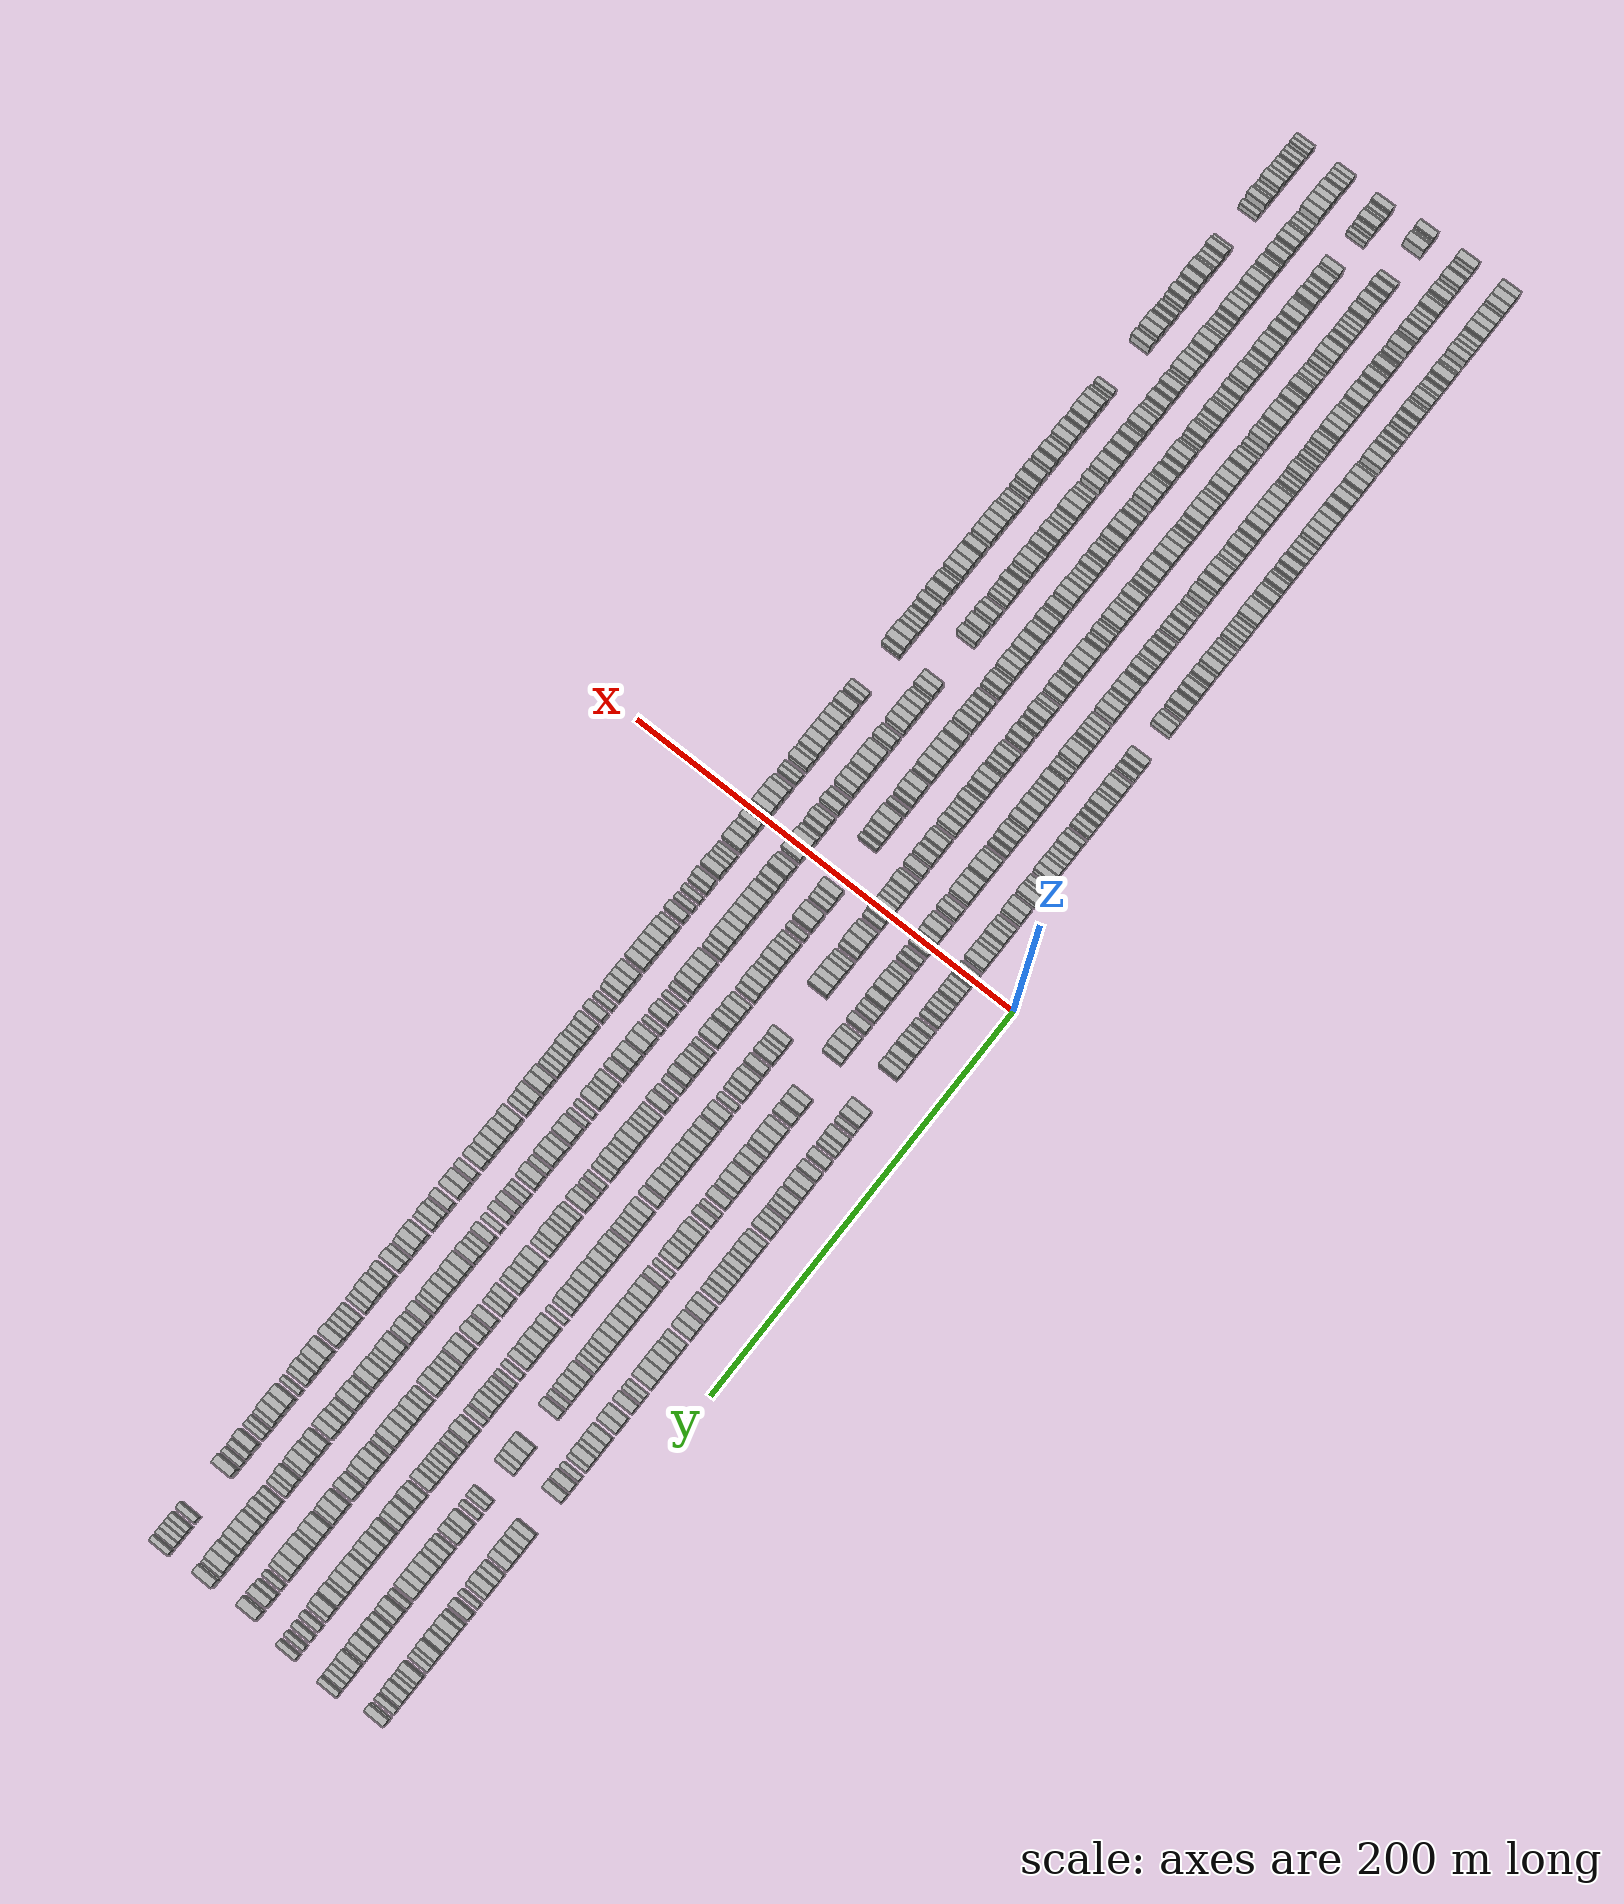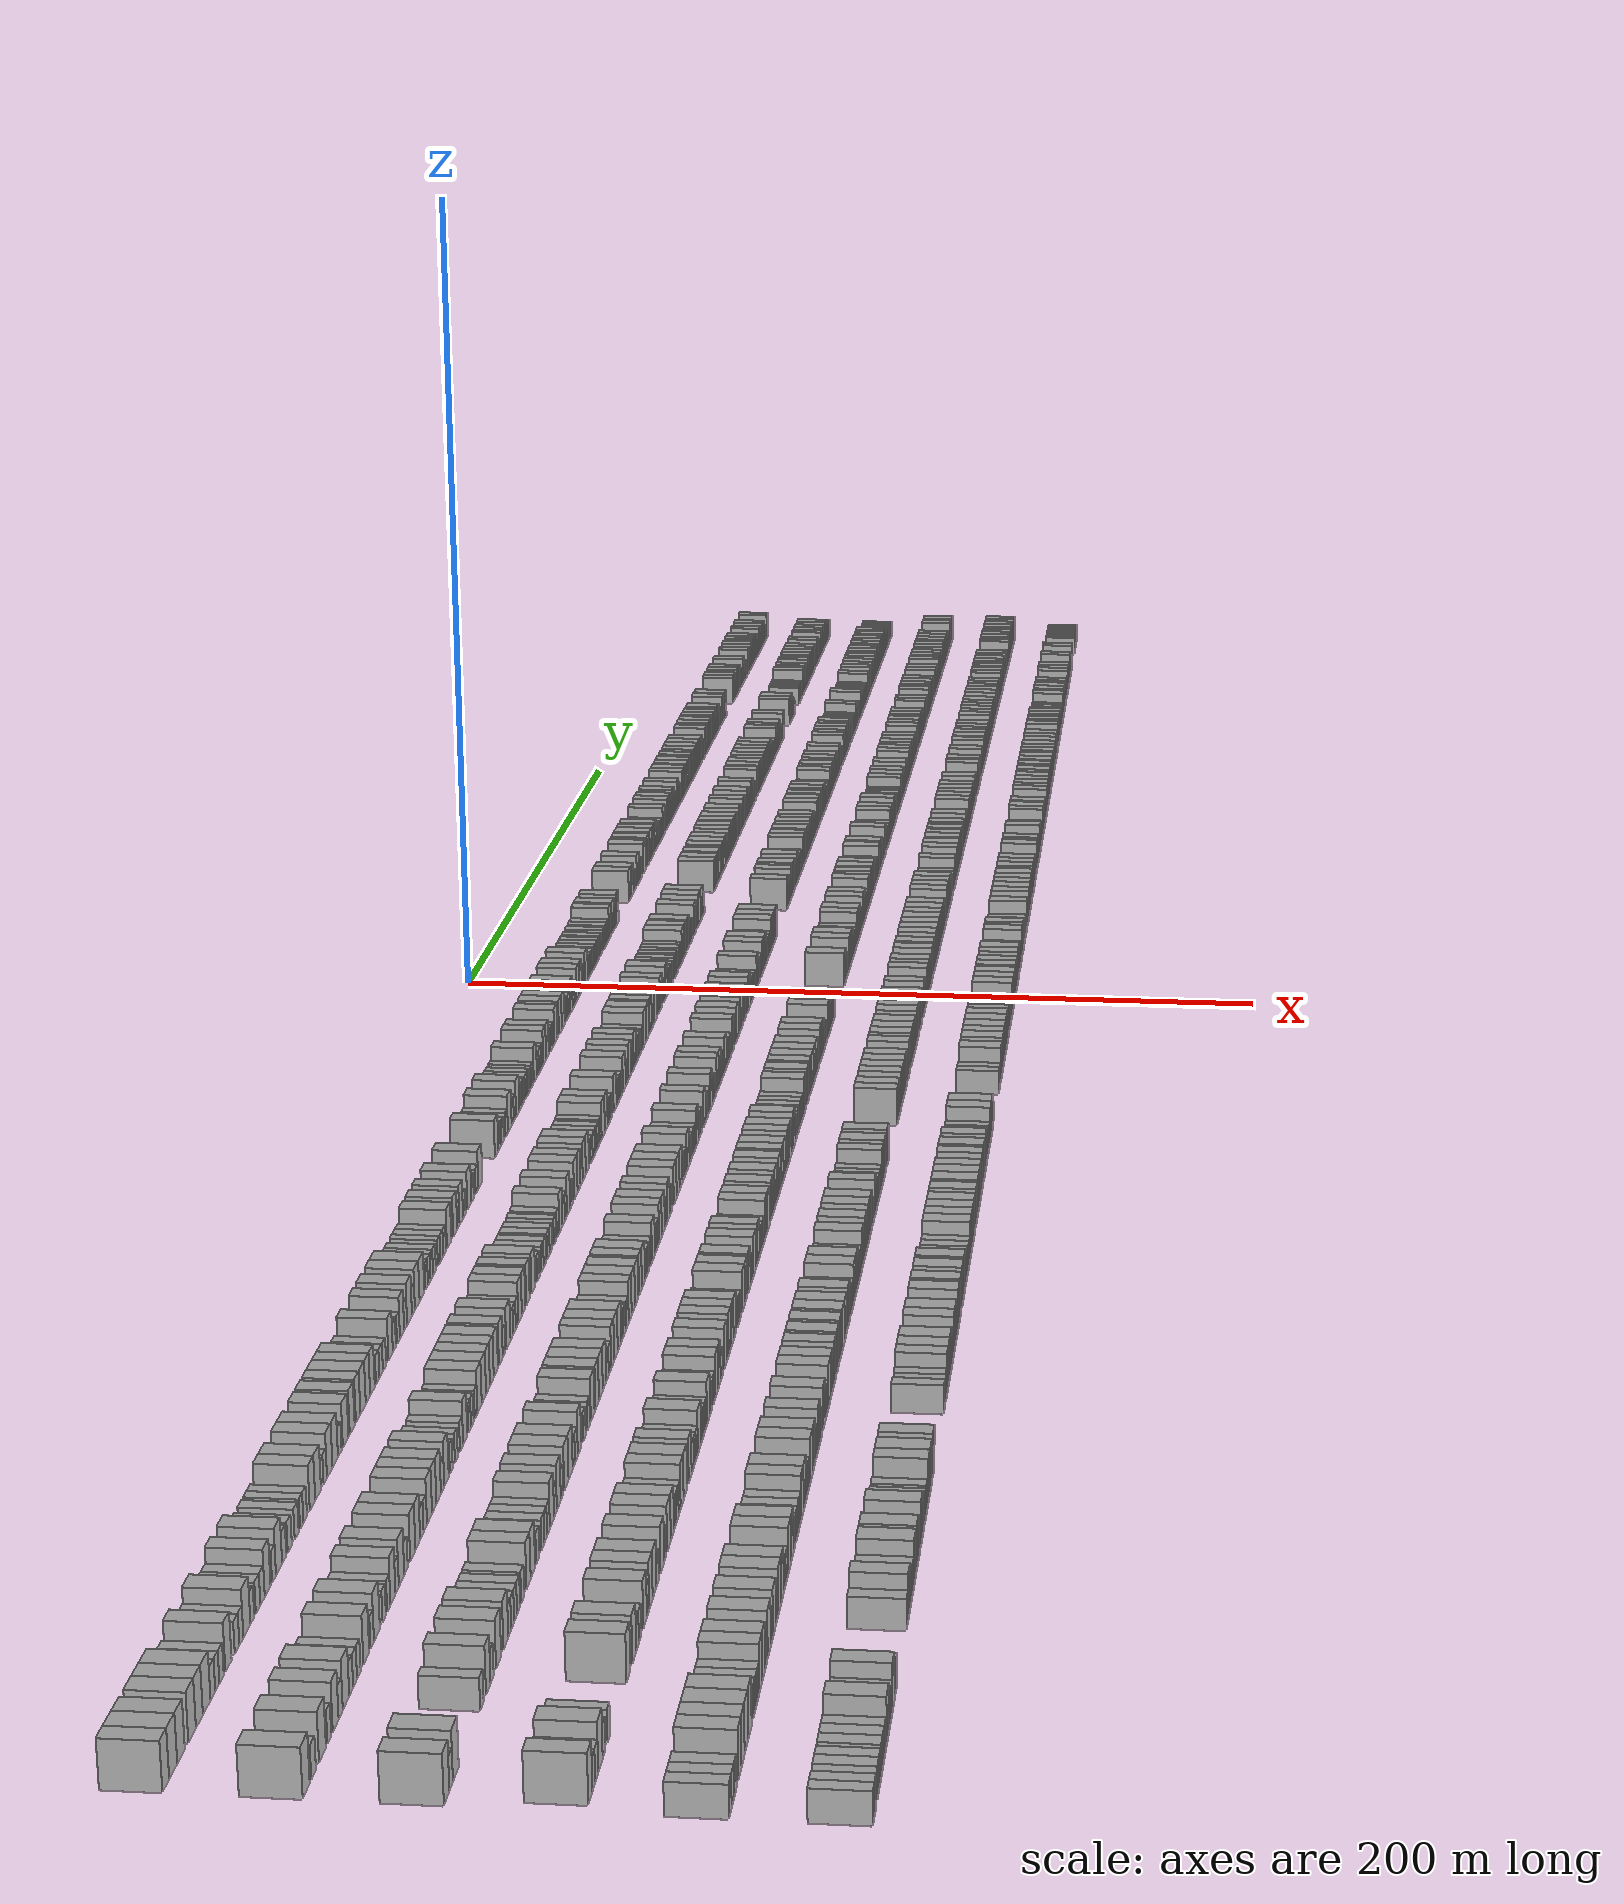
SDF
<sdf version="1.6">
 <world name="default">
  <scene>
   <sky><clouds><speed>12</speed></clouds></sky>
   <ambient>0.4 0.4 0.4 1</ambient>
   <background>0.7 0.7 0.7 1</background>
   <shadows>1</shadows>
  </scene>
  <gravity>0 0 -9.8066</gravity>
  <magnetic_field>6e-06 2.3e-05 -4.2e-05</magnetic_field>
  <physics default="0" name="default_physics" type="ode">
   <ode>
    <solver>
     <type>quick</type>
     <iters>10</iters>
     <sor>1.0</sor>
     <use_dynamic_moi_rescaling>0</use_dynamic_moi_rescaling>
    </solver>
    <constraints>
     <cfm>0</cfm>
     <erp>0.2</erp>
     <contact_max_correcting_vel>100</contact_max_correcting_vel>
     <contact_surface_layer>0.001</contact_surface_layer>
    </constraints>
   </ode>
   <max_step_size>0.004</max_step_size>
   <real_time_factor>1</real_time_factor>
   <real_time_update_rate>250</real_time_update_rate>
  </physics>
  <light name="sun" type="directional">
   <pose>0 0 10 0 0 0</pose>
   <diffuse>0.8 0.8 0.8 1</diffuse>
   <specular>0.2 0.2 0.2 1</specular>
   <attenuation>
    <range>1000</range>
    <constant>0.9</constant>
    <linear>0.01</linear>
    <quadratic>0.001</quadratic>
   </attenuation>
   <direction>-0.5 0.1 -0.9</direction>
  </light>
  <model name="building_1">
   <static>1</static>
   <pose>25.0000 -378.1402 0 0.000000 0.000000 0.000000</pose>
   <link name="link">
    <pose>0 0 4.50 0 0 0</pose>
    <collision name="collision"><geometry><box><size>10.0000 3.7196 9.0000</size></box></geometry></collision>
    <visual name="visual">
     <cast_shadows>0</cast_shadows>
     <geometry><box><size>10.0000 3.7196 9.0000</size></box></geometry>
     <material>
      <script>
       <uri>model://HANNAS_wall/materials/scripts</uri>
       <uri>model://HANNAS_wall/materials/textures</uri>
       <name>vrc/HANNAS_wall</name>
      </script>
     </material>
    </visual>
   </link>
  </model>
  <model name="building_2">
   <static>1</static>
   <pose>25.0000 -374.0354 0 0.000000 0.000000 0.000000</pose>
   <link name="link">
    <pose>0 0 4.50 0 0 0</pose>
    <collision name="collision"><geometry><box><size>10.0000 4.4899 9.0000</size></box></geometry></collision>
    <visual name="visual">
     <cast_shadows>0</cast_shadows>
     <geometry><box><size>10.0000 4.4899 9.0000</size></box></geometry>
     <material>
      <script>
       <uri>model://HANNAS_wall/materials/scripts</uri>
       <uri>model://HANNAS_wall/materials/textures</uri>
       <name>vrc/HANNAS_wall</name>
      </script>
     </material>
    </visual>
   </link>
  </model>
  <model name="building_3">
   <static>1</static>
   <pose>25.0000 -369.6766 0 0.000000 0.000000 0.000000</pose>
   <link name="link">
    <pose>0 0 4.50 0 0 0</pose>
    <collision name="collision"><geometry><box><size>10.0000 4.2278 9.0000</size></box></geometry></collision>
    <visual name="visual">
     <cast_shadows>0</cast_shadows>
     <geometry><box><size>10.0000 4.2278 9.0000</size></box></geometry>
     <material>
      <script>
       <uri>model://HANNAS_wall/materials/scripts</uri>
       <uri>model://HANNAS_wall/materials/textures</uri>
       <name>vrc/HANNAS_wall</name>
      </script>
     </material>
    </visual>
   </link>
  </model>
  <model name="building_4">
   <static>1</static>
   <pose>25.0000 -363.3770 0 0.000000 0.000000 0.000000</pose>
   <link name="link">
    <pose>0 0 4.50 0 0 0</pose>
    <collision name="collision"><geometry><box><size>10.0000 4.3713 9.0000</size></box></geometry></collision>
    <visual name="visual">
     <cast_shadows>0</cast_shadows>
     <geometry><box><size>10.0000 4.3713 9.0000</size></box></geometry>
     <material>
      <script>
       <uri>model://HANNAS_wall/materials/scripts</uri>
       <uri>model://HANNAS_wall/materials/textures</uri>
       <name>vrc/HANNAS_wall</name>
      </script>
     </material>
    </visual>
   </link>
  </model>
  <model name="building_5">
   <static>1</static>
   <pose>25.0000 -359.1662 0 0.000000 0.000000 0.000000</pose>
   <link name="link">
    <pose>0 0 4.50 0 0 0</pose>
    <collision name="collision"><geometry><box><size>10.0000 4.0502 9.0000</size></box></geometry></collision>
    <visual name="visual">
     <cast_shadows>0</cast_shadows>
     <geometry><box><size>10.0000 4.0502 9.0000</size></box></geometry>
     <material>
      <script>
       <uri>model://HANNAS_wall/materials/scripts</uri>
       <uri>model://HANNAS_wall/materials/textures</uri>
       <name>vrc/HANNAS_wall</name>
      </script>
     </material>
    </visual>
   </link>
  </model>
  <model name="building_6">
   <static>1</static>
   <pose>25.0000 -354.8929 0 0.000000 0.000000 0.000000</pose>
   <link name="link">
    <pose>0 0 4.50 0 0 0</pose>
    <collision name="collision"><geometry><box><size>10.0000 4.4964 9.0000</size></box></geometry></collision>
    <visual name="visual">
     <cast_shadows>0</cast_shadows>
     <geometry><box><size>10.0000 4.4964 9.0000</size></box></geometry>
     <material>
      <script>
       <uri>model://HANNAS_wall/materials/scripts</uri>
       <uri>model://HANNAS_wall/materials/textures</uri>
       <name>vrc/HANNAS_wall</name>
      </script>
     </material>
    </visual>
   </link>
  </model>
  <model name="building_7">
   <static>1</static>
   <pose>25.0000 -351.2328 0 0.000000 0.000000 0.000000</pose>
   <link name="link">
    <pose>0 0 3.00 0 0 0</pose>
    <collision name="collision"><geometry><box><size>10.0000 2.8237 6.0000</size></box></geometry></collision>
    <visual name="visual">
     <cast_shadows>0</cast_shadows>
     <geometry><box><size>10.0000 2.8237 6.0000</size></box></geometry>
     <material>
      <script>
       <uri>model://HANNAS_wall/materials/scripts</uri>
       <uri>model://HANNAS_wall/materials/textures</uri>
       <name>vrc/HANNAS_wall</name>
      </script>
     </material>
    </visual>
   </link>
  </model>
  <model name="building_8">
   <static>1</static>
   <pose>25.0000 -348.5571 0 0.000000 0.000000 0.000000</pose>
   <link name="link">
    <pose>0 0 3.00 0 0 0</pose>
    <collision name="collision"><geometry><box><size>10.0000 2.5278 6.0000</size></box></geometry></collision>
    <visual name="visual">
     <cast_shadows>0</cast_shadows>
     <geometry><box><size>10.0000 2.5278 6.0000</size></box></geometry>
     <material>
      <script>
       <uri>model://HANNAS_wall/materials/scripts</uri>
       <uri>model://HANNAS_wall/materials/textures</uri>
       <name>vrc/HANNAS_wall</name>
      </script>
     </material>
    </visual>
   </link>
  </model>
  <model name="building_9">
   <static>1</static>
   <pose>25.0000 -345.9805 0 0.000000 0.000000 0.000000</pose>
   <link name="link">
    <pose>0 0 3.00 0 0 0</pose>
    <collision name="collision"><geometry><box><size>10.0000 2.6253 6.0000</size></box></geometry></collision>
    <visual name="visual">
     <cast_shadows>0</cast_shadows>
     <geometry><box><size>10.0000 2.6253 6.0000</size></box></geometry>
     <material>
      <script>
       <uri>model://HANNAS_wall/materials/scripts</uri>
       <uri>model://HANNAS_wall/materials/textures</uri>
       <name>vrc/HANNAS_wall</name>
      </script>
     </material>
    </visual>
   </link>
  </model>
  <model name="building_10">
   <static>1</static>
   <pose>25.0000 -341.7650 0 0.000000 0.000000 0.000000</pose>
   <link name="link">
    <pose>0 0 4.50 0 0 0</pose>
    <collision name="collision"><geometry><box><size>10.0000 3.8057 9.0000</size></box></geometry></collision>
    <visual name="visual">
     <cast_shadows>0</cast_shadows>
     <geometry><box><size>10.0000 3.8057 9.0000</size></box></geometry>
     <material>
      <script>
       <uri>model://HANNAS_wall/materials/scripts</uri>
       <uri>model://HANNAS_wall/materials/textures</uri>
       <name>vrc/HANNAS_wall</name>
      </script>
     </material>
    </visual>
   </link>
  </model>
  <model name="building_11">
   <static>1</static>
   <pose>25.0000 -336.4213 0 0.000000 0.000000 0.000000</pose>
   <link name="link">
    <pose>0 0 3.00 0 0 0</pose>
    <collision name="collision"><geometry><box><size>10.0000 2.8817 6.0000</size></box></geometry></collision>
    <visual name="visual">
     <cast_shadows>0</cast_shadows>
     <geometry><box><size>10.0000 2.8817 6.0000</size></box></geometry>
     <material>
      <script>
       <uri>model://HANNAS_wall/materials/scripts</uri>
       <uri>model://HANNAS_wall/materials/textures</uri>
       <name>vrc/HANNAS_wall</name>
      </script>
     </material>
    </visual>
   </link>
  </model>
  <model name="building_12">
   <static>1</static>
   <pose>25.0000 -333.7093 0 0.000000 0.000000 0.000000</pose>
   <link name="link">
    <pose>0 0 3.00 0 0 0</pose>
    <collision name="collision"><geometry><box><size>10.0000 2.5423 6.0000</size></box></geometry></collision>
    <visual name="visual">
     <cast_shadows>0</cast_shadows>
     <geometry><box><size>10.0000 2.5423 6.0000</size></box></geometry>
     <material>
      <script>
       <uri>model://HANNAS_wall/materials/scripts</uri>
       <uri>model://HANNAS_wall/materials/textures</uri>
       <name>vrc/HANNAS_wall</name>
      </script>
     </material>
    </visual>
   </link>
  </model>
  <model name="building_13">
   <static>1</static>
   <pose>25.0000 -330.1908 0 0.000000 0.000000 0.000000</pose>
   <link name="link">
    <pose>0 0 4.50 0 0 0</pose>
    <collision name="collision"><geometry><box><size>10.0000 4.4947 9.0000</size></box></geometry></collision>
    <visual name="visual">
     <cast_shadows>0</cast_shadows>
     <geometry><box><size>10.0000 4.4947 9.0000</size></box></geometry>
     <material>
      <script>
       <uri>model://HANNAS_wall/materials/scripts</uri>
       <uri>model://HANNAS_wall/materials/textures</uri>
       <name>vrc/HANNAS_wall</name>
      </script>
     </material>
    </visual>
   </link>
  </model>
  <model name="building_14">
   <static>1</static>
   <pose>25.0000 -326.6893 0 0.000000 0.000000 0.000000</pose>
   <link name="link">
    <pose>0 0 3.00 0 0 0</pose>
    <collision name="collision"><geometry><box><size>10.0000 2.5083 6.0000</size></box></geometry></collision>
    <visual name="visual">
     <cast_shadows>0</cast_shadows>
     <geometry><box><size>10.0000 2.5083 6.0000</size></box></geometry>
     <material>
      <script>
       <uri>model://HANNAS_wall/materials/scripts</uri>
       <uri>model://HANNAS_wall/materials/textures</uri>
       <name>vrc/HANNAS_wall</name>
      </script>
     </material>
    </visual>
   </link>
  </model>
  <model name="building_15">
   <static>1</static>
   <pose>25.0000 -322.9379 0 0.000000 0.000000 0.000000</pose>
   <link name="link">
    <pose>0 0 3.00 0 0 0</pose>
    <collision name="collision"><geometry><box><size>10.0000 2.9943 6.0000</size></box></geometry></collision>
    <visual name="visual">
     <cast_shadows>0</cast_shadows>
     <geometry><box><size>10.0000 2.9943 6.0000</size></box></geometry>
     <material>
      <script>
       <uri>model://HANNAS_wall/materials/scripts</uri>
       <uri>model://HANNAS_wall/materials/textures</uri>
       <name>vrc/HANNAS_wall</name>
      </script>
     </material>
    </visual>
   </link>
  </model>
  <model name="building_16">
   <static>1</static>
   <pose>25.0000 -320.0006 0 0.000000 0.000000 0.000000</pose>
   <link name="link">
    <pose>0 0 3.00 0 0 0</pose>
    <collision name="collision"><geometry><box><size>10.0000 2.8804 6.0000</size></box></geometry></collision>
    <visual name="visual">
     <cast_shadows>0</cast_shadows>
     <geometry><box><size>10.0000 2.8804 6.0000</size></box></geometry>
     <material>
      <script>
       <uri>model://HANNAS_wall/materials/scripts</uri>
       <uri>model://HANNAS_wall/materials/textures</uri>
       <name>vrc/HANNAS_wall</name>
      </script>
     </material>
    </visual>
   </link>
  </model>
  <model name="building_17">
   <static>1</static>
   <pose>25.0000 -316.6251 0 0.000000 0.000000 0.000000</pose>
   <link name="link">
    <pose>0 0 4.50 0 0 0</pose>
    <collision name="collision"><geometry><box><size>10.0000 3.8706 9.0000</size></box></geometry></collision>
    <visual name="visual">
     <cast_shadows>0</cast_shadows>
     <geometry><box><size>10.0000 3.8706 9.0000</size></box></geometry>
     <material>
      <script>
       <uri>model://HANNAS_wall/materials/scripts</uri>
       <uri>model://HANNAS_wall/materials/textures</uri>
       <name>vrc/HANNAS_wall</name>
      </script>
     </material>
    </visual>
   </link>
  </model>
  <model name="building_18">
   <static>1</static>
   <pose>25.0000 -312.3613 0 0.000000 0.000000 0.000000</pose>
   <link name="link">
    <pose>0 0 3.00 0 0 0</pose>
    <collision name="collision"><geometry><box><size>10.0000 2.6570 6.0000</size></box></geometry></collision>
    <visual name="visual">
     <cast_shadows>0</cast_shadows>
     <geometry><box><size>10.0000 2.6570 6.0000</size></box></geometry>
     <material>
      <script>
       <uri>model://HANNAS_wall/materials/scripts</uri>
       <uri>model://HANNAS_wall/materials/textures</uri>
       <name>vrc/HANNAS_wall</name>
      </script>
     </material>
    </visual>
   </link>
  </model>
  <model name="building_19">
   <static>1</static>
   <pose>25.0000 -308.9249 0 0.000000 0.000000 0.000000</pose>
   <link name="link">
    <pose>0 0 4.50 0 0 0</pose>
    <collision name="collision"><geometry><box><size>10.0000 4.2157 9.0000</size></box></geometry></collision>
    <visual name="visual">
     <cast_shadows>0</cast_shadows>
     <geometry><box><size>10.0000 4.2157 9.0000</size></box></geometry>
     <material>
      <script>
       <uri>model://HANNAS_wall/materials/scripts</uri>
       <uri>model://HANNAS_wall/materials/textures</uri>
       <name>vrc/HANNAS_wall</name>
      </script>
     </material>
    </visual>
   </link>
  </model>
  <model name="building_20">
   <static>1</static>
   <pose>25.0000 -305.3701 0 0.000000 0.000000 0.000000</pose>
   <link name="link">
    <pose>0 0 3.00 0 0 0</pose>
    <collision name="collision"><geometry><box><size>10.0000 2.8938 6.0000</size></box></geometry></collision>
    <visual name="visual">
     <cast_shadows>0</cast_shadows>
     <geometry><box><size>10.0000 2.8938 6.0000</size></box></geometry>
     <material>
      <script>
       <uri>model://HANNAS_wall/materials/scripts</uri>
       <uri>model://HANNAS_wall/materials/textures</uri>
       <name>vrc/HANNAS_wall</name>
      </script>
     </material>
    </visual>
   </link>
  </model>
  <model name="building_21">
   <static>1</static>
   <pose>25.0000 -301.4968 0 0.000000 0.000000 0.000000</pose>
   <link name="link">
    <pose>0 0 3.00 0 0 0</pose>
    <collision name="collision"><geometry><box><size>10.0000 2.8527 6.0000</size></box></geometry></collision>
    <visual name="visual">
     <cast_shadows>0</cast_shadows>
     <geometry><box><size>10.0000 2.8527 6.0000</size></box></geometry>
     <material>
      <script>
       <uri>model://HANNAS_wall/materials/scripts</uri>
       <uri>model://HANNAS_wall/materials/textures</uri>
       <name>vrc/HANNAS_wall</name>
      </script>
     </material>
    </visual>
   </link>
  </model>
  <model name="building_22">
   <static>1</static>
   <pose>25.0000 -296.6510 0 0.000000 0.000000 0.000000</pose>
   <link name="link">
    <pose>0 0 3.00 0 0 0</pose>
    <collision name="collision"><geometry><box><size>10.0000 2.8390 6.0000</size></box></geometry></collision>
    <visual name="visual">
     <cast_shadows>0</cast_shadows>
     <geometry><box><size>10.0000 2.8390 6.0000</size></box></geometry>
     <material>
      <script>
       <uri>model://HANNAS_wall/materials/scripts</uri>
       <uri>model://HANNAS_wall/materials/textures</uri>
       <name>vrc/HANNAS_wall</name>
      </script>
     </material>
    </visual>
   </link>
  </model>
  <model name="building_23">
   <static>1</static>
   <pose>25.0000 -293.0241 0 0.000000 0.000000 0.000000</pose>
   <link name="link">
    <pose>0 0 3.00 0 0 0</pose>
    <collision name="collision"><geometry><box><size>10.0000 2.4147 6.0000</size></box></geometry></collision>
    <visual name="visual">
     <cast_shadows>0</cast_shadows>
     <geometry><box><size>10.0000 2.4147 6.0000</size></box></geometry>
     <material>
      <script>
       <uri>model://HANNAS_wall/materials/scripts</uri>
       <uri>model://HANNAS_wall/materials/textures</uri>
       <name>vrc/HANNAS_wall</name>
      </script>
     </material>
    </visual>
   </link>
  </model>
  <model name="building_24">
   <static>1</static>
   <pose>25.0000 -290.5243 0 0.000000 0.000000 0.000000</pose>
   <link name="link">
    <pose>0 0 3.00 0 0 0</pose>
    <collision name="collision"><geometry><box><size>10.0000 2.5849 6.0000</size></box></geometry></collision>
    <visual name="visual">
     <cast_shadows>0</cast_shadows>
     <geometry><box><size>10.0000 2.5849 6.0000</size></box></geometry>
     <material>
      <script>
       <uri>model://HANNAS_wall/materials/scripts</uri>
       <uri>model://HANNAS_wall/materials/textures</uri>
       <name>vrc/HANNAS_wall</name>
      </script>
     </material>
    </visual>
   </link>
  </model>
  <model name="building_25">
   <static>1</static>
   <pose>25.0000 -285.2154 0 0.000000 0.000000 0.000000</pose>
   <link name="link">
    <pose>0 0 4.50 0 0 0</pose>
    <collision name="collision"><geometry><box><size>10.0000 4.0328 9.0000</size></box></geometry></collision>
    <visual name="visual">
     <cast_shadows>0</cast_shadows>
     <geometry><box><size>10.0000 4.0328 9.0000</size></box></geometry>
     <material>
      <script>
       <uri>model://HANNAS_wall/materials/scripts</uri>
       <uri>model://HANNAS_wall/materials/textures</uri>
       <name>vrc/HANNAS_wall</name>
      </script>
     </material>
    </visual>
   </link>
  </model>
  <model name="building_26">
   <static>1</static>
   <pose>25.0000 -281.0888 0 0.000000 0.000000 0.000000</pose>
   <link name="link">
    <pose>0 0 4.50 0 0 0</pose>
    <collision name="collision"><geometry><box><size>10.0000 4.2205 9.0000</size></box></geometry></collision>
    <visual name="visual">
     <cast_shadows>0</cast_shadows>
     <geometry><box><size>10.0000 4.2205 9.0000</size></box></geometry>
     <material>
      <script>
       <uri>model://HANNAS_wall/materials/scripts</uri>
       <uri>model://HANNAS_wall/materials/textures</uri>
       <name>vrc/HANNAS_wall</name>
      </script>
     </material>
    </visual>
   </link>
  </model>
  <model name="building_27">
   <static>1</static>
   <pose>25.0000 -275.6913 0 0.000000 0.000000 0.000000</pose>
   <link name="link">
    <pose>0 0 3.00 0 0 0</pose>
    <collision name="collision"><geometry><box><size>10.0000 2.5745 6.0000</size></box></geometry></collision>
    <visual name="visual">
     <cast_shadows>0</cast_shadows>
     <geometry><box><size>10.0000 2.5745 6.0000</size></box></geometry>
     <material>
      <script>
       <uri>model://HANNAS_wall/materials/scripts</uri>
       <uri>model://HANNAS_wall/materials/textures</uri>
       <name>vrc/HANNAS_wall</name>
      </script>
     </material>
    </visual>
   </link>
  </model>
  <model name="building_28">
   <static>1</static>
   <pose>25.0000 -272.3003 0 0.000000 0.000000 0.000000</pose>
   <link name="link">
    <pose>0 0 4.50 0 0 0</pose>
    <collision name="collision"><geometry><box><size>10.0000 4.2075 9.0000</size></box></geometry></collision>
    <visual name="visual">
     <cast_shadows>0</cast_shadows>
     <geometry><box><size>10.0000 4.2075 9.0000</size></box></geometry>
     <material>
      <script>
       <uri>model://HANNAS_wall/materials/scripts</uri>
       <uri>model://HANNAS_wall/materials/textures</uri>
       <name>vrc/HANNAS_wall</name>
      </script>
     </material>
    </visual>
   </link>
  </model>
  <model name="building_29">
   <static>1</static>
   <pose>25.0000 -268.0924 0 0.000000 0.000000 0.000000</pose>
   <link name="link">
    <pose>0 0 4.50 0 0 0</pose>
    <collision name="collision"><geometry><box><size>10.0000 4.2083 9.0000</size></box></geometry></collision>
    <visual name="visual">
     <cast_shadows>0</cast_shadows>
     <geometry><box><size>10.0000 4.2083 9.0000</size></box></geometry>
     <material>
      <script>
       <uri>model://HANNAS_wall/materials/scripts</uri>
       <uri>model://HANNAS_wall/materials/textures</uri>
       <name>vrc/HANNAS_wall</name>
      </script>
     </material>
    </visual>
   </link>
  </model>
  <model name="building_30">
   <static>1</static>
   <pose>25.0000 -264.5760 0 0.000000 0.000000 0.000000</pose>
   <link name="link">
    <pose>0 0 3.00 0 0 0</pose>
    <collision name="collision"><geometry><box><size>10.0000 2.8246 6.0000</size></box></geometry></collision>
    <visual name="visual">
     <cast_shadows>0</cast_shadows>
     <geometry><box><size>10.0000 2.8246 6.0000</size></box></geometry>
     <material>
      <script>
       <uri>model://HANNAS_wall/materials/scripts</uri>
       <uri>model://HANNAS_wall/materials/textures</uri>
       <name>vrc/HANNAS_wall</name>
      </script>
     </material>
    </visual>
   </link>
  </model>
  <model name="building_31">
   <static>1</static>
   <pose>25.0000 -259.9364 0 0.000000 0.000000 0.000000</pose>
   <link name="link">
    <pose>0 0 4.50 0 0 0</pose>
    <collision name="collision"><geometry><box><size>10.0000 4.4545 9.0000</size></box></geometry></collision>
    <visual name="visual">
     <cast_shadows>0</cast_shadows>
     <geometry><box><size>10.0000 4.4545 9.0000</size></box></geometry>
     <material>
      <script>
       <uri>model://HANNAS_wall/materials/scripts</uri>
       <uri>model://HANNAS_wall/materials/textures</uri>
       <name>vrc/HANNAS_wall</name>
      </script>
     </material>
    </visual>
   </link>
  </model>
  <model name="building_32">
   <static>1</static>
   <pose>25.0000 -254.7309 0 0.000000 0.000000 0.000000</pose>
   <link name="link">
    <pose>0 0 4.50 0 0 0</pose>
    <collision name="collision"><geometry><box><size>10.0000 3.9564 9.0000</size></box></geometry></collision>
    <visual name="visual">
     <cast_shadows>0</cast_shadows>
     <geometry><box><size>10.0000 3.9564 9.0000</size></box></geometry>
     <material>
      <script>
       <uri>model://HANNAS_wall/materials/scripts</uri>
       <uri>model://HANNAS_wall/materials/textures</uri>
       <name>vrc/HANNAS_wall</name>
      </script>
     </material>
    </visual>
   </link>
  </model>
  <model name="building_33">
   <static>1</static>
   <pose>25.0000 -249.9148 0 0.000000 0.000000 0.000000</pose>
   <link name="link">
    <pose>0 0 4.50 0 0 0</pose>
    <collision name="collision"><geometry><box><size>10.0000 3.6759 9.0000</size></box></geometry></collision>
    <visual name="visual">
     <cast_shadows>0</cast_shadows>
     <geometry><box><size>10.0000 3.6759 9.0000</size></box></geometry>
     <material>
      <script>
       <uri>model://HANNAS_wall/materials/scripts</uri>
       <uri>model://HANNAS_wall/materials/textures</uri>
       <name>vrc/HANNAS_wall</name>
      </script>
     </material>
    </visual>
   </link>
  </model>
  <model name="building_34">
   <static>1</static>
   <pose>25.0000 -245.8688 0 0.000000 0.000000 0.000000</pose>
   <link name="link">
    <pose>0 0 4.50 0 0 0</pose>
    <collision name="collision"><geometry><box><size>10.0000 4.4161 9.0000</size></box></geometry></collision>
    <visual name="visual">
     <cast_shadows>0</cast_shadows>
     <geometry><box><size>10.0000 4.4161 9.0000</size></box></geometry>
     <material>
      <script>
       <uri>model://HANNAS_wall/materials/scripts</uri>
       <uri>model://HANNAS_wall/materials/textures</uri>
       <name>vrc/HANNAS_wall</name>
      </script>
     </material>
    </visual>
   </link>
  </model>
  <model name="building_35">
   <static>1</static>
   <pose>25.0000 -241.8168 0 0.000000 0.000000 0.000000</pose>
   <link name="link">
    <pose>0 0 4.50 0 0 0</pose>
    <collision name="collision"><geometry><box><size>10.0000 3.6878 9.0000</size></box></geometry></collision>
    <visual name="visual">
     <cast_shadows>0</cast_shadows>
     <geometry><box><size>10.0000 3.6878 9.0000</size></box></geometry>
     <material>
      <script>
       <uri>model://HANNAS_wall/materials/scripts</uri>
       <uri>model://HANNAS_wall/materials/textures</uri>
       <name>vrc/HANNAS_wall</name>
      </script>
     </material>
    </visual>
   </link>
  </model>
  <model name="building_36">
   <static>1</static>
   <pose>25.0000 -238.0493 0 0.000000 0.000000 0.000000</pose>
   <link name="link">
    <pose>0 0 4.50 0 0 0</pose>
    <collision name="collision"><geometry><box><size>10.0000 3.8472 9.0000</size></box></geometry></collision>
    <visual name="visual">
     <cast_shadows>0</cast_shadows>
     <geometry><box><size>10.0000 3.8472 9.0000</size></box></geometry>
     <material>
      <script>
       <uri>model://HANNAS_wall/materials/scripts</uri>
       <uri>model://HANNAS_wall/materials/textures</uri>
       <name>vrc/HANNAS_wall</name>
      </script>
     </material>
    </visual>
   </link>
  </model>
  <model name="building_37">
   <static>1</static>
   <pose>25.0000 -233.6290 0 0.000000 0.000000 0.000000</pose>
   <link name="link">
    <pose>0 0 3.00 0 0 0</pose>
    <collision name="collision"><geometry><box><size>10.0000 2.9935 6.0000</size></box></geometry></collision>
    <visual name="visual">
     <cast_shadows>0</cast_shadows>
     <geometry><box><size>10.0000 2.9935 6.0000</size></box></geometry>
     <material>
      <script>
       <uri>model://HANNAS_wall/materials/scripts</uri>
       <uri>model://HANNAS_wall/materials/textures</uri>
       <name>vrc/HANNAS_wall</name>
      </script>
     </material>
    </visual>
   </link>
  </model>
  <model name="building_38">
   <static>1</static>
   <pose>25.0000 -230.6580 0 0.000000 0.000000 0.000000</pose>
   <link name="link">
    <pose>0 0 3.00 0 0 0</pose>
    <collision name="collision"><geometry><box><size>10.0000 2.9485 6.0000</size></box></geometry></collision>
    <visual name="visual">
     <cast_shadows>0</cast_shadows>
     <geometry><box><size>10.0000 2.9485 6.0000</size></box></geometry>
     <material>
      <script>
       <uri>model://HANNAS_wall/materials/scripts</uri>
       <uri>model://HANNAS_wall/materials/textures</uri>
       <name>vrc/HANNAS_wall</name>
      </script>
     </material>
    </visual>
   </link>
  </model>
  <model name="building_39">
   <static>1</static>
   <pose>25.0000 -227.7709 0 0.000000 0.000000 0.000000</pose>
   <link name="link">
    <pose>0 0 3.00 0 0 0</pose>
    <collision name="collision"><geometry><box><size>10.0000 2.8256 6.0000</size></box></geometry></collision>
    <visual name="visual">
     <cast_shadows>0</cast_shadows>
     <geometry><box><size>10.0000 2.8256 6.0000</size></box></geometry>
     <material>
      <script>
       <uri>model://HANNAS_wall/materials/scripts</uri>
       <uri>model://HANNAS_wall/materials/textures</uri>
       <name>vrc/HANNAS_wall</name>
      </script>
     </material>
    </visual>
   </link>
  </model>
  <model name="building_40">
   <static>1</static>
   <pose>25.0000 -222.4260 0 0.000000 0.000000 0.000000</pose>
   <link name="link">
    <pose>0 0 4.50 0 0 0</pose>
    <collision name="collision"><geometry><box><size>10.0000 3.8643 9.0000</size></box></geometry></collision>
    <visual name="visual">
     <cast_shadows>0</cast_shadows>
     <geometry><box><size>10.0000 3.8643 9.0000</size></box></geometry>
     <material>
      <script>
       <uri>model://HANNAS_wall/materials/scripts</uri>
       <uri>model://HANNAS_wall/materials/textures</uri>
       <name>vrc/HANNAS_wall</name>
      </script>
     </material>
    </visual>
   </link>
  </model>
  <model name="building_41">
   <static>1</static>
   <pose>25.0000 -219.1392 0 0.000000 0.000000 0.000000</pose>
   <link name="link">
    <pose>0 0 3.00 0 0 0</pose>
    <collision name="collision"><geometry><box><size>10.0000 2.7093 6.0000</size></box></geometry></collision>
    <visual name="visual">
     <cast_shadows>0</cast_shadows>
     <geometry><box><size>10.0000 2.7093 6.0000</size></box></geometry>
     <material>
      <script>
       <uri>model://HANNAS_wall/materials/scripts</uri>
       <uri>model://HANNAS_wall/materials/textures</uri>
       <name>vrc/HANNAS_wall</name>
      </script>
     </material>
    </visual>
   </link>
  </model>
  <model name="building_42">
   <static>1</static>
   <pose>25.0000 -215.4907 0 0.000000 0.000000 0.000000</pose>
   <link name="link">
    <pose>0 0 3.00 0 0 0</pose>
    <collision name="collision"><geometry><box><size>10.0000 2.5876 6.0000</size></box></geometry></collision>
    <visual name="visual">
     <cast_shadows>0</cast_shadows>
     <geometry><box><size>10.0000 2.5876 6.0000</size></box></geometry>
     <material>
      <script>
       <uri>model://HANNAS_wall/materials/scripts</uri>
       <uri>model://HANNAS_wall/materials/textures</uri>
       <name>vrc/HANNAS_wall</name>
      </script>
     </material>
    </visual>
   </link>
  </model>
  <model name="building_43">
   <static>1</static>
   <pose>25.0000 -212.2782 0 0.000000 0.000000 0.000000</pose>
   <link name="link">
    <pose>0 0 4.50 0 0 0</pose>
    <collision name="collision"><geometry><box><size>10.0000 3.8374 9.0000</size></box></geometry></collision>
    <visual name="visual">
     <cast_shadows>0</cast_shadows>
     <geometry><box><size>10.0000 3.8374 9.0000</size></box></geometry>
     <material>
      <script>
       <uri>model://HANNAS_wall/materials/scripts</uri>
       <uri>model://HANNAS_wall/materials/textures</uri>
       <name>vrc/HANNAS_wall</name>
      </script>
     </material>
    </visual>
   </link>
  </model>
  <model name="building_44">
   <static>1</static>
   <pose>25.0000 -209.0269 0 0.000000 0.000000 0.000000</pose>
   <link name="link">
    <pose>0 0 3.00 0 0 0</pose>
    <collision name="collision"><geometry><box><size>10.0000 2.6652 6.0000</size></box></geometry></collision>
    <visual name="visual">
     <cast_shadows>0</cast_shadows>
     <geometry><box><size>10.0000 2.6652 6.0000</size></box></geometry>
     <material>
      <script>
       <uri>model://HANNAS_wall/materials/scripts</uri>
       <uri>model://HANNAS_wall/materials/textures</uri>
       <name>vrc/HANNAS_wall</name>
      </script>
     </material>
    </visual>
   </link>
  </model>
  <model name="building_45">
   <static>1</static>
   <pose>25.0000 -205.4694 0 0.000000 0.000000 0.000000</pose>
   <link name="link">
    <pose>0 0 4.50 0 0 0</pose>
    <collision name="collision"><geometry><box><size>10.0000 4.4498 9.0000</size></box></geometry></collision>
    <visual name="visual">
     <cast_shadows>0</cast_shadows>
     <geometry><box><size>10.0000 4.4498 9.0000</size></box></geometry>
     <material>
      <script>
       <uri>model://HANNAS_wall/materials/scripts</uri>
       <uri>model://HANNAS_wall/materials/textures</uri>
       <name>vrc/HANNAS_wall</name>
      </script>
     </material>
    </visual>
   </link>
  </model>
  <model name="building_46">
   <static>1</static>
   <pose>25.0000 -201.8686 0 0.000000 0.000000 0.000000</pose>
   <link name="link">
    <pose>0 0 3.00 0 0 0</pose>
    <collision name="collision"><geometry><box><size>10.0000 2.7518 6.0000</size></box></geometry></collision>
    <visual name="visual">
     <cast_shadows>0</cast_shadows>
     <geometry><box><size>10.0000 2.7518 6.0000</size></box></geometry>
     <material>
      <script>
       <uri>model://HANNAS_wall/materials/scripts</uri>
       <uri>model://HANNAS_wall/materials/textures</uri>
       <name>vrc/HANNAS_wall</name>
      </script>
     </material>
    </visual>
   </link>
  </model>
  <model name="building_47">
   <static>1</static>
   <pose>25.0000 -198.3049 0 0.000000 0.000000 0.000000</pose>
   <link name="link">
    <pose>0 0 4.50 0 0 0</pose>
    <collision name="collision"><geometry><box><size>10.0000 4.3757 9.0000</size></box></geometry></collision>
    <visual name="visual">
     <cast_shadows>0</cast_shadows>
     <geometry><box><size>10.0000 4.3757 9.0000</size></box></geometry>
     <material>
      <script>
       <uri>model://HANNAS_wall/materials/scripts</uri>
       <uri>model://HANNAS_wall/materials/textures</uri>
       <name>vrc/HANNAS_wall</name>
      </script>
     </material>
    </visual>
   </link>
  </model>
  <model name="building_48">
   <static>1</static>
   <pose>25.0000 -193.8759 0 0.000000 0.000000 0.000000</pose>
   <link name="link">
    <pose>0 0 4.50 0 0 0</pose>
    <collision name="collision"><geometry><box><size>10.0000 4.4822 9.0000</size></box></geometry></collision>
    <visual name="visual">
     <cast_shadows>0</cast_shadows>
     <geometry><box><size>10.0000 4.4822 9.0000</size></box></geometry>
     <material>
      <script>
       <uri>model://HANNAS_wall/materials/scripts</uri>
       <uri>model://HANNAS_wall/materials/textures</uri>
       <name>vrc/HANNAS_wall</name>
      </script>
     </material>
    </visual>
   </link>
  </model>
  <model name="building_49">
   <static>1</static>
   <pose>25.0000 -189.3952 0 0.000000 0.000000 0.000000</pose>
   <link name="link">
    <pose>0 0 3.00 0 0 0</pose>
    <collision name="collision"><geometry><box><size>10.0000 2.4792 6.0000</size></box></geometry></collision>
    <visual name="visual">
     <cast_shadows>0</cast_shadows>
     <geometry><box><size>10.0000 2.4792 6.0000</size></box></geometry>
     <material>
      <script>
       <uri>model://HANNAS_wall/materials/scripts</uri>
       <uri>model://HANNAS_wall/materials/textures</uri>
       <name>vrc/HANNAS_wall</name>
      </script>
     </material>
    </visual>
   </link>
  </model>
  <model name="building_50">
   <static>1</static>
   <pose>25.0000 -186.9247 0 0.000000 0.000000 0.000000</pose>
   <link name="link">
    <pose>0 0 3.00 0 0 0</pose>
    <collision name="collision"><geometry><box><size>10.0000 2.4616 6.0000</size></box></geometry></collision>
    <visual name="visual">
     <cast_shadows>0</cast_shadows>
     <geometry><box><size>10.0000 2.4616 6.0000</size></box></geometry>
     <material>
      <script>
       <uri>model://HANNAS_wall/materials/scripts</uri>
       <uri>model://HANNAS_wall/materials/textures</uri>
       <name>vrc/HANNAS_wall</name>
      </script>
     </material>
    </visual>
   </link>
  </model>
  <model name="building_51">
   <static>1</static>
   <pose>25.0000 -184.4605 0 0.000000 0.000000 0.000000</pose>
   <link name="link">
    <pose>0 0 3.00 0 0 0</pose>
    <collision name="collision"><geometry><box><size>10.0000 2.4669 6.0000</size></box></geometry></collision>
    <visual name="visual">
     <cast_shadows>0</cast_shadows>
     <geometry><box><size>10.0000 2.4669 6.0000</size></box></geometry>
     <material>
      <script>
       <uri>model://HANNAS_wall/materials/scripts</uri>
       <uri>model://HANNAS_wall/materials/textures</uri>
       <name>vrc/HANNAS_wall</name>
      </script>
     </material>
    </visual>
   </link>
  </model>
  <model name="building_52">
   <static>1</static>
   <pose>25.0000 -181.8542 0 0.000000 0.000000 0.000000</pose>
   <link name="link">
    <pose>0 0 3.00 0 0 0</pose>
    <collision name="collision"><geometry><box><size>10.0000 2.7457 6.0000</size></box></geometry></collision>
    <visual name="visual">
     <cast_shadows>0</cast_shadows>
     <geometry><box><size>10.0000 2.7457 6.0000</size></box></geometry>
     <material>
      <script>
       <uri>model://HANNAS_wall/materials/scripts</uri>
       <uri>model://HANNAS_wall/materials/textures</uri>
       <name>vrc/HANNAS_wall</name>
      </script>
     </material>
    </visual>
   </link>
  </model>
  <model name="building_53">
   <static>1</static>
   <pose>25.0000 -177.2679 0 0.000000 0.000000 0.000000</pose>
   <link name="link">
    <pose>0 0 3.00 0 0 0</pose>
    <collision name="collision"><geometry><box><size>10.0000 2.4268 6.0000</size></box></geometry></collision>
    <visual name="visual">
     <cast_shadows>0</cast_shadows>
     <geometry><box><size>10.0000 2.4268 6.0000</size></box></geometry>
     <material>
      <script>
       <uri>model://HANNAS_wall/materials/scripts</uri>
       <uri>model://HANNAS_wall/materials/textures</uri>
       <name>vrc/HANNAS_wall</name>
      </script>
     </material>
    </visual>
   </link>
  </model>
  <model name="building_54">
   <static>1</static>
   <pose>25.0000 -174.6032 0 0.000000 0.000000 0.000000</pose>
   <link name="link">
    <pose>0 0 3.00 0 0 0</pose>
    <collision name="collision"><geometry><box><size>10.0000 2.9027 6.0000</size></box></geometry></collision>
    <visual name="visual">
     <cast_shadows>0</cast_shadows>
     <geometry><box><size>10.0000 2.9027 6.0000</size></box></geometry>
     <material>
      <script>
       <uri>model://HANNAS_wall/materials/scripts</uri>
       <uri>model://HANNAS_wall/materials/textures</uri>
       <name>vrc/HANNAS_wall</name>
      </script>
     </material>
    </visual>
   </link>
  </model>
  <model name="building_55">
   <static>1</static>
   <pose>25.0000 -171.7885 0 0.000000 0.000000 0.000000</pose>
   <link name="link">
    <pose>0 0 3.00 0 0 0</pose>
    <collision name="collision"><geometry><box><size>10.0000 2.7267 6.0000</size></box></geometry></collision>
    <visual name="visual">
     <cast_shadows>0</cast_shadows>
     <geometry><box><size>10.0000 2.7267 6.0000</size></box></geometry>
     <material>
      <script>
       <uri>model://HANNAS_wall/materials/scripts</uri>
       <uri>model://HANNAS_wall/materials/textures</uri>
       <name>vrc/HANNAS_wall</name>
      </script>
     </material>
    </visual>
   </link>
  </model>
  <model name="building_56">
   <static>1</static>
   <pose>25.0000 -167.2256 0 0.000000 0.000000 0.000000</pose>
   <link name="link">
    <pose>0 0 4.50 0 0 0</pose>
    <collision name="collision"><geometry><box><size>10.0000 4.3991 9.0000</size></box></geometry></collision>
    <visual name="visual">
     <cast_shadows>0</cast_shadows>
     <geometry><box><size>10.0000 4.3991 9.0000</size></box></geometry>
     <material>
      <script>
       <uri>model://HANNAS_wall/materials/scripts</uri>
       <uri>model://HANNAS_wall/materials/textures</uri>
       <name>vrc/HANNAS_wall</name>
      </script>
     </material>
    </visual>
   </link>
  </model>
  <model name="building_57">
   <static>1</static>
   <pose>25.0000 -160.9756 0 0.000000 0.000000 0.000000</pose>
   <link name="link">
    <pose>0 0 4.50 0 0 0</pose>
    <collision name="collision"><geometry><box><size>10.0000 4.1008 9.0000</size></box></geometry></collision>
    <visual name="visual">
     <cast_shadows>0</cast_shadows>
     <geometry><box><size>10.0000 4.1008 9.0000</size></box></geometry>
     <material>
      <script>
       <uri>model://HANNAS_wall/materials/scripts</uri>
       <uri>model://HANNAS_wall/materials/textures</uri>
       <name>vrc/HANNAS_wall</name>
      </script>
     </material>
    </visual>
   </link>
  </model>
  <model name="building_58">
   <static>1</static>
   <pose>25.0000 -157.7226 0 0.000000 0.000000 0.000000</pose>
   <link name="link">
    <pose>0 0 3.00 0 0 0</pose>
    <collision name="collision"><geometry><box><size>10.0000 2.4053 6.0000</size></box></geometry></collision>
    <visual name="visual">
     <cast_shadows>0</cast_shadows>
     <geometry><box><size>10.0000 2.4053 6.0000</size></box></geometry>
     <material>
      <script>
       <uri>model://HANNAS_wall/materials/scripts</uri>
       <uri>model://HANNAS_wall/materials/textures</uri>
       <name>vrc/HANNAS_wall</name>
      </script>
     </material>
    </visual>
   </link>
  </model>
  <model name="building_59">
   <static>1</static>
   <pose>25.0000 -154.6700 0 0.000000 0.000000 0.000000</pose>
   <link name="link">
    <pose>0 0 4.50 0 0 0</pose>
    <collision name="collision"><geometry><box><size>10.0000 3.6998 9.0000</size></box></geometry></collision>
    <visual name="visual">
     <cast_shadows>0</cast_shadows>
     <geometry><box><size>10.0000 3.6998 9.0000</size></box></geometry>
     <material>
      <script>
       <uri>model://HANNAS_wall/materials/scripts</uri>
       <uri>model://HANNAS_wall/materials/textures</uri>
       <name>vrc/HANNAS_wall</name>
      </script>
     </material>
    </visual>
   </link>
  </model>
  <model name="building_60">
   <static>1</static>
   <pose>25.0000 -151.5167 0 0.000000 0.000000 0.000000</pose>
   <link name="link">
    <pose>0 0 3.00 0 0 0</pose>
    <collision name="collision"><geometry><box><size>10.0000 2.6069 6.0000</size></box></geometry></collision>
    <visual name="visual">
     <cast_shadows>0</cast_shadows>
     <geometry><box><size>10.0000 2.6069 6.0000</size></box></geometry>
     <material>
      <script>
       <uri>model://HANNAS_wall/materials/scripts</uri>
       <uri>model://HANNAS_wall/materials/textures</uri>
       <name>vrc/HANNAS_wall</name>
      </script>
     </material>
    </visual>
   </link>
  </model>
  <model name="building_61">
   <static>1</static>
   <pose>25.0000 -146.0460 0 0.000000 0.000000 0.000000</pose>
   <link name="link">
    <pose>0 0 4.50 0 0 0</pose>
    <collision name="collision"><geometry><box><size>10.0000 4.3344 9.0000</size></box></geometry></collision>
    <visual name="visual">
     <cast_shadows>0</cast_shadows>
     <geometry><box><size>10.0000 4.3344 9.0000</size></box></geometry>
     <material>
      <script>
       <uri>model://HANNAS_wall/materials/scripts</uri>
       <uri>model://HANNAS_wall/materials/textures</uri>
       <name>vrc/HANNAS_wall</name>
      </script>
     </material>
    </visual>
   </link>
  </model>
  <model name="building_62">
   <static>1</static>
   <pose>25.0000 -142.6316 0 0.000000 0.000000 0.000000</pose>
   <link name="link">
    <pose>0 0 3.00 0 0 0</pose>
    <collision name="collision"><geometry><box><size>10.0000 2.4945 6.0000</size></box></geometry></collision>
    <visual name="visual">
     <cast_shadows>0</cast_shadows>
     <geometry><box><size>10.0000 2.4945 6.0000</size></box></geometry>
     <material>
      <script>
       <uri>model://HANNAS_wall/materials/scripts</uri>
       <uri>model://HANNAS_wall/materials/textures</uri>
       <name>vrc/HANNAS_wall</name>
      </script>
     </material>
    </visual>
   </link>
  </model>
  <model name="building_63">
   <static>1</static>
   <pose>25.0000 -137.9077 0 0.000000 0.000000 0.000000</pose>
   <link name="link">
    <pose>0 0 3.00 0 0 0</pose>
    <collision name="collision"><geometry><box><size>10.0000 2.9533 6.0000</size></box></geometry></collision>
    <visual name="visual">
     <cast_shadows>0</cast_shadows>
     <geometry><box><size>10.0000 2.9533 6.0000</size></box></geometry>
     <material>
      <script>
       <uri>model://HANNAS_wall/materials/scripts</uri>
       <uri>model://HANNAS_wall/materials/textures</uri>
       <name>vrc/HANNAS_wall</name>
      </script>
     </material>
    </visual>
   </link>
  </model>
  <model name="building_64">
   <static>1</static>
   <pose>25.0000 -134.2101 0 0.000000 0.000000 0.000000</pose>
   <link name="link">
    <pose>0 0 4.50 0 0 0</pose>
    <collision name="collision"><geometry><box><size>10.0000 4.4419 9.0000</size></box></geometry></collision>
    <visual name="visual">
     <cast_shadows>0</cast_shadows>
     <geometry><box><size>10.0000 4.4419 9.0000</size></box></geometry>
     <material>
      <script>
       <uri>model://HANNAS_wall/materials/scripts</uri>
       <uri>model://HANNAS_wall/materials/textures</uri>
       <name>vrc/HANNAS_wall</name>
      </script>
     </material>
    </visual>
   </link>
  </model>
  <model name="building_65">
   <static>1</static>
   <pose>25.0000 -115.8968 0 0.000000 0.000000 0.000000</pose>
   <link name="link">
    <pose>0 0 4.50 0 0 0</pose>
    <collision name="collision"><geometry><box><size>10.0000 4.0615 9.0000</size></box></geometry></collision>
    <visual name="visual">
     <cast_shadows>0</cast_shadows>
     <geometry><box><size>10.0000 4.0615 9.0000</size></box></geometry>
     <material>
      <script>
       <uri>model://HANNAS_wall/materials/scripts</uri>
       <uri>model://HANNAS_wall/materials/textures</uri>
       <name>vrc/HANNAS_wall</name>
      </script>
     </material>
    </visual>
   </link>
  </model>
  <model name="building_66">
   <static>1</static>
   <pose>25.0000 -112.6174 0 0.000000 0.000000 0.000000</pose>
   <link name="link">
    <pose>0 0 3.00 0 0 0</pose>
    <collision name="collision"><geometry><box><size>10.0000 2.4972 6.0000</size></box></geometry></collision>
    <visual name="visual">
     <cast_shadows>0</cast_shadows>
     <geometry><box><size>10.0000 2.4972 6.0000</size></box></geometry>
     <material>
      <script>
       <uri>model://HANNAS_wall/materials/scripts</uri>
       <uri>model://HANNAS_wall/materials/textures</uri>
       <name>vrc/HANNAS_wall</name>
      </script>
     </material>
    </visual>
   </link>
  </model>
  <model name="building_67">
   <static>1</static>
   <pose>25.0000 -108.9361 0 0.000000 0.000000 0.000000</pose>
   <link name="link">
    <pose>0 0 3.00 0 0 0</pose>
    <collision name="collision"><geometry><box><size>10.0000 2.8655 6.0000</size></box></geometry></collision>
    <visual name="visual">
     <cast_shadows>0</cast_shadows>
     <geometry><box><size>10.0000 2.8655 6.0000</size></box></geometry>
     <material>
      <script>
       <uri>model://HANNAS_wall/materials/scripts</uri>
       <uri>model://HANNAS_wall/materials/textures</uri>
       <name>vrc/HANNAS_wall</name>
      </script>
     </material>
    </visual>
   </link>
  </model>
  <model name="building_68">
   <static>1</static>
   <pose>25.0000 -104.1059 0 0.000000 0.000000 0.000000</pose>
   <link name="link">
    <pose>0 0 3.00 0 0 0</pose>
    <collision name="collision"><geometry><box><size>10.0000 2.7950 6.0000</size></box></geometry></collision>
    <visual name="visual">
     <cast_shadows>0</cast_shadows>
     <geometry><box><size>10.0000 2.7950 6.0000</size></box></geometry>
     <material>
      <script>
       <uri>model://HANNAS_wall/materials/scripts</uri>
       <uri>model://HANNAS_wall/materials/textures</uri>
       <name>vrc/HANNAS_wall</name>
      </script>
     </material>
    </visual>
   </link>
  </model>
  <model name="building_69">
   <static>1</static>
   <pose>25.0000 -100.4717 0 0.000000 0.000000 0.000000</pose>
   <link name="link">
    <pose>0 0 4.50 0 0 0</pose>
    <collision name="collision"><geometry><box><size>10.0000 4.4734 9.0000</size></box></geometry></collision>
    <visual name="visual">
     <cast_shadows>0</cast_shadows>
     <geometry><box><size>10.0000 4.4734 9.0000</size></box></geometry>
     <material>
      <script>
       <uri>model://HANNAS_wall/materials/scripts</uri>
       <uri>model://HANNAS_wall/materials/textures</uri>
       <name>vrc/HANNAS_wall</name>
      </script>
     </material>
    </visual>
   </link>
  </model>
  <model name="building_70">
   <static>1</static>
   <pose>25.0000 -96.9081 0 0.000000 0.000000 0.000000</pose>
   <link name="link">
    <pose>0 0 3.00 0 0 0</pose>
    <collision name="collision"><geometry><box><size>10.0000 2.6538 6.0000</size></box></geometry></collision>
    <visual name="visual">
     <cast_shadows>0</cast_shadows>
     <geometry><box><size>10.0000 2.6538 6.0000</size></box></geometry>
     <material>
      <script>
       <uri>model://HANNAS_wall/materials/scripts</uri>
       <uri>model://HANNAS_wall/materials/textures</uri>
       <name>vrc/HANNAS_wall</name>
      </script>
     </material>
    </visual>
   </link>
  </model>
  <model name="building_71">
   <static>1</static>
   <pose>25.0000 -94.2689 0 0.000000 0.000000 0.000000</pose>
   <link name="link">
    <pose>0 0 3.00 0 0 0</pose>
    <collision name="collision"><geometry><box><size>10.0000 2.6245 6.0000</size></box></geometry></collision>
    <visual name="visual">
     <cast_shadows>0</cast_shadows>
     <geometry><box><size>10.0000 2.6245 6.0000</size></box></geometry>
     <material>
      <script>
       <uri>model://HANNAS_wall/materials/scripts</uri>
       <uri>model://HANNAS_wall/materials/textures</uri>
       <name>vrc/HANNAS_wall</name>
      </script>
     </material>
    </visual>
   </link>
  </model>
  <model name="building_72">
   <static>1</static>
   <pose>25.0000 -90.8781 0 0.000000 0.000000 0.000000</pose>
   <link name="link">
    <pose>0 0 4.50 0 0 0</pose>
    <collision name="collision"><geometry><box><size>10.0000 4.1571 9.0000</size></box></geometry></collision>
    <visual name="visual">
     <cast_shadows>0</cast_shadows>
     <geometry><box><size>10.0000 4.1571 9.0000</size></box></geometry>
     <material>
      <script>
       <uri>model://HANNAS_wall/materials/scripts</uri>
       <uri>model://HANNAS_wall/materials/textures</uri>
       <name>vrc/HANNAS_wall</name>
      </script>
     </material>
    </visual>
   </link>
  </model>
  <model name="building_73">
   <static>1</static>
   <pose>25.0000 -87.5514 0 0.000000 0.000000 0.000000</pose>
   <link name="link">
    <pose>0 0 3.00 0 0 0</pose>
    <collision name="collision"><geometry><box><size>10.0000 2.4963 6.0000</size></box></geometry></collision>
    <visual name="visual">
     <cast_shadows>0</cast_shadows>
     <geometry><box><size>10.0000 2.4963 6.0000</size></box></geometry>
     <material>
      <script>
       <uri>model://HANNAS_wall/materials/scripts</uri>
       <uri>model://HANNAS_wall/materials/textures</uri>
       <name>vrc/HANNAS_wall</name>
      </script>
     </material>
    </visual>
   </link>
  </model>
  <model name="building_74">
   <static>1</static>
   <pose>25.0000 -84.0930 0 0.000000 0.000000 0.000000</pose>
   <link name="link">
    <pose>0 0 3.00 0 0 0</pose>
    <collision name="collision"><geometry><box><size>10.0000 2.4206 6.0000</size></box></geometry></collision>
    <visual name="visual">
     <cast_shadows>0</cast_shadows>
     <geometry><box><size>10.0000 2.4206 6.0000</size></box></geometry>
     <material>
      <script>
       <uri>model://HANNAS_wall/materials/scripts</uri>
       <uri>model://HANNAS_wall/materials/textures</uri>
       <name>vrc/HANNAS_wall</name>
      </script>
     </material>
    </visual>
   </link>
  </model>
  <model name="building_75">
   <static>1</static>
   <pose>25.0000 -80.4297 0 0.000000 0.000000 0.000000</pose>
   <link name="link">
    <pose>0 0 3.00 0 0 0</pose>
    <collision name="collision"><geometry><box><size>10.0000 2.9061 6.0000</size></box></geometry></collision>
    <visual name="visual">
     <cast_shadows>0</cast_shadows>
     <geometry><box><size>10.0000 2.9061 6.0000</size></box></geometry>
     <material>
      <script>
       <uri>model://HANNAS_wall/materials/scripts</uri>
       <uri>model://HANNAS_wall/materials/textures</uri>
       <name>vrc/HANNAS_wall</name>
      </script>
     </material>
    </visual>
   </link>
  </model>
  <model name="building_76">
   <static>1</static>
   <pose>25.0000 -77.6740 0 0.000000 0.000000 0.000000</pose>
   <link name="link">
    <pose>0 0 3.00 0 0 0</pose>
    <collision name="collision"><geometry><box><size>10.0000 2.6052 6.0000</size></box></geometry></collision>
    <visual name="visual">
     <cast_shadows>0</cast_shadows>
     <geometry><box><size>10.0000 2.6052 6.0000</size></box></geometry>
     <material>
      <script>
       <uri>model://HANNAS_wall/materials/scripts</uri>
       <uri>model://HANNAS_wall/materials/textures</uri>
       <name>vrc/HANNAS_wall</name>
      </script>
     </material>
    </visual>
   </link>
  </model>
  <model name="building_77">
   <static>1</static>
   <pose>25.0000 -73.1092 0 0.000000 0.000000 0.000000</pose>
   <link name="link">
    <pose>0 0 3.00 0 0 0</pose>
    <collision name="collision"><geometry><box><size>10.0000 2.5244 6.0000</size></box></geometry></collision>
    <visual name="visual">
     <cast_shadows>0</cast_shadows>
     <geometry><box><size>10.0000 2.5244 6.0000</size></box></geometry>
     <material>
      <script>
       <uri>model://HANNAS_wall/materials/scripts</uri>
       <uri>model://HANNAS_wall/materials/textures</uri>
       <name>vrc/HANNAS_wall</name>
      </script>
     </material>
    </visual>
   </link>
  </model>
  <model name="building_78">
   <static>1</static>
   <pose>25.0000 -68.8132 0 0.000000 0.000000 0.000000</pose>
   <link name="link">
    <pose>0 0 4.50 0 0 0</pose>
    <collision name="collision"><geometry><box><size>10.0000 4.0676 9.0000</size></box></geometry></collision>
    <visual name="visual">
     <cast_shadows>0</cast_shadows>
     <geometry><box><size>10.0000 4.0676 9.0000</size></box></geometry>
     <material>
      <script>
       <uri>model://HANNAS_wall/materials/scripts</uri>
       <uri>model://HANNAS_wall/materials/textures</uri>
       <name>vrc/HANNAS_wall</name>
      </script>
     </material>
    </visual>
   </link>
  </model>
  <model name="building_79">
   <static>1</static>
   <pose>25.0000 -65.5069 0 0.000000 0.000000 0.000000</pose>
   <link name="link">
    <pose>0 0 3.00 0 0 0</pose>
    <collision name="collision"><geometry><box><size>10.0000 2.5451 6.0000</size></box></geometry></collision>
    <visual name="visual">
     <cast_shadows>0</cast_shadows>
     <geometry><box><size>10.0000 2.5451 6.0000</size></box></geometry>
     <material>
      <script>
       <uri>model://HANNAS_wall/materials/scripts</uri>
       <uri>model://HANNAS_wall/materials/textures</uri>
       <name>vrc/HANNAS_wall</name>
      </script>
     </material>
    </visual>
   </link>
  </model>
  <model name="building_80">
   <static>1</static>
   <pose>25.0000 -62.7649 0 0.000000 0.000000 0.000000</pose>
   <link name="link">
    <pose>0 0 3.00 0 0 0</pose>
    <collision name="collision"><geometry><box><size>10.0000 2.9388 6.0000</size></box></geometry></collision>
    <visual name="visual">
     <cast_shadows>0</cast_shadows>
     <geometry><box><size>10.0000 2.9388 6.0000</size></box></geometry>
     <material>
      <script>
       <uri>model://HANNAS_wall/materials/scripts</uri>
       <uri>model://HANNAS_wall/materials/textures</uri>
       <name>vrc/HANNAS_wall</name>
      </script>
     </material>
    </visual>
   </link>
  </model>
  <model name="building_81">
   <static>1</static>
   <pose>25.0000 -59.9707 0 0.000000 0.000000 0.000000</pose>
   <link name="link">
    <pose>0 0 3.00 0 0 0</pose>
    <collision name="collision"><geometry><box><size>10.0000 2.6497 6.0000</size></box></geometry></collision>
    <visual name="visual">
     <cast_shadows>0</cast_shadows>
     <geometry><box><size>10.0000 2.6497 6.0000</size></box></geometry>
     <material>
      <script>
       <uri>model://HANNAS_wall/materials/scripts</uri>
       <uri>model://HANNAS_wall/materials/textures</uri>
       <name>vrc/HANNAS_wall</name>
      </script>
     </material>
    </visual>
   </link>
  </model>
  <model name="building_82">
   <static>1</static>
   <pose>25.0000 -56.7510 0 0.000000 0.000000 0.000000</pose>
   <link name="link">
    <pose>0 0 4.50 0 0 0</pose>
    <collision name="collision"><geometry><box><size>10.0000 3.7896 9.0000</size></box></geometry></collision>
    <visual name="visual">
     <cast_shadows>0</cast_shadows>
     <geometry><box><size>10.0000 3.7896 9.0000</size></box></geometry>
     <material>
      <script>
       <uri>model://HANNAS_wall/materials/scripts</uri>
       <uri>model://HANNAS_wall/materials/textures</uri>
       <name>vrc/HANNAS_wall</name>
      </script>
     </material>
    </visual>
   </link>
  </model>
  <model name="building_83">
   <static>1</static>
   <pose>25.0000 -53.0483 0 0.000000 0.000000 0.000000</pose>
   <link name="link">
    <pose>0 0 4.50 0 0 0</pose>
    <collision name="collision"><geometry><box><size>10.0000 3.6158 9.0000</size></box></geometry></collision>
    <visual name="visual">
     <cast_shadows>0</cast_shadows>
     <geometry><box><size>10.0000 3.6158 9.0000</size></box></geometry>
     <material>
      <script>
       <uri>model://HANNAS_wall/materials/scripts</uri>
       <uri>model://HANNAS_wall/materials/textures</uri>
       <name>vrc/HANNAS_wall</name>
      </script>
     </material>
    </visual>
   </link>
  </model>
  <model name="building_84">
   <static>1</static>
   <pose>25.0000 -47.7635 0 0.000000 0.000000 0.000000</pose>
   <link name="link">
    <pose>0 0 3.00 0 0 0</pose>
    <collision name="collision"><geometry><box><size>10.0000 2.9539 6.0000</size></box></geometry></collision>
    <visual name="visual">
     <cast_shadows>0</cast_shadows>
     <geometry><box><size>10.0000 2.9539 6.0000</size></box></geometry>
     <material>
      <script>
       <uri>model://HANNAS_wall/materials/scripts</uri>
       <uri>model://HANNAS_wall/materials/textures</uri>
       <name>vrc/HANNAS_wall</name>
      </script>
     </material>
    </visual>
   </link>
  </model>
  <model name="building_85">
   <static>1</static>
   <pose>25.0000 -45.0613 0 0.000000 0.000000 0.000000</pose>
   <link name="link">
    <pose>0 0 3.00 0 0 0</pose>
    <collision name="collision"><geometry><box><size>10.0000 2.4507 6.0000</size></box></geometry></collision>
    <visual name="visual">
     <cast_shadows>0</cast_shadows>
     <geometry><box><size>10.0000 2.4507 6.0000</size></box></geometry>
     <material>
      <script>
       <uri>model://HANNAS_wall/materials/scripts</uri>
       <uri>model://HANNAS_wall/materials/textures</uri>
       <name>vrc/HANNAS_wall</name>
      </script>
     </material>
    </visual>
   </link>
  </model>
  <model name="building_86">
   <static>1</static>
   <pose>25.0000 -41.6921 0 0.000000 0.000000 0.000000</pose>
   <link name="link">
    <pose>0 0 4.50 0 0 0</pose>
    <collision name="collision"><geometry><box><size>10.0000 4.2877 9.0000</size></box></geometry></collision>
    <visual name="visual">
     <cast_shadows>0</cast_shadows>
     <geometry><box><size>10.0000 4.2877 9.0000</size></box></geometry>
     <material>
      <script>
       <uri>model://HANNAS_wall/materials/scripts</uri>
       <uri>model://HANNAS_wall/materials/textures</uri>
       <name>vrc/HANNAS_wall</name>
      </script>
     </material>
    </visual>
   </link>
  </model>
  <model name="building_87">
   <static>1</static>
   <pose>25.0000 -35.5112 0 0.000000 0.000000 0.000000</pose>
   <link name="link">
    <pose>0 0 4.50 0 0 0</pose>
    <collision name="collision"><geometry><box><size>10.0000 4.0740 9.0000</size></box></geometry></collision>
    <visual name="visual">
     <cast_shadows>0</cast_shadows>
     <geometry><box><size>10.0000 4.0740 9.0000</size></box></geometry>
     <material>
      <script>
       <uri>model://HANNAS_wall/materials/scripts</uri>
       <uri>model://HANNAS_wall/materials/textures</uri>
       <name>vrc/HANNAS_wall</name>
      </script>
     </material>
    </visual>
   </link>
  </model>
  <model name="building_88">
   <static>1</static>
   <pose>25.0000 -31.4903 0 0.000000 0.000000 0.000000</pose>
   <link name="link">
    <pose>0 0 4.50 0 0 0</pose>
    <collision name="collision"><geometry><box><size>10.0000 3.9677 9.0000</size></box></geometry></collision>
    <visual name="visual">
     <cast_shadows>0</cast_shadows>
     <geometry><box><size>10.0000 3.9677 9.0000</size></box></geometry>
     <material>
      <script>
       <uri>model://HANNAS_wall/materials/scripts</uri>
       <uri>model://HANNAS_wall/materials/textures</uri>
       <name>vrc/HANNAS_wall</name>
      </script>
     </material>
    </visual>
   </link>
  </model>
  <model name="building_89">
   <static>1</static>
   <pose>25.0000 -26.2488 0 0.000000 0.000000 0.000000</pose>
   <link name="link">
    <pose>0 0 3.00 0 0 0</pose>
    <collision name="collision"><geometry><box><size>10.0000 2.5153 6.0000</size></box></geometry></collision>
    <visual name="visual">
     <cast_shadows>0</cast_shadows>
     <geometry><box><size>10.0000 2.5153 6.0000</size></box></geometry>
     <material>
      <script>
       <uri>model://HANNAS_wall/materials/scripts</uri>
       <uri>model://HANNAS_wall/materials/textures</uri>
       <name>vrc/HANNAS_wall</name>
      </script>
     </material>
    </visual>
   </link>
  </model>
  <model name="building_90">
   <static>1</static>
   <pose>25.0000 -23.5446 0 0.000000 0.000000 0.000000</pose>
   <link name="link">
    <pose>0 0 3.00 0 0 0</pose>
    <collision name="collision"><geometry><box><size>10.0000 2.8933 6.0000</size></box></geometry></collision>
    <visual name="visual">
     <cast_shadows>0</cast_shadows>
     <geometry><box><size>10.0000 2.8933 6.0000</size></box></geometry>
     <material>
      <script>
       <uri>model://HANNAS_wall/materials/scripts</uri>
       <uri>model://HANNAS_wall/materials/textures</uri>
       <name>vrc/HANNAS_wall</name>
      </script>
     </material>
    </visual>
   </link>
  </model>
  <model name="building_91">
   <static>1</static>
   <pose>25.0000 -20.1573 0 0.000000 0.000000 0.000000</pose>
   <link name="link">
    <pose>0 0 4.50 0 0 0</pose>
    <collision name="collision"><geometry><box><size>10.0000 3.8812 9.0000</size></box></geometry></collision>
    <visual name="visual">
     <cast_shadows>0</cast_shadows>
     <geometry><box><size>10.0000 3.8812 9.0000</size></box></geometry>
     <material>
      <script>
       <uri>model://HANNAS_wall/materials/scripts</uri>
       <uri>model://HANNAS_wall/materials/textures</uri>
       <name>vrc/HANNAS_wall</name>
      </script>
     </material>
    </visual>
   </link>
  </model>
  <model name="building_92">
   <static>1</static>
   <pose>25.0000 -16.7781 0 0.000000 0.000000 0.000000</pose>
   <link name="link">
    <pose>0 0 3.00 0 0 0</pose>
    <collision name="collision"><geometry><box><size>10.0000 2.8771 6.0000</size></box></geometry></collision>
    <visual name="visual">
     <cast_shadows>0</cast_shadows>
     <geometry><box><size>10.0000 2.8771 6.0000</size></box></geometry>
     <material>
      <script>
       <uri>model://HANNAS_wall/materials/scripts</uri>
       <uri>model://HANNAS_wall/materials/textures</uri>
       <name>vrc/HANNAS_wall</name>
      </script>
     </material>
    </visual>
   </link>
  </model>
  <model name="building_93">
   <static>1</static>
   <pose>25.0000 -13.9975 0 0.000000 0.000000 0.000000</pose>
   <link name="link">
    <pose>0 0 3.00 0 0 0</pose>
    <collision name="collision"><geometry><box><size>10.0000 2.6841 6.0000</size></box></geometry></collision>
    <visual name="visual">
     <cast_shadows>0</cast_shadows>
     <geometry><box><size>10.0000 2.6841 6.0000</size></box></geometry>
     <material>
      <script>
       <uri>model://HANNAS_wall/materials/scripts</uri>
       <uri>model://HANNAS_wall/materials/textures</uri>
       <name>vrc/HANNAS_wall</name>
      </script>
     </material>
    </visual>
   </link>
  </model>
  <model name="building_94">
   <static>1</static>
   <pose>25.0000 -10.6313 0 0.000000 0.000000 0.000000</pose>
   <link name="link">
    <pose>0 0 4.50 0 0 0</pose>
    <collision name="collision"><geometry><box><size>10.0000 4.0483 9.0000</size></box></geometry></collision>
    <visual name="visual">
     <cast_shadows>0</cast_shadows>
     <geometry><box><size>10.0000 4.0483 9.0000</size></box></geometry>
     <material>
      <script>
       <uri>model://HANNAS_wall/materials/scripts</uri>
       <uri>model://HANNAS_wall/materials/textures</uri>
       <name>vrc/HANNAS_wall</name>
      </script>
     </material>
    </visual>
   </link>
  </model>
  <model name="building_95">
   <static>1</static>
   <pose>25.0000 -6.6675 0 0.000000 0.000000 0.000000</pose>
   <link name="link">
    <pose>0 0 4.50 0 0 0</pose>
    <collision name="collision"><geometry><box><size>10.0000 3.8792 9.0000</size></box></geometry></collision>
    <visual name="visual">
     <cast_shadows>0</cast_shadows>
     <geometry><box><size>10.0000 3.8792 9.0000</size></box></geometry>
     <material>
      <script>
       <uri>model://HANNAS_wall/materials/scripts</uri>
       <uri>model://HANNAS_wall/materials/textures</uri>
       <name>vrc/HANNAS_wall</name>
      </script>
     </material>
    </visual>
   </link>
  </model>
  <model name="building_96">
   <static>1</static>
   <pose>25.0000 -1.4679 0 0.000000 0.000000 0.000000</pose>
   <link name="link">
    <pose>0 0 3.00 0 0 0</pose>
    <collision name="collision"><geometry><box><size>10.0000 2.5201 6.0000</size></box></geometry></collision>
    <visual name="visual">
     <cast_shadows>0</cast_shadows>
     <geometry><box><size>10.0000 2.5201 6.0000</size></box></geometry>
     <material>
      <script>
       <uri>model://HANNAS_wall/materials/scripts</uri>
       <uri>model://HANNAS_wall/materials/textures</uri>
       <name>vrc/HANNAS_wall</name>
      </script>
     </material>
    </visual>
   </link>
  </model>
  <model name="building_97">
   <static>1</static>
   <pose>25.0000 1.9667 0 0.000000 0.000000 0.000000</pose>
   <link name="link">
    <pose>0 0 4.50 0 0 0</pose>
    <collision name="collision"><geometry><box><size>10.0000 4.3492 9.0000</size></box></geometry></collision>
    <visual name="visual">
     <cast_shadows>0</cast_shadows>
     <geometry><box><size>10.0000 4.3492 9.0000</size></box></geometry>
     <material>
      <script>
       <uri>model://HANNAS_wall/materials/scripts</uri>
       <uri>model://HANNAS_wall/materials/textures</uri>
       <name>vrc/HANNAS_wall</name>
      </script>
     </material>
    </visual>
   </link>
  </model>
  <model name="building_98">
   <static>1</static>
   <pose>25.0000 5.5526 0 0.000000 0.000000 0.000000</pose>
   <link name="link">
    <pose>0 0 3.00 0 0 0</pose>
    <collision name="collision"><geometry><box><size>10.0000 2.8225 6.0000</size></box></geometry></collision>
    <visual name="visual">
     <cast_shadows>0</cast_shadows>
     <geometry><box><size>10.0000 2.8225 6.0000</size></box></geometry>
     <material>
      <script>
       <uri>model://HANNAS_wall/materials/scripts</uri>
       <uri>model://HANNAS_wall/materials/textures</uri>
       <name>vrc/HANNAS_wall</name>
      </script>
     </material>
    </visual>
   </link>
  </model>
  <model name="building_99">
   <static>1</static>
   <pose>25.0000 8.3953 0 0.000000 0.000000 0.000000</pose>
   <link name="link">
    <pose>0 0 3.00 0 0 0</pose>
    <collision name="collision"><geometry><box><size>10.0000 2.8630 6.0000</size></box></geometry></collision>
    <visual name="visual">
     <cast_shadows>0</cast_shadows>
     <geometry><box><size>10.0000 2.8630 6.0000</size></box></geometry>
     <material>
      <script>
       <uri>model://HANNAS_wall/materials/scripts</uri>
       <uri>model://HANNAS_wall/materials/textures</uri>
       <name>vrc/HANNAS_wall</name>
      </script>
     </material>
    </visual>
   </link>
  </model>
  <model name="building_100">
   <static>1</static>
   <pose>25.0000 11.2444 0 0.000000 0.000000 0.000000</pose>
   <link name="link">
    <pose>0 0 3.00 0 0 0</pose>
    <collision name="collision"><geometry><box><size>10.0000 2.8353 6.0000</size></box></geometry></collision>
    <visual name="visual">
     <cast_shadows>0</cast_shadows>
     <geometry><box><size>10.0000 2.8353 6.0000</size></box></geometry>
     <material>
      <script>
       <uri>model://HANNAS_wall/materials/scripts</uri>
       <uri>model://HANNAS_wall/materials/textures</uri>
       <name>vrc/HANNAS_wall</name>
      </script>
     </material>
    </visual>
   </link>
  </model>
  <model name="building_101">
   <static>1</static>
   <pose>25.0000 14.9084 0 0.000000 0.000000 0.000000</pose>
   <link name="link">
    <pose>0 0 3.00 0 0 0</pose>
    <collision name="collision"><geometry><box><size>10.0000 2.4927 6.0000</size></box></geometry></collision>
    <visual name="visual">
     <cast_shadows>0</cast_shadows>
     <geometry><box><size>10.0000 2.4927 6.0000</size></box></geometry>
     <material>
      <script>
       <uri>model://HANNAS_wall/materials/scripts</uri>
       <uri>model://HANNAS_wall/materials/textures</uri>
       <name>vrc/HANNAS_wall</name>
      </script>
     </material>
    </visual>
   </link>
  </model>
  <model name="building_102">
   <static>1</static>
   <pose>25.0000 17.5866 0 0.000000 0.000000 0.000000</pose>
   <link name="link">
    <pose>0 0 3.00 0 0 0</pose>
    <collision name="collision"><geometry><box><size>10.0000 2.8636 6.0000</size></box></geometry></collision>
    <visual name="visual">
     <cast_shadows>0</cast_shadows>
     <geometry><box><size>10.0000 2.8636 6.0000</size></box></geometry>
     <material>
      <script>
       <uri>model://HANNAS_wall/materials/scripts</uri>
       <uri>model://HANNAS_wall/materials/textures</uri>
       <name>vrc/HANNAS_wall</name>
      </script>
     </material>
    </visual>
   </link>
  </model>
  <model name="building_103">
   <static>1</static>
   <pose>25.0000 20.3215 0 0.000000 0.000000 0.000000</pose>
   <link name="link">
    <pose>0 0 3.00 0 0 0</pose>
    <collision name="collision"><geometry><box><size>10.0000 2.6062 6.0000</size></box></geometry></collision>
    <visual name="visual">
     <cast_shadows>0</cast_shadows>
     <geometry><box><size>10.0000 2.6062 6.0000</size></box></geometry>
     <material>
      <script>
       <uri>model://HANNAS_wall/materials/scripts</uri>
       <uri>model://HANNAS_wall/materials/textures</uri>
       <name>vrc/HANNAS_wall</name>
      </script>
     </material>
    </visual>
   </link>
  </model>
  <model name="building_104">
   <static>1</static>
   <pose>25.0000 23.9805 0 0.000000 0.000000 0.000000</pose>
   <link name="link">
    <pose>0 0 3.00 0 0 0</pose>
    <collision name="collision"><geometry><box><size>10.0000 2.7118 6.0000</size></box></geometry></collision>
    <visual name="visual">
     <cast_shadows>0</cast_shadows>
     <geometry><box><size>10.0000 2.7118 6.0000</size></box></geometry>
     <material>
      <script>
       <uri>model://HANNAS_wall/materials/scripts</uri>
       <uri>model://HANNAS_wall/materials/textures</uri>
       <name>vrc/HANNAS_wall</name>
      </script>
     </material>
    </visual>
   </link>
  </model>
  <model name="building_105">
   <static>1</static>
   <pose>25.0000 28.7900 0 0.000000 0.000000 0.000000</pose>
   <link name="link">
    <pose>0 0 3.00 0 0 0</pose>
    <collision name="collision"><geometry><box><size>10.0000 2.9071 6.0000</size></box></geometry></collision>
    <visual name="visual">
     <cast_shadows>0</cast_shadows>
     <geometry><box><size>10.0000 2.9071 6.0000</size></box></geometry>
     <material>
      <script>
       <uri>model://HANNAS_wall/materials/scripts</uri>
       <uri>model://HANNAS_wall/materials/textures</uri>
       <name>vrc/HANNAS_wall</name>
      </script>
     </material>
    </visual>
   </link>
  </model>
  <model name="building_106">
   <static>1</static>
   <pose>25.0000 32.6927 0 0.000000 0.000000 0.000000</pose>
   <link name="link">
    <pose>0 0 3.00 0 0 0</pose>
    <collision name="collision"><geometry><box><size>10.0000 2.8984 6.0000</size></box></geometry></collision>
    <visual name="visual">
     <cast_shadows>0</cast_shadows>
     <geometry><box><size>10.0000 2.8984 6.0000</size></box></geometry>
     <material>
      <script>
       <uri>model://HANNAS_wall/materials/scripts</uri>
       <uri>model://HANNAS_wall/materials/textures</uri>
       <name>vrc/HANNAS_wall</name>
      </script>
     </material>
    </visual>
   </link>
  </model>
  <model name="building_107">
   <static>1</static>
   <pose>25.0000 35.5156 0 0.000000 0.000000 0.000000</pose>
   <link name="link">
    <pose>0 0 3.00 0 0 0</pose>
    <collision name="collision"><geometry><box><size>10.0000 2.7473 6.0000</size></box></geometry></collision>
    <visual name="visual">
     <cast_shadows>0</cast_shadows>
     <geometry><box><size>10.0000 2.7473 6.0000</size></box></geometry>
     <material>
      <script>
       <uri>model://HANNAS_wall/materials/scripts</uri>
       <uri>model://HANNAS_wall/materials/textures</uri>
       <name>vrc/HANNAS_wall</name>
      </script>
     </material>
    </visual>
   </link>
  </model>
  <model name="building_108">
   <static>1</static>
   <pose>25.0000 38.7228 0 0.000000 0.000000 0.000000</pose>
   <link name="link">
    <pose>0 0 4.50 0 0 0</pose>
    <collision name="collision"><geometry><box><size>10.0000 3.6671 9.0000</size></box></geometry></collision>
    <visual name="visual">
     <cast_shadows>0</cast_shadows>
     <geometry><box><size>10.0000 3.6671 9.0000</size></box></geometry>
     <material>
      <script>
       <uri>model://HANNAS_wall/materials/scripts</uri>
       <uri>model://HANNAS_wall/materials/textures</uri>
       <name>vrc/HANNAS_wall</name>
      </script>
     </material>
    </visual>
   </link>
  </model>
  <model name="building_109">
   <static>1</static>
   <pose>25.0000 43.6012 0 0.000000 0.000000 0.000000</pose>
   <link name="link">
    <pose>0 0 4.50 0 0 0</pose>
    <collision name="collision"><geometry><box><size>10.0000 4.0897 9.0000</size></box></geometry></collision>
    <visual name="visual">
     <cast_shadows>0</cast_shadows>
     <geometry><box><size>10.0000 4.0897 9.0000</size></box></geometry>
     <material>
      <script>
       <uri>model://HANNAS_wall/materials/scripts</uri>
       <uri>model://HANNAS_wall/materials/textures</uri>
       <name>vrc/HANNAS_wall</name>
      </script>
     </material>
    </visual>
   </link>
  </model>
  <model name="building_110">
   <static>1</static>
   <pose>25.0000 47.1055 0 0.000000 0.000000 0.000000</pose>
   <link name="link">
    <pose>0 0 3.00 0 0 0</pose>
    <collision name="collision"><geometry><box><size>10.0000 2.9191 6.0000</size></box></geometry></collision>
    <visual name="visual">
     <cast_shadows>0</cast_shadows>
     <geometry><box><size>10.0000 2.9191 6.0000</size></box></geometry>
     <material>
      <script>
       <uri>model://HANNAS_wall/materials/scripts</uri>
       <uri>model://HANNAS_wall/materials/textures</uri>
       <name>vrc/HANNAS_wall</name>
      </script>
     </material>
    </visual>
   </link>
  </model>
  <model name="building_111">
   <static>1</static>
   <pose>25.0000 50.5919 0 0.000000 0.000000 0.000000</pose>
   <link name="link">
    <pose>0 0 4.50 0 0 0</pose>
    <collision name="collision"><geometry><box><size>10.0000 4.0537 9.0000</size></box></geometry></collision>
    <visual name="visual">
     <cast_shadows>0</cast_shadows>
     <geometry><box><size>10.0000 4.0537 9.0000</size></box></geometry>
     <material>
      <script>
       <uri>model://HANNAS_wall/materials/scripts</uri>
       <uri>model://HANNAS_wall/materials/textures</uri>
       <name>vrc/HANNAS_wall</name>
      </script>
     </material>
    </visual>
   </link>
  </model>
  <model name="building_112">
   <static>1</static>
   <pose>25.0000 71.9134 0 0.000000 0.000000 0.000000</pose>
   <link name="link">
    <pose>0 0 4.50 0 0 0</pose>
    <collision name="collision"><geometry><box><size>10.0000 4.1964 9.0000</size></box></geometry></collision>
    <visual name="visual">
     <cast_shadows>0</cast_shadows>
     <geometry><box><size>10.0000 4.1964 9.0000</size></box></geometry>
     <material>
      <script>
       <uri>model://HANNAS_wall/materials/scripts</uri>
       <uri>model://HANNAS_wall/materials/textures</uri>
       <name>vrc/HANNAS_wall</name>
      </script>
     </material>
    </visual>
   </link>
  </model>
  <model name="building_113">
   <static>1</static>
   <pose>25.0000 76.0172 0 0.000000 0.000000 0.000000</pose>
   <link name="link">
    <pose>0 0 4.50 0 0 0</pose>
    <collision name="collision"><geometry><box><size>10.0000 4.0112 9.0000</size></box></geometry></collision>
    <visual name="visual">
     <cast_shadows>0</cast_shadows>
     <geometry><box><size>10.0000 4.0112 9.0000</size></box></geometry>
     <material>
      <script>
       <uri>model://HANNAS_wall/materials/scripts</uri>
       <uri>model://HANNAS_wall/materials/textures</uri>
       <name>vrc/HANNAS_wall</name>
      </script>
     </material>
    </visual>
   </link>
  </model>
  <model name="building_114">
   <static>1</static>
   <pose>25.0000 80.4273 0 0.000000 0.000000 0.000000</pose>
   <link name="link">
    <pose>0 0 3.00 0 0 0</pose>
    <collision name="collision"><geometry><box><size>10.0000 2.8089 6.0000</size></box></geometry></collision>
    <visual name="visual">
     <cast_shadows>0</cast_shadows>
     <geometry><box><size>10.0000 2.8089 6.0000</size></box></geometry>
     <material>
      <script>
       <uri>model://HANNAS_wall/materials/scripts</uri>
       <uri>model://HANNAS_wall/materials/textures</uri>
       <name>vrc/HANNAS_wall</name>
      </script>
     </material>
    </visual>
   </link>
  </model>
  <model name="building_115">
   <static>1</static>
   <pose>25.0000 85.9565 0 0.000000 0.000000 0.000000</pose>
   <link name="link">
    <pose>0 0 4.50 0 0 0</pose>
    <collision name="collision"><geometry><box><size>10.0000 4.2495 9.0000</size></box></geometry></collision>
    <visual name="visual">
     <cast_shadows>0</cast_shadows>
     <geometry><box><size>10.0000 4.2495 9.0000</size></box></geometry>
     <material>
      <script>
       <uri>model://HANNAS_wall/materials/scripts</uri>
       <uri>model://HANNAS_wall/materials/textures</uri>
       <name>vrc/HANNAS_wall</name>
      </script>
     </material>
    </visual>
   </link>
  </model>
  <model name="building_116">
   <static>1</static>
   <pose>25.0000 89.5374 0 0.000000 0.000000 0.000000</pose>
   <link name="link">
    <pose>0 0 3.00 0 0 0</pose>
    <collision name="collision"><geometry><box><size>10.0000 2.9125 6.0000</size></box></geometry></collision>
    <visual name="visual">
     <cast_shadows>0</cast_shadows>
     <geometry><box><size>10.0000 2.9125 6.0000</size></box></geometry>
     <material>
      <script>
       <uri>model://HANNAS_wall/materials/scripts</uri>
       <uri>model://HANNAS_wall/materials/textures</uri>
       <name>vrc/HANNAS_wall</name>
      </script>
     </material>
    </visual>
   </link>
  </model>
  <model name="building_117">
   <static>1</static>
   <pose>25.0000 92.1977 0 0.000000 0.000000 0.000000</pose>
   <link name="link">
    <pose>0 0 3.00 0 0 0</pose>
    <collision name="collision"><geometry><box><size>10.0000 2.4080 6.0000</size></box></geometry></collision>
    <visual name="visual">
     <cast_shadows>0</cast_shadows>
     <geometry><box><size>10.0000 2.4080 6.0000</size></box></geometry>
     <material>
      <script>
       <uri>model://HANNAS_wall/materials/scripts</uri>
       <uri>model://HANNAS_wall/materials/textures</uri>
       <name>vrc/HANNAS_wall</name>
      </script>
     </material>
    </visual>
   </link>
  </model>
  <model name="building_118">
   <static>1</static>
   <pose>25.0000 97.6425 0 0.000000 0.000000 0.000000</pose>
   <link name="link">
    <pose>0 0 4.50 0 0 0</pose>
    <collision name="collision"><geometry><box><size>10.0000 4.4817 9.0000</size></box></geometry></collision>
    <visual name="visual">
     <cast_shadows>0</cast_shadows>
     <geometry><box><size>10.0000 4.4817 9.0000</size></box></geometry>
     <material>
      <script>
       <uri>model://HANNAS_wall/materials/scripts</uri>
       <uri>model://HANNAS_wall/materials/textures</uri>
       <name>vrc/HANNAS_wall</name>
      </script>
     </material>
    </visual>
   </link>
  </model>
  <model name="building_119">
   <static>1</static>
   <pose>25.0000 104.0181 0 0.000000 0.000000 0.000000</pose>
   <link name="link">
    <pose>0 0 4.50 0 0 0</pose>
    <collision name="collision"><geometry><box><size>10.0000 4.2696 9.0000</size></box></geometry></collision>
    <visual name="visual">
     <cast_shadows>0</cast_shadows>
     <geometry><box><size>10.0000 4.2696 9.0000</size></box></geometry>
     <material>
      <script>
       <uri>model://HANNAS_wall/materials/scripts</uri>
       <uri>model://HANNAS_wall/materials/textures</uri>
       <name>vrc/HANNAS_wall</name>
      </script>
     </material>
    </visual>
   </link>
  </model>
  <model name="building_120">
   <static>1</static>
   <pose>25.0000 109.3655 0 0.000000 0.000000 0.000000</pose>
   <link name="link">
    <pose>0 0 4.50 0 0 0</pose>
    <collision name="collision"><geometry><box><size>10.0000 4.4252 9.0000</size></box></geometry></collision>
    <visual name="visual">
     <cast_shadows>0</cast_shadows>
     <geometry><box><size>10.0000 4.4252 9.0000</size></box></geometry>
     <material>
      <script>
       <uri>model://HANNAS_wall/materials/scripts</uri>
       <uri>model://HANNAS_wall/materials/textures</uri>
       <name>vrc/HANNAS_wall</name>
      </script>
     </material>
    </visual>
   </link>
  </model>
  <model name="building_121">
   <static>1</static>
   <pose>25.0000 113.3818 0 0.000000 0.000000 0.000000</pose>
   <link name="link">
    <pose>0 0 4.50 0 0 0</pose>
    <collision name="collision"><geometry><box><size>10.0000 3.6074 9.0000</size></box></geometry></collision>
    <visual name="visual">
     <cast_shadows>0</cast_shadows>
     <geometry><box><size>10.0000 3.6074 9.0000</size></box></geometry>
     <material>
      <script>
       <uri>model://HANNAS_wall/materials/scripts</uri>
       <uri>model://HANNAS_wall/materials/textures</uri>
       <name>vrc/HANNAS_wall</name>
      </script>
     </material>
    </visual>
   </link>
  </model>
  <model name="building_122">
   <static>1</static>
   <pose>25.0000 118.0857 0 0.000000 0.000000 0.000000</pose>
   <link name="link">
    <pose>0 0 4.50 0 0 0</pose>
    <collision name="collision"><geometry><box><size>10.0000 3.8004 9.0000</size></box></geometry></collision>
    <visual name="visual">
     <cast_shadows>0</cast_shadows>
     <geometry><box><size>10.0000 3.8004 9.0000</size></box></geometry>
     <material>
      <script>
       <uri>model://HANNAS_wall/materials/scripts</uri>
       <uri>model://HANNAS_wall/materials/textures</uri>
       <name>vrc/HANNAS_wall</name>
      </script>
     </material>
    </visual>
   </link>
  </model>
  <model name="building_123">
   <static>1</static>
   <pose>25.0000 121.2868 0 0.000000 0.000000 0.000000</pose>
   <link name="link">
    <pose>0 0 3.00 0 0 0</pose>
    <collision name="collision"><geometry><box><size>10.0000 2.6018 6.0000</size></box></geometry></collision>
    <visual name="visual">
     <cast_shadows>0</cast_shadows>
     <geometry><box><size>10.0000 2.6018 6.0000</size></box></geometry>
     <material>
      <script>
       <uri>model://HANNAS_wall/materials/scripts</uri>
       <uri>model://HANNAS_wall/materials/textures</uri>
       <name>vrc/HANNAS_wall</name>
      </script>
     </material>
    </visual>
   </link>
  </model>
  <model name="building_124">
   <static>1</static>
   <pose>25.0000 123.9364 0 0.000000 0.000000 0.000000</pose>
   <link name="link">
    <pose>0 0 3.00 0 0 0</pose>
    <collision name="collision"><geometry><box><size>10.0000 2.6975 6.0000</size></box></geometry></collision>
    <visual name="visual">
     <cast_shadows>0</cast_shadows>
     <geometry><box><size>10.0000 2.6975 6.0000</size></box></geometry>
     <material>
      <script>
       <uri>model://HANNAS_wall/materials/scripts</uri>
       <uri>model://HANNAS_wall/materials/textures</uri>
       <name>vrc/HANNAS_wall</name>
      </script>
     </material>
    </visual>
   </link>
  </model>
  <model name="building_125">
   <static>1</static>
   <pose>25.0000 127.5830 0 0.000000 0.000000 0.000000</pose>
   <link name="link">
    <pose>0 0 3.00 0 0 0</pose>
    <collision name="collision"><geometry><box><size>10.0000 2.5956 6.0000</size></box></geometry></collision>
    <visual name="visual">
     <cast_shadows>0</cast_shadows>
     <geometry><box><size>10.0000 2.5956 6.0000</size></box></geometry>
     <material>
      <script>
       <uri>model://HANNAS_wall/materials/scripts</uri>
       <uri>model://HANNAS_wall/materials/textures</uri>
       <name>vrc/HANNAS_wall</name>
      </script>
     </material>
    </visual>
   </link>
  </model>
  <model name="building_126">
   <static>1</static>
   <pose>25.0000 130.2690 0 0.000000 0.000000 0.000000</pose>
   <link name="link">
    <pose>0 0 3.00 0 0 0</pose>
    <collision name="collision"><geometry><box><size>10.0000 2.7764 6.0000</size></box></geometry></collision>
    <visual name="visual">
     <cast_shadows>0</cast_shadows>
     <geometry><box><size>10.0000 2.7764 6.0000</size></box></geometry>
     <material>
      <script>
       <uri>model://HANNAS_wall/materials/scripts</uri>
       <uri>model://HANNAS_wall/materials/textures</uri>
       <name>vrc/HANNAS_wall</name>
      </script>
     </material>
    </visual>
   </link>
  </model>
  <model name="building_127">
   <static>1</static>
   <pose>25.0000 133.6411 0 0.000000 0.000000 0.000000</pose>
   <link name="link">
    <pose>0 0 4.50 0 0 0</pose>
    <collision name="collision"><geometry><box><size>10.0000 3.9678 9.0000</size></box></geometry></collision>
    <visual name="visual">
     <cast_shadows>0</cast_shadows>
     <geometry><box><size>10.0000 3.9678 9.0000</size></box></geometry>
     <material>
      <script>
       <uri>model://HANNAS_wall/materials/scripts</uri>
       <uri>model://HANNAS_wall/materials/textures</uri>
       <name>vrc/HANNAS_wall</name>
      </script>
     </material>
    </visual>
   </link>
  </model>
  <model name="building_128">
   <static>1</static>
   <pose>25.0000 139.0016 0 0.000000 0.000000 0.000000</pose>
   <link name="link">
    <pose>0 0 3.00 0 0 0</pose>
    <collision name="collision"><geometry><box><size>10.0000 2.7532 6.0000</size></box></geometry></collision>
    <visual name="visual">
     <cast_shadows>0</cast_shadows>
     <geometry><box><size>10.0000 2.7532 6.0000</size></box></geometry>
     <material>
      <script>
       <uri>model://HANNAS_wall/materials/scripts</uri>
       <uri>model://HANNAS_wall/materials/textures</uri>
       <name>vrc/HANNAS_wall</name>
      </script>
     </material>
    </visual>
   </link>
  </model>
  <model name="building_129">
   <static>1</static>
   <pose>25.0000 142.3176 0 0.000000 0.000000 0.000000</pose>
   <link name="link">
    <pose>0 0 4.50 0 0 0</pose>
    <collision name="collision"><geometry><box><size>10.0000 3.8788 9.0000</size></box></geometry></collision>
    <visual name="visual">
     <cast_shadows>0</cast_shadows>
     <geometry><box><size>10.0000 3.8788 9.0000</size></box></geometry>
     <material>
      <script>
       <uri>model://HANNAS_wall/materials/scripts</uri>
       <uri>model://HANNAS_wall/materials/textures</uri>
       <name>vrc/HANNAS_wall</name>
      </script>
     </material>
    </visual>
   </link>
  </model>
  <model name="building_130">
   <static>1</static>
   <pose>25.0000 146.1307 0 0.000000 0.000000 0.000000</pose>
   <link name="link">
    <pose>0 0 4.50 0 0 0</pose>
    <collision name="collision"><geometry><box><size>10.0000 3.7473 9.0000</size></box></geometry></collision>
    <visual name="visual">
     <cast_shadows>0</cast_shadows>
     <geometry><box><size>10.0000 3.7473 9.0000</size></box></geometry>
     <material>
      <script>
       <uri>model://HANNAS_wall/materials/scripts</uri>
       <uri>model://HANNAS_wall/materials/textures</uri>
       <name>vrc/HANNAS_wall</name>
      </script>
     </material>
    </visual>
   </link>
  </model>
  <model name="building_131">
   <static>1</static>
   <pose>25.0000 149.2946 0 0.000000 0.000000 0.000000</pose>
   <link name="link">
    <pose>0 0 3.00 0 0 0</pose>
    <collision name="collision"><geometry><box><size>10.0000 2.5807 6.0000</size></box></geometry></collision>
    <visual name="visual">
     <cast_shadows>0</cast_shadows>
     <geometry><box><size>10.0000 2.5807 6.0000</size></box></geometry>
     <material>
      <script>
       <uri>model://HANNAS_wall/materials/scripts</uri>
       <uri>model://HANNAS_wall/materials/textures</uri>
       <name>vrc/HANNAS_wall</name>
      </script>
     </material>
    </visual>
   </link>
  </model>
  <model name="building_132">
   <static>1</static>
   <pose>25.0000 152.4304 0 0.000000 0.000000 0.000000</pose>
   <link name="link">
    <pose>0 0 4.50 0 0 0</pose>
    <collision name="collision"><geometry><box><size>10.0000 3.6908 9.0000</size></box></geometry></collision>
    <visual name="visual">
     <cast_shadows>0</cast_shadows>
     <geometry><box><size>10.0000 3.6908 9.0000</size></box></geometry>
     <material>
      <script>
       <uri>model://HANNAS_wall/materials/scripts</uri>
       <uri>model://HANNAS_wall/materials/textures</uri>
       <name>vrc/HANNAS_wall</name>
      </script>
     </material>
    </visual>
   </link>
  </model>
  <model name="building_133">
   <static>1</static>
   <pose>25.0000 155.5209 0 0.000000 0.000000 0.000000</pose>
   <link name="link">
    <pose>0 0 3.00 0 0 0</pose>
    <collision name="collision"><geometry><box><size>10.0000 2.4902 6.0000</size></box></geometry></collision>
    <visual name="visual">
     <cast_shadows>0</cast_shadows>
     <geometry><box><size>10.0000 2.4902 6.0000</size></box></geometry>
     <material>
      <script>
       <uri>model://HANNAS_wall/materials/scripts</uri>
       <uri>model://HANNAS_wall/materials/textures</uri>
       <name>vrc/HANNAS_wall</name>
      </script>
     </material>
    </visual>
   </link>
  </model>
  <model name="building_134">
   <static>1</static>
   <pose>25.0000 158.2154 0 0.000000 0.000000 0.000000</pose>
   <link name="link">
    <pose>0 0 3.00 0 0 0</pose>
    <collision name="collision"><geometry><box><size>10.0000 2.8987 6.0000</size></box></geometry></collision>
    <visual name="visual">
     <cast_shadows>0</cast_shadows>
     <geometry><box><size>10.0000 2.8987 6.0000</size></box></geometry>
     <material>
      <script>
       <uri>model://HANNAS_wall/materials/scripts</uri>
       <uri>model://HANNAS_wall/materials/textures</uri>
       <name>vrc/HANNAS_wall</name>
      </script>
     </material>
    </visual>
   </link>
  </model>
  <model name="building_135">
   <static>1</static>
   <pose>25.0000 161.4828 0 0.000000 0.000000 0.000000</pose>
   <link name="link">
    <pose>0 0 4.50 0 0 0</pose>
    <collision name="collision"><geometry><box><size>10.0000 3.6362 9.0000</size></box></geometry></collision>
    <visual name="visual">
     <cast_shadows>0</cast_shadows>
     <geometry><box><size>10.0000 3.6362 9.0000</size></box></geometry>
     <material>
      <script>
       <uri>model://HANNAS_wall/materials/scripts</uri>
       <uri>model://HANNAS_wall/materials/textures</uri>
       <name>vrc/HANNAS_wall</name>
      </script>
     </material>
    </visual>
   </link>
  </model>
  <model name="building_136">
   <static>1</static>
   <pose>25.0000 164.5500 0 0.000000 0.000000 0.000000</pose>
   <link name="link">
    <pose>0 0 3.00 0 0 0</pose>
    <collision name="collision"><geometry><box><size>10.0000 2.4982 6.0000</size></box></geometry></collision>
    <visual name="visual">
     <cast_shadows>0</cast_shadows>
     <geometry><box><size>10.0000 2.4982 6.0000</size></box></geometry>
     <material>
      <script>
       <uri>model://HANNAS_wall/materials/scripts</uri>
       <uri>model://HANNAS_wall/materials/textures</uri>
       <name>vrc/HANNAS_wall</name>
      </script>
     </material>
    </visual>
   </link>
  </model>
  <model name="building_137">
   <static>1</static>
   <pose>25.0000 167.2339 0 0.000000 0.000000 0.000000</pose>
   <link name="link">
    <pose>0 0 3.00 0 0 0</pose>
    <collision name="collision"><geometry><box><size>10.0000 2.8696 6.0000</size></box></geometry></collision>
    <visual name="visual">
     <cast_shadows>0</cast_shadows>
     <geometry><box><size>10.0000 2.8696 6.0000</size></box></geometry>
     <material>
      <script>
       <uri>model://HANNAS_wall/materials/scripts</uri>
       <uri>model://HANNAS_wall/materials/textures</uri>
       <name>vrc/HANNAS_wall</name>
      </script>
     </material>
    </visual>
   </link>
  </model>
  <model name="building_138">
   <static>1</static>
   <pose>25.0000 172.5448 0 0.000000 0.000000 0.000000</pose>
   <link name="link">
    <pose>0 0 4.50 0 0 0</pose>
    <collision name="collision"><geometry><box><size>10.0000 3.7520 9.0000</size></box></geometry></collision>
    <visual name="visual">
     <cast_shadows>0</cast_shadows>
     <geometry><box><size>10.0000 3.7520 9.0000</size></box></geometry>
     <material>
      <script>
       <uri>model://HANNAS_wall/materials/scripts</uri>
       <uri>model://HANNAS_wall/materials/textures</uri>
       <name>vrc/HANNAS_wall</name>
      </script>
     </material>
    </visual>
   </link>
  </model>
  <model name="building_139">
   <static>1</static>
   <pose>25.0000 176.4648 0 0.000000 0.000000 0.000000</pose>
   <link name="link">
    <pose>0 0 4.50 0 0 0</pose>
    <collision name="collision"><geometry><box><size>10.0000 4.0881 9.0000</size></box></geometry></collision>
    <visual name="visual">
     <cast_shadows>0</cast_shadows>
     <geometry><box><size>10.0000 4.0881 9.0000</size></box></geometry>
     <material>
      <script>
       <uri>model://HANNAS_wall/materials/scripts</uri>
       <uri>model://HANNAS_wall/materials/textures</uri>
       <name>vrc/HANNAS_wall</name>
      </script>
     </material>
    </visual>
   </link>
  </model>
  <model name="building_140">
   <static>1</static>
   <pose>25.0000 181.6111 0 0.000000 0.000000 0.000000</pose>
   <link name="link">
    <pose>0 0 4.50 0 0 0</pose>
    <collision name="collision"><geometry><box><size>10.0000 4.2044 9.0000</size></box></geometry></collision>
    <visual name="visual">
     <cast_shadows>0</cast_shadows>
     <geometry><box><size>10.0000 4.2044 9.0000</size></box></geometry>
     <material>
      <script>
       <uri>model://HANNAS_wall/materials/scripts</uri>
       <uri>model://HANNAS_wall/materials/textures</uri>
       <name>vrc/HANNAS_wall</name>
      </script>
     </material>
    </visual>
   </link>
  </model>
  <model name="building_141">
   <static>1</static>
   <pose>25.0000 185.6581 0 0.000000 0.000000 0.000000</pose>
   <link name="link">
    <pose>0 0 4.50 0 0 0</pose>
    <collision name="collision"><geometry><box><size>10.0000 3.8897 9.0000</size></box></geometry></collision>
    <visual name="visual">
     <cast_shadows>0</cast_shadows>
     <geometry><box><size>10.0000 3.8897 9.0000</size></box></geometry>
     <material>
      <script>
       <uri>model://HANNAS_wall/materials/scripts</uri>
       <uri>model://HANNAS_wall/materials/textures</uri>
       <name>vrc/HANNAS_wall</name>
      </script>
     </material>
    </visual>
   </link>
  </model>
  <model name="building_142">
   <static>1</static>
   <pose>25.0000 191.4168 0 0.000000 0.000000 0.000000</pose>
   <link name="link">
    <pose>0 0 4.50 0 0 0</pose>
    <collision name="collision"><geometry><box><size>10.0000 3.6277 9.0000</size></box></geometry></collision>
    <visual name="visual">
     <cast_shadows>0</cast_shadows>
     <geometry><box><size>10.0000 3.6277 9.0000</size></box></geometry>
     <material>
      <script>
       <uri>model://HANNAS_wall/materials/scripts</uri>
       <uri>model://HANNAS_wall/materials/textures</uri>
       <name>vrc/HANNAS_wall</name>
      </script>
     </material>
    </visual>
   </link>
  </model>
  <model name="building_143">
   <static>1</static>
   <pose>25.0000 194.4795 0 0.000000 0.000000 0.000000</pose>
   <link name="link">
    <pose>0 0 3.00 0 0 0</pose>
    <collision name="collision"><geometry><box><size>10.0000 2.4977 6.0000</size></box></geometry></collision>
    <visual name="visual">
     <cast_shadows>0</cast_shadows>
     <geometry><box><size>10.0000 2.4977 6.0000</size></box></geometry>
     <material>
      <script>
       <uri>model://HANNAS_wall/materials/scripts</uri>
       <uri>model://HANNAS_wall/materials/textures</uri>
       <name>vrc/HANNAS_wall</name>
      </script>
     </material>
    </visual>
   </link>
  </model>
  <model name="building_144">
   <static>1</static>
   <pose>25.0000 197.8152 0 0.000000 0.000000 0.000000</pose>
   <link name="link">
    <pose>0 0 4.50 0 0 0</pose>
    <collision name="collision"><geometry><box><size>10.0000 4.1738 9.0000</size></box></geometry></collision>
    <visual name="visual">
     <cast_shadows>0</cast_shadows>
     <geometry><box><size>10.0000 4.1738 9.0000</size></box></geometry>
     <material>
      <script>
       <uri>model://HANNAS_wall/materials/scripts</uri>
       <uri>model://HANNAS_wall/materials/textures</uri>
       <name>vrc/HANNAS_wall</name>
      </script>
     </material>
    </visual>
   </link>
  </model>
  <model name="building_145">
   <static>1</static>
   <pose>25.0000 201.9993 0 0.000000 0.000000 0.000000</pose>
   <link name="link">
    <pose>0 0 4.50 0 0 0</pose>
    <collision name="collision"><geometry><box><size>10.0000 4.1942 9.0000</size></box></geometry></collision>
    <visual name="visual">
     <cast_shadows>0</cast_shadows>
     <geometry><box><size>10.0000 4.1942 9.0000</size></box></geometry>
     <material>
      <script>
       <uri>model://HANNAS_wall/materials/scripts</uri>
       <uri>model://HANNAS_wall/materials/textures</uri>
       <name>vrc/HANNAS_wall</name>
      </script>
     </material>
    </visual>
   </link>
  </model>
  <model name="building_146">
   <static>1</static>
   <pose>25.0000 206.3061 0 0.000000 0.000000 0.000000</pose>
   <link name="link">
    <pose>0 0 4.50 0 0 0</pose>
    <collision name="collision"><geometry><box><size>10.0000 4.4195 9.0000</size></box></geometry></collision>
    <visual name="visual">
     <cast_shadows>0</cast_shadows>
     <geometry><box><size>10.0000 4.4195 9.0000</size></box></geometry>
     <material>
      <script>
       <uri>model://HANNAS_wall/materials/scripts</uri>
       <uri>model://HANNAS_wall/materials/textures</uri>
       <name>vrc/HANNAS_wall</name>
      </script>
     </material>
    </visual>
   </link>
  </model>
  <model name="building_147">
   <static>1</static>
   <pose>25.0000 210.6101 0 0.000000 0.000000 0.000000</pose>
   <link name="link">
    <pose>0 0 4.50 0 0 0</pose>
    <collision name="collision"><geometry><box><size>10.0000 4.1884 9.0000</size></box></geometry></collision>
    <visual name="visual">
     <cast_shadows>0</cast_shadows>
     <geometry><box><size>10.0000 4.1884 9.0000</size></box></geometry>
     <material>
      <script>
       <uri>model://HANNAS_wall/materials/scripts</uri>
       <uri>model://HANNAS_wall/materials/textures</uri>
       <name>vrc/HANNAS_wall</name>
      </script>
     </material>
    </visual>
   </link>
  </model>
  <model name="building_148">
   <static>1</static>
   <pose>25.0000 216.0030 0 0.000000 0.000000 0.000000</pose>
   <link name="link">
    <pose>0 0 3.00 0 0 0</pose>
    <collision name="collision"><geometry><box><size>10.0000 2.5975 6.0000</size></box></geometry></collision>
    <visual name="visual">
     <cast_shadows>0</cast_shadows>
     <geometry><box><size>10.0000 2.5975 6.0000</size></box></geometry>
     <material>
      <script>
       <uri>model://HANNAS_wall/materials/scripts</uri>
       <uri>model://HANNAS_wall/materials/textures</uri>
       <name>vrc/HANNAS_wall</name>
      </script>
     </material>
    </visual>
   </link>
  </model>
  <model name="building_149">
   <static>1</static>
   <pose>25.0000 218.5219 0 0.000000 0.000000 0.000000</pose>
   <link name="link">
    <pose>0 0 3.00 0 0 0</pose>
    <collision name="collision"><geometry><box><size>10.0000 2.4403 6.0000</size></box></geometry></collision>
    <visual name="visual">
     <cast_shadows>0</cast_shadows>
     <geometry><box><size>10.0000 2.4403 6.0000</size></box></geometry>
     <material>
      <script>
       <uri>model://HANNAS_wall/materials/scripts</uri>
       <uri>model://HANNAS_wall/materials/textures</uri>
       <name>vrc/HANNAS_wall</name>
      </script>
     </material>
    </visual>
   </link>
  </model>
  <model name="building_150">
   <static>1</static>
   <pose>25.0000 222.9225 0 0.000000 0.000000 0.000000</pose>
   <link name="link">
    <pose>0 0 4.50 0 0 0</pose>
    <collision name="collision"><geometry><box><size>10.0000 4.3609 9.0000</size></box></geometry></collision>
    <visual name="visual">
     <cast_shadows>0</cast_shadows>
     <geometry><box><size>10.0000 4.3609 9.0000</size></box></geometry>
     <material>
      <script>
       <uri>model://HANNAS_wall/materials/scripts</uri>
       <uri>model://HANNAS_wall/materials/textures</uri>
       <name>vrc/HANNAS_wall</name>
      </script>
     </material>
    </visual>
   </link>
  </model>
  <model name="building_151">
   <static>1</static>
   <pose>25.0000 229.1690 0 0.000000 0.000000 0.000000</pose>
   <link name="link">
    <pose>0 0 4.50 0 0 0</pose>
    <collision name="collision"><geometry><box><size>10.0000 4.1322 9.0000</size></box></geometry></collision>
    <visual name="visual">
     <cast_shadows>0</cast_shadows>
     <geometry><box><size>10.0000 4.1322 9.0000</size></box></geometry>
     <material>
      <script>
       <uri>model://HANNAS_wall/materials/scripts</uri>
       <uri>model://HANNAS_wall/materials/textures</uri>
       <name>vrc/HANNAS_wall</name>
      </script>
     </material>
    </visual>
   </link>
  </model>
  <model name="building_152">
   <static>1</static>
   <pose>25.0000 233.2051 0 0.000000 0.000000 0.000000</pose>
   <link name="link">
    <pose>0 0 4.50 0 0 0</pose>
    <collision name="collision"><geometry><box><size>10.0000 3.9400 9.0000</size></box></geometry></collision>
    <visual name="visual">
     <cast_shadows>0</cast_shadows>
     <geometry><box><size>10.0000 3.9400 9.0000</size></box></geometry>
     <material>
      <script>
       <uri>model://HANNAS_wall/materials/scripts</uri>
       <uri>model://HANNAS_wall/materials/textures</uri>
       <name>vrc/HANNAS_wall</name>
      </script>
     </material>
    </visual>
   </link>
  </model>
  <model name="building_153">
   <static>1</static>
   <pose>25.0000 239.1184 0 0.000000 0.000000 0.000000</pose>
   <link name="link">
    <pose>0 0 4.50 0 0 0</pose>
    <collision name="collision"><geometry><box><size>10.0000 3.8865 9.0000</size></box></geometry></collision>
    <visual name="visual">
     <cast_shadows>0</cast_shadows>
     <geometry><box><size>10.0000 3.8865 9.0000</size></box></geometry>
     <material>
      <script>
       <uri>model://HANNAS_wall/materials/scripts</uri>
       <uri>model://HANNAS_wall/materials/textures</uri>
       <name>vrc/HANNAS_wall</name>
      </script>
     </material>
    </visual>
   </link>
  </model>
  <model name="building_154">
   <static>1</static>
   <pose>25.0000 242.9917 0 0.000000 0.000000 0.000000</pose>
   <link name="link">
    <pose>0 0 4.50 0 0 0</pose>
    <collision name="collision"><geometry><box><size>10.0000 3.8602 9.0000</size></box></geometry></collision>
    <visual name="visual">
     <cast_shadows>0</cast_shadows>
     <geometry><box><size>10.0000 3.8602 9.0000</size></box></geometry>
     <material>
      <script>
       <uri>model://HANNAS_wall/materials/scripts</uri>
       <uri>model://HANNAS_wall/materials/textures</uri>
       <name>vrc/HANNAS_wall</name>
      </script>
     </material>
    </visual>
   </link>
  </model>
  <model name="building_155">
   <static>1</static>
   <pose>25.0000 246.1652 0 0.000000 0.000000 0.000000</pose>
   <link name="link">
    <pose>0 0 3.00 0 0 0</pose>
    <collision name="collision"><geometry><box><size>10.0000 2.4868 6.0000</size></box></geometry></collision>
    <visual name="visual">
     <cast_shadows>0</cast_shadows>
     <geometry><box><size>10.0000 2.4868 6.0000</size></box></geometry>
     <material>
      <script>
       <uri>model://HANNAS_wall/materials/scripts</uri>
       <uri>model://HANNAS_wall/materials/textures</uri>
       <name>vrc/HANNAS_wall</name>
      </script>
     </material>
    </visual>
   </link>
  </model>
  <model name="building_156">
   <static>1</static>
   <pose>25.0000 249.6118 0 0.000000 0.000000 0.000000</pose>
   <link name="link">
    <pose>0 0 4.50 0 0 0</pose>
    <collision name="collision"><geometry><box><size>10.0000 4.4063 9.0000</size></box></geometry></collision>
    <visual name="visual">
     <cast_shadows>0</cast_shadows>
     <geometry><box><size>10.0000 4.4063 9.0000</size></box></geometry>
     <material>
      <script>
       <uri>model://HANNAS_wall/materials/scripts</uri>
       <uri>model://HANNAS_wall/materials/textures</uri>
       <name>vrc/HANNAS_wall</name>
      </script>
     </material>
    </visual>
   </link>
  </model>
  <model name="building_157">
   <static>1</static>
   <pose>25.0000 253.1297 0 0.000000 0.000000 0.000000</pose>
   <link name="link">
    <pose>0 0 3.00 0 0 0</pose>
    <collision name="collision"><geometry><box><size>10.0000 2.6294 6.0000</size></box></geometry></collision>
    <visual name="visual">
     <cast_shadows>0</cast_shadows>
     <geometry><box><size>10.0000 2.6294 6.0000</size></box></geometry>
     <material>
      <script>
       <uri>model://HANNAS_wall/materials/scripts</uri>
       <uri>model://HANNAS_wall/materials/textures</uri>
       <name>vrc/HANNAS_wall</name>
      </script>
     </material>
    </visual>
   </link>
  </model>
  <model name="building_158">
   <static>1</static>
   <pose>25.0000 257.8196 0 0.000000 0.000000 0.000000</pose>
   <link name="link">
    <pose>0 0 3.00 0 0 0</pose>
    <collision name="collision"><geometry><box><size>10.0000 2.7505 6.0000</size></box></geometry></collision>
    <visual name="visual">
     <cast_shadows>0</cast_shadows>
     <geometry><box><size>10.0000 2.7505 6.0000</size></box></geometry>
     <material>
      <script>
       <uri>model://HANNAS_wall/materials/scripts</uri>
       <uri>model://HANNAS_wall/materials/textures</uri>
       <name>vrc/HANNAS_wall</name>
      </script>
     </material>
    </visual>
   </link>
  </model>
  <model name="building_159">
   <static>1</static>
   <pose>25.0000 262.3622 0 0.000000 0.000000 0.000000</pose>
   <link name="link">
    <pose>0 0 4.50 0 0 0</pose>
    <collision name="collision"><geometry><box><size>10.0000 4.3346 9.0000</size></box></geometry></collision>
    <visual name="visual">
     <cast_shadows>0</cast_shadows>
     <geometry><box><size>10.0000 4.3346 9.0000</size></box></geometry>
     <material>
      <script>
       <uri>model://HANNAS_wall/materials/scripts</uri>
       <uri>model://HANNAS_wall/materials/textures</uri>
       <name>vrc/HANNAS_wall</name>
      </script>
     </material>
    </visual>
   </link>
  </model>
  <model name="building_160">
   <static>1</static>
   <pose>25.0000 267.6069 0 0.000000 0.000000 0.000000</pose>
   <link name="link">
    <pose>0 0 4.50 0 0 0</pose>
    <collision name="collision"><geometry><box><size>10.0000 4.1548 9.0000</size></box></geometry></collision>
    <visual name="visual">
     <cast_shadows>0</cast_shadows>
     <geometry><box><size>10.0000 4.1548 9.0000</size></box></geometry>
     <material>
      <script>
       <uri>model://HANNAS_wall/materials/scripts</uri>
       <uri>model://HANNAS_wall/materials/textures</uri>
       <name>vrc/HANNAS_wall</name>
      </script>
     </material>
    </visual>
   </link>
  </model>
  <model name="building_161">
   <static>1</static>
   <pose>25.0000 287.2330 0 0.000000 0.000000 0.000000</pose>
   <link name="link">
    <pose>0 0 4.50 0 0 0</pose>
    <collision name="collision"><geometry><box><size>10.0000 3.6991 9.0000</size></box></geometry></collision>
    <visual name="visual">
     <cast_shadows>0</cast_shadows>
     <geometry><box><size>10.0000 3.6991 9.0000</size></box></geometry>
     <material>
      <script>
       <uri>model://HANNAS_wall/materials/scripts</uri>
       <uri>model://HANNAS_wall/materials/textures</uri>
       <name>vrc/HANNAS_wall</name>
      </script>
     </material>
    </visual>
   </link>
  </model>
  <model name="building_162">
   <static>1</static>
   <pose>25.0000 291.0274 0 0.000000 0.000000 0.000000</pose>
   <link name="link">
    <pose>0 0 4.50 0 0 0</pose>
    <collision name="collision"><geometry><box><size>10.0000 3.8896 9.0000</size></box></geometry></collision>
    <visual name="visual">
     <cast_shadows>0</cast_shadows>
     <geometry><box><size>10.0000 3.8896 9.0000</size></box></geometry>
     <material>
      <script>
       <uri>model://HANNAS_wall/materials/scripts</uri>
       <uri>model://HANNAS_wall/materials/textures</uri>
       <name>vrc/HANNAS_wall</name>
      </script>
     </material>
    </visual>
   </link>
  </model>
  <model name="building_163">
   <static>1</static>
   <pose>25.0000 294.3725 0 0.000000 0.000000 0.000000</pose>
   <link name="link">
    <pose>0 0 3.00 0 0 0</pose>
    <collision name="collision"><geometry><box><size>10.0000 2.8007 6.0000</size></box></geometry></collision>
    <visual name="visual">
     <cast_shadows>0</cast_shadows>
     <geometry><box><size>10.0000 2.8007 6.0000</size></box></geometry>
     <material>
      <script>
       <uri>model://HANNAS_wall/materials/scripts</uri>
       <uri>model://HANNAS_wall/materials/textures</uri>
       <name>vrc/HANNAS_wall</name>
      </script>
     </material>
    </visual>
   </link>
  </model>
  <model name="building_164">
   <static>1</static>
   <pose>25.0000 297.8163 0 0.000000 0.000000 0.000000</pose>
   <link name="link">
    <pose>0 0 4.50 0 0 0</pose>
    <collision name="collision"><geometry><box><size>10.0000 4.0869 9.0000</size></box></geometry></collision>
    <visual name="visual">
     <cast_shadows>0</cast_shadows>
     <geometry><box><size>10.0000 4.0869 9.0000</size></box></geometry>
     <material>
      <script>
       <uri>model://HANNAS_wall/materials/scripts</uri>
       <uri>model://HANNAS_wall/materials/textures</uri>
       <name>vrc/HANNAS_wall</name>
      </script>
     </material>
    </visual>
   </link>
  </model>
  <model name="building_165">
   <static>1</static>
   <pose>25.0000 301.7451 0 0.000000 0.000000 0.000000</pose>
   <link name="link">
    <pose>0 0 4.50 0 0 0</pose>
    <collision name="collision"><geometry><box><size>10.0000 3.7707 9.0000</size></box></geometry></collision>
    <visual name="visual">
     <cast_shadows>0</cast_shadows>
     <geometry><box><size>10.0000 3.7707 9.0000</size></box></geometry>
     <material>
      <script>
       <uri>model://HANNAS_wall/materials/scripts</uri>
       <uri>model://HANNAS_wall/materials/textures</uri>
       <name>vrc/HANNAS_wall</name>
      </script>
     </material>
    </visual>
   </link>
  </model>
  <model name="building_166">
   <static>1</static>
   <pose>25.0000 307.1302 0 0.000000 0.000000 0.000000</pose>
   <link name="link">
    <pose>0 0 3.00 0 0 0</pose>
    <collision name="collision"><geometry><box><size>10.0000 2.9996 6.0000</size></box></geometry></collision>
    <visual name="visual">
     <cast_shadows>0</cast_shadows>
     <geometry><box><size>10.0000 2.9996 6.0000</size></box></geometry>
     <material>
      <script>
       <uri>model://HANNAS_wall/materials/scripts</uri>
       <uri>model://HANNAS_wall/materials/textures</uri>
       <name>vrc/HANNAS_wall</name>
      </script>
     </material>
    </visual>
   </link>
  </model>
  <model name="building_167">
   <static>1</static>
   <pose>25.0000 310.0317 0 0.000000 0.000000 0.000000</pose>
   <link name="link">
    <pose>0 0 3.00 0 0 0</pose>
    <collision name="collision"><geometry><box><size>10.0000 2.8034 6.0000</size></box></geometry></collision>
    <visual name="visual">
     <cast_shadows>0</cast_shadows>
     <geometry><box><size>10.0000 2.8034 6.0000</size></box></geometry>
     <material>
      <script>
       <uri>model://HANNAS_wall/materials/scripts</uri>
       <uri>model://HANNAS_wall/materials/textures</uri>
       <name>vrc/HANNAS_wall</name>
      </script>
     </material>
    </visual>
   </link>
  </model>
  <model name="building_168">
   <static>1</static>
   <pose>25.0000 313.4882 0 0.000000 0.000000 0.000000</pose>
   <link name="link">
    <pose>0 0 4.50 0 0 0</pose>
    <collision name="collision"><geometry><box><size>10.0000 4.1097 9.0000</size></box></geometry></collision>
    <visual name="visual">
     <cast_shadows>0</cast_shadows>
     <geometry><box><size>10.0000 4.1097 9.0000</size></box></geometry>
     <material>
      <script>
       <uri>model://HANNAS_wall/materials/scripts</uri>
       <uri>model://HANNAS_wall/materials/textures</uri>
       <name>vrc/HANNAS_wall</name>
      </script>
     </material>
    </visual>
   </link>
  </model>
  <model name="building_169">
   <static>1</static>
   <pose>25.0000 316.7893 0 0.000000 0.000000 0.000000</pose>
   <link name="link">
    <pose>0 0 3.00 0 0 0</pose>
    <collision name="collision"><geometry><box><size>10.0000 2.4924 6.0000</size></box></geometry></collision>
    <visual name="visual">
     <cast_shadows>0</cast_shadows>
     <geometry><box><size>10.0000 2.4924 6.0000</size></box></geometry>
     <material>
      <script>
       <uri>model://HANNAS_wall/materials/scripts</uri>
       <uri>model://HANNAS_wall/materials/textures</uri>
       <name>vrc/HANNAS_wall</name>
      </script>
     </material>
    </visual>
   </link>
  </model>
  <model name="building_170">
   <static>1</static>
   <pose>25.0000 321.2626 0 0.000000 0.000000 0.000000</pose>
   <link name="link">
    <pose>0 0 3.00 0 0 0</pose>
    <collision name="collision"><geometry><box><size>10.0000 2.4542 6.0000</size></box></geometry></collision>
    <visual name="visual">
     <cast_shadows>0</cast_shadows>
     <geometry><box><size>10.0000 2.4542 6.0000</size></box></geometry>
     <material>
      <script>
       <uri>model://HANNAS_wall/materials/scripts</uri>
       <uri>model://HANNAS_wall/materials/textures</uri>
       <name>vrc/HANNAS_wall</name>
      </script>
     </material>
    </visual>
   </link>
  </model>
  <model name="building_171">
   <static>1</static>
   <pose>25.0000 326.3280 0 0.000000 0.000000 0.000000</pose>
   <link name="link">
    <pose>0 0 4.50 0 0 0</pose>
    <collision name="collision"><geometry><box><size>10.0000 3.6766 9.0000</size></box></geometry></collision>
    <visual name="visual">
     <cast_shadows>0</cast_shadows>
     <geometry><box><size>10.0000 3.6766 9.0000</size></box></geometry>
     <material>
      <script>
       <uri>model://HANNAS_wall/materials/scripts</uri>
       <uri>model://HANNAS_wall/materials/textures</uri>
       <name>vrc/HANNAS_wall</name>
      </script>
     </material>
    </visual>
   </link>
  </model>
  <model name="building_172">
   <static>1</static>
   <pose>25.0000 331.4191 0 0.000000 0.000000 0.000000</pose>
   <link name="link">
    <pose>0 0 3.00 0 0 0</pose>
    <collision name="collision"><geometry><box><size>10.0000 2.5056 6.0000</size></box></geometry></collision>
    <visual name="visual">
     <cast_shadows>0</cast_shadows>
     <geometry><box><size>10.0000 2.5056 6.0000</size></box></geometry>
     <material>
      <script>
       <uri>model://HANNAS_wall/materials/scripts</uri>
       <uri>model://HANNAS_wall/materials/textures</uri>
       <name>vrc/HANNAS_wall</name>
      </script>
     </material>
    </visual>
   </link>
  </model>
  <model name="building_173">
   <static>1</static>
   <pose>25.0000 334.9125 0 0.000000 0.000000 0.000000</pose>
   <link name="link">
    <pose>0 0 4.50 0 0 0</pose>
    <collision name="collision"><geometry><box><size>10.0000 4.4812 9.0000</size></box></geometry></collision>
    <visual name="visual">
     <cast_shadows>0</cast_shadows>
     <geometry><box><size>10.0000 4.4812 9.0000</size></box></geometry>
     <material>
      <script>
       <uri>model://HANNAS_wall/materials/scripts</uri>
       <uri>model://HANNAS_wall/materials/textures</uri>
       <name>vrc/HANNAS_wall</name>
      </script>
     </material>
    </visual>
   </link>
  </model>
  <model name="building_174">
   <static>1</static>
   <pose>25.0000 338.5033 0 0.000000 0.000000 0.000000</pose>
   <link name="link">
    <pose>0 0 3.00 0 0 0</pose>
    <collision name="collision"><geometry><box><size>10.0000 2.7006 6.0000</size></box></geometry></collision>
    <visual name="visual">
     <cast_shadows>0</cast_shadows>
     <geometry><box><size>10.0000 2.7006 6.0000</size></box></geometry>
     <material>
      <script>
       <uri>model://HANNAS_wall/materials/scripts</uri>
       <uri>model://HANNAS_wall/materials/textures</uri>
       <name>vrc/HANNAS_wall</name>
      </script>
     </material>
    </visual>
   </link>
  </model>
  <model name="building_175">
   <static>1</static>
   <pose>25.0000 341.7340 0 0.000000 0.000000 0.000000</pose>
   <link name="link">
    <pose>0 0 4.50 0 0 0</pose>
    <collision name="collision"><geometry><box><size>10.0000 3.7606 9.0000</size></box></geometry></collision>
    <visual name="visual">
     <cast_shadows>0</cast_shadows>
     <geometry><box><size>10.0000 3.7606 9.0000</size></box></geometry>
     <material>
      <script>
       <uri>model://HANNAS_wall/materials/scripts</uri>
       <uri>model://HANNAS_wall/materials/textures</uri>
       <name>vrc/HANNAS_wall</name>
      </script>
     </material>
    </visual>
   </link>
  </model>
  <model name="building_176">
   <static>1</static>
   <pose>25.0000 346.5074 0 0.000000 0.000000 0.000000</pose>
   <link name="link">
    <pose>0 0 4.50 0 0 0</pose>
    <collision name="collision"><geometry><box><size>10.0000 3.7862 9.0000</size></box></geometry></collision>
    <visual name="visual">
     <cast_shadows>0</cast_shadows>
     <geometry><box><size>10.0000 3.7862 9.0000</size></box></geometry>
     <material>
      <script>
       <uri>model://HANNAS_wall/materials/scripts</uri>
       <uri>model://HANNAS_wall/materials/textures</uri>
       <name>vrc/HANNAS_wall</name>
      </script>
     </material>
    </visual>
   </link>
  </model>
  <model name="building_177">
   <static>1</static>
   <pose>25.0000 349.6013 0 0.000000 0.000000 0.000000</pose>
   <link name="link">
    <pose>0 0 3.00 0 0 0</pose>
    <collision name="collision"><geometry><box><size>10.0000 2.4017 6.0000</size></box></geometry></collision>
    <visual name="visual">
     <cast_shadows>0</cast_shadows>
     <geometry><box><size>10.0000 2.4017 6.0000</size></box></geometry>
     <material>
      <script>
       <uri>model://HANNAS_wall/materials/scripts</uri>
       <uri>model://HANNAS_wall/materials/textures</uri>
       <name>vrc/HANNAS_wall</name>
      </script>
     </material>
    </visual>
   </link>
  </model>
  <model name="building_178">
   <static>1</static>
   <pose>25.0000 352.2318 0 0.000000 0.000000 0.000000</pose>
   <link name="link">
    <pose>0 0 3.00 0 0 0</pose>
    <collision name="collision"><geometry><box><size>10.0000 2.8594 6.0000</size></box></geometry></collision>
    <visual name="visual">
     <cast_shadows>0</cast_shadows>
     <geometry><box><size>10.0000 2.8594 6.0000</size></box></geometry>
     <material>
      <script>
       <uri>model://HANNAS_wall/materials/scripts</uri>
       <uri>model://HANNAS_wall/materials/textures</uri>
       <name>vrc/HANNAS_wall</name>
      </script>
     </material>
    </visual>
   </link>
  </model>
  <model name="building_179">
   <static>1</static>
   <pose>25.0000 357.5229 0 0.000000 0.000000 0.000000</pose>
   <link name="link">
    <pose>0 0 4.50 0 0 0</pose>
    <collision name="collision"><geometry><box><size>10.0000 3.7228 9.0000</size></box></geometry></collision>
    <visual name="visual">
     <cast_shadows>0</cast_shadows>
     <geometry><box><size>10.0000 3.7228 9.0000</size></box></geometry>
     <material>
      <script>
       <uri>model://HANNAS_wall/materials/scripts</uri>
       <uri>model://HANNAS_wall/materials/textures</uri>
       <name>vrc/HANNAS_wall</name>
      </script>
     </material>
    </visual>
   </link>
  </model>
  <model name="building_180">
   <static>1</static>
   <pose>25.0000 360.5943 0 0.000000 0.000000 0.000000</pose>
   <link name="link">
    <pose>0 0 3.00 0 0 0</pose>
    <collision name="collision"><geometry><box><size>10.0000 2.4199 6.0000</size></box></geometry></collision>
    <visual name="visual">
     <cast_shadows>0</cast_shadows>
     <geometry><box><size>10.0000 2.4199 6.0000</size></box></geometry>
     <material>
      <script>
       <uri>model://HANNAS_wall/materials/scripts</uri>
       <uri>model://HANNAS_wall/materials/textures</uri>
       <name>vrc/HANNAS_wall</name>
      </script>
     </material>
    </visual>
   </link>
  </model>
  <model name="building_181">
   <static>1</static>
   <pose>25.0000 363.0713 0 0.000000 0.000000 0.000000</pose>
   <link name="link">
    <pose>0 0 3.00 0 0 0</pose>
    <collision name="collision"><geometry><box><size>10.0000 2.5341 6.0000</size></box></geometry></collision>
    <visual name="visual">
     <cast_shadows>0</cast_shadows>
     <geometry><box><size>10.0000 2.5341 6.0000</size></box></geometry>
     <material>
      <script>
       <uri>model://HANNAS_wall/materials/scripts</uri>
       <uri>model://HANNAS_wall/materials/textures</uri>
       <name>vrc/HANNAS_wall</name>
      </script>
     </material>
    </visual>
   </link>
  </model>
  <model name="building_182">
   <static>1</static>
   <pose>25.0000 366.1705 0 0.000000 0.000000 0.000000</pose>
   <link name="link">
    <pose>0 0 4.50 0 0 0</pose>
    <collision name="collision"><geometry><box><size>10.0000 3.6644 9.0000</size></box></geometry></collision>
    <visual name="visual">
     <cast_shadows>0</cast_shadows>
     <geometry><box><size>10.0000 3.6644 9.0000</size></box></geometry>
     <material>
      <script>
       <uri>model://HANNAS_wall/materials/scripts</uri>
       <uri>model://HANNAS_wall/materials/textures</uri>
       <name>vrc/HANNAS_wall</name>
      </script>
     </material>
    </visual>
   </link>
  </model>
  <model name="building_183">
   <static>1</static>
   <pose>25.0000 369.3788 0 0.000000 0.000000 0.000000</pose>
   <link name="link">
    <pose>0 0 3.00 0 0 0</pose>
    <collision name="collision"><geometry><box><size>10.0000 2.7521 6.0000</size></box></geometry></collision>
    <visual name="visual">
     <cast_shadows>0</cast_shadows>
     <geometry><box><size>10.0000 2.7521 6.0000</size></box></geometry>
     <material>
      <script>
       <uri>model://HANNAS_wall/materials/scripts</uri>
       <uri>model://HANNAS_wall/materials/textures</uri>
       <name>vrc/HANNAS_wall</name>
      </script>
     </material>
    </visual>
   </link>
  </model>
  <model name="building_184">
   <static>1</static>
   <pose>25.0000 373.1291 0 0.000000 0.000000 0.000000</pose>
   <link name="link">
    <pose>0 0 3.00 0 0 0</pose>
    <collision name="collision"><geometry><box><size>10.0000 2.7484 6.0000</size></box></geometry></collision>
    <visual name="visual">
     <cast_shadows>0</cast_shadows>
     <geometry><box><size>10.0000 2.7484 6.0000</size></box></geometry>
     <material>
      <script>
       <uri>model://HANNAS_wall/materials/scripts</uri>
       <uri>model://HANNAS_wall/materials/textures</uri>
       <name>vrc/HANNAS_wall</name>
      </script>
     </material>
    </visual>
   </link>
  </model>
  <model name="building_185">
   <static>1</static>
   <pose>25.0000 378.3436 0 0.000000 0.000000 0.000000</pose>
   <link name="link">
    <pose>0 0 4.50 0 0 0</pose>
    <collision name="collision"><geometry><box><size>10.0000 3.6808 9.0000</size></box></geometry></collision>
    <visual name="visual">
     <cast_shadows>0</cast_shadows>
     <geometry><box><size>10.0000 3.6808 9.0000</size></box></geometry>
     <material>
      <script>
       <uri>model://HANNAS_wall/materials/scripts</uri>
       <uri>model://HANNAS_wall/materials/textures</uri>
       <name>vrc/HANNAS_wall</name>
      </script>
     </material>
    </visual>
   </link>
  </model>
  <model name="building_186">
   <static>1</static>
   <pose>47.0000 -377.8016 0 0.000000 0.000000 0.000000</pose>
   <link name="link">
    <pose>0 0 4.50 0 0 0</pose>
    <collision name="collision"><geometry><box><size>10.0000 4.3968 9.0000</size></box></geometry></collision>
    <visual name="visual">
     <cast_shadows>0</cast_shadows>
     <geometry><box><size>10.0000 4.3968 9.0000</size></box></geometry>
     <material>
      <script>
       <uri>model://HANNAS_wall/materials/scripts</uri>
       <uri>model://HANNAS_wall/materials/textures</uri>
       <name>vrc/HANNAS_wall</name>
      </script>
     </material>
    </visual>
   </link>
  </model>
  <model name="building_187">
   <static>1</static>
   <pose>47.0000 -373.1152 0 0.000000 0.000000 0.000000</pose>
   <link name="link">
    <pose>0 0 3.00 0 0 0</pose>
    <collision name="collision"><geometry><box><size>10.0000 2.9759 6.0000</size></box></geometry></collision>
    <visual name="visual">
     <cast_shadows>0</cast_shadows>
     <geometry><box><size>10.0000 2.9759 6.0000</size></box></geometry>
     <material>
      <script>
       <uri>model://HANNAS_wall/materials/scripts</uri>
       <uri>model://HANNAS_wall/materials/textures</uri>
       <name>vrc/HANNAS_wall</name>
      </script>
     </material>
    </visual>
   </link>
  </model>
  <model name="building_188">
   <static>1</static>
   <pose>47.0000 -367.3849 0 0.000000 0.000000 0.000000</pose>
   <link name="link">
    <pose>0 0 4.50 0 0 0</pose>
    <collision name="collision"><geometry><box><size>10.0000 4.4847 9.0000</size></box></geometry></collision>
    <visual name="visual">
     <cast_shadows>0</cast_shadows>
     <geometry><box><size>10.0000 4.4847 9.0000</size></box></geometry>
     <material>
      <script>
       <uri>model://HANNAS_wall/materials/scripts</uri>
       <uri>model://HANNAS_wall/materials/textures</uri>
       <name>vrc/HANNAS_wall</name>
      </script>
     </material>
    </visual>
   </link>
  </model>
  <model name="building_189">
   <static>1</static>
   <pose>47.0000 -362.8896 0 0.000000 0.000000 0.000000</pose>
   <link name="link">
    <pose>0 0 3.00 0 0 0</pose>
    <collision name="collision"><geometry><box><size>10.0000 2.5059 6.0000</size></box></geometry></collision>
    <visual name="visual">
     <cast_shadows>0</cast_shadows>
     <geometry><box><size>10.0000 2.5059 6.0000</size></box></geometry>
     <material>
      <script>
       <uri>model://HANNAS_wall/materials/scripts</uri>
       <uri>model://HANNAS_wall/materials/textures</uri>
       <name>vrc/HANNAS_wall</name>
      </script>
     </material>
    </visual>
   </link>
  </model>
  <model name="building_190">
   <static>1</static>
   <pose>47.0000 -358.6794 0 0.000000 0.000000 0.000000</pose>
   <link name="link">
    <pose>0 0 4.50 0 0 0</pose>
    <collision name="collision"><geometry><box><size>10.0000 3.9146 9.0000</size></box></geometry></collision>
    <visual name="visual">
     <cast_shadows>0</cast_shadows>
     <geometry><box><size>10.0000 3.9146 9.0000</size></box></geometry>
     <material>
      <script>
       <uri>model://HANNAS_wall/materials/scripts</uri>
       <uri>model://HANNAS_wall/materials/textures</uri>
       <name>vrc/HANNAS_wall</name>
      </script>
     </material>
    </visual>
   </link>
  </model>
  <model name="building_191">
   <static>1</static>
   <pose>47.0000 -355.3117 0 0.000000 0.000000 0.000000</pose>
   <link name="link">
    <pose>0 0 3.00 0 0 0</pose>
    <collision name="collision"><geometry><box><size>10.0000 2.8207 6.0000</size></box></geometry></collision>
    <visual name="visual">
     <cast_shadows>0</cast_shadows>
     <geometry><box><size>10.0000 2.8207 6.0000</size></box></geometry>
     <material>
      <script>
       <uri>model://HANNAS_wall/materials/scripts</uri>
       <uri>model://HANNAS_wall/materials/textures</uri>
       <name>vrc/HANNAS_wall</name>
      </script>
     </material>
    </visual>
   </link>
  </model>
  <model name="building_192">
   <static>1</static>
   <pose>47.0000 -351.6714 0 0.000000 0.000000 0.000000</pose>
   <link name="link">
    <pose>0 0 4.50 0 0 0</pose>
    <collision name="collision"><geometry><box><size>10.0000 4.4599 9.0000</size></box></geometry></collision>
    <visual name="visual">
     <cast_shadows>0</cast_shadows>
     <geometry><box><size>10.0000 4.4599 9.0000</size></box></geometry>
     <material>
      <script>
       <uri>model://HANNAS_wall/materials/scripts</uri>
       <uri>model://HANNAS_wall/materials/textures</uri>
       <name>vrc/HANNAS_wall</name>
      </script>
     </material>
    </visual>
   </link>
  </model>
  <model name="building_193">
   <static>1</static>
   <pose>47.0000 -348.0927 0 0.000000 0.000000 0.000000</pose>
   <link name="link">
    <pose>0 0 3.00 0 0 0</pose>
    <collision name="collision"><geometry><box><size>10.0000 2.6975 6.0000</size></box></geometry></collision>
    <visual name="visual">
     <cast_shadows>0</cast_shadows>
     <geometry><box><size>10.0000 2.6975 6.0000</size></box></geometry>
     <material>
      <script>
       <uri>model://HANNAS_wall/materials/scripts</uri>
       <uri>model://HANNAS_wall/materials/textures</uri>
       <name>vrc/HANNAS_wall</name>
      </script>
     </material>
    </visual>
   </link>
  </model>
  <model name="building_194">
   <static>1</static>
   <pose>47.0000 -345.3940 0 0.000000 0.000000 0.000000</pose>
   <link name="link">
    <pose>0 0 3.00 0 0 0</pose>
    <collision name="collision"><geometry><box><size>10.0000 2.6999 6.0000</size></box></geometry></collision>
    <visual name="visual">
     <cast_shadows>0</cast_shadows>
     <geometry><box><size>10.0000 2.6999 6.0000</size></box></geometry>
     <material>
      <script>
       <uri>model://HANNAS_wall/materials/scripts</uri>
       <uri>model://HANNAS_wall/materials/textures</uri>
       <name>vrc/HANNAS_wall</name>
      </script>
     </material>
    </visual>
   </link>
  </model>
  <model name="building_195">
   <static>1</static>
   <pose>47.0000 -342.7726 0 0.000000 0.000000 0.000000</pose>
   <link name="link">
    <pose>0 0 3.00 0 0 0</pose>
    <collision name="collision"><geometry><box><size>10.0000 2.5429 6.0000</size></box></geometry></collision>
    <visual name="visual">
     <cast_shadows>0</cast_shadows>
     <geometry><box><size>10.0000 2.5429 6.0000</size></box></geometry>
     <material>
      <script>
       <uri>model://HANNAS_wall/materials/scripts</uri>
       <uri>model://HANNAS_wall/materials/textures</uri>
       <name>vrc/HANNAS_wall</name>
      </script>
     </material>
    </visual>
   </link>
  </model>
  <model name="building_196">
   <static>1</static>
   <pose>47.0000 -337.4416 0 0.000000 0.000000 0.000000</pose>
   <link name="link">
    <pose>0 0 4.50 0 0 0</pose>
    <collision name="collision"><geometry><box><size>10.0000 4.1190 9.0000</size></box></geometry></collision>
    <visual name="visual">
     <cast_shadows>0</cast_shadows>
     <geometry><box><size>10.0000 4.1190 9.0000</size></box></geometry>
     <material>
      <script>
       <uri>model://HANNAS_wall/materials/scripts</uri>
       <uri>model://HANNAS_wall/materials/textures</uri>
       <name>vrc/HANNAS_wall</name>
      </script>
     </material>
    </visual>
   </link>
  </model>
  <model name="building_197">
   <static>1</static>
   <pose>47.0000 -333.1390 0 0.000000 0.000000 0.000000</pose>
   <link name="link">
    <pose>0 0 3.00 0 0 0</pose>
    <collision name="collision"><geometry><box><size>10.0000 2.4863 6.0000</size></box></geometry></collision>
    <visual name="visual">
     <cast_shadows>0</cast_shadows>
     <geometry><box><size>10.0000 2.4863 6.0000</size></box></geometry>
     <material>
      <script>
       <uri>model://HANNAS_wall/materials/scripts</uri>
       <uri>model://HANNAS_wall/materials/textures</uri>
       <name>vrc/HANNAS_wall</name>
      </script>
     </material>
    </visual>
   </link>
  </model>
  <model name="building_198">
   <static>1</static>
   <pose>47.0000 -329.7337 0 0.000000 0.000000 0.000000</pose>
   <link name="link">
    <pose>0 0 4.50 0 0 0</pose>
    <collision name="collision"><geometry><box><size>10.0000 4.3243 9.0000</size></box></geometry></collision>
    <visual name="visual">
     <cast_shadows>0</cast_shadows>
     <geometry><box><size>10.0000 4.3243 9.0000</size></box></geometry>
     <material>
      <script>
       <uri>model://HANNAS_wall/materials/scripts</uri>
       <uri>model://HANNAS_wall/materials/textures</uri>
       <name>vrc/HANNAS_wall</name>
      </script>
     </material>
    </visual>
   </link>
  </model>
  <model name="building_199">
   <static>1</static>
   <pose>47.0000 -324.3267 0 0.000000 0.000000 0.000000</pose>
   <link name="link">
    <pose>0 0 3.00 0 0 0</pose>
    <collision name="collision"><geometry><box><size>10.0000 2.4897 6.0000</size></box></geometry></collision>
    <visual name="visual">
     <cast_shadows>0</cast_shadows>
     <geometry><box><size>10.0000 2.4897 6.0000</size></box></geometry>
     <material>
      <script>
       <uri>model://HANNAS_wall/materials/scripts</uri>
       <uri>model://HANNAS_wall/materials/textures</uri>
       <name>vrc/HANNAS_wall</name>
      </script>
     </material>
    </visual>
   </link>
  </model>
  <model name="building_200">
   <static>1</static>
   <pose>47.0000 -320.8502 0 0.000000 0.000000 0.000000</pose>
   <link name="link">
    <pose>0 0 3.00 0 0 0</pose>
    <collision name="collision"><geometry><box><size>10.0000 2.4633 6.0000</size></box></geometry></collision>
    <visual name="visual">
     <cast_shadows>0</cast_shadows>
     <geometry><box><size>10.0000 2.4633 6.0000</size></box></geometry>
     <material>
      <script>
       <uri>model://HANNAS_wall/materials/scripts</uri>
       <uri>model://HANNAS_wall/materials/textures</uri>
       <name>vrc/HANNAS_wall</name>
      </script>
     </material>
    </visual>
   </link>
  </model>
  <model name="building_201">
   <static>1</static>
   <pose>47.0000 -317.6871 0 0.000000 0.000000 0.000000</pose>
   <link name="link">
    <pose>0 0 4.50 0 0 0</pose>
    <collision name="collision"><geometry><box><size>10.0000 3.8630 9.0000</size></box></geometry></collision>
    <visual name="visual">
     <cast_shadows>0</cast_shadows>
     <geometry><box><size>10.0000 3.8630 9.0000</size></box></geometry>
     <material>
      <script>
       <uri>model://HANNAS_wall/materials/scripts</uri>
       <uri>model://HANNAS_wall/materials/textures</uri>
       <name>vrc/HANNAS_wall</name>
      </script>
     </material>
    </visual>
   </link>
  </model>
  <model name="building_202">
   <static>1</static>
   <pose>47.0000 -314.4593 0 0.000000 0.000000 0.000000</pose>
   <link name="link">
    <pose>0 0 3.00 0 0 0</pose>
    <collision name="collision"><geometry><box><size>10.0000 2.5925 6.0000</size></box></geometry></collision>
    <visual name="visual">
     <cast_shadows>0</cast_shadows>
     <geometry><box><size>10.0000 2.5925 6.0000</size></box></geometry>
     <material>
      <script>
       <uri>model://HANNAS_wall/materials/scripts</uri>
       <uri>model://HANNAS_wall/materials/textures</uri>
       <name>vrc/HANNAS_wall</name>
      </script>
     </material>
    </visual>
   </link>
  </model>
  <model name="building_203">
   <static>1</static>
   <pose>47.0000 -311.0527 0 0.000000 0.000000 0.000000</pose>
   <link name="link">
    <pose>0 0 4.50 0 0 0</pose>
    <collision name="collision"><geometry><box><size>10.0000 4.2207 9.0000</size></box></geometry></collision>
    <visual name="visual">
     <cast_shadows>0</cast_shadows>
     <geometry><box><size>10.0000 4.2207 9.0000</size></box></geometry>
     <material>
      <script>
       <uri>model://HANNAS_wall/materials/scripts</uri>
       <uri>model://HANNAS_wall/materials/textures</uri>
       <name>vrc/HANNAS_wall</name>
      </script>
     </material>
    </visual>
   </link>
  </model>
  <model name="building_204">
   <static>1</static>
   <pose>47.0000 -307.5735 0 0.000000 0.000000 0.000000</pose>
   <link name="link">
    <pose>0 0 3.00 0 0 0</pose>
    <collision name="collision"><geometry><box><size>10.0000 2.7377 6.0000</size></box></geometry></collision>
    <visual name="visual">
     <cast_shadows>0</cast_shadows>
     <geometry><box><size>10.0000 2.7377 6.0000</size></box></geometry>
     <material>
      <script>
       <uri>model://HANNAS_wall/materials/scripts</uri>
       <uri>model://HANNAS_wall/materials/textures</uri>
       <name>vrc/HANNAS_wall</name>
      </script>
     </material>
    </visual>
   </link>
  </model>
  <model name="building_205">
   <static>1</static>
   <pose>47.0000 -302.1102 0 0.000000 0.000000 0.000000</pose>
   <link name="link">
    <pose>0 0 4.50 0 0 0</pose>
    <collision name="collision"><geometry><box><size>10.0000 4.1889 9.0000</size></box></geometry></collision>
    <visual name="visual">
     <cast_shadows>0</cast_shadows>
     <geometry><box><size>10.0000 4.1889 9.0000</size></box></geometry>
     <material>
      <script>
       <uri>model://HANNAS_wall/materials/scripts</uri>
       <uri>model://HANNAS_wall/materials/textures</uri>
       <name>vrc/HANNAS_wall</name>
      </script>
     </material>
    </visual>
   </link>
  </model>
  <model name="building_206">
   <static>1</static>
   <pose>47.0000 -298.1185 0 0.000000 0.000000 0.000000</pose>
   <link name="link">
    <pose>0 0 4.50 0 0 0</pose>
    <collision name="collision"><geometry><box><size>10.0000 3.7946 9.0000</size></box></geometry></collision>
    <visual name="visual">
     <cast_shadows>0</cast_shadows>
     <geometry><box><size>10.0000 3.7946 9.0000</size></box></geometry>
     <material>
      <script>
       <uri>model://HANNAS_wall/materials/scripts</uri>
       <uri>model://HANNAS_wall/materials/textures</uri>
       <name>vrc/HANNAS_wall</name>
      </script>
     </material>
    </visual>
   </link>
  </model>
  <model name="building_207">
   <static>1</static>
   <pose>47.0000 -294.8281 0 0.000000 0.000000 0.000000</pose>
   <link name="link">
    <pose>0 0 3.00 0 0 0</pose>
    <collision name="collision"><geometry><box><size>10.0000 2.7862 6.0000</size></box></geometry></collision>
    <visual name="visual">
     <cast_shadows>0</cast_shadows>
     <geometry><box><size>10.0000 2.7862 6.0000</size></box></geometry>
     <material>
      <script>
       <uri>model://HANNAS_wall/materials/scripts</uri>
       <uri>model://HANNAS_wall/materials/textures</uri>
       <name>vrc/HANNAS_wall</name>
      </script>
     </material>
    </visual>
   </link>
  </model>
  <model name="building_208">
   <static>1</static>
   <pose>47.0000 -291.9982 0 0.000000 0.000000 0.000000</pose>
   <link name="link">
    <pose>0 0 3.00 0 0 0</pose>
    <collision name="collision"><geometry><box><size>10.0000 2.8737 6.0000</size></box></geometry></collision>
    <visual name="visual">
     <cast_shadows>0</cast_shadows>
     <geometry><box><size>10.0000 2.8737 6.0000</size></box></geometry>
     <material>
      <script>
       <uri>model://HANNAS_wall/materials/scripts</uri>
       <uri>model://HANNAS_wall/materials/textures</uri>
       <name>vrc/HANNAS_wall</name>
      </script>
     </material>
    </visual>
   </link>
  </model>
  <model name="building_209">
   <static>1</static>
   <pose>47.0000 -288.4626 0 0.000000 0.000000 0.000000</pose>
   <link name="link">
    <pose>0 0 4.50 0 0 0</pose>
    <collision name="collision"><geometry><box><size>10.0000 4.1975 9.0000</size></box></geometry></collision>
    <visual name="visual">
     <cast_shadows>0</cast_shadows>
     <geometry><box><size>10.0000 4.1975 9.0000</size></box></geometry>
     <material>
      <script>
       <uri>model://HANNAS_wall/materials/scripts</uri>
       <uri>model://HANNAS_wall/materials/textures</uri>
       <name>vrc/HANNAS_wall</name>
      </script>
     </material>
    </visual>
   </link>
  </model>
  <model name="building_210">
   <static>1</static>
   <pose>47.0000 -284.5081 0 0.000000 0.000000 0.000000</pose>
   <link name="link">
    <pose>0 0 4.50 0 0 0</pose>
    <collision name="collision"><geometry><box><size>10.0000 3.7114 9.0000</size></box></geometry></collision>
    <visual name="visual">
     <cast_shadows>0</cast_shadows>
     <geometry><box><size>10.0000 3.7114 9.0000</size></box></geometry>
     <material>
      <script>
       <uri>model://HANNAS_wall/materials/scripts</uri>
       <uri>model://HANNAS_wall/materials/textures</uri>
       <name>vrc/HANNAS_wall</name>
      </script>
     </material>
    </visual>
   </link>
  </model>
  <model name="building_211">
   <static>1</static>
   <pose>47.0000 -280.7209 0 0.000000 0.000000 0.000000</pose>
   <link name="link">
    <pose>0 0 4.50 0 0 0</pose>
    <collision name="collision"><geometry><box><size>10.0000 3.8630 9.0000</size></box></geometry></collision>
    <visual name="visual">
     <cast_shadows>0</cast_shadows>
     <geometry><box><size>10.0000 3.8630 9.0000</size></box></geometry>
     <material>
      <script>
       <uri>model://HANNAS_wall/materials/scripts</uri>
       <uri>model://HANNAS_wall/materials/textures</uri>
       <name>vrc/HANNAS_wall</name>
      </script>
     </material>
    </visual>
   </link>
  </model>
  <model name="building_212">
   <static>1</static>
   <pose>47.0000 -277.3342 0 0.000000 0.000000 0.000000</pose>
   <link name="link">
    <pose>0 0 3.00 0 0 0</pose>
    <collision name="collision"><geometry><box><size>10.0000 2.9104 6.0000</size></box></geometry></collision>
    <visual name="visual">
     <cast_shadows>0</cast_shadows>
     <geometry><box><size>10.0000 2.9104 6.0000</size></box></geometry>
     <material>
      <script>
       <uri>model://HANNAS_wall/materials/scripts</uri>
       <uri>model://HANNAS_wall/materials/textures</uri>
       <name>vrc/HANNAS_wall</name>
      </script>
     </material>
    </visual>
   </link>
  </model>
  <model name="building_213">
   <static>1</static>
   <pose>47.0000 -273.9551 0 0.000000 0.000000 0.000000</pose>
   <link name="link">
    <pose>0 0 4.50 0 0 0</pose>
    <collision name="collision"><geometry><box><size>10.0000 3.8478 9.0000</size></box></geometry></collision>
    <visual name="visual">
     <cast_shadows>0</cast_shadows>
     <geometry><box><size>10.0000 3.8478 9.0000</size></box></geometry>
     <material>
      <script>
       <uri>model://HANNAS_wall/materials/scripts</uri>
       <uri>model://HANNAS_wall/materials/textures</uri>
       <name>vrc/HANNAS_wall</name>
      </script>
     </material>
    </visual>
   </link>
  </model>
  <model name="building_214">
   <static>1</static>
   <pose>47.0000 -269.7923 0 0.000000 0.000000 0.000000</pose>
   <link name="link">
    <pose>0 0 3.00 0 0 0</pose>
    <collision name="collision"><geometry><box><size>10.0000 2.4778 6.0000</size></box></geometry></collision>
    <visual name="visual">
     <cast_shadows>0</cast_shadows>
     <geometry><box><size>10.0000 2.4778 6.0000</size></box></geometry>
     <material>
      <script>
       <uri>model://HANNAS_wall/materials/scripts</uri>
       <uri>model://HANNAS_wall/materials/textures</uri>
       <name>vrc/HANNAS_wall</name>
      </script>
     </material>
    </visual>
   </link>
  </model>
  <model name="building_215">
   <static>1</static>
   <pose>47.0000 -265.2839 0 0.000000 0.000000 0.000000</pose>
   <link name="link">
    <pose>0 0 3.00 0 0 0</pose>
    <collision name="collision"><geometry><box><size>10.0000 2.5388 6.0000</size></box></geometry></collision>
    <visual name="visual">
     <cast_shadows>0</cast_shadows>
     <geometry><box><size>10.0000 2.5388 6.0000</size></box></geometry>
     <material>
      <script>
       <uri>model://HANNAS_wall/materials/scripts</uri>
       <uri>model://HANNAS_wall/materials/textures</uri>
       <name>vrc/HANNAS_wall</name>
      </script>
     </material>
    </visual>
   </link>
  </model>
  <model name="building_216">
   <static>1</static>
   <pose>47.0000 -260.5830 0 0.000000 0.000000 0.000000</pose>
   <link name="link">
    <pose>0 0 3.00 0 0 0</pose>
    <collision name="collision"><geometry><box><size>10.0000 2.8631 6.0000</size></box></geometry></collision>
    <visual name="visual">
     <cast_shadows>0</cast_shadows>
     <geometry><box><size>10.0000 2.8631 6.0000</size></box></geometry>
     <material>
      <script>
       <uri>model://HANNAS_wall/materials/scripts</uri>
       <uri>model://HANNAS_wall/materials/textures</uri>
       <name>vrc/HANNAS_wall</name>
      </script>
     </material>
    </visual>
   </link>
  </model>
  <model name="building_217">
   <static>1</static>
   <pose>47.0000 -257.2432 0 0.000000 0.000000 0.000000</pose>
   <link name="link">
    <pose>0 0 4.50 0 0 0</pose>
    <collision name="collision"><geometry><box><size>10.0000 3.8165 9.0000</size></box></geometry></collision>
    <visual name="visual">
     <cast_shadows>0</cast_shadows>
     <geometry><box><size>10.0000 3.8165 9.0000</size></box></geometry>
     <material>
      <script>
       <uri>model://HANNAS_wall/materials/scripts</uri>
       <uri>model://HANNAS_wall/materials/textures</uri>
       <name>vrc/HANNAS_wall</name>
      </script>
     </material>
    </visual>
   </link>
  </model>
  <model name="building_218">
   <static>1</static>
   <pose>47.0000 -253.1270 0 0.000000 0.000000 0.000000</pose>
   <link name="link">
    <pose>0 0 3.00 0 0 0</pose>
    <collision name="collision"><geometry><box><size>10.0000 2.4160 6.0000</size></box></geometry></collision>
    <visual name="visual">
     <cast_shadows>0</cast_shadows>
     <geometry><box><size>10.0000 2.4160 6.0000</size></box></geometry>
     <material>
      <script>
       <uri>model://HANNAS_wall/materials/scripts</uri>
       <uri>model://HANNAS_wall/materials/textures</uri>
       <name>vrc/HANNAS_wall</name>
      </script>
     </material>
    </visual>
   </link>
  </model>
  <model name="building_219">
   <static>1</static>
   <pose>47.0000 -250.6631 0 0.000000 0.000000 0.000000</pose>
   <link name="link">
    <pose>0 0 3.00 0 0 0</pose>
    <collision name="collision"><geometry><box><size>10.0000 2.5119 6.0000</size></box></geometry></collision>
    <visual name="visual">
     <cast_shadows>0</cast_shadows>
     <geometry><box><size>10.0000 2.5119 6.0000</size></box></geometry>
     <material>
      <script>
       <uri>model://HANNAS_wall/materials/scripts</uri>
       <uri>model://HANNAS_wall/materials/textures</uri>
       <name>vrc/HANNAS_wall</name>
      </script>
     </material>
    </visual>
   </link>
  </model>
  <model name="building_220">
   <static>1</static>
   <pose>47.0000 -247.1761 0 0.000000 0.000000 0.000000</pose>
   <link name="link">
    <pose>0 0 3.00 0 0 0</pose>
    <collision name="collision"><geometry><box><size>10.0000 2.4620 6.0000</size></box></geometry></collision>
    <visual name="visual">
     <cast_shadows>0</cast_shadows>
     <geometry><box><size>10.0000 2.4620 6.0000</size></box></geometry>
     <material>
      <script>
       <uri>model://HANNAS_wall/materials/scripts</uri>
       <uri>model://HANNAS_wall/materials/textures</uri>
       <name>vrc/HANNAS_wall</name>
      </script>
     </material>
    </visual>
   </link>
  </model>
  <model name="building_221">
   <static>1</static>
   <pose>47.0000 -243.8594 0 0.000000 0.000000 0.000000</pose>
   <link name="link">
    <pose>0 0 4.50 0 0 0</pose>
    <collision name="collision"><geometry><box><size>10.0000 4.1714 9.0000</size></box></geometry></collision>
    <visual name="visual">
     <cast_shadows>0</cast_shadows>
     <geometry><box><size>10.0000 4.1714 9.0000</size></box></geometry>
     <material>
      <script>
       <uri>model://HANNAS_wall/materials/scripts</uri>
       <uri>model://HANNAS_wall/materials/textures</uri>
       <name>vrc/HANNAS_wall</name>
      </script>
     </material>
    </visual>
   </link>
  </model>
  <model name="building_222">
   <static>1</static>
   <pose>47.0000 -239.6932 0 0.000000 0.000000 0.000000</pose>
   <link name="link">
    <pose>0 0 4.50 0 0 0</pose>
    <collision name="collision"><geometry><box><size>10.0000 4.1609 9.0000</size></box></geometry></collision>
    <visual name="visual">
     <cast_shadows>0</cast_shadows>
     <geometry><box><size>10.0000 4.1609 9.0000</size></box></geometry>
     <material>
      <script>
       <uri>model://HANNAS_wall/materials/scripts</uri>
       <uri>model://HANNAS_wall/materials/textures</uri>
       <name>vrc/HANNAS_wall</name>
      </script>
     </material>
    </visual>
   </link>
  </model>
  <model name="building_223">
   <static>1</static>
   <pose>47.0000 -235.7172 0 0.000000 0.000000 0.000000</pose>
   <link name="link">
    <pose>0 0 4.50 0 0 0</pose>
    <collision name="collision"><geometry><box><size>10.0000 3.7911 9.0000</size></box></geometry></collision>
    <visual name="visual">
     <cast_shadows>0</cast_shadows>
     <geometry><box><size>10.0000 3.7911 9.0000</size></box></geometry>
     <material>
      <script>
       <uri>model://HANNAS_wall/materials/scripts</uri>
       <uri>model://HANNAS_wall/materials/textures</uri>
       <name>vrc/HANNAS_wall</name>
      </script>
     </material>
    </visual>
   </link>
  </model>
  <model name="building_224">
   <static>1</static>
   <pose>47.0000 -231.9564 0 0.000000 0.000000 0.000000</pose>
   <link name="link">
    <pose>0 0 4.50 0 0 0</pose>
    <collision name="collision"><geometry><box><size>10.0000 3.7305 9.0000</size></box></geometry></collision>
    <visual name="visual">
     <cast_shadows>0</cast_shadows>
     <geometry><box><size>10.0000 3.7305 9.0000</size></box></geometry>
     <material>
      <script>
       <uri>model://HANNAS_wall/materials/scripts</uri>
       <uri>model://HANNAS_wall/materials/textures</uri>
       <name>vrc/HANNAS_wall</name>
      </script>
     </material>
    </visual>
   </link>
  </model>
  <model name="building_225">
   <static>1</static>
   <pose>47.0000 -228.0120 0 0.000000 0.000000 0.000000</pose>
   <link name="link">
    <pose>0 0 4.50 0 0 0</pose>
    <collision name="collision"><geometry><box><size>10.0000 4.1583 9.0000</size></box></geometry></collision>
    <visual name="visual">
     <cast_shadows>0</cast_shadows>
     <geometry><box><size>10.0000 4.1583 9.0000</size></box></geometry>
     <material>
      <script>
       <uri>model://HANNAS_wall/materials/scripts</uri>
       <uri>model://HANNAS_wall/materials/textures</uri>
       <name>vrc/HANNAS_wall</name>
      </script>
     </material>
    </visual>
   </link>
  </model>
  <model name="building_226">
   <static>1</static>
   <pose>47.0000 -222.9949 0 0.000000 0.000000 0.000000</pose>
   <link name="link">
    <pose>0 0 4.50 0 0 0</pose>
    <collision name="collision"><geometry><box><size>10.0000 3.8759 9.0000</size></box></geometry></collision>
    <visual name="visual">
     <cast_shadows>0</cast_shadows>
     <geometry><box><size>10.0000 3.8759 9.0000</size></box></geometry>
     <material>
      <script>
       <uri>model://HANNAS_wall/materials/scripts</uri>
       <uri>model://HANNAS_wall/materials/textures</uri>
       <name>vrc/HANNAS_wall</name>
      </script>
     </material>
    </visual>
   </link>
  </model>
  <model name="building_227">
   <static>1</static>
   <pose>47.0000 -219.7578 0 0.000000 0.000000 0.000000</pose>
   <link name="link">
    <pose>0 0 3.00 0 0 0</pose>
    <collision name="collision"><geometry><box><size>10.0000 2.5982 6.0000</size></box></geometry></collision>
    <visual name="visual">
     <cast_shadows>0</cast_shadows>
     <geometry><box><size>10.0000 2.5982 6.0000</size></box></geometry>
     <material>
      <script>
       <uri>model://HANNAS_wall/materials/scripts</uri>
       <uri>model://HANNAS_wall/materials/textures</uri>
       <name>vrc/HANNAS_wall</name>
      </script>
     </material>
    </visual>
   </link>
  </model>
  <model name="building_228">
   <static>1</static>
   <pose>47.0000 -215.2842 0 0.000000 0.000000 0.000000</pose>
   <link name="link">
    <pose>0 0 4.50 0 0 0</pose>
    <collision name="collision"><geometry><box><size>10.0000 4.3491 9.0000</size></box></geometry></collision>
    <visual name="visual">
     <cast_shadows>0</cast_shadows>
     <geometry><box><size>10.0000 4.3491 9.0000</size></box></geometry>
     <material>
      <script>
       <uri>model://HANNAS_wall/materials/scripts</uri>
       <uri>model://HANNAS_wall/materials/textures</uri>
       <name>vrc/HANNAS_wall</name>
      </script>
     </material>
    </visual>
   </link>
  </model>
  <model name="building_229">
   <static>1</static>
   <pose>47.0000 -211.7308 0 0.000000 0.000000 0.000000</pose>
   <link name="link">
    <pose>0 0 3.00 0 0 0</pose>
    <collision name="collision"><geometry><box><size>10.0000 2.7577 6.0000</size></box></geometry></collision>
    <visual name="visual">
     <cast_shadows>0</cast_shadows>
     <geometry><box><size>10.0000 2.7577 6.0000</size></box></geometry>
     <material>
      <script>
       <uri>model://HANNAS_wall/materials/scripts</uri>
       <uri>model://HANNAS_wall/materials/textures</uri>
       <name>vrc/HANNAS_wall</name>
      </script>
     </material>
    </visual>
   </link>
  </model>
  <model name="building_230">
   <static>1</static>
   <pose>47.0000 -208.9509 0 0.000000 0.000000 0.000000</pose>
   <link name="link">
    <pose>0 0 3.00 0 0 0</pose>
    <collision name="collision"><geometry><box><size>10.0000 2.8020 6.0000</size></box></geometry></collision>
    <visual name="visual">
     <cast_shadows>0</cast_shadows>
     <geometry><box><size>10.0000 2.8020 6.0000</size></box></geometry>
     <material>
      <script>
       <uri>model://HANNAS_wall/materials/scripts</uri>
       <uri>model://HANNAS_wall/materials/textures</uri>
       <name>vrc/HANNAS_wall</name>
      </script>
     </material>
    </visual>
   </link>
  </model>
  <model name="building_231">
   <static>1</static>
   <pose>47.0000 -206.2423 0 0.000000 0.000000 0.000000</pose>
   <link name="link">
    <pose>0 0 3.00 0 0 0</pose>
    <collision name="collision"><geometry><box><size>10.0000 2.6152 6.0000</size></box></geometry></collision>
    <visual name="visual">
     <cast_shadows>0</cast_shadows>
     <geometry><box><size>10.0000 2.6152 6.0000</size></box></geometry>
     <material>
      <script>
       <uri>model://HANNAS_wall/materials/scripts</uri>
       <uri>model://HANNAS_wall/materials/textures</uri>
       <name>vrc/HANNAS_wall</name>
      </script>
     </material>
    </visual>
   </link>
  </model>
  <model name="building_232">
   <static>1</static>
   <pose>47.0000 -203.0564 0 0.000000 0.000000 0.000000</pose>
   <link name="link">
    <pose>0 0 4.50 0 0 0</pose>
    <collision name="collision"><geometry><box><size>10.0000 3.7567 9.0000</size></box></geometry></collision>
    <visual name="visual">
     <cast_shadows>0</cast_shadows>
     <geometry><box><size>10.0000 3.7567 9.0000</size></box></geometry>
     <material>
      <script>
       <uri>model://HANNAS_wall/materials/scripts</uri>
       <uri>model://HANNAS_wall/materials/textures</uri>
       <name>vrc/HANNAS_wall</name>
      </script>
     </material>
    </visual>
   </link>
  </model>
  <model name="building_233">
   <static>1</static>
   <pose>47.0000 -199.2914 0 0.000000 0.000000 0.000000</pose>
   <link name="link">
    <pose>0 0 4.50 0 0 0</pose>
    <collision name="collision"><geometry><box><size>10.0000 3.7733 9.0000</size></box></geometry></collision>
    <visual name="visual">
     <cast_shadows>0</cast_shadows>
     <geometry><box><size>10.0000 3.7733 9.0000</size></box></geometry>
     <material>
      <script>
       <uri>model://HANNAS_wall/materials/scripts</uri>
       <uri>model://HANNAS_wall/materials/textures</uri>
       <name>vrc/HANNAS_wall</name>
      </script>
     </material>
    </visual>
   </link>
  </model>
  <model name="building_234">
   <static>1</static>
   <pose>47.0000 -194.5879 0 0.000000 0.000000 0.000000</pose>
   <link name="link">
    <pose>0 0 4.50 0 0 0</pose>
    <collision name="collision"><geometry><box><size>10.0000 3.6338 9.0000</size></box></geometry></collision>
    <visual name="visual">
     <cast_shadows>0</cast_shadows>
     <geometry><box><size>10.0000 3.6338 9.0000</size></box></geometry>
     <material>
      <script>
       <uri>model://HANNAS_wall/materials/scripts</uri>
       <uri>model://HANNAS_wall/materials/textures</uri>
       <name>vrc/HANNAS_wall</name>
      </script>
     </material>
    </visual>
   </link>
  </model>
  <model name="building_235">
   <static>1</static>
   <pose>47.0000 -188.6624 0 0.000000 0.000000 0.000000</pose>
   <link name="link">
    <pose>0 0 4.50 0 0 0</pose>
    <collision name="collision"><geometry><box><size>10.0000 4.2171 9.0000</size></box></geometry></collision>
    <visual name="visual">
     <cast_shadows>0</cast_shadows>
     <geometry><box><size>10.0000 4.2171 9.0000</size></box></geometry>
     <material>
      <script>
       <uri>model://HANNAS_wall/materials/scripts</uri>
       <uri>model://HANNAS_wall/materials/textures</uri>
       <name>vrc/HANNAS_wall</name>
      </script>
     </material>
    </visual>
   </link>
  </model>
  <model name="building_236">
   <static>1</static>
   <pose>47.0000 -183.1986 0 0.000000 0.000000 0.000000</pose>
   <link name="link">
    <pose>0 0 3.00 0 0 0</pose>
    <collision name="collision"><geometry><box><size>10.0000 2.7106 6.0000</size></box></geometry></collision>
    <visual name="visual">
     <cast_shadows>0</cast_shadows>
     <geometry><box><size>10.0000 2.7106 6.0000</size></box></geometry>
     <material>
      <script>
       <uri>model://HANNAS_wall/materials/scripts</uri>
       <uri>model://HANNAS_wall/materials/textures</uri>
       <name>vrc/HANNAS_wall</name>
      </script>
     </material>
    </visual>
   </link>
  </model>
  <model name="building_237">
   <static>1</static>
   <pose>47.0000 -178.4781 0 0.000000 0.000000 0.000000</pose>
   <link name="link">
    <pose>0 0 3.00 0 0 0</pose>
    <collision name="collision"><geometry><box><size>10.0000 2.7304 6.0000</size></box></geometry></collision>
    <visual name="visual">
     <cast_shadows>0</cast_shadows>
     <geometry><box><size>10.0000 2.7304 6.0000</size></box></geometry>
     <material>
      <script>
       <uri>model://HANNAS_wall/materials/scripts</uri>
       <uri>model://HANNAS_wall/materials/textures</uri>
       <name>vrc/HANNAS_wall</name>
      </script>
     </material>
    </visual>
   </link>
  </model>
  <model name="building_238">
   <static>1</static>
   <pose>47.0000 -175.6693 0 0.000000 0.000000 0.000000</pose>
   <link name="link">
    <pose>0 0 3.00 0 0 0</pose>
    <collision name="collision"><geometry><box><size>10.0000 2.8872 6.0000</size></box></geometry></collision>
    <visual name="visual">
     <cast_shadows>0</cast_shadows>
     <geometry><box><size>10.0000 2.8872 6.0000</size></box></geometry>
     <material>
      <script>
       <uri>model://HANNAS_wall/materials/scripts</uri>
       <uri>model://HANNAS_wall/materials/textures</uri>
       <name>vrc/HANNAS_wall</name>
      </script>
     </material>
    </visual>
   </link>
  </model>
  <model name="building_239">
   <static>1</static>
   <pose>47.0000 -171.7450 0 0.000000 0.000000 0.000000</pose>
   <link name="link">
    <pose>0 0 3.00 0 0 0</pose>
    <collision name="collision"><geometry><box><size>10.0000 2.9614 6.0000</size></box></geometry></collision>
    <visual name="visual">
     <cast_shadows>0</cast_shadows>
     <geometry><box><size>10.0000 2.9614 6.0000</size></box></geometry>
     <material>
      <script>
       <uri>model://HANNAS_wall/materials/scripts</uri>
       <uri>model://HANNAS_wall/materials/textures</uri>
       <name>vrc/HANNAS_wall</name>
      </script>
     </material>
    </visual>
   </link>
  </model>
  <model name="building_240">
   <static>1</static>
   <pose>47.0000 -168.8043 0 0.000000 0.000000 0.000000</pose>
   <link name="link">
    <pose>0 0 3.00 0 0 0</pose>
    <collision name="collision"><geometry><box><size>10.0000 2.9201 6.0000</size></box></geometry></collision>
    <visual name="visual">
     <cast_shadows>0</cast_shadows>
     <geometry><box><size>10.0000 2.9201 6.0000</size></box></geometry>
     <material>
      <script>
       <uri>model://HANNAS_wall/materials/scripts</uri>
       <uri>model://HANNAS_wall/materials/textures</uri>
       <name>vrc/HANNAS_wall</name>
      </script>
     </material>
    </visual>
   </link>
  </model>
  <model name="building_241">
   <static>1</static>
   <pose>47.0000 -164.0851 0 0.000000 0.000000 0.000000</pose>
   <link name="link">
    <pose>0 0 3.00 0 0 0</pose>
    <collision name="collision"><geometry><box><size>10.0000 2.5182 6.0000</size></box></geometry></collision>
    <visual name="visual">
     <cast_shadows>0</cast_shadows>
     <geometry><box><size>10.0000 2.5182 6.0000</size></box></geometry>
     <material>
      <script>
       <uri>model://HANNAS_wall/materials/scripts</uri>
       <uri>model://HANNAS_wall/materials/textures</uri>
       <name>vrc/HANNAS_wall</name>
      </script>
     </material>
    </visual>
   </link>
  </model>
  <model name="building_242">
   <static>1</static>
   <pose>47.0000 -160.3855 0 0.000000 0.000000 0.000000</pose>
   <link name="link">
    <pose>0 0 3.00 0 0 0</pose>
    <collision name="collision"><geometry><box><size>10.0000 2.8812 6.0000</size></box></geometry></collision>
    <visual name="visual">
     <cast_shadows>0</cast_shadows>
     <geometry><box><size>10.0000 2.8812 6.0000</size></box></geometry>
     <material>
      <script>
       <uri>model://HANNAS_wall/materials/scripts</uri>
       <uri>model://HANNAS_wall/materials/textures</uri>
       <name>vrc/HANNAS_wall</name>
      </script>
     </material>
    </visual>
   </link>
  </model>
  <model name="building_243">
   <static>1</static>
   <pose>47.0000 -157.0518 0 0.000000 0.000000 0.000000</pose>
   <link name="link">
    <pose>0 0 4.50 0 0 0</pose>
    <collision name="collision"><geometry><box><size>10.0000 3.7862 9.0000</size></box></geometry></collision>
    <visual name="visual">
     <cast_shadows>0</cast_shadows>
     <geometry><box><size>10.0000 3.7862 9.0000</size></box></geometry>
     <material>
      <script>
       <uri>model://HANNAS_wall/materials/scripts</uri>
       <uri>model://HANNAS_wall/materials/textures</uri>
       <name>vrc/HANNAS_wall</name>
      </script>
     </material>
    </visual>
   </link>
  </model>
  <model name="building_244">
   <static>1</static>
   <pose>47.0000 -153.6882 0 0.000000 0.000000 0.000000</pose>
   <link name="link">
    <pose>0 0 3.00 0 0 0</pose>
    <collision name="collision"><geometry><box><size>10.0000 2.9409 6.0000</size></box></geometry></collision>
    <visual name="visual">
     <cast_shadows>0</cast_shadows>
     <geometry><box><size>10.0000 2.9409 6.0000</size></box></geometry>
     <material>
      <script>
       <uri>model://HANNAS_wall/materials/scripts</uri>
       <uri>model://HANNAS_wall/materials/textures</uri>
       <name>vrc/HANNAS_wall</name>
      </script>
     </material>
    </visual>
   </link>
  </model>
  <model name="building_245">
   <static>1</static>
   <pose>47.0000 -150.9694 0 0.000000 0.000000 0.000000</pose>
   <link name="link">
    <pose>0 0 3.00 0 0 0</pose>
    <collision name="collision"><geometry><box><size>10.0000 2.4968 6.0000</size></box></geometry></collision>
    <visual name="visual">
     <cast_shadows>0</cast_shadows>
     <geometry><box><size>10.0000 2.4968 6.0000</size></box></geometry>
     <material>
      <script>
       <uri>model://HANNAS_wall/materials/scripts</uri>
       <uri>model://HANNAS_wall/materials/textures</uri>
       <name>vrc/HANNAS_wall</name>
      </script>
     </material>
    </visual>
   </link>
  </model>
  <model name="building_246">
   <static>1</static>
   <pose>47.0000 -147.7438 0 0.000000 0.000000 0.000000</pose>
   <link name="link">
    <pose>0 0 4.50 0 0 0</pose>
    <collision name="collision"><geometry><box><size>10.0000 3.9543 9.0000</size></box></geometry></collision>
    <visual name="visual">
     <cast_shadows>0</cast_shadows>
     <geometry><box><size>10.0000 3.9543 9.0000</size></box></geometry>
     <material>
      <script>
       <uri>model://HANNAS_wall/materials/scripts</uri>
       <uri>model://HANNAS_wall/materials/textures</uri>
       <name>vrc/HANNAS_wall</name>
      </script>
     </material>
    </visual>
   </link>
  </model>
  <model name="building_247">
   <static>1</static>
   <pose>47.0000 -144.3407 0 0.000000 0.000000 0.000000</pose>
   <link name="link">
    <pose>0 0 3.00 0 0 0</pose>
    <collision name="collision"><geometry><box><size>10.0000 2.8518 6.0000</size></box></geometry></collision>
    <visual name="visual">
     <cast_shadows>0</cast_shadows>
     <geometry><box><size>10.0000 2.8518 6.0000</size></box></geometry>
     <material>
      <script>
       <uri>model://HANNAS_wall/materials/scripts</uri>
       <uri>model://HANNAS_wall/materials/textures</uri>
       <name>vrc/HANNAS_wall</name>
      </script>
     </material>
    </visual>
   </link>
  </model>
  <model name="building_248">
   <static>1</static>
   <pose>47.0000 -138.7306 0 0.000000 0.000000 0.000000</pose>
   <link name="link">
    <pose>0 0 4.50 0 0 0</pose>
    <collision name="collision"><geometry><box><size>10.0000 4.3685 9.0000</size></box></geometry></collision>
    <visual name="visual">
     <cast_shadows>0</cast_shadows>
     <geometry><box><size>10.0000 4.3685 9.0000</size></box></geometry>
     <material>
      <script>
       <uri>model://HANNAS_wall/materials/scripts</uri>
       <uri>model://HANNAS_wall/materials/textures</uri>
       <name>vrc/HANNAS_wall</name>
      </script>
     </material>
    </visual>
   </link>
  </model>
  <model name="building_249">
   <static>1</static>
   <pose>47.0000 -134.7079 0 0.000000 0.000000 0.000000</pose>
   <link name="link">
    <pose>0 0 4.50 0 0 0</pose>
    <collision name="collision"><geometry><box><size>10.0000 3.6768 9.0000</size></box></geometry></collision>
    <visual name="visual">
     <cast_shadows>0</cast_shadows>
     <geometry><box><size>10.0000 3.6768 9.0000</size></box></geometry>
     <material>
      <script>
       <uri>model://HANNAS_wall/materials/scripts</uri>
       <uri>model://HANNAS_wall/materials/textures</uri>
       <name>vrc/HANNAS_wall</name>
      </script>
     </material>
    </visual>
   </link>
  </model>
  <model name="building_250">
   <static>1</static>
   <pose>47.0000 -131.4316 0 0.000000 0.000000 0.000000</pose>
   <link name="link">
    <pose>0 0 3.00 0 0 0</pose>
    <collision name="collision"><geometry><box><size>10.0000 2.8758 6.0000</size></box></geometry></collision>
    <visual name="visual">
     <cast_shadows>0</cast_shadows>
     <geometry><box><size>10.0000 2.8758 6.0000</size></box></geometry>
     <material>
      <script>
       <uri>model://HANNAS_wall/materials/scripts</uri>
       <uri>model://HANNAS_wall/materials/textures</uri>
       <name>vrc/HANNAS_wall</name>
      </script>
     </material>
    </visual>
   </link>
  </model>
  <model name="building_251">
   <static>1</static>
   <pose>47.0000 -127.9967 0 0.000000 0.000000 0.000000</pose>
   <link name="link">
    <pose>0 0 4.50 0 0 0</pose>
    <collision name="collision"><geometry><box><size>10.0000 3.9940 9.0000</size></box></geometry></collision>
    <visual name="visual">
     <cast_shadows>0</cast_shadows>
     <geometry><box><size>10.0000 3.9940 9.0000</size></box></geometry>
     <material>
      <script>
       <uri>model://HANNAS_wall/materials/scripts</uri>
       <uri>model://HANNAS_wall/materials/textures</uri>
       <name>vrc/HANNAS_wall</name>
      </script>
     </material>
    </visual>
   </link>
  </model>
  <model name="building_252">
   <static>1</static>
   <pose>47.0000 -123.9243 0 0.000000 0.000000 0.000000</pose>
   <link name="link">
    <pose>0 0 4.50 0 0 0</pose>
    <collision name="collision"><geometry><box><size>10.0000 4.1507 9.0000</size></box></geometry></collision>
    <visual name="visual">
     <cast_shadows>0</cast_shadows>
     <geometry><box><size>10.0000 4.1507 9.0000</size></box></geometry>
     <material>
      <script>
       <uri>model://HANNAS_wall/materials/scripts</uri>
       <uri>model://HANNAS_wall/materials/textures</uri>
       <name>vrc/HANNAS_wall</name>
      </script>
     </material>
    </visual>
   </link>
  </model>
  <model name="building_253">
   <static>1</static>
   <pose>47.0000 -118.4727 0 0.000000 0.000000 0.000000</pose>
   <link name="link">
    <pose>0 0 3.00 0 0 0</pose>
    <collision name="collision"><geometry><box><size>10.0000 2.7526 6.0000</size></box></geometry></collision>
    <visual name="visual">
     <cast_shadows>0</cast_shadows>
     <geometry><box><size>10.0000 2.7526 6.0000</size></box></geometry>
     <material>
      <script>
       <uri>model://HANNAS_wall/materials/scripts</uri>
       <uri>model://HANNAS_wall/materials/textures</uri>
       <name>vrc/HANNAS_wall</name>
      </script>
     </material>
    </visual>
   </link>
  </model>
  <model name="building_254">
   <static>1</static>
   <pose>47.0000 -115.6264 0 0.000000 0.000000 0.000000</pose>
   <link name="link">
    <pose>0 0 3.00 0 0 0</pose>
    <collision name="collision"><geometry><box><size>10.0000 2.9399 6.0000</size></box></geometry></collision>
    <visual name="visual">
     <cast_shadows>0</cast_shadows>
     <geometry><box><size>10.0000 2.9399 6.0000</size></box></geometry>
     <material>
      <script>
       <uri>model://HANNAS_wall/materials/scripts</uri>
       <uri>model://HANNAS_wall/materials/textures</uri>
       <name>vrc/HANNAS_wall</name>
      </script>
     </material>
    </visual>
   </link>
  </model>
  <model name="building_255">
   <static>1</static>
   <pose>47.0000 -112.8820 0 0.000000 0.000000 0.000000</pose>
   <link name="link">
    <pose>0 0 3.00 0 0 0</pose>
    <collision name="collision"><geometry><box><size>10.0000 2.5488 6.0000</size></box></geometry></collision>
    <visual name="visual">
     <cast_shadows>0</cast_shadows>
     <geometry><box><size>10.0000 2.5488 6.0000</size></box></geometry>
     <material>
      <script>
       <uri>model://HANNAS_wall/materials/scripts</uri>
       <uri>model://HANNAS_wall/materials/textures</uri>
       <name>vrc/HANNAS_wall</name>
      </script>
     </material>
    </visual>
   </link>
  </model>
  <model name="building_256">
   <static>1</static>
   <pose>47.0000 -110.2112 0 0.000000 0.000000 0.000000</pose>
   <link name="link">
    <pose>0 0 3.00 0 0 0</pose>
    <collision name="collision"><geometry><box><size>10.0000 2.7929 6.0000</size></box></geometry></collision>
    <visual name="visual">
     <cast_shadows>0</cast_shadows>
     <geometry><box><size>10.0000 2.7929 6.0000</size></box></geometry>
     <material>
      <script>
       <uri>model://HANNAS_wall/materials/scripts</uri>
       <uri>model://HANNAS_wall/materials/textures</uri>
       <name>vrc/HANNAS_wall</name>
      </script>
     </material>
    </visual>
   </link>
  </model>
  <model name="building_257">
   <static>1</static>
   <pose>47.0000 -106.4787 0 0.000000 0.000000 0.000000</pose>
   <link name="link">
    <pose>0 0 3.00 0 0 0</pose>
    <collision name="collision"><geometry><box><size>10.0000 2.6722 6.0000</size></box></geometry></collision>
    <visual name="visual">
     <cast_shadows>0</cast_shadows>
     <geometry><box><size>10.0000 2.6722 6.0000</size></box></geometry>
     <material>
      <script>
       <uri>model://HANNAS_wall/materials/scripts</uri>
       <uri>model://HANNAS_wall/materials/textures</uri>
       <name>vrc/HANNAS_wall</name>
      </script>
     </material>
    </visual>
   </link>
  </model>
  <model name="building_258">
   <static>1</static>
   <pose>47.0000 -102.9023 0 0.000000 0.000000 0.000000</pose>
   <link name="link">
    <pose>0 0 4.50 0 0 0</pose>
    <collision name="collision"><geometry><box><size>10.0000 4.4806 9.0000</size></box></geometry></collision>
    <visual name="visual">
     <cast_shadows>0</cast_shadows>
     <geometry><box><size>10.0000 4.4806 9.0000</size></box></geometry>
     <material>
      <script>
       <uri>model://HANNAS_wall/materials/scripts</uri>
       <uri>model://HANNAS_wall/materials/textures</uri>
       <name>vrc/HANNAS_wall</name>
      </script>
     </material>
    </visual>
   </link>
  </model>
  <model name="building_259">
   <static>1</static>
   <pose>47.0000 -98.7463 0 0.000000 0.000000 0.000000</pose>
   <link name="link">
    <pose>0 0 4.50 0 0 0</pose>
    <collision name="collision"><geometry><box><size>10.0000 3.8314 9.0000</size></box></geometry></collision>
    <visual name="visual">
     <cast_shadows>0</cast_shadows>
     <geometry><box><size>10.0000 3.8314 9.0000</size></box></geometry>
     <material>
      <script>
       <uri>model://HANNAS_wall/materials/scripts</uri>
       <uri>model://HANNAS_wall/materials/textures</uri>
       <name>vrc/HANNAS_wall</name>
      </script>
     </material>
    </visual>
   </link>
  </model>
  <model name="building_260">
   <static>1</static>
   <pose>47.0000 -94.5215 0 0.000000 0.000000 0.000000</pose>
   <link name="link">
    <pose>0 0 3.00 0 0 0</pose>
    <collision name="collision"><geometry><box><size>10.0000 2.6181 6.0000</size></box></geometry></collision>
    <visual name="visual">
     <cast_shadows>0</cast_shadows>
     <geometry><box><size>10.0000 2.6181 6.0000</size></box></geometry>
     <material>
      <script>
       <uri>model://HANNAS_wall/materials/scripts</uri>
       <uri>model://HANNAS_wall/materials/textures</uri>
       <name>vrc/HANNAS_wall</name>
      </script>
     </material>
    </visual>
   </link>
  </model>
  <model name="building_261">
   <static>1</static>
   <pose>47.0000 -91.8496 0 0.000000 0.000000 0.000000</pose>
   <link name="link">
    <pose>0 0 3.00 0 0 0</pose>
    <collision name="collision"><geometry><box><size>10.0000 2.7258 6.0000</size></box></geometry></collision>
    <visual name="visual">
     <cast_shadows>0</cast_shadows>
     <geometry><box><size>10.0000 2.7258 6.0000</size></box></geometry>
     <material>
      <script>
       <uri>model://HANNAS_wall/materials/scripts</uri>
       <uri>model://HANNAS_wall/materials/textures</uri>
       <name>vrc/HANNAS_wall</name>
      </script>
     </material>
    </visual>
   </link>
  </model>
  <model name="building_262">
   <static>1</static>
   <pose>47.0000 -86.2962 0 0.000000 0.000000 0.000000</pose>
   <link name="link">
    <pose>0 0 4.50 0 0 0</pose>
    <collision name="collision"><geometry><box><size>10.0000 4.3809 9.0000</size></box></geometry></collision>
    <visual name="visual">
     <cast_shadows>0</cast_shadows>
     <geometry><box><size>10.0000 4.3809 9.0000</size></box></geometry>
     <material>
      <script>
       <uri>model://HANNAS_wall/materials/scripts</uri>
       <uri>model://HANNAS_wall/materials/textures</uri>
       <name>vrc/HANNAS_wall</name>
      </script>
     </material>
    </visual>
   </link>
  </model>
  <model name="building_263">
   <static>1</static>
   <pose>47.0000 -82.8058 0 0.000000 0.000000 0.000000</pose>
   <link name="link">
    <pose>0 0 3.00 0 0 0</pose>
    <collision name="collision"><geometry><box><size>10.0000 2.5998 6.0000</size></box></geometry></collision>
    <visual name="visual">
     <cast_shadows>0</cast_shadows>
     <geometry><box><size>10.0000 2.5998 6.0000</size></box></geometry>
     <material>
      <script>
       <uri>model://HANNAS_wall/materials/scripts</uri>
       <uri>model://HANNAS_wall/materials/textures</uri>
       <name>vrc/HANNAS_wall</name>
      </script>
     </material>
    </visual>
   </link>
  </model>
  <model name="building_264">
   <static>1</static>
   <pose>47.0000 -80.1376 0 0.000000 0.000000 0.000000</pose>
   <link name="link">
    <pose>0 0 3.00 0 0 0</pose>
    <collision name="collision"><geometry><box><size>10.0000 2.7367 6.0000</size></box></geometry></collision>
    <visual name="visual">
     <cast_shadows>0</cast_shadows>
     <geometry><box><size>10.0000 2.7367 6.0000</size></box></geometry>
     <material>
      <script>
       <uri>model://HANNAS_wall/materials/scripts</uri>
       <uri>model://HANNAS_wall/materials/textures</uri>
       <name>vrc/HANNAS_wall</name>
      </script>
     </material>
    </visual>
   </link>
  </model>
  <model name="building_265">
   <static>1</static>
   <pose>47.0000 -77.4832 0 0.000000 0.000000 0.000000</pose>
   <link name="link">
    <pose>0 0 3.00 0 0 0</pose>
    <collision name="collision"><geometry><box><size>10.0000 2.5722 6.0000</size></box></geometry></collision>
    <visual name="visual">
     <cast_shadows>0</cast_shadows>
     <geometry><box><size>10.0000 2.5722 6.0000</size></box></geometry>
     <material>
      <script>
       <uri>model://HANNAS_wall/materials/scripts</uri>
       <uri>model://HANNAS_wall/materials/textures</uri>
       <name>vrc/HANNAS_wall</name>
      </script>
     </material>
    </visual>
   </link>
  </model>
  <model name="building_266">
   <static>1</static>
   <pose>47.0000 -73.0202 0 0.000000 0.000000 0.000000</pose>
   <link name="link">
    <pose>0 0 4.50 0 0 0</pose>
    <collision name="collision"><geometry><box><size>10.0000 4.3539 9.0000</size></box></geometry></collision>
    <visual name="visual">
     <cast_shadows>0</cast_shadows>
     <geometry><box><size>10.0000 4.3539 9.0000</size></box></geometry>
     <material>
      <script>
       <uri>model://HANNAS_wall/materials/scripts</uri>
       <uri>model://HANNAS_wall/materials/textures</uri>
       <name>vrc/HANNAS_wall</name>
      </script>
     </material>
    </visual>
   </link>
  </model>
  <model name="building_267">
   <static>1</static>
   <pose>47.0000 -69.4088 0 0.000000 0.000000 0.000000</pose>
   <link name="link">
    <pose>0 0 3.00 0 0 0</pose>
    <collision name="collision"><geometry><box><size>10.0000 2.8688 6.0000</size></box></geometry></collision>
    <visual name="visual">
     <cast_shadows>0</cast_shadows>
     <geometry><box><size>10.0000 2.8688 6.0000</size></box></geometry>
     <material>
      <script>
       <uri>model://HANNAS_wall/materials/scripts</uri>
       <uri>model://HANNAS_wall/materials/textures</uri>
       <name>vrc/HANNAS_wall</name>
      </script>
     </material>
    </visual>
   </link>
  </model>
  <model name="building_268">
   <static>1</static>
   <pose>47.0000 -64.9549 0 0.000000 0.000000 0.000000</pose>
   <link name="link">
    <pose>0 0 4.50 0 0 0</pose>
    <collision name="collision"><geometry><box><size>10.0000 4.0392 9.0000</size></box></geometry></collision>
    <visual name="visual">
     <cast_shadows>0</cast_shadows>
     <geometry><box><size>10.0000 4.0392 9.0000</size></box></geometry>
     <material>
      <script>
       <uri>model://HANNAS_wall/materials/scripts</uri>
       <uri>model://HANNAS_wall/materials/textures</uri>
       <name>vrc/HANNAS_wall</name>
      </script>
     </material>
    </visual>
   </link>
  </model>
  <model name="building_269">
   <static>1</static>
   <pose>47.0000 -60.5419 0 0.000000 0.000000 0.000000</pose>
   <link name="link">
    <pose>0 0 3.00 0 0 0</pose>
    <collision name="collision"><geometry><box><size>10.0000 2.7868 6.0000</size></box></geometry></collision>
    <visual name="visual">
     <cast_shadows>0</cast_shadows>
     <geometry><box><size>10.0000 2.7868 6.0000</size></box></geometry>
     <material>
      <script>
       <uri>model://HANNAS_wall/materials/scripts</uri>
       <uri>model://HANNAS_wall/materials/textures</uri>
       <name>vrc/HANNAS_wall</name>
      </script>
     </material>
    </visual>
   </link>
  </model>
  <model name="building_270">
   <static>1</static>
   <pose>47.0000 -57.2020 0 0.000000 0.000000 0.000000</pose>
   <link name="link">
    <pose>0 0 4.50 0 0 0</pose>
    <collision name="collision"><geometry><box><size>10.0000 3.8930 9.0000</size></box></geometry></collision>
    <visual name="visual">
     <cast_shadows>0</cast_shadows>
     <geometry><box><size>10.0000 3.8930 9.0000</size></box></geometry>
     <material>
      <script>
       <uri>model://HANNAS_wall/materials/scripts</uri>
       <uri>model://HANNAS_wall/materials/textures</uri>
       <name>vrc/HANNAS_wall</name>
      </script>
     </material>
    </visual>
   </link>
  </model>
  <model name="building_271">
   <static>1</static>
   <pose>47.0000 -53.8644 0 0.000000 0.000000 0.000000</pose>
   <link name="link">
    <pose>0 0 3.00 0 0 0</pose>
    <collision name="collision"><geometry><box><size>10.0000 2.7821 6.0000</size></box></geometry></collision>
    <visual name="visual">
     <cast_shadows>0</cast_shadows>
     <geometry><box><size>10.0000 2.7821 6.0000</size></box></geometry>
     <material>
      <script>
       <uri>model://HANNAS_wall/materials/scripts</uri>
       <uri>model://HANNAS_wall/materials/textures</uri>
       <name>vrc/HANNAS_wall</name>
      </script>
     </material>
    </visual>
   </link>
  </model>
  <model name="building_272">
   <static>1</static>
   <pose>47.0000 -50.1445 0 0.000000 0.000000 0.000000</pose>
   <link name="link">
    <pose>0 0 3.00 0 0 0</pose>
    <collision name="collision"><geometry><box><size>10.0000 2.6576 6.0000</size></box></geometry></collision>
    <visual name="visual">
     <cast_shadows>0</cast_shadows>
     <geometry><box><size>10.0000 2.6576 6.0000</size></box></geometry>
     <material>
      <script>
       <uri>model://HANNAS_wall/materials/scripts</uri>
       <uri>model://HANNAS_wall/materials/textures</uri>
       <name>vrc/HANNAS_wall</name>
      </script>
     </material>
    </visual>
   </link>
  </model>
  <model name="building_273">
   <static>1</static>
   <pose>47.0000 -45.5627 0 0.000000 0.000000 0.000000</pose>
   <link name="link">
    <pose>0 0 3.00 0 0 0</pose>
    <collision name="collision"><geometry><box><size>10.0000 2.5060 6.0000</size></box></geometry></collision>
    <visual name="visual">
     <cast_shadows>0</cast_shadows>
     <geometry><box><size>10.0000 2.5060 6.0000</size></box></geometry>
     <material>
      <script>
       <uri>model://HANNAS_wall/materials/scripts</uri>
       <uri>model://HANNAS_wall/materials/textures</uri>
       <name>vrc/HANNAS_wall</name>
      </script>
     </material>
    </visual>
   </link>
  </model>
  <model name="building_274">
   <static>1</static>
   <pose>47.0000 -42.1342 0 0.000000 0.000000 0.000000</pose>
   <link name="link">
    <pose>0 0 4.50 0 0 0</pose>
    <collision name="collision"><geometry><box><size>10.0000 4.3511 9.0000</size></box></geometry></collision>
    <visual name="visual">
     <cast_shadows>0</cast_shadows>
     <geometry><box><size>10.0000 4.3511 9.0000</size></box></geometry>
     <material>
      <script>
       <uri>model://HANNAS_wall/materials/scripts</uri>
       <uri>model://HANNAS_wall/materials/textures</uri>
       <name>vrc/HANNAS_wall</name>
      </script>
     </material>
    </visual>
   </link>
  </model>
  <model name="building_275">
   <static>1</static>
   <pose>47.0000 -37.7378 0 0.000000 0.000000 0.000000</pose>
   <link name="link">
    <pose>0 0 4.50 0 0 0</pose>
    <collision name="collision"><geometry><box><size>10.0000 4.4418 9.0000</size></box></geometry></collision>
    <visual name="visual">
     <cast_shadows>0</cast_shadows>
     <geometry><box><size>10.0000 4.4418 9.0000</size></box></geometry>
     <material>
      <script>
       <uri>model://HANNAS_wall/materials/scripts</uri>
       <uri>model://HANNAS_wall/materials/textures</uri>
       <name>vrc/HANNAS_wall</name>
      </script>
     </material>
    </visual>
   </link>
  </model>
  <model name="building_276">
   <static>1</static>
   <pose>47.0000 -32.6978 0 0.000000 0.000000 0.000000</pose>
   <link name="link">
    <pose>0 0 4.50 0 0 0</pose>
    <collision name="collision"><geometry><box><size>10.0000 3.6381 9.0000</size></box></geometry></collision>
    <visual name="visual">
     <cast_shadows>0</cast_shadows>
     <geometry><box><size>10.0000 3.6381 9.0000</size></box></geometry>
     <material>
      <script>
       <uri>model://HANNAS_wall/materials/scripts</uri>
       <uri>model://HANNAS_wall/materials/textures</uri>
       <name>vrc/HANNAS_wall</name>
      </script>
     </material>
    </visual>
   </link>
  </model>
  <model name="building_277">
   <static>1</static>
   <pose>47.0000 -28.9551 0 0.000000 0.000000 0.000000</pose>
   <link name="link">
    <pose>0 0 4.50 0 0 0</pose>
    <collision name="collision"><geometry><box><size>10.0000 3.8474 9.0000</size></box></geometry></collision>
    <visual name="visual">
     <cast_shadows>0</cast_shadows>
     <geometry><box><size>10.0000 3.8474 9.0000</size></box></geometry>
     <material>
      <script>
       <uri>model://HANNAS_wall/materials/scripts</uri>
       <uri>model://HANNAS_wall/materials/textures</uri>
       <name>vrc/HANNAS_wall</name>
      </script>
     </material>
    </visual>
   </link>
  </model>
  <model name="building_278">
   <static>1</static>
   <pose>47.0000 -24.8660 0 0.000000 0.000000 0.000000</pose>
   <link name="link">
    <pose>0 0 4.50 0 0 0</pose>
    <collision name="collision"><geometry><box><size>10.0000 4.3308 9.0000</size></box></geometry></collision>
    <visual name="visual">
     <cast_shadows>0</cast_shadows>
     <geometry><box><size>10.0000 4.3308 9.0000</size></box></geometry>
     <material>
      <script>
       <uri>model://HANNAS_wall/materials/scripts</uri>
       <uri>model://HANNAS_wall/materials/textures</uri>
       <name>vrc/HANNAS_wall</name>
      </script>
     </material>
    </visual>
   </link>
  </model>
  <model name="building_279">
   <static>1</static>
   <pose>47.0000 -19.2236 0 0.000000 0.000000 0.000000</pose>
   <link name="link">
    <pose>0 0 3.00 0 0 0</pose>
    <collision name="collision"><geometry><box><size>10.0000 2.9540 6.0000</size></box></geometry></collision>
    <visual name="visual">
     <cast_shadows>0</cast_shadows>
     <geometry><box><size>10.0000 2.9540 6.0000</size></box></geometry>
     <material>
      <script>
       <uri>model://HANNAS_wall/materials/scripts</uri>
       <uri>model://HANNAS_wall/materials/textures</uri>
       <name>vrc/HANNAS_wall</name>
      </script>
     </material>
    </visual>
   </link>
  </model>
  <model name="building_280">
   <static>1</static>
   <pose>47.0000 -15.9154 0 0.000000 0.000000 0.000000</pose>
   <link name="link">
    <pose>0 0 4.50 0 0 0</pose>
    <collision name="collision"><geometry><box><size>10.0000 3.6624 9.0000</size></box></geometry></collision>
    <visual name="visual">
     <cast_shadows>0</cast_shadows>
     <geometry><box><size>10.0000 3.6624 9.0000</size></box></geometry>
     <material>
      <script>
       <uri>model://HANNAS_wall/materials/scripts</uri>
       <uri>model://HANNAS_wall/materials/textures</uri>
       <name>vrc/HANNAS_wall</name>
      </script>
     </material>
    </visual>
   </link>
  </model>
  <model name="building_281">
   <static>1</static>
   <pose>47.0000 -10.6184 0 0.000000 0.000000 0.000000</pose>
   <link name="link">
    <pose>0 0 3.00 0 0 0</pose>
    <collision name="collision"><geometry><box><size>10.0000 2.9316 6.0000</size></box></geometry></collision>
    <visual name="visual">
     <cast_shadows>0</cast_shadows>
     <geometry><box><size>10.0000 2.9316 6.0000</size></box></geometry>
     <material>
      <script>
       <uri>model://HANNAS_wall/materials/scripts</uri>
       <uri>model://HANNAS_wall/materials/textures</uri>
       <name>vrc/HANNAS_wall</name>
      </script>
     </material>
    </visual>
   </link>
  </model>
  <model name="building_282">
   <static>1</static>
   <pose>47.0000 -6.9768 0 0.000000 0.000000 0.000000</pose>
   <link name="link">
    <pose>0 0 4.50 0 0 0</pose>
    <collision name="collision"><geometry><box><size>10.0000 4.3516 9.0000</size></box></geometry></collision>
    <visual name="visual">
     <cast_shadows>0</cast_shadows>
     <geometry><box><size>10.0000 4.3516 9.0000</size></box></geometry>
     <material>
      <script>
       <uri>model://HANNAS_wall/materials/scripts</uri>
       <uri>model://HANNAS_wall/materials/textures</uri>
       <name>vrc/HANNAS_wall</name>
      </script>
     </material>
    </visual>
   </link>
  </model>
  <model name="building_283">
   <static>1</static>
   <pose>47.0000 -3.3523 0 0.000000 0.000000 0.000000</pose>
   <link name="link">
    <pose>0 0 3.00 0 0 0</pose>
    <collision name="collision"><geometry><box><size>10.0000 2.8975 6.0000</size></box></geometry></collision>
    <visual name="visual">
     <cast_shadows>0</cast_shadows>
     <geometry><box><size>10.0000 2.8975 6.0000</size></box></geometry>
     <material>
      <script>
       <uri>model://HANNAS_wall/materials/scripts</uri>
       <uri>model://HANNAS_wall/materials/textures</uri>
       <name>vrc/HANNAS_wall</name>
      </script>
     </material>
    </visual>
   </link>
  </model>
  <model name="building_284">
   <static>1</static>
   <pose>47.0000 -0.4868 0 0.000000 0.000000 0.000000</pose>
   <link name="link">
    <pose>0 0 3.00 0 0 0</pose>
    <collision name="collision"><geometry><box><size>10.0000 2.8335 6.0000</size></box></geometry></collision>
    <visual name="visual">
     <cast_shadows>0</cast_shadows>
     <geometry><box><size>10.0000 2.8335 6.0000</size></box></geometry>
     <material>
      <script>
       <uri>model://HANNAS_wall/materials/scripts</uri>
       <uri>model://HANNAS_wall/materials/textures</uri>
       <name>vrc/HANNAS_wall</name>
      </script>
     </material>
    </visual>
   </link>
  </model>
  <model name="building_285">
   <static>1</static>
   <pose>47.0000 3.2384 0 0.000000 0.000000 0.000000</pose>
   <link name="link">
    <pose>0 0 3.00 0 0 0</pose>
    <collision name="collision"><geometry><box><size>10.0000 2.6170 6.0000</size></box></geometry></collision>
    <visual name="visual">
     <cast_shadows>0</cast_shadows>
     <geometry><box><size>10.0000 2.6170 6.0000</size></box></geometry>
     <material>
      <script>
       <uri>model://HANNAS_wall/materials/scripts</uri>
       <uri>model://HANNAS_wall/materials/textures</uri>
       <name>vrc/HANNAS_wall</name>
      </script>
     </material>
    </visual>
   </link>
  </model>
  <model name="building_286">
   <static>1</static>
   <pose>47.0000 7.8902 0 0.000000 0.000000 0.000000</pose>
   <link name="link">
    <pose>0 0 3.00 0 0 0</pose>
    <collision name="collision"><geometry><box><size>10.0000 2.6865 6.0000</size></box></geometry></collision>
    <visual name="visual">
     <cast_shadows>0</cast_shadows>
     <geometry><box><size>10.0000 2.6865 6.0000</size></box></geometry>
     <material>
      <script>
       <uri>model://HANNAS_wall/materials/scripts</uri>
       <uri>model://HANNAS_wall/materials/textures</uri>
       <name>vrc/HANNAS_wall</name>
      </script>
     </material>
    </visual>
   </link>
  </model>
  <model name="building_287">
   <static>1</static>
   <pose>47.0000 11.4489 0 0.000000 0.000000 0.000000</pose>
   <link name="link">
    <pose>0 0 3.00 0 0 0</pose>
    <collision name="collision"><geometry><box><size>10.0000 2.4309 6.0000</size></box></geometry></collision>
    <visual name="visual">
     <cast_shadows>0</cast_shadows>
     <geometry><box><size>10.0000 2.4309 6.0000</size></box></geometry>
     <material>
      <script>
       <uri>model://HANNAS_wall/materials/scripts</uri>
       <uri>model://HANNAS_wall/materials/textures</uri>
       <name>vrc/HANNAS_wall</name>
      </script>
     </material>
    </visual>
   </link>
  </model>
  <model name="building_288">
   <static>1</static>
   <pose>47.0000 16.0870 0 0.000000 0.000000 0.000000</pose>
   <link name="link">
    <pose>0 0 3.00 0 0 0</pose>
    <collision name="collision"><geometry><box><size>10.0000 2.8452 6.0000</size></box></geometry></collision>
    <visual name="visual">
     <cast_shadows>0</cast_shadows>
     <geometry><box><size>10.0000 2.8452 6.0000</size></box></geometry>
     <material>
      <script>
       <uri>model://HANNAS_wall/materials/scripts</uri>
       <uri>model://HANNAS_wall/materials/textures</uri>
       <name>vrc/HANNAS_wall</name>
      </script>
     </material>
    </visual>
   </link>
  </model>
  <model name="building_289">
   <static>1</static>
   <pose>47.0000 18.7150 0 0.000000 0.000000 0.000000</pose>
   <link name="link">
    <pose>0 0 3.00 0 0 0</pose>
    <collision name="collision"><geometry><box><size>10.0000 2.4107 6.0000</size></box></geometry></collision>
    <visual name="visual">
     <cast_shadows>0</cast_shadows>
     <geometry><box><size>10.0000 2.4107 6.0000</size></box></geometry>
     <material>
      <script>
       <uri>model://HANNAS_wall/materials/scripts</uri>
       <uri>model://HANNAS_wall/materials/textures</uri>
       <name>vrc/HANNAS_wall</name>
      </script>
     </material>
    </visual>
   </link>
  </model>
  <model name="building_290">
   <static>1</static>
   <pose>47.0000 22.0694 0 0.000000 0.000000 0.000000</pose>
   <link name="link">
    <pose>0 0 4.50 0 0 0</pose>
    <collision name="collision"><geometry><box><size>10.0000 4.2982 9.0000</size></box></geometry></collision>
    <visual name="visual">
     <cast_shadows>0</cast_shadows>
     <geometry><box><size>10.0000 4.2982 9.0000</size></box></geometry>
     <material>
      <script>
       <uri>model://HANNAS_wall/materials/scripts</uri>
       <uri>model://HANNAS_wall/materials/textures</uri>
       <name>vrc/HANNAS_wall</name>
      </script>
     </material>
    </visual>
   </link>
  </model>
  <model name="building_291">
   <static>1</static>
   <pose>47.0000 26.1158 0 0.000000 0.000000 0.000000</pose>
   <link name="link">
    <pose>0 0 4.50 0 0 0</pose>
    <collision name="collision"><geometry><box><size>10.0000 3.7945 9.0000</size></box></geometry></collision>
    <visual name="visual">
     <cast_shadows>0</cast_shadows>
     <geometry><box><size>10.0000 3.7945 9.0000</size></box></geometry>
     <material>
      <script>
       <uri>model://HANNAS_wall/materials/scripts</uri>
       <uri>model://HANNAS_wall/materials/textures</uri>
       <name>vrc/HANNAS_wall</name>
      </script>
     </material>
    </visual>
   </link>
  </model>
  <model name="building_292">
   <static>1</static>
   <pose>47.0000 31.0976 0 0.000000 0.000000 0.000000</pose>
   <link name="link">
    <pose>0 0 4.50 0 0 0</pose>
    <collision name="collision"><geometry><box><size>10.0000 4.1691 9.0000</size></box></geometry></collision>
    <visual name="visual">
     <cast_shadows>0</cast_shadows>
     <geometry><box><size>10.0000 4.1691 9.0000</size></box></geometry>
     <material>
      <script>
       <uri>model://HANNAS_wall/materials/scripts</uri>
       <uri>model://HANNAS_wall/materials/textures</uri>
       <name>vrc/HANNAS_wall</name>
      </script>
     </material>
    </visual>
   </link>
  </model>
  <model name="building_293">
   <static>1</static>
   <pose>47.0000 35.6731 0 0.000000 0.000000 0.000000</pose>
   <link name="link">
    <pose>0 0 3.00 0 0 0</pose>
    <collision name="collision"><geometry><box><size>10.0000 2.9821 6.0000</size></box></geometry></collision>
    <visual name="visual">
     <cast_shadows>0</cast_shadows>
     <geometry><box><size>10.0000 2.9821 6.0000</size></box></geometry>
     <material>
      <script>
       <uri>model://HANNAS_wall/materials/scripts</uri>
       <uri>model://HANNAS_wall/materials/textures</uri>
       <name>vrc/HANNAS_wall</name>
      </script>
     </material>
    </visual>
   </link>
  </model>
  <model name="building_294">
   <static>1</static>
   <pose>47.0000 38.4921 0 0.000000 0.000000 0.000000</pose>
   <link name="link">
    <pose>0 0 3.00 0 0 0</pose>
    <collision name="collision"><geometry><box><size>10.0000 2.6558 6.0000</size></box></geometry></collision>
    <visual name="visual">
     <cast_shadows>0</cast_shadows>
     <geometry><box><size>10.0000 2.6558 6.0000</size></box></geometry>
     <material>
      <script>
       <uri>model://HANNAS_wall/materials/scripts</uri>
       <uri>model://HANNAS_wall/materials/textures</uri>
       <name>vrc/HANNAS_wall</name>
      </script>
     </material>
    </visual>
   </link>
  </model>
  <model name="building_295">
   <static>1</static>
   <pose>47.0000 43.8760 0 0.000000 0.000000 0.000000</pose>
   <link name="link">
    <pose>0 0 4.50 0 0 0</pose>
    <collision name="collision"><geometry><box><size>10.0000 4.1121 9.0000</size></box></geometry></collision>
    <visual name="visual">
     <cast_shadows>0</cast_shadows>
     <geometry><box><size>10.0000 4.1121 9.0000</size></box></geometry>
     <material>
      <script>
       <uri>model://HANNAS_wall/materials/scripts</uri>
       <uri>model://HANNAS_wall/materials/textures</uri>
       <name>vrc/HANNAS_wall</name>
      </script>
     </material>
    </visual>
   </link>
  </model>
  <model name="building_296">
   <static>1</static>
   <pose>47.0000 49.1877 0 0.000000 0.000000 0.000000</pose>
   <link name="link">
    <pose>0 0 3.00 0 0 0</pose>
    <collision name="collision"><geometry><box><size>10.0000 2.5113 6.0000</size></box></geometry></collision>
    <visual name="visual">
     <cast_shadows>0</cast_shadows>
     <geometry><box><size>10.0000 2.5113 6.0000</size></box></geometry>
     <material>
      <script>
       <uri>model://HANNAS_wall/materials/scripts</uri>
       <uri>model://HANNAS_wall/materials/textures</uri>
       <name>vrc/HANNAS_wall</name>
      </script>
     </material>
    </visual>
   </link>
  </model>
  <model name="building_297">
   <static>1</static>
   <pose>47.0000 52.6473 0 0.000000 0.000000 0.000000</pose>
   <link name="link">
    <pose>0 0 4.50 0 0 0</pose>
    <collision name="collision"><geometry><box><size>10.0000 4.4078 9.0000</size></box></geometry></collision>
    <visual name="visual">
     <cast_shadows>0</cast_shadows>
     <geometry><box><size>10.0000 4.4078 9.0000</size></box></geometry>
     <material>
      <script>
       <uri>model://HANNAS_wall/materials/scripts</uri>
       <uri>model://HANNAS_wall/materials/textures</uri>
       <name>vrc/HANNAS_wall</name>
      </script>
     </material>
    </visual>
   </link>
  </model>
  <model name="building_298">
   <static>1</static>
   <pose>47.0000 56.9803 0 0.000000 0.000000 0.000000</pose>
   <link name="link">
    <pose>0 0 4.50 0 0 0</pose>
    <collision name="collision"><geometry><box><size>10.0000 4.2582 9.0000</size></box></geometry></collision>
    <visual name="visual">
     <cast_shadows>0</cast_shadows>
     <geometry><box><size>10.0000 4.2582 9.0000</size></box></geometry>
     <material>
      <script>
       <uri>model://HANNAS_wall/materials/scripts</uri>
       <uri>model://HANNAS_wall/materials/textures</uri>
       <name>vrc/HANNAS_wall</name>
      </script>
     </material>
    </visual>
   </link>
  </model>
  <model name="building_299">
   <static>1</static>
   <pose>47.0000 60.5583 0 0.000000 0.000000 0.000000</pose>
   <link name="link">
    <pose>0 0 3.00 0 0 0</pose>
    <collision name="collision"><geometry><box><size>10.0000 2.8978 6.0000</size></box></geometry></collision>
    <visual name="visual">
     <cast_shadows>0</cast_shadows>
     <geometry><box><size>10.0000 2.8978 6.0000</size></box></geometry>
     <material>
      <script>
       <uri>model://HANNAS_wall/materials/scripts</uri>
       <uri>model://HANNAS_wall/materials/textures</uri>
       <name>vrc/HANNAS_wall</name>
      </script>
     </material>
    </visual>
   </link>
  </model>
  <model name="building_300">
   <static>1</static>
   <pose>47.0000 82.9995 0 0.000000 0.000000 0.000000</pose>
   <link name="link">
    <pose>0 0 4.50 0 0 0</pose>
    <collision name="collision"><geometry><box><size>10.0000 3.9948 9.0000</size></box></geometry></collision>
    <visual name="visual">
     <cast_shadows>0</cast_shadows>
     <geometry><box><size>10.0000 3.9948 9.0000</size></box></geometry>
     <material>
      <script>
       <uri>model://HANNAS_wall/materials/scripts</uri>
       <uri>model://HANNAS_wall/materials/textures</uri>
       <name>vrc/HANNAS_wall</name>
      </script>
     </material>
    </visual>
   </link>
  </model>
  <model name="building_301">
   <static>1</static>
   <pose>47.0000 87.0062 0 0.000000 0.000000 0.000000</pose>
   <link name="link">
    <pose>0 0 4.50 0 0 0</pose>
    <collision name="collision"><geometry><box><size>10.0000 4.0184 9.0000</size></box></geometry></collision>
    <visual name="visual">
     <cast_shadows>0</cast_shadows>
     <geometry><box><size>10.0000 4.0184 9.0000</size></box></geometry>
     <material>
      <script>
       <uri>model://HANNAS_wall/materials/scripts</uri>
       <uri>model://HANNAS_wall/materials/textures</uri>
       <name>vrc/HANNAS_wall</name>
      </script>
     </material>
    </visual>
   </link>
  </model>
  <model name="building_302">
   <static>1</static>
   <pose>47.0000 92.1971 0 0.000000 0.000000 0.000000</pose>
   <link name="link">
    <pose>0 0 4.50 0 0 0</pose>
    <collision name="collision"><geometry><box><size>10.0000 4.3633 9.0000</size></box></geometry></collision>
    <visual name="visual">
     <cast_shadows>0</cast_shadows>
     <geometry><box><size>10.0000 4.3633 9.0000</size></box></geometry>
     <material>
      <script>
       <uri>model://HANNAS_wall/materials/scripts</uri>
       <uri>model://HANNAS_wall/materials/textures</uri>
       <name>vrc/HANNAS_wall</name>
      </script>
     </material>
    </visual>
   </link>
  </model>
  <model name="building_303">
   <static>1</static>
   <pose>47.0000 98.3403 0 0.000000 0.000000 0.000000</pose>
   <link name="link">
    <pose>0 0 4.50 0 0 0</pose>
    <collision name="collision"><geometry><box><size>10.0000 3.9231 9.0000</size></box></geometry></collision>
    <visual name="visual">
     <cast_shadows>0</cast_shadows>
     <geometry><box><size>10.0000 3.9231 9.0000</size></box></geometry>
     <material>
      <script>
       <uri>model://HANNAS_wall/materials/scripts</uri>
       <uri>model://HANNAS_wall/materials/textures</uri>
       <name>vrc/HANNAS_wall</name>
      </script>
     </material>
    </visual>
   </link>
  </model>
  <model name="building_304">
   <static>1</static>
   <pose>47.0000 102.4447 0 0.000000 0.000000 0.000000</pose>
   <link name="link">
    <pose>0 0 4.50 0 0 0</pose>
    <collision name="collision"><geometry><box><size>10.0000 4.2856 9.0000</size></box></geometry></collision>
    <visual name="visual">
     <cast_shadows>0</cast_shadows>
     <geometry><box><size>10.0000 4.2856 9.0000</size></box></geometry>
     <material>
      <script>
       <uri>model://HANNAS_wall/materials/scripts</uri>
       <uri>model://HANNAS_wall/materials/textures</uri>
       <name>vrc/HANNAS_wall</name>
      </script>
     </material>
    </visual>
   </link>
  </model>
  <model name="building_305">
   <static>1</static>
   <pose>47.0000 106.5850 0 0.000000 0.000000 0.000000</pose>
   <link name="link">
    <pose>0 0 4.50 0 0 0</pose>
    <collision name="collision"><geometry><box><size>10.0000 3.9951 9.0000</size></box></geometry></collision>
    <visual name="visual">
     <cast_shadows>0</cast_shadows>
     <geometry><box><size>10.0000 3.9951 9.0000</size></box></geometry>
     <material>
      <script>
       <uri>model://HANNAS_wall/materials/scripts</uri>
       <uri>model://HANNAS_wall/materials/textures</uri>
       <name>vrc/HANNAS_wall</name>
      </script>
     </material>
    </visual>
   </link>
  </model>
  <model name="building_306">
   <static>1</static>
   <pose>47.0000 109.8818 0 0.000000 0.000000 0.000000</pose>
   <link name="link">
    <pose>0 0 3.00 0 0 0</pose>
    <collision name="collision"><geometry><box><size>10.0000 2.5984 6.0000</size></box></geometry></collision>
    <visual name="visual">
     <cast_shadows>0</cast_shadows>
     <geometry><box><size>10.0000 2.5984 6.0000</size></box></geometry>
     <material>
      <script>
       <uri>model://HANNAS_wall/materials/scripts</uri>
       <uri>model://HANNAS_wall/materials/textures</uri>
       <name>vrc/HANNAS_wall</name>
      </script>
     </material>
    </visual>
   </link>
  </model>
  <model name="building_307">
   <static>1</static>
   <pose>47.0000 114.1004 0 0.000000 0.000000 0.000000</pose>
   <link name="link">
    <pose>0 0 4.50 0 0 0</pose>
    <collision name="collision"><geometry><box><size>10.0000 3.8390 9.0000</size></box></geometry></collision>
    <visual name="visual">
     <cast_shadows>0</cast_shadows>
     <geometry><box><size>10.0000 3.8390 9.0000</size></box></geometry>
     <material>
      <script>
       <uri>model://HANNAS_wall/materials/scripts</uri>
       <uri>model://HANNAS_wall/materials/textures</uri>
       <name>vrc/HANNAS_wall</name>
      </script>
     </material>
    </visual>
   </link>
  </model>
  <model name="building_308">
   <static>1</static>
   <pose>47.0000 117.9828 0 0.000000 0.000000 0.000000</pose>
   <link name="link">
    <pose>0 0 4.50 0 0 0</pose>
    <collision name="collision"><geometry><box><size>10.0000 3.9259 9.0000</size></box></geometry></collision>
    <visual name="visual">
     <cast_shadows>0</cast_shadows>
     <geometry><box><size>10.0000 3.9259 9.0000</size></box></geometry>
     <material>
      <script>
       <uri>model://HANNAS_wall/materials/scripts</uri>
       <uri>model://HANNAS_wall/materials/textures</uri>
       <name>vrc/HANNAS_wall</name>
      </script>
     </material>
    </visual>
   </link>
  </model>
  <model name="building_309">
   <static>1</static>
   <pose>47.0000 122.9779 0 0.000000 0.000000 0.000000</pose>
   <link name="link">
    <pose>0 0 4.50 0 0 0</pose>
    <collision name="collision"><geometry><box><size>10.0000 4.0644 9.0000</size></box></geometry></collision>
    <visual name="visual">
     <cast_shadows>0</cast_shadows>
     <geometry><box><size>10.0000 4.0644 9.0000</size></box></geometry>
     <material>
      <script>
       <uri>model://HANNAS_wall/materials/scripts</uri>
       <uri>model://HANNAS_wall/materials/textures</uri>
       <name>vrc/HANNAS_wall</name>
      </script>
     </material>
    </visual>
   </link>
  </model>
  <model name="building_310">
   <static>1</static>
   <pose>47.0000 127.1942 0 0.000000 0.000000 0.000000</pose>
   <link name="link">
    <pose>0 0 4.50 0 0 0</pose>
    <collision name="collision"><geometry><box><size>10.0000 4.3681 9.0000</size></box></geometry></collision>
    <visual name="visual">
     <cast_shadows>0</cast_shadows>
     <geometry><box><size>10.0000 4.3681 9.0000</size></box></geometry>
     <material>
      <script>
       <uri>model://HANNAS_wall/materials/scripts</uri>
       <uri>model://HANNAS_wall/materials/textures</uri>
       <name>vrc/HANNAS_wall</name>
      </script>
     </material>
    </visual>
   </link>
  </model>
  <model name="building_311">
   <static>1</static>
   <pose>47.0000 130.8275 0 0.000000 0.000000 0.000000</pose>
   <link name="link">
    <pose>0 0 3.00 0 0 0</pose>
    <collision name="collision"><geometry><box><size>10.0000 2.8986 6.0000</size></box></geometry></collision>
    <visual name="visual">
     <cast_shadows>0</cast_shadows>
     <geometry><box><size>10.0000 2.8986 6.0000</size></box></geometry>
     <material>
      <script>
       <uri>model://HANNAS_wall/materials/scripts</uri>
       <uri>model://HANNAS_wall/materials/textures</uri>
       <name>vrc/HANNAS_wall</name>
      </script>
     </material>
    </visual>
   </link>
  </model>
  <model name="building_312">
   <static>1</static>
   <pose>47.0000 135.5224 0 0.000000 0.000000 0.000000</pose>
   <link name="link">
    <pose>0 0 4.50 0 0 0</pose>
    <collision name="collision"><geometry><box><size>10.0000 4.4910 9.0000</size></box></geometry></collision>
    <visual name="visual">
     <cast_shadows>0</cast_shadows>
     <geometry><box><size>10.0000 4.4910 9.0000</size></box></geometry>
     <material>
      <script>
       <uri>model://HANNAS_wall/materials/scripts</uri>
       <uri>model://HANNAS_wall/materials/textures</uri>
       <name>vrc/HANNAS_wall</name>
      </script>
     </material>
    </visual>
   </link>
  </model>
  <model name="building_313">
   <static>1</static>
   <pose>47.0000 141.0016 0 0.000000 0.000000 0.000000</pose>
   <link name="link">
    <pose>0 0 3.00 0 0 0</pose>
    <collision name="collision"><geometry><box><size>10.0000 2.4674 6.0000</size></box></geometry></collision>
    <visual name="visual">
     <cast_shadows>0</cast_shadows>
     <geometry><box><size>10.0000 2.4674 6.0000</size></box></geometry>
     <material>
      <script>
       <uri>model://HANNAS_wall/materials/scripts</uri>
       <uri>model://HANNAS_wall/materials/textures</uri>
       <name>vrc/HANNAS_wall</name>
      </script>
     </material>
    </visual>
   </link>
  </model>
  <model name="building_314">
   <static>1</static>
   <pose>47.0000 145.0997 0 0.000000 0.000000 0.000000</pose>
   <link name="link">
    <pose>0 0 4.50 0 0 0</pose>
    <collision name="collision"><geometry><box><size>10.0000 3.7290 9.0000</size></box></geometry></collision>
    <visual name="visual">
     <cast_shadows>0</cast_shadows>
     <geometry><box><size>10.0000 3.7290 9.0000</size></box></geometry>
     <material>
      <script>
       <uri>model://HANNAS_wall/materials/scripts</uri>
       <uri>model://HANNAS_wall/materials/textures</uri>
       <name>vrc/HANNAS_wall</name>
      </script>
     </material>
    </visual>
   </link>
  </model>
  <model name="building_315">
   <static>1</static>
   <pose>47.0000 150.3573 0 0.000000 0.000000 0.000000</pose>
   <link name="link">
    <pose>0 0 3.00 0 0 0</pose>
    <collision name="collision"><geometry><box><size>10.0000 2.7862 6.0000</size></box></geometry></collision>
    <visual name="visual">
     <cast_shadows>0</cast_shadows>
     <geometry><box><size>10.0000 2.7862 6.0000</size></box></geometry>
     <material>
      <script>
       <uri>model://HANNAS_wall/materials/scripts</uri>
       <uri>model://HANNAS_wall/materials/textures</uri>
       <name>vrc/HANNAS_wall</name>
      </script>
     </material>
    </visual>
   </link>
  </model>
  <model name="building_316">
   <static>1</static>
   <pose>47.0000 153.9883 0 0.000000 0.000000 0.000000</pose>
   <link name="link">
    <pose>0 0 4.50 0 0 0</pose>
    <collision name="collision"><geometry><box><size>10.0000 4.4758 9.0000</size></box></geometry></collision>
    <visual name="visual">
     <cast_shadows>0</cast_shadows>
     <geometry><box><size>10.0000 4.4758 9.0000</size></box></geometry>
     <material>
      <script>
       <uri>model://HANNAS_wall/materials/scripts</uri>
       <uri>model://HANNAS_wall/materials/textures</uri>
       <name>vrc/HANNAS_wall</name>
      </script>
     </material>
    </visual>
   </link>
  </model>
  <model name="building_317">
   <static>1</static>
   <pose>47.0000 157.7189 0 0.000000 0.000000 0.000000</pose>
   <link name="link">
    <pose>0 0 3.00 0 0 0</pose>
    <collision name="collision"><geometry><box><size>10.0000 2.9854 6.0000</size></box></geometry></collision>
    <visual name="visual">
     <cast_shadows>0</cast_shadows>
     <geometry><box><size>10.0000 2.9854 6.0000</size></box></geometry>
     <material>
      <script>
       <uri>model://HANNAS_wall/materials/scripts</uri>
       <uri>model://HANNAS_wall/materials/textures</uri>
       <name>vrc/HANNAS_wall</name>
      </script>
     </material>
    </visual>
   </link>
  </model>
  <model name="building_318">
   <static>1</static>
   <pose>47.0000 160.5237 0 0.000000 0.000000 0.000000</pose>
   <link name="link">
    <pose>0 0 3.00 0 0 0</pose>
    <collision name="collision"><geometry><box><size>10.0000 2.6243 6.0000</size></box></geometry></collision>
    <visual name="visual">
     <cast_shadows>0</cast_shadows>
     <geometry><box><size>10.0000 2.6243 6.0000</size></box></geometry>
     <material>
      <script>
       <uri>model://HANNAS_wall/materials/scripts</uri>
       <uri>model://HANNAS_wall/materials/textures</uri>
       <name>vrc/HANNAS_wall</name>
      </script>
     </material>
    </visual>
   </link>
  </model>
  <model name="building_319">
   <static>1</static>
   <pose>47.0000 163.7369 0 0.000000 0.000000 0.000000</pose>
   <link name="link">
    <pose>0 0 4.50 0 0 0</pose>
    <collision name="collision"><geometry><box><size>10.0000 3.8022 9.0000</size></box></geometry></collision>
    <visual name="visual">
     <cast_shadows>0</cast_shadows>
     <geometry><box><size>10.0000 3.8022 9.0000</size></box></geometry>
     <material>
      <script>
       <uri>model://HANNAS_wall/materials/scripts</uri>
       <uri>model://HANNAS_wall/materials/textures</uri>
       <name>vrc/HANNAS_wall</name>
      </script>
     </material>
    </visual>
   </link>
  </model>
  <model name="building_320">
   <static>1</static>
   <pose>47.0000 167.0254 0 0.000000 0.000000 0.000000</pose>
   <link name="link">
    <pose>0 0 3.00 0 0 0</pose>
    <collision name="collision"><geometry><box><size>10.0000 2.7748 6.0000</size></box></geometry></collision>
    <visual name="visual">
     <cast_shadows>0</cast_shadows>
     <geometry><box><size>10.0000 2.7748 6.0000</size></box></geometry>
     <material>
      <script>
       <uri>model://HANNAS_wall/materials/scripts</uri>
       <uri>model://HANNAS_wall/materials/textures</uri>
       <name>vrc/HANNAS_wall</name>
      </script>
     </material>
    </visual>
   </link>
  </model>
  <model name="building_321">
   <static>1</static>
   <pose>47.0000 171.6408 0 0.000000 0.000000 0.000000</pose>
   <link name="link">
    <pose>0 0 3.00 0 0 0</pose>
    <collision name="collision"><geometry><box><size>10.0000 2.4560 6.0000</size></box></geometry></collision>
    <visual name="visual">
     <cast_shadows>0</cast_shadows>
     <geometry><box><size>10.0000 2.4560 6.0000</size></box></geometry>
     <material>
      <script>
       <uri>model://HANNAS_wall/materials/scripts</uri>
       <uri>model://HANNAS_wall/materials/textures</uri>
       <name>vrc/HANNAS_wall</name>
      </script>
     </material>
    </visual>
   </link>
  </model>
  <model name="building_322">
   <static>1</static>
   <pose>47.0000 176.6853 0 0.000000 0.000000 0.000000</pose>
   <link name="link">
    <pose>0 0 4.50 0 0 0</pose>
    <collision name="collision"><geometry><box><size>10.0000 3.6331 9.0000</size></box></geometry></collision>
    <visual name="visual">
     <cast_shadows>0</cast_shadows>
     <geometry><box><size>10.0000 3.6331 9.0000</size></box></geometry>
     <material>
      <script>
       <uri>model://HANNAS_wall/materials/scripts</uri>
       <uri>model://HANNAS_wall/materials/textures</uri>
       <name>vrc/HANNAS_wall</name>
      </script>
     </material>
    </visual>
   </link>
  </model>
  <model name="building_323">
   <static>1</static>
   <pose>47.0000 181.6271 0 0.000000 0.000000 0.000000</pose>
   <link name="link">
    <pose>0 0 4.50 0 0 0</pose>
    <collision name="collision"><geometry><box><size>10.0000 4.2505 9.0000</size></box></geometry></collision>
    <visual name="visual">
     <cast_shadows>0</cast_shadows>
     <geometry><box><size>10.0000 4.2505 9.0000</size></box></geometry>
     <material>
      <script>
       <uri>model://HANNAS_wall/materials/scripts</uri>
       <uri>model://HANNAS_wall/materials/textures</uri>
       <name>vrc/HANNAS_wall</name>
      </script>
     </material>
    </visual>
   </link>
  </model>
  <model name="building_324">
   <static>1</static>
   <pose>47.0000 185.8682 0 0.000000 0.000000 0.000000</pose>
   <link name="link">
    <pose>0 0 4.50 0 0 0</pose>
    <collision name="collision"><geometry><box><size>10.0000 4.2317 9.0000</size></box></geometry></collision>
    <visual name="visual">
     <cast_shadows>0</cast_shadows>
     <geometry><box><size>10.0000 4.2317 9.0000</size></box></geometry>
     <material>
      <script>
       <uri>model://HANNAS_wall/materials/scripts</uri>
       <uri>model://HANNAS_wall/materials/textures</uri>
       <name>vrc/HANNAS_wall</name>
      </script>
     </material>
    </visual>
   </link>
  </model>
  <model name="building_325">
   <static>1</static>
   <pose>47.0000 189.4722 0 0.000000 0.000000 0.000000</pose>
   <link name="link">
    <pose>0 0 3.00 0 0 0</pose>
    <collision name="collision"><geometry><box><size>10.0000 2.9763 6.0000</size></box></geometry></collision>
    <visual name="visual">
     <cast_shadows>0</cast_shadows>
     <geometry><box><size>10.0000 2.9763 6.0000</size></box></geometry>
     <material>
      <script>
       <uri>model://HANNAS_wall/materials/scripts</uri>
       <uri>model://HANNAS_wall/materials/textures</uri>
       <name>vrc/HANNAS_wall</name>
      </script>
     </material>
    </visual>
   </link>
  </model>
  <model name="building_326">
   <static>1</static>
   <pose>47.0000 192.9023 0 0.000000 0.000000 0.000000</pose>
   <link name="link">
    <pose>0 0 4.50 0 0 0</pose>
    <collision name="collision"><geometry><box><size>10.0000 3.8839 9.0000</size></box></geometry></collision>
    <visual name="visual">
     <cast_shadows>0</cast_shadows>
     <geometry><box><size>10.0000 3.8839 9.0000</size></box></geometry>
     <material>
      <script>
       <uri>model://HANNAS_wall/materials/scripts</uri>
       <uri>model://HANNAS_wall/materials/textures</uri>
       <name>vrc/HANNAS_wall</name>
      </script>
     </material>
    </visual>
   </link>
  </model>
  <model name="building_327">
   <static>1</static>
   <pose>47.0000 197.0050 0 0.000000 0.000000 0.000000</pose>
   <link name="link">
    <pose>0 0 4.50 0 0 0</pose>
    <collision name="collision"><geometry><box><size>10.0000 4.3214 9.0000</size></box></geometry></collision>
    <visual name="visual">
     <cast_shadows>0</cast_shadows>
     <geometry><box><size>10.0000 4.3214 9.0000</size></box></geometry>
     <material>
      <script>
       <uri>model://HANNAS_wall/materials/scripts</uri>
       <uri>model://HANNAS_wall/materials/textures</uri>
       <name>vrc/HANNAS_wall</name>
      </script>
     </material>
    </visual>
   </link>
  </model>
  <model name="building_328">
   <static>1</static>
   <pose>47.0000 201.0848 0 0.000000 0.000000 0.000000</pose>
   <link name="link">
    <pose>0 0 4.50 0 0 0</pose>
    <collision name="collision"><geometry><box><size>10.0000 3.8383 9.0000</size></box></geometry></collision>
    <visual name="visual">
     <cast_shadows>0</cast_shadows>
     <geometry><box><size>10.0000 3.8383 9.0000</size></box></geometry>
     <material>
      <script>
       <uri>model://HANNAS_wall/materials/scripts</uri>
       <uri>model://HANNAS_wall/materials/textures</uri>
       <name>vrc/HANNAS_wall</name>
      </script>
     </material>
    </visual>
   </link>
  </model>
  <model name="building_329">
   <static>1</static>
   <pose>47.0000 204.8768 0 0.000000 0.000000 0.000000</pose>
   <link name="link">
    <pose>0 0 4.50 0 0 0</pose>
    <collision name="collision"><geometry><box><size>10.0000 3.7457 9.0000</size></box></geometry></collision>
    <visual name="visual">
     <cast_shadows>0</cast_shadows>
     <geometry><box><size>10.0000 3.7457 9.0000</size></box></geometry>
     <material>
      <script>
       <uri>model://HANNAS_wall/materials/scripts</uri>
       <uri>model://HANNAS_wall/materials/textures</uri>
       <name>vrc/HANNAS_wall</name>
      </script>
     </material>
    </visual>
   </link>
  </model>
  <model name="building_330">
   <static>1</static>
   <pose>47.0000 208.9752 0 0.000000 0.000000 0.000000</pose>
   <link name="link">
    <pose>0 0 4.50 0 0 0</pose>
    <collision name="collision"><geometry><box><size>10.0000 4.4510 9.0000</size></box></geometry></collision>
    <visual name="visual">
     <cast_shadows>0</cast_shadows>
     <geometry><box><size>10.0000 4.4510 9.0000</size></box></geometry>
     <material>
      <script>
       <uri>model://HANNAS_wall/materials/scripts</uri>
       <uri>model://HANNAS_wall/materials/textures</uri>
       <name>vrc/HANNAS_wall</name>
      </script>
     </material>
    </visual>
   </link>
  </model>
  <model name="building_331">
   <static>1</static>
   <pose>47.0000 212.5686 0 0.000000 0.000000 0.000000</pose>
   <link name="link">
    <pose>0 0 3.00 0 0 0</pose>
    <collision name="collision"><geometry><box><size>10.0000 2.7358 6.0000</size></box></geometry></collision>
    <visual name="visual">
     <cast_shadows>0</cast_shadows>
     <geometry><box><size>10.0000 2.7358 6.0000</size></box></geometry>
     <material>
      <script>
       <uri>model://HANNAS_wall/materials/scripts</uri>
       <uri>model://HANNAS_wall/materials/textures</uri>
       <name>vrc/HANNAS_wall</name>
      </script>
     </material>
    </visual>
   </link>
  </model>
  <model name="building_332">
   <static>1</static>
   <pose>47.0000 215.3776 0 0.000000 0.000000 0.000000</pose>
   <link name="link">
    <pose>0 0 3.00 0 0 0</pose>
    <collision name="collision"><geometry><box><size>10.0000 2.8823 6.0000</size></box></geometry></collision>
    <visual name="visual">
     <cast_shadows>0</cast_shadows>
     <geometry><box><size>10.0000 2.8823 6.0000</size></box></geometry>
     <material>
      <script>
       <uri>model://HANNAS_wall/materials/scripts</uri>
       <uri>model://HANNAS_wall/materials/textures</uri>
       <name>vrc/HANNAS_wall</name>
      </script>
     </material>
    </visual>
   </link>
  </model>
  <model name="building_333">
   <static>1</static>
   <pose>47.0000 218.0370 0 0.000000 0.000000 0.000000</pose>
   <link name="link">
    <pose>0 0 3.00 0 0 0</pose>
    <collision name="collision"><geometry><box><size>10.0000 2.4365 6.0000</size></box></geometry></collision>
    <visual name="visual">
     <cast_shadows>0</cast_shadows>
     <geometry><box><size>10.0000 2.4365 6.0000</size></box></geometry>
     <material>
      <script>
       <uri>model://HANNAS_wall/materials/scripts</uri>
       <uri>model://HANNAS_wall/materials/textures</uri>
       <name>vrc/HANNAS_wall</name>
      </script>
     </material>
    </visual>
   </link>
  </model>
  <model name="building_334">
   <static>1</static>
   <pose>47.0000 220.6344 0 0.000000 0.000000 0.000000</pose>
   <link name="link">
    <pose>0 0 3.00 0 0 0</pose>
    <collision name="collision"><geometry><box><size>10.0000 2.7582 6.0000</size></box></geometry></collision>
    <visual name="visual">
     <cast_shadows>0</cast_shadows>
     <geometry><box><size>10.0000 2.7582 6.0000</size></box></geometry>
     <material>
      <script>
       <uri>model://HANNAS_wall/materials/scripts</uri>
       <uri>model://HANNAS_wall/materials/textures</uri>
       <name>vrc/HANNAS_wall</name>
      </script>
     </material>
    </visual>
   </link>
  </model>
  <model name="building_335">
   <static>1</static>
   <pose>47.0000 225.0306 0 0.000000 0.000000 0.000000</pose>
   <link name="link">
    <pose>0 0 4.50 0 0 0</pose>
    <collision name="collision"><geometry><box><size>10.0000 4.0342 9.0000</size></box></geometry></collision>
    <visual name="visual">
     <cast_shadows>0</cast_shadows>
     <geometry><box><size>10.0000 4.0342 9.0000</size></box></geometry>
     <material>
      <script>
       <uri>model://HANNAS_wall/materials/scripts</uri>
       <uri>model://HANNAS_wall/materials/textures</uri>
       <name>vrc/HANNAS_wall</name>
      </script>
     </material>
    </visual>
   </link>
  </model>
  <model name="building_336">
   <static>1</static>
   <pose>47.0000 228.3651 0 0.000000 0.000000 0.000000</pose>
   <link name="link">
    <pose>0 0 3.00 0 0 0</pose>
    <collision name="collision"><geometry><box><size>10.0000 2.6349 6.0000</size></box></geometry></collision>
    <visual name="visual">
     <cast_shadows>0</cast_shadows>
     <geometry><box><size>10.0000 2.6349 6.0000</size></box></geometry>
     <material>
      <script>
       <uri>model://HANNAS_wall/materials/scripts</uri>
       <uri>model://HANNAS_wall/materials/textures</uri>
       <name>vrc/HANNAS_wall</name>
      </script>
     </material>
    </visual>
   </link>
  </model>
  <model name="building_337">
   <static>1</static>
   <pose>47.0000 231.7374 0 0.000000 0.000000 0.000000</pose>
   <link name="link">
    <pose>0 0 4.50 0 0 0</pose>
    <collision name="collision"><geometry><box><size>10.0000 4.1096 9.0000</size></box></geometry></collision>
    <visual name="visual">
     <cast_shadows>0</cast_shadows>
     <geometry><box><size>10.0000 4.1096 9.0000</size></box></geometry>
     <material>
      <script>
       <uri>model://HANNAS_wall/materials/scripts</uri>
       <uri>model://HANNAS_wall/materials/textures</uri>
       <name>vrc/HANNAS_wall</name>
      </script>
     </material>
    </visual>
   </link>
  </model>
  <model name="building_338">
   <static>1</static>
   <pose>47.0000 235.0759 0 0.000000 0.000000 0.000000</pose>
   <link name="link">
    <pose>0 0 3.00 0 0 0</pose>
    <collision name="collision"><geometry><box><size>10.0000 2.5674 6.0000</size></box></geometry></collision>
    <visual name="visual">
     <cast_shadows>0</cast_shadows>
     <geometry><box><size>10.0000 2.5674 6.0000</size></box></geometry>
     <material>
      <script>
       <uri>model://HANNAS_wall/materials/scripts</uri>
       <uri>model://HANNAS_wall/materials/textures</uri>
       <name>vrc/HANNAS_wall</name>
      </script>
     </material>
    </visual>
   </link>
  </model>
  <model name="building_339">
   <static>1</static>
   <pose>47.0000 238.7392 0 0.000000 0.000000 0.000000</pose>
   <link name="link">
    <pose>0 0 3.00 0 0 0</pose>
    <collision name="collision"><geometry><box><size>10.0000 2.7592 6.0000</size></box></geometry></collision>
    <visual name="visual">
     <cast_shadows>0</cast_shadows>
     <geometry><box><size>10.0000 2.7592 6.0000</size></box></geometry>
     <material>
      <script>
       <uri>model://HANNAS_wall/materials/scripts</uri>
       <uri>model://HANNAS_wall/materials/textures</uri>
       <name>vrc/HANNAS_wall</name>
      </script>
     </material>
    </visual>
   </link>
  </model>
  <model name="building_340">
   <static>1</static>
   <pose>47.0000 243.0774 0 0.000000 0.000000 0.000000</pose>
   <link name="link">
    <pose>0 0 4.50 0 0 0</pose>
    <collision name="collision"><geometry><box><size>10.0000 3.9173 9.0000</size></box></geometry></collision>
    <visual name="visual">
     <cast_shadows>0</cast_shadows>
     <geometry><box><size>10.0000 3.9173 9.0000</size></box></geometry>
     <material>
      <script>
       <uri>model://HANNAS_wall/materials/scripts</uri>
       <uri>model://HANNAS_wall/materials/textures</uri>
       <name>vrc/HANNAS_wall</name>
      </script>
     </material>
    </visual>
   </link>
  </model>
  <model name="building_341">
   <static>1</static>
   <pose>47.0000 261.1963 0 0.000000 0.000000 0.000000</pose>
   <link name="link">
    <pose>0 0 4.50 0 0 0</pose>
    <collision name="collision"><geometry><box><size>10.0000 4.1068 9.0000</size></box></geometry></collision>
    <visual name="visual">
     <cast_shadows>0</cast_shadows>
     <geometry><box><size>10.0000 4.1068 9.0000</size></box></geometry>
     <material>
      <script>
       <uri>model://HANNAS_wall/materials/scripts</uri>
       <uri>model://HANNAS_wall/materials/textures</uri>
       <name>vrc/HANNAS_wall</name>
      </script>
     </material>
    </visual>
   </link>
  </model>
  <model name="building_342">
   <static>1</static>
   <pose>47.0000 265.4566 0 0.000000 0.000000 0.000000</pose>
   <link name="link">
    <pose>0 0 4.50 0 0 0</pose>
    <collision name="collision"><geometry><box><size>10.0000 4.4137 9.0000</size></box></geometry></collision>
    <visual name="visual">
     <cast_shadows>0</cast_shadows>
     <geometry><box><size>10.0000 4.4137 9.0000</size></box></geometry>
     <material>
      <script>
       <uri>model://HANNAS_wall/materials/scripts</uri>
       <uri>model://HANNAS_wall/materials/textures</uri>
       <name>vrc/HANNAS_wall</name>
      </script>
     </material>
    </visual>
   </link>
  </model>
  <model name="building_343">
   <static>1</static>
   <pose>47.0000 269.0933 0 0.000000 0.000000 0.000000</pose>
   <link name="link">
    <pose>0 0 3.00 0 0 0</pose>
    <collision name="collision"><geometry><box><size>10.0000 2.8597 6.0000</size></box></geometry></collision>
    <visual name="visual">
     <cast_shadows>0</cast_shadows>
     <geometry><box><size>10.0000 2.8597 6.0000</size></box></geometry>
     <material>
      <script>
       <uri>model://HANNAS_wall/materials/scripts</uri>
       <uri>model://HANNAS_wall/materials/textures</uri>
       <name>vrc/HANNAS_wall</name>
      </script>
     </material>
    </visual>
   </link>
  </model>
  <model name="building_344">
   <static>1</static>
   <pose>47.0000 271.8658 0 0.000000 0.000000 0.000000</pose>
   <link name="link">
    <pose>0 0 3.00 0 0 0</pose>
    <collision name="collision"><geometry><box><size>10.0000 2.6852 6.0000</size></box></geometry></collision>
    <visual name="visual">
     <cast_shadows>0</cast_shadows>
     <geometry><box><size>10.0000 2.6852 6.0000</size></box></geometry>
     <material>
      <script>
       <uri>model://HANNAS_wall/materials/scripts</uri>
       <uri>model://HANNAS_wall/materials/textures</uri>
       <name>vrc/HANNAS_wall</name>
      </script>
     </material>
    </visual>
   </link>
  </model>
  <model name="building_345">
   <static>1</static>
   <pose>47.0000 287.2376 0 0.000000 0.000000 0.000000</pose>
   <link name="link">
    <pose>0 0 3.00 0 0 0</pose>
    <collision name="collision"><geometry><box><size>10.0000 2.6862 6.0000</size></box></geometry></collision>
    <visual name="visual">
     <cast_shadows>0</cast_shadows>
     <geometry><box><size>10.0000 2.6862 6.0000</size></box></geometry>
     <material>
      <script>
       <uri>model://HANNAS_wall/materials/scripts</uri>
       <uri>model://HANNAS_wall/materials/textures</uri>
       <name>vrc/HANNAS_wall</name>
      </script>
     </material>
    </visual>
   </link>
  </model>
  <model name="building_346">
   <static>1</static>
   <pose>47.0000 289.7889 0 0.000000 0.000000 0.000000</pose>
   <link name="link">
    <pose>0 0 3.00 0 0 0</pose>
    <collision name="collision"><geometry><box><size>10.0000 2.4164 6.0000</size></box></geometry></collision>
    <visual name="visual">
     <cast_shadows>0</cast_shadows>
     <geometry><box><size>10.0000 2.4164 6.0000</size></box></geometry>
     <material>
      <script>
       <uri>model://HANNAS_wall/materials/scripts</uri>
       <uri>model://HANNAS_wall/materials/textures</uri>
       <name>vrc/HANNAS_wall</name>
      </script>
     </material>
    </visual>
   </link>
  </model>
  <model name="building_347">
   <static>1</static>
   <pose>47.0000 294.3080 0 0.000000 0.000000 0.000000</pose>
   <link name="link">
    <pose>0 0 3.00 0 0 0</pose>
    <collision name="collision"><geometry><box><size>10.0000 2.6219 6.0000</size></box></geometry></collision>
    <visual name="visual">
     <cast_shadows>0</cast_shadows>
     <geometry><box><size>10.0000 2.6219 6.0000</size></box></geometry>
     <material>
      <script>
       <uri>model://HANNAS_wall/materials/scripts</uri>
       <uri>model://HANNAS_wall/materials/textures</uri>
       <name>vrc/HANNAS_wall</name>
      </script>
     </material>
    </visual>
   </link>
  </model>
  <model name="building_348">
   <static>1</static>
   <pose>47.0000 299.7750 0 0.000000 0.000000 0.000000</pose>
   <link name="link">
    <pose>0 0 4.50 0 0 0</pose>
    <collision name="collision"><geometry><box><size>10.0000 4.3120 9.0000</size></box></geometry></collision>
    <visual name="visual">
     <cast_shadows>0</cast_shadows>
     <geometry><box><size>10.0000 4.3120 9.0000</size></box></geometry>
     <material>
      <script>
       <uri>model://HANNAS_wall/materials/scripts</uri>
       <uri>model://HANNAS_wall/materials/textures</uri>
       <name>vrc/HANNAS_wall</name>
      </script>
     </material>
    </visual>
   </link>
  </model>
  <model name="building_349">
   <static>1</static>
   <pose>47.0000 303.1381 0 0.000000 0.000000 0.000000</pose>
   <link name="link">
    <pose>0 0 3.00 0 0 0</pose>
    <collision name="collision"><geometry><box><size>10.0000 2.4143 6.0000</size></box></geometry></collision>
    <visual name="visual">
     <cast_shadows>0</cast_shadows>
     <geometry><box><size>10.0000 2.4143 6.0000</size></box></geometry>
     <material>
      <script>
       <uri>model://HANNAS_wall/materials/scripts</uri>
       <uri>model://HANNAS_wall/materials/textures</uri>
       <name>vrc/HANNAS_wall</name>
      </script>
     </material>
    </visual>
   </link>
  </model>
  <model name="building_350">
   <static>1</static>
   <pose>47.0000 306.1534 0 0.000000 0.000000 0.000000</pose>
   <link name="link">
    <pose>0 0 4.50 0 0 0</pose>
    <collision name="collision"><geometry><box><size>10.0000 3.6163 9.0000</size></box></geometry></collision>
    <visual name="visual">
     <cast_shadows>0</cast_shadows>
     <geometry><box><size>10.0000 3.6163 9.0000</size></box></geometry>
     <material>
      <script>
       <uri>model://HANNAS_wall/materials/scripts</uri>
       <uri>model://HANNAS_wall/materials/textures</uri>
       <name>vrc/HANNAS_wall</name>
      </script>
     </material>
    </visual>
   </link>
  </model>
  <model name="building_351">
   <static>1</static>
   <pose>47.0000 311.2730 0 0.000000 0.000000 0.000000</pose>
   <link name="link">
    <pose>0 0 3.00 0 0 0</pose>
    <collision name="collision"><geometry><box><size>10.0000 2.6229 6.0000</size></box></geometry></collision>
    <visual name="visual">
     <cast_shadows>0</cast_shadows>
     <geometry><box><size>10.0000 2.6229 6.0000</size></box></geometry>
     <material>
      <script>
       <uri>model://HANNAS_wall/materials/scripts</uri>
       <uri>model://HANNAS_wall/materials/textures</uri>
       <name>vrc/HANNAS_wall</name>
      </script>
     </material>
    </visual>
   </link>
  </model>
  <model name="building_352">
   <static>1</static>
   <pose>47.0000 314.4226 0 0.000000 0.000000 0.000000</pose>
   <link name="link">
    <pose>0 0 4.50 0 0 0</pose>
    <collision name="collision"><geometry><box><size>10.0000 3.6764 9.0000</size></box></geometry></collision>
    <visual name="visual">
     <cast_shadows>0</cast_shadows>
     <geometry><box><size>10.0000 3.6764 9.0000</size></box></geometry>
     <material>
      <script>
       <uri>model://HANNAS_wall/materials/scripts</uri>
       <uri>model://HANNAS_wall/materials/textures</uri>
       <name>vrc/HANNAS_wall</name>
      </script>
     </material>
    </visual>
   </link>
  </model>
  <model name="building_353">
   <static>1</static>
   <pose>47.0000 317.6992 0 0.000000 0.000000 0.000000</pose>
   <link name="link">
    <pose>0 0 3.00 0 0 0</pose>
    <collision name="collision"><geometry><box><size>10.0000 2.8766 6.0000</size></box></geometry></collision>
    <visual name="visual">
     <cast_shadows>0</cast_shadows>
     <geometry><box><size>10.0000 2.8766 6.0000</size></box></geometry>
     <material>
      <script>
       <uri>model://HANNAS_wall/materials/scripts</uri>
       <uri>model://HANNAS_wall/materials/textures</uri>
       <name>vrc/HANNAS_wall</name>
      </script>
     </material>
    </visual>
   </link>
  </model>
  <model name="building_354">
   <static>1</static>
   <pose>47.0000 321.2453 0 0.000000 0.000000 0.000000</pose>
   <link name="link">
    <pose>0 0 4.50 0 0 0</pose>
    <collision name="collision"><geometry><box><size>10.0000 4.2156 9.0000</size></box></geometry></collision>
    <visual name="visual">
     <cast_shadows>0</cast_shadows>
     <geometry><box><size>10.0000 4.2156 9.0000</size></box></geometry>
     <material>
      <script>
       <uri>model://HANNAS_wall/materials/scripts</uri>
       <uri>model://HANNAS_wall/materials/textures</uri>
       <name>vrc/HANNAS_wall</name>
      </script>
     </material>
    </visual>
   </link>
  </model>
  <model name="building_355">
   <static>1</static>
   <pose>47.0000 325.4493 0 0.000000 0.000000 0.000000</pose>
   <link name="link">
    <pose>0 0 4.50 0 0 0</pose>
    <collision name="collision"><geometry><box><size>10.0000 4.1925 9.0000</size></box></geometry></collision>
    <visual name="visual">
     <cast_shadows>0</cast_shadows>
     <geometry><box><size>10.0000 4.1925 9.0000</size></box></geometry>
     <material>
      <script>
       <uri>model://HANNAS_wall/materials/scripts</uri>
       <uri>model://HANNAS_wall/materials/textures</uri>
       <name>vrc/HANNAS_wall</name>
      </script>
     </material>
    </visual>
   </link>
  </model>
  <model name="building_356">
   <static>1</static>
   <pose>47.0000 329.3556 0 0.000000 0.000000 0.000000</pose>
   <link name="link">
    <pose>0 0 4.50 0 0 0</pose>
    <collision name="collision"><geometry><box><size>10.0000 3.6200 9.0000</size></box></geometry></collision>
    <visual name="visual">
     <cast_shadows>0</cast_shadows>
     <geometry><box><size>10.0000 3.6200 9.0000</size></box></geometry>
     <material>
      <script>
       <uri>model://HANNAS_wall/materials/scripts</uri>
       <uri>model://HANNAS_wall/materials/textures</uri>
       <name>vrc/HANNAS_wall</name>
      </script>
     </material>
    </visual>
   </link>
  </model>
  <model name="building_357">
   <static>1</static>
   <pose>47.0000 333.2303 0 0.000000 0.000000 0.000000</pose>
   <link name="link">
    <pose>0 0 4.50 0 0 0</pose>
    <collision name="collision"><geometry><box><size>10.0000 4.1295 9.0000</size></box></geometry></collision>
    <visual name="visual">
     <cast_shadows>0</cast_shadows>
     <geometry><box><size>10.0000 4.1295 9.0000</size></box></geometry>
     <material>
      <script>
       <uri>model://HANNAS_wall/materials/scripts</uri>
       <uri>model://HANNAS_wall/materials/textures</uri>
       <name>vrc/HANNAS_wall</name>
      </script>
     </material>
    </visual>
   </link>
  </model>
  <model name="building_358">
   <static>1</static>
   <pose>47.0000 338.6730 0 0.000000 0.000000 0.000000</pose>
   <link name="link">
    <pose>0 0 3.00 0 0 0</pose>
    <collision name="collision"><geometry><box><size>10.0000 2.7559 6.0000</size></box></geometry></collision>
    <visual name="visual">
     <cast_shadows>0</cast_shadows>
     <geometry><box><size>10.0000 2.7559 6.0000</size></box></geometry>
     <material>
      <script>
       <uri>model://HANNAS_wall/materials/scripts</uri>
       <uri>model://HANNAS_wall/materials/textures</uri>
       <name>vrc/HANNAS_wall</name>
      </script>
     </material>
    </visual>
   </link>
  </model>
  <model name="building_359">
   <static>1</static>
   <pose>47.0000 343.1716 0 0.000000 0.000000 0.000000</pose>
   <link name="link">
    <pose>0 0 4.50 0 0 0</pose>
    <collision name="collision"><geometry><box><size>10.0000 4.2414 9.0000</size></box></geometry></collision>
    <visual name="visual">
     <cast_shadows>0</cast_shadows>
     <geometry><box><size>10.0000 4.2414 9.0000</size></box></geometry>
     <material>
      <script>
       <uri>model://HANNAS_wall/materials/scripts</uri>
       <uri>model://HANNAS_wall/materials/textures</uri>
       <name>vrc/HANNAS_wall</name>
      </script>
     </material>
    </visual>
   </link>
  </model>
  <model name="building_360">
   <static>1</static>
   <pose>47.0000 346.6687 0 0.000000 0.000000 0.000000</pose>
   <link name="link">
    <pose>0 0 3.00 0 0 0</pose>
    <collision name="collision"><geometry><box><size>10.0000 2.7527 6.0000</size></box></geometry></collision>
    <visual name="visual">
     <cast_shadows>0</cast_shadows>
     <geometry><box><size>10.0000 2.7527 6.0000</size></box></geometry>
     <material>
      <script>
       <uri>model://HANNAS_wall/materials/scripts</uri>
       <uri>model://HANNAS_wall/materials/textures</uri>
       <name>vrc/HANNAS_wall</name>
      </script>
     </material>
    </visual>
   </link>
  </model>
  <model name="building_361">
   <static>1</static>
   <pose>47.0000 350.4525 0 0.000000 0.000000 0.000000</pose>
   <link name="link">
    <pose>0 0 3.00 0 0 0</pose>
    <collision name="collision"><geometry><box><size>10.0000 2.8149 6.0000</size></box></geometry></collision>
    <visual name="visual">
     <cast_shadows>0</cast_shadows>
     <geometry><box><size>10.0000 2.8149 6.0000</size></box></geometry>
     <material>
      <script>
       <uri>model://HANNAS_wall/materials/scripts</uri>
       <uri>model://HANNAS_wall/materials/textures</uri>
       <name>vrc/HANNAS_wall</name>
      </script>
     </material>
    </visual>
   </link>
  </model>
  <model name="building_362">
   <static>1</static>
   <pose>47.0000 353.7202 0 0.000000 0.000000 0.000000</pose>
   <link name="link">
    <pose>0 0 4.50 0 0 0</pose>
    <collision name="collision"><geometry><box><size>10.0000 3.7206 9.0000</size></box></geometry></collision>
    <visual name="visual">
     <cast_shadows>0</cast_shadows>
     <geometry><box><size>10.0000 3.7206 9.0000</size></box></geometry>
     <material>
      <script>
       <uri>model://HANNAS_wall/materials/scripts</uri>
       <uri>model://HANNAS_wall/materials/textures</uri>
       <name>vrc/HANNAS_wall</name>
      </script>
     </material>
    </visual>
   </link>
  </model>
  <model name="building_363">
   <static>1</static>
   <pose>47.0000 357.9215 0 0.000000 0.000000 0.000000</pose>
   <link name="link">
    <pose>0 0 3.00 0 0 0</pose>
    <collision name="collision"><geometry><box><size>10.0000 2.6820 6.0000</size></box></geometry></collision>
    <visual name="visual">
     <cast_shadows>0</cast_shadows>
     <geometry><box><size>10.0000 2.6820 6.0000</size></box></geometry>
     <material>
      <script>
       <uri>model://HANNAS_wall/materials/scripts</uri>
       <uri>model://HANNAS_wall/materials/textures</uri>
       <name>vrc/HANNAS_wall</name>
      </script>
     </material>
    </visual>
   </link>
  </model>
  <model name="building_364">
   <static>1</static>
   <pose>47.0000 361.3502 0 0.000000 0.000000 0.000000</pose>
   <link name="link">
    <pose>0 0 4.50 0 0 0</pose>
    <collision name="collision"><geometry><box><size>10.0000 4.1754 9.0000</size></box></geometry></collision>
    <visual name="visual">
     <cast_shadows>0</cast_shadows>
     <geometry><box><size>10.0000 4.1754 9.0000</size></box></geometry>
     <material>
      <script>
       <uri>model://HANNAS_wall/materials/scripts</uri>
       <uri>model://HANNAS_wall/materials/textures</uri>
       <name>vrc/HANNAS_wall</name>
      </script>
     </material>
    </visual>
   </link>
  </model>
  <model name="building_365">
   <static>1</static>
   <pose>47.0000 364.8722 0 0.000000 0.000000 0.000000</pose>
   <link name="link">
    <pose>0 0 3.00 0 0 0</pose>
    <collision name="collision"><geometry><box><size>10.0000 2.8685 6.0000</size></box></geometry></collision>
    <visual name="visual">
     <cast_shadows>0</cast_shadows>
     <geometry><box><size>10.0000 2.8685 6.0000</size></box></geometry>
     <material>
      <script>
       <uri>model://HANNAS_wall/materials/scripts</uri>
       <uri>model://HANNAS_wall/materials/textures</uri>
       <name>vrc/HANNAS_wall</name>
      </script>
     </material>
    </visual>
   </link>
  </model>
  <model name="building_366">
   <static>1</static>
   <pose>47.0000 369.3551 0 0.000000 0.000000 0.000000</pose>
   <link name="link">
    <pose>0 0 4.50 0 0 0</pose>
    <collision name="collision"><geometry><box><size>10.0000 4.0973 9.0000</size></box></geometry></collision>
    <visual name="visual">
     <cast_shadows>0</cast_shadows>
     <geometry><box><size>10.0000 4.0973 9.0000</size></box></geometry>
     <material>
      <script>
       <uri>model://HANNAS_wall/materials/scripts</uri>
       <uri>model://HANNAS_wall/materials/textures</uri>
       <name>vrc/HANNAS_wall</name>
      </script>
     </material>
    </visual>
   </link>
  </model>
  <model name="building_367">
   <static>1</static>
   <pose>47.0000 372.7650 0 0.000000 0.000000 0.000000</pose>
   <link name="link">
    <pose>0 0 3.00 0 0 0</pose>
    <collision name="collision"><geometry><box><size>10.0000 2.7224 6.0000</size></box></geometry></collision>
    <visual name="visual">
     <cast_shadows>0</cast_shadows>
     <geometry><box><size>10.0000 2.7224 6.0000</size></box></geometry>
     <material>
      <script>
       <uri>model://HANNAS_wall/materials/scripts</uri>
       <uri>model://HANNAS_wall/materials/textures</uri>
       <name>vrc/HANNAS_wall</name>
      </script>
     </material>
    </visual>
   </link>
  </model>
  <model name="building_368">
   <static>1</static>
   <pose>47.0000 375.5001 0 0.000000 0.000000 0.000000</pose>
   <link name="link">
    <pose>0 0 3.00 0 0 0</pose>
    <collision name="collision"><geometry><box><size>10.0000 2.7478 6.0000</size></box></geometry></collision>
    <visual name="visual">
     <cast_shadows>0</cast_shadows>
     <geometry><box><size>10.0000 2.7478 6.0000</size></box></geometry>
     <material>
      <script>
       <uri>model://HANNAS_wall/materials/scripts</uri>
       <uri>model://HANNAS_wall/materials/textures</uri>
       <name>vrc/HANNAS_wall</name>
      </script>
     </material>
    </visual>
   </link>
  </model>
  <model name="building_369">
   <static>1</static>
   <pose>47.0000 378.2826 0 0.000000 0.000000 0.000000</pose>
   <link name="link">
    <pose>0 0 3.00 0 0 0</pose>
    <collision name="collision"><geometry><box><size>10.0000 2.8172 6.0000</size></box></geometry></collision>
    <visual name="visual">
     <cast_shadows>0</cast_shadows>
     <geometry><box><size>10.0000 2.8172 6.0000</size></box></geometry>
     <material>
      <script>
       <uri>model://HANNAS_wall/materials/scripts</uri>
       <uri>model://HANNAS_wall/materials/textures</uri>
       <name>vrc/HANNAS_wall</name>
      </script>
     </material>
    </visual>
   </link>
  </model>
  <model name="building_370">
   <static>1</static>
   <pose>47.0000 382.0408 0 0.000000 0.000000 0.000000</pose>
   <link name="link">
    <pose>0 0 3.00 0 0 0</pose>
    <collision name="collision"><geometry><box><size>10.0000 2.6993 6.0000</size></box></geometry></collision>
    <visual name="visual">
     <cast_shadows>0</cast_shadows>
     <geometry><box><size>10.0000 2.6993 6.0000</size></box></geometry>
     <material>
      <script>
       <uri>model://HANNAS_wall/materials/scripts</uri>
       <uri>model://HANNAS_wall/materials/textures</uri>
       <name>vrc/HANNAS_wall</name>
      </script>
     </material>
    </visual>
   </link>
  </model>
  <model name="building_371">
   <static>1</static>
   <pose>69.0000 -377.9864 0 0.000000 0.000000 0.000000</pose>
   <link name="link">
    <pose>0 0 4.50 0 0 0</pose>
    <collision name="collision"><geometry><box><size>10.0000 4.0272 9.0000</size></box></geometry></collision>
    <visual name="visual">
     <cast_shadows>0</cast_shadows>
     <geometry><box><size>10.0000 4.0272 9.0000</size></box></geometry>
     <material>
      <script>
       <uri>model://HANNAS_wall/materials/scripts</uri>
       <uri>model://HANNAS_wall/materials/textures</uri>
       <name>vrc/HANNAS_wall</name>
      </script>
     </material>
    </visual>
   </link>
  </model>
  <model name="building_372">
   <static>1</static>
   <pose>69.0000 -374.6378 0 0.000000 0.000000 0.000000</pose>
   <link name="link">
    <pose>0 0 3.00 0 0 0</pose>
    <collision name="collision"><geometry><box><size>10.0000 2.6700 6.0000</size></box></geometry></collision>
    <visual name="visual">
     <cast_shadows>0</cast_shadows>
     <geometry><box><size>10.0000 2.6700 6.0000</size></box></geometry>
     <material>
      <script>
       <uri>model://HANNAS_wall/materials/scripts</uri>
       <uri>model://HANNAS_wall/materials/textures</uri>
       <name>vrc/HANNAS_wall</name>
      </script>
     </material>
    </visual>
   </link>
  </model>
  <model name="building_373">
   <static>1</static>
   <pose>69.0000 -371.1029 0 0.000000 0.000000 0.000000</pose>
   <link name="link">
    <pose>0 0 4.50 0 0 0</pose>
    <collision name="collision"><geometry><box><size>10.0000 4.3998 9.0000</size></box></geometry></collision>
    <visual name="visual">
     <cast_shadows>0</cast_shadows>
     <geometry><box><size>10.0000 4.3998 9.0000</size></box></geometry>
     <material>
      <script>
       <uri>model://HANNAS_wall/materials/scripts</uri>
       <uri>model://HANNAS_wall/materials/textures</uri>
       <name>vrc/HANNAS_wall</name>
      </script>
     </material>
    </visual>
   </link>
  </model>
  <model name="building_374">
   <static>1</static>
   <pose>69.0000 -350.7700 0 0.000000 0.000000 0.000000</pose>
   <link name="link">
    <pose>0 0 3.00 0 0 0</pose>
    <collision name="collision"><geometry><box><size>10.0000 2.7554 6.0000</size></box></geometry></collision>
    <visual name="visual">
     <cast_shadows>0</cast_shadows>
     <geometry><box><size>10.0000 2.7554 6.0000</size></box></geometry>
     <material>
      <script>
       <uri>model://HANNAS_wall/materials/scripts</uri>
       <uri>model://HANNAS_wall/materials/textures</uri>
       <name>vrc/HANNAS_wall</name>
      </script>
     </material>
    </visual>
   </link>
  </model>
  <model name="building_375">
   <static>1</static>
   <pose>69.0000 -345.5455 0 0.000000 0.000000 0.000000</pose>
   <link name="link">
    <pose>0 0 4.50 0 0 0</pose>
    <collision name="collision"><geometry><box><size>10.0000 3.6934 9.0000</size></box></geometry></collision>
    <visual name="visual">
     <cast_shadows>0</cast_shadows>
     <geometry><box><size>10.0000 3.6934 9.0000</size></box></geometry>
     <material>
      <script>
       <uri>model://HANNAS_wall/materials/scripts</uri>
       <uri>model://HANNAS_wall/materials/textures</uri>
       <name>vrc/HANNAS_wall</name>
      </script>
     </material>
    </visual>
   </link>
  </model>
  <model name="building_376">
   <static>1</static>
   <pose>69.0000 -342.3881 0 0.000000 0.000000 0.000000</pose>
   <link name="link">
    <pose>0 0 3.00 0 0 0</pose>
    <collision name="collision"><geometry><box><size>10.0000 2.6215 6.0000</size></box></geometry></collision>
    <visual name="visual">
     <cast_shadows>0</cast_shadows>
     <geometry><box><size>10.0000 2.6215 6.0000</size></box></geometry>
     <material>
      <script>
       <uri>model://HANNAS_wall/materials/scripts</uri>
       <uri>model://HANNAS_wall/materials/textures</uri>
       <name>vrc/HANNAS_wall</name>
      </script>
     </material>
    </visual>
   </link>
  </model>
  <model name="building_377">
   <static>1</static>
   <pose>69.0000 -336.9369 0 0.000000 0.000000 0.000000</pose>
   <link name="link">
    <pose>0 0 4.50 0 0 0</pose>
    <collision name="collision"><geometry><box><size>10.0000 4.2810 9.0000</size></box></geometry></collision>
    <visual name="visual">
     <cast_shadows>0</cast_shadows>
     <geometry><box><size>10.0000 4.2810 9.0000</size></box></geometry>
     <material>
      <script>
       <uri>model://HANNAS_wall/materials/scripts</uri>
       <uri>model://HANNAS_wall/materials/textures</uri>
       <name>vrc/HANNAS_wall</name>
      </script>
     </material>
    </visual>
   </link>
  </model>
  <model name="building_378">
   <static>1</static>
   <pose>69.0000 -330.6992 0 0.000000 0.000000 0.000000</pose>
   <link name="link">
    <pose>0 0 4.50 0 0 0</pose>
    <collision name="collision"><geometry><box><size>10.0000 4.1943 9.0000</size></box></geometry></collision>
    <visual name="visual">
     <cast_shadows>0</cast_shadows>
     <geometry><box><size>10.0000 4.1943 9.0000</size></box></geometry>
     <material>
      <script>
       <uri>model://HANNAS_wall/materials/scripts</uri>
       <uri>model://HANNAS_wall/materials/textures</uri>
       <name>vrc/HANNAS_wall</name>
      </script>
     </material>
    </visual>
   </link>
  </model>
  <model name="building_379">
   <static>1</static>
   <pose>69.0000 -327.3389 0 0.000000 0.000000 0.000000</pose>
   <link name="link">
    <pose>0 0 3.00 0 0 0</pose>
    <collision name="collision"><geometry><box><size>10.0000 2.5264 6.0000</size></box></geometry></collision>
    <visual name="visual">
     <cast_shadows>0</cast_shadows>
     <geometry><box><size>10.0000 2.5264 6.0000</size></box></geometry>
     <material>
      <script>
       <uri>model://HANNAS_wall/materials/scripts</uri>
       <uri>model://HANNAS_wall/materials/textures</uri>
       <name>vrc/HANNAS_wall</name>
      </script>
     </material>
    </visual>
   </link>
  </model>
  <model name="building_380">
   <static>1</static>
   <pose>69.0000 -324.7512 0 0.000000 0.000000 0.000000</pose>
   <link name="link">
    <pose>0 0 3.00 0 0 0</pose>
    <collision name="collision"><geometry><box><size>10.0000 2.6488 6.0000</size></box></geometry></collision>
    <visual name="visual">
     <cast_shadows>0</cast_shadows>
     <geometry><box><size>10.0000 2.6488 6.0000</size></box></geometry>
     <material>
      <script>
       <uri>model://HANNAS_wall/materials/scripts</uri>
       <uri>model://HANNAS_wall/materials/textures</uri>
       <name>vrc/HANNAS_wall</name>
      </script>
     </material>
    </visual>
   </link>
  </model>
  <model name="building_381">
   <static>1</static>
   <pose>69.0000 -322.1657 0 0.000000 0.000000 0.000000</pose>
   <link name="link">
    <pose>0 0 3.00 0 0 0</pose>
    <collision name="collision"><geometry><box><size>10.0000 2.5222 6.0000</size></box></geometry></collision>
    <visual name="visual">
     <cast_shadows>0</cast_shadows>
     <geometry><box><size>10.0000 2.5222 6.0000</size></box></geometry>
     <material>
      <script>
       <uri>model://HANNAS_wall/materials/scripts</uri>
       <uri>model://HANNAS_wall/materials/textures</uri>
       <name>vrc/HANNAS_wall</name>
      </script>
     </material>
    </visual>
   </link>
  </model>
  <model name="building_382">
   <static>1</static>
   <pose>69.0000 -319.5432 0 0.000000 0.000000 0.000000</pose>
   <link name="link">
    <pose>0 0 3.00 0 0 0</pose>
    <collision name="collision"><geometry><box><size>10.0000 2.7229 6.0000</size></box></geometry></collision>
    <visual name="visual">
     <cast_shadows>0</cast_shadows>
     <geometry><box><size>10.0000 2.7229 6.0000</size></box></geometry>
     <material>
      <script>
       <uri>model://HANNAS_wall/materials/scripts</uri>
       <uri>model://HANNAS_wall/materials/textures</uri>
       <name>vrc/HANNAS_wall</name>
      </script>
     </material>
    </visual>
   </link>
  </model>
  <model name="building_383">
   <static>1</static>
   <pose>69.0000 -315.7801 0 0.000000 0.000000 0.000000</pose>
   <link name="link">
    <pose>0 0 3.00 0 0 0</pose>
    <collision name="collision"><geometry><box><size>10.0000 2.8032 6.0000</size></box></geometry></collision>
    <visual name="visual">
     <cast_shadows>0</cast_shadows>
     <geometry><box><size>10.0000 2.8032 6.0000</size></box></geometry>
     <material>
      <script>
       <uri>model://HANNAS_wall/materials/scripts</uri>
       <uri>model://HANNAS_wall/materials/textures</uri>
       <name>vrc/HANNAS_wall</name>
      </script>
     </material>
    </visual>
   </link>
  </model>
  <model name="building_384">
   <static>1</static>
   <pose>69.0000 -310.4609 0 0.000000 0.000000 0.000000</pose>
   <link name="link">
    <pose>0 0 4.50 0 0 0</pose>
    <collision name="collision"><geometry><box><size>10.0000 3.8353 9.0000</size></box></geometry></collision>
    <visual name="visual">
     <cast_shadows>0</cast_shadows>
     <geometry><box><size>10.0000 3.8353 9.0000</size></box></geometry>
     <material>
      <script>
       <uri>model://HANNAS_wall/materials/scripts</uri>
       <uri>model://HANNAS_wall/materials/textures</uri>
       <name>vrc/HANNAS_wall</name>
      </script>
     </material>
    </visual>
   </link>
  </model>
  <model name="building_385">
   <static>1</static>
   <pose>69.0000 -306.4733 0 0.000000 0.000000 0.000000</pose>
   <link name="link">
    <pose>0 0 4.50 0 0 0</pose>
    <collision name="collision"><geometry><box><size>10.0000 4.1400 9.0000</size></box></geometry></collision>
    <visual name="visual">
     <cast_shadows>0</cast_shadows>
     <geometry><box><size>10.0000 4.1400 9.0000</size></box></geometry>
     <material>
      <script>
       <uri>model://HANNAS_wall/materials/scripts</uri>
       <uri>model://HANNAS_wall/materials/textures</uri>
       <name>vrc/HANNAS_wall</name>
      </script>
     </material>
    </visual>
   </link>
  </model>
  <model name="building_386">
   <static>1</static>
   <pose>69.0000 -301.9101 0 0.000000 0.000000 0.000000</pose>
   <link name="link">
    <pose>0 0 3.00 0 0 0</pose>
    <collision name="collision"><geometry><box><size>10.0000 2.9863 6.0000</size></box></geometry></collision>
    <visual name="visual">
     <cast_shadows>0</cast_shadows>
     <geometry><box><size>10.0000 2.9863 6.0000</size></box></geometry>
     <material>
      <script>
       <uri>model://HANNAS_wall/materials/scripts</uri>
       <uri>model://HANNAS_wall/materials/textures</uri>
       <name>vrc/HANNAS_wall</name>
      </script>
     </material>
    </visual>
   </link>
  </model>
  <model name="building_387">
   <static>1</static>
   <pose>69.0000 -297.0392 0 0.000000 0.000000 0.000000</pose>
   <link name="link">
    <pose>0 0 3.00 0 0 0</pose>
    <collision name="collision"><geometry><box><size>10.0000 2.7554 6.0000</size></box></geometry></collision>
    <visual name="visual">
     <cast_shadows>0</cast_shadows>
     <geometry><box><size>10.0000 2.7554 6.0000</size></box></geometry>
     <material>
      <script>
       <uri>model://HANNAS_wall/materials/scripts</uri>
       <uri>model://HANNAS_wall/materials/textures</uri>
       <name>vrc/HANNAS_wall</name>
      </script>
     </material>
    </visual>
   </link>
  </model>
  <model name="building_388">
   <static>1</static>
   <pose>69.0000 -294.3094 0 0.000000 0.000000 0.000000</pose>
   <link name="link">
    <pose>0 0 3.00 0 0 0</pose>
    <collision name="collision"><geometry><box><size>10.0000 2.7043 6.0000</size></box></geometry></collision>
    <visual name="visual">
     <cast_shadows>0</cast_shadows>
     <geometry><box><size>10.0000 2.7043 6.0000</size></box></geometry>
     <material>
      <script>
       <uri>model://HANNAS_wall/materials/scripts</uri>
       <uri>model://HANNAS_wall/materials/textures</uri>
       <name>vrc/HANNAS_wall</name>
      </script>
     </material>
    </visual>
   </link>
  </model>
  <model name="building_389">
   <static>1</static>
   <pose>69.0000 -291.6194 0 0.000000 0.000000 0.000000</pose>
   <link name="link">
    <pose>0 0 3.00 0 0 0</pose>
    <collision name="collision"><geometry><box><size>10.0000 2.6757 6.0000</size></box></geometry></collision>
    <visual name="visual">
     <cast_shadows>0</cast_shadows>
     <geometry><box><size>10.0000 2.6757 6.0000</size></box></geometry>
     <material>
      <script>
       <uri>model://HANNAS_wall/materials/scripts</uri>
       <uri>model://HANNAS_wall/materials/textures</uri>
       <name>vrc/HANNAS_wall</name>
      </script>
     </material>
    </visual>
   </link>
  </model>
  <model name="building_390">
   <static>1</static>
   <pose>69.0000 -288.2003 0 0.000000 0.000000 0.000000</pose>
   <link name="link">
    <pose>0 0 4.50 0 0 0</pose>
    <collision name="collision"><geometry><box><size>10.0000 4.1625 9.0000</size></box></geometry></collision>
    <visual name="visual">
     <cast_shadows>0</cast_shadows>
     <geometry><box><size>10.0000 4.1625 9.0000</size></box></geometry>
     <material>
      <script>
       <uri>model://HANNAS_wall/materials/scripts</uri>
       <uri>model://HANNAS_wall/materials/textures</uri>
       <name>vrc/HANNAS_wall</name>
      </script>
     </material>
    </visual>
   </link>
  </model>
  <model name="building_391">
   <static>1</static>
   <pose>69.0000 -284.7448 0 0.000000 0.000000 0.000000</pose>
   <link name="link">
    <pose>0 0 3.00 0 0 0</pose>
    <collision name="collision"><geometry><box><size>10.0000 2.7486 6.0000</size></box></geometry></collision>
    <visual name="visual">
     <cast_shadows>0</cast_shadows>
     <geometry><box><size>10.0000 2.7486 6.0000</size></box></geometry>
     <material>
      <script>
       <uri>model://HANNAS_wall/materials/scripts</uri>
       <uri>model://HANNAS_wall/materials/textures</uri>
       <name>vrc/HANNAS_wall</name>
      </script>
     </material>
    </visual>
   </link>
  </model>
  <model name="building_392">
   <static>1</static>
   <pose>69.0000 -281.3604 0 0.000000 0.000000 0.000000</pose>
   <link name="link">
    <pose>0 0 4.50 0 0 0</pose>
    <collision name="collision"><geometry><box><size>10.0000 4.0202 9.0000</size></box></geometry></collision>
    <visual name="visual">
     <cast_shadows>0</cast_shadows>
     <geometry><box><size>10.0000 4.0202 9.0000</size></box></geometry>
     <material>
      <script>
       <uri>model://HANNAS_wall/materials/scripts</uri>
       <uri>model://HANNAS_wall/materials/textures</uri>
       <name>vrc/HANNAS_wall</name>
      </script>
     </material>
    </visual>
   </link>
  </model>
  <model name="building_393">
   <static>1</static>
   <pose>69.0000 -278.1222 0 0.000000 0.000000 0.000000</pose>
   <link name="link">
    <pose>0 0 3.00 0 0 0</pose>
    <collision name="collision"><geometry><box><size>10.0000 2.4562 6.0000</size></box></geometry></collision>
    <visual name="visual">
     <cast_shadows>0</cast_shadows>
     <geometry><box><size>10.0000 2.4562 6.0000</size></box></geometry>
     <material>
      <script>
       <uri>model://HANNAS_wall/materials/scripts</uri>
       <uri>model://HANNAS_wall/materials/textures</uri>
       <name>vrc/HANNAS_wall</name>
      </script>
     </material>
    </visual>
   </link>
  </model>
  <model name="building_394">
   <static>1</static>
   <pose>69.0000 -273.6819 0 0.000000 0.000000 0.000000</pose>
   <link name="link">
    <pose>0 0 4.50 0 0 0</pose>
    <collision name="collision"><geometry><box><size>10.0000 4.4244 9.0000</size></box></geometry></collision>
    <visual name="visual">
     <cast_shadows>0</cast_shadows>
     <geometry><box><size>10.0000 4.4244 9.0000</size></box></geometry>
     <material>
      <script>
       <uri>model://HANNAS_wall/materials/scripts</uri>
       <uri>model://HANNAS_wall/materials/textures</uri>
       <name>vrc/HANNAS_wall</name>
      </script>
     </material>
    </visual>
   </link>
  </model>
  <model name="building_395">
   <static>1</static>
   <pose>69.0000 -269.3010 0 0.000000 0.000000 0.000000</pose>
   <link name="link">
    <pose>0 0 4.50 0 0 0</pose>
    <collision name="collision"><geometry><box><size>10.0000 4.3376 9.0000</size></box></geometry></collision>
    <visual name="visual">
     <cast_shadows>0</cast_shadows>
     <geometry><box><size>10.0000 4.3376 9.0000</size></box></geometry>
     <material>
      <script>
       <uri>model://HANNAS_wall/materials/scripts</uri>
       <uri>model://HANNAS_wall/materials/textures</uri>
       <name>vrc/HANNAS_wall</name>
      </script>
     </material>
    </visual>
   </link>
  </model>
  <model name="building_396">
   <static>1</static>
   <pose>69.0000 -265.9233 0 0.000000 0.000000 0.000000</pose>
   <link name="link">
    <pose>0 0 3.00 0 0 0</pose>
    <collision name="collision"><geometry><box><size>10.0000 2.4178 6.0000</size></box></geometry></collision>
    <visual name="visual">
     <cast_shadows>0</cast_shadows>
     <geometry><box><size>10.0000 2.4178 6.0000</size></box></geometry>
     <material>
      <script>
       <uri>model://HANNAS_wall/materials/scripts</uri>
       <uri>model://HANNAS_wall/materials/textures</uri>
       <name>vrc/HANNAS_wall</name>
      </script>
     </material>
    </visual>
   </link>
  </model>
  <model name="building_397">
   <static>1</static>
   <pose>69.0000 -263.2274 0 0.000000 0.000000 0.000000</pose>
   <link name="link">
    <pose>0 0 3.00 0 0 0</pose>
    <collision name="collision"><geometry><box><size>10.0000 2.9738 6.0000</size></box></geometry></collision>
    <visual name="visual">
     <cast_shadows>0</cast_shadows>
     <geometry><box><size>10.0000 2.9738 6.0000</size></box></geometry>
     <material>
      <script>
       <uri>model://HANNAS_wall/materials/scripts</uri>
       <uri>model://HANNAS_wall/materials/textures</uri>
       <name>vrc/HANNAS_wall</name>
      </script>
     </material>
    </visual>
   </link>
  </model>
  <model name="building_398">
   <static>1</static>
   <pose>69.0000 -259.8988 0 0.000000 0.000000 0.000000</pose>
   <link name="link">
    <pose>0 0 4.50 0 0 0</pose>
    <collision name="collision"><geometry><box><size>10.0000 3.6835 9.0000</size></box></geometry></collision>
    <visual name="visual">
     <cast_shadows>0</cast_shadows>
     <geometry><box><size>10.0000 3.6835 9.0000</size></box></geometry>
     <material>
      <script>
       <uri>model://HANNAS_wall/materials/scripts</uri>
       <uri>model://HANNAS_wall/materials/textures</uri>
       <name>vrc/HANNAS_wall</name>
      </script>
     </material>
    </visual>
   </link>
  </model>
  <model name="building_399">
   <static>1</static>
   <pose>69.0000 -254.6484 0 0.000000 0.000000 0.000000</pose>
   <link name="link">
    <pose>0 0 3.00 0 0 0</pose>
    <collision name="collision"><geometry><box><size>10.0000 2.8174 6.0000</size></box></geometry></collision>
    <visual name="visual">
     <cast_shadows>0</cast_shadows>
     <geometry><box><size>10.0000 2.8174 6.0000</size></box></geometry>
     <material>
      <script>
       <uri>model://HANNAS_wall/materials/scripts</uri>
       <uri>model://HANNAS_wall/materials/textures</uri>
       <name>vrc/HANNAS_wall</name>
      </script>
     </material>
    </visual>
   </link>
  </model>
  <model name="building_400">
   <static>1</static>
   <pose>69.0000 -249.9240 0 0.000000 0.000000 0.000000</pose>
   <link name="link">
    <pose>0 0 3.00 0 0 0</pose>
    <collision name="collision"><geometry><box><size>10.0000 2.6314 6.0000</size></box></geometry></collision>
    <visual name="visual">
     <cast_shadows>0</cast_shadows>
     <geometry><box><size>10.0000 2.6314 6.0000</size></box></geometry>
     <material>
      <script>
       <uri>model://HANNAS_wall/materials/scripts</uri>
       <uri>model://HANNAS_wall/materials/textures</uri>
       <name>vrc/HANNAS_wall</name>
      </script>
     </material>
    </visual>
   </link>
  </model>
  <model name="building_401">
   <static>1</static>
   <pose>69.0000 -245.5314 0 0.000000 0.000000 0.000000</pose>
   <link name="link">
    <pose>0 0 4.50 0 0 0</pose>
    <collision name="collision"><geometry><box><size>10.0000 4.1537 9.0000</size></box></geometry></collision>
    <visual name="visual">
     <cast_shadows>0</cast_shadows>
     <geometry><box><size>10.0000 4.1537 9.0000</size></box></geometry>
     <material>
      <script>
       <uri>model://HANNAS_wall/materials/scripts</uri>
       <uri>model://HANNAS_wall/materials/textures</uri>
       <name>vrc/HANNAS_wall</name>
      </script>
     </material>
    </visual>
   </link>
  </model>
  <model name="building_402">
   <static>1</static>
   <pose>69.0000 -240.4741 0 0.000000 0.000000 0.000000</pose>
   <link name="link">
    <pose>0 0 4.50 0 0 0</pose>
    <collision name="collision"><geometry><box><size>10.0000 3.9609 9.0000</size></box></geometry></collision>
    <visual name="visual">
     <cast_shadows>0</cast_shadows>
     <geometry><box><size>10.0000 3.9609 9.0000</size></box></geometry>
     <material>
      <script>
       <uri>model://HANNAS_wall/materials/scripts</uri>
       <uri>model://HANNAS_wall/materials/textures</uri>
       <name>vrc/HANNAS_wall</name>
      </script>
     </material>
    </visual>
   </link>
  </model>
  <model name="building_403">
   <static>1</static>
   <pose>69.0000 -236.2734 0 0.000000 0.000000 0.000000</pose>
   <link name="link">
    <pose>0 0 4.50 0 0 0</pose>
    <collision name="collision"><geometry><box><size>10.0000 4.4406 9.0000</size></box></geometry></collision>
    <visual name="visual">
     <cast_shadows>0</cast_shadows>
     <geometry><box><size>10.0000 4.4406 9.0000</size></box></geometry>
     <material>
      <script>
       <uri>model://HANNAS_wall/materials/scripts</uri>
       <uri>model://HANNAS_wall/materials/textures</uri>
       <name>vrc/HANNAS_wall</name>
      </script>
     </material>
    </visual>
   </link>
  </model>
  <model name="building_404">
   <static>1</static>
   <pose>69.0000 -232.0221 0 0.000000 0.000000 0.000000</pose>
   <link name="link">
    <pose>0 0 4.50 0 0 0</pose>
    <collision name="collision"><geometry><box><size>10.0000 4.0621 9.0000</size></box></geometry></collision>
    <visual name="visual">
     <cast_shadows>0</cast_shadows>
     <geometry><box><size>10.0000 4.0621 9.0000</size></box></geometry>
     <material>
      <script>
       <uri>model://HANNAS_wall/materials/scripts</uri>
       <uri>model://HANNAS_wall/materials/textures</uri>
       <name>vrc/HANNAS_wall</name>
      </script>
     </material>
    </visual>
   </link>
  </model>
  <model name="building_405">
   <static>1</static>
   <pose>69.0000 -228.5827 0 0.000000 0.000000 0.000000</pose>
   <link name="link">
    <pose>0 0 3.00 0 0 0</pose>
    <collision name="collision"><geometry><box><size>10.0000 2.8167 6.0000</size></box></geometry></collision>
    <visual name="visual">
     <cast_shadows>0</cast_shadows>
     <geometry><box><size>10.0000 2.8167 6.0000</size></box></geometry>
     <material>
      <script>
       <uri>model://HANNAS_wall/materials/scripts</uri>
       <uri>model://HANNAS_wall/materials/textures</uri>
       <name>vrc/HANNAS_wall</name>
      </script>
     </material>
    </visual>
   </link>
  </model>
  <model name="building_406">
   <static>1</static>
   <pose>69.0000 -225.7170 0 0.000000 0.000000 0.000000</pose>
   <link name="link">
    <pose>0 0 3.00 0 0 0</pose>
    <collision name="collision"><geometry><box><size>10.0000 2.9145 6.0000</size></box></geometry></collision>
    <visual name="visual">
     <cast_shadows>0</cast_shadows>
     <geometry><box><size>10.0000 2.9145 6.0000</size></box></geometry>
     <material>
      <script>
       <uri>model://HANNAS_wall/materials/scripts</uri>
       <uri>model://HANNAS_wall/materials/textures</uri>
       <name>vrc/HANNAS_wall</name>
      </script>
     </material>
    </visual>
   </link>
  </model>
  <model name="building_407">
   <static>1</static>
   <pose>69.0000 -222.4502 0 0.000000 0.000000 0.000000</pose>
   <link name="link">
    <pose>0 0 4.50 0 0 0</pose>
    <collision name="collision"><geometry><box><size>10.0000 3.6191 9.0000</size></box></geometry></collision>
    <visual name="visual">
     <cast_shadows>0</cast_shadows>
     <geometry><box><size>10.0000 3.6191 9.0000</size></box></geometry>
     <material>
      <script>
       <uri>model://HANNAS_wall/materials/scripts</uri>
       <uri>model://HANNAS_wall/materials/textures</uri>
       <name>vrc/HANNAS_wall</name>
      </script>
     </material>
    </visual>
   </link>
  </model>
  <model name="building_408">
   <static>1</static>
   <pose>69.0000 -218.5258 0 0.000000 0.000000 0.000000</pose>
   <link name="link">
    <pose>0 0 4.50 0 0 0</pose>
    <collision name="collision"><geometry><box><size>10.0000 4.2298 9.0000</size></box></geometry></collision>
    <visual name="visual">
     <cast_shadows>0</cast_shadows>
     <geometry><box><size>10.0000 4.2298 9.0000</size></box></geometry>
     <material>
      <script>
       <uri>model://HANNAS_wall/materials/scripts</uri>
       <uri>model://HANNAS_wall/materials/textures</uri>
       <name>vrc/HANNAS_wall</name>
      </script>
     </material>
    </visual>
   </link>
  </model>
  <model name="building_409">
   <static>1</static>
   <pose>69.0000 -214.2156 0 0.000000 0.000000 0.000000</pose>
   <link name="link">
    <pose>0 0 4.50 0 0 0</pose>
    <collision name="collision"><geometry><box><size>10.0000 4.3905 9.0000</size></box></geometry></collision>
    <visual name="visual">
     <cast_shadows>0</cast_shadows>
     <geometry><box><size>10.0000 4.3905 9.0000</size></box></geometry>
     <material>
      <script>
       <uri>model://HANNAS_wall/materials/scripts</uri>
       <uri>model://HANNAS_wall/materials/textures</uri>
       <name>vrc/HANNAS_wall</name>
      </script>
     </material>
    </visual>
   </link>
  </model>
  <model name="building_410">
   <static>1</static>
   <pose>69.0000 -210.8031 0 0.000000 0.000000 0.000000</pose>
   <link name="link">
    <pose>0 0 3.00 0 0 0</pose>
    <collision name="collision"><geometry><box><size>10.0000 2.4345 6.0000</size></box></geometry></collision>
    <visual name="visual">
     <cast_shadows>0</cast_shadows>
     <geometry><box><size>10.0000 2.4345 6.0000</size></box></geometry>
     <material>
      <script>
       <uri>model://HANNAS_wall/materials/scripts</uri>
       <uri>model://HANNAS_wall/materials/textures</uri>
       <name>vrc/HANNAS_wall</name>
      </script>
     </material>
    </visual>
   </link>
  </model>
  <model name="building_411">
   <static>1</static>
   <pose>69.0000 -208.2277 0 0.000000 0.000000 0.000000</pose>
   <link name="link">
    <pose>0 0 3.00 0 0 0</pose>
    <collision name="collision"><geometry><box><size>10.0000 2.7162 6.0000</size></box></geometry></collision>
    <visual name="visual">
     <cast_shadows>0</cast_shadows>
     <geometry><box><size>10.0000 2.7162 6.0000</size></box></geometry>
     <material>
      <script>
       <uri>model://HANNAS_wall/materials/scripts</uri>
       <uri>model://HANNAS_wall/materials/textures</uri>
       <name>vrc/HANNAS_wall</name>
      </script>
     </material>
    </visual>
   </link>
  </model>
  <model name="building_412">
   <static>1</static>
   <pose>69.0000 -204.3947 0 0.000000 0.000000 0.000000</pose>
   <link name="link">
    <pose>0 0 3.00 0 0 0</pose>
    <collision name="collision"><geometry><box><size>10.0000 2.9498 6.0000</size></box></geometry></collision>
    <visual name="visual">
     <cast_shadows>0</cast_shadows>
     <geometry><box><size>10.0000 2.9498 6.0000</size></box></geometry>
     <material>
      <script>
       <uri>model://HANNAS_wall/materials/scripts</uri>
       <uri>model://HANNAS_wall/materials/textures</uri>
       <name>vrc/HANNAS_wall</name>
      </script>
     </material>
    </visual>
   </link>
  </model>
  <model name="building_413">
   <static>1</static>
   <pose>69.0000 -201.0550 0 0.000000 0.000000 0.000000</pose>
   <link name="link">
    <pose>0 0 4.50 0 0 0</pose>
    <collision name="collision"><geometry><box><size>10.0000 3.7297 9.0000</size></box></geometry></collision>
    <visual name="visual">
     <cast_shadows>0</cast_shadows>
     <geometry><box><size>10.0000 3.7297 9.0000</size></box></geometry>
     <material>
      <script>
       <uri>model://HANNAS_wall/materials/scripts</uri>
       <uri>model://HANNAS_wall/materials/textures</uri>
       <name>vrc/HANNAS_wall</name>
      </script>
     </material>
    </visual>
   </link>
  </model>
  <model name="building_414">
   <static>1</static>
   <pose>69.0000 -197.0300 0 0.000000 0.000000 0.000000</pose>
   <link name="link">
    <pose>0 0 4.50 0 0 0</pose>
    <collision name="collision"><geometry><box><size>10.0000 4.3203 9.0000</size></box></geometry></collision>
    <visual name="visual">
     <cast_shadows>0</cast_shadows>
     <geometry><box><size>10.0000 4.3203 9.0000</size></box></geometry>
     <material>
      <script>
       <uri>model://HANNAS_wall/materials/scripts</uri>
       <uri>model://HANNAS_wall/materials/textures</uri>
       <name>vrc/HANNAS_wall</name>
      </script>
     </material>
    </visual>
   </link>
  </model>
  <model name="building_415">
   <static>1</static>
   <pose>69.0000 -192.8234 0 0.000000 0.000000 0.000000</pose>
   <link name="link">
    <pose>0 0 4.50 0 0 0</pose>
    <collision name="collision"><geometry><box><size>10.0000 4.0927 9.0000</size></box></geometry></collision>
    <visual name="visual">
     <cast_shadows>0</cast_shadows>
     <geometry><box><size>10.0000 4.0927 9.0000</size></box></geometry>
     <material>
      <script>
       <uri>model://HANNAS_wall/materials/scripts</uri>
       <uri>model://HANNAS_wall/materials/textures</uri>
       <name>vrc/HANNAS_wall</name>
      </script>
     </material>
    </visual>
   </link>
  </model>
  <model name="building_416">
   <static>1</static>
   <pose>69.0000 -187.9122 0 0.000000 0.000000 0.000000</pose>
   <link name="link">
    <pose>0 0 4.50 0 0 0</pose>
    <collision name="collision"><geometry><box><size>10.0000 3.7297 9.0000</size></box></geometry></collision>
    <visual name="visual">
     <cast_shadows>0</cast_shadows>
     <geometry><box><size>10.0000 3.7297 9.0000</size></box></geometry>
     <material>
      <script>
       <uri>model://HANNAS_wall/materials/scripts</uri>
       <uri>model://HANNAS_wall/materials/textures</uri>
       <name>vrc/HANNAS_wall</name>
      </script>
     </material>
    </visual>
   </link>
  </model>
  <model name="building_417">
   <static>1</static>
   <pose>69.0000 -183.9623 0 0.000000 0.000000 0.000000</pose>
   <link name="link">
    <pose>0 0 4.50 0 0 0</pose>
    <collision name="collision"><geometry><box><size>10.0000 4.1703 9.0000</size></box></geometry></collision>
    <visual name="visual">
     <cast_shadows>0</cast_shadows>
     <geometry><box><size>10.0000 4.1703 9.0000</size></box></geometry>
     <material>
      <script>
       <uri>model://HANNAS_wall/materials/scripts</uri>
       <uri>model://HANNAS_wall/materials/textures</uri>
       <name>vrc/HANNAS_wall</name>
      </script>
     </material>
    </visual>
   </link>
  </model>
  <model name="building_418">
   <static>1</static>
   <pose>69.0000 -180.4130 0 0.000000 0.000000 0.000000</pose>
   <link name="link">
    <pose>0 0 3.00 0 0 0</pose>
    <collision name="collision"><geometry><box><size>10.0000 2.9283 6.0000</size></box></geometry></collision>
    <visual name="visual">
     <cast_shadows>0</cast_shadows>
     <geometry><box><size>10.0000 2.9283 6.0000</size></box></geometry>
     <material>
      <script>
       <uri>model://HANNAS_wall/materials/scripts</uri>
       <uri>model://HANNAS_wall/materials/textures</uri>
       <name>vrc/HANNAS_wall</name>
      </script>
     </material>
    </visual>
   </link>
  </model>
  <model name="building_419">
   <static>1</static>
   <pose>69.0000 -177.6272 0 0.000000 0.000000 0.000000</pose>
   <link name="link">
    <pose>0 0 3.00 0 0 0</pose>
    <collision name="collision"><geometry><box><size>10.0000 2.6434 6.0000</size></box></geometry></collision>
    <visual name="visual">
     <cast_shadows>0</cast_shadows>
     <geometry><box><size>10.0000 2.6434 6.0000</size></box></geometry>
     <material>
      <script>
       <uri>model://HANNAS_wall/materials/scripts</uri>
       <uri>model://HANNAS_wall/materials/textures</uri>
       <name>vrc/HANNAS_wall</name>
      </script>
     </material>
    </visual>
   </link>
  </model>
  <model name="building_420">
   <static>1</static>
   <pose>69.0000 -173.9824 0 0.000000 0.000000 0.000000</pose>
   <link name="link">
    <pose>0 0 3.00 0 0 0</pose>
    <collision name="collision"><geometry><box><size>10.0000 2.6461 6.0000</size></box></geometry></collision>
    <visual name="visual">
     <cast_shadows>0</cast_shadows>
     <geometry><box><size>10.0000 2.6461 6.0000</size></box></geometry>
     <material>
      <script>
       <uri>model://HANNAS_wall/materials/scripts</uri>
       <uri>model://HANNAS_wall/materials/textures</uri>
       <name>vrc/HANNAS_wall</name>
      </script>
     </material>
    </visual>
   </link>
  </model>
  <model name="building_421">
   <static>1</static>
   <pose>69.0000 -170.5652 0 0.000000 0.000000 0.000000</pose>
   <link name="link">
    <pose>0 0 4.50 0 0 0</pose>
    <collision name="collision"><geometry><box><size>10.0000 4.1883 9.0000</size></box></geometry></collision>
    <visual name="visual">
     <cast_shadows>0</cast_shadows>
     <geometry><box><size>10.0000 4.1883 9.0000</size></box></geometry>
     <material>
      <script>
       <uri>model://HANNAS_wall/materials/scripts</uri>
       <uri>model://HANNAS_wall/materials/textures</uri>
       <name>vrc/HANNAS_wall</name>
      </script>
     </material>
    </visual>
   </link>
  </model>
  <model name="building_422">
   <static>1</static>
   <pose>69.0000 -167.0713 0 0.000000 0.000000 0.000000</pose>
   <link name="link">
    <pose>0 0 3.00 0 0 0</pose>
    <collision name="collision"><geometry><box><size>10.0000 2.7996 6.0000</size></box></geometry></collision>
    <visual name="visual">
     <cast_shadows>0</cast_shadows>
     <geometry><box><size>10.0000 2.7996 6.0000</size></box></geometry>
     <material>
      <script>
       <uri>model://HANNAS_wall/materials/scripts</uri>
       <uri>model://HANNAS_wall/materials/textures</uri>
       <name>vrc/HANNAS_wall</name>
      </script>
     </material>
    </visual>
   </link>
  </model>
  <model name="building_423">
   <static>1</static>
   <pose>69.0000 -164.2747 0 0.000000 0.000000 0.000000</pose>
   <link name="link">
    <pose>0 0 3.00 0 0 0</pose>
    <collision name="collision"><geometry><box><size>10.0000 2.7936 6.0000</size></box></geometry></collision>
    <visual name="visual">
     <cast_shadows>0</cast_shadows>
     <geometry><box><size>10.0000 2.7936 6.0000</size></box></geometry>
     <material>
      <script>
       <uri>model://HANNAS_wall/materials/scripts</uri>
       <uri>model://HANNAS_wall/materials/textures</uri>
       <name>vrc/HANNAS_wall</name>
      </script>
     </material>
    </visual>
   </link>
  </model>
  <model name="building_424">
   <static>1</static>
   <pose>69.0000 -160.9158 0 0.000000 0.000000 0.000000</pose>
   <link name="link">
    <pose>0 0 4.50 0 0 0</pose>
    <collision name="collision"><geometry><box><size>10.0000 3.9242 9.0000</size></box></geometry></collision>
    <visual name="visual">
     <cast_shadows>0</cast_shadows>
     <geometry><box><size>10.0000 3.9242 9.0000</size></box></geometry>
     <material>
      <script>
       <uri>model://HANNAS_wall/materials/scripts</uri>
       <uri>model://HANNAS_wall/materials/textures</uri>
       <name>vrc/HANNAS_wall</name>
      </script>
     </material>
    </visual>
   </link>
  </model>
  <model name="building_425">
   <static>1</static>
   <pose>69.0000 -156.8555 0 0.000000 0.000000 0.000000</pose>
   <link name="link">
    <pose>0 0 4.50 0 0 0</pose>
    <collision name="collision"><geometry><box><size>10.0000 4.1964 9.0000</size></box></geometry></collision>
    <visual name="visual">
     <cast_shadows>0</cast_shadows>
     <geometry><box><size>10.0000 4.1964 9.0000</size></box></geometry>
     <material>
      <script>
       <uri>model://HANNAS_wall/materials/scripts</uri>
       <uri>model://HANNAS_wall/materials/textures</uri>
       <name>vrc/HANNAS_wall</name>
      </script>
     </material>
    </visual>
   </link>
  </model>
  <model name="building_426">
   <static>1</static>
   <pose>69.0000 -152.4516 0 0.000000 0.000000 0.000000</pose>
   <link name="link">
    <pose>0 0 3.00 0 0 0</pose>
    <collision name="collision"><geometry><box><size>10.0000 2.6113 6.0000</size></box></geometry></collision>
    <visual name="visual">
     <cast_shadows>0</cast_shadows>
     <geometry><box><size>10.0000 2.6113 6.0000</size></box></geometry>
     <material>
      <script>
       <uri>model://HANNAS_wall/materials/scripts</uri>
       <uri>model://HANNAS_wall/materials/textures</uri>
       <name>vrc/HANNAS_wall</name>
      </script>
     </material>
    </visual>
   </link>
  </model>
  <model name="building_427">
   <static>1</static>
   <pose>69.0000 -149.3080 0 0.000000 0.000000 0.000000</pose>
   <link name="link">
    <pose>0 0 4.50 0 0 0</pose>
    <collision name="collision"><geometry><box><size>10.0000 3.6760 9.0000</size></box></geometry></collision>
    <visual name="visual">
     <cast_shadows>0</cast_shadows>
     <geometry><box><size>10.0000 3.6760 9.0000</size></box></geometry>
     <material>
      <script>
       <uri>model://HANNAS_wall/materials/scripts</uri>
       <uri>model://HANNAS_wall/materials/textures</uri>
       <name>vrc/HANNAS_wall</name>
      </script>
     </material>
    </visual>
   </link>
  </model>
  <model name="building_428">
   <static>1</static>
   <pose>69.0000 -145.1880 0 0.000000 0.000000 0.000000</pose>
   <link name="link">
    <pose>0 0 3.00 0 0 0</pose>
    <collision name="collision"><geometry><box><size>10.0000 2.5638 6.0000</size></box></geometry></collision>
    <visual name="visual">
     <cast_shadows>0</cast_shadows>
     <geometry><box><size>10.0000 2.5638 6.0000</size></box></geometry>
     <material>
      <script>
       <uri>model://HANNAS_wall/materials/scripts</uri>
       <uri>model://HANNAS_wall/materials/textures</uri>
       <name>vrc/HANNAS_wall</name>
      </script>
     </material>
    </visual>
   </link>
  </model>
  <model name="building_429">
   <static>1</static>
   <pose>69.0000 -139.7375 0 0.000000 0.000000 0.000000</pose>
   <link name="link">
    <pose>0 0 4.50 0 0 0</pose>
    <collision name="collision"><geometry><box><size>10.0000 4.3374 9.0000</size></box></geometry></collision>
    <visual name="visual">
     <cast_shadows>0</cast_shadows>
     <geometry><box><size>10.0000 4.3374 9.0000</size></box></geometry>
     <material>
      <script>
       <uri>model://HANNAS_wall/materials/scripts</uri>
       <uri>model://HANNAS_wall/materials/textures</uri>
       <name>vrc/HANNAS_wall</name>
      </script>
     </material>
    </visual>
   </link>
  </model>
  <model name="building_430">
   <static>1</static>
   <pose>69.0000 -135.4004 0 0.000000 0.000000 0.000000</pose>
   <link name="link">
    <pose>0 0 4.50 0 0 0</pose>
    <collision name="collision"><geometry><box><size>10.0000 4.3367 9.0000</size></box></geometry></collision>
    <visual name="visual">
     <cast_shadows>0</cast_shadows>
     <geometry><box><size>10.0000 4.3367 9.0000</size></box></geometry>
     <material>
      <script>
       <uri>model://HANNAS_wall/materials/scripts</uri>
       <uri>model://HANNAS_wall/materials/textures</uri>
       <name>vrc/HANNAS_wall</name>
      </script>
     </material>
    </visual>
   </link>
  </model>
  <model name="building_431">
   <static>1</static>
   <pose>69.0000 -131.0798 0 0.000000 0.000000 0.000000</pose>
   <link name="link">
    <pose>0 0 4.50 0 0 0</pose>
    <collision name="collision"><geometry><box><size>10.0000 4.3046 9.0000</size></box></geometry></collision>
    <visual name="visual">
     <cast_shadows>0</cast_shadows>
     <geometry><box><size>10.0000 4.3046 9.0000</size></box></geometry>
     <material>
      <script>
       <uri>model://HANNAS_wall/materials/scripts</uri>
       <uri>model://HANNAS_wall/materials/textures</uri>
       <name>vrc/HANNAS_wall</name>
      </script>
     </material>
    </visual>
   </link>
  </model>
  <model name="building_432">
   <static>1</static>
   <pose>69.0000 -127.4433 0 0.000000 0.000000 0.000000</pose>
   <link name="link">
    <pose>0 0 3.00 0 0 0</pose>
    <collision name="collision"><geometry><box><size>10.0000 2.9683 6.0000</size></box></geometry></collision>
    <visual name="visual">
     <cast_shadows>0</cast_shadows>
     <geometry><box><size>10.0000 2.9683 6.0000</size></box></geometry>
     <material>
      <script>
       <uri>model://HANNAS_wall/materials/scripts</uri>
       <uri>model://HANNAS_wall/materials/textures</uri>
       <name>vrc/HANNAS_wall</name>
      </script>
     </material>
    </visual>
   </link>
  </model>
  <model name="building_433">
   <static>1</static>
   <pose>69.0000 -123.6446 0 0.000000 0.000000 0.000000</pose>
   <link name="link">
    <pose>0 0 3.00 0 0 0</pose>
    <collision name="collision"><geometry><box><size>10.0000 2.6292 6.0000</size></box></geometry></collision>
    <visual name="visual">
     <cast_shadows>0</cast_shadows>
     <geometry><box><size>10.0000 2.6292 6.0000</size></box></geometry>
     <material>
      <script>
       <uri>model://HANNAS_wall/materials/scripts</uri>
       <uri>model://HANNAS_wall/materials/textures</uri>
       <name>vrc/HANNAS_wall</name>
      </script>
     </material>
    </visual>
   </link>
  </model>
  <model name="building_434">
   <static>1</static>
   <pose>69.0000 -120.1632 0 0.000000 0.000000 0.000000</pose>
   <link name="link">
    <pose>0 0 4.50 0 0 0</pose>
    <collision name="collision"><geometry><box><size>10.0000 4.3335 9.0000</size></box></geometry></collision>
    <visual name="visual">
     <cast_shadows>0</cast_shadows>
     <geometry><box><size>10.0000 4.3335 9.0000</size></box></geometry>
     <material>
      <script>
       <uri>model://HANNAS_wall/materials/scripts</uri>
       <uri>model://HANNAS_wall/materials/textures</uri>
       <name>vrc/HANNAS_wall</name>
      </script>
     </material>
    </visual>
   </link>
  </model>
  <model name="building_435">
   <static>1</static>
   <pose>69.0000 -116.5506 0 0.000000 0.000000 0.000000</pose>
   <link name="link">
    <pose>0 0 3.00 0 0 0</pose>
    <collision name="collision"><geometry><box><size>10.0000 2.8917 6.0000</size></box></geometry></collision>
    <visual name="visual">
     <cast_shadows>0</cast_shadows>
     <geometry><box><size>10.0000 2.8917 6.0000</size></box></geometry>
     <material>
      <script>
       <uri>model://HANNAS_wall/materials/scripts</uri>
       <uri>model://HANNAS_wall/materials/textures</uri>
       <name>vrc/HANNAS_wall</name>
      </script>
     </material>
    </visual>
   </link>
  </model>
  <model name="building_436">
   <static>1</static>
   <pose>69.0000 -111.7140 0 0.000000 0.000000 0.000000</pose>
   <link name="link">
    <pose>0 0 3.00 0 0 0</pose>
    <collision name="collision"><geometry><box><size>10.0000 2.7816 6.0000</size></box></geometry></collision>
    <visual name="visual">
     <cast_shadows>0</cast_shadows>
     <geometry><box><size>10.0000 2.7816 6.0000</size></box></geometry>
     <material>
      <script>
       <uri>model://HANNAS_wall/materials/scripts</uri>
       <uri>model://HANNAS_wall/materials/textures</uri>
       <name>vrc/HANNAS_wall</name>
      </script>
     </material>
    </visual>
   </link>
  </model>
  <model name="building_437">
   <static>1</static>
   <pose>69.0000 -109.1223 0 0.000000 0.000000 0.000000</pose>
   <link name="link">
    <pose>0 0 3.00 0 0 0</pose>
    <collision name="collision"><geometry><box><size>10.0000 2.4018 6.0000</size></box></geometry></collision>
    <visual name="visual">
     <cast_shadows>0</cast_shadows>
     <geometry><box><size>10.0000 2.4018 6.0000</size></box></geometry>
     <material>
      <script>
       <uri>model://HANNAS_wall/materials/scripts</uri>
       <uri>model://HANNAS_wall/materials/textures</uri>
       <name>vrc/HANNAS_wall</name>
      </script>
     </material>
    </visual>
   </link>
  </model>
  <model name="building_438">
   <static>1</static>
   <pose>69.0000 -105.8702 0 0.000000 0.000000 0.000000</pose>
   <link name="link">
    <pose>0 0 4.50 0 0 0</pose>
    <collision name="collision"><geometry><box><size>10.0000 4.1023 9.0000</size></box></geometry></collision>
    <visual name="visual">
     <cast_shadows>0</cast_shadows>
     <geometry><box><size>10.0000 4.1023 9.0000</size></box></geometry>
     <material>
      <script>
       <uri>model://HANNAS_wall/materials/scripts</uri>
       <uri>model://HANNAS_wall/materials/textures</uri>
       <name>vrc/HANNAS_wall</name>
      </script>
     </material>
    </visual>
   </link>
  </model>
  <model name="building_439">
   <static>1</static>
   <pose>69.0000 -102.6000 0 0.000000 0.000000 0.000000</pose>
   <link name="link">
    <pose>0 0 3.00 0 0 0</pose>
    <collision name="collision"><geometry><box><size>10.0000 2.4380 6.0000</size></box></geometry></collision>
    <visual name="visual">
     <cast_shadows>0</cast_shadows>
     <geometry><box><size>10.0000 2.4380 6.0000</size></box></geometry>
     <material>
      <script>
       <uri>model://HANNAS_wall/materials/scripts</uri>
       <uri>model://HANNAS_wall/materials/textures</uri>
       <name>vrc/HANNAS_wall</name>
      </script>
     </material>
    </visual>
   </link>
  </model>
  <model name="building_440">
   <static>1</static>
   <pose>69.0000 -99.0752 0 0.000000 0.000000 0.000000</pose>
   <link name="link">
    <pose>0 0 3.00 0 0 0</pose>
    <collision name="collision"><geometry><box><size>10.0000 2.6118 6.0000</size></box></geometry></collision>
    <visual name="visual">
     <cast_shadows>0</cast_shadows>
     <geometry><box><size>10.0000 2.6118 6.0000</size></box></geometry>
     <material>
      <script>
       <uri>model://HANNAS_wall/materials/scripts</uri>
       <uri>model://HANNAS_wall/materials/textures</uri>
       <name>vrc/HANNAS_wall</name>
      </script>
     </material>
    </visual>
   </link>
  </model>
  <model name="building_441">
   <static>1</static>
   <pose>69.0000 -93.8600 0 0.000000 0.000000 0.000000</pose>
   <link name="link">
    <pose>0 0 4.50 0 0 0</pose>
    <collision name="collision"><geometry><box><size>10.0000 3.8186 9.0000</size></box></geometry></collision>
    <visual name="visual">
     <cast_shadows>0</cast_shadows>
     <geometry><box><size>10.0000 3.8186 9.0000</size></box></geometry>
     <material>
      <script>
       <uri>model://HANNAS_wall/materials/scripts</uri>
       <uri>model://HANNAS_wall/materials/textures</uri>
       <name>vrc/HANNAS_wall</name>
      </script>
     </material>
    </visual>
   </link>
  </model>
  <model name="building_442">
   <static>1</static>
   <pose>69.0000 -90.5819 0 0.000000 0.000000 0.000000</pose>
   <link name="link">
    <pose>0 0 3.00 0 0 0</pose>
    <collision name="collision"><geometry><box><size>10.0000 2.7377 6.0000</size></box></geometry></collision>
    <visual name="visual">
     <cast_shadows>0</cast_shadows>
     <geometry><box><size>10.0000 2.7377 6.0000</size></box></geometry>
     <material>
      <script>
       <uri>model://HANNAS_wall/materials/scripts</uri>
       <uri>model://HANNAS_wall/materials/textures</uri>
       <name>vrc/HANNAS_wall</name>
      </script>
     </material>
    </visual>
   </link>
  </model>
  <model name="building_443">
   <static>1</static>
   <pose>69.0000 -85.8519 0 0.000000 0.000000 0.000000</pose>
   <link name="link">
    <pose>0 0 3.00 0 0 0</pose>
    <collision name="collision"><geometry><box><size>10.0000 2.7222 6.0000</size></box></geometry></collision>
    <visual name="visual">
     <cast_shadows>0</cast_shadows>
     <geometry><box><size>10.0000 2.7222 6.0000</size></box></geometry>
     <material>
      <script>
       <uri>model://HANNAS_wall/materials/scripts</uri>
       <uri>model://HANNAS_wall/materials/textures</uri>
       <name>vrc/HANNAS_wall</name>
      </script>
     </material>
    </visual>
   </link>
  </model>
  <model name="building_444">
   <static>1</static>
   <pose>69.0000 -82.5892 0 0.000000 0.000000 0.000000</pose>
   <link name="link">
    <pose>0 0 4.50 0 0 0</pose>
    <collision name="collision"><geometry><box><size>10.0000 3.8033 9.0000</size></box></geometry></collision>
    <visual name="visual">
     <cast_shadows>0</cast_shadows>
     <geometry><box><size>10.0000 3.8033 9.0000</size></box></geometry>
     <material>
      <script>
       <uri>model://HANNAS_wall/materials/scripts</uri>
       <uri>model://HANNAS_wall/materials/textures</uri>
       <name>vrc/HANNAS_wall</name>
      </script>
     </material>
    </visual>
   </link>
  </model>
  <model name="building_445">
   <static>1</static>
   <pose>69.0000 -79.4212 0 0.000000 0.000000 0.000000</pose>
   <link name="link">
    <pose>0 0 3.00 0 0 0</pose>
    <collision name="collision"><geometry><box><size>10.0000 2.5329 6.0000</size></box></geometry></collision>
    <visual name="visual">
     <cast_shadows>0</cast_shadows>
     <geometry><box><size>10.0000 2.5329 6.0000</size></box></geometry>
     <material>
      <script>
       <uri>model://HANNAS_wall/materials/scripts</uri>
       <uri>model://HANNAS_wall/materials/textures</uri>
       <name>vrc/HANNAS_wall</name>
      </script>
     </material>
    </visual>
   </link>
  </model>
  <model name="building_446">
   <static>1</static>
   <pose>69.0000 -76.9011 0 0.000000 0.000000 0.000000</pose>
   <link name="link">
    <pose>0 0 3.00 0 0 0</pose>
    <collision name="collision"><geometry><box><size>10.0000 2.5072 6.0000</size></box></geometry></collision>
    <visual name="visual">
     <cast_shadows>0</cast_shadows>
     <geometry><box><size>10.0000 2.5072 6.0000</size></box></geometry>
     <material>
      <script>
       <uri>model://HANNAS_wall/materials/scripts</uri>
       <uri>model://HANNAS_wall/materials/textures</uri>
       <name>vrc/HANNAS_wall</name>
      </script>
     </material>
    </visual>
   </link>
  </model>
  <model name="building_447">
   <static>1</static>
   <pose>69.0000 -71.8034 0 0.000000 0.000000 0.000000</pose>
   <link name="link">
    <pose>0 0 4.50 0 0 0</pose>
    <collision name="collision"><geometry><box><size>10.0000 3.6882 9.0000</size></box></geometry></collision>
    <visual name="visual">
     <cast_shadows>0</cast_shadows>
     <geometry><box><size>10.0000 3.6882 9.0000</size></box></geometry>
     <material>
      <script>
       <uri>model://HANNAS_wall/materials/scripts</uri>
       <uri>model://HANNAS_wall/materials/textures</uri>
       <name>vrc/HANNAS_wall</name>
      </script>
     </material>
    </visual>
   </link>
  </model>
  <model name="building_448">
   <static>1</static>
   <pose>69.0000 -67.9844 0 0.000000 0.000000 0.000000</pose>
   <link name="link">
    <pose>0 0 4.50 0 0 0</pose>
    <collision name="collision"><geometry><box><size>10.0000 3.9499 9.0000</size></box></geometry></collision>
    <visual name="visual">
     <cast_shadows>0</cast_shadows>
     <geometry><box><size>10.0000 3.9499 9.0000</size></box></geometry>
     <material>
      <script>
       <uri>model://HANNAS_wall/materials/scripts</uri>
       <uri>model://HANNAS_wall/materials/textures</uri>
       <name>vrc/HANNAS_wall</name>
      </script>
     </material>
    </visual>
   </link>
  </model>
  <model name="building_449">
   <static>1</static>
   <pose>69.0000 -64.6899 0 0.000000 0.000000 0.000000</pose>
   <link name="link">
    <pose>0 0 3.00 0 0 0</pose>
    <collision name="collision"><geometry><box><size>10.0000 2.6391 6.0000</size></box></geometry></collision>
    <visual name="visual">
     <cast_shadows>0</cast_shadows>
     <geometry><box><size>10.0000 2.6391 6.0000</size></box></geometry>
     <material>
      <script>
       <uri>model://HANNAS_wall/materials/scripts</uri>
       <uri>model://HANNAS_wall/materials/textures</uri>
       <name>vrc/HANNAS_wall</name>
      </script>
     </material>
    </visual>
   </link>
  </model>
  <model name="building_450">
   <static>1</static>
   <pose>69.0000 -61.1416 0 0.000000 0.000000 0.000000</pose>
   <link name="link">
    <pose>0 0 3.00 0 0 0</pose>
    <collision name="collision"><geometry><box><size>10.0000 2.4575 6.0000</size></box></geometry></collision>
    <visual name="visual">
     <cast_shadows>0</cast_shadows>
     <geometry><box><size>10.0000 2.4575 6.0000</size></box></geometry>
     <material>
      <script>
       <uri>model://HANNAS_wall/materials/scripts</uri>
       <uri>model://HANNAS_wall/materials/textures</uri>
       <name>vrc/HANNAS_wall</name>
      </script>
     </material>
    </visual>
   </link>
  </model>
  <model name="building_451">
   <static>1</static>
   <pose>69.0000 -57.9345 0 0.000000 0.000000 0.000000</pose>
   <link name="link">
    <pose>0 0 4.50 0 0 0</pose>
    <collision name="collision"><geometry><box><size>10.0000 3.9568 9.0000</size></box></geometry></collision>
    <visual name="visual">
     <cast_shadows>0</cast_shadows>
     <geometry><box><size>10.0000 3.9568 9.0000</size></box></geometry>
     <material>
      <script>
       <uri>model://HANNAS_wall/materials/scripts</uri>
       <uri>model://HANNAS_wall/materials/textures</uri>
       <name>vrc/HANNAS_wall</name>
      </script>
     </material>
    </visual>
   </link>
  </model>
  <model name="building_452">
   <static>1</static>
   <pose>69.0000 -54.7411 0 0.000000 0.000000 0.000000</pose>
   <link name="link">
    <pose>0 0 3.00 0 0 0</pose>
    <collision name="collision"><geometry><box><size>10.0000 2.4299 6.0000</size></box></geometry></collision>
    <visual name="visual">
     <cast_shadows>0</cast_shadows>
     <geometry><box><size>10.0000 2.4299 6.0000</size></box></geometry>
     <material>
      <script>
       <uri>model://HANNAS_wall/materials/scripts</uri>
       <uri>model://HANNAS_wall/materials/textures</uri>
       <name>vrc/HANNAS_wall</name>
      </script>
     </material>
    </visual>
   </link>
  </model>
  <model name="building_453">
   <static>1</static>
   <pose>69.0000 -52.1066 0 0.000000 0.000000 0.000000</pose>
   <link name="link">
    <pose>0 0 3.00 0 0 0</pose>
    <collision name="collision"><geometry><box><size>10.0000 2.8390 6.0000</size></box></geometry></collision>
    <visual name="visual">
     <cast_shadows>0</cast_shadows>
     <geometry><box><size>10.0000 2.8390 6.0000</size></box></geometry>
     <material>
      <script>
       <uri>model://HANNAS_wall/materials/scripts</uri>
       <uri>model://HANNAS_wall/materials/textures</uri>
       <name>vrc/HANNAS_wall</name>
      </script>
     </material>
    </visual>
   </link>
  </model>
  <model name="building_454">
   <static>1</static>
   <pose>69.0000 -49.2203 0 0.000000 0.000000 0.000000</pose>
   <link name="link">
    <pose>0 0 3.00 0 0 0</pose>
    <collision name="collision"><geometry><box><size>10.0000 2.9337 6.0000</size></box></geometry></collision>
    <visual name="visual">
     <cast_shadows>0</cast_shadows>
     <geometry><box><size>10.0000 2.9337 6.0000</size></box></geometry>
     <material>
      <script>
       <uri>model://HANNAS_wall/materials/scripts</uri>
       <uri>model://HANNAS_wall/materials/textures</uri>
       <name>vrc/HANNAS_wall</name>
      </script>
     </material>
    </visual>
   </link>
  </model>
  <model name="building_455">
   <static>1</static>
   <pose>69.0000 -44.7203 0 0.000000 0.000000 0.000000</pose>
   <link name="link">
    <pose>0 0 4.50 0 0 0</pose>
    <collision name="collision"><geometry><box><size>10.0000 4.0661 9.0000</size></box></geometry></collision>
    <visual name="visual">
     <cast_shadows>0</cast_shadows>
     <geometry><box><size>10.0000 4.0661 9.0000</size></box></geometry>
     <material>
      <script>
       <uri>model://HANNAS_wall/materials/scripts</uri>
       <uri>model://HANNAS_wall/materials/textures</uri>
       <name>vrc/HANNAS_wall</name>
      </script>
     </material>
    </visual>
   </link>
  </model>
  <model name="building_456">
   <static>1</static>
   <pose>69.0000 -39.4778 0 0.000000 0.000000 0.000000</pose>
   <link name="link">
    <pose>0 0 3.00 0 0 0</pose>
    <collision name="collision"><geometry><box><size>10.0000 2.4190 6.0000</size></box></geometry></collision>
    <visual name="visual">
     <cast_shadows>0</cast_shadows>
     <geometry><box><size>10.0000 2.4190 6.0000</size></box></geometry>
     <material>
      <script>
       <uri>model://HANNAS_wall/materials/scripts</uri>
       <uri>model://HANNAS_wall/materials/textures</uri>
       <name>vrc/HANNAS_wall</name>
      </script>
     </material>
    </visual>
   </link>
  </model>
  <model name="building_457">
   <static>1</static>
   <pose>69.0000 -36.0735 0 0.000000 0.000000 0.000000</pose>
   <link name="link">
    <pose>0 0 4.50 0 0 0</pose>
    <collision name="collision"><geometry><box><size>10.0000 4.3895 9.0000</size></box></geometry></collision>
    <visual name="visual">
     <cast_shadows>0</cast_shadows>
     <geometry><box><size>10.0000 4.3895 9.0000</size></box></geometry>
     <material>
      <script>
       <uri>model://HANNAS_wall/materials/scripts</uri>
       <uri>model://HANNAS_wall/materials/textures</uri>
       <name>vrc/HANNAS_wall</name>
      </script>
     </material>
    </visual>
   </link>
  </model>
  <model name="building_458">
   <static>1</static>
   <pose>69.0000 -32.6415 0 0.000000 0.000000 0.000000</pose>
   <link name="link">
    <pose>0 0 3.00 0 0 0</pose>
    <collision name="collision"><geometry><box><size>10.0000 2.4745 6.0000</size></box></geometry></collision>
    <visual name="visual">
     <cast_shadows>0</cast_shadows>
     <geometry><box><size>10.0000 2.4745 6.0000</size></box></geometry>
     <material>
      <script>
       <uri>model://HANNAS_wall/materials/scripts</uri>
       <uri>model://HANNAS_wall/materials/textures</uri>
       <name>vrc/HANNAS_wall</name>
      </script>
     </material>
    </visual>
   </link>
  </model>
  <model name="building_459">
   <static>1</static>
   <pose>69.0000 -28.3959 0 0.000000 0.000000 0.000000</pose>
   <link name="link">
    <pose>0 0 4.50 0 0 0</pose>
    <collision name="collision"><geometry><box><size>10.0000 4.0167 9.0000</size></box></geometry></collision>
    <visual name="visual">
     <cast_shadows>0</cast_shadows>
     <geometry><box><size>10.0000 4.0167 9.0000</size></box></geometry>
     <material>
      <script>
       <uri>model://HANNAS_wall/materials/scripts</uri>
       <uri>model://HANNAS_wall/materials/textures</uri>
       <name>vrc/HANNAS_wall</name>
      </script>
     </material>
    </visual>
   </link>
  </model>
  <model name="building_460">
   <static>1</static>
   <pose>69.0000 -22.1935 0 0.000000 0.000000 0.000000</pose>
   <link name="link">
    <pose>0 0 4.50 0 0 0</pose>
    <collision name="collision"><geometry><box><size>10.0000 4.3882 9.0000</size></box></geometry></collision>
    <visual name="visual">
     <cast_shadows>0</cast_shadows>
     <geometry><box><size>10.0000 4.3882 9.0000</size></box></geometry>
     <material>
      <script>
       <uri>model://HANNAS_wall/materials/scripts</uri>
       <uri>model://HANNAS_wall/materials/textures</uri>
       <name>vrc/HANNAS_wall</name>
      </script>
     </material>
    </visual>
   </link>
  </model>
  <model name="building_461">
   <static>1</static>
   <pose>69.0000 -16.7831 0 0.000000 0.000000 0.000000</pose>
   <link name="link">
    <pose>0 0 3.00 0 0 0</pose>
    <collision name="collision"><geometry><box><size>10.0000 2.4325 6.0000</size></box></geometry></collision>
    <visual name="visual">
     <cast_shadows>0</cast_shadows>
     <geometry><box><size>10.0000 2.4325 6.0000</size></box></geometry>
     <material>
      <script>
       <uri>model://HANNAS_wall/materials/scripts</uri>
       <uri>model://HANNAS_wall/materials/textures</uri>
       <name>vrc/HANNAS_wall</name>
      </script>
     </material>
    </visual>
   </link>
  </model>
  <model name="building_462">
   <static>1</static>
   <pose>69.0000 -13.4938 0 0.000000 0.000000 0.000000</pose>
   <link name="link">
    <pose>0 0 4.50 0 0 0</pose>
    <collision name="collision"><geometry><box><size>10.0000 4.1462 9.0000</size></box></geometry></collision>
    <visual name="visual">
     <cast_shadows>0</cast_shadows>
     <geometry><box><size>10.0000 4.1462 9.0000</size></box></geometry>
     <material>
      <script>
       <uri>model://HANNAS_wall/materials/scripts</uri>
       <uri>model://HANNAS_wall/materials/textures</uri>
       <name>vrc/HANNAS_wall</name>
      </script>
     </material>
    </visual>
   </link>
  </model>
  <model name="building_463">
   <static>1</static>
   <pose>69.0000 -10.0614 0 0.000000 0.000000 0.000000</pose>
   <link name="link">
    <pose>0 0 3.00 0 0 0</pose>
    <collision name="collision"><geometry><box><size>10.0000 2.7187 6.0000</size></box></geometry></collision>
    <visual name="visual">
     <cast_shadows>0</cast_shadows>
     <geometry><box><size>10.0000 2.7187 6.0000</size></box></geometry>
     <material>
      <script>
       <uri>model://HANNAS_wall/materials/scripts</uri>
       <uri>model://HANNAS_wall/materials/textures</uri>
       <name>vrc/HANNAS_wall</name>
      </script>
     </material>
    </visual>
   </link>
  </model>
  <model name="building_464">
   <static>1</static>
   <pose>69.0000 -7.3250 0 0.000000 0.000000 0.000000</pose>
   <link name="link">
    <pose>0 0 3.00 0 0 0</pose>
    <collision name="collision"><geometry><box><size>10.0000 2.7540 6.0000</size></box></geometry></collision>
    <visual name="visual">
     <cast_shadows>0</cast_shadows>
     <geometry><box><size>10.0000 2.7540 6.0000</size></box></geometry>
     <material>
      <script>
       <uri>model://HANNAS_wall/materials/scripts</uri>
       <uri>model://HANNAS_wall/materials/textures</uri>
       <name>vrc/HANNAS_wall</name>
      </script>
     </material>
    </visual>
   </link>
  </model>
  <model name="building_465">
   <static>1</static>
   <pose>69.0000 -4.7205 0 0.000000 0.000000 0.000000</pose>
   <link name="link">
    <pose>0 0 3.00 0 0 0</pose>
    <collision name="collision"><geometry><box><size>10.0000 2.4548 6.0000</size></box></geometry></collision>
    <visual name="visual">
     <cast_shadows>0</cast_shadows>
     <geometry><box><size>10.0000 2.4548 6.0000</size></box></geometry>
     <material>
      <script>
       <uri>model://HANNAS_wall/materials/scripts</uri>
       <uri>model://HANNAS_wall/materials/textures</uri>
       <name>vrc/HANNAS_wall</name>
      </script>
     </material>
    </visual>
   </link>
  </model>
  <model name="building_466">
   <static>1</static>
   <pose>69.0000 -2.2647 0 0.000000 0.000000 0.000000</pose>
   <link name="link">
    <pose>0 0 3.00 0 0 0</pose>
    <collision name="collision"><geometry><box><size>10.0000 2.4569 6.0000</size></box></geometry></collision>
    <visual name="visual">
     <cast_shadows>0</cast_shadows>
     <geometry><box><size>10.0000 2.4569 6.0000</size></box></geometry>
     <material>
      <script>
       <uri>model://HANNAS_wall/materials/scripts</uri>
       <uri>model://HANNAS_wall/materials/textures</uri>
       <name>vrc/HANNAS_wall</name>
      </script>
     </material>
    </visual>
   </link>
  </model>
  <model name="building_467">
   <static>1</static>
   <pose>69.0000 2.8188 0 0.000000 0.000000 0.000000</pose>
   <link name="link">
    <pose>0 0 4.50 0 0 0</pose>
    <collision name="collision"><geometry><box><size>10.0000 3.7100 9.0000</size></box></geometry></collision>
    <visual name="visual">
     <cast_shadows>0</cast_shadows>
     <geometry><box><size>10.0000 3.7100 9.0000</size></box></geometry>
     <material>
      <script>
       <uri>model://HANNAS_wall/materials/scripts</uri>
       <uri>model://HANNAS_wall/materials/textures</uri>
       <name>vrc/HANNAS_wall</name>
      </script>
     </material>
    </visual>
   </link>
  </model>
  <model name="building_468">
   <static>1</static>
   <pose>69.0000 6.0997 0 0.000000 0.000000 0.000000</pose>
   <link name="link">
    <pose>0 0 3.00 0 0 0</pose>
    <collision name="collision"><geometry><box><size>10.0000 2.8517 6.0000</size></box></geometry></collision>
    <visual name="visual">
     <cast_shadows>0</cast_shadows>
     <geometry><box><size>10.0000 2.8517 6.0000</size></box></geometry>
     <material>
      <script>
       <uri>model://HANNAS_wall/materials/scripts</uri>
       <uri>model://HANNAS_wall/materials/textures</uri>
       <name>vrc/HANNAS_wall</name>
      </script>
     </material>
    </visual>
   </link>
  </model>
  <model name="building_469">
   <static>1</static>
   <pose>69.0000 10.9726 0 0.000000 0.000000 0.000000</pose>
   <link name="link">
    <pose>0 0 3.00 0 0 0</pose>
    <collision name="collision"><geometry><box><size>10.0000 2.8942 6.0000</size></box></geometry></collision>
    <visual name="visual">
     <cast_shadows>0</cast_shadows>
     <geometry><box><size>10.0000 2.8942 6.0000</size></box></geometry>
     <material>
      <script>
       <uri>model://HANNAS_wall/materials/scripts</uri>
       <uri>model://HANNAS_wall/materials/textures</uri>
       <name>vrc/HANNAS_wall</name>
      </script>
     </material>
    </visual>
   </link>
  </model>
  <model name="building_470">
   <static>1</static>
   <pose>69.0000 14.4703 0 0.000000 0.000000 0.000000</pose>
   <link name="link">
    <pose>0 0 4.50 0 0 0</pose>
    <collision name="collision"><geometry><box><size>10.0000 4.1012 9.0000</size></box></geometry></collision>
    <visual name="visual">
     <cast_shadows>0</cast_shadows>
     <geometry><box><size>10.0000 4.1012 9.0000</size></box></geometry>
     <material>
      <script>
       <uri>model://HANNAS_wall/materials/scripts</uri>
       <uri>model://HANNAS_wall/materials/textures</uri>
       <name>vrc/HANNAS_wall</name>
      </script>
     </material>
    </visual>
   </link>
  </model>
  <model name="building_471">
   <static>1</static>
   <pose>69.0000 18.7322 0 0.000000 0.000000 0.000000</pose>
   <link name="link">
    <pose>0 0 4.50 0 0 0</pose>
    <collision name="collision"><geometry><box><size>10.0000 4.4226 9.0000</size></box></geometry></collision>
    <visual name="visual">
     <cast_shadows>0</cast_shadows>
     <geometry><box><size>10.0000 4.4226 9.0000</size></box></geometry>
     <material>
      <script>
       <uri>model://HANNAS_wall/materials/scripts</uri>
       <uri>model://HANNAS_wall/materials/textures</uri>
       <name>vrc/HANNAS_wall</name>
      </script>
     </material>
    </visual>
   </link>
  </model>
  <model name="building_472">
   <static>1</static>
   <pose>69.0000 22.2310 0 0.000000 0.000000 0.000000</pose>
   <link name="link">
    <pose>0 0 3.00 0 0 0</pose>
    <collision name="collision"><geometry><box><size>10.0000 2.5750 6.0000</size></box></geometry></collision>
    <visual name="visual">
     <cast_shadows>0</cast_shadows>
     <geometry><box><size>10.0000 2.5750 6.0000</size></box></geometry>
     <material>
      <script>
       <uri>model://HANNAS_wall/materials/scripts</uri>
       <uri>model://HANNAS_wall/materials/textures</uri>
       <name>vrc/HANNAS_wall</name>
      </script>
     </material>
    </visual>
   </link>
  </model>
  <model name="building_473">
   <static>1</static>
   <pose>69.0000 26.7193 0 0.000000 0.000000 0.000000</pose>
   <link name="link">
    <pose>0 0 3.00 0 0 0</pose>
    <collision name="collision"><geometry><box><size>10.0000 2.4017 6.0000</size></box></geometry></collision>
    <visual name="visual">
     <cast_shadows>0</cast_shadows>
     <geometry><box><size>10.0000 2.4017 6.0000</size></box></geometry>
     <material>
      <script>
       <uri>model://HANNAS_wall/materials/scripts</uri>
       <uri>model://HANNAS_wall/materials/textures</uri>
       <name>vrc/HANNAS_wall</name>
      </script>
     </material>
    </visual>
   </link>
  </model>
  <model name="building_474">
   <static>1</static>
   <pose>69.0000 29.3890 0 0.000000 0.000000 0.000000</pose>
   <link name="link">
    <pose>0 0 3.00 0 0 0</pose>
    <collision name="collision"><geometry><box><size>10.0000 2.9377 6.0000</size></box></geometry></collision>
    <visual name="visual">
     <cast_shadows>0</cast_shadows>
     <geometry><box><size>10.0000 2.9377 6.0000</size></box></geometry>
     <material>
      <script>
       <uri>model://HANNAS_wall/materials/scripts</uri>
       <uri>model://HANNAS_wall/materials/textures</uri>
       <name>vrc/HANNAS_wall</name>
      </script>
     </material>
    </visual>
   </link>
  </model>
  <model name="building_475">
   <static>1</static>
   <pose>69.0000 33.0893 0 0.000000 0.000000 0.000000</pose>
   <link name="link">
    <pose>0 0 4.50 0 0 0</pose>
    <collision name="collision"><geometry><box><size>10.0000 4.4629 9.0000</size></box></geometry></collision>
    <visual name="visual">
     <cast_shadows>0</cast_shadows>
     <geometry><box><size>10.0000 4.4629 9.0000</size></box></geometry>
     <material>
      <script>
       <uri>model://HANNAS_wall/materials/scripts</uri>
       <uri>model://HANNAS_wall/materials/textures</uri>
       <name>vrc/HANNAS_wall</name>
      </script>
     </material>
    </visual>
   </link>
  </model>
  <model name="building_476">
   <static>1</static>
   <pose>69.0000 37.3392 0 0.000000 0.000000 0.000000</pose>
   <link name="link">
    <pose>0 0 4.50 0 0 0</pose>
    <collision name="collision"><geometry><box><size>10.0000 4.0368 9.0000</size></box></geometry></collision>
    <visual name="visual">
     <cast_shadows>0</cast_shadows>
     <geometry><box><size>10.0000 4.0368 9.0000</size></box></geometry>
     <material>
      <script>
       <uri>model://HANNAS_wall/materials/scripts</uri>
       <uri>model://HANNAS_wall/materials/textures</uri>
       <name>vrc/HANNAS_wall</name>
      </script>
     </material>
    </visual>
   </link>
  </model>
  <model name="building_477">
   <static>1</static>
   <pose>69.0000 41.5137 0 0.000000 0.000000 0.000000</pose>
   <link name="link">
    <pose>0 0 4.50 0 0 0</pose>
    <collision name="collision"><geometry><box><size>10.0000 4.3124 9.0000</size></box></geometry></collision>
    <visual name="visual">
     <cast_shadows>0</cast_shadows>
     <geometry><box><size>10.0000 4.3124 9.0000</size></box></geometry>
     <material>
      <script>
       <uri>model://HANNAS_wall/materials/scripts</uri>
       <uri>model://HANNAS_wall/materials/textures</uri>
       <name>vrc/HANNAS_wall</name>
      </script>
     </material>
    </visual>
   </link>
  </model>
  <model name="building_478">
   <static>1</static>
   <pose>69.0000 68.5739 0 0.000000 0.000000 0.000000</pose>
   <link name="link">
    <pose>0 0 4.50 0 0 0</pose>
    <collision name="collision"><geometry><box><size>10.0000 3.9360 9.0000</size></box></geometry></collision>
    <visual name="visual">
     <cast_shadows>0</cast_shadows>
     <geometry><box><size>10.0000 3.9360 9.0000</size></box></geometry>
     <material>
      <script>
       <uri>model://HANNAS_wall/materials/scripts</uri>
       <uri>model://HANNAS_wall/materials/textures</uri>
       <name>vrc/HANNAS_wall</name>
      </script>
     </material>
    </visual>
   </link>
  </model>
  <model name="building_479">
   <static>1</static>
   <pose>69.0000 71.7526 0 0.000000 0.000000 0.000000</pose>
   <link name="link">
    <pose>0 0 3.00 0 0 0</pose>
    <collision name="collision"><geometry><box><size>10.0000 2.4214 6.0000</size></box></geometry></collision>
    <visual name="visual">
     <cast_shadows>0</cast_shadows>
     <geometry><box><size>10.0000 2.4214 6.0000</size></box></geometry>
     <material>
      <script>
       <uri>model://HANNAS_wall/materials/scripts</uri>
       <uri>model://HANNAS_wall/materials/textures</uri>
       <name>vrc/HANNAS_wall</name>
      </script>
     </material>
    </visual>
   </link>
  </model>
  <model name="building_480">
   <static>1</static>
   <pose>69.0000 74.2943 0 0.000000 0.000000 0.000000</pose>
   <link name="link">
    <pose>0 0 3.00 0 0 0</pose>
    <collision name="collision"><geometry><box><size>10.0000 2.6619 6.0000</size></box></geometry></collision>
    <visual name="visual">
     <cast_shadows>0</cast_shadows>
     <geometry><box><size>10.0000 2.6619 6.0000</size></box></geometry>
     <material>
      <script>
       <uri>model://HANNAS_wall/materials/scripts</uri>
       <uri>model://HANNAS_wall/materials/textures</uri>
       <name>vrc/HANNAS_wall</name>
      </script>
     </material>
    </visual>
   </link>
  </model>
  <model name="building_481">
   <static>1</static>
   <pose>69.0000 77.5490 0 0.000000 0.000000 0.000000</pose>
   <link name="link">
    <pose>0 0 4.50 0 0 0</pose>
    <collision name="collision"><geometry><box><size>10.0000 3.8476 9.0000</size></box></geometry></collision>
    <visual name="visual">
     <cast_shadows>0</cast_shadows>
     <geometry><box><size>10.0000 3.8476 9.0000</size></box></geometry>
     <material>
      <script>
       <uri>model://HANNAS_wall/materials/scripts</uri>
       <uri>model://HANNAS_wall/materials/textures</uri>
       <name>vrc/HANNAS_wall</name>
      </script>
     </material>
    </visual>
   </link>
  </model>
  <model name="building_482">
   <static>1</static>
   <pose>69.0000 83.5803 0 0.000000 0.000000 0.000000</pose>
   <link name="link">
    <pose>0 0 4.50 0 0 0</pose>
    <collision name="collision"><geometry><box><size>10.0000 4.2150 9.0000</size></box></geometry></collision>
    <visual name="visual">
     <cast_shadows>0</cast_shadows>
     <geometry><box><size>10.0000 4.2150 9.0000</size></box></geometry>
     <material>
      <script>
       <uri>model://HANNAS_wall/materials/scripts</uri>
       <uri>model://HANNAS_wall/materials/textures</uri>
       <name>vrc/HANNAS_wall</name>
      </script>
     </material>
    </visual>
   </link>
  </model>
  <model name="building_483">
   <static>1</static>
   <pose>69.0000 88.1194 0 0.000000 0.000000 0.000000</pose>
   <link name="link">
    <pose>0 0 3.00 0 0 0</pose>
    <collision name="collision"><geometry><box><size>10.0000 2.8631 6.0000</size></box></geometry></collision>
    <visual name="visual">
     <cast_shadows>0</cast_shadows>
     <geometry><box><size>10.0000 2.8631 6.0000</size></box></geometry>
     <material>
      <script>
       <uri>model://HANNAS_wall/materials/scripts</uri>
       <uri>model://HANNAS_wall/materials/textures</uri>
       <name>vrc/HANNAS_wall</name>
      </script>
     </material>
    </visual>
   </link>
  </model>
  <model name="building_484">
   <static>1</static>
   <pose>69.0000 91.6862 0 0.000000 0.000000 0.000000</pose>
   <link name="link">
    <pose>0 0 4.50 0 0 0</pose>
    <collision name="collision"><geometry><box><size>10.0000 4.2707 9.0000</size></box></geometry></collision>
    <visual name="visual">
     <cast_shadows>0</cast_shadows>
     <geometry><box><size>10.0000 4.2707 9.0000</size></box></geometry>
     <material>
      <script>
       <uri>model://HANNAS_wall/materials/scripts</uri>
       <uri>model://HANNAS_wall/materials/textures</uri>
       <name>vrc/HANNAS_wall</name>
      </script>
     </material>
    </visual>
   </link>
  </model>
  <model name="building_485">
   <static>1</static>
   <pose>69.0000 95.0861 0 0.000000 0.000000 0.000000</pose>
   <link name="link">
    <pose>0 0 3.00 0 0 0</pose>
    <collision name="collision"><geometry><box><size>10.0000 2.5290 6.0000</size></box></geometry></collision>
    <visual name="visual">
     <cast_shadows>0</cast_shadows>
     <geometry><box><size>10.0000 2.5290 6.0000</size></box></geometry>
     <material>
      <script>
       <uri>model://HANNAS_wall/materials/scripts</uri>
       <uri>model://HANNAS_wall/materials/textures</uri>
       <name>vrc/HANNAS_wall</name>
      </script>
     </material>
    </visual>
   </link>
  </model>
  <model name="building_486">
   <static>1</static>
   <pose>69.0000 97.7156 0 0.000000 0.000000 0.000000</pose>
   <link name="link">
    <pose>0 0 3.00 0 0 0</pose>
    <collision name="collision"><geometry><box><size>10.0000 2.7300 6.0000</size></box></geometry></collision>
    <visual name="visual">
     <cast_shadows>0</cast_shadows>
     <geometry><box><size>10.0000 2.7300 6.0000</size></box></geometry>
     <material>
      <script>
       <uri>model://HANNAS_wall/materials/scripts</uri>
       <uri>model://HANNAS_wall/materials/textures</uri>
       <name>vrc/HANNAS_wall</name>
      </script>
     </material>
    </visual>
   </link>
  </model>
  <model name="building_487">
   <static>1</static>
   <pose>69.0000 102.5500 0 0.000000 0.000000 0.000000</pose>
   <link name="link">
    <pose>0 0 3.00 0 0 0</pose>
    <collision name="collision"><geometry><box><size>10.0000 2.9389 6.0000</size></box></geometry></collision>
    <visual name="visual">
     <cast_shadows>0</cast_shadows>
     <geometry><box><size>10.0000 2.9389 6.0000</size></box></geometry>
     <material>
      <script>
       <uri>model://HANNAS_wall/materials/scripts</uri>
       <uri>model://HANNAS_wall/materials/textures</uri>
       <name>vrc/HANNAS_wall</name>
      </script>
     </material>
    </visual>
   </link>
  </model>
  <model name="building_488">
   <static>1</static>
   <pose>69.0000 107.9394 0 0.000000 0.000000 0.000000</pose>
   <link name="link">
    <pose>0 0 4.50 0 0 0</pose>
    <collision name="collision"><geometry><box><size>10.0000 3.8397 9.0000</size></box></geometry></collision>
    <visual name="visual">
     <cast_shadows>0</cast_shadows>
     <geometry><box><size>10.0000 3.8397 9.0000</size></box></geometry>
     <material>
      <script>
       <uri>model://HANNAS_wall/materials/scripts</uri>
       <uri>model://HANNAS_wall/materials/textures</uri>
       <name>vrc/HANNAS_wall</name>
      </script>
     </material>
    </visual>
   </link>
  </model>
  <model name="building_489">
   <static>1</static>
   <pose>69.0000 111.6686 0 0.000000 0.000000 0.000000</pose>
   <link name="link">
    <pose>0 0 4.50 0 0 0</pose>
    <collision name="collision"><geometry><box><size>10.0000 3.6187 9.0000</size></box></geometry></collision>
    <visual name="visual">
     <cast_shadows>0</cast_shadows>
     <geometry><box><size>10.0000 3.6187 9.0000</size></box></geometry>
     <material>
      <script>
       <uri>model://HANNAS_wall/materials/scripts</uri>
       <uri>model://HANNAS_wall/materials/textures</uri>
       <name>vrc/HANNAS_wall</name>
      </script>
     </material>
    </visual>
   </link>
  </model>
  <model name="building_490">
   <static>1</static>
   <pose>69.0000 116.7076 0 0.000000 0.000000 0.000000</pose>
   <link name="link">
    <pose>0 0 4.50 0 0 0</pose>
    <collision name="collision"><geometry><box><size>10.0000 4.4594 9.0000</size></box></geometry></collision>
    <visual name="visual">
     <cast_shadows>0</cast_shadows>
     <geometry><box><size>10.0000 4.4594 9.0000</size></box></geometry>
     <material>
      <script>
       <uri>model://HANNAS_wall/materials/scripts</uri>
       <uri>model://HANNAS_wall/materials/textures</uri>
       <name>vrc/HANNAS_wall</name>
      </script>
     </material>
    </visual>
   </link>
  </model>
  <model name="building_491">
   <static>1</static>
   <pose>69.0000 120.3541 0 0.000000 0.000000 0.000000</pose>
   <link name="link">
    <pose>0 0 3.00 0 0 0</pose>
    <collision name="collision"><geometry><box><size>10.0000 2.8336 6.0000</size></box></geometry></collision>
    <visual name="visual">
     <cast_shadows>0</cast_shadows>
     <geometry><box><size>10.0000 2.8336 6.0000</size></box></geometry>
     <material>
      <script>
       <uri>model://HANNAS_wall/materials/scripts</uri>
       <uri>model://HANNAS_wall/materials/textures</uri>
       <name>vrc/HANNAS_wall</name>
      </script>
     </material>
    </visual>
   </link>
  </model>
  <model name="building_492">
   <static>1</static>
   <pose>69.0000 123.9185 0 0.000000 0.000000 0.000000</pose>
   <link name="link">
    <pose>0 0 4.50 0 0 0</pose>
    <collision name="collision"><geometry><box><size>10.0000 4.2953 9.0000</size></box></geometry></collision>
    <visual name="visual">
     <cast_shadows>0</cast_shadows>
     <geometry><box><size>10.0000 4.2953 9.0000</size></box></geometry>
     <material>
      <script>
       <uri>model://HANNAS_wall/materials/scripts</uri>
       <uri>model://HANNAS_wall/materials/textures</uri>
       <name>vrc/HANNAS_wall</name>
      </script>
     </material>
    </visual>
   </link>
  </model>
  <model name="building_493">
   <static>1</static>
   <pose>69.0000 127.5058 0 0.000000 0.000000 0.000000</pose>
   <link name="link">
    <pose>0 0 3.00 0 0 0</pose>
    <collision name="collision"><geometry><box><size>10.0000 2.8793 6.0000</size></box></geometry></collision>
    <visual name="visual">
     <cast_shadows>0</cast_shadows>
     <geometry><box><size>10.0000 2.8793 6.0000</size></box></geometry>
     <material>
      <script>
       <uri>model://HANNAS_wall/materials/scripts</uri>
       <uri>model://HANNAS_wall/materials/textures</uri>
       <name>vrc/HANNAS_wall</name>
      </script>
     </material>
    </visual>
   </link>
  </model>
  <model name="building_494">
   <static>1</static>
   <pose>69.0000 130.9192 0 0.000000 0.000000 0.000000</pose>
   <link name="link">
    <pose>0 0 4.50 0 0 0</pose>
    <collision name="collision"><geometry><box><size>10.0000 3.9475 9.0000</size></box></geometry></collision>
    <visual name="visual">
     <cast_shadows>0</cast_shadows>
     <geometry><box><size>10.0000 3.9475 9.0000</size></box></geometry>
     <material>
      <script>
       <uri>model://HANNAS_wall/materials/scripts</uri>
       <uri>model://HANNAS_wall/materials/textures</uri>
       <name>vrc/HANNAS_wall</name>
      </script>
     </material>
    </visual>
   </link>
  </model>
  <model name="building_495">
   <static>1</static>
   <pose>69.0000 134.3704 0 0.000000 0.000000 0.000000</pose>
   <link name="link">
    <pose>0 0 3.00 0 0 0</pose>
    <collision name="collision"><geometry><box><size>10.0000 2.9549 6.0000</size></box></geometry></collision>
    <visual name="visual">
     <cast_shadows>0</cast_shadows>
     <geometry><box><size>10.0000 2.9549 6.0000</size></box></geometry>
     <material>
      <script>
       <uri>model://HANNAS_wall/materials/scripts</uri>
       <uri>model://HANNAS_wall/materials/textures</uri>
       <name>vrc/HANNAS_wall</name>
      </script>
     </material>
    </visual>
   </link>
  </model>
  <model name="building_496">
   <static>1</static>
   <pose>69.0000 137.1765 0 0.000000 0.000000 0.000000</pose>
   <link name="link">
    <pose>0 0 3.00 0 0 0</pose>
    <collision name="collision"><geometry><box><size>10.0000 2.6574 6.0000</size></box></geometry></collision>
    <visual name="visual">
     <cast_shadows>0</cast_shadows>
     <geometry><box><size>10.0000 2.6574 6.0000</size></box></geometry>
     <material>
      <script>
       <uri>model://HANNAS_wall/materials/scripts</uri>
       <uri>model://HANNAS_wall/materials/textures</uri>
       <name>vrc/HANNAS_wall</name>
      </script>
     </material>
    </visual>
   </link>
  </model>
  <model name="building_497">
   <static>1</static>
   <pose>69.0000 139.8708 0 0.000000 0.000000 0.000000</pose>
   <link name="link">
    <pose>0 0 3.00 0 0 0</pose>
    <collision name="collision"><geometry><box><size>10.0000 2.7313 6.0000</size></box></geometry></collision>
    <visual name="visual">
     <cast_shadows>0</cast_shadows>
     <geometry><box><size>10.0000 2.7313 6.0000</size></box></geometry>
     <material>
      <script>
       <uri>model://HANNAS_wall/materials/scripts</uri>
       <uri>model://HANNAS_wall/materials/textures</uri>
       <name>vrc/HANNAS_wall</name>
      </script>
     </material>
    </visual>
   </link>
  </model>
  <model name="building_498">
   <static>1</static>
   <pose>69.0000 143.4528 0 0.000000 0.000000 0.000000</pose>
   <link name="link">
    <pose>0 0 4.50 0 0 0</pose>
    <collision name="collision"><geometry><box><size>10.0000 4.4325 9.0000</size></box></geometry></collision>
    <visual name="visual">
     <cast_shadows>0</cast_shadows>
     <geometry><box><size>10.0000 4.4325 9.0000</size></box></geometry>
     <material>
      <script>
       <uri>model://HANNAS_wall/materials/scripts</uri>
       <uri>model://HANNAS_wall/materials/textures</uri>
       <name>vrc/HANNAS_wall</name>
      </script>
     </material>
    </visual>
   </link>
  </model>
  <model name="building_499">
   <static>1</static>
   <pose>69.0000 147.6580 0 0.000000 0.000000 0.000000</pose>
   <link name="link">
    <pose>0 0 4.50 0 0 0</pose>
    <collision name="collision"><geometry><box><size>10.0000 3.9779 9.0000</size></box></geometry></collision>
    <visual name="visual">
     <cast_shadows>0</cast_shadows>
     <geometry><box><size>10.0000 3.9779 9.0000</size></box></geometry>
     <material>
      <script>
       <uri>model://HANNAS_wall/materials/scripts</uri>
       <uri>model://HANNAS_wall/materials/textures</uri>
       <name>vrc/HANNAS_wall</name>
      </script>
     </material>
    </visual>
   </link>
  </model>
  <model name="building_500">
   <static>1</static>
   <pose>69.0000 152.4869 0 0.000000 0.000000 0.000000</pose>
   <link name="link">
    <pose>0 0 4.50 0 0 0</pose>
    <collision name="collision"><geometry><box><size>10.0000 3.6798 9.0000</size></box></geometry></collision>
    <visual name="visual">
     <cast_shadows>0</cast_shadows>
     <geometry><box><size>10.0000 3.6798 9.0000</size></box></geometry>
     <material>
      <script>
       <uri>model://HANNAS_wall/materials/scripts</uri>
       <uri>model://HANNAS_wall/materials/textures</uri>
       <name>vrc/HANNAS_wall</name>
      </script>
     </material>
    </visual>
   </link>
  </model>
  <model name="building_501">
   <static>1</static>
   <pose>69.0000 158.2115 0 0.000000 0.000000 0.000000</pose>
   <link name="link">
    <pose>0 0 4.50 0 0 0</pose>
    <collision name="collision"><geometry><box><size>10.0000 3.7694 9.0000</size></box></geometry></collision>
    <visual name="visual">
     <cast_shadows>0</cast_shadows>
     <geometry><box><size>10.0000 3.7694 9.0000</size></box></geometry>
     <material>
      <script>
       <uri>model://HANNAS_wall/materials/scripts</uri>
       <uri>model://HANNAS_wall/materials/textures</uri>
       <name>vrc/HANNAS_wall</name>
      </script>
     </material>
    </visual>
   </link>
  </model>
  <model name="building_502">
   <static>1</static>
   <pose>69.0000 161.9340 0 0.000000 0.000000 0.000000</pose>
   <link name="link">
    <pose>0 0 4.50 0 0 0</pose>
    <collision name="collision"><geometry><box><size>10.0000 3.6757 9.0000</size></box></geometry></collision>
    <visual name="visual">
     <cast_shadows>0</cast_shadows>
     <geometry><box><size>10.0000 3.6757 9.0000</size></box></geometry>
     <material>
      <script>
       <uri>model://HANNAS_wall/materials/scripts</uri>
       <uri>model://HANNAS_wall/materials/textures</uri>
       <name>vrc/HANNAS_wall</name>
      </script>
     </material>
    </visual>
   </link>
  </model>
  <model name="building_503">
   <static>1</static>
   <pose>69.0000 165.0887 0 0.000000 0.000000 0.000000</pose>
   <link name="link">
    <pose>0 0 3.00 0 0 0</pose>
    <collision name="collision"><geometry><box><size>10.0000 2.6337 6.0000</size></box></geometry></collision>
    <visual name="visual">
     <cast_shadows>0</cast_shadows>
     <geometry><box><size>10.0000 2.6337 6.0000</size></box></geometry>
     <material>
      <script>
       <uri>model://HANNAS_wall/materials/scripts</uri>
       <uri>model://HANNAS_wall/materials/textures</uri>
       <name>vrc/HANNAS_wall</name>
      </script>
     </material>
    </visual>
   </link>
  </model>
  <model name="building_504">
   <static>1</static>
   <pose>69.0000 167.8458 0 0.000000 0.000000 0.000000</pose>
   <link name="link">
    <pose>0 0 3.00 0 0 0</pose>
    <collision name="collision"><geometry><box><size>10.0000 2.8805 6.0000</size></box></geometry></collision>
    <visual name="visual">
     <cast_shadows>0</cast_shadows>
     <geometry><box><size>10.0000 2.8805 6.0000</size></box></geometry>
     <material>
      <script>
       <uri>model://HANNAS_wall/materials/scripts</uri>
       <uri>model://HANNAS_wall/materials/textures</uri>
       <name>vrc/HANNAS_wall</name>
      </script>
     </material>
    </visual>
   </link>
  </model>
  <model name="building_505">
   <static>1</static>
   <pose>69.0000 170.7523 0 0.000000 0.000000 0.000000</pose>
   <link name="link">
    <pose>0 0 3.00 0 0 0</pose>
    <collision name="collision"><geometry><box><size>10.0000 2.9325 6.0000</size></box></geometry></collision>
    <visual name="visual">
     <cast_shadows>0</cast_shadows>
     <geometry><box><size>10.0000 2.9325 6.0000</size></box></geometry>
     <material>
      <script>
       <uri>model://HANNAS_wall/materials/scripts</uri>
       <uri>model://HANNAS_wall/materials/textures</uri>
       <name>vrc/HANNAS_wall</name>
      </script>
     </material>
    </visual>
   </link>
  </model>
  <model name="building_506">
   <static>1</static>
   <pose>69.0000 174.4794 0 0.000000 0.000000 0.000000</pose>
   <link name="link">
    <pose>0 0 3.00 0 0 0</pose>
    <collision name="collision"><geometry><box><size>10.0000 2.5218 6.0000</size></box></geometry></collision>
    <visual name="visual">
     <cast_shadows>0</cast_shadows>
     <geometry><box><size>10.0000 2.5218 6.0000</size></box></geometry>
     <material>
      <script>
       <uri>model://HANNAS_wall/materials/scripts</uri>
       <uri>model://HANNAS_wall/materials/textures</uri>
       <name>vrc/HANNAS_wall</name>
      </script>
     </material>
    </visual>
   </link>
  </model>
  <model name="building_507">
   <static>1</static>
   <pose>69.0000 177.9168 0 0.000000 0.000000 0.000000</pose>
   <link name="link">
    <pose>0 0 4.50 0 0 0</pose>
    <collision name="collision"><geometry><box><size>10.0000 4.3529 9.0000</size></box></geometry></collision>
    <visual name="visual">
     <cast_shadows>0</cast_shadows>
     <geometry><box><size>10.0000 4.3529 9.0000</size></box></geometry>
     <material>
      <script>
       <uri>model://HANNAS_wall/materials/scripts</uri>
       <uri>model://HANNAS_wall/materials/textures</uri>
       <name>vrc/HANNAS_wall</name>
      </script>
     </material>
    </visual>
   </link>
  </model>
  <model name="building_508">
   <static>1</static>
   <pose>69.0000 181.5095 0 0.000000 0.000000 0.000000</pose>
   <link name="link">
    <pose>0 0 3.00 0 0 0</pose>
    <collision name="collision"><geometry><box><size>10.0000 2.8325 6.0000</size></box></geometry></collision>
    <visual name="visual">
     <cast_shadows>0</cast_shadows>
     <geometry><box><size>10.0000 2.8325 6.0000</size></box></geometry>
     <material>
      <script>
       <uri>model://HANNAS_wall/materials/scripts</uri>
       <uri>model://HANNAS_wall/materials/textures</uri>
       <name>vrc/HANNAS_wall</name>
      </script>
     </material>
    </visual>
   </link>
  </model>
  <model name="building_509">
   <static>1</static>
   <pose>69.0000 185.0893 0 0.000000 0.000000 0.000000</pose>
   <link name="link">
    <pose>0 0 4.50 0 0 0</pose>
    <collision name="collision"><geometry><box><size>10.0000 4.3271 9.0000</size></box></geometry></collision>
    <visual name="visual">
     <cast_shadows>0</cast_shadows>
     <geometry><box><size>10.0000 4.3271 9.0000</size></box></geometry>
     <material>
      <script>
       <uri>model://HANNAS_wall/materials/scripts</uri>
       <uri>model://HANNAS_wall/materials/textures</uri>
       <name>vrc/HANNAS_wall</name>
      </script>
     </material>
    </visual>
   </link>
  </model>
  <model name="building_510">
   <static>1</static>
   <pose>69.0000 188.5548 0 0.000000 0.000000 0.000000</pose>
   <link name="link">
    <pose>0 0 3.00 0 0 0</pose>
    <collision name="collision"><geometry><box><size>10.0000 2.6041 6.0000</size></box></geometry></collision>
    <visual name="visual">
     <cast_shadows>0</cast_shadows>
     <geometry><box><size>10.0000 2.6041 6.0000</size></box></geometry>
     <material>
      <script>
       <uri>model://HANNAS_wall/materials/scripts</uri>
       <uri>model://HANNAS_wall/materials/textures</uri>
       <name>vrc/HANNAS_wall</name>
      </script>
     </material>
    </visual>
   </link>
  </model>
  <model name="building_511">
   <static>1</static>
   <pose>69.0000 191.8102 0 0.000000 0.000000 0.000000</pose>
   <link name="link">
    <pose>0 0 4.50 0 0 0</pose>
    <collision name="collision"><geometry><box><size>10.0000 3.9066 9.0000</size></box></geometry></collision>
    <visual name="visual">
     <cast_shadows>0</cast_shadows>
     <geometry><box><size>10.0000 3.9066 9.0000</size></box></geometry>
     <material>
      <script>
       <uri>model://HANNAS_wall/materials/scripts</uri>
       <uri>model://HANNAS_wall/materials/textures</uri>
       <name>vrc/HANNAS_wall</name>
      </script>
     </material>
    </visual>
   </link>
  </model>
  <model name="building_512">
   <static>1</static>
   <pose>69.0000 195.7671 0 0.000000 0.000000 0.000000</pose>
   <link name="link">
    <pose>0 0 4.50 0 0 0</pose>
    <collision name="collision"><geometry><box><size>10.0000 4.0072 9.0000</size></box></geometry></collision>
    <visual name="visual">
     <cast_shadows>0</cast_shadows>
     <geometry><box><size>10.0000 4.0072 9.0000</size></box></geometry>
     <material>
      <script>
       <uri>model://HANNAS_wall/materials/scripts</uri>
       <uri>model://HANNAS_wall/materials/textures</uri>
       <name>vrc/HANNAS_wall</name>
      </script>
     </material>
    </visual>
   </link>
  </model>
  <model name="building_513">
   <static>1</static>
   <pose>69.0000 199.2321 0 0.000000 0.000000 0.000000</pose>
   <link name="link">
    <pose>0 0 3.00 0 0 0</pose>
    <collision name="collision"><geometry><box><size>10.0000 2.9228 6.0000</size></box></geometry></collision>
    <visual name="visual">
     <cast_shadows>0</cast_shadows>
     <geometry><box><size>10.0000 2.9228 6.0000</size></box></geometry>
     <material>
      <script>
       <uri>model://HANNAS_wall/materials/scripts</uri>
       <uri>model://HANNAS_wall/materials/textures</uri>
       <name>vrc/HANNAS_wall</name>
      </script>
     </material>
    </visual>
   </link>
  </model>
  <model name="building_514">
   <static>1</static>
   <pose>69.0000 202.1665 0 0.000000 0.000000 0.000000</pose>
   <link name="link">
    <pose>0 0 3.00 0 0 0</pose>
    <collision name="collision"><geometry><box><size>10.0000 2.9462 6.0000</size></box></geometry></collision>
    <visual name="visual">
     <cast_shadows>0</cast_shadows>
     <geometry><box><size>10.0000 2.9462 6.0000</size></box></geometry>
     <material>
      <script>
       <uri>model://HANNAS_wall/materials/scripts</uri>
       <uri>model://HANNAS_wall/materials/textures</uri>
       <name>vrc/HANNAS_wall</name>
      </script>
     </material>
    </visual>
   </link>
  </model>
  <model name="building_515">
   <static>1</static>
   <pose>69.0000 205.4632 0 0.000000 0.000000 0.000000</pose>
   <link name="link">
    <pose>0 0 4.50 0 0 0</pose>
    <collision name="collision"><geometry><box><size>10.0000 3.6472 9.0000</size></box></geometry></collision>
    <visual name="visual">
     <cast_shadows>0</cast_shadows>
     <geometry><box><size>10.0000 3.6472 9.0000</size></box></geometry>
     <material>
      <script>
       <uri>model://HANNAS_wall/materials/scripts</uri>
       <uri>model://HANNAS_wall/materials/textures</uri>
       <name>vrc/HANNAS_wall</name>
      </script>
     </material>
    </visual>
   </link>
  </model>
  <model name="building_516">
   <static>1</static>
   <pose>69.0000 208.5367 0 0.000000 0.000000 0.000000</pose>
   <link name="link">
    <pose>0 0 3.00 0 0 0</pose>
    <collision name="collision"><geometry><box><size>10.0000 2.4998 6.0000</size></box></geometry></collision>
    <visual name="visual">
     <cast_shadows>0</cast_shadows>
     <geometry><box><size>10.0000 2.4998 6.0000</size></box></geometry>
     <material>
      <script>
       <uri>model://HANNAS_wall/materials/scripts</uri>
       <uri>model://HANNAS_wall/materials/textures</uri>
       <name>vrc/HANNAS_wall</name>
      </script>
     </material>
    </visual>
   </link>
  </model>
  <model name="building_517">
   <static>1</static>
   <pose>69.0000 213.0772 0 0.000000 0.000000 0.000000</pose>
   <link name="link">
    <pose>0 0 3.00 0 0 0</pose>
    <collision name="collision"><geometry><box><size>10.0000 2.5811 6.0000</size></box></geometry></collision>
    <visual name="visual">
     <cast_shadows>0</cast_shadows>
     <geometry><box><size>10.0000 2.5811 6.0000</size></box></geometry>
     <material>
      <script>
       <uri>model://HANNAS_wall/materials/scripts</uri>
       <uri>model://HANNAS_wall/materials/textures</uri>
       <name>vrc/HANNAS_wall</name>
      </script>
     </material>
    </visual>
   </link>
  </model>
  <model name="building_518">
   <static>1</static>
   <pose>69.0000 218.3455 0 0.000000 0.000000 0.000000</pose>
   <link name="link">
    <pose>0 0 4.50 0 0 0</pose>
    <collision name="collision"><geometry><box><size>10.0000 3.9556 9.0000</size></box></geometry></collision>
    <visual name="visual">
     <cast_shadows>0</cast_shadows>
     <geometry><box><size>10.0000 3.9556 9.0000</size></box></geometry>
     <material>
      <script>
       <uri>model://HANNAS_wall/materials/scripts</uri>
       <uri>model://HANNAS_wall/materials/textures</uri>
       <name>vrc/HANNAS_wall</name>
      </script>
     </material>
    </visual>
   </link>
  </model>
  <model name="building_519">
   <static>1</static>
   <pose>69.0000 221.7808 0 0.000000 0.000000 0.000000</pose>
   <link name="link">
    <pose>0 0 3.00 0 0 0</pose>
    <collision name="collision"><geometry><box><size>10.0000 2.9151 6.0000</size></box></geometry></collision>
    <visual name="visual">
     <cast_shadows>0</cast_shadows>
     <geometry><box><size>10.0000 2.9151 6.0000</size></box></geometry>
     <material>
      <script>
       <uri>model://HANNAS_wall/materials/scripts</uri>
       <uri>model://HANNAS_wall/materials/textures</uri>
       <name>vrc/HANNAS_wall</name>
      </script>
     </material>
    </visual>
   </link>
  </model>
  <model name="building_520">
   <static>1</static>
   <pose>69.0000 225.3056 0 0.000000 0.000000 0.000000</pose>
   <link name="link">
    <pose>0 0 4.50 0 0 0</pose>
    <collision name="collision"><geometry><box><size>10.0000 4.1343 9.0000</size></box></geometry></collision>
    <visual name="visual">
     <cast_shadows>0</cast_shadows>
     <geometry><box><size>10.0000 4.1343 9.0000</size></box></geometry>
     <material>
      <script>
       <uri>model://HANNAS_wall/materials/scripts</uri>
       <uri>model://HANNAS_wall/materials/textures</uri>
       <name>vrc/HANNAS_wall</name>
      </script>
     </material>
    </visual>
   </link>
  </model>
  <model name="building_521">
   <static>1</static>
   <pose>69.0000 229.2890 0 0.000000 0.000000 0.000000</pose>
   <link name="link">
    <pose>0 0 4.50 0 0 0</pose>
    <collision name="collision"><geometry><box><size>10.0000 3.8325 9.0000</size></box></geometry></collision>
    <visual name="visual">
     <cast_shadows>0</cast_shadows>
     <geometry><box><size>10.0000 3.8325 9.0000</size></box></geometry>
     <material>
      <script>
       <uri>model://HANNAS_wall/materials/scripts</uri>
       <uri>model://HANNAS_wall/materials/textures</uri>
       <name>vrc/HANNAS_wall</name>
      </script>
     </material>
    </visual>
   </link>
  </model>
  <model name="building_522">
   <static>1</static>
   <pose>69.0000 232.4949 0 0.000000 0.000000 0.000000</pose>
   <link name="link">
    <pose>0 0 3.00 0 0 0</pose>
    <collision name="collision"><geometry><box><size>10.0000 2.5792 6.0000</size></box></geometry></collision>
    <visual name="visual">
     <cast_shadows>0</cast_shadows>
     <geometry><box><size>10.0000 2.5792 6.0000</size></box></geometry>
     <material>
      <script>
       <uri>model://HANNAS_wall/materials/scripts</uri>
       <uri>model://HANNAS_wall/materials/textures</uri>
       <name>vrc/HANNAS_wall</name>
      </script>
     </material>
    </visual>
   </link>
  </model>
  <model name="building_523">
   <static>1</static>
   <pose>69.0000 235.7084 0 0.000000 0.000000 0.000000</pose>
   <link name="link">
    <pose>0 0 4.50 0 0 0</pose>
    <collision name="collision"><geometry><box><size>10.0000 3.8479 9.0000</size></box></geometry></collision>
    <visual name="visual">
     <cast_shadows>0</cast_shadows>
     <geometry><box><size>10.0000 3.8479 9.0000</size></box></geometry>
     <material>
      <script>
       <uri>model://HANNAS_wall/materials/scripts</uri>
       <uri>model://HANNAS_wall/materials/textures</uri>
       <name>vrc/HANNAS_wall</name>
      </script>
     </material>
    </visual>
   </link>
  </model>
  <model name="building_524">
   <static>1</static>
   <pose>69.0000 241.0593 0 0.000000 0.000000 0.000000</pose>
   <link name="link">
    <pose>0 0 3.00 0 0 0</pose>
    <collision name="collision"><geometry><box><size>10.0000 2.8540 6.0000</size></box></geometry></collision>
    <visual name="visual">
     <cast_shadows>0</cast_shadows>
     <geometry><box><size>10.0000 2.8540 6.0000</size></box></geometry>
     <material>
      <script>
       <uri>model://HANNAS_wall/materials/scripts</uri>
       <uri>model://HANNAS_wall/materials/textures</uri>
       <name>vrc/HANNAS_wall</name>
      </script>
     </material>
    </visual>
   </link>
  </model>
  <model name="building_525">
   <static>1</static>
   <pose>69.0000 245.7176 0 0.000000 0.000000 0.000000</pose>
   <link name="link">
    <pose>0 0 3.00 0 0 0</pose>
    <collision name="collision"><geometry><box><size>10.0000 2.4625 6.0000</size></box></geometry></collision>
    <visual name="visual">
     <cast_shadows>0</cast_shadows>
     <geometry><box><size>10.0000 2.4625 6.0000</size></box></geometry>
     <material>
      <script>
       <uri>model://HANNAS_wall/materials/scripts</uri>
       <uri>model://HANNAS_wall/materials/textures</uri>
       <name>vrc/HANNAS_wall</name>
      </script>
     </material>
    </visual>
   </link>
  </model>
  <model name="building_526">
   <static>1</static>
   <pose>69.0000 249.2020 0 0.000000 0.000000 0.000000</pose>
   <link name="link">
    <pose>0 0 3.00 0 0 0</pose>
    <collision name="collision"><geometry><box><size>10.0000 2.5063 6.0000</size></box></geometry></collision>
    <visual name="visual">
     <cast_shadows>0</cast_shadows>
     <geometry><box><size>10.0000 2.5063 6.0000</size></box></geometry>
     <material>
      <script>
       <uri>model://HANNAS_wall/materials/scripts</uri>
       <uri>model://HANNAS_wall/materials/textures</uri>
       <name>vrc/HANNAS_wall</name>
      </script>
     </material>
    </visual>
   </link>
  </model>
  <model name="building_527">
   <static>1</static>
   <pose>69.0000 251.7160 0 0.000000 0.000000 0.000000</pose>
   <link name="link">
    <pose>0 0 3.00 0 0 0</pose>
    <collision name="collision"><geometry><box><size>10.0000 2.5216 6.0000</size></box></geometry></collision>
    <visual name="visual">
     <cast_shadows>0</cast_shadows>
     <geometry><box><size>10.0000 2.5216 6.0000</size></box></geometry>
     <material>
      <script>
       <uri>model://HANNAS_wall/materials/scripts</uri>
       <uri>model://HANNAS_wall/materials/textures</uri>
       <name>vrc/HANNAS_wall</name>
      </script>
     </material>
    </visual>
   </link>
  </model>
  <model name="building_528">
   <static>1</static>
   <pose>69.0000 254.2494 0 0.000000 0.000000 0.000000</pose>
   <link name="link">
    <pose>0 0 3.00 0 0 0</pose>
    <collision name="collision"><geometry><box><size>10.0000 2.5452 6.0000</size></box></geometry></collision>
    <visual name="visual">
     <cast_shadows>0</cast_shadows>
     <geometry><box><size>10.0000 2.5452 6.0000</size></box></geometry>
     <material>
      <script>
       <uri>model://HANNAS_wall/materials/scripts</uri>
       <uri>model://HANNAS_wall/materials/textures</uri>
       <name>vrc/HANNAS_wall</name>
      </script>
     </material>
    </visual>
   </link>
  </model>
  <model name="building_529">
   <static>1</static>
   <pose>69.0000 257.3777 0 0.000000 0.000000 0.000000</pose>
   <link name="link">
    <pose>0 0 4.50 0 0 0</pose>
    <collision name="collision"><geometry><box><size>10.0000 3.7114 9.0000</size></box></geometry></collision>
    <visual name="visual">
     <cast_shadows>0</cast_shadows>
     <geometry><box><size>10.0000 3.7114 9.0000</size></box></geometry>
     <material>
      <script>
       <uri>model://HANNAS_wall/materials/scripts</uri>
       <uri>model://HANNAS_wall/materials/textures</uri>
       <name>vrc/HANNAS_wall</name>
      </script>
     </material>
    </visual>
   </link>
  </model>
  <model name="building_530">
   <static>1</static>
   <pose>69.0000 260.5914 0 0.000000 0.000000 0.000000</pose>
   <link name="link">
    <pose>0 0 3.00 0 0 0</pose>
    <collision name="collision"><geometry><box><size>10.0000 2.7162 6.0000</size></box></geometry></collision>
    <visual name="visual">
     <cast_shadows>0</cast_shadows>
     <geometry><box><size>10.0000 2.7162 6.0000</size></box></geometry>
     <material>
      <script>
       <uri>model://HANNAS_wall/materials/scripts</uri>
       <uri>model://HANNAS_wall/materials/textures</uri>
       <name>vrc/HANNAS_wall</name>
      </script>
     </material>
    </visual>
   </link>
  </model>
  <model name="building_531">
   <static>1</static>
   <pose>69.0000 264.3719 0 0.000000 0.000000 0.000000</pose>
   <link name="link">
    <pose>0 0 3.00 0 0 0</pose>
    <collision name="collision"><geometry><box><size>10.0000 2.8448 6.0000</size></box></geometry></collision>
    <visual name="visual">
     <cast_shadows>0</cast_shadows>
     <geometry><box><size>10.0000 2.8448 6.0000</size></box></geometry>
     <material>
      <script>
       <uri>model://HANNAS_wall/materials/scripts</uri>
       <uri>model://HANNAS_wall/materials/textures</uri>
       <name>vrc/HANNAS_wall</name>
      </script>
     </material>
    </visual>
   </link>
  </model>
  <model name="building_532">
   <static>1</static>
   <pose>69.0000 269.2336 0 0.000000 0.000000 0.000000</pose>
   <link name="link">
    <pose>0 0 3.00 0 0 0</pose>
    <collision name="collision"><geometry><box><size>10.0000 2.8786 6.0000</size></box></geometry></collision>
    <visual name="visual">
     <cast_shadows>0</cast_shadows>
     <geometry><box><size>10.0000 2.8786 6.0000</size></box></geometry>
     <material>
      <script>
       <uri>model://HANNAS_wall/materials/scripts</uri>
       <uri>model://HANNAS_wall/materials/textures</uri>
       <name>vrc/HANNAS_wall</name>
      </script>
     </material>
    </visual>
   </link>
  </model>
  <model name="building_533">
   <static>1</static>
   <pose>69.0000 272.7041 0 0.000000 0.000000 0.000000</pose>
   <link name="link">
    <pose>0 0 4.50 0 0 0</pose>
    <collision name="collision"><geometry><box><size>10.0000 4.0624 9.0000</size></box></geometry></collision>
    <visual name="visual">
     <cast_shadows>0</cast_shadows>
     <geometry><box><size>10.0000 4.0624 9.0000</size></box></geometry>
     <material>
      <script>
       <uri>model://HANNAS_wall/materials/scripts</uri>
       <uri>model://HANNAS_wall/materials/textures</uri>
       <name>vrc/HANNAS_wall</name>
      </script>
     </material>
    </visual>
   </link>
  </model>
  <model name="building_534">
   <static>1</static>
   <pose>69.0000 277.0153 0 0.000000 0.000000 0.000000</pose>
   <link name="link">
    <pose>0 0 3.00 0 0 0</pose>
    <collision name="collision"><geometry><box><size>10.0000 2.5599 6.0000</size></box></geometry></collision>
    <visual name="visual">
     <cast_shadows>0</cast_shadows>
     <geometry><box><size>10.0000 2.5599 6.0000</size></box></geometry>
     <material>
      <script>
       <uri>model://HANNAS_wall/materials/scripts</uri>
       <uri>model://HANNAS_wall/materials/textures</uri>
       <name>vrc/HANNAS_wall</name>
      </script>
     </material>
    </visual>
   </link>
  </model>
  <model name="building_535">
   <static>1</static>
   <pose>69.0000 279.5671 0 0.000000 0.000000 0.000000</pose>
   <link name="link">
    <pose>0 0 3.00 0 0 0</pose>
    <collision name="collision"><geometry><box><size>10.0000 2.5438 6.0000</size></box></geometry></collision>
    <visual name="visual">
     <cast_shadows>0</cast_shadows>
     <geometry><box><size>10.0000 2.5438 6.0000</size></box></geometry>
     <material>
      <script>
       <uri>model://HANNAS_wall/materials/scripts</uri>
       <uri>model://HANNAS_wall/materials/textures</uri>
       <name>vrc/HANNAS_wall</name>
      </script>
     </material>
    </visual>
   </link>
  </model>
  <model name="building_536">
   <static>1</static>
   <pose>69.0000 283.2253 0 0.000000 0.000000 0.000000</pose>
   <link name="link">
    <pose>0 0 3.00 0 0 0</pose>
    <collision name="collision"><geometry><box><size>10.0000 2.7727 6.0000</size></box></geometry></collision>
    <visual name="visual">
     <cast_shadows>0</cast_shadows>
     <geometry><box><size>10.0000 2.7727 6.0000</size></box></geometry>
     <material>
      <script>
       <uri>model://HANNAS_wall/materials/scripts</uri>
       <uri>model://HANNAS_wall/materials/textures</uri>
       <name>vrc/HANNAS_wall</name>
      </script>
     </material>
    </visual>
   </link>
  </model>
  <model name="building_537">
   <static>1</static>
   <pose>69.0000 285.9737 0 0.000000 0.000000 0.000000</pose>
   <link name="link">
    <pose>0 0 3.00 0 0 0</pose>
    <collision name="collision"><geometry><box><size>10.0000 2.7240 6.0000</size></box></geometry></collision>
    <visual name="visual">
     <cast_shadows>0</cast_shadows>
     <geometry><box><size>10.0000 2.7240 6.0000</size></box></geometry>
     <material>
      <script>
       <uri>model://HANNAS_wall/materials/scripts</uri>
       <uri>model://HANNAS_wall/materials/textures</uri>
       <name>vrc/HANNAS_wall</name>
      </script>
     </material>
    </visual>
   </link>
  </model>
  <model name="building_538">
   <static>1</static>
   <pose>69.0000 288.5635 0 0.000000 0.000000 0.000000</pose>
   <link name="link">
    <pose>0 0 3.00 0 0 0</pose>
    <collision name="collision"><geometry><box><size>10.0000 2.4557 6.0000</size></box></geometry></collision>
    <visual name="visual">
     <cast_shadows>0</cast_shadows>
     <geometry><box><size>10.0000 2.4557 6.0000</size></box></geometry>
     <material>
      <script>
       <uri>model://HANNAS_wall/materials/scripts</uri>
       <uri>model://HANNAS_wall/materials/textures</uri>
       <name>vrc/HANNAS_wall</name>
      </script>
     </material>
    </visual>
   </link>
  </model>
  <model name="building_539">
   <static>1</static>
   <pose>69.0000 291.0454 0 0.000000 0.000000 0.000000</pose>
   <link name="link">
    <pose>0 0 3.00 0 0 0</pose>
    <collision name="collision"><geometry><box><size>10.0000 2.5082 6.0000</size></box></geometry></collision>
    <visual name="visual">
     <cast_shadows>0</cast_shadows>
     <geometry><box><size>10.0000 2.5082 6.0000</size></box></geometry>
     <material>
      <script>
       <uri>model://HANNAS_wall/materials/scripts</uri>
       <uri>model://HANNAS_wall/materials/textures</uri>
       <name>vrc/HANNAS_wall</name>
      </script>
     </material>
    </visual>
   </link>
  </model>
  <model name="building_540">
   <static>1</static>
   <pose>69.0000 293.5669 0 0.000000 0.000000 0.000000</pose>
   <link name="link">
    <pose>0 0 3.00 0 0 0</pose>
    <collision name="collision"><geometry><box><size>10.0000 2.5348 6.0000</size></box></geometry></collision>
    <visual name="visual">
     <cast_shadows>0</cast_shadows>
     <geometry><box><size>10.0000 2.5348 6.0000</size></box></geometry>
     <material>
      <script>
       <uri>model://HANNAS_wall/materials/scripts</uri>
       <uri>model://HANNAS_wall/materials/textures</uri>
       <name>vrc/HANNAS_wall</name>
      </script>
     </material>
    </visual>
   </link>
  </model>
  <model name="building_541">
   <static>1</static>
   <pose>69.0000 296.8542 0 0.000000 0.000000 0.000000</pose>
   <link name="link">
    <pose>0 0 4.50 0 0 0</pose>
    <collision name="collision"><geometry><box><size>10.0000 4.0398 9.0000</size></box></geometry></collision>
    <visual name="visual">
     <cast_shadows>0</cast_shadows>
     <geometry><box><size>10.0000 4.0398 9.0000</size></box></geometry>
     <material>
      <script>
       <uri>model://HANNAS_wall/materials/scripts</uri>
       <uri>model://HANNAS_wall/materials/textures</uri>
       <name>vrc/HANNAS_wall</name>
      </script>
     </material>
    </visual>
   </link>
  </model>
  <model name="building_542">
   <static>1</static>
   <pose>69.0000 302.3535 0 0.000000 0.000000 0.000000</pose>
   <link name="link">
    <pose>0 0 3.00 0 0 0</pose>
    <collision name="collision"><geometry><box><size>10.0000 2.9590 6.0000</size></box></geometry></collision>
    <visual name="visual">
     <cast_shadows>0</cast_shadows>
     <geometry><box><size>10.0000 2.9590 6.0000</size></box></geometry>
     <material>
      <script>
       <uri>model://HANNAS_wall/materials/scripts</uri>
       <uri>model://HANNAS_wall/materials/textures</uri>
       <name>vrc/HANNAS_wall</name>
      </script>
     </material>
    </visual>
   </link>
  </model>
  <model name="building_543">
   <static>1</static>
   <pose>69.0000 305.7486 0 0.000000 0.000000 0.000000</pose>
   <link name="link">
    <pose>0 0 4.50 0 0 0</pose>
    <collision name="collision"><geometry><box><size>10.0000 3.8310 9.0000</size></box></geometry></collision>
    <visual name="visual">
     <cast_shadows>0</cast_shadows>
     <geometry><box><size>10.0000 3.8310 9.0000</size></box></geometry>
     <material>
      <script>
       <uri>model://HANNAS_wall/materials/scripts</uri>
       <uri>model://HANNAS_wall/materials/textures</uri>
       <name>vrc/HANNAS_wall</name>
      </script>
     </material>
    </visual>
   </link>
  </model>
  <model name="building_544">
   <static>1</static>
   <pose>69.0000 310.1039 0 0.000000 0.000000 0.000000</pose>
   <link name="link">
    <pose>0 0 3.00 0 0 0</pose>
    <collision name="collision"><geometry><box><size>10.0000 2.8796 6.0000</size></box></geometry></collision>
    <visual name="visual">
     <cast_shadows>0</cast_shadows>
     <geometry><box><size>10.0000 2.8796 6.0000</size></box></geometry>
     <material>
      <script>
       <uri>model://HANNAS_wall/materials/scripts</uri>
       <uri>model://HANNAS_wall/materials/textures</uri>
       <name>vrc/HANNAS_wall</name>
      </script>
     </material>
    </visual>
   </link>
  </model>
  <model name="building_545">
   <static>1</static>
   <pose>69.0000 313.7016 0 0.000000 0.000000 0.000000</pose>
   <link name="link">
    <pose>0 0 4.50 0 0 0</pose>
    <collision name="collision"><geometry><box><size>10.0000 4.3157 9.0000</size></box></geometry></collision>
    <visual name="visual">
     <cast_shadows>0</cast_shadows>
     <geometry><box><size>10.0000 4.3157 9.0000</size></box></geometry>
     <material>
      <script>
       <uri>model://HANNAS_wall/materials/scripts</uri>
       <uri>model://HANNAS_wall/materials/textures</uri>
       <name>vrc/HANNAS_wall</name>
      </script>
     </material>
    </visual>
   </link>
  </model>
  <model name="building_546">
   <static>1</static>
   <pose>69.0000 317.2473 0 0.000000 0.000000 0.000000</pose>
   <link name="link">
    <pose>0 0 3.00 0 0 0</pose>
    <collision name="collision"><geometry><box><size>10.0000 2.7758 6.0000</size></box></geometry></collision>
    <visual name="visual">
     <cast_shadows>0</cast_shadows>
     <geometry><box><size>10.0000 2.7758 6.0000</size></box></geometry>
     <material>
      <script>
       <uri>model://HANNAS_wall/materials/scripts</uri>
       <uri>model://HANNAS_wall/materials/textures</uri>
       <name>vrc/HANNAS_wall</name>
      </script>
     </material>
    </visual>
   </link>
  </model>
  <model name="building_547">
   <static>1</static>
   <pose>69.0000 321.5757 0 0.000000 0.000000 0.000000</pose>
   <link name="link">
    <pose>0 0 4.50 0 0 0</pose>
    <collision name="collision"><geometry><box><size>10.0000 3.8810 9.0000</size></box></geometry></collision>
    <visual name="visual">
     <cast_shadows>0</cast_shadows>
     <geometry><box><size>10.0000 3.8810 9.0000</size></box></geometry>
     <material>
      <script>
       <uri>model://HANNAS_wall/materials/scripts</uri>
       <uri>model://HANNAS_wall/materials/textures</uri>
       <name>vrc/HANNAS_wall</name>
      </script>
     </material>
    </visual>
   </link>
  </model>
  <model name="building_548">
   <static>1</static>
   <pose>69.0000 324.9415 0 0.000000 0.000000 0.000000</pose>
   <link name="link">
    <pose>0 0 3.00 0 0 0</pose>
    <collision name="collision"><geometry><box><size>10.0000 2.8505 6.0000</size></box></geometry></collision>
    <visual name="visual">
     <cast_shadows>0</cast_shadows>
     <geometry><box><size>10.0000 2.8505 6.0000</size></box></geometry>
     <material>
      <script>
       <uri>model://HANNAS_wall/materials/scripts</uri>
       <uri>model://HANNAS_wall/materials/textures</uri>
       <name>vrc/HANNAS_wall</name>
      </script>
     </material>
    </visual>
   </link>
  </model>
  <model name="building_549">
   <static>1</static>
   <pose>69.0000 328.5440 0 0.000000 0.000000 0.000000</pose>
   <link name="link">
    <pose>0 0 4.50 0 0 0</pose>
    <collision name="collision"><geometry><box><size>10.0000 4.3547 9.0000</size></box></geometry></collision>
    <visual name="visual">
     <cast_shadows>0</cast_shadows>
     <geometry><box><size>10.0000 4.3547 9.0000</size></box></geometry>
     <material>
      <script>
       <uri>model://HANNAS_wall/materials/scripts</uri>
       <uri>model://HANNAS_wall/materials/textures</uri>
       <name>vrc/HANNAS_wall</name>
      </script>
     </material>
    </visual>
   </link>
  </model>
  <model name="building_550">
   <static>1</static>
   <pose>69.0000 332.6184 0 0.000000 0.000000 0.000000</pose>
   <link name="link">
    <pose>0 0 4.50 0 0 0</pose>
    <collision name="collision"><geometry><box><size>10.0000 3.7940 9.0000</size></box></geometry></collision>
    <visual name="visual">
     <cast_shadows>0</cast_shadows>
     <geometry><box><size>10.0000 3.7940 9.0000</size></box></geometry>
     <material>
      <script>
       <uri>model://HANNAS_wall/materials/scripts</uri>
       <uri>model://HANNAS_wall/materials/textures</uri>
       <name>vrc/HANNAS_wall</name>
      </script>
     </material>
    </visual>
   </link>
  </model>
  <model name="building_551">
   <static>1</static>
   <pose>69.0000 335.8919 0 0.000000 0.000000 0.000000</pose>
   <link name="link">
    <pose>0 0 3.00 0 0 0</pose>
    <collision name="collision"><geometry><box><size>10.0000 2.7530 6.0000</size></box></geometry></collision>
    <visual name="visual">
     <cast_shadows>0</cast_shadows>
     <geometry><box><size>10.0000 2.7530 6.0000</size></box></geometry>
     <material>
      <script>
       <uri>model://HANNAS_wall/materials/scripts</uri>
       <uri>model://HANNAS_wall/materials/textures</uri>
       <name>vrc/HANNAS_wall</name>
      </script>
     </material>
    </visual>
   </link>
  </model>
  <model name="building_552">
   <static>1</static>
   <pose>69.0000 339.3782 0 0.000000 0.000000 0.000000</pose>
   <link name="link">
    <pose>0 0 4.50 0 0 0</pose>
    <collision name="collision"><geometry><box><size>10.0000 4.2196 9.0000</size></box></geometry></collision>
    <visual name="visual">
     <cast_shadows>0</cast_shadows>
     <geometry><box><size>10.0000 4.2196 9.0000</size></box></geometry>
     <material>
      <script>
       <uri>model://HANNAS_wall/materials/scripts</uri>
       <uri>model://HANNAS_wall/materials/textures</uri>
       <name>vrc/HANNAS_wall</name>
      </script>
     </material>
    </visual>
   </link>
  </model>
  <model name="building_553">
   <static>1</static>
   <pose>69.0000 343.3686 0 0.000000 0.000000 0.000000</pose>
   <link name="link">
    <pose>0 0 4.50 0 0 0</pose>
    <collision name="collision"><geometry><box><size>10.0000 3.7612 9.0000</size></box></geometry></collision>
    <visual name="visual">
     <cast_shadows>0</cast_shadows>
     <geometry><box><size>10.0000 3.7612 9.0000</size></box></geometry>
     <material>
      <script>
       <uri>model://HANNAS_wall/materials/scripts</uri>
       <uri>model://HANNAS_wall/materials/textures</uri>
       <name>vrc/HANNAS_wall</name>
      </script>
     </material>
    </visual>
   </link>
  </model>
  <model name="building_554">
   <static>1</static>
   <pose>69.0000 347.2434 0 0.000000 0.000000 0.000000</pose>
   <link name="link">
    <pose>0 0 4.50 0 0 0</pose>
    <collision name="collision"><geometry><box><size>10.0000 3.9885 9.0000</size></box></geometry></collision>
    <visual name="visual">
     <cast_shadows>0</cast_shadows>
     <geometry><box><size>10.0000 3.9885 9.0000</size></box></geometry>
     <material>
      <script>
       <uri>model://HANNAS_wall/materials/scripts</uri>
       <uri>model://HANNAS_wall/materials/textures</uri>
       <name>vrc/HANNAS_wall</name>
      </script>
     </material>
    </visual>
   </link>
  </model>
  <model name="building_555">
   <static>1</static>
   <pose>69.0000 350.4608 0 0.000000 0.000000 0.000000</pose>
   <link name="link">
    <pose>0 0 3.00 0 0 0</pose>
    <collision name="collision"><geometry><box><size>10.0000 2.4461 6.0000</size></box></geometry></collision>
    <visual name="visual">
     <cast_shadows>0</cast_shadows>
     <geometry><box><size>10.0000 2.4461 6.0000</size></box></geometry>
     <material>
      <script>
       <uri>model://HANNAS_wall/materials/scripts</uri>
       <uri>model://HANNAS_wall/materials/textures</uri>
       <name>vrc/HANNAS_wall</name>
      </script>
     </material>
    </visual>
   </link>
  </model>
  <model name="building_556">
   <static>1</static>
   <pose>69.0000 353.8475 0 0.000000 0.000000 0.000000</pose>
   <link name="link">
    <pose>0 0 4.50 0 0 0</pose>
    <collision name="collision"><geometry><box><size>10.0000 4.3272 9.0000</size></box></geometry></collision>
    <visual name="visual">
     <cast_shadows>0</cast_shadows>
     <geometry><box><size>10.0000 4.3272 9.0000</size></box></geometry>
     <material>
      <script>
       <uri>model://HANNAS_wall/materials/scripts</uri>
       <uri>model://HANNAS_wall/materials/textures</uri>
       <name>vrc/HANNAS_wall</name>
      </script>
     </material>
    </visual>
   </link>
  </model>
  <model name="building_557">
   <static>1</static>
   <pose>69.0000 359.0062 0 0.000000 0.000000 0.000000</pose>
   <link name="link">
    <pose>0 0 4.50 0 0 0</pose>
    <collision name="collision"><geometry><box><size>10.0000 3.9903 9.0000</size></box></geometry></collision>
    <visual name="visual">
     <cast_shadows>0</cast_shadows>
     <geometry><box><size>10.0000 3.9903 9.0000</size></box></geometry>
     <material>
      <script>
       <uri>model://HANNAS_wall/materials/scripts</uri>
       <uri>model://HANNAS_wall/materials/textures</uri>
       <name>vrc/HANNAS_wall</name>
      </script>
     </material>
    </visual>
   </link>
  </model>
  <model name="building_558">
   <static>1</static>
   <pose>69.0000 362.3215 0 0.000000 0.000000 0.000000</pose>
   <link name="link">
    <pose>0 0 3.00 0 0 0</pose>
    <collision name="collision"><geometry><box><size>10.0000 2.6403 6.0000</size></box></geometry></collision>
    <visual name="visual">
     <cast_shadows>0</cast_shadows>
     <geometry><box><size>10.0000 2.6403 6.0000</size></box></geometry>
     <material>
      <script>
       <uri>model://HANNAS_wall/materials/scripts</uri>
       <uri>model://HANNAS_wall/materials/textures</uri>
       <name>vrc/HANNAS_wall</name>
      </script>
     </material>
    </visual>
   </link>
  </model>
  <model name="building_559">
   <static>1</static>
   <pose>69.0000 367.1113 0 0.000000 0.000000 0.000000</pose>
   <link name="link">
    <pose>0 0 3.00 0 0 0</pose>
    <collision name="collision"><geometry><box><size>10.0000 2.9393 6.0000</size></box></geometry></collision>
    <visual name="visual">
     <cast_shadows>0</cast_shadows>
     <geometry><box><size>10.0000 2.9393 6.0000</size></box></geometry>
     <material>
      <script>
       <uri>model://HANNAS_wall/materials/scripts</uri>
       <uri>model://HANNAS_wall/materials/textures</uri>
       <name>vrc/HANNAS_wall</name>
      </script>
     </material>
    </visual>
   </link>
  </model>
  <model name="building_560">
   <static>1</static>
   <pose>69.0000 372.0421 0 0.000000 0.000000 0.000000</pose>
   <link name="link">
    <pose>0 0 3.00 0 0 0</pose>
    <collision name="collision"><geometry><box><size>10.0000 2.9223 6.0000</size></box></geometry></collision>
    <visual name="visual">
     <cast_shadows>0</cast_shadows>
     <geometry><box><size>10.0000 2.9223 6.0000</size></box></geometry>
     <material>
      <script>
       <uri>model://HANNAS_wall/materials/scripts</uri>
       <uri>model://HANNAS_wall/materials/textures</uri>
       <name>vrc/HANNAS_wall</name>
      </script>
     </material>
    </visual>
   </link>
  </model>
  <model name="building_561">
   <static>1</static>
   <pose>69.0000 376.7206 0 0.000000 0.000000 0.000000</pose>
   <link name="link">
    <pose>0 0 3.00 0 0 0</pose>
    <collision name="collision"><geometry><box><size>10.0000 2.4348 6.0000</size></box></geometry></collision>
    <visual name="visual">
     <cast_shadows>0</cast_shadows>
     <geometry><box><size>10.0000 2.4348 6.0000</size></box></geometry>
     <material>
      <script>
       <uri>model://HANNAS_wall/materials/scripts</uri>
       <uri>model://HANNAS_wall/materials/textures</uri>
       <name>vrc/HANNAS_wall</name>
      </script>
     </material>
    </visual>
   </link>
  </model>
  <model name="building_562">
   <static>1</static>
   <pose>69.0000 381.3318 0 0.000000 0.000000 0.000000</pose>
   <link name="link">
    <pose>0 0 3.00 0 0 0</pose>
    <collision name="collision"><geometry><box><size>10.0000 2.7876 6.0000</size></box></geometry></collision>
    <visual name="visual">
     <cast_shadows>0</cast_shadows>
     <geometry><box><size>10.0000 2.7876 6.0000</size></box></geometry>
     <material>
      <script>
       <uri>model://HANNAS_wall/materials/scripts</uri>
       <uri>model://HANNAS_wall/materials/textures</uri>
       <name>vrc/HANNAS_wall</name>
      </script>
     </material>
    </visual>
   </link>
  </model>
  <model name="building_563">
   <static>1</static>
   <pose>91.0000 -376.1266 0 0.000000 0.000000 0.000000</pose>
   <link name="link">
    <pose>0 0 4.50 0 0 0</pose>
    <collision name="collision"><geometry><box><size>10.0000 3.7467 9.0000</size></box></geometry></collision>
    <visual name="visual">
     <cast_shadows>0</cast_shadows>
     <geometry><box><size>10.0000 3.7467 9.0000</size></box></geometry>
     <material>
      <script>
       <uri>model://HANNAS_wall/materials/scripts</uri>
       <uri>model://HANNAS_wall/materials/textures</uri>
       <name>vrc/HANNAS_wall</name>
      </script>
     </material>
    </visual>
   </link>
  </model>
  <model name="building_564">
   <static>1</static>
   <pose>91.0000 -372.9911 0 0.000000 0.000000 0.000000</pose>
   <link name="link">
    <pose>0 0 3.00 0 0 0</pose>
    <collision name="collision"><geometry><box><size>10.0000 2.5243 6.0000</size></box></geometry></collision>
    <visual name="visual">
     <cast_shadows>0</cast_shadows>
     <geometry><box><size>10.0000 2.5243 6.0000</size></box></geometry>
     <material>
      <script>
       <uri>model://HANNAS_wall/materials/scripts</uri>
       <uri>model://HANNAS_wall/materials/textures</uri>
       <name>vrc/HANNAS_wall</name>
      </script>
     </material>
    </visual>
   </link>
  </model>
  <model name="building_565">
   <static>1</static>
   <pose>91.0000 -370.3128 0 0.000000 0.000000 0.000000</pose>
   <link name="link">
    <pose>0 0 3.00 0 0 0</pose>
    <collision name="collision"><geometry><box><size>10.0000 2.8322 6.0000</size></box></geometry></collision>
    <visual name="visual">
     <cast_shadows>0</cast_shadows>
     <geometry><box><size>10.0000 2.8322 6.0000</size></box></geometry>
     <material>
      <script>
       <uri>model://HANNAS_wall/materials/scripts</uri>
       <uri>model://HANNAS_wall/materials/textures</uri>
       <name>vrc/HANNAS_wall</name>
      </script>
     </material>
    </visual>
   </link>
  </model>
  <model name="building_566">
   <static>1</static>
   <pose>91.0000 -366.8296 0 0.000000 0.000000 0.000000</pose>
   <link name="link">
    <pose>0 0 4.50 0 0 0</pose>
    <collision name="collision"><geometry><box><size>10.0000 4.1342 9.0000</size></box></geometry></collision>
    <visual name="visual">
     <cast_shadows>0</cast_shadows>
     <geometry><box><size>10.0000 4.1342 9.0000</size></box></geometry>
     <material>
      <script>
       <uri>model://HANNAS_wall/materials/scripts</uri>
       <uri>model://HANNAS_wall/materials/textures</uri>
       <name>vrc/HANNAS_wall</name>
      </script>
     </material>
    </visual>
   </link>
  </model>
  <model name="building_567">
   <static>1</static>
   <pose>91.0000 -363.4539 0 0.000000 0.000000 0.000000</pose>
   <link name="link">
    <pose>0 0 3.00 0 0 0</pose>
    <collision name="collision"><geometry><box><size>10.0000 2.6172 6.0000</size></box></geometry></collision>
    <visual name="visual">
     <cast_shadows>0</cast_shadows>
     <geometry><box><size>10.0000 2.6172 6.0000</size></box></geometry>
     <material>
      <script>
       <uri>model://HANNAS_wall/materials/scripts</uri>
       <uri>model://HANNAS_wall/materials/textures</uri>
       <name>vrc/HANNAS_wall</name>
      </script>
     </material>
    </visual>
   </link>
  </model>
  <model name="building_568">
   <static>1</static>
   <pose>91.0000 -358.8875 0 0.000000 0.000000 0.000000</pose>
   <link name="link">
    <pose>0 0 3.00 0 0 0</pose>
    <collision name="collision"><geometry><box><size>10.0000 2.5157 6.0000</size></box></geometry></collision>
    <visual name="visual">
     <cast_shadows>0</cast_shadows>
     <geometry><box><size>10.0000 2.5157 6.0000</size></box></geometry>
     <material>
      <script>
       <uri>model://HANNAS_wall/materials/scripts</uri>
       <uri>model://HANNAS_wall/materials/textures</uri>
       <name>vrc/HANNAS_wall</name>
      </script>
     </material>
    </visual>
   </link>
  </model>
  <model name="building_569">
   <static>1</static>
   <pose>91.0000 -339.5620 0 0.000000 0.000000 0.000000</pose>
   <link name="link">
    <pose>0 0 4.50 0 0 0</pose>
    <collision name="collision"><geometry><box><size>10.0000 4.0451 9.0000</size></box></geometry></collision>
    <visual name="visual">
     <cast_shadows>0</cast_shadows>
     <geometry><box><size>10.0000 4.0451 9.0000</size></box></geometry>
     <material>
      <script>
       <uri>model://HANNAS_wall/materials/scripts</uri>
       <uri>model://HANNAS_wall/materials/textures</uri>
       <name>vrc/HANNAS_wall</name>
      </script>
     </material>
    </visual>
   </link>
  </model>
  <model name="building_570">
   <static>1</static>
   <pose>91.0000 -333.4639 0 0.000000 0.000000 0.000000</pose>
   <link name="link">
    <pose>0 0 4.50 0 0 0</pose>
    <collision name="collision"><geometry><box><size>10.0000 4.1510 9.0000</size></box></geometry></collision>
    <visual name="visual">
     <cast_shadows>0</cast_shadows>
     <geometry><box><size>10.0000 4.1510 9.0000</size></box></geometry>
     <material>
      <script>
       <uri>model://HANNAS_wall/materials/scripts</uri>
       <uri>model://HANNAS_wall/materials/textures</uri>
       <name>vrc/HANNAS_wall</name>
      </script>
     </material>
    </visual>
   </link>
  </model>
  <model name="building_571">
   <static>1</static>
   <pose>91.0000 -330.0271 0 0.000000 0.000000 0.000000</pose>
   <link name="link">
    <pose>0 0 3.00 0 0 0</pose>
    <collision name="collision"><geometry><box><size>10.0000 2.7226 6.0000</size></box></geometry></collision>
    <visual name="visual">
     <cast_shadows>0</cast_shadows>
     <geometry><box><size>10.0000 2.7226 6.0000</size></box></geometry>
     <material>
      <script>
       <uri>model://HANNAS_wall/materials/scripts</uri>
       <uri>model://HANNAS_wall/materials/textures</uri>
       <name>vrc/HANNAS_wall</name>
      </script>
     </material>
    </visual>
   </link>
  </model>
  <model name="building_572">
   <static>1</static>
   <pose>91.0000 -327.3144 0 0.000000 0.000000 0.000000</pose>
   <link name="link">
    <pose>0 0 3.00 0 0 0</pose>
    <collision name="collision"><geometry><box><size>10.0000 2.7029 6.0000</size></box></geometry></collision>
    <visual name="visual">
     <cast_shadows>0</cast_shadows>
     <geometry><box><size>10.0000 2.7029 6.0000</size></box></geometry>
     <material>
      <script>
       <uri>model://HANNAS_wall/materials/scripts</uri>
       <uri>model://HANNAS_wall/materials/textures</uri>
       <name>vrc/HANNAS_wall</name>
      </script>
     </material>
    </visual>
   </link>
  </model>
  <model name="building_573">
   <static>1</static>
   <pose>91.0000 -321.9920 0 0.000000 0.000000 0.000000</pose>
   <link name="link">
    <pose>0 0 4.50 0 0 0</pose>
    <collision name="collision"><geometry><box><size>10.0000 3.9420 9.0000</size></box></geometry></collision>
    <visual name="visual">
     <cast_shadows>0</cast_shadows>
     <geometry><box><size>10.0000 3.9420 9.0000</size></box></geometry>
     <material>
      <script>
       <uri>model://HANNAS_wall/materials/scripts</uri>
       <uri>model://HANNAS_wall/materials/textures</uri>
       <name>vrc/HANNAS_wall</name>
      </script>
     </material>
    </visual>
   </link>
  </model>
  <model name="building_574">
   <static>1</static>
   <pose>91.0000 -318.7920 0 0.000000 0.000000 0.000000</pose>
   <link name="link">
    <pose>0 0 3.00 0 0 0</pose>
    <collision name="collision"><geometry><box><size>10.0000 2.4579 6.0000</size></box></geometry></collision>
    <visual name="visual">
     <cast_shadows>0</cast_shadows>
     <geometry><box><size>10.0000 2.4579 6.0000</size></box></geometry>
     <material>
      <script>
       <uri>model://HANNAS_wall/materials/scripts</uri>
       <uri>model://HANNAS_wall/materials/textures</uri>
       <name>vrc/HANNAS_wall</name>
      </script>
     </material>
    </visual>
   </link>
  </model>
  <model name="building_575">
   <static>1</static>
   <pose>91.0000 -315.6370 0 0.000000 0.000000 0.000000</pose>
   <link name="link">
    <pose>0 0 4.50 0 0 0</pose>
    <collision name="collision"><geometry><box><size>10.0000 3.8522 9.0000</size></box></geometry></collision>
    <visual name="visual">
     <cast_shadows>0</cast_shadows>
     <geometry><box><size>10.0000 3.8522 9.0000</size></box></geometry>
     <material>
      <script>
       <uri>model://HANNAS_wall/materials/scripts</uri>
       <uri>model://HANNAS_wall/materials/textures</uri>
       <name>vrc/HANNAS_wall</name>
      </script>
     </material>
    </visual>
   </link>
  </model>
  <model name="building_576">
   <static>1</static>
   <pose>91.0000 -311.6289 0 0.000000 0.000000 0.000000</pose>
   <link name="link">
    <pose>0 0 4.50 0 0 0</pose>
    <collision name="collision"><geometry><box><size>10.0000 4.1640 9.0000</size></box></geometry></collision>
    <visual name="visual">
     <cast_shadows>0</cast_shadows>
     <geometry><box><size>10.0000 4.1640 9.0000</size></box></geometry>
     <material>
      <script>
       <uri>model://HANNAS_wall/materials/scripts</uri>
       <uri>model://HANNAS_wall/materials/textures</uri>
       <name>vrc/HANNAS_wall</name>
      </script>
     </material>
    </visual>
   </link>
  </model>
  <model name="building_577">
   <static>1</static>
   <pose>91.0000 -308.2008 0 0.000000 0.000000 0.000000</pose>
   <link name="link">
    <pose>0 0 3.00 0 0 0</pose>
    <collision name="collision"><geometry><box><size>10.0000 2.6922 6.0000</size></box></geometry></collision>
    <visual name="visual">
     <cast_shadows>0</cast_shadows>
     <geometry><box><size>10.0000 2.6922 6.0000</size></box></geometry>
     <material>
      <script>
       <uri>model://HANNAS_wall/materials/scripts</uri>
       <uri>model://HANNAS_wall/materials/textures</uri>
       <name>vrc/HANNAS_wall</name>
      </script>
     </material>
    </visual>
   </link>
  </model>
  <model name="building_578">
   <static>1</static>
   <pose>91.0000 -302.7324 0 0.000000 0.000000 0.000000</pose>
   <link name="link">
    <pose>0 0 4.50 0 0 0</pose>
    <collision name="collision"><geometry><box><size>10.0000 4.2447 9.0000</size></box></geometry></collision>
    <visual name="visual">
     <cast_shadows>0</cast_shadows>
     <geometry><box><size>10.0000 4.2447 9.0000</size></box></geometry>
     <material>
      <script>
       <uri>model://HANNAS_wall/materials/scripts</uri>
       <uri>model://HANNAS_wall/materials/textures</uri>
       <name>vrc/HANNAS_wall</name>
      </script>
     </material>
    </visual>
   </link>
  </model>
  <model name="building_579">
   <static>1</static>
   <pose>91.0000 -299.3903 0 0.000000 0.000000 0.000000</pose>
   <link name="link">
    <pose>0 0 3.00 0 0 0</pose>
    <collision name="collision"><geometry><box><size>10.0000 2.4395 6.0000</size></box></geometry></collision>
    <visual name="visual">
     <cast_shadows>0</cast_shadows>
     <geometry><box><size>10.0000 2.4395 6.0000</size></box></geometry>
     <material>
      <script>
       <uri>model://HANNAS_wall/materials/scripts</uri>
       <uri>model://HANNAS_wall/materials/textures</uri>
       <name>vrc/HANNAS_wall</name>
      </script>
     </material>
    </visual>
   </link>
  </model>
  <model name="building_580">
   <static>1</static>
   <pose>91.0000 -295.0295 0 0.000000 0.000000 0.000000</pose>
   <link name="link">
    <pose>0 0 4.50 0 0 0</pose>
    <collision name="collision"><geometry><box><size>10.0000 4.2821 9.0000</size></box></geometry></collision>
    <visual name="visual">
     <cast_shadows>0</cast_shadows>
     <geometry><box><size>10.0000 4.2821 9.0000</size></box></geometry>
     <material>
      <script>
       <uri>model://HANNAS_wall/materials/scripts</uri>
       <uri>model://HANNAS_wall/materials/textures</uri>
       <name>vrc/HANNAS_wall</name>
      </script>
     </material>
    </visual>
   </link>
  </model>
  <model name="building_581">
   <static>1</static>
   <pose>91.0000 -290.9783 0 0.000000 0.000000 0.000000</pose>
   <link name="link">
    <pose>0 0 4.50 0 0 0</pose>
    <collision name="collision"><geometry><box><size>10.0000 3.8203 9.0000</size></box></geometry></collision>
    <visual name="visual">
     <cast_shadows>0</cast_shadows>
     <geometry><box><size>10.0000 3.8203 9.0000</size></box></geometry>
     <material>
      <script>
       <uri>model://HANNAS_wall/materials/scripts</uri>
       <uri>model://HANNAS_wall/materials/textures</uri>
       <name>vrc/HANNAS_wall</name>
      </script>
     </material>
    </visual>
   </link>
  </model>
  <model name="building_582">
   <static>1</static>
   <pose>91.0000 -287.7478 0 0.000000 0.000000 0.000000</pose>
   <link name="link">
    <pose>0 0 3.00 0 0 0</pose>
    <collision name="collision"><geometry><box><size>10.0000 2.6407 6.0000</size></box></geometry></collision>
    <visual name="visual">
     <cast_shadows>0</cast_shadows>
     <geometry><box><size>10.0000 2.6407 6.0000</size></box></geometry>
     <material>
      <script>
       <uri>model://HANNAS_wall/materials/scripts</uri>
       <uri>model://HANNAS_wall/materials/textures</uri>
       <name>vrc/HANNAS_wall</name>
      </script>
     </material>
    </visual>
   </link>
  </model>
  <model name="building_583">
   <static>1</static>
   <pose>91.0000 -284.9772 0 0.000000 0.000000 0.000000</pose>
   <link name="link">
    <pose>0 0 3.00 0 0 0</pose>
    <collision name="collision"><geometry><box><size>10.0000 2.9005 6.0000</size></box></geometry></collision>
    <visual name="visual">
     <cast_shadows>0</cast_shadows>
     <geometry><box><size>10.0000 2.9005 6.0000</size></box></geometry>
     <material>
      <script>
       <uri>model://HANNAS_wall/materials/scripts</uri>
       <uri>model://HANNAS_wall/materials/textures</uri>
       <name>vrc/HANNAS_wall</name>
      </script>
     </material>
    </visual>
   </link>
  </model>
  <model name="building_584">
   <static>1</static>
   <pose>91.0000 -282.3179 0 0.000000 0.000000 0.000000</pose>
   <link name="link">
    <pose>0 0 3.00 0 0 0</pose>
    <collision name="collision"><geometry><box><size>10.0000 2.4183 6.0000</size></box></geometry></collision>
    <visual name="visual">
     <cast_shadows>0</cast_shadows>
     <geometry><box><size>10.0000 2.4183 6.0000</size></box></geometry>
     <material>
      <script>
       <uri>model://HANNAS_wall/materials/scripts</uri>
       <uri>model://HANNAS_wall/materials/textures</uri>
       <name>vrc/HANNAS_wall</name>
      </script>
     </material>
    </visual>
   </link>
  </model>
  <model name="building_585">
   <static>1</static>
   <pose>91.0000 -279.2611 0 0.000000 0.000000 0.000000</pose>
   <link name="link">
    <pose>0 0 4.50 0 0 0</pose>
    <collision name="collision"><geometry><box><size>10.0000 3.6953 9.0000</size></box></geometry></collision>
    <visual name="visual">
     <cast_shadows>0</cast_shadows>
     <geometry><box><size>10.0000 3.6953 9.0000</size></box></geometry>
     <material>
      <script>
       <uri>model://HANNAS_wall/materials/scripts</uri>
       <uri>model://HANNAS_wall/materials/textures</uri>
       <name>vrc/HANNAS_wall</name>
      </script>
     </material>
    </visual>
   </link>
  </model>
  <model name="building_586">
   <static>1</static>
   <pose>91.0000 -275.2277 0 0.000000 0.000000 0.000000</pose>
   <link name="link">
    <pose>0 0 4.50 0 0 0</pose>
    <collision name="collision"><geometry><box><size>10.0000 4.3714 9.0000</size></box></geometry></collision>
    <visual name="visual">
     <cast_shadows>0</cast_shadows>
     <geometry><box><size>10.0000 4.3714 9.0000</size></box></geometry>
     <material>
      <script>
       <uri>model://HANNAS_wall/materials/scripts</uri>
       <uri>model://HANNAS_wall/materials/textures</uri>
       <name>vrc/HANNAS_wall</name>
      </script>
     </material>
    </visual>
   </link>
  </model>
  <model name="building_587">
   <static>1</static>
   <pose>91.0000 -269.1946 0 0.000000 0.000000 0.000000</pose>
   <link name="link">
    <pose>0 0 4.50 0 0 0</pose>
    <collision name="collision"><geometry><box><size>10.0000 3.6949 9.0000</size></box></geometry></collision>
    <visual name="visual">
     <cast_shadows>0</cast_shadows>
     <geometry><box><size>10.0000 3.6949 9.0000</size></box></geometry>
     <material>
      <script>
       <uri>model://HANNAS_wall/materials/scripts</uri>
       <uri>model://HANNAS_wall/materials/textures</uri>
       <name>vrc/HANNAS_wall</name>
      </script>
     </material>
    </visual>
   </link>
  </model>
  <model name="building_588">
   <static>1</static>
   <pose>91.0000 -265.8717 0 0.000000 0.000000 0.000000</pose>
   <link name="link">
    <pose>0 0 3.00 0 0 0</pose>
    <collision name="collision"><geometry><box><size>10.0000 2.9510 6.0000</size></box></geometry></collision>
    <visual name="visual">
     <cast_shadows>0</cast_shadows>
     <geometry><box><size>10.0000 2.9510 6.0000</size></box></geometry>
     <material>
      <script>
       <uri>model://HANNAS_wall/materials/scripts</uri>
       <uri>model://HANNAS_wall/materials/textures</uri>
       <name>vrc/HANNAS_wall</name>
      </script>
     </material>
    </visual>
   </link>
  </model>
  <model name="building_589">
   <static>1</static>
   <pose>91.0000 -263.1401 0 0.000000 0.000000 0.000000</pose>
   <link name="link">
    <pose>0 0 3.00 0 0 0</pose>
    <collision name="collision"><geometry><box><size>10.0000 2.5123 6.0000</size></box></geometry></collision>
    <visual name="visual">
     <cast_shadows>0</cast_shadows>
     <geometry><box><size>10.0000 2.5123 6.0000</size></box></geometry>
     <material>
      <script>
       <uri>model://HANNAS_wall/materials/scripts</uri>
       <uri>model://HANNAS_wall/materials/textures</uri>
       <name>vrc/HANNAS_wall</name>
      </script>
     </material>
    </visual>
   </link>
  </model>
  <model name="building_590">
   <static>1</static>
   <pose>91.0000 -260.5889 0 0.000000 0.000000 0.000000</pose>
   <link name="link">
    <pose>0 0 3.00 0 0 0</pose>
    <collision name="collision"><geometry><box><size>10.0000 2.5900 6.0000</size></box></geometry></collision>
    <visual name="visual">
     <cast_shadows>0</cast_shadows>
     <geometry><box><size>10.0000 2.5900 6.0000</size></box></geometry>
     <material>
      <script>
       <uri>model://HANNAS_wall/materials/scripts</uri>
       <uri>model://HANNAS_wall/materials/textures</uri>
       <name>vrc/HANNAS_wall</name>
      </script>
     </material>
    </visual>
   </link>
  </model>
  <model name="building_591">
   <static>1</static>
   <pose>91.0000 -257.0452 0 0.000000 0.000000 0.000000</pose>
   <link name="link">
    <pose>0 0 4.50 0 0 0</pose>
    <collision name="collision"><geometry><box><size>10.0000 4.4974 9.0000</size></box></geometry></collision>
    <visual name="visual">
     <cast_shadows>0</cast_shadows>
     <geometry><box><size>10.0000 4.4974 9.0000</size></box></geometry>
     <material>
      <script>
       <uri>model://HANNAS_wall/materials/scripts</uri>
       <uri>model://HANNAS_wall/materials/textures</uri>
       <name>vrc/HANNAS_wall</name>
      </script>
     </material>
    </visual>
   </link>
  </model>
  <model name="building_592">
   <static>1</static>
   <pose>91.0000 -253.4997 0 0.000000 0.000000 0.000000</pose>
   <link name="link">
    <pose>0 0 3.00 0 0 0</pose>
    <collision name="collision"><geometry><box><size>10.0000 2.5936 6.0000</size></box></geometry></collision>
    <visual name="visual">
     <cast_shadows>0</cast_shadows>
     <geometry><box><size>10.0000 2.5936 6.0000</size></box></geometry>
     <material>
      <script>
       <uri>model://HANNAS_wall/materials/scripts</uri>
       <uri>model://HANNAS_wall/materials/textures</uri>
       <name>vrc/HANNAS_wall</name>
      </script>
     </material>
    </visual>
   </link>
  </model>
  <model name="building_593">
   <static>1</static>
   <pose>91.0000 -250.9337 0 0.000000 0.000000 0.000000</pose>
   <link name="link">
    <pose>0 0 3.00 0 0 0</pose>
    <collision name="collision"><geometry><box><size>10.0000 2.5385 6.0000</size></box></geometry></collision>
    <visual name="visual">
     <cast_shadows>0</cast_shadows>
     <geometry><box><size>10.0000 2.5385 6.0000</size></box></geometry>
     <material>
      <script>
       <uri>model://HANNAS_wall/materials/scripts</uri>
       <uri>model://HANNAS_wall/materials/textures</uri>
       <name>vrc/HANNAS_wall</name>
      </script>
     </material>
    </visual>
   </link>
  </model>
  <model name="building_594">
   <static>1</static>
   <pose>91.0000 -248.4190 0 0.000000 0.000000 0.000000</pose>
   <link name="link">
    <pose>0 0 3.00 0 0 0</pose>
    <collision name="collision"><geometry><box><size>10.0000 2.4909 6.0000</size></box></geometry></collision>
    <visual name="visual">
     <cast_shadows>0</cast_shadows>
     <geometry><box><size>10.0000 2.4909 6.0000</size></box></geometry>
     <material>
      <script>
       <uri>model://HANNAS_wall/materials/scripts</uri>
       <uri>model://HANNAS_wall/materials/textures</uri>
       <name>vrc/HANNAS_wall</name>
      </script>
     </material>
    </visual>
   </link>
  </model>
  <model name="building_595">
   <static>1</static>
   <pose>91.0000 -245.0603 0 0.000000 0.000000 0.000000</pose>
   <link name="link">
    <pose>0 0 4.50 0 0 0</pose>
    <collision name="collision"><geometry><box><size>10.0000 4.2266 9.0000</size></box></geometry></collision>
    <visual name="visual">
     <cast_shadows>0</cast_shadows>
     <geometry><box><size>10.0000 4.2266 9.0000</size></box></geometry>
     <material>
      <script>
       <uri>model://HANNAS_wall/materials/scripts</uri>
       <uri>model://HANNAS_wall/materials/textures</uri>
       <name>vrc/HANNAS_wall</name>
      </script>
     </material>
    </visual>
   </link>
  </model>
  <model name="building_596">
   <static>1</static>
   <pose>91.0000 -241.7044 0 0.000000 0.000000 0.000000</pose>
   <link name="link">
    <pose>0 0 3.00 0 0 0</pose>
    <collision name="collision"><geometry><box><size>10.0000 2.4851 6.0000</size></box></geometry></collision>
    <visual name="visual">
     <cast_shadows>0</cast_shadows>
     <geometry><box><size>10.0000 2.4851 6.0000</size></box></geometry>
     <material>
      <script>
       <uri>model://HANNAS_wall/materials/scripts</uri>
       <uri>model://HANNAS_wall/materials/textures</uri>
       <name>vrc/HANNAS_wall</name>
      </script>
     </material>
    </visual>
   </link>
  </model>
  <model name="building_597">
   <static>1</static>
   <pose>91.0000 -237.2275 0 0.000000 0.000000 0.000000</pose>
   <link name="link">
    <pose>0 0 3.00 0 0 0</pose>
    <collision name="collision"><geometry><box><size>10.0000 2.4687 6.0000</size></box></geometry></collision>
    <visual name="visual">
     <cast_shadows>0</cast_shadows>
     <geometry><box><size>10.0000 2.4687 6.0000</size></box></geometry>
     <material>
      <script>
       <uri>model://HANNAS_wall/materials/scripts</uri>
       <uri>model://HANNAS_wall/materials/textures</uri>
       <name>vrc/HANNAS_wall</name>
      </script>
     </material>
    </visual>
   </link>
  </model>
  <model name="building_598">
   <static>1</static>
   <pose>91.0000 -233.8986 0 0.000000 0.000000 0.000000</pose>
   <link name="link">
    <pose>0 0 4.50 0 0 0</pose>
    <collision name="collision"><geometry><box><size>10.0000 4.1891 9.0000</size></box></geometry></collision>
    <visual name="visual">
     <cast_shadows>0</cast_shadows>
     <geometry><box><size>10.0000 4.1891 9.0000</size></box></geometry>
     <material>
      <script>
       <uri>model://HANNAS_wall/materials/scripts</uri>
       <uri>model://HANNAS_wall/materials/textures</uri>
       <name>vrc/HANNAS_wall</name>
      </script>
     </material>
    </visual>
   </link>
  </model>
  <model name="building_599">
   <static>1</static>
   <pose>91.0000 -229.9872 0 0.000000 0.000000 0.000000</pose>
   <link name="link">
    <pose>0 0 4.50 0 0 0</pose>
    <collision name="collision"><geometry><box><size>10.0000 3.6336 9.0000</size></box></geometry></collision>
    <visual name="visual">
     <cast_shadows>0</cast_shadows>
     <geometry><box><size>10.0000 3.6336 9.0000</size></box></geometry>
     <material>
      <script>
       <uri>model://HANNAS_wall/materials/scripts</uri>
       <uri>model://HANNAS_wall/materials/textures</uri>
       <name>vrc/HANNAS_wall</name>
      </script>
     </material>
    </visual>
   </link>
  </model>
  <model name="building_600">
   <static>1</static>
   <pose>91.0000 -226.6868 0 0.000000 0.000000 0.000000</pose>
   <link name="link">
    <pose>0 0 3.00 0 0 0</pose>
    <collision name="collision"><geometry><box><size>10.0000 2.9673 6.0000</size></box></geometry></collision>
    <visual name="visual">
     <cast_shadows>0</cast_shadows>
     <geometry><box><size>10.0000 2.9673 6.0000</size></box></geometry>
     <material>
      <script>
       <uri>model://HANNAS_wall/materials/scripts</uri>
       <uri>model://HANNAS_wall/materials/textures</uri>
       <name>vrc/HANNAS_wall</name>
      </script>
     </material>
    </visual>
   </link>
  </model>
  <model name="building_601">
   <static>1</static>
   <pose>91.0000 -221.1215 0 0.000000 0.000000 0.000000</pose>
   <link name="link">
    <pose>0 0 4.50 0 0 0</pose>
    <collision name="collision"><geometry><box><size>10.0000 4.1633 9.0000</size></box></geometry></collision>
    <visual name="visual">
     <cast_shadows>0</cast_shadows>
     <geometry><box><size>10.0000 4.1633 9.0000</size></box></geometry>
     <material>
      <script>
       <uri>model://HANNAS_wall/materials/scripts</uri>
       <uri>model://HANNAS_wall/materials/textures</uri>
       <name>vrc/HANNAS_wall</name>
      </script>
     </material>
    </visual>
   </link>
  </model>
  <model name="building_602">
   <static>1</static>
   <pose>91.0000 -217.8086 0 0.000000 0.000000 0.000000</pose>
   <link name="link">
    <pose>0 0 3.00 0 0 0</pose>
    <collision name="collision"><geometry><box><size>10.0000 2.4625 6.0000</size></box></geometry></collision>
    <visual name="visual">
     <cast_shadows>0</cast_shadows>
     <geometry><box><size>10.0000 2.4625 6.0000</size></box></geometry>
     <material>
      <script>
       <uri>model://HANNAS_wall/materials/scripts</uri>
       <uri>model://HANNAS_wall/materials/textures</uri>
       <name>vrc/HANNAS_wall</name>
      </script>
     </material>
    </visual>
   </link>
  </model>
  <model name="building_603">
   <static>1</static>
   <pose>91.0000 -214.7157 0 0.000000 0.000000 0.000000</pose>
   <link name="link">
    <pose>0 0 4.50 0 0 0</pose>
    <collision name="collision"><geometry><box><size>10.0000 3.7232 9.0000</size></box></geometry></collision>
    <visual name="visual">
     <cast_shadows>0</cast_shadows>
     <geometry><box><size>10.0000 3.7232 9.0000</size></box></geometry>
     <material>
      <script>
       <uri>model://HANNAS_wall/materials/scripts</uri>
       <uri>model://HANNAS_wall/materials/textures</uri>
       <name>vrc/HANNAS_wall</name>
      </script>
     </material>
    </visual>
   </link>
  </model>
  <model name="building_604">
   <static>1</static>
   <pose>91.0000 -211.0231 0 0.000000 0.000000 0.000000</pose>
   <link name="link">
    <pose>0 0 4.50 0 0 0</pose>
    <collision name="collision"><geometry><box><size>10.0000 3.6621 9.0000</size></box></geometry></collision>
    <visual name="visual">
     <cast_shadows>0</cast_shadows>
     <geometry><box><size>10.0000 3.6621 9.0000</size></box></geometry>
     <material>
      <script>
       <uri>model://HANNAS_wall/materials/scripts</uri>
       <uri>model://HANNAS_wall/materials/textures</uri>
       <name>vrc/HANNAS_wall</name>
      </script>
     </material>
    </visual>
   </link>
  </model>
  <model name="building_605">
   <static>1</static>
   <pose>91.0000 -207.3272 0 0.000000 0.000000 0.000000</pose>
   <link name="link">
    <pose>0 0 4.50 0 0 0</pose>
    <collision name="collision"><geometry><box><size>10.0000 3.7296 9.0000</size></box></geometry></collision>
    <visual name="visual">
     <cast_shadows>0</cast_shadows>
     <geometry><box><size>10.0000 3.7296 9.0000</size></box></geometry>
     <material>
      <script>
       <uri>model://HANNAS_wall/materials/scripts</uri>
       <uri>model://HANNAS_wall/materials/textures</uri>
       <name>vrc/HANNAS_wall</name>
      </script>
     </material>
    </visual>
   </link>
  </model>
  <model name="building_606">
   <static>1</static>
   <pose>91.0000 -202.1600 0 0.000000 0.000000 0.000000</pose>
   <link name="link">
    <pose>0 0 3.00 0 0 0</pose>
    <collision name="collision"><geometry><box><size>10.0000 2.6048 6.0000</size></box></geometry></collision>
    <visual name="visual">
     <cast_shadows>0</cast_shadows>
     <geometry><box><size>10.0000 2.6048 6.0000</size></box></geometry>
     <material>
      <script>
       <uri>model://HANNAS_wall/materials/scripts</uri>
       <uri>model://HANNAS_wall/materials/textures</uri>
       <name>vrc/HANNAS_wall</name>
      </script>
     </material>
    </visual>
   </link>
  </model>
  <model name="building_607">
   <static>1</static>
   <pose>91.0000 -199.4535 0 0.000000 0.000000 0.000000</pose>
   <link name="link">
    <pose>0 0 3.00 0 0 0</pose>
    <collision name="collision"><geometry><box><size>10.0000 2.8083 6.0000</size></box></geometry></collision>
    <visual name="visual">
     <cast_shadows>0</cast_shadows>
     <geometry><box><size>10.0000 2.8083 6.0000</size></box></geometry>
     <material>
      <script>
       <uri>model://HANNAS_wall/materials/scripts</uri>
       <uri>model://HANNAS_wall/materials/textures</uri>
       <name>vrc/HANNAS_wall</name>
      </script>
     </material>
    </visual>
   </link>
  </model>
  <model name="building_608">
   <static>1</static>
   <pose>91.0000 -193.9268 0 0.000000 0.000000 0.000000</pose>
   <link name="link">
    <pose>0 0 4.50 0 0 0</pose>
    <collision name="collision"><geometry><box><size>10.0000 4.2449 9.0000</size></box></geometry></collision>
    <visual name="visual">
     <cast_shadows>0</cast_shadows>
     <geometry><box><size>10.0000 4.2449 9.0000</size></box></geometry>
     <material>
      <script>
       <uri>model://HANNAS_wall/materials/scripts</uri>
       <uri>model://HANNAS_wall/materials/textures</uri>
       <name>vrc/HANNAS_wall</name>
      </script>
     </material>
    </visual>
   </link>
  </model>
  <model name="building_609">
   <static>1</static>
   <pose>91.0000 -189.8392 0 0.000000 0.000000 0.000000</pose>
   <link name="link">
    <pose>0 0 4.50 0 0 0</pose>
    <collision name="collision"><geometry><box><size>10.0000 3.9305 9.0000</size></box></geometry></collision>
    <visual name="visual">
     <cast_shadows>0</cast_shadows>
     <geometry><box><size>10.0000 3.9305 9.0000</size></box></geometry>
     <material>
      <script>
       <uri>model://HANNAS_wall/materials/scripts</uri>
       <uri>model://HANNAS_wall/materials/textures</uri>
       <name>vrc/HANNAS_wall</name>
      </script>
     </material>
    </visual>
   </link>
  </model>
  <model name="building_610">
   <static>1</static>
   <pose>91.0000 -184.7687 0 0.000000 0.000000 0.000000</pose>
   <link name="link">
    <pose>0 0 4.50 0 0 0</pose>
    <collision name="collision"><geometry><box><size>10.0000 4.2104 9.0000</size></box></geometry></collision>
    <visual name="visual">
     <cast_shadows>0</cast_shadows>
     <geometry><box><size>10.0000 4.2104 9.0000</size></box></geometry>
     <material>
      <script>
       <uri>model://HANNAS_wall/materials/scripts</uri>
       <uri>model://HANNAS_wall/materials/textures</uri>
       <name>vrc/HANNAS_wall</name>
      </script>
     </material>
    </visual>
   </link>
  </model>
  <model name="building_611">
   <static>1</static>
   <pose>91.0000 -180.4513 0 0.000000 0.000000 0.000000</pose>
   <link name="link">
    <pose>0 0 3.00 0 0 0</pose>
    <collision name="collision"><geometry><box><size>10.0000 2.4243 6.0000</size></box></geometry></collision>
    <visual name="visual">
     <cast_shadows>0</cast_shadows>
     <geometry><box><size>10.0000 2.4243 6.0000</size></box></geometry>
     <material>
      <script>
       <uri>model://HANNAS_wall/materials/scripts</uri>
       <uri>model://HANNAS_wall/materials/textures</uri>
       <name>vrc/HANNAS_wall</name>
      </script>
     </material>
    </visual>
   </link>
  </model>
  <model name="building_612">
   <static>1</static>
   <pose>91.0000 -176.1852 0 0.000000 0.000000 0.000000</pose>
   <link name="link">
    <pose>0 0 4.50 0 0 0</pose>
    <collision name="collision"><geometry><box><size>10.0000 4.1080 9.0000</size></box></geometry></collision>
    <visual name="visual">
     <cast_shadows>0</cast_shadows>
     <geometry><box><size>10.0000 4.1080 9.0000</size></box></geometry>
     <material>
      <script>
       <uri>model://HANNAS_wall/materials/scripts</uri>
       <uri>model://HANNAS_wall/materials/textures</uri>
       <name>vrc/HANNAS_wall</name>
      </script>
     </material>
    </visual>
   </link>
  </model>
  <model name="building_613">
   <static>1</static>
   <pose>91.0000 -172.7650 0 0.000000 0.000000 0.000000</pose>
   <link name="link">
    <pose>0 0 3.00 0 0 0</pose>
    <collision name="collision"><geometry><box><size>10.0000 2.7324 6.0000</size></box></geometry></collision>
    <visual name="visual">
     <cast_shadows>0</cast_shadows>
     <geometry><box><size>10.0000 2.7324 6.0000</size></box></geometry>
     <material>
      <script>
       <uri>model://HANNAS_wall/materials/scripts</uri>
       <uri>model://HANNAS_wall/materials/textures</uri>
       <name>vrc/HANNAS_wall</name>
      </script>
     </material>
    </visual>
   </link>
  </model>
  <model name="building_614">
   <static>1</static>
   <pose>91.0000 -169.5851 0 0.000000 0.000000 0.000000</pose>
   <link name="link">
    <pose>0 0 4.50 0 0 0</pose>
    <collision name="collision"><geometry><box><size>10.0000 3.6273 9.0000</size></box></geometry></collision>
    <visual name="visual">
     <cast_shadows>0</cast_shadows>
     <geometry><box><size>10.0000 3.6273 9.0000</size></box></geometry>
     <material>
      <script>
       <uri>model://HANNAS_wall/materials/scripts</uri>
       <uri>model://HANNAS_wall/materials/textures</uri>
       <name>vrc/HANNAS_wall</name>
      </script>
     </material>
    </visual>
   </link>
  </model>
  <model name="building_615">
   <static>1</static>
   <pose>91.0000 -166.4772 0 0.000000 0.000000 0.000000</pose>
   <link name="link">
    <pose>0 0 3.00 0 0 0</pose>
    <collision name="collision"><geometry><box><size>10.0000 2.5886 6.0000</size></box></geometry></collision>
    <visual name="visual">
     <cast_shadows>0</cast_shadows>
     <geometry><box><size>10.0000 2.5886 6.0000</size></box></geometry>
     <material>
      <script>
       <uri>model://HANNAS_wall/materials/scripts</uri>
       <uri>model://HANNAS_wall/materials/textures</uri>
       <name>vrc/HANNAS_wall</name>
      </script>
     </material>
    </visual>
   </link>
  </model>
  <model name="building_616">
   <static>1</static>
   <pose>91.0000 -163.8055 0 0.000000 0.000000 0.000000</pose>
   <link name="link">
    <pose>0 0 3.00 0 0 0</pose>
    <collision name="collision"><geometry><box><size>10.0000 2.7547 6.0000</size></box></geometry></collision>
    <visual name="visual">
     <cast_shadows>0</cast_shadows>
     <geometry><box><size>10.0000 2.7547 6.0000</size></box></geometry>
     <material>
      <script>
       <uri>model://HANNAS_wall/materials/scripts</uri>
       <uri>model://HANNAS_wall/materials/textures</uri>
       <name>vrc/HANNAS_wall</name>
      </script>
     </material>
    </visual>
   </link>
  </model>
  <model name="building_617">
   <static>1</static>
   <pose>91.0000 -161.0764 0 0.000000 0.000000 0.000000</pose>
   <link name="link">
    <pose>0 0 3.00 0 0 0</pose>
    <collision name="collision"><geometry><box><size>10.0000 2.7036 6.0000</size></box></geometry></collision>
    <visual name="visual">
     <cast_shadows>0</cast_shadows>
     <geometry><box><size>10.0000 2.7036 6.0000</size></box></geometry>
     <material>
      <script>
       <uri>model://HANNAS_wall/materials/scripts</uri>
       <uri>model://HANNAS_wall/materials/textures</uri>
       <name>vrc/HANNAS_wall</name>
      </script>
     </material>
    </visual>
   </link>
  </model>
  <model name="building_618">
   <static>1</static>
   <pose>91.0000 -156.7187 0 0.000000 0.000000 0.000000</pose>
   <link name="link">
    <pose>0 0 4.50 0 0 0</pose>
    <collision name="collision"><geometry><box><size>10.0000 4.0118 9.0000</size></box></geometry></collision>
    <visual name="visual">
     <cast_shadows>0</cast_shadows>
     <geometry><box><size>10.0000 4.0118 9.0000</size></box></geometry>
     <material>
      <script>
       <uri>model://HANNAS_wall/materials/scripts</uri>
       <uri>model://HANNAS_wall/materials/textures</uri>
       <name>vrc/HANNAS_wall</name>
      </script>
     </material>
    </visual>
   </link>
  </model>
  <model name="building_619">
   <static>1</static>
   <pose>91.0000 -152.6695 0 0.000000 0.000000 0.000000</pose>
   <link name="link">
    <pose>0 0 4.50 0 0 0</pose>
    <collision name="collision"><geometry><box><size>10.0000 4.0865 9.0000</size></box></geometry></collision>
    <visual name="visual">
     <cast_shadows>0</cast_shadows>
     <geometry><box><size>10.0000 4.0865 9.0000</size></box></geometry>
     <material>
      <script>
       <uri>model://HANNAS_wall/materials/scripts</uri>
       <uri>model://HANNAS_wall/materials/textures</uri>
       <name>vrc/HANNAS_wall</name>
      </script>
     </material>
    </visual>
   </link>
  </model>
  <model name="building_620">
   <static>1</static>
   <pose>91.0000 -146.4672 0 0.000000 0.000000 0.000000</pose>
   <link name="link">
    <pose>0 0 4.50 0 0 0</pose>
    <collision name="collision"><geometry><box><size>10.0000 4.3181 9.0000</size></box></geometry></collision>
    <visual name="visual">
     <cast_shadows>0</cast_shadows>
     <geometry><box><size>10.0000 4.3181 9.0000</size></box></geometry>
     <material>
      <script>
       <uri>model://HANNAS_wall/materials/scripts</uri>
       <uri>model://HANNAS_wall/materials/textures</uri>
       <name>vrc/HANNAS_wall</name>
      </script>
     </material>
    </visual>
   </link>
  </model>
  <model name="building_621">
   <static>1</static>
   <pose>91.0000 -143.0779 0 0.000000 0.000000 0.000000</pose>
   <link name="link">
    <pose>0 0 3.00 0 0 0</pose>
    <collision name="collision"><geometry><box><size>10.0000 2.4607 6.0000</size></box></geometry></collision>
    <visual name="visual">
     <cast_shadows>0</cast_shadows>
     <geometry><box><size>10.0000 2.4607 6.0000</size></box></geometry>
     <material>
      <script>
       <uri>model://HANNAS_wall/materials/scripts</uri>
       <uri>model://HANNAS_wall/materials/textures</uri>
       <name>vrc/HANNAS_wall</name>
      </script>
     </material>
    </visual>
   </link>
  </model>
  <model name="building_622">
   <static>1</static>
   <pose>91.0000 -139.6429 0 0.000000 0.000000 0.000000</pose>
   <link name="link">
    <pose>0 0 4.50 0 0 0</pose>
    <collision name="collision"><geometry><box><size>10.0000 4.4092 9.0000</size></box></geometry></collision>
    <visual name="visual">
     <cast_shadows>0</cast_shadows>
     <geometry><box><size>10.0000 4.4092 9.0000</size></box></geometry>
     <material>
      <script>
       <uri>model://HANNAS_wall/materials/scripts</uri>
       <uri>model://HANNAS_wall/materials/textures</uri>
       <name>vrc/HANNAS_wall</name>
      </script>
     </material>
    </visual>
   </link>
  </model>
  <model name="building_623">
   <static>1</static>
   <pose>91.0000 -136.0466 0 0.000000 0.000000 0.000000</pose>
   <link name="link">
    <pose>0 0 3.00 0 0 0</pose>
    <collision name="collision"><geometry><box><size>10.0000 2.7835 6.0000</size></box></geometry></collision>
    <visual name="visual">
     <cast_shadows>0</cast_shadows>
     <geometry><box><size>10.0000 2.7835 6.0000</size></box></geometry>
     <material>
      <script>
       <uri>model://HANNAS_wall/materials/scripts</uri>
       <uri>model://HANNAS_wall/materials/textures</uri>
       <name>vrc/HANNAS_wall</name>
      </script>
     </material>
    </visual>
   </link>
  </model>
  <model name="building_624">
   <static>1</static>
   <pose>91.0000 -132.5418 0 0.000000 0.000000 0.000000</pose>
   <link name="link">
    <pose>0 0 4.50 0 0 0</pose>
    <collision name="collision"><geometry><box><size>10.0000 4.2262 9.0000</size></box></geometry></collision>
    <visual name="visual">
     <cast_shadows>0</cast_shadows>
     <geometry><box><size>10.0000 4.2262 9.0000</size></box></geometry>
     <material>
      <script>
       <uri>model://HANNAS_wall/materials/scripts</uri>
       <uri>model://HANNAS_wall/materials/textures</uri>
       <name>vrc/HANNAS_wall</name>
      </script>
     </material>
    </visual>
   </link>
  </model>
  <model name="building_625">
   <static>1</static>
   <pose>91.0000 -127.5395 0 0.000000 0.000000 0.000000</pose>
   <link name="link">
    <pose>0 0 4.50 0 0 0</pose>
    <collision name="collision"><geometry><box><size>10.0000 3.7783 9.0000</size></box></geometry></collision>
    <visual name="visual">
     <cast_shadows>0</cast_shadows>
     <geometry><box><size>10.0000 3.7783 9.0000</size></box></geometry>
     <material>
      <script>
       <uri>model://HANNAS_wall/materials/scripts</uri>
       <uri>model://HANNAS_wall/materials/textures</uri>
       <name>vrc/HANNAS_wall</name>
      </script>
     </material>
    </visual>
   </link>
  </model>
  <model name="building_626">
   <static>1</static>
   <pose>91.0000 -123.5668 0 0.000000 0.000000 0.000000</pose>
   <link name="link">
    <pose>0 0 4.50 0 0 0</pose>
    <collision name="collision"><geometry><box><size>10.0000 4.1671 9.0000</size></box></geometry></collision>
    <visual name="visual">
     <cast_shadows>0</cast_shadows>
     <geometry><box><size>10.0000 4.1671 9.0000</size></box></geometry>
     <material>
      <script>
       <uri>model://HANNAS_wall/materials/scripts</uri>
       <uri>model://HANNAS_wall/materials/textures</uri>
       <name>vrc/HANNAS_wall</name>
      </script>
     </material>
    </visual>
   </link>
  </model>
  <model name="building_627">
   <static>1</static>
   <pose>91.0000 -120.0389 0 0.000000 0.000000 0.000000</pose>
   <link name="link">
    <pose>0 0 3.00 0 0 0</pose>
    <collision name="collision"><geometry><box><size>10.0000 2.8887 6.0000</size></box></geometry></collision>
    <visual name="visual">
     <cast_shadows>0</cast_shadows>
     <geometry><box><size>10.0000 2.8887 6.0000</size></box></geometry>
     <material>
      <script>
       <uri>model://HANNAS_wall/materials/scripts</uri>
       <uri>model://HANNAS_wall/materials/textures</uri>
       <name>vrc/HANNAS_wall</name>
      </script>
     </material>
    </visual>
   </link>
  </model>
  <model name="building_628">
   <static>1</static>
   <pose>91.0000 -116.7028 0 0.000000 0.000000 0.000000</pose>
   <link name="link">
    <pose>0 0 4.50 0 0 0</pose>
    <collision name="collision"><geometry><box><size>10.0000 3.7835 9.0000</size></box></geometry></collision>
    <visual name="visual">
     <cast_shadows>0</cast_shadows>
     <geometry><box><size>10.0000 3.7835 9.0000</size></box></geometry>
     <material>
      <script>
       <uri>model://HANNAS_wall/materials/scripts</uri>
       <uri>model://HANNAS_wall/materials/textures</uri>
       <name>vrc/HANNAS_wall</name>
      </script>
     </material>
    </visual>
   </link>
  </model>
  <model name="building_629">
   <static>1</static>
   <pose>91.0000 -112.7628 0 0.000000 0.000000 0.000000</pose>
   <link name="link">
    <pose>0 0 4.50 0 0 0</pose>
    <collision name="collision"><geometry><box><size>10.0000 4.0965 9.0000</size></box></geometry></collision>
    <visual name="visual">
     <cast_shadows>0</cast_shadows>
     <geometry><box><size>10.0000 4.0965 9.0000</size></box></geometry>
     <material>
      <script>
       <uri>model://HANNAS_wall/materials/scripts</uri>
       <uri>model://HANNAS_wall/materials/textures</uri>
       <name>vrc/HANNAS_wall</name>
      </script>
     </material>
    </visual>
   </link>
  </model>
  <model name="building_630">
   <static>1</static>
   <pose>91.0000 -108.4117 0 0.000000 0.000000 0.000000</pose>
   <link name="link">
    <pose>0 0 3.00 0 0 0</pose>
    <collision name="collision"><geometry><box><size>10.0000 2.6057 6.0000</size></box></geometry></collision>
    <visual name="visual">
     <cast_shadows>0</cast_shadows>
     <geometry><box><size>10.0000 2.6057 6.0000</size></box></geometry>
     <material>
      <script>
       <uri>model://HANNAS_wall/materials/scripts</uri>
       <uri>model://HANNAS_wall/materials/textures</uri>
       <name>vrc/HANNAS_wall</name>
      </script>
     </material>
    </visual>
   </link>
  </model>
  <model name="building_631">
   <static>1</static>
   <pose>91.0000 -105.0408 0 0.000000 0.000000 0.000000</pose>
   <link name="link">
    <pose>0 0 4.50 0 0 0</pose>
    <collision name="collision"><geometry><box><size>10.0000 4.1360 9.0000</size></box></geometry></collision>
    <visual name="visual">
     <cast_shadows>0</cast_shadows>
     <geometry><box><size>10.0000 4.1360 9.0000</size></box></geometry>
     <material>
      <script>
       <uri>model://HANNAS_wall/materials/scripts</uri>
       <uri>model://HANNAS_wall/materials/textures</uri>
       <name>vrc/HANNAS_wall</name>
      </script>
     </material>
    </visual>
   </link>
  </model>
  <model name="building_632">
   <static>1</static>
   <pose>91.0000 -101.7594 0 0.000000 0.000000 0.000000</pose>
   <link name="link">
    <pose>0 0 3.00 0 0 0</pose>
    <collision name="collision"><geometry><box><size>10.0000 2.4268 6.0000</size></box></geometry></collision>
    <visual name="visual">
     <cast_shadows>0</cast_shadows>
     <geometry><box><size>10.0000 2.4268 6.0000</size></box></geometry>
     <material>
      <script>
       <uri>model://HANNAS_wall/materials/scripts</uri>
       <uri>model://HANNAS_wall/materials/textures</uri>
       <name>vrc/HANNAS_wall</name>
      </script>
     </material>
    </visual>
   </link>
  </model>
  <model name="building_633">
   <static>1</static>
   <pose>91.0000 -97.1519 0 0.000000 0.000000 0.000000</pose>
   <link name="link">
    <pose>0 0 3.00 0 0 0</pose>
    <collision name="collision"><geometry><box><size>10.0000 2.7883 6.0000</size></box></geometry></collision>
    <visual name="visual">
     <cast_shadows>0</cast_shadows>
     <geometry><box><size>10.0000 2.7883 6.0000</size></box></geometry>
     <material>
      <script>
       <uri>model://HANNAS_wall/materials/scripts</uri>
       <uri>model://HANNAS_wall/materials/textures</uri>
       <name>vrc/HANNAS_wall</name>
      </script>
     </material>
    </visual>
   </link>
  </model>
  <model name="building_634">
   <static>1</static>
   <pose>91.0000 -93.3633 0 0.000000 0.000000 0.000000</pose>
   <link name="link">
    <pose>0 0 3.00 0 0 0</pose>
    <collision name="collision"><geometry><box><size>10.0000 2.7889 6.0000</size></box></geometry></collision>
    <visual name="visual">
     <cast_shadows>0</cast_shadows>
     <geometry><box><size>10.0000 2.7889 6.0000</size></box></geometry>
     <material>
      <script>
       <uri>model://HANNAS_wall/materials/scripts</uri>
       <uri>model://HANNAS_wall/materials/textures</uri>
       <name>vrc/HANNAS_wall</name>
      </script>
     </material>
    </visual>
   </link>
  </model>
  <model name="building_635">
   <static>1</static>
   <pose>91.0000 -90.6606 0 0.000000 0.000000 0.000000</pose>
   <link name="link">
    <pose>0 0 3.00 0 0 0</pose>
    <collision name="collision"><geometry><box><size>10.0000 2.6164 6.0000</size></box></geometry></collision>
    <visual name="visual">
     <cast_shadows>0</cast_shadows>
     <geometry><box><size>10.0000 2.6164 6.0000</size></box></geometry>
     <material>
      <script>
       <uri>model://HANNAS_wall/materials/scripts</uri>
       <uri>model://HANNAS_wall/materials/textures</uri>
       <name>vrc/HANNAS_wall</name>
      </script>
     </material>
    </visual>
   </link>
  </model>
  <model name="building_636">
   <static>1</static>
   <pose>91.0000 -88.0102 0 0.000000 0.000000 0.000000</pose>
   <link name="link">
    <pose>0 0 3.00 0 0 0</pose>
    <collision name="collision"><geometry><box><size>10.0000 2.6845 6.0000</size></box></geometry></collision>
    <visual name="visual">
     <cast_shadows>0</cast_shadows>
     <geometry><box><size>10.0000 2.6845 6.0000</size></box></geometry>
     <material>
      <script>
       <uri>model://HANNAS_wall/materials/scripts</uri>
       <uri>model://HANNAS_wall/materials/textures</uri>
       <name>vrc/HANNAS_wall</name>
      </script>
     </material>
    </visual>
   </link>
  </model>
  <model name="building_637">
   <static>1</static>
   <pose>91.0000 -83.5665 0 0.000000 0.000000 0.000000</pose>
   <link name="link">
    <pose>0 0 4.50 0 0 0</pose>
    <collision name="collision"><geometry><box><size>10.0000 4.2030 9.0000</size></box></geometry></collision>
    <visual name="visual">
     <cast_shadows>0</cast_shadows>
     <geometry><box><size>10.0000 4.2030 9.0000</size></box></geometry>
     <material>
      <script>
       <uri>model://HANNAS_wall/materials/scripts</uri>
       <uri>model://HANNAS_wall/materials/textures</uri>
       <name>vrc/HANNAS_wall</name>
      </script>
     </material>
    </visual>
   </link>
  </model>
  <model name="building_638">
   <static>1</static>
   <pose>91.0000 -77.2211 0 0.000000 0.000000 0.000000</pose>
   <link name="link">
    <pose>0 0 4.50 0 0 0</pose>
    <collision name="collision"><geometry><box><size>10.0000 4.4879 9.0000</size></box></geometry></collision>
    <visual name="visual">
     <cast_shadows>0</cast_shadows>
     <geometry><box><size>10.0000 4.4879 9.0000</size></box></geometry>
     <material>
      <script>
       <uri>model://HANNAS_wall/materials/scripts</uri>
       <uri>model://HANNAS_wall/materials/textures</uri>
       <name>vrc/HANNAS_wall</name>
      </script>
     </material>
    </visual>
   </link>
  </model>
  <model name="building_639">
   <static>1</static>
   <pose>91.0000 -72.0878 0 0.000000 0.000000 0.000000</pose>
   <link name="link">
    <pose>0 0 4.50 0 0 0</pose>
    <collision name="collision"><geometry><box><size>10.0000 3.7786 9.0000</size></box></geometry></collision>
    <visual name="visual">
     <cast_shadows>0</cast_shadows>
     <geometry><box><size>10.0000 3.7786 9.0000</size></box></geometry>
     <material>
      <script>
       <uri>model://HANNAS_wall/materials/scripts</uri>
       <uri>model://HANNAS_wall/materials/textures</uri>
       <name>vrc/HANNAS_wall</name>
      </script>
     </material>
    </visual>
   </link>
  </model>
  <model name="building_640">
   <static>1</static>
   <pose>91.0000 -67.9890 0 0.000000 0.000000 0.000000</pose>
   <link name="link">
    <pose>0 0 4.50 0 0 0</pose>
    <collision name="collision"><geometry><box><size>10.0000 4.4190 9.0000</size></box></geometry></collision>
    <visual name="visual">
     <cast_shadows>0</cast_shadows>
     <geometry><box><size>10.0000 4.4190 9.0000</size></box></geometry>
     <material>
      <script>
       <uri>model://HANNAS_wall/materials/scripts</uri>
       <uri>model://HANNAS_wall/materials/textures</uri>
       <name>vrc/HANNAS_wall</name>
      </script>
     </material>
    </visual>
   </link>
  </model>
  <model name="building_641">
   <static>1</static>
   <pose>91.0000 -63.6487 0 0.000000 0.000000 0.000000</pose>
   <link name="link">
    <pose>0 0 4.50 0 0 0</pose>
    <collision name="collision"><geometry><box><size>10.0000 4.2615 9.0000</size></box></geometry></collision>
    <visual name="visual">
     <cast_shadows>0</cast_shadows>
     <geometry><box><size>10.0000 4.2615 9.0000</size></box></geometry>
     <material>
      <script>
       <uri>model://HANNAS_wall/materials/scripts</uri>
       <uri>model://HANNAS_wall/materials/textures</uri>
       <name>vrc/HANNAS_wall</name>
      </script>
     </material>
    </visual>
   </link>
  </model>
  <model name="building_642">
   <static>1</static>
   <pose>91.0000 -59.2855 0 0.000000 0.000000 0.000000</pose>
   <link name="link">
    <pose>0 0 4.50 0 0 0</pose>
    <collision name="collision"><geometry><box><size>10.0000 4.4649 9.0000</size></box></geometry></collision>
    <visual name="visual">
     <cast_shadows>0</cast_shadows>
     <geometry><box><size>10.0000 4.4649 9.0000</size></box></geometry>
     <material>
      <script>
       <uri>model://HANNAS_wall/materials/scripts</uri>
       <uri>model://HANNAS_wall/materials/textures</uri>
       <name>vrc/HANNAS_wall</name>
      </script>
     </material>
    </visual>
   </link>
  </model>
  <model name="building_643">
   <static>1</static>
   <pose>91.0000 -55.6647 0 0.000000 0.000000 0.000000</pose>
   <link name="link">
    <pose>0 0 3.00 0 0 0</pose>
    <collision name="collision"><geometry><box><size>10.0000 2.7769 6.0000</size></box></geometry></collision>
    <visual name="visual">
     <cast_shadows>0</cast_shadows>
     <geometry><box><size>10.0000 2.7769 6.0000</size></box></geometry>
     <material>
      <script>
       <uri>model://HANNAS_wall/materials/scripts</uri>
       <uri>model://HANNAS_wall/materials/textures</uri>
       <name>vrc/HANNAS_wall</name>
      </script>
     </material>
    </visual>
   </link>
  </model>
  <model name="building_644">
   <static>1</static>
   <pose>91.0000 -50.0605 0 0.000000 0.000000 0.000000</pose>
   <link name="link">
    <pose>0 0 4.50 0 0 0</pose>
    <collision name="collision"><geometry><box><size>10.0000 4.4315 9.0000</size></box></geometry></collision>
    <visual name="visual">
     <cast_shadows>0</cast_shadows>
     <geometry><box><size>10.0000 4.4315 9.0000</size></box></geometry>
     <material>
      <script>
       <uri>model://HANNAS_wall/materials/scripts</uri>
       <uri>model://HANNAS_wall/materials/textures</uri>
       <name>vrc/HANNAS_wall</name>
      </script>
     </material>
    </visual>
   </link>
  </model>
  <model name="building_645">
   <static>1</static>
   <pose>91.0000 -45.7682 0 0.000000 0.000000 0.000000</pose>
   <link name="link">
    <pose>0 0 4.50 0 0 0</pose>
    <collision name="collision"><geometry><box><size>10.0000 4.1531 9.0000</size></box></geometry></collision>
    <visual name="visual">
     <cast_shadows>0</cast_shadows>
     <geometry><box><size>10.0000 4.1531 9.0000</size></box></geometry>
     <material>
      <script>
       <uri>model://HANNAS_wall/materials/scripts</uri>
       <uri>model://HANNAS_wall/materials/textures</uri>
       <name>vrc/HANNAS_wall</name>
      </script>
     </material>
    </visual>
   </link>
  </model>
  <model name="building_646">
   <static>1</static>
   <pose>91.0000 -42.4720 0 0.000000 0.000000 0.000000</pose>
   <link name="link">
    <pose>0 0 3.00 0 0 0</pose>
    <collision name="collision"><geometry><box><size>10.0000 2.4392 6.0000</size></box></geometry></collision>
    <visual name="visual">
     <cast_shadows>0</cast_shadows>
     <geometry><box><size>10.0000 2.4392 6.0000</size></box></geometry>
     <material>
      <script>
       <uri>model://HANNAS_wall/materials/scripts</uri>
       <uri>model://HANNAS_wall/materials/textures</uri>
       <name>vrc/HANNAS_wall</name>
      </script>
     </material>
    </visual>
   </link>
  </model>
  <model name="building_647">
   <static>1</static>
   <pose>91.0000 -37.9143 0 0.000000 0.000000 0.000000</pose>
   <link name="link">
    <pose>0 0 3.00 0 0 0</pose>
    <collision name="collision"><geometry><box><size>10.0000 2.6764 6.0000</size></box></geometry></collision>
    <visual name="visual">
     <cast_shadows>0</cast_shadows>
     <geometry><box><size>10.0000 2.6764 6.0000</size></box></geometry>
     <material>
      <script>
       <uri>model://HANNAS_wall/materials/scripts</uri>
       <uri>model://HANNAS_wall/materials/textures</uri>
       <name>vrc/HANNAS_wall</name>
      </script>
     </material>
    </visual>
   </link>
  </model>
  <model name="building_648">
   <static>1</static>
   <pose>91.0000 -32.4590 0 0.000000 0.000000 0.000000</pose>
   <link name="link">
    <pose>0 0 4.50 0 0 0</pose>
    <collision name="collision"><geometry><box><size>10.0000 4.2341 9.0000</size></box></geometry></collision>
    <visual name="visual">
     <cast_shadows>0</cast_shadows>
     <geometry><box><size>10.0000 4.2341 9.0000</size></box></geometry>
     <material>
      <script>
       <uri>model://HANNAS_wall/materials/scripts</uri>
       <uri>model://HANNAS_wall/materials/textures</uri>
       <name>vrc/HANNAS_wall</name>
      </script>
     </material>
    </visual>
   </link>
  </model>
  <model name="building_649">
   <static>1</static>
   <pose>91.0000 -28.1768 0 0.000000 0.000000 0.000000</pose>
   <link name="link">
    <pose>0 0 4.50 0 0 0</pose>
    <collision name="collision"><geometry><box><size>10.0000 4.3303 9.0000</size></box></geometry></collision>
    <visual name="visual">
     <cast_shadows>0</cast_shadows>
     <geometry><box><size>10.0000 4.3303 9.0000</size></box></geometry>
     <material>
      <script>
       <uri>model://HANNAS_wall/materials/scripts</uri>
       <uri>model://HANNAS_wall/materials/textures</uri>
       <name>vrc/HANNAS_wall</name>
      </script>
     </material>
    </visual>
   </link>
  </model>
  <model name="building_650">
   <static>1</static>
   <pose>91.0000 -24.7617 0 0.000000 0.000000 0.000000</pose>
   <link name="link">
    <pose>0 0 3.00 0 0 0</pose>
    <collision name="collision"><geometry><box><size>10.0000 2.5001 6.0000</size></box></geometry></collision>
    <visual name="visual">
     <cast_shadows>0</cast_shadows>
     <geometry><box><size>10.0000 2.5001 6.0000</size></box></geometry>
     <material>
      <script>
       <uri>model://HANNAS_wall/materials/scripts</uri>
       <uri>model://HANNAS_wall/materials/textures</uri>
       <name>vrc/HANNAS_wall</name>
      </script>
     </material>
    </visual>
   </link>
  </model>
  <model name="building_651">
   <static>1</static>
   <pose>91.0000 -22.1713 0 0.000000 0.000000 0.000000</pose>
   <link name="link">
    <pose>0 0 3.00 0 0 0</pose>
    <collision name="collision"><geometry><box><size>10.0000 2.6807 6.0000</size></box></geometry></collision>
    <visual name="visual">
     <cast_shadows>0</cast_shadows>
     <geometry><box><size>10.0000 2.6807 6.0000</size></box></geometry>
     <material>
      <script>
       <uri>model://HANNAS_wall/materials/scripts</uri>
       <uri>model://HANNAS_wall/materials/textures</uri>
       <name>vrc/HANNAS_wall</name>
      </script>
     </material>
    </visual>
   </link>
  </model>
  <model name="building_652">
   <static>1</static>
   <pose>91.0000 -18.6272 0 0.000000 0.000000 0.000000</pose>
   <link name="link">
    <pose>0 0 3.00 0 0 0</pose>
    <collision name="collision"><geometry><box><size>10.0000 2.4075 6.0000</size></box></geometry></collision>
    <visual name="visual">
     <cast_shadows>0</cast_shadows>
     <geometry><box><size>10.0000 2.4075 6.0000</size></box></geometry>
     <material>
      <script>
       <uri>model://HANNAS_wall/materials/scripts</uri>
       <uri>model://HANNAS_wall/materials/textures</uri>
       <name>vrc/HANNAS_wall</name>
      </script>
     </material>
    </visual>
   </link>
  </model>
  <model name="building_653">
   <static>1</static>
   <pose>91.0000 7.3039 0 0.000000 0.000000 0.000000</pose>
   <link name="link">
    <pose>0 0 4.50 0 0 0</pose>
    <collision name="collision"><geometry><box><size>10.0000 4.4849 9.0000</size></box></geometry></collision>
    <visual name="visual">
     <cast_shadows>0</cast_shadows>
     <geometry><box><size>10.0000 4.4849 9.0000</size></box></geometry>
     <material>
      <script>
       <uri>model://HANNAS_wall/materials/scripts</uri>
       <uri>model://HANNAS_wall/materials/textures</uri>
       <name>vrc/HANNAS_wall</name>
      </script>
     </material>
    </visual>
   </link>
  </model>
  <model name="building_654">
   <static>1</static>
   <pose>91.0000 10.9560 0 0.000000 0.000000 0.000000</pose>
   <link name="link">
    <pose>0 0 3.00 0 0 0</pose>
    <collision name="collision"><geometry><box><size>10.0000 2.8194 6.0000</size></box></geometry></collision>
    <visual name="visual">
     <cast_shadows>0</cast_shadows>
     <geometry><box><size>10.0000 2.8194 6.0000</size></box></geometry>
     <material>
      <script>
       <uri>model://HANNAS_wall/materials/scripts</uri>
       <uri>model://HANNAS_wall/materials/textures</uri>
       <name>vrc/HANNAS_wall</name>
      </script>
     </material>
    </visual>
   </link>
  </model>
  <model name="building_655">
   <static>1</static>
   <pose>91.0000 13.8556 0 0.000000 0.000000 0.000000</pose>
   <link name="link">
    <pose>0 0 3.00 0 0 0</pose>
    <collision name="collision"><geometry><box><size>10.0000 2.9799 6.0000</size></box></geometry></collision>
    <visual name="visual">
     <cast_shadows>0</cast_shadows>
     <geometry><box><size>10.0000 2.9799 6.0000</size></box></geometry>
     <material>
      <script>
       <uri>model://HANNAS_wall/materials/scripts</uri>
       <uri>model://HANNAS_wall/materials/textures</uri>
       <name>vrc/HANNAS_wall</name>
      </script>
     </material>
    </visual>
   </link>
  </model>
  <model name="building_656">
   <static>1</static>
   <pose>91.0000 19.5198 0 0.000000 0.000000 0.000000</pose>
   <link name="link">
    <pose>0 0 4.50 0 0 0</pose>
    <collision name="collision"><geometry><box><size>10.0000 4.3485 9.0000</size></box></geometry></collision>
    <visual name="visual">
     <cast_shadows>0</cast_shadows>
     <geometry><box><size>10.0000 4.3485 9.0000</size></box></geometry>
     <material>
      <script>
       <uri>model://HANNAS_wall/materials/scripts</uri>
       <uri>model://HANNAS_wall/materials/textures</uri>
       <name>vrc/HANNAS_wall</name>
      </script>
     </material>
    </visual>
   </link>
  </model>
  <model name="building_657">
   <static>1</static>
   <pose>91.0000 23.9176 0 0.000000 0.000000 0.000000</pose>
   <link name="link">
    <pose>0 0 4.50 0 0 0</pose>
    <collision name="collision"><geometry><box><size>10.0000 4.4471 9.0000</size></box></geometry></collision>
    <visual name="visual">
     <cast_shadows>0</cast_shadows>
     <geometry><box><size>10.0000 4.4471 9.0000</size></box></geometry>
     <material>
      <script>
       <uri>model://HANNAS_wall/materials/scripts</uri>
       <uri>model://HANNAS_wall/materials/textures</uri>
       <name>vrc/HANNAS_wall</name>
      </script>
     </material>
    </visual>
   </link>
  </model>
  <model name="building_658">
   <static>1</static>
   <pose>91.0000 29.5985 0 0.000000 0.000000 0.000000</pose>
   <link name="link">
    <pose>0 0 3.00 0 0 0</pose>
    <collision name="collision"><geometry><box><size>10.0000 2.9148 6.0000</size></box></geometry></collision>
    <visual name="visual">
     <cast_shadows>0</cast_shadows>
     <geometry><box><size>10.0000 2.9148 6.0000</size></box></geometry>
     <material>
      <script>
       <uri>model://HANNAS_wall/materials/scripts</uri>
       <uri>model://HANNAS_wall/materials/textures</uri>
       <name>vrc/HANNAS_wall</name>
      </script>
     </material>
    </visual>
   </link>
  </model>
  <model name="building_659">
   <static>1</static>
   <pose>91.0000 34.4473 0 0.000000 0.000000 0.000000</pose>
   <link name="link">
    <pose>0 0 3.00 0 0 0</pose>
    <collision name="collision"><geometry><box><size>10.0000 2.7828 6.0000</size></box></geometry></collision>
    <visual name="visual">
     <cast_shadows>0</cast_shadows>
     <geometry><box><size>10.0000 2.7828 6.0000</size></box></geometry>
     <material>
      <script>
       <uri>model://HANNAS_wall/materials/scripts</uri>
       <uri>model://HANNAS_wall/materials/textures</uri>
       <name>vrc/HANNAS_wall</name>
      </script>
     </material>
    </visual>
   </link>
  </model>
  <model name="building_660">
   <static>1</static>
   <pose>91.0000 37.3197 0 0.000000 0.000000 0.000000</pose>
   <link name="link">
    <pose>0 0 3.00 0 0 0</pose>
    <collision name="collision"><geometry><box><size>10.0000 2.9619 6.0000</size></box></geometry></collision>
    <visual name="visual">
     <cast_shadows>0</cast_shadows>
     <geometry><box><size>10.0000 2.9619 6.0000</size></box></geometry>
     <material>
      <script>
       <uri>model://HANNAS_wall/materials/scripts</uri>
       <uri>model://HANNAS_wall/materials/textures</uri>
       <name>vrc/HANNAS_wall</name>
      </script>
     </material>
    </visual>
   </link>
  </model>
  <model name="building_661">
   <static>1</static>
   <pose>91.0000 40.8022 0 0.000000 0.000000 0.000000</pose>
   <link name="link">
    <pose>0 0 4.50 0 0 0</pose>
    <collision name="collision"><geometry><box><size>10.0000 4.0031 9.0000</size></box></geometry></collision>
    <visual name="visual">
     <cast_shadows>0</cast_shadows>
     <geometry><box><size>10.0000 4.0031 9.0000</size></box></geometry>
     <material>
      <script>
       <uri>model://HANNAS_wall/materials/scripts</uri>
       <uri>model://HANNAS_wall/materials/textures</uri>
       <name>vrc/HANNAS_wall</name>
      </script>
     </material>
    </visual>
   </link>
  </model>
  <model name="building_662">
   <static>1</static>
   <pose>91.0000 44.9374 0 0.000000 0.000000 0.000000</pose>
   <link name="link">
    <pose>0 0 4.50 0 0 0</pose>
    <collision name="collision"><geometry><box><size>10.0000 4.2671 9.0000</size></box></geometry></collision>
    <visual name="visual">
     <cast_shadows>0</cast_shadows>
     <geometry><box><size>10.0000 4.2671 9.0000</size></box></geometry>
     <material>
      <script>
       <uri>model://HANNAS_wall/materials/scripts</uri>
       <uri>model://HANNAS_wall/materials/textures</uri>
       <name>vrc/HANNAS_wall</name>
      </script>
     </material>
    </visual>
   </link>
  </model>
  <model name="building_663">
   <static>1</static>
   <pose>91.0000 48.5346 0 0.000000 0.000000 0.000000</pose>
   <link name="link">
    <pose>0 0 3.00 0 0 0</pose>
    <collision name="collision"><geometry><box><size>10.0000 2.9274 6.0000</size></box></geometry></collision>
    <visual name="visual">
     <cast_shadows>0</cast_shadows>
     <geometry><box><size>10.0000 2.9274 6.0000</size></box></geometry>
     <material>
      <script>
       <uri>model://HANNAS_wall/materials/scripts</uri>
       <uri>model://HANNAS_wall/materials/textures</uri>
       <name>vrc/HANNAS_wall</name>
      </script>
     </material>
    </visual>
   </link>
  </model>
  <model name="building_664">
   <static>1</static>
   <pose>91.0000 51.3972 0 0.000000 0.000000 0.000000</pose>
   <link name="link">
    <pose>0 0 3.00 0 0 0</pose>
    <collision name="collision"><geometry><box><size>10.0000 2.7978 6.0000</size></box></geometry></collision>
    <visual name="visual">
     <cast_shadows>0</cast_shadows>
     <geometry><box><size>10.0000 2.7978 6.0000</size></box></geometry>
     <material>
      <script>
       <uri>model://HANNAS_wall/materials/scripts</uri>
       <uri>model://HANNAS_wall/materials/textures</uri>
       <name>vrc/HANNAS_wall</name>
      </script>
     </material>
    </visual>
   </link>
  </model>
  <model name="building_665">
   <static>1</static>
   <pose>91.0000 54.9342 0 0.000000 0.000000 0.000000</pose>
   <link name="link">
    <pose>0 0 4.50 0 0 0</pose>
    <collision name="collision"><geometry><box><size>10.0000 4.2761 9.0000</size></box></geometry></collision>
    <visual name="visual">
     <cast_shadows>0</cast_shadows>
     <geometry><box><size>10.0000 4.2761 9.0000</size></box></geometry>
     <material>
      <script>
       <uri>model://HANNAS_wall/materials/scripts</uri>
       <uri>model://HANNAS_wall/materials/textures</uri>
       <name>vrc/HANNAS_wall</name>
      </script>
     </material>
    </visual>
   </link>
  </model>
  <model name="building_666">
   <static>1</static>
   <pose>91.0000 58.9236 0 0.000000 0.000000 0.000000</pose>
   <link name="link">
    <pose>0 0 4.50 0 0 0</pose>
    <collision name="collision"><geometry><box><size>10.0000 3.7027 9.0000</size></box></geometry></collision>
    <visual name="visual">
     <cast_shadows>0</cast_shadows>
     <geometry><box><size>10.0000 3.7027 9.0000</size></box></geometry>
     <material>
      <script>
       <uri>model://HANNAS_wall/materials/scripts</uri>
       <uri>model://HANNAS_wall/materials/textures</uri>
       <name>vrc/HANNAS_wall</name>
      </script>
     </material>
    </visual>
   </link>
  </model>
  <model name="building_667">
   <static>1</static>
   <pose>91.0000 62.2617 0 0.000000 0.000000 0.000000</pose>
   <link name="link">
    <pose>0 0 3.00 0 0 0</pose>
    <collision name="collision"><geometry><box><size>10.0000 2.9735 6.0000</size></box></geometry></collision>
    <visual name="visual">
     <cast_shadows>0</cast_shadows>
     <geometry><box><size>10.0000 2.9735 6.0000</size></box></geometry>
     <material>
      <script>
       <uri>model://HANNAS_wall/materials/scripts</uri>
       <uri>model://HANNAS_wall/materials/textures</uri>
       <name>vrc/HANNAS_wall</name>
      </script>
     </material>
    </visual>
   </link>
  </model>
  <model name="building_668">
   <static>1</static>
   <pose>91.0000 67.1979 0 0.000000 0.000000 0.000000</pose>
   <link name="link">
    <pose>0 0 3.00 0 0 0</pose>
    <collision name="collision"><geometry><box><size>10.0000 2.8990 6.0000</size></box></geometry></collision>
    <visual name="visual">
     <cast_shadows>0</cast_shadows>
     <geometry><box><size>10.0000 2.8990 6.0000</size></box></geometry>
     <material>
      <script>
       <uri>model://HANNAS_wall/materials/scripts</uri>
       <uri>model://HANNAS_wall/materials/textures</uri>
       <name>vrc/HANNAS_wall</name>
      </script>
     </material>
    </visual>
   </link>
  </model>
  <model name="building_669">
   <static>1</static>
   <pose>91.0000 70.8143 0 0.000000 0.000000 0.000000</pose>
   <link name="link">
    <pose>0 0 4.50 0 0 0</pose>
    <collision name="collision"><geometry><box><size>10.0000 4.3337 9.0000</size></box></geometry></collision>
    <visual name="visual">
     <cast_shadows>0</cast_shadows>
     <geometry><box><size>10.0000 4.3337 9.0000</size></box></geometry>
     <material>
      <script>
       <uri>model://HANNAS_wall/materials/scripts</uri>
       <uri>model://HANNAS_wall/materials/textures</uri>
       <name>vrc/HANNAS_wall</name>
      </script>
     </material>
    </visual>
   </link>
  </model>
  <model name="building_670">
   <static>1</static>
   <pose>91.0000 74.2350 0 0.000000 0.000000 0.000000</pose>
   <link name="link">
    <pose>0 0 3.00 0 0 0</pose>
    <collision name="collision"><geometry><box><size>10.0000 2.5077 6.0000</size></box></geometry></collision>
    <visual name="visual">
     <cast_shadows>0</cast_shadows>
     <geometry><box><size>10.0000 2.5077 6.0000</size></box></geometry>
     <material>
      <script>
       <uri>model://HANNAS_wall/materials/scripts</uri>
       <uri>model://HANNAS_wall/materials/textures</uri>
       <name>vrc/HANNAS_wall</name>
      </script>
     </material>
    </visual>
   </link>
  </model>
  <model name="building_671">
   <static>1</static>
   <pose>91.0000 77.3013 0 0.000000 0.000000 0.000000</pose>
   <link name="link">
    <pose>0 0 4.50 0 0 0</pose>
    <collision name="collision"><geometry><box><size>10.0000 3.6250 9.0000</size></box></geometry></collision>
    <visual name="visual">
     <cast_shadows>0</cast_shadows>
     <geometry><box><size>10.0000 3.6250 9.0000</size></box></geometry>
     <material>
      <script>
       <uri>model://HANNAS_wall/materials/scripts</uri>
       <uri>model://HANNAS_wall/materials/textures</uri>
       <name>vrc/HANNAS_wall</name>
      </script>
     </material>
    </visual>
   </link>
  </model>
  <model name="building_672">
   <static>1</static>
   <pose>91.0000 82.2211 0 0.000000 0.000000 0.000000</pose>
   <link name="link">
    <pose>0 0 4.50 0 0 0</pose>
    <collision name="collision"><geometry><box><size>10.0000 4.2145 9.0000</size></box></geometry></collision>
    <visual name="visual">
     <cast_shadows>0</cast_shadows>
     <geometry><box><size>10.0000 4.2145 9.0000</size></box></geometry>
     <material>
      <script>
       <uri>model://HANNAS_wall/materials/scripts</uri>
       <uri>model://HANNAS_wall/materials/textures</uri>
       <name>vrc/HANNAS_wall</name>
      </script>
     </material>
    </visual>
   </link>
  </model>
  <model name="building_673">
   <static>1</static>
   <pose>91.0000 86.1557 0 0.000000 0.000000 0.000000</pose>
   <link name="link">
    <pose>0 0 4.50 0 0 0</pose>
    <collision name="collision"><geometry><box><size>10.0000 3.6548 9.0000</size></box></geometry></collision>
    <visual name="visual">
     <cast_shadows>0</cast_shadows>
     <geometry><box><size>10.0000 3.6548 9.0000</size></box></geometry>
     <material>
      <script>
       <uri>model://HANNAS_wall/materials/scripts</uri>
       <uri>model://HANNAS_wall/materials/textures</uri>
       <name>vrc/HANNAS_wall</name>
      </script>
     </material>
    </visual>
   </link>
  </model>
  <model name="building_674">
   <static>1</static>
   <pose>91.0000 91.3397 0 0.000000 0.000000 0.000000</pose>
   <link name="link">
    <pose>0 0 3.00 0 0 0</pose>
    <collision name="collision"><geometry><box><size>10.0000 2.7131 6.0000</size></box></geometry></collision>
    <visual name="visual">
     <cast_shadows>0</cast_shadows>
     <geometry><box><size>10.0000 2.7131 6.0000</size></box></geometry>
     <material>
      <script>
       <uri>model://HANNAS_wall/materials/scripts</uri>
       <uri>model://HANNAS_wall/materials/textures</uri>
       <name>vrc/HANNAS_wall</name>
      </script>
     </material>
    </visual>
   </link>
  </model>
  <model name="building_675">
   <static>1</static>
   <pose>91.0000 95.1512 0 0.000000 0.000000 0.000000</pose>
   <link name="link">
    <pose>0 0 3.00 0 0 0</pose>
    <collision name="collision"><geometry><box><size>10.0000 2.9099 6.0000</size></box></geometry></collision>
    <visual name="visual">
     <cast_shadows>0</cast_shadows>
     <geometry><box><size>10.0000 2.9099 6.0000</size></box></geometry>
     <material>
      <script>
       <uri>model://HANNAS_wall/materials/scripts</uri>
       <uri>model://HANNAS_wall/materials/textures</uri>
       <name>vrc/HANNAS_wall</name>
      </script>
     </material>
    </visual>
   </link>
  </model>
  <model name="building_676">
   <static>1</static>
   <pose>91.0000 97.8167 0 0.000000 0.000000 0.000000</pose>
   <link name="link">
    <pose>0 0 3.00 0 0 0</pose>
    <collision name="collision"><geometry><box><size>10.0000 2.4213 6.0000</size></box></geometry></collision>
    <visual name="visual">
     <cast_shadows>0</cast_shadows>
     <geometry><box><size>10.0000 2.4213 6.0000</size></box></geometry>
     <material>
      <script>
       <uri>model://HANNAS_wall/materials/scripts</uri>
       <uri>model://HANNAS_wall/materials/textures</uri>
       <name>vrc/HANNAS_wall</name>
      </script>
     </material>
    </visual>
   </link>
  </model>
  <model name="building_677">
   <static>1</static>
   <pose>91.0000 101.2308 0 0.000000 0.000000 0.000000</pose>
   <link name="link">
    <pose>0 0 4.50 0 0 0</pose>
    <collision name="collision"><geometry><box><size>10.0000 4.4069 9.0000</size></box></geometry></collision>
    <visual name="visual">
     <cast_shadows>0</cast_shadows>
     <geometry><box><size>10.0000 4.4069 9.0000</size></box></geometry>
     <material>
      <script>
       <uri>model://HANNAS_wall/materials/scripts</uri>
       <uri>model://HANNAS_wall/materials/textures</uri>
       <name>vrc/HANNAS_wall</name>
      </script>
     </material>
    </visual>
   </link>
  </model>
  <model name="building_678">
   <static>1</static>
   <pose>91.0000 106.4465 0 0.000000 0.000000 0.000000</pose>
   <link name="link">
    <pose>0 0 4.50 0 0 0</pose>
    <collision name="collision"><geometry><box><size>10.0000 4.0245 9.0000</size></box></geometry></collision>
    <visual name="visual">
     <cast_shadows>0</cast_shadows>
     <geometry><box><size>10.0000 4.0245 9.0000</size></box></geometry>
     <material>
      <script>
       <uri>model://HANNAS_wall/materials/scripts</uri>
       <uri>model://HANNAS_wall/materials/textures</uri>
       <name>vrc/HANNAS_wall</name>
      </script>
     </material>
    </visual>
   </link>
  </model>
  <model name="building_679">
   <static>1</static>
   <pose>91.0000 110.9338 0 0.000000 0.000000 0.000000</pose>
   <link name="link">
    <pose>0 0 3.00 0 0 0</pose>
    <collision name="collision"><geometry><box><size>10.0000 2.9501 6.0000</size></box></geometry></collision>
    <visual name="visual">
     <cast_shadows>0</cast_shadows>
     <geometry><box><size>10.0000 2.9501 6.0000</size></box></geometry>
     <material>
      <script>
       <uri>model://HANNAS_wall/materials/scripts</uri>
       <uri>model://HANNAS_wall/materials/textures</uri>
       <name>vrc/HANNAS_wall</name>
      </script>
     </material>
    </visual>
   </link>
  </model>
  <model name="building_680">
   <static>1</static>
   <pose>91.0000 115.8679 0 0.000000 0.000000 0.000000</pose>
   <link name="link">
    <pose>0 0 3.00 0 0 0</pose>
    <collision name="collision"><geometry><box><size>10.0000 2.9180 6.0000</size></box></geometry></collision>
    <visual name="visual">
     <cast_shadows>0</cast_shadows>
     <geometry><box><size>10.0000 2.9180 6.0000</size></box></geometry>
     <material>
      <script>
       <uri>model://HANNAS_wall/materials/scripts</uri>
       <uri>model://HANNAS_wall/materials/textures</uri>
       <name>vrc/HANNAS_wall</name>
      </script>
     </material>
    </visual>
   </link>
  </model>
  <model name="building_681">
   <static>1</static>
   <pose>91.0000 120.3312 0 0.000000 0.000000 0.000000</pose>
   <link name="link">
    <pose>0 0 4.50 0 0 0</pose>
    <collision name="collision"><geometry><box><size>10.0000 4.0087 9.0000</size></box></geometry></collision>
    <visual name="visual">
     <cast_shadows>0</cast_shadows>
     <geometry><box><size>10.0000 4.0087 9.0000</size></box></geometry>
     <material>
      <script>
       <uri>model://HANNAS_wall/materials/scripts</uri>
       <uri>model://HANNAS_wall/materials/textures</uri>
       <name>vrc/HANNAS_wall</name>
      </script>
     </material>
    </visual>
   </link>
  </model>
  <model name="building_682">
   <static>1</static>
   <pose>91.0000 125.6425 0 0.000000 0.000000 0.000000</pose>
   <link name="link">
    <pose>0 0 3.00 0 0 0</pose>
    <collision name="collision"><geometry><box><size>10.0000 2.6140 6.0000</size></box></geometry></collision>
    <visual name="visual">
     <cast_shadows>0</cast_shadows>
     <geometry><box><size>10.0000 2.6140 6.0000</size></box></geometry>
     <material>
      <script>
       <uri>model://HANNAS_wall/materials/scripts</uri>
       <uri>model://HANNAS_wall/materials/textures</uri>
       <name>vrc/HANNAS_wall</name>
      </script>
     </material>
    </visual>
   </link>
  </model>
  <model name="building_683">
   <static>1</static>
   <pose>91.0000 128.2818 0 0.000000 0.000000 0.000000</pose>
   <link name="link">
    <pose>0 0 3.00 0 0 0</pose>
    <collision name="collision"><geometry><box><size>10.0000 2.6646 6.0000</size></box></geometry></collision>
    <visual name="visual">
     <cast_shadows>0</cast_shadows>
     <geometry><box><size>10.0000 2.6646 6.0000</size></box></geometry>
     <material>
      <script>
       <uri>model://HANNAS_wall/materials/scripts</uri>
       <uri>model://HANNAS_wall/materials/textures</uri>
       <name>vrc/HANNAS_wall</name>
      </script>
     </material>
    </visual>
   </link>
  </model>
  <model name="building_684">
   <static>1</static>
   <pose>91.0000 130.9740 0 0.000000 0.000000 0.000000</pose>
   <link name="link">
    <pose>0 0 3.00 0 0 0</pose>
    <collision name="collision"><geometry><box><size>10.0000 2.7198 6.0000</size></box></geometry></collision>
    <visual name="visual">
     <cast_shadows>0</cast_shadows>
     <geometry><box><size>10.0000 2.7198 6.0000</size></box></geometry>
     <material>
      <script>
       <uri>model://HANNAS_wall/materials/scripts</uri>
       <uri>model://HANNAS_wall/materials/textures</uri>
       <name>vrc/HANNAS_wall</name>
      </script>
     </material>
    </visual>
   </link>
  </model>
  <model name="building_685">
   <static>1</static>
   <pose>91.0000 133.5586 0 0.000000 0.000000 0.000000</pose>
   <link name="link">
    <pose>0 0 3.00 0 0 0</pose>
    <collision name="collision"><geometry><box><size>10.0000 2.4494 6.0000</size></box></geometry></collision>
    <visual name="visual">
     <cast_shadows>0</cast_shadows>
     <geometry><box><size>10.0000 2.4494 6.0000</size></box></geometry>
     <material>
      <script>
       <uri>model://HANNAS_wall/materials/scripts</uri>
       <uri>model://HANNAS_wall/materials/textures</uri>
       <name>vrc/HANNAS_wall</name>
      </script>
     </material>
    </visual>
   </link>
  </model>
  <model name="building_686">
   <static>1</static>
   <pose>91.0000 136.8448 0 0.000000 0.000000 0.000000</pose>
   <link name="link">
    <pose>0 0 4.50 0 0 0</pose>
    <collision name="collision"><geometry><box><size>10.0000 4.1232 9.0000</size></box></geometry></collision>
    <visual name="visual">
     <cast_shadows>0</cast_shadows>
     <geometry><box><size>10.0000 4.1232 9.0000</size></box></geometry>
     <material>
      <script>
       <uri>model://HANNAS_wall/materials/scripts</uri>
       <uri>model://HANNAS_wall/materials/textures</uri>
       <name>vrc/HANNAS_wall</name>
      </script>
     </material>
    </visual>
   </link>
  </model>
  <model name="building_687">
   <static>1</static>
   <pose>91.0000 140.8391 0 0.000000 0.000000 0.000000</pose>
   <link name="link">
    <pose>0 0 4.50 0 0 0</pose>
    <collision name="collision"><geometry><box><size>10.0000 3.8653 9.0000</size></box></geometry></collision>
    <visual name="visual">
     <cast_shadows>0</cast_shadows>
     <geometry><box><size>10.0000 3.8653 9.0000</size></box></geometry>
     <material>
      <script>
       <uri>model://HANNAS_wall/materials/scripts</uri>
       <uri>model://HANNAS_wall/materials/textures</uri>
       <name>vrc/HANNAS_wall</name>
      </script>
     </material>
    </visual>
   </link>
  </model>
  <model name="building_688">
   <static>1</static>
   <pose>91.0000 144.2069 0 0.000000 0.000000 0.000000</pose>
   <link name="link">
    <pose>0 0 3.00 0 0 0</pose>
    <collision name="collision"><geometry><box><size>10.0000 2.8703 6.0000</size></box></geometry></collision>
    <visual name="visual">
     <cast_shadows>0</cast_shadows>
     <geometry><box><size>10.0000 2.8703 6.0000</size></box></geometry>
     <material>
      <script>
       <uri>model://HANNAS_wall/materials/scripts</uri>
       <uri>model://HANNAS_wall/materials/textures</uri>
       <name>vrc/HANNAS_wall</name>
      </script>
     </material>
    </visual>
   </link>
  </model>
  <model name="building_689">
   <static>1</static>
   <pose>91.0000 146.9290 0 0.000000 0.000000 0.000000</pose>
   <link name="link">
    <pose>0 0 3.00 0 0 0</pose>
    <collision name="collision"><geometry><box><size>10.0000 2.5738 6.0000</size></box></geometry></collision>
    <visual name="visual">
     <cast_shadows>0</cast_shadows>
     <geometry><box><size>10.0000 2.5738 6.0000</size></box></geometry>
     <material>
      <script>
       <uri>model://HANNAS_wall/materials/scripts</uri>
       <uri>model://HANNAS_wall/materials/textures</uri>
       <name>vrc/HANNAS_wall</name>
      </script>
     </material>
    </visual>
   </link>
  </model>
  <model name="building_690">
   <static>1</static>
   <pose>91.0000 150.2969 0 0.000000 0.000000 0.000000</pose>
   <link name="link">
    <pose>0 0 4.50 0 0 0</pose>
    <collision name="collision"><geometry><box><size>10.0000 4.1620 9.0000</size></box></geometry></collision>
    <visual name="visual">
     <cast_shadows>0</cast_shadows>
     <geometry><box><size>10.0000 4.1620 9.0000</size></box></geometry>
     <material>
      <script>
       <uri>model://HANNAS_wall/materials/scripts</uri>
       <uri>model://HANNAS_wall/materials/textures</uri>
       <name>vrc/HANNAS_wall</name>
      </script>
     </material>
    </visual>
   </link>
  </model>
  <model name="building_691">
   <static>1</static>
   <pose>91.0000 153.6661 0 0.000000 0.000000 0.000000</pose>
   <link name="link">
    <pose>0 0 3.00 0 0 0</pose>
    <collision name="collision"><geometry><box><size>10.0000 2.5764 6.0000</size></box></geometry></collision>
    <visual name="visual">
     <cast_shadows>0</cast_shadows>
     <geometry><box><size>10.0000 2.5764 6.0000</size></box></geometry>
     <material>
      <script>
       <uri>model://HANNAS_wall/materials/scripts</uri>
       <uri>model://HANNAS_wall/materials/textures</uri>
       <name>vrc/HANNAS_wall</name>
      </script>
     </material>
    </visual>
   </link>
  </model>
  <model name="building_692">
   <static>1</static>
   <pose>91.0000 156.3882 0 0.000000 0.000000 0.000000</pose>
   <link name="link">
    <pose>0 0 3.00 0 0 0</pose>
    <collision name="collision"><geometry><box><size>10.0000 2.8679 6.0000</size></box></geometry></collision>
    <visual name="visual">
     <cast_shadows>0</cast_shadows>
     <geometry><box><size>10.0000 2.8679 6.0000</size></box></geometry>
     <material>
      <script>
       <uri>model://HANNAS_wall/materials/scripts</uri>
       <uri>model://HANNAS_wall/materials/textures</uri>
       <name>vrc/HANNAS_wall</name>
      </script>
     </material>
    </visual>
   </link>
  </model>
  <model name="building_693">
   <static>1</static>
   <pose>91.0000 161.2686 0 0.000000 0.000000 0.000000</pose>
   <link name="link">
    <pose>0 0 3.00 0 0 0</pose>
    <collision name="collision"><geometry><box><size>10.0000 2.8929 6.0000</size></box></geometry></collision>
    <visual name="visual">
     <cast_shadows>0</cast_shadows>
     <geometry><box><size>10.0000 2.8929 6.0000</size></box></geometry>
     <material>
      <script>
       <uri>model://HANNAS_wall/materials/scripts</uri>
       <uri>model://HANNAS_wall/materials/textures</uri>
       <name>vrc/HANNAS_wall</name>
      </script>
     </material>
    </visual>
   </link>
  </model>
  <model name="building_694">
   <static>1</static>
   <pose>91.0000 165.0436 0 0.000000 0.000000 0.000000</pose>
   <link name="link">
    <pose>0 0 3.00 0 0 0</pose>
    <collision name="collision"><geometry><box><size>10.0000 2.6571 6.0000</size></box></geometry></collision>
    <visual name="visual">
     <cast_shadows>0</cast_shadows>
     <geometry><box><size>10.0000 2.6571 6.0000</size></box></geometry>
     <material>
      <script>
       <uri>model://HANNAS_wall/materials/scripts</uri>
       <uri>model://HANNAS_wall/materials/textures</uri>
       <name>vrc/HANNAS_wall</name>
      </script>
     </material>
    </visual>
   </link>
  </model>
  <model name="building_695">
   <static>1</static>
   <pose>91.0000 168.6151 0 0.000000 0.000000 0.000000</pose>
   <link name="link">
    <pose>0 0 3.00 0 0 0</pose>
    <collision name="collision"><geometry><box><size>10.0000 2.4859 6.0000</size></box></geometry></collision>
    <visual name="visual">
     <cast_shadows>0</cast_shadows>
     <geometry><box><size>10.0000 2.4859 6.0000</size></box></geometry>
     <material>
      <script>
       <uri>model://HANNAS_wall/materials/scripts</uri>
       <uri>model://HANNAS_wall/materials/textures</uri>
       <name>vrc/HANNAS_wall</name>
      </script>
     </material>
    </visual>
   </link>
  </model>
  <model name="building_696">
   <static>1</static>
   <pose>91.0000 171.9200 0 0.000000 0.000000 0.000000</pose>
   <link name="link">
    <pose>0 0 4.50 0 0 0</pose>
    <collision name="collision"><geometry><box><size>10.0000 4.1239 9.0000</size></box></geometry></collision>
    <visual name="visual">
     <cast_shadows>0</cast_shadows>
     <geometry><box><size>10.0000 4.1239 9.0000</size></box></geometry>
     <material>
      <script>
       <uri>model://HANNAS_wall/materials/scripts</uri>
       <uri>model://HANNAS_wall/materials/textures</uri>
       <name>vrc/HANNAS_wall</name>
      </script>
     </material>
    </visual>
   </link>
  </model>
  <model name="building_697">
   <static>1</static>
   <pose>91.0000 177.1894 0 0.000000 0.000000 0.000000</pose>
   <link name="link">
    <pose>0 0 3.00 0 0 0</pose>
    <collision name="collision"><geometry><box><size>10.0000 2.4148 6.0000</size></box></geometry></collision>
    <visual name="visual">
     <cast_shadows>0</cast_shadows>
     <geometry><box><size>10.0000 2.4148 6.0000</size></box></geometry>
     <material>
      <script>
       <uri>model://HANNAS_wall/materials/scripts</uri>
       <uri>model://HANNAS_wall/materials/textures</uri>
       <name>vrc/HANNAS_wall</name>
      </script>
     </material>
    </visual>
   </link>
  </model>
  <model name="building_698">
   <static>1</static>
   <pose>91.0000 180.2537 0 0.000000 0.000000 0.000000</pose>
   <link name="link">
    <pose>0 0 4.50 0 0 0</pose>
    <collision name="collision"><geometry><box><size>10.0000 3.7137 9.0000</size></box></geometry></collision>
    <visual name="visual">
     <cast_shadows>0</cast_shadows>
     <geometry><box><size>10.0000 3.7137 9.0000</size></box></geometry>
     <material>
      <script>
       <uri>model://HANNAS_wall/materials/scripts</uri>
       <uri>model://HANNAS_wall/materials/textures</uri>
       <name>vrc/HANNAS_wall</name>
      </script>
     </material>
    </visual>
   </link>
  </model>
  <model name="building_699">
   <static>1</static>
   <pose>91.0000 183.3926 0 0.000000 0.000000 0.000000</pose>
   <link name="link">
    <pose>0 0 3.00 0 0 0</pose>
    <collision name="collision"><geometry><box><size>10.0000 2.5640 6.0000</size></box></geometry></collision>
    <visual name="visual">
     <cast_shadows>0</cast_shadows>
     <geometry><box><size>10.0000 2.5640 6.0000</size></box></geometry>
     <material>
      <script>
       <uri>model://HANNAS_wall/materials/scripts</uri>
       <uri>model://HANNAS_wall/materials/textures</uri>
       <name>vrc/HANNAS_wall</name>
      </script>
     </material>
    </visual>
   </link>
  </model>
  <model name="building_700">
   <static>1</static>
   <pose>91.0000 185.9044 0 0.000000 0.000000 0.000000</pose>
   <link name="link">
    <pose>0 0 3.00 0 0 0</pose>
    <collision name="collision"><geometry><box><size>10.0000 2.4597 6.0000</size></box></geometry></collision>
    <visual name="visual">
     <cast_shadows>0</cast_shadows>
     <geometry><box><size>10.0000 2.4597 6.0000</size></box></geometry>
     <material>
      <script>
       <uri>model://HANNAS_wall/materials/scripts</uri>
       <uri>model://HANNAS_wall/materials/textures</uri>
       <name>vrc/HANNAS_wall</name>
      </script>
     </material>
    </visual>
   </link>
  </model>
  <model name="building_701">
   <static>1</static>
   <pose>91.0000 189.3719 0 0.000000 0.000000 0.000000</pose>
   <link name="link">
    <pose>0 0 4.50 0 0 0</pose>
    <collision name="collision"><geometry><box><size>10.0000 4.4753 9.0000</size></box></geometry></collision>
    <visual name="visual">
     <cast_shadows>0</cast_shadows>
     <geometry><box><size>10.0000 4.4753 9.0000</size></box></geometry>
     <material>
      <script>
       <uri>model://HANNAS_wall/materials/scripts</uri>
       <uri>model://HANNAS_wall/materials/textures</uri>
       <name>vrc/HANNAS_wall</name>
      </script>
     </material>
    </visual>
   </link>
  </model>
  <model name="building_702">
   <static>1</static>
   <pose>91.0000 192.8627 0 0.000000 0.000000 0.000000</pose>
   <link name="link">
    <pose>0 0 3.00 0 0 0</pose>
    <collision name="collision"><geometry><box><size>10.0000 2.5063 6.0000</size></box></geometry></collision>
    <visual name="visual">
     <cast_shadows>0</cast_shadows>
     <geometry><box><size>10.0000 2.5063 6.0000</size></box></geometry>
     <material>
      <script>
       <uri>model://HANNAS_wall/materials/scripts</uri>
       <uri>model://HANNAS_wall/materials/textures</uri>
       <name>vrc/HANNAS_wall</name>
      </script>
     </material>
    </visual>
   </link>
  </model>
  <model name="building_703">
   <static>1</static>
   <pose>91.0000 195.5675 0 0.000000 0.000000 0.000000</pose>
   <link name="link">
    <pose>0 0 3.00 0 0 0</pose>
    <collision name="collision"><geometry><box><size>10.0000 2.9033 6.0000</size></box></geometry></collision>
    <visual name="visual">
     <cast_shadows>0</cast_shadows>
     <geometry><box><size>10.0000 2.9033 6.0000</size></box></geometry>
     <material>
      <script>
       <uri>model://HANNAS_wall/materials/scripts</uri>
       <uri>model://HANNAS_wall/materials/textures</uri>
       <name>vrc/HANNAS_wall</name>
      </script>
     </material>
    </visual>
   </link>
  </model>
  <model name="building_704">
   <static>1</static>
   <pose>91.0000 201.1701 0 0.000000 0.000000 0.000000</pose>
   <link name="link">
    <pose>0 0 4.50 0 0 0</pose>
    <collision name="collision"><geometry><box><size>10.0000 4.3020 9.0000</size></box></geometry></collision>
    <visual name="visual">
     <cast_shadows>0</cast_shadows>
     <geometry><box><size>10.0000 4.3020 9.0000</size></box></geometry>
     <material>
      <script>
       <uri>model://HANNAS_wall/materials/scripts</uri>
       <uri>model://HANNAS_wall/materials/textures</uri>
       <name>vrc/HANNAS_wall</name>
      </script>
     </material>
    </visual>
   </link>
  </model>
  <model name="building_705">
   <static>1</static>
   <pose>91.0000 205.1843 0 0.000000 0.000000 0.000000</pose>
   <link name="link">
    <pose>0 0 4.50 0 0 0</pose>
    <collision name="collision"><geometry><box><size>10.0000 3.7263 9.0000</size></box></geometry></collision>
    <visual name="visual">
     <cast_shadows>0</cast_shadows>
     <geometry><box><size>10.0000 3.7263 9.0000</size></box></geometry>
     <material>
      <script>
       <uri>model://HANNAS_wall/materials/scripts</uri>
       <uri>model://HANNAS_wall/materials/textures</uri>
       <name>vrc/HANNAS_wall</name>
      </script>
     </material>
    </visual>
   </link>
  </model>
  <model name="building_706">
   <static>1</static>
   <pose>91.0000 208.4048 0 0.000000 0.000000 0.000000</pose>
   <link name="link">
    <pose>0 0 3.00 0 0 0</pose>
    <collision name="collision"><geometry><box><size>10.0000 2.7147 6.0000</size></box></geometry></collision>
    <visual name="visual">
     <cast_shadows>0</cast_shadows>
     <geometry><box><size>10.0000 2.7147 6.0000</size></box></geometry>
     <material>
      <script>
       <uri>model://HANNAS_wall/materials/scripts</uri>
       <uri>model://HANNAS_wall/materials/textures</uri>
       <name>vrc/HANNAS_wall</name>
      </script>
     </material>
    </visual>
   </link>
  </model>
  <model name="building_707">
   <static>1</static>
   <pose>91.0000 211.8378 0 0.000000 0.000000 0.000000</pose>
   <link name="link">
    <pose>0 0 4.50 0 0 0</pose>
    <collision name="collision"><geometry><box><size>10.0000 4.1513 9.0000</size></box></geometry></collision>
    <visual name="visual">
     <cast_shadows>0</cast_shadows>
     <geometry><box><size>10.0000 4.1513 9.0000</size></box></geometry>
     <material>
      <script>
       <uri>model://HANNAS_wall/materials/scripts</uri>
       <uri>model://HANNAS_wall/materials/textures</uri>
       <name>vrc/HANNAS_wall</name>
      </script>
     </material>
    </visual>
   </link>
  </model>
  <model name="building_708">
   <static>1</static>
   <pose>91.0000 215.1305 0 0.000000 0.000000 0.000000</pose>
   <link name="link">
    <pose>0 0 3.00 0 0 0</pose>
    <collision name="collision"><geometry><box><size>10.0000 2.4341 6.0000</size></box></geometry></collision>
    <visual name="visual">
     <cast_shadows>0</cast_shadows>
     <geometry><box><size>10.0000 2.4341 6.0000</size></box></geometry>
     <material>
      <script>
       <uri>model://HANNAS_wall/materials/scripts</uri>
       <uri>model://HANNAS_wall/materials/textures</uri>
       <name>vrc/HANNAS_wall</name>
      </script>
     </material>
    </visual>
   </link>
  </model>
  <model name="building_709">
   <static>1</static>
   <pose>91.0000 220.1485 0 0.000000 0.000000 0.000000</pose>
   <link name="link">
    <pose>0 0 4.50 0 0 0</pose>
    <collision name="collision"><geometry><box><size>10.0000 3.6018 9.0000</size></box></geometry></collision>
    <visual name="visual">
     <cast_shadows>0</cast_shadows>
     <geometry><box><size>10.0000 3.6018 9.0000</size></box></geometry>
     <material>
      <script>
       <uri>model://HANNAS_wall/materials/scripts</uri>
       <uri>model://HANNAS_wall/materials/textures</uri>
       <name>vrc/HANNAS_wall</name>
      </script>
     </material>
    </visual>
   </link>
  </model>
  <model name="building_710">
   <static>1</static>
   <pose>91.0000 223.2338 0 0.000000 0.000000 0.000000</pose>
   <link name="link">
    <pose>0 0 3.00 0 0 0</pose>
    <collision name="collision"><geometry><box><size>10.0000 2.5689 6.0000</size></box></geometry></collision>
    <visual name="visual">
     <cast_shadows>0</cast_shadows>
     <geometry><box><size>10.0000 2.5689 6.0000</size></box></geometry>
     <material>
      <script>
       <uri>model://HANNAS_wall/materials/scripts</uri>
       <uri>model://HANNAS_wall/materials/textures</uri>
       <name>vrc/HANNAS_wall</name>
      </script>
     </material>
    </visual>
   </link>
  </model>
  <model name="building_711">
   <static>1</static>
   <pose>91.0000 225.9564 0 0.000000 0.000000 0.000000</pose>
   <link name="link">
    <pose>0 0 3.00 0 0 0</pose>
    <collision name="collision"><geometry><box><size>10.0000 2.8762 6.0000</size></box></geometry></collision>
    <visual name="visual">
     <cast_shadows>0</cast_shadows>
     <geometry><box><size>10.0000 2.8762 6.0000</size></box></geometry>
     <material>
      <script>
       <uri>model://HANNAS_wall/materials/scripts</uri>
       <uri>model://HANNAS_wall/materials/textures</uri>
       <name>vrc/HANNAS_wall</name>
      </script>
     </material>
    </visual>
   </link>
  </model>
  <model name="building_712">
   <static>1</static>
   <pose>91.0000 231.5591 0 0.000000 0.000000 0.000000</pose>
   <link name="link">
    <pose>0 0 4.50 0 0 0</pose>
    <collision name="collision"><geometry><box><size>10.0000 4.3292 9.0000</size></box></geometry></collision>
    <visual name="visual">
     <cast_shadows>0</cast_shadows>
     <geometry><box><size>10.0000 4.3292 9.0000</size></box></geometry>
     <material>
      <script>
       <uri>model://HANNAS_wall/materials/scripts</uri>
       <uri>model://HANNAS_wall/materials/textures</uri>
       <name>vrc/HANNAS_wall</name>
      </script>
     </material>
    </visual>
   </link>
  </model>
  <model name="building_713">
   <static>1</static>
   <pose>91.0000 236.0480 0 0.000000 0.000000 0.000000</pose>
   <link name="link">
    <pose>0 0 3.00 0 0 0</pose>
    <collision name="collision"><geometry><box><size>10.0000 2.6488 6.0000</size></box></geometry></collision>
    <visual name="visual">
     <cast_shadows>0</cast_shadows>
     <geometry><box><size>10.0000 2.6488 6.0000</size></box></geometry>
     <material>
      <script>
       <uri>model://HANNAS_wall/materials/scripts</uri>
       <uri>model://HANNAS_wall/materials/textures</uri>
       <name>vrc/HANNAS_wall</name>
      </script>
     </material>
    </visual>
   </link>
  </model>
  <model name="building_714">
   <static>1</static>
   <pose>91.0000 239.5825 0 0.000000 0.000000 0.000000</pose>
   <link name="link">
    <pose>0 0 4.50 0 0 0</pose>
    <collision name="collision"><geometry><box><size>10.0000 4.4201 9.0000</size></box></geometry></collision>
    <visual name="visual">
     <cast_shadows>0</cast_shadows>
     <geometry><box><size>10.0000 4.4201 9.0000</size></box></geometry>
     <material>
      <script>
       <uri>model://HANNAS_wall/materials/scripts</uri>
       <uri>model://HANNAS_wall/materials/textures</uri>
       <name>vrc/HANNAS_wall</name>
      </script>
     </material>
    </visual>
   </link>
  </model>
  <model name="building_715">
   <static>1</static>
   <pose>91.0000 245.6507 0 0.000000 0.000000 0.000000</pose>
   <link name="link">
    <pose>0 0 4.50 0 0 0</pose>
    <collision name="collision"><geometry><box><size>10.0000 3.7163 9.0000</size></box></geometry></collision>
    <visual name="visual">
     <cast_shadows>0</cast_shadows>
     <geometry><box><size>10.0000 3.7163 9.0000</size></box></geometry>
     <material>
      <script>
       <uri>model://HANNAS_wall/materials/scripts</uri>
       <uri>model://HANNAS_wall/materials/textures</uri>
       <name>vrc/HANNAS_wall</name>
      </script>
     </material>
    </visual>
   </link>
  </model>
  <model name="building_716">
   <static>1</static>
   <pose>91.0000 249.6491 0 0.000000 0.000000 0.000000</pose>
   <link name="link">
    <pose>0 0 4.50 0 0 0</pose>
    <collision name="collision"><geometry><box><size>10.0000 4.2806 9.0000</size></box></geometry></collision>
    <visual name="visual">
     <cast_shadows>0</cast_shadows>
     <geometry><box><size>10.0000 4.2806 9.0000</size></box></geometry>
     <material>
      <script>
       <uri>model://HANNAS_wall/materials/scripts</uri>
       <uri>model://HANNAS_wall/materials/textures</uri>
       <name>vrc/HANNAS_wall</name>
      </script>
     </material>
    </visual>
   </link>
  </model>
  <model name="building_717">
   <static>1</static>
   <pose>91.0000 254.2260 0 0.000000 0.000000 0.000000</pose>
   <link name="link">
    <pose>0 0 3.00 0 0 0</pose>
    <collision name="collision"><geometry><box><size>10.0000 2.8731 6.0000</size></box></geometry></collision>
    <visual name="visual">
     <cast_shadows>0</cast_shadows>
     <geometry><box><size>10.0000 2.8731 6.0000</size></box></geometry>
     <material>
      <script>
       <uri>model://HANNAS_wall/materials/scripts</uri>
       <uri>model://HANNAS_wall/materials/textures</uri>
       <name>vrc/HANNAS_wall</name>
      </script>
     </material>
    </visual>
   </link>
  </model>
  <model name="building_718">
   <static>1</static>
   <pose>91.0000 256.9283 0 0.000000 0.000000 0.000000</pose>
   <link name="link">
    <pose>0 0 3.00 0 0 0</pose>
    <collision name="collision"><geometry><box><size>10.0000 2.5315 6.0000</size></box></geometry></collision>
    <visual name="visual">
     <cast_shadows>0</cast_shadows>
     <geometry><box><size>10.0000 2.5315 6.0000</size></box></geometry>
     <material>
      <script>
       <uri>model://HANNAS_wall/materials/scripts</uri>
       <uri>model://HANNAS_wall/materials/textures</uri>
       <name>vrc/HANNAS_wall</name>
      </script>
     </material>
    </visual>
   </link>
  </model>
  <model name="building_719">
   <static>1</static>
   <pose>91.0000 259.5495 0 0.000000 0.000000 0.000000</pose>
   <link name="link">
    <pose>0 0 3.00 0 0 0</pose>
    <collision name="collision"><geometry><box><size>10.0000 2.7108 6.0000</size></box></geometry></collision>
    <visual name="visual">
     <cast_shadows>0</cast_shadows>
     <geometry><box><size>10.0000 2.7108 6.0000</size></box></geometry>
     <material>
      <script>
       <uri>model://HANNAS_wall/materials/scripts</uri>
       <uri>model://HANNAS_wall/materials/textures</uri>
       <name>vrc/HANNAS_wall</name>
      </script>
     </material>
    </visual>
   </link>
  </model>
  <model name="building_720">
   <static>1</static>
   <pose>91.0000 262.7497 0 0.000000 0.000000 0.000000</pose>
   <link name="link">
    <pose>0 0 4.50 0 0 0</pose>
    <collision name="collision"><geometry><box><size>10.0000 3.6894 9.0000</size></box></geometry></collision>
    <visual name="visual">
     <cast_shadows>0</cast_shadows>
     <geometry><box><size>10.0000 3.6894 9.0000</size></box></geometry>
     <material>
      <script>
       <uri>model://HANNAS_wall/materials/scripts</uri>
       <uri>model://HANNAS_wall/materials/textures</uri>
       <name>vrc/HANNAS_wall</name>
      </script>
     </material>
    </visual>
   </link>
  </model>
  <model name="building_721">
   <static>1</static>
   <pose>91.0000 266.4374 0 0.000000 0.000000 0.000000</pose>
   <link name="link">
    <pose>0 0 4.50 0 0 0</pose>
    <collision name="collision"><geometry><box><size>10.0000 3.6861 9.0000</size></box></geometry></collision>
    <visual name="visual">
     <cast_shadows>0</cast_shadows>
     <geometry><box><size>10.0000 3.6861 9.0000</size></box></geometry>
     <material>
      <script>
       <uri>model://HANNAS_wall/materials/scripts</uri>
       <uri>model://HANNAS_wall/materials/textures</uri>
       <name>vrc/HANNAS_wall</name>
      </script>
     </material>
    </visual>
   </link>
  </model>
  <model name="building_722">
   <static>1</static>
   <pose>91.0000 271.7103 0 0.000000 0.000000 0.000000</pose>
   <link name="link">
    <pose>0 0 3.00 0 0 0</pose>
    <collision name="collision"><geometry><box><size>10.0000 2.8596 6.0000</size></box></geometry></collision>
    <visual name="visual">
     <cast_shadows>0</cast_shadows>
     <geometry><box><size>10.0000 2.8596 6.0000</size></box></geometry>
     <material>
      <script>
       <uri>model://HANNAS_wall/materials/scripts</uri>
       <uri>model://HANNAS_wall/materials/textures</uri>
       <name>vrc/HANNAS_wall</name>
      </script>
     </material>
    </visual>
   </link>
  </model>
  <model name="building_723">
   <static>1</static>
   <pose>91.0000 274.3930 0 0.000000 0.000000 0.000000</pose>
   <link name="link">
    <pose>0 0 3.00 0 0 0</pose>
    <collision name="collision"><geometry><box><size>10.0000 2.5060 6.0000</size></box></geometry></collision>
    <visual name="visual">
     <cast_shadows>0</cast_shadows>
     <geometry><box><size>10.0000 2.5060 6.0000</size></box></geometry>
     <material>
      <script>
       <uri>model://HANNAS_wall/materials/scripts</uri>
       <uri>model://HANNAS_wall/materials/textures</uri>
       <name>vrc/HANNAS_wall</name>
      </script>
     </material>
    </visual>
   </link>
  </model>
  <model name="building_724">
   <static>1</static>
   <pose>91.0000 277.7002 0 0.000000 0.000000 0.000000</pose>
   <link name="link">
    <pose>0 0 4.50 0 0 0</pose>
    <collision name="collision"><geometry><box><size>10.0000 4.1084 9.0000</size></box></geometry></collision>
    <visual name="visual">
     <cast_shadows>0</cast_shadows>
     <geometry><box><size>10.0000 4.1084 9.0000</size></box></geometry>
     <material>
      <script>
       <uri>model://HANNAS_wall/materials/scripts</uri>
       <uri>model://HANNAS_wall/materials/textures</uri>
       <name>vrc/HANNAS_wall</name>
      </script>
     </material>
    </visual>
   </link>
  </model>
  <model name="building_725">
   <static>1</static>
   <pose>91.0000 281.1459 0 0.000000 0.000000 0.000000</pose>
   <link name="link">
    <pose>0 0 3.00 0 0 0</pose>
    <collision name="collision"><geometry><box><size>10.0000 2.7830 6.0000</size></box></geometry></collision>
    <visual name="visual">
     <cast_shadows>0</cast_shadows>
     <geometry><box><size>10.0000 2.7830 6.0000</size></box></geometry>
     <material>
      <script>
       <uri>model://HANNAS_wall/materials/scripts</uri>
       <uri>model://HANNAS_wall/materials/textures</uri>
       <name>vrc/HANNAS_wall</name>
      </script>
     </material>
    </visual>
   </link>
  </model>
  <model name="building_726">
   <static>1</static>
   <pose>91.0000 284.3821 0 0.000000 0.000000 0.000000</pose>
   <link name="link">
    <pose>0 0 4.50 0 0 0</pose>
    <collision name="collision"><geometry><box><size>10.0000 3.6894 9.0000</size></box></geometry></collision>
    <visual name="visual">
     <cast_shadows>0</cast_shadows>
     <geometry><box><size>10.0000 3.6894 9.0000</size></box></geometry>
     <material>
      <script>
       <uri>model://HANNAS_wall/materials/scripts</uri>
       <uri>model://HANNAS_wall/materials/textures</uri>
       <name>vrc/HANNAS_wall</name>
      </script>
     </material>
    </visual>
   </link>
  </model>
  <model name="building_727">
   <static>1</static>
   <pose>91.0000 288.3091 0 0.000000 0.000000 0.000000</pose>
   <link name="link">
    <pose>0 0 4.50 0 0 0</pose>
    <collision name="collision"><geometry><box><size>10.0000 4.1648 9.0000</size></box></geometry></collision>
    <visual name="visual">
     <cast_shadows>0</cast_shadows>
     <geometry><box><size>10.0000 4.1648 9.0000</size></box></geometry>
     <material>
      <script>
       <uri>model://HANNAS_wall/materials/scripts</uri>
       <uri>model://HANNAS_wall/materials/textures</uri>
       <name>vrc/HANNAS_wall</name>
      </script>
     </material>
    </visual>
   </link>
  </model>
  <model name="building_728">
   <static>1</static>
   <pose>91.0000 292.2597 0 0.000000 0.000000 0.000000</pose>
   <link name="link">
    <pose>0 0 4.50 0 0 0</pose>
    <collision name="collision"><geometry><box><size>10.0000 3.7363 9.0000</size></box></geometry></collision>
    <visual name="visual">
     <cast_shadows>0</cast_shadows>
     <geometry><box><size>10.0000 3.7363 9.0000</size></box></geometry>
     <material>
      <script>
       <uri>model://HANNAS_wall/materials/scripts</uri>
       <uri>model://HANNAS_wall/materials/textures</uri>
       <name>vrc/HANNAS_wall</name>
      </script>
     </material>
    </visual>
   </link>
  </model>
  <model name="building_729">
   <static>1</static>
   <pose>91.0000 296.4770 0 0.000000 0.000000 0.000000</pose>
   <link name="link">
    <pose>0 0 3.00 0 0 0</pose>
    <collision name="collision"><geometry><box><size>10.0000 2.6984 6.0000</size></box></geometry></collision>
    <visual name="visual">
     <cast_shadows>0</cast_shadows>
     <geometry><box><size>10.0000 2.6984 6.0000</size></box></geometry>
     <material>
      <script>
       <uri>model://HANNAS_wall/materials/scripts</uri>
       <uri>model://HANNAS_wall/materials/textures</uri>
       <name>vrc/HANNAS_wall</name>
      </script>
     </material>
    </visual>
   </link>
  </model>
  <model name="building_730">
   <static>1</static>
   <pose>91.0000 300.2854 0 0.000000 0.000000 0.000000</pose>
   <link name="link">
    <pose>0 0 3.00 0 0 0</pose>
    <collision name="collision"><geometry><box><size>10.0000 2.9183 6.0000</size></box></geometry></collision>
    <visual name="visual">
     <cast_shadows>0</cast_shadows>
     <geometry><box><size>10.0000 2.9183 6.0000</size></box></geometry>
     <material>
      <script>
       <uri>model://HANNAS_wall/materials/scripts</uri>
       <uri>model://HANNAS_wall/materials/textures</uri>
       <name>vrc/HANNAS_wall</name>
      </script>
     </material>
    </visual>
   </link>
  </model>
  <model name="building_731">
   <static>1</static>
   <pose>91.0000 303.7413 0 0.000000 0.000000 0.000000</pose>
   <link name="link">
    <pose>0 0 4.50 0 0 0</pose>
    <collision name="collision"><geometry><box><size>10.0000 3.9935 9.0000</size></box></geometry></collision>
    <visual name="visual">
     <cast_shadows>0</cast_shadows>
     <geometry><box><size>10.0000 3.9935 9.0000</size></box></geometry>
     <material>
      <script>
       <uri>model://HANNAS_wall/materials/scripts</uri>
       <uri>model://HANNAS_wall/materials/textures</uri>
       <name>vrc/HANNAS_wall</name>
      </script>
     </material>
    </visual>
   </link>
  </model>
  <model name="building_732">
   <static>1</static>
   <pose>91.0000 307.8702 0 0.000000 0.000000 0.000000</pose>
   <link name="link">
    <pose>0 0 4.50 0 0 0</pose>
    <collision name="collision"><geometry><box><size>10.0000 4.2643 9.0000</size></box></geometry></collision>
    <visual name="visual">
     <cast_shadows>0</cast_shadows>
     <geometry><box><size>10.0000 4.2643 9.0000</size></box></geometry>
     <material>
      <script>
       <uri>model://HANNAS_wall/materials/scripts</uri>
       <uri>model://HANNAS_wall/materials/textures</uri>
       <name>vrc/HANNAS_wall</name>
      </script>
     </material>
    </visual>
   </link>
  </model>
  <model name="building_733">
   <static>1</static>
   <pose>91.0000 311.4718 0 0.000000 0.000000 0.000000</pose>
   <link name="link">
    <pose>0 0 3.00 0 0 0</pose>
    <collision name="collision"><geometry><box><size>10.0000 2.9390 6.0000</size></box></geometry></collision>
    <visual name="visual">
     <cast_shadows>0</cast_shadows>
     <geometry><box><size>10.0000 2.9390 6.0000</size></box></geometry>
     <material>
      <script>
       <uri>model://HANNAS_wall/materials/scripts</uri>
       <uri>model://HANNAS_wall/materials/textures</uri>
       <name>vrc/HANNAS_wall</name>
      </script>
     </material>
    </visual>
   </link>
  </model>
  <model name="building_734">
   <static>1</static>
   <pose>91.0000 315.4377 0 0.000000 0.000000 0.000000</pose>
   <link name="link">
    <pose>0 0 3.00 0 0 0</pose>
    <collision name="collision"><geometry><box><size>10.0000 2.9928 6.0000</size></box></geometry></collision>
    <visual name="visual">
     <cast_shadows>0</cast_shadows>
     <geometry><box><size>10.0000 2.9928 6.0000</size></box></geometry>
     <material>
      <script>
       <uri>model://HANNAS_wall/materials/scripts</uri>
       <uri>model://HANNAS_wall/materials/textures</uri>
       <name>vrc/HANNAS_wall</name>
      </script>
     </material>
    </visual>
   </link>
  </model>
  <model name="building_735">
   <static>1</static>
   <pose>91.0000 318.7939 0 0.000000 0.000000 0.000000</pose>
   <link name="link">
    <pose>0 0 4.50 0 0 0</pose>
    <collision name="collision"><geometry><box><size>10.0000 3.7197 9.0000</size></box></geometry></collision>
    <visual name="visual">
     <cast_shadows>0</cast_shadows>
     <geometry><box><size>10.0000 3.7197 9.0000</size></box></geometry>
     <material>
      <script>
       <uri>model://HANNAS_wall/materials/scripts</uri>
       <uri>model://HANNAS_wall/materials/textures</uri>
       <name>vrc/HANNAS_wall</name>
      </script>
     </material>
    </visual>
   </link>
  </model>
  <model name="building_736">
   <static>1</static>
   <pose>91.0000 324.4760 0 0.000000 0.000000 0.000000</pose>
   <link name="link">
    <pose>0 0 4.50 0 0 0</pose>
    <collision name="collision"><geometry><box><size>10.0000 3.6443 9.0000</size></box></geometry></collision>
    <visual name="visual">
     <cast_shadows>0</cast_shadows>
     <geometry><box><size>10.0000 3.6443 9.0000</size></box></geometry>
     <material>
      <script>
       <uri>model://HANNAS_wall/materials/scripts</uri>
       <uri>model://HANNAS_wall/materials/textures</uri>
       <name>vrc/HANNAS_wall</name>
      </script>
     </material>
    </visual>
   </link>
  </model>
  <model name="building_737">
   <static>1</static>
   <pose>91.0000 328.4116 0 0.000000 0.000000 0.000000</pose>
   <link name="link">
    <pose>0 0 4.50 0 0 0</pose>
    <collision name="collision"><geometry><box><size>10.0000 4.2270 9.0000</size></box></geometry></collision>
    <visual name="visual">
     <cast_shadows>0</cast_shadows>
     <geometry><box><size>10.0000 4.2270 9.0000</size></box></geometry>
     <material>
      <script>
       <uri>model://HANNAS_wall/materials/scripts</uri>
       <uri>model://HANNAS_wall/materials/textures</uri>
       <name>vrc/HANNAS_wall</name>
      </script>
     </material>
    </visual>
   </link>
  </model>
  <model name="building_738">
   <static>1</static>
   <pose>91.0000 331.8248 0 0.000000 0.000000 0.000000</pose>
   <link name="link">
    <pose>0 0 3.00 0 0 0</pose>
    <collision name="collision"><geometry><box><size>10.0000 2.5993 6.0000</size></box></geometry></collision>
    <visual name="visual">
     <cast_shadows>0</cast_shadows>
     <geometry><box><size>10.0000 2.5993 6.0000</size></box></geometry>
     <material>
      <script>
       <uri>model://HANNAS_wall/materials/scripts</uri>
       <uri>model://HANNAS_wall/materials/textures</uri>
       <name>vrc/HANNAS_wall</name>
      </script>
     </material>
    </visual>
   </link>
  </model>
  <model name="building_739">
   <static>1</static>
   <pose>91.0000 336.2058 0 0.000000 0.000000 0.000000</pose>
   <link name="link">
    <pose>0 0 4.50 0 0 0</pose>
    <collision name="collision"><geometry><box><size>10.0000 4.1627 9.0000</size></box></geometry></collision>
    <visual name="visual">
     <cast_shadows>0</cast_shadows>
     <geometry><box><size>10.0000 4.1627 9.0000</size></box></geometry>
     <material>
      <script>
       <uri>model://HANNAS_wall/materials/scripts</uri>
       <uri>model://HANNAS_wall/materials/textures</uri>
       <name>vrc/HANNAS_wall</name>
      </script>
     </material>
    </visual>
   </link>
  </model>
  <model name="building_740">
   <static>1</static>
   <pose>91.0000 340.3322 0 0.000000 0.000000 0.000000</pose>
   <link name="link">
    <pose>0 0 4.50 0 0 0</pose>
    <collision name="collision"><geometry><box><size>10.0000 4.0901 9.0000</size></box></geometry></collision>
    <visual name="visual">
     <cast_shadows>0</cast_shadows>
     <geometry><box><size>10.0000 4.0901 9.0000</size></box></geometry>
     <material>
      <script>
       <uri>model://HANNAS_wall/materials/scripts</uri>
       <uri>model://HANNAS_wall/materials/textures</uri>
       <name>vrc/HANNAS_wall</name>
      </script>
     </material>
    </visual>
   </link>
  </model>
  <model name="building_741">
   <static>1</static>
   <pose>91.0000 343.5983 0 0.000000 0.000000 0.000000</pose>
   <link name="link">
    <pose>0 0 3.00 0 0 0</pose>
    <collision name="collision"><geometry><box><size>10.0000 2.4421 6.0000</size></box></geometry></collision>
    <visual name="visual">
     <cast_shadows>0</cast_shadows>
     <geometry><box><size>10.0000 2.4421 6.0000</size></box></geometry>
     <material>
      <script>
       <uri>model://HANNAS_wall/materials/scripts</uri>
       <uri>model://HANNAS_wall/materials/textures</uri>
       <name>vrc/HANNAS_wall</name>
      </script>
     </material>
    </visual>
   </link>
  </model>
  <model name="building_742">
   <static>1</static>
   <pose>91.0000 347.0418 0 0.000000 0.000000 0.000000</pose>
   <link name="link">
    <pose>0 0 4.50 0 0 0</pose>
    <collision name="collision"><geometry><box><size>10.0000 4.4448 9.0000</size></box></geometry></collision>
    <visual name="visual">
     <cast_shadows>0</cast_shadows>
     <geometry><box><size>10.0000 4.4448 9.0000</size></box></geometry>
     <material>
      <script>
       <uri>model://HANNAS_wall/materials/scripts</uri>
       <uri>model://HANNAS_wall/materials/textures</uri>
       <name>vrc/HANNAS_wall</name>
      </script>
     </material>
    </visual>
   </link>
  </model>
  <model name="building_743">
   <static>1</static>
   <pose>91.0000 351.5002 0 0.000000 0.000000 0.000000</pose>
   <link name="link">
    <pose>0 0 4.50 0 0 0</pose>
    <collision name="collision"><geometry><box><size>10.0000 4.4721 9.0000</size></box></geometry></collision>
    <visual name="visual">
     <cast_shadows>0</cast_shadows>
     <geometry><box><size>10.0000 4.4721 9.0000</size></box></geometry>
     <material>
      <script>
       <uri>model://HANNAS_wall/materials/scripts</uri>
       <uri>model://HANNAS_wall/materials/textures</uri>
       <name>vrc/HANNAS_wall</name>
      </script>
     </material>
    </visual>
   </link>
  </model>
  <model name="building_744">
   <static>1</static>
   <pose>91.0000 355.8644 0 0.000000 0.000000 0.000000</pose>
   <link name="link">
    <pose>0 0 4.50 0 0 0</pose>
    <collision name="collision"><geometry><box><size>10.0000 4.2562 9.0000</size></box></geometry></collision>
    <visual name="visual">
     <cast_shadows>0</cast_shadows>
     <geometry><box><size>10.0000 4.2562 9.0000</size></box></geometry>
     <material>
      <script>
       <uri>model://HANNAS_wall/materials/scripts</uri>
       <uri>model://HANNAS_wall/materials/textures</uri>
       <name>vrc/HANNAS_wall</name>
      </script>
     </material>
    </visual>
   </link>
  </model>
  <model name="building_745">
   <static>1</static>
   <pose>91.0000 359.4189 0 0.000000 0.000000 0.000000</pose>
   <link name="link">
    <pose>0 0 3.00 0 0 0</pose>
    <collision name="collision"><geometry><box><size>10.0000 2.8529 6.0000</size></box></geometry></collision>
    <visual name="visual">
     <cast_shadows>0</cast_shadows>
     <geometry><box><size>10.0000 2.8529 6.0000</size></box></geometry>
     <material>
      <script>
       <uri>model://HANNAS_wall/materials/scripts</uri>
       <uri>model://HANNAS_wall/materials/textures</uri>
       <name>vrc/HANNAS_wall</name>
      </script>
     </material>
    </visual>
   </link>
  </model>
  <model name="building_746">
   <static>1</static>
   <pose>91.0000 364.1110 0 0.000000 0.000000 0.000000</pose>
   <link name="link">
    <pose>0 0 3.00 0 0 0</pose>
    <collision name="collision"><geometry><box><size>10.0000 2.5312 6.0000</size></box></geometry></collision>
    <visual name="visual">
     <cast_shadows>0</cast_shadows>
     <geometry><box><size>10.0000 2.5312 6.0000</size></box></geometry>
     <material>
      <script>
       <uri>model://HANNAS_wall/materials/scripts</uri>
       <uri>model://HANNAS_wall/materials/textures</uri>
       <name>vrc/HANNAS_wall</name>
      </script>
     </material>
    </visual>
   </link>
  </model>
  <model name="building_747">
   <static>1</static>
   <pose>91.0000 368.6373 0 0.000000 0.000000 0.000000</pose>
   <link name="link">
    <pose>0 0 3.00 0 0 0</pose>
    <collision name="collision"><geometry><box><size>10.0000 2.5214 6.0000</size></box></geometry></collision>
    <visual name="visual">
     <cast_shadows>0</cast_shadows>
     <geometry><box><size>10.0000 2.5214 6.0000</size></box></geometry>
     <material>
      <script>
       <uri>model://HANNAS_wall/materials/scripts</uri>
       <uri>model://HANNAS_wall/materials/textures</uri>
       <name>vrc/HANNAS_wall</name>
      </script>
     </material>
    </visual>
   </link>
  </model>
  <model name="building_748">
   <static>1</static>
   <pose>91.0000 371.8712 0 0.000000 0.000000 0.000000</pose>
   <link name="link">
    <pose>0 0 4.50 0 0 0</pose>
    <collision name="collision"><geometry><box><size>10.0000 3.9465 9.0000</size></box></geometry></collision>
    <visual name="visual">
     <cast_shadows>0</cast_shadows>
     <geometry><box><size>10.0000 3.9465 9.0000</size></box></geometry>
     <material>
      <script>
       <uri>model://HANNAS_wall/materials/scripts</uri>
       <uri>model://HANNAS_wall/materials/textures</uri>
       <name>vrc/HANNAS_wall</name>
      </script>
     </material>
    </visual>
   </link>
  </model>
  <model name="building_749">
   <static>1</static>
   <pose>91.0000 378.0340 0 0.000000 0.000000 0.000000</pose>
   <link name="link">
    <pose>0 0 4.50 0 0 0</pose>
    <collision name="collision"><geometry><box><size>10.0000 4.3790 9.0000</size></box></geometry></collision>
    <visual name="visual">
     <cast_shadows>0</cast_shadows>
     <geometry><box><size>10.0000 4.3790 9.0000</size></box></geometry>
     <material>
      <script>
       <uri>model://HANNAS_wall/materials/scripts</uri>
       <uri>model://HANNAS_wall/materials/textures</uri>
       <name>vrc/HANNAS_wall</name>
      </script>
     </material>
    </visual>
   </link>
  </model>
  <model name="building_750">
   <static>1</static>
   <pose>113.0000 -378.5316 0 0.000000 0.000000 0.000000</pose>
   <link name="link">
    <pose>0 0 3.00 0 0 0</pose>
    <collision name="collision"><geometry><box><size>10.0000 2.9367 6.0000</size></box></geometry></collision>
    <visual name="visual">
     <cast_shadows>0</cast_shadows>
     <geometry><box><size>10.0000 2.9367 6.0000</size></box></geometry>
     <material>
      <script>
       <uri>model://HANNAS_wall/materials/scripts</uri>
       <uri>model://HANNAS_wall/materials/textures</uri>
       <name>vrc/HANNAS_wall</name>
      </script>
     </material>
    </visual>
   </link>
  </model>
  <model name="building_751">
   <static>1</static>
   <pose>113.0000 -375.6560 0 0.000000 0.000000 0.000000</pose>
   <link name="link">
    <pose>0 0 3.00 0 0 0</pose>
    <collision name="collision"><geometry><box><size>10.0000 2.8146 6.0000</size></box></geometry></collision>
    <visual name="visual">
     <cast_shadows>0</cast_shadows>
     <geometry><box><size>10.0000 2.8146 6.0000</size></box></geometry>
     <material>
      <script>
       <uri>model://HANNAS_wall/materials/scripts</uri>
       <uri>model://HANNAS_wall/materials/textures</uri>
       <name>vrc/HANNAS_wall</name>
      </script>
     </material>
    </visual>
   </link>
  </model>
  <model name="building_752">
   <static>1</static>
   <pose>113.0000 -372.7775 0 0.000000 0.000000 0.000000</pose>
   <link name="link">
    <pose>0 0 3.00 0 0 0</pose>
    <collision name="collision"><geometry><box><size>10.0000 2.9423 6.0000</size></box></geometry></collision>
    <visual name="visual">
     <cast_shadows>0</cast_shadows>
     <geometry><box><size>10.0000 2.9423 6.0000</size></box></geometry>
     <material>
      <script>
       <uri>model://HANNAS_wall/materials/scripts</uri>
       <uri>model://HANNAS_wall/materials/textures</uri>
       <name>vrc/HANNAS_wall</name>
      </script>
     </material>
    </visual>
   </link>
  </model>
  <model name="building_753">
   <static>1</static>
   <pose>113.0000 -367.3731 0 0.000000 0.000000 0.000000</pose>
   <link name="link">
    <pose>0 0 4.50 0 0 0</pose>
    <collision name="collision"><geometry><box><size>10.0000 3.8665 9.0000</size></box></geometry></collision>
    <visual name="visual">
     <cast_shadows>0</cast_shadows>
     <geometry><box><size>10.0000 3.8665 9.0000</size></box></geometry>
     <material>
      <script>
       <uri>model://HANNAS_wall/materials/scripts</uri>
       <uri>model://HANNAS_wall/materials/textures</uri>
       <name>vrc/HANNAS_wall</name>
      </script>
     </material>
    </visual>
   </link>
  </model>
  <model name="building_754">
   <static>1</static>
   <pose>113.0000 -363.5454 0 0.000000 0.000000 0.000000</pose>
   <link name="link">
    <pose>0 0 4.50 0 0 0</pose>
    <collision name="collision"><geometry><box><size>10.0000 3.7890 9.0000</size></box></geometry></collision>
    <visual name="visual">
     <cast_shadows>0</cast_shadows>
     <geometry><box><size>10.0000 3.7890 9.0000</size></box></geometry>
     <material>
      <script>
       <uri>model://HANNAS_wall/materials/scripts</uri>
       <uri>model://HANNAS_wall/materials/textures</uri>
       <name>vrc/HANNAS_wall</name>
      </script>
     </material>
    </visual>
   </link>
  </model>
  <model name="building_755">
   <static>1</static>
   <pose>113.0000 -359.4533 0 0.000000 0.000000 0.000000</pose>
   <link name="link">
    <pose>0 0 4.50 0 0 0</pose>
    <collision name="collision"><geometry><box><size>10.0000 4.3952 9.0000</size></box></geometry></collision>
    <visual name="visual">
     <cast_shadows>0</cast_shadows>
     <geometry><box><size>10.0000 4.3952 9.0000</size></box></geometry>
     <material>
      <script>
       <uri>model://HANNAS_wall/materials/scripts</uri>
       <uri>model://HANNAS_wall/materials/textures</uri>
       <name>vrc/HANNAS_wall</name>
      </script>
     </material>
    </visual>
   </link>
  </model>
  <model name="building_756">
   <static>1</static>
   <pose>113.0000 -355.1449 0 0.000000 0.000000 0.000000</pose>
   <link name="link">
    <pose>0 0 4.50 0 0 0</pose>
    <collision name="collision"><geometry><box><size>10.0000 4.2216 9.0000</size></box></geometry></collision>
    <visual name="visual">
     <cast_shadows>0</cast_shadows>
     <geometry><box><size>10.0000 4.2216 9.0000</size></box></geometry>
     <material>
      <script>
       <uri>model://HANNAS_wall/materials/scripts</uri>
       <uri>model://HANNAS_wall/materials/textures</uri>
       <name>vrc/HANNAS_wall</name>
      </script>
     </material>
    </visual>
   </link>
  </model>
  <model name="building_757">
   <static>1</static>
   <pose>113.0000 -349.6240 0 0.000000 0.000000 0.000000</pose>
   <link name="link">
    <pose>0 0 3.00 0 0 0</pose>
    <collision name="collision"><geometry><box><size>10.0000 2.8202 6.0000</size></box></geometry></collision>
    <visual name="visual">
     <cast_shadows>0</cast_shadows>
     <geometry><box><size>10.0000 2.8202 6.0000</size></box></geometry>
     <material>
      <script>
       <uri>model://HANNAS_wall/materials/scripts</uri>
       <uri>model://HANNAS_wall/materials/textures</uri>
       <name>vrc/HANNAS_wall</name>
      </script>
     </material>
    </visual>
   </link>
  </model>
  <model name="building_758">
   <static>1</static>
   <pose>113.0000 -346.9383 0 0.000000 0.000000 0.000000</pose>
   <link name="link">
    <pose>0 0 3.00 0 0 0</pose>
    <collision name="collision"><geometry><box><size>10.0000 2.5513 6.0000</size></box></geometry></collision>
    <visual name="visual">
     <cast_shadows>0</cast_shadows>
     <geometry><box><size>10.0000 2.5513 6.0000</size></box></geometry>
     <material>
      <script>
       <uri>model://HANNAS_wall/materials/scripts</uri>
       <uri>model://HANNAS_wall/materials/textures</uri>
       <name>vrc/HANNAS_wall</name>
      </script>
     </material>
    </visual>
   </link>
  </model>
  <model name="building_759">
   <static>1</static>
   <pose>113.0000 -344.3524 0 0.000000 0.000000 0.000000</pose>
   <link name="link">
    <pose>0 0 3.00 0 0 0</pose>
    <collision name="collision"><geometry><box><size>10.0000 2.6206 6.0000</size></box></geometry></collision>
    <visual name="visual">
     <cast_shadows>0</cast_shadows>
     <geometry><box><size>10.0000 2.6206 6.0000</size></box></geometry>
     <material>
      <script>
       <uri>model://HANNAS_wall/materials/scripts</uri>
       <uri>model://HANNAS_wall/materials/textures</uri>
       <name>vrc/HANNAS_wall</name>
      </script>
     </material>
    </visual>
   </link>
  </model>
  <model name="building_760">
   <static>1</static>
   <pose>113.0000 -341.2047 0 0.000000 0.000000 0.000000</pose>
   <link name="link">
    <pose>0 0 4.50 0 0 0</pose>
    <collision name="collision"><geometry><box><size>10.0000 3.6748 9.0000</size></box></geometry></collision>
    <visual name="visual">
     <cast_shadows>0</cast_shadows>
     <geometry><box><size>10.0000 3.6748 9.0000</size></box></geometry>
     <material>
      <script>
       <uri>model://HANNAS_wall/materials/scripts</uri>
       <uri>model://HANNAS_wall/materials/textures</uri>
       <name>vrc/HANNAS_wall</name>
      </script>
     </material>
    </visual>
   </link>
  </model>
  <model name="building_761">
   <static>1</static>
   <pose>113.0000 -337.4935 0 0.000000 0.000000 0.000000</pose>
   <link name="link">
    <pose>0 0 4.50 0 0 0</pose>
    <collision name="collision"><geometry><box><size>10.0000 3.7476 9.0000</size></box></geometry></collision>
    <visual name="visual">
     <cast_shadows>0</cast_shadows>
     <geometry><box><size>10.0000 3.7476 9.0000</size></box></geometry>
     <material>
      <script>
       <uri>model://HANNAS_wall/materials/scripts</uri>
       <uri>model://HANNAS_wall/materials/textures</uri>
       <name>vrc/HANNAS_wall</name>
      </script>
     </material>
    </visual>
   </link>
  </model>
  <model name="building_762">
   <static>1</static>
   <pose>113.0000 -334.3845 0 0.000000 0.000000 0.000000</pose>
   <link name="link">
    <pose>0 0 3.00 0 0 0</pose>
    <collision name="collision"><geometry><box><size>10.0000 2.4703 6.0000</size></box></geometry></collision>
    <visual name="visual">
     <cast_shadows>0</cast_shadows>
     <geometry><box><size>10.0000 2.4703 6.0000</size></box></geometry>
     <material>
      <script>
       <uri>model://HANNAS_wall/materials/scripts</uri>
       <uri>model://HANNAS_wall/materials/textures</uri>
       <name>vrc/HANNAS_wall</name>
      </script>
     </material>
    </visual>
   </link>
  </model>
  <model name="building_763">
   <static>1</static>
   <pose>113.0000 -330.0041 0 0.000000 0.000000 0.000000</pose>
   <link name="link">
    <pose>0 0 4.50 0 0 0</pose>
    <collision name="collision"><geometry><box><size>10.0000 4.2905 9.0000</size></box></geometry></collision>
    <visual name="visual">
     <cast_shadows>0</cast_shadows>
     <geometry><box><size>10.0000 4.2905 9.0000</size></box></geometry>
     <material>
      <script>
       <uri>model://HANNAS_wall/materials/scripts</uri>
       <uri>model://HANNAS_wall/materials/textures</uri>
       <name>vrc/HANNAS_wall</name>
      </script>
     </material>
    </visual>
   </link>
  </model>
  <model name="building_764">
   <static>1</static>
   <pose>113.0000 -326.4579 0 0.000000 0.000000 0.000000</pose>
   <link name="link">
    <pose>0 0 3.00 0 0 0</pose>
    <collision name="collision"><geometry><box><size>10.0000 2.8019 6.0000</size></box></geometry></collision>
    <visual name="visual">
     <cast_shadows>0</cast_shadows>
     <geometry><box><size>10.0000 2.8019 6.0000</size></box></geometry>
     <material>
      <script>
       <uri>model://HANNAS_wall/materials/scripts</uri>
       <uri>model://HANNAS_wall/materials/textures</uri>
       <name>vrc/HANNAS_wall</name>
      </script>
     </material>
    </visual>
   </link>
  </model>
  <model name="building_765">
   <static>1</static>
   <pose>113.0000 -322.9274 0 0.000000 0.000000 0.000000</pose>
   <link name="link">
    <pose>0 0 4.50 0 0 0</pose>
    <collision name="collision"><geometry><box><size>10.0000 4.2592 9.0000</size></box></geometry></collision>
    <visual name="visual">
     <cast_shadows>0</cast_shadows>
     <geometry><box><size>10.0000 4.2592 9.0000</size></box></geometry>
     <material>
      <script>
       <uri>model://HANNAS_wall/materials/scripts</uri>
       <uri>model://HANNAS_wall/materials/textures</uri>
       <name>vrc/HANNAS_wall</name>
      </script>
     </material>
    </visual>
   </link>
  </model>
  <model name="building_766">
   <static>1</static>
   <pose>113.0000 -319.3512 0 0.000000 0.000000 0.000000</pose>
   <link name="link">
    <pose>0 0 3.00 0 0 0</pose>
    <collision name="collision"><geometry><box><size>10.0000 2.8931 6.0000</size></box></geometry></collision>
    <visual name="visual">
     <cast_shadows>0</cast_shadows>
     <geometry><box><size>10.0000 2.8931 6.0000</size></box></geometry>
     <material>
      <script>
       <uri>model://HANNAS_wall/materials/scripts</uri>
       <uri>model://HANNAS_wall/materials/textures</uri>
       <name>vrc/HANNAS_wall</name>
      </script>
     </material>
    </visual>
   </link>
  </model>
  <model name="building_767">
   <static>1</static>
   <pose>113.0000 -315.8047 0 0.000000 0.000000 0.000000</pose>
   <link name="link">
    <pose>0 0 4.50 0 0 0</pose>
    <collision name="collision"><geometry><box><size>10.0000 4.1999 9.0000</size></box></geometry></collision>
    <visual name="visual">
     <cast_shadows>0</cast_shadows>
     <geometry><box><size>10.0000 4.1999 9.0000</size></box></geometry>
     <material>
      <script>
       <uri>model://HANNAS_wall/materials/scripts</uri>
       <uri>model://HANNAS_wall/materials/textures</uri>
       <name>vrc/HANNAS_wall</name>
      </script>
     </material>
    </visual>
   </link>
  </model>
  <model name="building_768">
   <static>1</static>
   <pose>113.0000 -311.7571 0 0.000000 0.000000 0.000000</pose>
   <link name="link">
    <pose>0 0 4.50 0 0 0</pose>
    <collision name="collision"><geometry><box><size>10.0000 3.8954 9.0000</size></box></geometry></collision>
    <visual name="visual">
     <cast_shadows>0</cast_shadows>
     <geometry><box><size>10.0000 3.8954 9.0000</size></box></geometry>
     <material>
      <script>
       <uri>model://HANNAS_wall/materials/scripts</uri>
       <uri>model://HANNAS_wall/materials/textures</uri>
       <name>vrc/HANNAS_wall</name>
      </script>
     </material>
    </visual>
   </link>
  </model>
  <model name="building_769">
   <static>1</static>
   <pose>113.0000 -308.4352 0 0.000000 0.000000 0.000000</pose>
   <link name="link">
    <pose>0 0 3.00 0 0 0</pose>
    <collision name="collision"><geometry><box><size>10.0000 2.7483 6.0000</size></box></geometry></collision>
    <visual name="visual">
     <cast_shadows>0</cast_shadows>
     <geometry><box><size>10.0000 2.7483 6.0000</size></box></geometry>
     <material>
      <script>
       <uri>model://HANNAS_wall/materials/scripts</uri>
       <uri>model://HANNAS_wall/materials/textures</uri>
       <name>vrc/HANNAS_wall</name>
      </script>
     </material>
    </visual>
   </link>
  </model>
  <model name="building_770">
   <static>1</static>
   <pose>113.0000 -305.6102 0 0.000000 0.000000 0.000000</pose>
   <link name="link">
    <pose>0 0 3.00 0 0 0</pose>
    <collision name="collision"><geometry><box><size>10.0000 2.9017 6.0000</size></box></geometry></collision>
    <visual name="visual">
     <cast_shadows>0</cast_shadows>
     <geometry><box><size>10.0000 2.9017 6.0000</size></box></geometry>
     <material>
      <script>
       <uri>model://HANNAS_wall/materials/scripts</uri>
       <uri>model://HANNAS_wall/materials/textures</uri>
       <name>vrc/HANNAS_wall</name>
      </script>
     </material>
    </visual>
   </link>
  </model>
  <model name="building_771">
   <static>1</static>
   <pose>113.0000 -301.2559 0 0.000000 0.000000 0.000000</pose>
   <link name="link">
    <pose>0 0 4.50 0 0 0</pose>
    <collision name="collision"><geometry><box><size>10.0000 3.8068 9.0000</size></box></geometry></collision>
    <visual name="visual">
     <cast_shadows>0</cast_shadows>
     <geometry><box><size>10.0000 3.8068 9.0000</size></box></geometry>
     <material>
      <script>
       <uri>model://HANNAS_wall/materials/scripts</uri>
       <uri>model://HANNAS_wall/materials/textures</uri>
       <name>vrc/HANNAS_wall</name>
      </script>
     </material>
    </visual>
   </link>
  </model>
  <model name="building_772">
   <static>1</static>
   <pose>113.0000 -297.3191 0 0.000000 0.000000 0.000000</pose>
   <link name="link">
    <pose>0 0 4.50 0 0 0</pose>
    <collision name="collision"><geometry><box><size>10.0000 4.0668 9.0000</size></box></geometry></collision>
    <visual name="visual">
     <cast_shadows>0</cast_shadows>
     <geometry><box><size>10.0000 4.0668 9.0000</size></box></geometry>
     <material>
      <script>
       <uri>model://HANNAS_wall/materials/scripts</uri>
       <uri>model://HANNAS_wall/materials/textures</uri>
       <name>vrc/HANNAS_wall</name>
      </script>
     </material>
    </visual>
   </link>
  </model>
  <model name="building_773">
   <static>1</static>
   <pose>113.0000 -294.0722 0 0.000000 0.000000 0.000000</pose>
   <link name="link">
    <pose>0 0 3.00 0 0 0</pose>
    <collision name="collision"><geometry><box><size>10.0000 2.4270 6.0000</size></box></geometry></collision>
    <visual name="visual">
     <cast_shadows>0</cast_shadows>
     <geometry><box><size>10.0000 2.4270 6.0000</size></box></geometry>
     <material>
      <script>
       <uri>model://HANNAS_wall/materials/scripts</uri>
       <uri>model://HANNAS_wall/materials/textures</uri>
       <name>vrc/HANNAS_wall</name>
      </script>
     </material>
    </visual>
   </link>
  </model>
  <model name="building_774">
   <static>1</static>
   <pose>113.0000 -290.4904 0 0.000000 0.000000 0.000000</pose>
   <link name="link">
    <pose>0 0 3.00 0 0 0</pose>
    <collision name="collision"><geometry><box><size>10.0000 2.7368 6.0000</size></box></geometry></collision>
    <visual name="visual">
     <cast_shadows>0</cast_shadows>
     <geometry><box><size>10.0000 2.7368 6.0000</size></box></geometry>
     <material>
      <script>
       <uri>model://HANNAS_wall/materials/scripts</uri>
       <uri>model://HANNAS_wall/materials/textures</uri>
       <name>vrc/HANNAS_wall</name>
      </script>
     </material>
    </visual>
   </link>
  </model>
  <model name="building_775">
   <static>1</static>
   <pose>113.0000 -287.7537 0 0.000000 0.000000 0.000000</pose>
   <link name="link">
    <pose>0 0 3.00 0 0 0</pose>
    <collision name="collision"><geometry><box><size>10.0000 2.7366 6.0000</size></box></geometry></collision>
    <visual name="visual">
     <cast_shadows>0</cast_shadows>
     <geometry><box><size>10.0000 2.7366 6.0000</size></box></geometry>
     <material>
      <script>
       <uri>model://HANNAS_wall/materials/scripts</uri>
       <uri>model://HANNAS_wall/materials/textures</uri>
       <name>vrc/HANNAS_wall</name>
      </script>
     </material>
    </visual>
   </link>
  </model>
  <model name="building_776">
   <static>1</static>
   <pose>113.0000 -284.9900 0 0.000000 0.000000 0.000000</pose>
   <link name="link">
    <pose>0 0 3.00 0 0 0</pose>
    <collision name="collision"><geometry><box><size>10.0000 2.7908 6.0000</size></box></geometry></collision>
    <visual name="visual">
     <cast_shadows>0</cast_shadows>
     <geometry><box><size>10.0000 2.7908 6.0000</size></box></geometry>
     <material>
      <script>
       <uri>model://HANNAS_wall/materials/scripts</uri>
       <uri>model://HANNAS_wall/materials/textures</uri>
       <name>vrc/HANNAS_wall</name>
      </script>
     </material>
    </visual>
   </link>
  </model>
  <model name="building_777">
   <static>1</static>
   <pose>113.0000 -281.6524 0 0.000000 0.000000 0.000000</pose>
   <link name="link">
    <pose>0 0 4.50 0 0 0</pose>
    <collision name="collision"><geometry><box><size>10.0000 3.8845 9.0000</size></box></geometry></collision>
    <visual name="visual">
     <cast_shadows>0</cast_shadows>
     <geometry><box><size>10.0000 3.8845 9.0000</size></box></geometry>
     <material>
      <script>
       <uri>model://HANNAS_wall/materials/scripts</uri>
       <uri>model://HANNAS_wall/materials/textures</uri>
       <name>vrc/HANNAS_wall</name>
      </script>
     </material>
    </visual>
   </link>
  </model>
  <model name="building_778">
   <static>1</static>
   <pose>113.0000 -277.6161 0 0.000000 0.000000 0.000000</pose>
   <link name="link">
    <pose>0 0 4.50 0 0 0</pose>
    <collision name="collision"><geometry><box><size>10.0000 4.1882 9.0000</size></box></geometry></collision>
    <visual name="visual">
     <cast_shadows>0</cast_shadows>
     <geometry><box><size>10.0000 4.1882 9.0000</size></box></geometry>
     <material>
      <script>
       <uri>model://HANNAS_wall/materials/scripts</uri>
       <uri>model://HANNAS_wall/materials/textures</uri>
       <name>vrc/HANNAS_wall</name>
      </script>
     </material>
    </visual>
   </link>
  </model>
  <model name="building_779">
   <static>1</static>
   <pose>113.0000 -274.1437 0 0.000000 0.000000 0.000000</pose>
   <link name="link">
    <pose>0 0 3.00 0 0 0</pose>
    <collision name="collision"><geometry><box><size>10.0000 2.7565 6.0000</size></box></geometry></collision>
    <visual name="visual">
     <cast_shadows>0</cast_shadows>
     <geometry><box><size>10.0000 2.7565 6.0000</size></box></geometry>
     <material>
      <script>
       <uri>model://HANNAS_wall/materials/scripts</uri>
       <uri>model://HANNAS_wall/materials/textures</uri>
       <name>vrc/HANNAS_wall</name>
      </script>
     </material>
    </visual>
   </link>
  </model>
  <model name="building_780">
   <static>1</static>
   <pose>113.0000 -271.4380 0 0.000000 0.000000 0.000000</pose>
   <link name="link">
    <pose>0 0 3.00 0 0 0</pose>
    <collision name="collision"><geometry><box><size>10.0000 2.6548 6.0000</size></box></geometry></collision>
    <visual name="visual">
     <cast_shadows>0</cast_shadows>
     <geometry><box><size>10.0000 2.6548 6.0000</size></box></geometry>
     <material>
      <script>
       <uri>model://HANNAS_wall/materials/scripts</uri>
       <uri>model://HANNAS_wall/materials/textures</uri>
       <name>vrc/HANNAS_wall</name>
      </script>
     </material>
    </visual>
   </link>
  </model>
  <model name="building_781">
   <static>1</static>
   <pose>113.0000 -266.9808 0 0.000000 0.000000 0.000000</pose>
   <link name="link">
    <pose>0 0 4.50 0 0 0</pose>
    <collision name="collision"><geometry><box><size>10.0000 4.2597 9.0000</size></box></geometry></collision>
    <visual name="visual">
     <cast_shadows>0</cast_shadows>
     <geometry><box><size>10.0000 4.2597 9.0000</size></box></geometry>
     <material>
      <script>
       <uri>model://HANNAS_wall/materials/scripts</uri>
       <uri>model://HANNAS_wall/materials/textures</uri>
       <name>vrc/HANNAS_wall</name>
      </script>
     </material>
    </visual>
   </link>
  </model>
  <model name="building_782">
   <static>1</static>
   <pose>113.0000 -262.7436 0 0.000000 0.000000 0.000000</pose>
   <link name="link">
    <pose>0 0 4.50 0 0 0</pose>
    <collision name="collision"><geometry><box><size>10.0000 4.2147 9.0000</size></box></geometry></collision>
    <visual name="visual">
     <cast_shadows>0</cast_shadows>
     <geometry><box><size>10.0000 4.2147 9.0000</size></box></geometry>
     <material>
      <script>
       <uri>model://HANNAS_wall/materials/scripts</uri>
       <uri>model://HANNAS_wall/materials/textures</uri>
       <name>vrc/HANNAS_wall</name>
      </script>
     </material>
    </visual>
   </link>
  </model>
  <model name="building_783">
   <static>1</static>
   <pose>113.0000 -258.1741 0 0.000000 0.000000 0.000000</pose>
   <link name="link">
    <pose>0 0 3.00 0 0 0</pose>
    <collision name="collision"><geometry><box><size>10.0000 2.9243 6.0000</size></box></geometry></collision>
    <visual name="visual">
     <cast_shadows>0</cast_shadows>
     <geometry><box><size>10.0000 2.9243 6.0000</size></box></geometry>
     <material>
      <script>
       <uri>model://HANNAS_wall/materials/scripts</uri>
       <uri>model://HANNAS_wall/materials/textures</uri>
       <name>vrc/HANNAS_wall</name>
      </script>
     </material>
    </visual>
   </link>
  </model>
  <model name="building_784">
   <static>1</static>
   <pose>113.0000 -254.6678 0 0.000000 0.000000 0.000000</pose>
   <link name="link">
    <pose>0 0 4.50 0 0 0</pose>
    <collision name="collision"><geometry><box><size>10.0000 4.0881 9.0000</size></box></geometry></collision>
    <visual name="visual">
     <cast_shadows>0</cast_shadows>
     <geometry><box><size>10.0000 4.0881 9.0000</size></box></geometry>
     <material>
      <script>
       <uri>model://HANNAS_wall/materials/scripts</uri>
       <uri>model://HANNAS_wall/materials/textures</uri>
       <name>vrc/HANNAS_wall</name>
      </script>
     </material>
    </visual>
   </link>
  </model>
  <model name="building_785">
   <static>1</static>
   <pose>113.0000 -251.1724 0 0.000000 0.000000 0.000000</pose>
   <link name="link">
    <pose>0 0 3.00 0 0 0</pose>
    <collision name="collision"><geometry><box><size>10.0000 2.9027 6.0000</size></box></geometry></collision>
    <visual name="visual">
     <cast_shadows>0</cast_shadows>
     <geometry><box><size>10.0000 2.9027 6.0000</size></box></geometry>
     <material>
      <script>
       <uri>model://HANNAS_wall/materials/scripts</uri>
       <uri>model://HANNAS_wall/materials/textures</uri>
       <name>vrc/HANNAS_wall</name>
      </script>
     </material>
    </visual>
   </link>
  </model>
  <model name="building_786">
   <static>1</static>
   <pose>113.0000 -245.5985 0 0.000000 0.000000 0.000000</pose>
   <link name="link">
    <pose>0 0 4.50 0 0 0</pose>
    <collision name="collision"><geometry><box><size>10.0000 4.2452 9.0000</size></box></geometry></collision>
    <visual name="visual">
     <cast_shadows>0</cast_shadows>
     <geometry><box><size>10.0000 4.2452 9.0000</size></box></geometry>
     <material>
      <script>
       <uri>model://HANNAS_wall/materials/scripts</uri>
       <uri>model://HANNAS_wall/materials/textures</uri>
       <name>vrc/HANNAS_wall</name>
      </script>
     </material>
    </visual>
   </link>
  </model>
  <model name="building_787">
   <static>1</static>
   <pose>113.0000 -242.2250 0 0.000000 0.000000 0.000000</pose>
   <link name="link">
    <pose>0 0 3.00 0 0 0</pose>
    <collision name="collision"><geometry><box><size>10.0000 2.5018 6.0000</size></box></geometry></collision>
    <visual name="visual">
     <cast_shadows>0</cast_shadows>
     <geometry><box><size>10.0000 2.5018 6.0000</size></box></geometry>
     <material>
      <script>
       <uri>model://HANNAS_wall/materials/scripts</uri>
       <uri>model://HANNAS_wall/materials/textures</uri>
       <name>vrc/HANNAS_wall</name>
      </script>
     </material>
    </visual>
   </link>
  </model>
  <model name="building_788">
   <static>1</static>
   <pose>113.0000 -239.5333 0 0.000000 0.000000 0.000000</pose>
   <link name="link">
    <pose>0 0 3.00 0 0 0</pose>
    <collision name="collision"><geometry><box><size>10.0000 2.8815 6.0000</size></box></geometry></collision>
    <visual name="visual">
     <cast_shadows>0</cast_shadows>
     <geometry><box><size>10.0000 2.8815 6.0000</size></box></geometry>
     <material>
      <script>
       <uri>model://HANNAS_wall/materials/scripts</uri>
       <uri>model://HANNAS_wall/materials/textures</uri>
       <name>vrc/HANNAS_wall</name>
      </script>
     </material>
    </visual>
   </link>
  </model>
  <model name="building_789">
   <static>1</static>
   <pose>113.0000 -236.0363 0 0.000000 0.000000 0.000000</pose>
   <link name="link">
    <pose>0 0 4.50 0 0 0</pose>
    <collision name="collision"><geometry><box><size>10.0000 4.1125 9.0000</size></box></geometry></collision>
    <visual name="visual">
     <cast_shadows>0</cast_shadows>
     <geometry><box><size>10.0000 4.1125 9.0000</size></box></geometry>
     <material>
      <script>
       <uri>model://HANNAS_wall/materials/scripts</uri>
       <uri>model://HANNAS_wall/materials/textures</uri>
       <name>vrc/HANNAS_wall</name>
      </script>
     </material>
    </visual>
   </link>
  </model>
  <model name="building_790">
   <static>1</static>
   <pose>113.0000 -232.0080 0 0.000000 0.000000 0.000000</pose>
   <link name="link">
    <pose>0 0 4.50 0 0 0</pose>
    <collision name="collision"><geometry><box><size>10.0000 3.9440 9.0000</size></box></geometry></collision>
    <visual name="visual">
     <cast_shadows>0</cast_shadows>
     <geometry><box><size>10.0000 3.9440 9.0000</size></box></geometry>
     <material>
      <script>
       <uri>model://HANNAS_wall/materials/scripts</uri>
       <uri>model://HANNAS_wall/materials/textures</uri>
       <name>vrc/HANNAS_wall</name>
      </script>
     </material>
    </visual>
   </link>
  </model>
  <model name="building_791">
   <static>1</static>
   <pose>113.0000 -228.8177 0 0.000000 0.000000 0.000000</pose>
   <link name="link">
    <pose>0 0 3.00 0 0 0</pose>
    <collision name="collision"><geometry><box><size>10.0000 2.4366 6.0000</size></box></geometry></collision>
    <visual name="visual">
     <cast_shadows>0</cast_shadows>
     <geometry><box><size>10.0000 2.4366 6.0000</size></box></geometry>
     <material>
      <script>
       <uri>model://HANNAS_wall/materials/scripts</uri>
       <uri>model://HANNAS_wall/materials/textures</uri>
       <name>vrc/HANNAS_wall</name>
      </script>
     </material>
    </visual>
   </link>
  </model>
  <model name="building_792">
   <static>1</static>
   <pose>113.0000 -225.7185 0 0.000000 0.000000 0.000000</pose>
   <link name="link">
    <pose>0 0 4.50 0 0 0</pose>
    <collision name="collision"><geometry><box><size>10.0000 3.7616 9.0000</size></box></geometry></collision>
    <visual name="visual">
     <cast_shadows>0</cast_shadows>
     <geometry><box><size>10.0000 3.7616 9.0000</size></box></geometry>
     <material>
      <script>
       <uri>model://HANNAS_wall/materials/scripts</uri>
       <uri>model://HANNAS_wall/materials/textures</uri>
       <name>vrc/HANNAS_wall</name>
      </script>
     </material>
    </visual>
   </link>
  </model>
  <model name="building_793">
   <static>1</static>
   <pose>113.0000 -220.7083 0 0.000000 0.000000 0.000000</pose>
   <link name="link">
    <pose>0 0 4.50 0 0 0</pose>
    <collision name="collision"><geometry><box><size>10.0000 4.2590 9.0000</size></box></geometry></collision>
    <visual name="visual">
     <cast_shadows>0</cast_shadows>
     <geometry><box><size>10.0000 4.2590 9.0000</size></box></geometry>
     <material>
      <script>
       <uri>model://HANNAS_wall/materials/scripts</uri>
       <uri>model://HANNAS_wall/materials/textures</uri>
       <name>vrc/HANNAS_wall</name>
      </script>
     </material>
    </visual>
   </link>
  </model>
  <model name="building_794">
   <static>1</static>
   <pose>113.0000 -215.5234 0 0.000000 0.000000 0.000000</pose>
   <link name="link">
    <pose>0 0 4.50 0 0 0</pose>
    <collision name="collision"><geometry><box><size>10.0000 4.1109 9.0000</size></box></geometry></collision>
    <visual name="visual">
     <cast_shadows>0</cast_shadows>
     <geometry><box><size>10.0000 4.1109 9.0000</size></box></geometry>
     <material>
      <script>
       <uri>model://HANNAS_wall/materials/scripts</uri>
       <uri>model://HANNAS_wall/materials/textures</uri>
       <name>vrc/HANNAS_wall</name>
      </script>
     </material>
    </visual>
   </link>
  </model>
  <model name="building_795">
   <static>1</static>
   <pose>113.0000 -210.3264 0 0.000000 0.000000 0.000000</pose>
   <link name="link">
    <pose>0 0 4.50 0 0 0</pose>
    <collision name="collision"><geometry><box><size>10.0000 4.2831 9.0000</size></box></geometry></collision>
    <visual name="visual">
     <cast_shadows>0</cast_shadows>
     <geometry><box><size>10.0000 4.2831 9.0000</size></box></geometry>
     <material>
      <script>
       <uri>model://HANNAS_wall/materials/scripts</uri>
       <uri>model://HANNAS_wall/materials/textures</uri>
       <name>vrc/HANNAS_wall</name>
      </script>
     </material>
    </visual>
   </link>
  </model>
  <model name="building_796">
   <static>1</static>
   <pose>113.0000 -206.1448 0 0.000000 0.000000 0.000000</pose>
   <link name="link">
    <pose>0 0 4.50 0 0 0</pose>
    <collision name="collision"><geometry><box><size>10.0000 4.0799 9.0000</size></box></geometry></collision>
    <visual name="visual">
     <cast_shadows>0</cast_shadows>
     <geometry><box><size>10.0000 4.0799 9.0000</size></box></geometry>
     <material>
      <script>
       <uri>model://HANNAS_wall/materials/scripts</uri>
       <uri>model://HANNAS_wall/materials/textures</uri>
       <name>vrc/HANNAS_wall</name>
      </script>
     </material>
    </visual>
   </link>
  </model>
  <model name="building_797">
   <static>1</static>
   <pose>113.0000 -200.0342 0 0.000000 0.000000 0.000000</pose>
   <link name="link">
    <pose>0 0 4.50 0 0 0</pose>
    <collision name="collision"><geometry><box><size>10.0000 4.1412 9.0000</size></box></geometry></collision>
    <visual name="visual">
     <cast_shadows>0</cast_shadows>
     <geometry><box><size>10.0000 4.1412 9.0000</size></box></geometry>
     <material>
      <script>
       <uri>model://HANNAS_wall/materials/scripts</uri>
       <uri>model://HANNAS_wall/materials/textures</uri>
       <name>vrc/HANNAS_wall</name>
      </script>
     </material>
    </visual>
   </link>
  </model>
  <model name="building_798">
   <static>1</static>
   <pose>113.0000 -194.6703 0 0.000000 0.000000 0.000000</pose>
   <link name="link">
    <pose>0 0 3.00 0 0 0</pose>
    <collision name="collision"><geometry><box><size>10.0000 2.5867 6.0000</size></box></geometry></collision>
    <visual name="visual">
     <cast_shadows>0</cast_shadows>
     <geometry><box><size>10.0000 2.5867 6.0000</size></box></geometry>
     <material>
      <script>
       <uri>model://HANNAS_wall/materials/scripts</uri>
       <uri>model://HANNAS_wall/materials/textures</uri>
       <name>vrc/HANNAS_wall</name>
      </script>
     </material>
    </visual>
   </link>
  </model>
  <model name="building_799">
   <static>1</static>
   <pose>113.0000 -191.8861 0 0.000000 0.000000 0.000000</pose>
   <link name="link">
    <pose>0 0 3.00 0 0 0</pose>
    <collision name="collision"><geometry><box><size>10.0000 2.9818 6.0000</size></box></geometry></collision>
    <visual name="visual">
     <cast_shadows>0</cast_shadows>
     <geometry><box><size>10.0000 2.9818 6.0000</size></box></geometry>
     <material>
      <script>
       <uri>model://HANNAS_wall/materials/scripts</uri>
       <uri>model://HANNAS_wall/materials/textures</uri>
       <name>vrc/HANNAS_wall</name>
      </script>
     </material>
    </visual>
   </link>
  </model>
  <model name="building_800">
   <static>1</static>
   <pose>113.0000 -188.1967 0 0.000000 0.000000 0.000000</pose>
   <link name="link">
    <pose>0 0 4.50 0 0 0</pose>
    <collision name="collision"><geometry><box><size>10.0000 4.3970 9.0000</size></box></geometry></collision>
    <visual name="visual">
     <cast_shadows>0</cast_shadows>
     <geometry><box><size>10.0000 4.3970 9.0000</size></box></geometry>
     <material>
      <script>
       <uri>model://HANNAS_wall/materials/scripts</uri>
       <uri>model://HANNAS_wall/materials/textures</uri>
       <name>vrc/HANNAS_wall</name>
      </script>
     </material>
    </visual>
   </link>
  </model>
  <model name="building_801">
   <static>1</static>
   <pose>113.0000 -183.8077 0 0.000000 0.000000 0.000000</pose>
   <link name="link">
    <pose>0 0 4.50 0 0 0</pose>
    <collision name="collision"><geometry><box><size>10.0000 4.3809 9.0000</size></box></geometry></collision>
    <visual name="visual">
     <cast_shadows>0</cast_shadows>
     <geometry><box><size>10.0000 4.3809 9.0000</size></box></geometry>
     <material>
      <script>
       <uri>model://HANNAS_wall/materials/scripts</uri>
       <uri>model://HANNAS_wall/materials/textures</uri>
       <name>vrc/HANNAS_wall</name>
      </script>
     </material>
    </visual>
   </link>
  </model>
  <model name="building_802">
   <static>1</static>
   <pose>113.0000 -180.3919 0 0.000000 0.000000 0.000000</pose>
   <link name="link">
    <pose>0 0 3.00 0 0 0</pose>
    <collision name="collision"><geometry><box><size>10.0000 2.4507 6.0000</size></box></geometry></collision>
    <visual name="visual">
     <cast_shadows>0</cast_shadows>
     <geometry><box><size>10.0000 2.4507 6.0000</size></box></geometry>
     <material>
      <script>
       <uri>model://HANNAS_wall/materials/scripts</uri>
       <uri>model://HANNAS_wall/materials/textures</uri>
       <name>vrc/HANNAS_wall</name>
      </script>
     </material>
    </visual>
   </link>
  </model>
  <model name="building_803">
   <static>1</static>
   <pose>113.0000 -177.7183 0 0.000000 0.000000 0.000000</pose>
   <link name="link">
    <pose>0 0 3.00 0 0 0</pose>
    <collision name="collision"><geometry><box><size>10.0000 2.8965 6.0000</size></box></geometry></collision>
    <visual name="visual">
     <cast_shadows>0</cast_shadows>
     <geometry><box><size>10.0000 2.8965 6.0000</size></box></geometry>
     <material>
      <script>
       <uri>model://HANNAS_wall/materials/scripts</uri>
       <uri>model://HANNAS_wall/materials/textures</uri>
       <name>vrc/HANNAS_wall</name>
      </script>
     </material>
    </visual>
   </link>
  </model>
  <model name="building_804">
   <static>1</static>
   <pose>113.0000 -174.8090 0 0.000000 0.000000 0.000000</pose>
   <link name="link">
    <pose>0 0 3.00 0 0 0</pose>
    <collision name="collision"><geometry><box><size>10.0000 2.9220 6.0000</size></box></geometry></collision>
    <visual name="visual">
     <cast_shadows>0</cast_shadows>
     <geometry><box><size>10.0000 2.9220 6.0000</size></box></geometry>
     <material>
      <script>
       <uri>model://HANNAS_wall/materials/scripts</uri>
       <uri>model://HANNAS_wall/materials/textures</uri>
       <name>vrc/HANNAS_wall</name>
      </script>
     </material>
    </visual>
   </link>
  </model>
  <model name="building_805">
   <static>1</static>
   <pose>113.0000 -171.1893 0 0.000000 0.000000 0.000000</pose>
   <link name="link">
    <pose>0 0 4.50 0 0 0</pose>
    <collision name="collision"><geometry><box><size>10.0000 4.3174 9.0000</size></box></geometry></collision>
    <visual name="visual">
     <cast_shadows>0</cast_shadows>
     <geometry><box><size>10.0000 4.3174 9.0000</size></box></geometry>
     <material>
      <script>
       <uri>model://HANNAS_wall/materials/scripts</uri>
       <uri>model://HANNAS_wall/materials/textures</uri>
       <name>vrc/HANNAS_wall</name>
      </script>
     </material>
    </visual>
   </link>
  </model>
  <model name="building_806">
   <static>1</static>
   <pose>113.0000 -167.5395 0 0.000000 0.000000 0.000000</pose>
   <link name="link">
    <pose>0 0 3.00 0 0 0</pose>
    <collision name="collision"><geometry><box><size>10.0000 2.9822 6.0000</size></box></geometry></collision>
    <visual name="visual">
     <cast_shadows>0</cast_shadows>
     <geometry><box><size>10.0000 2.9822 6.0000</size></box></geometry>
     <material>
      <script>
       <uri>model://HANNAS_wall/materials/scripts</uri>
       <uri>model://HANNAS_wall/materials/textures</uri>
       <name>vrc/HANNAS_wall</name>
      </script>
     </material>
    </visual>
   </link>
  </model>
  <model name="building_807">
   <static>1</static>
   <pose>113.0000 -163.9364 0 0.000000 0.000000 0.000000</pose>
   <link name="link">
    <pose>0 0 4.50 0 0 0</pose>
    <collision name="collision"><geometry><box><size>10.0000 4.2242 9.0000</size></box></geometry></collision>
    <visual name="visual">
     <cast_shadows>0</cast_shadows>
     <geometry><box><size>10.0000 4.2242 9.0000</size></box></geometry>
     <material>
      <script>
       <uri>model://HANNAS_wall/materials/scripts</uri>
       <uri>model://HANNAS_wall/materials/textures</uri>
       <name>vrc/HANNAS_wall</name>
      </script>
     </material>
    </visual>
   </link>
  </model>
  <model name="building_808">
   <static>1</static>
   <pose>113.0000 -160.3877 0 0.000000 0.000000 0.000000</pose>
   <link name="link">
    <pose>0 0 3.00 0 0 0</pose>
    <collision name="collision"><geometry><box><size>10.0000 2.8733 6.0000</size></box></geometry></collision>
    <visual name="visual">
     <cast_shadows>0</cast_shadows>
     <geometry><box><size>10.0000 2.8733 6.0000</size></box></geometry>
     <material>
      <script>
       <uri>model://HANNAS_wall/materials/scripts</uri>
       <uri>model://HANNAS_wall/materials/textures</uri>
       <name>vrc/HANNAS_wall</name>
      </script>
     </material>
    </visual>
   </link>
  </model>
  <model name="building_809">
   <static>1</static>
   <pose>113.0000 -156.8790 0 0.000000 0.000000 0.000000</pose>
   <link name="link">
    <pose>0 0 4.50 0 0 0</pose>
    <collision name="collision"><geometry><box><size>10.0000 4.1440 9.0000</size></box></geometry></collision>
    <visual name="visual">
     <cast_shadows>0</cast_shadows>
     <geometry><box><size>10.0000 4.1440 9.0000</size></box></geometry>
     <material>
      <script>
       <uri>model://HANNAS_wall/materials/scripts</uri>
       <uri>model://HANNAS_wall/materials/textures</uri>
       <name>vrc/HANNAS_wall</name>
      </script>
     </material>
    </visual>
   </link>
  </model>
  <model name="building_810">
   <static>1</static>
   <pose>113.0000 -152.8046 0 0.000000 0.000000 0.000000</pose>
   <link name="link">
    <pose>0 0 4.50 0 0 0</pose>
    <collision name="collision"><geometry><box><size>10.0000 4.0048 9.0000</size></box></geometry></collision>
    <visual name="visual">
     <cast_shadows>0</cast_shadows>
     <geometry><box><size>10.0000 4.0048 9.0000</size></box></geometry>
     <material>
      <script>
       <uri>model://HANNAS_wall/materials/scripts</uri>
       <uri>model://HANNAS_wall/materials/textures</uri>
       <name>vrc/HANNAS_wall</name>
      </script>
     </material>
    </visual>
   </link>
  </model>
  <model name="building_811">
   <static>1</static>
   <pose>113.0000 -148.5773 0 0.000000 0.000000 0.000000</pose>
   <link name="link">
    <pose>0 0 3.00 0 0 0</pose>
    <collision name="collision"><geometry><box><size>10.0000 2.4499 6.0000</size></box></geometry></collision>
    <visual name="visual">
     <cast_shadows>0</cast_shadows>
     <geometry><box><size>10.0000 2.4499 6.0000</size></box></geometry>
     <material>
      <script>
       <uri>model://HANNAS_wall/materials/scripts</uri>
       <uri>model://HANNAS_wall/materials/textures</uri>
       <name>vrc/HANNAS_wall</name>
      </script>
     </material>
    </visual>
   </link>
  </model>
  <model name="building_812">
   <static>1</static>
   <pose>113.0000 -143.4862 0 0.000000 0.000000 0.000000</pose>
   <link name="link">
    <pose>0 0 4.50 0 0 0</pose>
    <collision name="collision"><geometry><box><size>10.0000 3.7322 9.0000</size></box></geometry></collision>
    <visual name="visual">
     <cast_shadows>0</cast_shadows>
     <geometry><box><size>10.0000 3.7322 9.0000</size></box></geometry>
     <material>
      <script>
       <uri>model://HANNAS_wall/materials/scripts</uri>
       <uri>model://HANNAS_wall/materials/textures</uri>
       <name>vrc/HANNAS_wall</name>
      </script>
     </material>
    </visual>
   </link>
  </model>
  <model name="building_813">
   <static>1</static>
   <pose>113.0000 -140.3259 0 0.000000 0.000000 0.000000</pose>
   <link name="link">
    <pose>0 0 3.00 0 0 0</pose>
    <collision name="collision"><geometry><box><size>10.0000 2.5885 6.0000</size></box></geometry></collision>
    <visual name="visual">
     <cast_shadows>0</cast_shadows>
     <geometry><box><size>10.0000 2.5885 6.0000</size></box></geometry>
     <material>
      <script>
       <uri>model://HANNAS_wall/materials/scripts</uri>
       <uri>model://HANNAS_wall/materials/textures</uri>
       <name>vrc/HANNAS_wall</name>
      </script>
     </material>
    </visual>
   </link>
  </model>
  <model name="building_814">
   <static>1</static>
   <pose>113.0000 -137.7201 0 0.000000 0.000000 0.000000</pose>
   <link name="link">
    <pose>0 0 3.00 0 0 0</pose>
    <collision name="collision"><geometry><box><size>10.0000 2.6231 6.0000</size></box></geometry></collision>
    <visual name="visual">
     <cast_shadows>0</cast_shadows>
     <geometry><box><size>10.0000 2.6231 6.0000</size></box></geometry>
     <material>
      <script>
       <uri>model://HANNAS_wall/materials/scripts</uri>
       <uri>model://HANNAS_wall/materials/textures</uri>
       <name>vrc/HANNAS_wall</name>
      </script>
     </material>
    </visual>
   </link>
  </model>
  <model name="building_815">
   <static>1</static>
   <pose>113.0000 -135.0566 0 0.000000 0.000000 0.000000</pose>
   <link name="link">
    <pose>0 0 3.00 0 0 0</pose>
    <collision name="collision"><geometry><box><size>10.0000 2.7038 6.0000</size></box></geometry></collision>
    <visual name="visual">
     <cast_shadows>0</cast_shadows>
     <geometry><box><size>10.0000 2.7038 6.0000</size></box></geometry>
     <material>
      <script>
       <uri>model://HANNAS_wall/materials/scripts</uri>
       <uri>model://HANNAS_wall/materials/textures</uri>
       <name>vrc/HANNAS_wall</name>
      </script>
     </material>
    </visual>
   </link>
  </model>
  <model name="building_816">
   <static>1</static>
   <pose>113.0000 -130.3710 0 0.000000 0.000000 0.000000</pose>
   <link name="link">
    <pose>0 0 3.00 0 0 0</pose>
    <collision name="collision"><geometry><box><size>10.0000 2.6676 6.0000</size></box></geometry></collision>
    <visual name="visual">
     <cast_shadows>0</cast_shadows>
     <geometry><box><size>10.0000 2.6676 6.0000</size></box></geometry>
     <material>
      <script>
       <uri>model://HANNAS_wall/materials/scripts</uri>
       <uri>model://HANNAS_wall/materials/textures</uri>
       <name>vrc/HANNAS_wall</name>
      </script>
     </material>
    </visual>
   </link>
  </model>
  <model name="building_817">
   <static>1</static>
   <pose>113.0000 -126.2046 0 0.000000 0.000000 0.000000</pose>
   <link name="link">
    <pose>0 0 4.50 0 0 0</pose>
    <collision name="collision"><geometry><box><size>10.0000 3.6652 9.0000</size></box></geometry></collision>
    <visual name="visual">
     <cast_shadows>0</cast_shadows>
     <geometry><box><size>10.0000 3.6652 9.0000</size></box></geometry>
     <material>
      <script>
       <uri>model://HANNAS_wall/materials/scripts</uri>
       <uri>model://HANNAS_wall/materials/textures</uri>
       <name>vrc/HANNAS_wall</name>
      </script>
     </material>
    </visual>
   </link>
  </model>
  <model name="building_818">
   <static>1</static>
   <pose>113.0000 -120.1629 0 0.000000 0.000000 0.000000</pose>
   <link name="link">
    <pose>0 0 4.50 0 0 0</pose>
    <collision name="collision"><geometry><box><size>10.0000 4.4180 9.0000</size></box></geometry></collision>
    <visual name="visual">
     <cast_shadows>0</cast_shadows>
     <geometry><box><size>10.0000 4.4180 9.0000</size></box></geometry>
     <material>
      <script>
       <uri>model://HANNAS_wall/materials/scripts</uri>
       <uri>model://HANNAS_wall/materials/textures</uri>
       <name>vrc/HANNAS_wall</name>
      </script>
     </material>
    </visual>
   </link>
  </model>
  <model name="building_819">
   <static>1</static>
   <pose>113.0000 -114.0077 0 0.000000 0.000000 0.000000</pose>
   <link name="link">
    <pose>0 0 4.50 0 0 0</pose>
    <collision name="collision"><geometry><box><size>10.0000 3.8924 9.0000</size></box></geometry></collision>
    <visual name="visual">
     <cast_shadows>0</cast_shadows>
     <geometry><box><size>10.0000 3.8924 9.0000</size></box></geometry>
     <material>
      <script>
       <uri>model://HANNAS_wall/materials/scripts</uri>
       <uri>model://HANNAS_wall/materials/textures</uri>
       <name>vrc/HANNAS_wall</name>
      </script>
     </material>
    </visual>
   </link>
  </model>
  <model name="building_820">
   <static>1</static>
   <pose>113.0000 -88.6542 0 0.000000 0.000000 0.000000</pose>
   <link name="link">
    <pose>0 0 4.50 0 0 0</pose>
    <collision name="collision"><geometry><box><size>10.0000 3.6048 9.0000</size></box></geometry></collision>
    <visual name="visual">
     <cast_shadows>0</cast_shadows>
     <geometry><box><size>10.0000 3.6048 9.0000</size></box></geometry>
     <material>
      <script>
       <uri>model://HANNAS_wall/materials/scripts</uri>
       <uri>model://HANNAS_wall/materials/textures</uri>
       <name>vrc/HANNAS_wall</name>
      </script>
     </material>
    </visual>
   </link>
  </model>
  <model name="building_821">
   <static>1</static>
   <pose>113.0000 -84.8950 0 0.000000 0.000000 0.000000</pose>
   <link name="link">
    <pose>0 0 4.50 0 0 0</pose>
    <collision name="collision"><geometry><box><size>10.0000 3.9136 9.0000</size></box></geometry></collision>
    <visual name="visual">
     <cast_shadows>0</cast_shadows>
     <geometry><box><size>10.0000 3.9136 9.0000</size></box></geometry>
     <material>
      <script>
       <uri>model://HANNAS_wall/materials/scripts</uri>
       <uri>model://HANNAS_wall/materials/textures</uri>
       <name>vrc/HANNAS_wall</name>
      </script>
     </material>
    </visual>
   </link>
  </model>
  <model name="building_822">
   <static>1</static>
   <pose>113.0000 -80.6276 0 0.000000 0.000000 0.000000</pose>
   <link name="link">
    <pose>0 0 3.00 0 0 0</pose>
    <collision name="collision"><geometry><box><size>10.0000 2.6211 6.0000</size></box></geometry></collision>
    <visual name="visual">
     <cast_shadows>0</cast_shadows>
     <geometry><box><size>10.0000 2.6211 6.0000</size></box></geometry>
     <material>
      <script>
       <uri>model://HANNAS_wall/materials/scripts</uri>
       <uri>model://HANNAS_wall/materials/textures</uri>
       <name>vrc/HANNAS_wall</name>
      </script>
     </material>
    </visual>
   </link>
  </model>
  <model name="building_823">
   <static>1</static>
   <pose>113.0000 -77.4933 0 0.000000 0.000000 0.000000</pose>
   <link name="link">
    <pose>0 0 4.50 0 0 0</pose>
    <collision name="collision"><geometry><box><size>10.0000 3.6477 9.0000</size></box></geometry></collision>
    <visual name="visual">
     <cast_shadows>0</cast_shadows>
     <geometry><box><size>10.0000 3.6477 9.0000</size></box></geometry>
     <material>
      <script>
       <uri>model://HANNAS_wall/materials/scripts</uri>
       <uri>model://HANNAS_wall/materials/textures</uri>
       <name>vrc/HANNAS_wall</name>
      </script>
     </material>
    </visual>
   </link>
  </model>
  <model name="building_824">
   <static>1</static>
   <pose>113.0000 -73.6338 0 0.000000 0.000000 0.000000</pose>
   <link name="link">
    <pose>0 0 4.50 0 0 0</pose>
    <collision name="collision"><geometry><box><size>10.0000 4.0712 9.0000</size></box></geometry></collision>
    <visual name="visual">
     <cast_shadows>0</cast_shadows>
     <geometry><box><size>10.0000 4.0712 9.0000</size></box></geometry>
     <material>
      <script>
       <uri>model://HANNAS_wall/materials/scripts</uri>
       <uri>model://HANNAS_wall/materials/textures</uri>
       <name>vrc/HANNAS_wall</name>
      </script>
     </material>
    </visual>
   </link>
  </model>
  <model name="building_825">
   <static>1</static>
   <pose>113.0000 -69.5617 0 0.000000 0.000000 0.000000</pose>
   <link name="link">
    <pose>0 0 4.50 0 0 0</pose>
    <collision name="collision"><geometry><box><size>10.0000 4.0730 9.0000</size></box></geometry></collision>
    <visual name="visual">
     <cast_shadows>0</cast_shadows>
     <geometry><box><size>10.0000 4.0730 9.0000</size></box></geometry>
     <material>
      <script>
       <uri>model://HANNAS_wall/materials/scripts</uri>
       <uri>model://HANNAS_wall/materials/textures</uri>
       <name>vrc/HANNAS_wall</name>
      </script>
     </material>
    </visual>
   </link>
  </model>
  <model name="building_826">
   <static>1</static>
   <pose>113.0000 -65.5762 0 0.000000 0.000000 0.000000</pose>
   <link name="link">
    <pose>0 0 4.50 0 0 0</pose>
    <collision name="collision"><geometry><box><size>10.0000 3.8980 9.0000</size></box></geometry></collision>
    <visual name="visual">
     <cast_shadows>0</cast_shadows>
     <geometry><box><size>10.0000 3.8980 9.0000</size></box></geometry>
     <material>
      <script>
       <uri>model://HANNAS_wall/materials/scripts</uri>
       <uri>model://HANNAS_wall/materials/textures</uri>
       <name>vrc/HANNAS_wall</name>
      </script>
     </material>
    </visual>
   </link>
  </model>
  <model name="building_827">
   <static>1</static>
   <pose>113.0000 -60.3344 0 0.000000 0.000000 0.000000</pose>
   <link name="link">
    <pose>0 0 3.00 0 0 0</pose>
    <collision name="collision"><geometry><box><size>10.0000 2.5856 6.0000</size></box></geometry></collision>
    <visual name="visual">
     <cast_shadows>0</cast_shadows>
     <geometry><box><size>10.0000 2.5856 6.0000</size></box></geometry>
     <material>
      <script>
       <uri>model://HANNAS_wall/materials/scripts</uri>
       <uri>model://HANNAS_wall/materials/textures</uri>
       <name>vrc/HANNAS_wall</name>
      </script>
     </material>
    </visual>
   </link>
  </model>
  <model name="building_828">
   <static>1</static>
   <pose>113.0000 -57.0173 0 0.000000 0.000000 0.000000</pose>
   <link name="link">
    <pose>0 0 4.50 0 0 0</pose>
    <collision name="collision"><geometry><box><size>10.0000 4.0487 9.0000</size></box></geometry></collision>
    <visual name="visual">
     <cast_shadows>0</cast_shadows>
     <geometry><box><size>10.0000 4.0487 9.0000</size></box></geometry>
     <material>
      <script>
       <uri>model://HANNAS_wall/materials/scripts</uri>
       <uri>model://HANNAS_wall/materials/textures</uri>
       <name>vrc/HANNAS_wall</name>
      </script>
     </material>
    </visual>
   </link>
  </model>
  <model name="building_829">
   <static>1</static>
   <pose>113.0000 -50.8930 0 0.000000 0.000000 0.000000</pose>
   <link name="link">
    <pose>0 0 4.50 0 0 0</pose>
    <collision name="collision"><geometry><box><size>10.0000 4.1999 9.0000</size></box></geometry></collision>
    <visual name="visual">
     <cast_shadows>0</cast_shadows>
     <geometry><box><size>10.0000 4.1999 9.0000</size></box></geometry>
     <material>
      <script>
       <uri>model://HANNAS_wall/materials/scripts</uri>
       <uri>model://HANNAS_wall/materials/textures</uri>
       <name>vrc/HANNAS_wall</name>
      </script>
     </material>
    </visual>
   </link>
  </model>
  <model name="building_830">
   <static>1</static>
   <pose>113.0000 -46.6417 0 0.000000 0.000000 0.000000</pose>
   <link name="link">
    <pose>0 0 4.50 0 0 0</pose>
    <collision name="collision"><geometry><box><size>10.0000 4.3027 9.0000</size></box></geometry></collision>
    <visual name="visual">
     <cast_shadows>0</cast_shadows>
     <geometry><box><size>10.0000 4.3027 9.0000</size></box></geometry>
     <material>
      <script>
       <uri>model://HANNAS_wall/materials/scripts</uri>
       <uri>model://HANNAS_wall/materials/textures</uri>
       <name>vrc/HANNAS_wall</name>
      </script>
     </material>
    </visual>
   </link>
  </model>
  <model name="building_831">
   <static>1</static>
   <pose>113.0000 -42.2481 0 0.000000 0.000000 0.000000</pose>
   <link name="link">
    <pose>0 0 4.50 0 0 0</pose>
    <collision name="collision"><geometry><box><size>10.0000 4.4845 9.0000</size></box></geometry></collision>
    <visual name="visual">
     <cast_shadows>0</cast_shadows>
     <geometry><box><size>10.0000 4.4845 9.0000</size></box></geometry>
     <material>
      <script>
       <uri>model://HANNAS_wall/materials/scripts</uri>
       <uri>model://HANNAS_wall/materials/textures</uri>
       <name>vrc/HANNAS_wall</name>
      </script>
     </material>
    </visual>
   </link>
  </model>
  <model name="building_832">
   <static>1</static>
   <pose>113.0000 -38.6339 0 0.000000 0.000000 0.000000</pose>
   <link name="link">
    <pose>0 0 3.00 0 0 0</pose>
    <collision name="collision"><geometry><box><size>10.0000 2.7440 6.0000</size></box></geometry></collision>
    <visual name="visual">
     <cast_shadows>0</cast_shadows>
     <geometry><box><size>10.0000 2.7440 6.0000</size></box></geometry>
     <material>
      <script>
       <uri>model://HANNAS_wall/materials/scripts</uri>
       <uri>model://HANNAS_wall/materials/textures</uri>
       <name>vrc/HANNAS_wall</name>
      </script>
     </material>
    </visual>
   </link>
  </model>
  <model name="building_833">
   <static>1</static>
   <pose>113.0000 -35.0810 0 0.000000 0.000000 0.000000</pose>
   <link name="link">
    <pose>0 0 4.50 0 0 0</pose>
    <collision name="collision"><geometry><box><size>10.0000 4.3618 9.0000</size></box></geometry></collision>
    <visual name="visual">
     <cast_shadows>0</cast_shadows>
     <geometry><box><size>10.0000 4.3618 9.0000</size></box></geometry>
     <material>
      <script>
       <uri>model://HANNAS_wall/materials/scripts</uri>
       <uri>model://HANNAS_wall/materials/textures</uri>
       <name>vrc/HANNAS_wall</name>
      </script>
     </material>
    </visual>
   </link>
  </model>
  <model name="building_834">
   <static>1</static>
   <pose>113.0000 -31.0686 0 0.000000 0.000000 0.000000</pose>
   <link name="link">
    <pose>0 0 4.50 0 0 0</pose>
    <collision name="collision"><geometry><box><size>10.0000 3.6629 9.0000</size></box></geometry></collision>
    <visual name="visual">
     <cast_shadows>0</cast_shadows>
     <geometry><box><size>10.0000 3.6629 9.0000</size></box></geometry>
     <material>
      <script>
       <uri>model://HANNAS_wall/materials/scripts</uri>
       <uri>model://HANNAS_wall/materials/textures</uri>
       <name>vrc/HANNAS_wall</name>
      </script>
     </material>
    </visual>
   </link>
  </model>
  <model name="building_835">
   <static>1</static>
   <pose>113.0000 -25.7887 0 0.000000 0.000000 0.000000</pose>
   <link name="link">
    <pose>0 0 3.00 0 0 0</pose>
    <collision name="collision"><geometry><box><size>10.0000 2.8968 6.0000</size></box></geometry></collision>
    <visual name="visual">
     <cast_shadows>0</cast_shadows>
     <geometry><box><size>10.0000 2.8968 6.0000</size></box></geometry>
     <material>
      <script>
       <uri>model://HANNAS_wall/materials/scripts</uri>
       <uri>model://HANNAS_wall/materials/textures</uri>
       <name>vrc/HANNAS_wall</name>
      </script>
     </material>
    </visual>
   </link>
  </model>
  <model name="building_836">
   <static>1</static>
   <pose>113.0000 -21.4664 0 0.000000 0.000000 0.000000</pose>
   <link name="link">
    <pose>0 0 4.50 0 0 0</pose>
    <collision name="collision"><geometry><box><size>10.0000 3.7477 9.0000</size></box></geometry></collision>
    <visual name="visual">
     <cast_shadows>0</cast_shadows>
     <geometry><box><size>10.0000 3.7477 9.0000</size></box></geometry>
     <material>
      <script>
       <uri>model://HANNAS_wall/materials/scripts</uri>
       <uri>model://HANNAS_wall/materials/textures</uri>
       <name>vrc/HANNAS_wall</name>
      </script>
     </material>
    </visual>
   </link>
  </model>
  <model name="building_837">
   <static>1</static>
   <pose>113.0000 -16.2713 0 0.000000 0.000000 0.000000</pose>
   <link name="link">
    <pose>0 0 3.00 0 0 0</pose>
    <collision name="collision"><geometry><box><size>10.0000 2.6425 6.0000</size></box></geometry></collision>
    <visual name="visual">
     <cast_shadows>0</cast_shadows>
     <geometry><box><size>10.0000 2.6425 6.0000</size></box></geometry>
     <material>
      <script>
       <uri>model://HANNAS_wall/materials/scripts</uri>
       <uri>model://HANNAS_wall/materials/textures</uri>
       <name>vrc/HANNAS_wall</name>
      </script>
     </material>
    </visual>
   </link>
  </model>
  <model name="building_838">
   <static>1</static>
   <pose>113.0000 -13.1436 0 0.000000 0.000000 0.000000</pose>
   <link name="link">
    <pose>0 0 4.50 0 0 0</pose>
    <collision name="collision"><geometry><box><size>10.0000 3.6130 9.0000</size></box></geometry></collision>
    <visual name="visual">
     <cast_shadows>0</cast_shadows>
     <geometry><box><size>10.0000 3.6130 9.0000</size></box></geometry>
     <material>
      <script>
       <uri>model://HANNAS_wall/materials/scripts</uri>
       <uri>model://HANNAS_wall/materials/textures</uri>
       <name>vrc/HANNAS_wall</name>
      </script>
     </material>
    </visual>
   </link>
  </model>
  <model name="building_839">
   <static>1</static>
   <pose>113.0000 -9.8692 0 0.000000 0.000000 0.000000</pose>
   <link name="link">
    <pose>0 0 3.00 0 0 0</pose>
    <collision name="collision"><geometry><box><size>10.0000 2.9358 6.0000</size></box></geometry></collision>
    <visual name="visual">
     <cast_shadows>0</cast_shadows>
     <geometry><box><size>10.0000 2.9358 6.0000</size></box></geometry>
     <material>
      <script>
       <uri>model://HANNAS_wall/materials/scripts</uri>
       <uri>model://HANNAS_wall/materials/textures</uri>
       <name>vrc/HANNAS_wall</name>
      </script>
     </material>
    </visual>
   </link>
  </model>
  <model name="building_840">
   <static>1</static>
   <pose>113.0000 -5.9664 0 0.000000 0.000000 0.000000</pose>
   <link name="link">
    <pose>0 0 3.00 0 0 0</pose>
    <collision name="collision"><geometry><box><size>10.0000 2.8697 6.0000</size></box></geometry></collision>
    <visual name="visual">
     <cast_shadows>0</cast_shadows>
     <geometry><box><size>10.0000 2.8697 6.0000</size></box></geometry>
     <material>
      <script>
       <uri>model://HANNAS_wall/materials/scripts</uri>
       <uri>model://HANNAS_wall/materials/textures</uri>
       <name>vrc/HANNAS_wall</name>
      </script>
     </material>
    </visual>
   </link>
  </model>
  <model name="building_841">
   <static>1</static>
   <pose>113.0000 -2.5045 0 0.000000 0.000000 0.000000</pose>
   <link name="link">
    <pose>0 0 4.50 0 0 0</pose>
    <collision name="collision"><geometry><box><size>10.0000 4.0541 9.0000</size></box></geometry></collision>
    <visual name="visual">
     <cast_shadows>0</cast_shadows>
     <geometry><box><size>10.0000 4.0541 9.0000</size></box></geometry>
     <material>
      <script>
       <uri>model://HANNAS_wall/materials/scripts</uri>
       <uri>model://HANNAS_wall/materials/textures</uri>
       <name>vrc/HANNAS_wall</name>
      </script>
     </material>
    </visual>
   </link>
  </model>
  <model name="building_842">
   <static>1</static>
   <pose>113.0000 0.8556 0 0.000000 0.000000 0.000000</pose>
   <link name="link">
    <pose>0 0 3.00 0 0 0</pose>
    <collision name="collision"><geometry><box><size>10.0000 2.6663 6.0000</size></box></geometry></collision>
    <visual name="visual">
     <cast_shadows>0</cast_shadows>
     <geometry><box><size>10.0000 2.6663 6.0000</size></box></geometry>
     <material>
      <script>
       <uri>model://HANNAS_wall/materials/scripts</uri>
       <uri>model://HANNAS_wall/materials/textures</uri>
       <name>vrc/HANNAS_wall</name>
      </script>
     </material>
    </visual>
   </link>
  </model>
  <model name="building_843">
   <static>1</static>
   <pose>113.0000 4.2012 0 0.000000 0.000000 0.000000</pose>
   <link name="link">
    <pose>0 0 4.50 0 0 0</pose>
    <collision name="collision"><geometry><box><size>10.0000 4.0248 9.0000</size></box></geometry></collision>
    <visual name="visual">
     <cast_shadows>0</cast_shadows>
     <geometry><box><size>10.0000 4.0248 9.0000</size></box></geometry>
     <material>
      <script>
       <uri>model://HANNAS_wall/materials/scripts</uri>
       <uri>model://HANNAS_wall/materials/textures</uri>
       <name>vrc/HANNAS_wall</name>
      </script>
     </material>
    </visual>
   </link>
  </model>
  <model name="building_844">
   <static>1</static>
   <pose>113.0000 9.6167 0 0.000000 0.000000 0.000000</pose>
   <link name="link">
    <pose>0 0 3.00 0 0 0</pose>
    <collision name="collision"><geometry><box><size>10.0000 2.8062 6.0000</size></box></geometry></collision>
    <visual name="visual">
     <cast_shadows>0</cast_shadows>
     <geometry><box><size>10.0000 2.8062 6.0000</size></box></geometry>
     <material>
      <script>
       <uri>model://HANNAS_wall/materials/scripts</uri>
       <uri>model://HANNAS_wall/materials/textures</uri>
       <name>vrc/HANNAS_wall</name>
      </script>
     </material>
    </visual>
   </link>
  </model>
  <model name="building_845">
   <static>1</static>
   <pose>113.0000 13.0514 0 0.000000 0.000000 0.000000</pose>
   <link name="link">
    <pose>0 0 4.50 0 0 0</pose>
    <collision name="collision"><geometry><box><size>10.0000 4.0631 9.0000</size></box></geometry></collision>
    <visual name="visual">
     <cast_shadows>0</cast_shadows>
     <geometry><box><size>10.0000 4.0631 9.0000</size></box></geometry>
     <material>
      <script>
       <uri>model://HANNAS_wall/materials/scripts</uri>
       <uri>model://HANNAS_wall/materials/textures</uri>
       <name>vrc/HANNAS_wall</name>
      </script>
     </material>
    </visual>
   </link>
  </model>
  <model name="building_846">
   <static>1</static>
   <pose>113.0000 18.1331 0 0.000000 0.000000 0.000000</pose>
   <link name="link">
    <pose>0 0 4.50 0 0 0</pose>
    <collision name="collision"><geometry><box><size>10.0000 4.1003 9.0000</size></box></geometry></collision>
    <visual name="visual">
     <cast_shadows>0</cast_shadows>
     <geometry><box><size>10.0000 4.1003 9.0000</size></box></geometry>
     <material>
      <script>
       <uri>model://HANNAS_wall/materials/scripts</uri>
       <uri>model://HANNAS_wall/materials/textures</uri>
       <name>vrc/HANNAS_wall</name>
      </script>
     </material>
    </visual>
   </link>
  </model>
  <model name="building_847">
   <static>1</static>
   <pose>113.0000 21.4823 0 0.000000 0.000000 0.000000</pose>
   <link name="link">
    <pose>0 0 3.00 0 0 0</pose>
    <collision name="collision"><geometry><box><size>10.0000 2.5981 6.0000</size></box></geometry></collision>
    <visual name="visual">
     <cast_shadows>0</cast_shadows>
     <geometry><box><size>10.0000 2.5981 6.0000</size></box></geometry>
     <material>
      <script>
       <uri>model://HANNAS_wall/materials/scripts</uri>
       <uri>model://HANNAS_wall/materials/textures</uri>
       <name>vrc/HANNAS_wall</name>
      </script>
     </material>
    </visual>
   </link>
  </model>
  <model name="building_848">
   <static>1</static>
   <pose>113.0000 25.8924 0 0.000000 0.000000 0.000000</pose>
   <link name="link">
    <pose>0 0 4.50 0 0 0</pose>
    <collision name="collision"><geometry><box><size>10.0000 4.2222 9.0000</size></box></geometry></collision>
    <visual name="visual">
     <cast_shadows>0</cast_shadows>
     <geometry><box><size>10.0000 4.2222 9.0000</size></box></geometry>
     <material>
      <script>
       <uri>model://HANNAS_wall/materials/scripts</uri>
       <uri>model://HANNAS_wall/materials/textures</uri>
       <name>vrc/HANNAS_wall</name>
      </script>
     </material>
    </visual>
   </link>
  </model>
  <model name="building_849">
   <static>1</static>
   <pose>113.0000 30.1855 0 0.000000 0.000000 0.000000</pose>
   <link name="link">
    <pose>0 0 4.50 0 0 0</pose>
    <collision name="collision"><geometry><box><size>10.0000 4.3639 9.0000</size></box></geometry></collision>
    <visual name="visual">
     <cast_shadows>0</cast_shadows>
     <geometry><box><size>10.0000 4.3639 9.0000</size></box></geometry>
     <material>
      <script>
       <uri>model://HANNAS_wall/materials/scripts</uri>
       <uri>model://HANNAS_wall/materials/textures</uri>
       <name>vrc/HANNAS_wall</name>
      </script>
     </material>
    </visual>
   </link>
  </model>
  <model name="building_850">
   <static>1</static>
   <pose>113.0000 34.4704 0 0.000000 0.000000 0.000000</pose>
   <link name="link">
    <pose>0 0 4.50 0 0 0</pose>
    <collision name="collision"><geometry><box><size>10.0000 4.2058 9.0000</size></box></geometry></collision>
    <visual name="visual">
     <cast_shadows>0</cast_shadows>
     <geometry><box><size>10.0000 4.2058 9.0000</size></box></geometry>
     <material>
      <script>
       <uri>model://HANNAS_wall/materials/scripts</uri>
       <uri>model://HANNAS_wall/materials/textures</uri>
       <name>vrc/HANNAS_wall</name>
      </script>
     </material>
    </visual>
   </link>
  </model>
  <model name="building_851">
   <static>1</static>
   <pose>113.0000 38.8074 0 0.000000 0.000000 0.000000</pose>
   <link name="link">
    <pose>0 0 4.50 0 0 0</pose>
    <collision name="collision"><geometry><box><size>10.0000 4.4682 9.0000</size></box></geometry></collision>
    <visual name="visual">
     <cast_shadows>0</cast_shadows>
     <geometry><box><size>10.0000 4.4682 9.0000</size></box></geometry>
     <material>
      <script>
       <uri>model://HANNAS_wall/materials/scripts</uri>
       <uri>model://HANNAS_wall/materials/textures</uri>
       <name>vrc/HANNAS_wall</name>
      </script>
     </material>
    </visual>
   </link>
  </model>
  <model name="building_852">
   <static>1</static>
   <pose>113.0000 42.9378 0 0.000000 0.000000 0.000000</pose>
   <link name="link">
    <pose>0 0 4.50 0 0 0</pose>
    <collision name="collision"><geometry><box><size>10.0000 3.7927 9.0000</size></box></geometry></collision>
    <visual name="visual">
     <cast_shadows>0</cast_shadows>
     <geometry><box><size>10.0000 3.7927 9.0000</size></box></geometry>
     <material>
      <script>
       <uri>model://HANNAS_wall/materials/scripts</uri>
       <uri>model://HANNAS_wall/materials/textures</uri>
       <name>vrc/HANNAS_wall</name>
      </script>
     </material>
    </visual>
   </link>
  </model>
  <model name="building_853">
   <static>1</static>
   <pose>113.0000 47.0565 0 0.000000 0.000000 0.000000</pose>
   <link name="link">
    <pose>0 0 4.50 0 0 0</pose>
    <collision name="collision"><geometry><box><size>10.0000 4.4446 9.0000</size></box></geometry></collision>
    <visual name="visual">
     <cast_shadows>0</cast_shadows>
     <geometry><box><size>10.0000 4.4446 9.0000</size></box></geometry>
     <material>
      <script>
       <uri>model://HANNAS_wall/materials/scripts</uri>
       <uri>model://HANNAS_wall/materials/textures</uri>
       <name>vrc/HANNAS_wall</name>
      </script>
     </material>
    </visual>
   </link>
  </model>
  <model name="building_854">
   <static>1</static>
   <pose>113.0000 51.3348 0 0.000000 0.000000 0.000000</pose>
   <link name="link">
    <pose>0 0 4.50 0 0 0</pose>
    <collision name="collision"><geometry><box><size>10.0000 4.1121 9.0000</size></box></geometry></collision>
    <visual name="visual">
     <cast_shadows>0</cast_shadows>
     <geometry><box><size>10.0000 4.1121 9.0000</size></box></geometry>
     <material>
      <script>
       <uri>model://HANNAS_wall/materials/scripts</uri>
       <uri>model://HANNAS_wall/materials/textures</uri>
       <name>vrc/HANNAS_wall</name>
      </script>
     </material>
    </visual>
   </link>
  </model>
  <model name="building_855">
   <static>1</static>
   <pose>113.0000 54.6623 0 0.000000 0.000000 0.000000</pose>
   <link name="link">
    <pose>0 0 3.00 0 0 0</pose>
    <collision name="collision"><geometry><box><size>10.0000 2.5429 6.0000</size></box></geometry></collision>
    <visual name="visual">
     <cast_shadows>0</cast_shadows>
     <geometry><box><size>10.0000 2.5429 6.0000</size></box></geometry>
     <material>
      <script>
       <uri>model://HANNAS_wall/materials/scripts</uri>
       <uri>model://HANNAS_wall/materials/textures</uri>
       <name>vrc/HANNAS_wall</name>
      </script>
     </material>
    </visual>
   </link>
  </model>
  <model name="building_856">
   <static>1</static>
   <pose>113.0000 57.2573 0 0.000000 0.000000 0.000000</pose>
   <link name="link">
    <pose>0 0 3.00 0 0 0</pose>
    <collision name="collision"><geometry><box><size>10.0000 2.6470 6.0000</size></box></geometry></collision>
    <visual name="visual">
     <cast_shadows>0</cast_shadows>
     <geometry><box><size>10.0000 2.6470 6.0000</size></box></geometry>
     <material>
      <script>
       <uri>model://HANNAS_wall/materials/scripts</uri>
       <uri>model://HANNAS_wall/materials/textures</uri>
       <name>vrc/HANNAS_wall</name>
      </script>
     </material>
    </visual>
   </link>
  </model>
  <model name="building_857">
   <static>1</static>
   <pose>113.0000 62.7747 0 0.000000 0.000000 0.000000</pose>
   <link name="link">
    <pose>0 0 4.50 0 0 0</pose>
    <collision name="collision"><geometry><box><size>10.0000 4.3878 9.0000</size></box></geometry></collision>
    <visual name="visual">
     <cast_shadows>0</cast_shadows>
     <geometry><box><size>10.0000 4.3878 9.0000</size></box></geometry>
     <material>
      <script>
       <uri>model://HANNAS_wall/materials/scripts</uri>
       <uri>model://HANNAS_wall/materials/textures</uri>
       <name>vrc/HANNAS_wall</name>
      </script>
     </material>
    </visual>
   </link>
  </model>
  <model name="building_858">
   <static>1</static>
   <pose>113.0000 66.9671 0 0.000000 0.000000 0.000000</pose>
   <link name="link">
    <pose>0 0 4.50 0 0 0</pose>
    <collision name="collision"><geometry><box><size>10.0000 3.9969 9.0000</size></box></geometry></collision>
    <visual name="visual">
     <cast_shadows>0</cast_shadows>
     <geometry><box><size>10.0000 3.9969 9.0000</size></box></geometry>
     <material>
      <script>
       <uri>model://HANNAS_wall/materials/scripts</uri>
       <uri>model://HANNAS_wall/materials/textures</uri>
       <name>vrc/HANNAS_wall</name>
      </script>
     </material>
    </visual>
   </link>
  </model>
  <model name="building_859">
   <static>1</static>
   <pose>113.0000 70.9345 0 0.000000 0.000000 0.000000</pose>
   <link name="link">
    <pose>0 0 4.50 0 0 0</pose>
    <collision name="collision"><geometry><box><size>10.0000 3.9379 9.0000</size></box></geometry></collision>
    <visual name="visual">
     <cast_shadows>0</cast_shadows>
     <geometry><box><size>10.0000 3.9379 9.0000</size></box></geometry>
     <material>
      <script>
       <uri>model://HANNAS_wall/materials/scripts</uri>
       <uri>model://HANNAS_wall/materials/textures</uri>
       <name>vrc/HANNAS_wall</name>
      </script>
     </material>
    </visual>
   </link>
  </model>
  <model name="building_860">
   <static>1</static>
   <pose>113.0000 74.8134 0 0.000000 0.000000 0.000000</pose>
   <link name="link">
    <pose>0 0 4.50 0 0 0</pose>
    <collision name="collision"><geometry><box><size>10.0000 3.8198 9.0000</size></box></geometry></collision>
    <visual name="visual">
     <cast_shadows>0</cast_shadows>
     <geometry><box><size>10.0000 3.8198 9.0000</size></box></geometry>
     <material>
      <script>
       <uri>model://HANNAS_wall/materials/scripts</uri>
       <uri>model://HANNAS_wall/materials/textures</uri>
       <name>vrc/HANNAS_wall</name>
      </script>
     </material>
    </visual>
   </link>
  </model>
  <model name="building_861">
   <static>1</static>
   <pose>113.0000 79.0481 0 0.000000 0.000000 0.000000</pose>
   <link name="link">
    <pose>0 0 3.00 0 0 0</pose>
    <collision name="collision"><geometry><box><size>10.0000 2.6496 6.0000</size></box></geometry></collision>
    <visual name="visual">
     <cast_shadows>0</cast_shadows>
     <geometry><box><size>10.0000 2.6496 6.0000</size></box></geometry>
     <material>
      <script>
       <uri>model://HANNAS_wall/materials/scripts</uri>
       <uri>model://HANNAS_wall/materials/textures</uri>
       <name>vrc/HANNAS_wall</name>
      </script>
     </material>
    </visual>
   </link>
  </model>
  <model name="building_862">
   <static>1</static>
   <pose>113.0000 83.6814 0 0.000000 0.000000 0.000000</pose>
   <link name="link">
    <pose>0 0 3.00 0 0 0</pose>
    <collision name="collision"><geometry><box><size>10.0000 2.6170 6.0000</size></box></geometry></collision>
    <visual name="visual">
     <cast_shadows>0</cast_shadows>
     <geometry><box><size>10.0000 2.6170 6.0000</size></box></geometry>
     <material>
      <script>
       <uri>model://HANNAS_wall/materials/scripts</uri>
       <uri>model://HANNAS_wall/materials/textures</uri>
       <name>vrc/HANNAS_wall</name>
      </script>
     </material>
    </visual>
   </link>
  </model>
  <model name="building_863">
   <static>1</static>
   <pose>113.0000 88.3572 0 0.000000 0.000000 0.000000</pose>
   <link name="link">
    <pose>0 0 3.00 0 0 0</pose>
    <collision name="collision"><geometry><box><size>10.0000 2.7347 6.0000</size></box></geometry></collision>
    <visual name="visual">
     <cast_shadows>0</cast_shadows>
     <geometry><box><size>10.0000 2.7347 6.0000</size></box></geometry>
     <material>
      <script>
       <uri>model://HANNAS_wall/materials/scripts</uri>
       <uri>model://HANNAS_wall/materials/textures</uri>
       <name>vrc/HANNAS_wall</name>
      </script>
     </material>
    </visual>
   </link>
  </model>
  <model name="building_864">
   <static>1</static>
   <pose>113.0000 91.6264 0 0.000000 0.000000 0.000000</pose>
   <link name="link">
    <pose>0 0 4.50 0 0 0</pose>
    <collision name="collision"><geometry><box><size>10.0000 3.8037 9.0000</size></box></geometry></collision>
    <visual name="visual">
     <cast_shadows>0</cast_shadows>
     <geometry><box><size>10.0000 3.8037 9.0000</size></box></geometry>
     <material>
      <script>
       <uri>model://HANNAS_wall/materials/scripts</uri>
       <uri>model://HANNAS_wall/materials/textures</uri>
       <name>vrc/HANNAS_wall</name>
      </script>
     </material>
    </visual>
   </link>
  </model>
  <model name="building_865">
   <static>1</static>
   <pose>113.0000 96.8182 0 0.000000 0.000000 0.000000</pose>
   <link name="link">
    <pose>0 0 3.00 0 0 0</pose>
    <collision name="collision"><geometry><box><size>10.0000 2.5799 6.0000</size></box></geometry></collision>
    <visual name="visual">
     <cast_shadows>0</cast_shadows>
     <geometry><box><size>10.0000 2.5799 6.0000</size></box></geometry>
     <material>
      <script>
       <uri>model://HANNAS_wall/materials/scripts</uri>
       <uri>model://HANNAS_wall/materials/textures</uri>
       <name>vrc/HANNAS_wall</name>
      </script>
     </material>
    </visual>
   </link>
  </model>
  <model name="building_866">
   <static>1</static>
   <pose>113.0000 102.1430 0 0.000000 0.000000 0.000000</pose>
   <link name="link">
    <pose>0 0 4.50 0 0 0</pose>
    <collision name="collision"><geometry><box><size>10.0000 4.0697 9.0000</size></box></geometry></collision>
    <visual name="visual">
     <cast_shadows>0</cast_shadows>
     <geometry><box><size>10.0000 4.0697 9.0000</size></box></geometry>
     <material>
      <script>
       <uri>model://HANNAS_wall/materials/scripts</uri>
       <uri>model://HANNAS_wall/materials/textures</uri>
       <name>vrc/HANNAS_wall</name>
      </script>
     </material>
    </visual>
   </link>
  </model>
  <model name="building_867">
   <static>1</static>
   <pose>113.0000 106.3964 0 0.000000 0.000000 0.000000</pose>
   <link name="link">
    <pose>0 0 4.50 0 0 0</pose>
    <collision name="collision"><geometry><box><size>10.0000 4.4372 9.0000</size></box></geometry></collision>
    <visual name="visual">
     <cast_shadows>0</cast_shadows>
     <geometry><box><size>10.0000 4.4372 9.0000</size></box></geometry>
     <material>
      <script>
       <uri>model://HANNAS_wall/materials/scripts</uri>
       <uri>model://HANNAS_wall/materials/textures</uri>
       <name>vrc/HANNAS_wall</name>
      </script>
     </material>
    </visual>
   </link>
  </model>
  <model name="building_868">
   <static>1</static>
   <pose>113.0000 111.7997 0 0.000000 0.000000 0.000000</pose>
   <link name="link">
    <pose>0 0 4.50 0 0 0</pose>
    <collision name="collision"><geometry><box><size>10.0000 4.3693 9.0000</size></box></geometry></collision>
    <visual name="visual">
     <cast_shadows>0</cast_shadows>
     <geometry><box><size>10.0000 4.3693 9.0000</size></box></geometry>
     <material>
      <script>
       <uri>model://HANNAS_wall/materials/scripts</uri>
       <uri>model://HANNAS_wall/materials/textures</uri>
       <name>vrc/HANNAS_wall</name>
      </script>
     </material>
    </visual>
   </link>
  </model>
  <model name="building_869">
   <static>1</static>
   <pose>113.0000 115.8476 0 0.000000 0.000000 0.000000</pose>
   <link name="link">
    <pose>0 0 4.50 0 0 0</pose>
    <collision name="collision"><geometry><box><size>10.0000 3.7265 9.0000</size></box></geometry></collision>
    <visual name="visual">
     <cast_shadows>0</cast_shadows>
     <geometry><box><size>10.0000 3.7265 9.0000</size></box></geometry>
     <material>
      <script>
       <uri>model://HANNAS_wall/materials/scripts</uri>
       <uri>model://HANNAS_wall/materials/textures</uri>
       <name>vrc/HANNAS_wall</name>
      </script>
     </material>
    </visual>
   </link>
  </model>
  <model name="building_870">
   <static>1</static>
   <pose>113.0000 120.6963 0 0.000000 0.000000 0.000000</pose>
   <link name="link">
    <pose>0 0 4.50 0 0 0</pose>
    <collision name="collision"><geometry><box><size>10.0000 3.9709 9.0000</size></box></geometry></collision>
    <visual name="visual">
     <cast_shadows>0</cast_shadows>
     <geometry><box><size>10.0000 3.9709 9.0000</size></box></geometry>
     <material>
      <script>
       <uri>model://HANNAS_wall/materials/scripts</uri>
       <uri>model://HANNAS_wall/materials/textures</uri>
       <name>vrc/HANNAS_wall</name>
      </script>
     </material>
    </visual>
   </link>
  </model>
  <model name="building_871">
   <static>1</static>
   <pose>113.0000 126.5660 0 0.000000 0.000000 0.000000</pose>
   <link name="link">
    <pose>0 0 4.50 0 0 0</pose>
    <collision name="collision"><geometry><box><size>10.0000 3.7685 9.0000</size></box></geometry></collision>
    <visual name="visual">
     <cast_shadows>0</cast_shadows>
     <geometry><box><size>10.0000 3.7685 9.0000</size></box></geometry>
     <material>
      <script>
       <uri>model://HANNAS_wall/materials/scripts</uri>
       <uri>model://HANNAS_wall/materials/textures</uri>
       <name>vrc/HANNAS_wall</name>
      </script>
     </material>
    </visual>
   </link>
  </model>
  <model name="building_872">
   <static>1</static>
   <pose>113.0000 129.6794 0 0.000000 0.000000 0.000000</pose>
   <link name="link">
    <pose>0 0 3.00 0 0 0</pose>
    <collision name="collision"><geometry><box><size>10.0000 2.4583 6.0000</size></box></geometry></collision>
    <visual name="visual">
     <cast_shadows>0</cast_shadows>
     <geometry><box><size>10.0000 2.4583 6.0000</size></box></geometry>
     <material>
      <script>
       <uri>model://HANNAS_wall/materials/scripts</uri>
       <uri>model://HANNAS_wall/materials/textures</uri>
       <name>vrc/HANNAS_wall</name>
      </script>
     </material>
    </visual>
   </link>
  </model>
  <model name="building_873">
   <static>1</static>
   <pose>113.0000 132.1435 0 0.000000 0.000000 0.000000</pose>
   <link name="link">
    <pose>0 0 3.00 0 0 0</pose>
    <collision name="collision"><geometry><box><size>10.0000 2.4699 6.0000</size></box></geometry></collision>
    <visual name="visual">
     <cast_shadows>0</cast_shadows>
     <geometry><box><size>10.0000 2.4699 6.0000</size></box></geometry>
     <material>
      <script>
       <uri>model://HANNAS_wall/materials/scripts</uri>
       <uri>model://HANNAS_wall/materials/textures</uri>
       <name>vrc/HANNAS_wall</name>
      </script>
     </material>
    </visual>
   </link>
  </model>
  <model name="building_874">
   <static>1</static>
   <pose>113.0000 135.6031 0 0.000000 0.000000 0.000000</pose>
   <link name="link">
    <pose>0 0 4.50 0 0 0</pose>
    <collision name="collision"><geometry><box><size>10.0000 4.4492 9.0000</size></box></geometry></collision>
    <visual name="visual">
     <cast_shadows>0</cast_shadows>
     <geometry><box><size>10.0000 4.4492 9.0000</size></box></geometry>
     <material>
      <script>
       <uri>model://HANNAS_wall/materials/scripts</uri>
       <uri>model://HANNAS_wall/materials/textures</uri>
       <name>vrc/HANNAS_wall</name>
      </script>
     </material>
    </visual>
   </link>
  </model>
  <model name="building_875">
   <static>1</static>
   <pose>113.0000 141.1550 0 0.000000 0.000000 0.000000</pose>
   <link name="link">
    <pose>0 0 3.00 0 0 0</pose>
    <collision name="collision"><geometry><box><size>10.0000 2.6547 6.0000</size></box></geometry></collision>
    <visual name="visual">
     <cast_shadows>0</cast_shadows>
     <geometry><box><size>10.0000 2.6547 6.0000</size></box></geometry>
     <material>
      <script>
       <uri>model://HANNAS_wall/materials/scripts</uri>
       <uri>model://HANNAS_wall/materials/textures</uri>
       <name>vrc/HANNAS_wall</name>
      </script>
     </material>
    </visual>
   </link>
  </model>
  <model name="building_876">
   <static>1</static>
   <pose>113.0000 145.7586 0 0.000000 0.000000 0.000000</pose>
   <link name="link">
    <pose>0 0 3.00 0 0 0</pose>
    <collision name="collision"><geometry><box><size>10.0000 2.5526 6.0000</size></box></geometry></collision>
    <visual name="visual">
     <cast_shadows>0</cast_shadows>
     <geometry><box><size>10.0000 2.5526 6.0000</size></box></geometry>
     <material>
      <script>
       <uri>model://HANNAS_wall/materials/scripts</uri>
       <uri>model://HANNAS_wall/materials/textures</uri>
       <name>vrc/HANNAS_wall</name>
      </script>
     </material>
    </visual>
   </link>
  </model>
  <model name="building_877">
   <static>1</static>
   <pose>113.0000 150.0993 0 0.000000 0.000000 0.000000</pose>
   <link name="link">
    <pose>0 0 4.50 0 0 0</pose>
    <collision name="collision"><geometry><box><size>10.0000 4.1287 9.0000</size></box></geometry></collision>
    <visual name="visual">
     <cast_shadows>0</cast_shadows>
     <geometry><box><size>10.0000 4.1287 9.0000</size></box></geometry>
     <material>
      <script>
       <uri>model://HANNAS_wall/materials/scripts</uri>
       <uri>model://HANNAS_wall/materials/textures</uri>
       <name>vrc/HANNAS_wall</name>
      </script>
     </material>
    </visual>
   </link>
  </model>
  <model name="building_878">
   <static>1</static>
   <pose>113.0000 154.1936 0 0.000000 0.000000 0.000000</pose>
   <link name="link">
    <pose>0 0 4.50 0 0 0</pose>
    <collision name="collision"><geometry><box><size>10.0000 4.0599 9.0000</size></box></geometry></collision>
    <visual name="visual">
     <cast_shadows>0</cast_shadows>
     <geometry><box><size>10.0000 4.0599 9.0000</size></box></geometry>
     <material>
      <script>
       <uri>model://HANNAS_wall/materials/scripts</uri>
       <uri>model://HANNAS_wall/materials/textures</uri>
       <name>vrc/HANNAS_wall</name>
      </script>
     </material>
    </visual>
   </link>
  </model>
  <model name="building_879">
   <static>1</static>
   <pose>113.0000 158.6596 0 0.000000 0.000000 0.000000</pose>
   <link name="link">
    <pose>0 0 3.00 0 0 0</pose>
    <collision name="collision"><geometry><box><size>10.0000 2.8721 6.0000</size></box></geometry></collision>
    <visual name="visual">
     <cast_shadows>0</cast_shadows>
     <geometry><box><size>10.0000 2.8721 6.0000</size></box></geometry>
     <material>
      <script>
       <uri>model://HANNAS_wall/materials/scripts</uri>
       <uri>model://HANNAS_wall/materials/textures</uri>
       <name>vrc/HANNAS_wall</name>
      </script>
     </material>
    </visual>
   </link>
  </model>
  <model name="building_880">
   <static>1</static>
   <pose>113.0000 162.2054 0 0.000000 0.000000 0.000000</pose>
   <link name="link">
    <pose>0 0 4.50 0 0 0</pose>
    <collision name="collision"><geometry><box><size>10.0000 4.2196 9.0000</size></box></geometry></collision>
    <visual name="visual">
     <cast_shadows>0</cast_shadows>
     <geometry><box><size>10.0000 4.2196 9.0000</size></box></geometry>
     <material>
      <script>
       <uri>model://HANNAS_wall/materials/scripts</uri>
       <uri>model://HANNAS_wall/materials/textures</uri>
       <name>vrc/HANNAS_wall</name>
      </script>
     </material>
    </visual>
   </link>
  </model>
  <model name="building_881">
   <static>1</static>
   <pose>113.0000 166.1177 0 0.000000 0.000000 0.000000</pose>
   <link name="link">
    <pose>0 0 4.50 0 0 0</pose>
    <collision name="collision"><geometry><box><size>10.0000 3.6051 9.0000</size></box></geometry></collision>
    <visual name="visual">
     <cast_shadows>0</cast_shadows>
     <geometry><box><size>10.0000 3.6051 9.0000</size></box></geometry>
     <material>
      <script>
       <uri>model://HANNAS_wall/materials/scripts</uri>
       <uri>model://HANNAS_wall/materials/textures</uri>
       <name>vrc/HANNAS_wall</name>
      </script>
     </material>
    </visual>
   </link>
  </model>
  <model name="building_882">
   <static>1</static>
   <pose>113.0000 170.3999 0 0.000000 0.000000 0.000000</pose>
   <link name="link">
    <pose>0 0 3.00 0 0 0</pose>
    <collision name="collision"><geometry><box><size>10.0000 2.9592 6.0000</size></box></geometry></collision>
    <visual name="visual">
     <cast_shadows>0</cast_shadows>
     <geometry><box><size>10.0000 2.9592 6.0000</size></box></geometry>
     <material>
      <script>
       <uri>model://HANNAS_wall/materials/scripts</uri>
       <uri>model://HANNAS_wall/materials/textures</uri>
       <name>vrc/HANNAS_wall</name>
      </script>
     </material>
    </visual>
   </link>
  </model>
  <model name="building_883">
   <static>1</static>
   <pose>113.0000 175.1222 0 0.000000 0.000000 0.000000</pose>
   <link name="link">
    <pose>0 0 4.50 0 0 0</pose>
    <collision name="collision"><geometry><box><size>10.0000 4.4856 9.0000</size></box></geometry></collision>
    <visual name="visual">
     <cast_shadows>0</cast_shadows>
     <geometry><box><size>10.0000 4.4856 9.0000</size></box></geometry>
     <material>
      <script>
       <uri>model://HANNAS_wall/materials/scripts</uri>
       <uri>model://HANNAS_wall/materials/textures</uri>
       <name>vrc/HANNAS_wall</name>
      </script>
     </material>
    </visual>
   </link>
  </model>
  <model name="building_884">
   <static>1</static>
   <pose>113.0000 178.5870 0 0.000000 0.000000 0.000000</pose>
   <link name="link">
    <pose>0 0 3.00 0 0 0</pose>
    <collision name="collision"><geometry><box><size>10.0000 2.4440 6.0000</size></box></geometry></collision>
    <visual name="visual">
     <cast_shadows>0</cast_shadows>
     <geometry><box><size>10.0000 2.4440 6.0000</size></box></geometry>
     <material>
      <script>
       <uri>model://HANNAS_wall/materials/scripts</uri>
       <uri>model://HANNAS_wall/materials/textures</uri>
       <name>vrc/HANNAS_wall</name>
      </script>
     </material>
    </visual>
   </link>
  </model>
  <model name="building_885">
   <static>1</static>
   <pose>113.0000 183.0540 0 0.000000 0.000000 0.000000</pose>
   <link name="link">
    <pose>0 0 3.00 0 0 0</pose>
    <collision name="collision"><geometry><box><size>10.0000 2.4901 6.0000</size></box></geometry></collision>
    <visual name="visual">
     <cast_shadows>0</cast_shadows>
     <geometry><box><size>10.0000 2.4901 6.0000</size></box></geometry>
     <material>
      <script>
       <uri>model://HANNAS_wall/materials/scripts</uri>
       <uri>model://HANNAS_wall/materials/textures</uri>
       <name>vrc/HANNAS_wall</name>
      </script>
     </material>
    </visual>
   </link>
  </model>
  <model name="building_886">
   <static>1</static>
   <pose>113.0000 185.7447 0 0.000000 0.000000 0.000000</pose>
   <link name="link">
    <pose>0 0 3.00 0 0 0</pose>
    <collision name="collision"><geometry><box><size>10.0000 2.8913 6.0000</size></box></geometry></collision>
    <visual name="visual">
     <cast_shadows>0</cast_shadows>
     <geometry><box><size>10.0000 2.8913 6.0000</size></box></geometry>
     <material>
      <script>
       <uri>model://HANNAS_wall/materials/scripts</uri>
       <uri>model://HANNAS_wall/materials/textures</uri>
       <name>vrc/HANNAS_wall</name>
      </script>
     </material>
    </visual>
   </link>
  </model>
  <model name="building_887">
   <static>1</static>
   <pose>113.0000 190.1721 0 0.000000 0.000000 0.000000</pose>
   <link name="link">
    <pose>0 0 4.50 0 0 0</pose>
    <collision name="collision"><geometry><box><size>10.0000 3.9636 9.0000</size></box></geometry></collision>
    <visual name="visual">
     <cast_shadows>0</cast_shadows>
     <geometry><box><size>10.0000 3.9636 9.0000</size></box></geometry>
     <material>
      <script>
       <uri>model://HANNAS_wall/materials/scripts</uri>
       <uri>model://HANNAS_wall/materials/textures</uri>
       <name>vrc/HANNAS_wall</name>
      </script>
     </material>
    </visual>
   </link>
  </model>
  <model name="building_888">
   <static>1</static>
   <pose>113.0000 195.1261 0 0.000000 0.000000 0.000000</pose>
   <link name="link">
    <pose>0 0 4.50 0 0 0</pose>
    <collision name="collision"><geometry><box><size>10.0000 3.9443 9.0000</size></box></geometry></collision>
    <visual name="visual">
     <cast_shadows>0</cast_shadows>
     <geometry><box><size>10.0000 3.9443 9.0000</size></box></geometry>
     <material>
      <script>
       <uri>model://HANNAS_wall/materials/scripts</uri>
       <uri>model://HANNAS_wall/materials/textures</uri>
       <name>vrc/HANNAS_wall</name>
      </script>
     </material>
    </visual>
   </link>
  </model>
  <model name="building_889">
   <static>1</static>
   <pose>113.0000 200.5378 0 0.000000 0.000000 0.000000</pose>
   <link name="link">
    <pose>0 0 3.00 0 0 0</pose>
    <collision name="collision"><geometry><box><size>10.0000 2.8791 6.0000</size></box></geometry></collision>
    <visual name="visual">
     <cast_shadows>0</cast_shadows>
     <geometry><box><size>10.0000 2.8791 6.0000</size></box></geometry>
     <material>
      <script>
       <uri>model://HANNAS_wall/materials/scripts</uri>
       <uri>model://HANNAS_wall/materials/textures</uri>
       <name>vrc/HANNAS_wall</name>
      </script>
     </material>
    </visual>
   </link>
  </model>
  <model name="building_890">
   <static>1</static>
   <pose>113.0000 205.9722 0 0.000000 0.000000 0.000000</pose>
   <link name="link">
    <pose>0 0 4.50 0 0 0</pose>
    <collision name="collision"><geometry><box><size>10.0000 3.9897 9.0000</size></box></geometry></collision>
    <visual name="visual">
     <cast_shadows>0</cast_shadows>
     <geometry><box><size>10.0000 3.9897 9.0000</size></box></geometry>
     <material>
      <script>
       <uri>model://HANNAS_wall/materials/scripts</uri>
       <uri>model://HANNAS_wall/materials/textures</uri>
       <name>vrc/HANNAS_wall</name>
      </script>
     </material>
    </visual>
   </link>
  </model>
  <model name="building_891">
   <static>1</static>
   <pose>113.0000 210.3285 0 0.000000 0.000000 0.000000</pose>
   <link name="link">
    <pose>0 0 3.00 0 0 0</pose>
    <collision name="collision"><geometry><box><size>10.0000 2.7229 6.0000</size></box></geometry></collision>
    <visual name="visual">
     <cast_shadows>0</cast_shadows>
     <geometry><box><size>10.0000 2.7229 6.0000</size></box></geometry>
     <material>
      <script>
       <uri>model://HANNAS_wall/materials/scripts</uri>
       <uri>model://HANNAS_wall/materials/textures</uri>
       <name>vrc/HANNAS_wall</name>
      </script>
     </material>
    </visual>
   </link>
  </model>
  <model name="building_892">
   <static>1</static>
   <pose>113.0000 213.0136 0 0.000000 0.000000 0.000000</pose>
   <link name="link">
    <pose>0 0 3.00 0 0 0</pose>
    <collision name="collision"><geometry><box><size>10.0000 2.6472 6.0000</size></box></geometry></collision>
    <visual name="visual">
     <cast_shadows>0</cast_shadows>
     <geometry><box><size>10.0000 2.6472 6.0000</size></box></geometry>
     <material>
      <script>
       <uri>model://HANNAS_wall/materials/scripts</uri>
       <uri>model://HANNAS_wall/materials/textures</uri>
       <name>vrc/HANNAS_wall</name>
      </script>
     </material>
    </visual>
   </link>
  </model>
  <model name="building_893">
   <static>1</static>
   <pose>113.0000 216.2671 0 0.000000 0.000000 0.000000</pose>
   <link name="link">
    <pose>0 0 4.50 0 0 0</pose>
    <collision name="collision"><geometry><box><size>10.0000 3.8598 9.0000</size></box></geometry></collision>
    <visual name="visual">
     <cast_shadows>0</cast_shadows>
     <geometry><box><size>10.0000 3.8598 9.0000</size></box></geometry>
     <material>
      <script>
       <uri>model://HANNAS_wall/materials/scripts</uri>
       <uri>model://HANNAS_wall/materials/textures</uri>
       <name>vrc/HANNAS_wall</name>
      </script>
     </material>
    </visual>
   </link>
  </model>
  <model name="building_894">
   <static>1</static>
   <pose>113.0000 221.3694 0 0.000000 0.000000 0.000000</pose>
   <link name="link">
    <pose>0 0 4.50 0 0 0</pose>
    <collision name="collision"><geometry><box><size>10.0000 4.3448 9.0000</size></box></geometry></collision>
    <visual name="visual">
     <cast_shadows>0</cast_shadows>
     <geometry><box><size>10.0000 4.3448 9.0000</size></box></geometry>
     <material>
      <script>
       <uri>model://HANNAS_wall/materials/scripts</uri>
       <uri>model://HANNAS_wall/materials/textures</uri>
       <name>vrc/HANNAS_wall</name>
      </script>
     </material>
    </visual>
   </link>
  </model>
  <model name="building_895">
   <static>1</static>
   <pose>113.0000 225.6153 0 0.000000 0.000000 0.000000</pose>
   <link name="link">
    <pose>0 0 4.50 0 0 0</pose>
    <collision name="collision"><geometry><box><size>10.0000 4.1471 9.0000</size></box></geometry></collision>
    <visual name="visual">
     <cast_shadows>0</cast_shadows>
     <geometry><box><size>10.0000 4.1471 9.0000</size></box></geometry>
     <material>
      <script>
       <uri>model://HANNAS_wall/materials/scripts</uri>
       <uri>model://HANNAS_wall/materials/textures</uri>
       <name>vrc/HANNAS_wall</name>
      </script>
     </material>
    </visual>
   </link>
  </model>
  <model name="building_896">
   <static>1</static>
   <pose>113.0000 229.0577 0 0.000000 0.000000 0.000000</pose>
   <link name="link">
    <pose>0 0 3.00 0 0 0</pose>
    <collision name="collision"><geometry><box><size>10.0000 2.7376 6.0000</size></box></geometry></collision>
    <visual name="visual">
     <cast_shadows>0</cast_shadows>
     <geometry><box><size>10.0000 2.7376 6.0000</size></box></geometry>
     <material>
      <script>
       <uri>model://HANNAS_wall/materials/scripts</uri>
       <uri>model://HANNAS_wall/materials/textures</uri>
       <name>vrc/HANNAS_wall</name>
      </script>
     </material>
    </visual>
   </link>
  </model>
  <model name="building_897">
   <static>1</static>
   <pose>113.0000 232.2977 0 0.000000 0.000000 0.000000</pose>
   <link name="link">
    <pose>0 0 4.50 0 0 0</pose>
    <collision name="collision"><geometry><box><size>10.0000 3.7424 9.0000</size></box></geometry></collision>
    <visual name="visual">
     <cast_shadows>0</cast_shadows>
     <geometry><box><size>10.0000 3.7424 9.0000</size></box></geometry>
     <material>
      <script>
       <uri>model://HANNAS_wall/materials/scripts</uri>
       <uri>model://HANNAS_wall/materials/textures</uri>
       <name>vrc/HANNAS_wall</name>
      </script>
     </material>
    </visual>
   </link>
  </model>
  <model name="building_898">
   <static>1</static>
   <pose>113.0000 236.3201 0 0.000000 0.000000 0.000000</pose>
   <link name="link">
    <pose>0 0 4.50 0 0 0</pose>
    <collision name="collision"><geometry><box><size>10.0000 4.3025 9.0000</size></box></geometry></collision>
    <visual name="visual">
     <cast_shadows>0</cast_shadows>
     <geometry><box><size>10.0000 4.3025 9.0000</size></box></geometry>
     <material>
      <script>
       <uri>model://HANNAS_wall/materials/scripts</uri>
       <uri>model://HANNAS_wall/materials/textures</uri>
       <name>vrc/HANNAS_wall</name>
      </script>
     </material>
    </visual>
   </link>
  </model>
  <model name="building_899">
   <static>1</static>
   <pose>113.0000 239.7786 0 0.000000 0.000000 0.000000</pose>
   <link name="link">
    <pose>0 0 3.00 0 0 0</pose>
    <collision name="collision"><geometry><box><size>10.0000 2.6145 6.0000</size></box></geometry></collision>
    <visual name="visual">
     <cast_shadows>0</cast_shadows>
     <geometry><box><size>10.0000 2.6145 6.0000</size></box></geometry>
     <material>
      <script>
       <uri>model://HANNAS_wall/materials/scripts</uri>
       <uri>model://HANNAS_wall/materials/textures</uri>
       <name>vrc/HANNAS_wall</name>
      </script>
     </material>
    </visual>
   </link>
  </model>
  <model name="building_900">
   <static>1</static>
   <pose>113.0000 242.2951 0 0.000000 0.000000 0.000000</pose>
   <link name="link">
    <pose>0 0 3.00 0 0 0</pose>
    <collision name="collision"><geometry><box><size>10.0000 2.4185 6.0000</size></box></geometry></collision>
    <visual name="visual">
     <cast_shadows>0</cast_shadows>
     <geometry><box><size>10.0000 2.4185 6.0000</size></box></geometry>
     <material>
      <script>
       <uri>model://HANNAS_wall/materials/scripts</uri>
       <uri>model://HANNAS_wall/materials/textures</uri>
       <name>vrc/HANNAS_wall</name>
      </script>
     </material>
    </visual>
   </link>
  </model>
  <model name="building_901">
   <static>1</static>
   <pose>113.0000 246.7437 0 0.000000 0.000000 0.000000</pose>
   <link name="link">
    <pose>0 0 4.50 0 0 0</pose>
    <collision name="collision"><geometry><box><size>10.0000 4.4786 9.0000</size></box></geometry></collision>
    <visual name="visual">
     <cast_shadows>0</cast_shadows>
     <geometry><box><size>10.0000 4.4786 9.0000</size></box></geometry>
     <material>
      <script>
       <uri>model://HANNAS_wall/materials/scripts</uri>
       <uri>model://HANNAS_wall/materials/textures</uri>
       <name>vrc/HANNAS_wall</name>
      </script>
     </material>
    </visual>
   </link>
  </model>
  <model name="building_902">
   <static>1</static>
   <pose>113.0000 251.2729 0 0.000000 0.000000 0.000000</pose>
   <link name="link">
    <pose>0 0 3.00 0 0 0</pose>
    <collision name="collision"><geometry><box><size>10.0000 2.5800 6.0000</size></box></geometry></collision>
    <visual name="visual">
     <cast_shadows>0</cast_shadows>
     <geometry><box><size>10.0000 2.5800 6.0000</size></box></geometry>
     <material>
      <script>
       <uri>model://HANNAS_wall/materials/scripts</uri>
       <uri>model://HANNAS_wall/materials/textures</uri>
       <name>vrc/HANNAS_wall</name>
      </script>
     </material>
    </visual>
   </link>
  </model>
  <model name="building_903">
   <static>1</static>
   <pose>113.0000 254.5674 0 0.000000 0.000000 0.000000</pose>
   <link name="link">
    <pose>0 0 4.50 0 0 0</pose>
    <collision name="collision"><geometry><box><size>10.0000 4.0089 9.0000</size></box></geometry></collision>
    <visual name="visual">
     <cast_shadows>0</cast_shadows>
     <geometry><box><size>10.0000 4.0089 9.0000</size></box></geometry>
     <material>
      <script>
       <uri>model://HANNAS_wall/materials/scripts</uri>
       <uri>model://HANNAS_wall/materials/textures</uri>
       <name>vrc/HANNAS_wall</name>
      </script>
     </material>
    </visual>
   </link>
  </model>
  <model name="building_904">
   <static>1</static>
   <pose>113.0000 257.9487 0 0.000000 0.000000 0.000000</pose>
   <link name="link">
    <pose>0 0 3.00 0 0 0</pose>
    <collision name="collision"><geometry><box><size>10.0000 2.7537 6.0000</size></box></geometry></collision>
    <visual name="visual">
     <cast_shadows>0</cast_shadows>
     <geometry><box><size>10.0000 2.7537 6.0000</size></box></geometry>
     <material>
      <script>
       <uri>model://HANNAS_wall/materials/scripts</uri>
       <uri>model://HANNAS_wall/materials/textures</uri>
       <name>vrc/HANNAS_wall</name>
      </script>
     </material>
    </visual>
   </link>
  </model>
  <model name="building_905">
   <static>1</static>
   <pose>113.0000 262.1372 0 0.000000 0.000000 0.000000</pose>
   <link name="link">
    <pose>0 0 4.50 0 0 0</pose>
    <collision name="collision"><geometry><box><size>10.0000 3.6233 9.0000</size></box></geometry></collision>
    <visual name="visual">
     <cast_shadows>0</cast_shadows>
     <geometry><box><size>10.0000 3.6233 9.0000</size></box></geometry>
     <material>
      <script>
       <uri>model://HANNAS_wall/materials/scripts</uri>
       <uri>model://HANNAS_wall/materials/textures</uri>
       <name>vrc/HANNAS_wall</name>
      </script>
     </material>
    </visual>
   </link>
  </model>
  <model name="building_906">
   <static>1</static>
   <pose>113.0000 266.1116 0 0.000000 0.000000 0.000000</pose>
   <link name="link">
    <pose>0 0 4.50 0 0 0</pose>
    <collision name="collision"><geometry><box><size>10.0000 4.3255 9.0000</size></box></geometry></collision>
    <visual name="visual">
     <cast_shadows>0</cast_shadows>
     <geometry><box><size>10.0000 4.3255 9.0000</size></box></geometry>
     <material>
      <script>
       <uri>model://HANNAS_wall/materials/scripts</uri>
       <uri>model://HANNAS_wall/materials/textures</uri>
       <name>vrc/HANNAS_wall</name>
      </script>
     </material>
    </visual>
   </link>
  </model>
  <model name="building_907">
   <static>1</static>
   <pose>113.0000 269.5659 0 0.000000 0.000000 0.000000</pose>
   <link name="link">
    <pose>0 0 3.00 0 0 0</pose>
    <collision name="collision"><geometry><box><size>10.0000 2.5829 6.0000</size></box></geometry></collision>
    <visual name="visual">
     <cast_shadows>0</cast_shadows>
     <geometry><box><size>10.0000 2.5829 6.0000</size></box></geometry>
     <material>
      <script>
       <uri>model://HANNAS_wall/materials/scripts</uri>
       <uri>model://HANNAS_wall/materials/textures</uri>
       <name>vrc/HANNAS_wall</name>
      </script>
     </material>
    </visual>
   </link>
  </model>
  <model name="building_908">
   <static>1</static>
   <pose>113.0000 272.1192 0 0.000000 0.000000 0.000000</pose>
   <link name="link">
    <pose>0 0 3.00 0 0 0</pose>
    <collision name="collision"><geometry><box><size>10.0000 2.5236 6.0000</size></box></geometry></collision>
    <visual name="visual">
     <cast_shadows>0</cast_shadows>
     <geometry><box><size>10.0000 2.5236 6.0000</size></box></geometry>
     <material>
      <script>
       <uri>model://HANNAS_wall/materials/scripts</uri>
       <uri>model://HANNAS_wall/materials/textures</uri>
       <name>vrc/HANNAS_wall</name>
      </script>
     </material>
    </visual>
   </link>
  </model>
  <model name="building_909">
   <static>1</static>
   <pose>113.0000 275.4424 0 0.000000 0.000000 0.000000</pose>
   <link name="link">
    <pose>0 0 4.50 0 0 0</pose>
    <collision name="collision"><geometry><box><size>10.0000 4.1228 9.0000</size></box></geometry></collision>
    <visual name="visual">
     <cast_shadows>0</cast_shadows>
     <geometry><box><size>10.0000 4.1228 9.0000</size></box></geometry>
     <material>
      <script>
       <uri>model://HANNAS_wall/materials/scripts</uri>
       <uri>model://HANNAS_wall/materials/textures</uri>
       <name>vrc/HANNAS_wall</name>
      </script>
     </material>
    </visual>
   </link>
  </model>
  <model name="building_910">
   <static>1</static>
   <pose>113.0000 279.5978 0 0.000000 0.000000 0.000000</pose>
   <link name="link">
    <pose>0 0 4.50 0 0 0</pose>
    <collision name="collision"><geometry><box><size>10.0000 4.1882 9.0000</size></box></geometry></collision>
    <visual name="visual">
     <cast_shadows>0</cast_shadows>
     <geometry><box><size>10.0000 4.1882 9.0000</size></box></geometry>
     <material>
      <script>
       <uri>model://HANNAS_wall/materials/scripts</uri>
       <uri>model://HANNAS_wall/materials/textures</uri>
       <name>vrc/HANNAS_wall</name>
      </script>
     </material>
    </visual>
   </link>
  </model>
  <model name="building_911">
   <static>1</static>
   <pose>113.0000 283.9622 0 0.000000 0.000000 0.000000</pose>
   <link name="link">
    <pose>0 0 3.00 0 0 0</pose>
    <collision name="collision"><geometry><box><size>10.0000 2.5406 6.0000</size></box></geometry></collision>
    <visual name="visual">
     <cast_shadows>0</cast_shadows>
     <geometry><box><size>10.0000 2.5406 6.0000</size></box></geometry>
     <material>
      <script>
       <uri>model://HANNAS_wall/materials/scripts</uri>
       <uri>model://HANNAS_wall/materials/textures</uri>
       <name>vrc/HANNAS_wall</name>
      </script>
     </material>
    </visual>
   </link>
  </model>
  <model name="building_912">
   <static>1</static>
   <pose>113.0000 287.0780 0 0.000000 0.000000 0.000000</pose>
   <link name="link">
    <pose>0 0 4.50 0 0 0</pose>
    <collision name="collision"><geometry><box><size>10.0000 3.6910 9.0000</size></box></geometry></collision>
    <visual name="visual">
     <cast_shadows>0</cast_shadows>
     <geometry><box><size>10.0000 3.6910 9.0000</size></box></geometry>
     <material>
      <script>
       <uri>model://HANNAS_wall/materials/scripts</uri>
       <uri>model://HANNAS_wall/materials/textures</uri>
       <name>vrc/HANNAS_wall</name>
      </script>
     </material>
    </visual>
   </link>
  </model>
  <model name="building_913">
   <static>1</static>
   <pose>113.0000 290.9053 0 0.000000 0.000000 0.000000</pose>
   <link name="link">
    <pose>0 0 4.50 0 0 0</pose>
    <collision name="collision"><geometry><box><size>10.0000 3.9636 9.0000</size></box></geometry></collision>
    <visual name="visual">
     <cast_shadows>0</cast_shadows>
     <geometry><box><size>10.0000 3.9636 9.0000</size></box></geometry>
     <material>
      <script>
       <uri>model://HANNAS_wall/materials/scripts</uri>
       <uri>model://HANNAS_wall/materials/textures</uri>
       <name>vrc/HANNAS_wall</name>
      </script>
     </material>
    </visual>
   </link>
  </model>
  <model name="building_914">
   <static>1</static>
   <pose>113.0000 295.3746 0 0.000000 0.000000 0.000000</pose>
   <link name="link">
    <pose>0 0 3.00 0 0 0</pose>
    <collision name="collision"><geometry><box><size>10.0000 2.9751 6.0000</size></box></geometry></collision>
    <visual name="visual">
     <cast_shadows>0</cast_shadows>
     <geometry><box><size>10.0000 2.9751 6.0000</size></box></geometry>
     <material>
      <script>
       <uri>model://HANNAS_wall/materials/scripts</uri>
       <uri>model://HANNAS_wall/materials/textures</uri>
       <name>vrc/HANNAS_wall</name>
      </script>
     </material>
    </visual>
   </link>
  </model>
  <model name="building_915">
   <static>1</static>
   <pose>113.0000 298.3028 0 0.000000 0.000000 0.000000</pose>
   <link name="link">
    <pose>0 0 3.00 0 0 0</pose>
    <collision name="collision"><geometry><box><size>10.0000 2.8812 6.0000</size></box></geometry></collision>
    <visual name="visual">
     <cast_shadows>0</cast_shadows>
     <geometry><box><size>10.0000 2.8812 6.0000</size></box></geometry>
     <material>
      <script>
       <uri>model://HANNAS_wall/materials/scripts</uri>
       <uri>model://HANNAS_wall/materials/textures</uri>
       <name>vrc/HANNAS_wall</name>
      </script>
     </material>
    </visual>
   </link>
  </model>
  <model name="building_916">
   <static>1</static>
   <pose>113.0000 301.6042 0 0.000000 0.000000 0.000000</pose>
   <link name="link">
    <pose>0 0 4.50 0 0 0</pose>
    <collision name="collision"><geometry><box><size>10.0000 3.7217 9.0000</size></box></geometry></collision>
    <visual name="visual">
     <cast_shadows>0</cast_shadows>
     <geometry><box><size>10.0000 3.7217 9.0000</size></box></geometry>
     <material>
      <script>
       <uri>model://HANNAS_wall/materials/scripts</uri>
       <uri>model://HANNAS_wall/materials/textures</uri>
       <name>vrc/HANNAS_wall</name>
      </script>
     </material>
    </visual>
   </link>
  </model>
  <model name="building_917">
   <static>1</static>
   <pose>113.0000 305.4466 0 0.000000 0.000000 0.000000</pose>
   <link name="link">
    <pose>0 0 4.50 0 0 0</pose>
    <collision name="collision"><geometry><box><size>10.0000 3.9632 9.0000</size></box></geometry></collision>
    <visual name="visual">
     <cast_shadows>0</cast_shadows>
     <geometry><box><size>10.0000 3.9632 9.0000</size></box></geometry>
     <material>
      <script>
       <uri>model://HANNAS_wall/materials/scripts</uri>
       <uri>model://HANNAS_wall/materials/textures</uri>
       <name>vrc/HANNAS_wall</name>
      </script>
     </material>
    </visual>
   </link>
  </model>
  <model name="building_918">
   <static>1</static>
   <pose>113.0000 311.4129 0 0.000000 0.000000 0.000000</pose>
   <link name="link">
    <pose>0 0 4.50 0 0 0</pose>
    <collision name="collision"><geometry><box><size>10.0000 3.9695 9.0000</size></box></geometry></collision>
    <visual name="visual">
     <cast_shadows>0</cast_shadows>
     <geometry><box><size>10.0000 3.9695 9.0000</size></box></geometry>
     <material>
      <script>
       <uri>model://HANNAS_wall/materials/scripts</uri>
       <uri>model://HANNAS_wall/materials/textures</uri>
       <name>vrc/HANNAS_wall</name>
      </script>
     </material>
    </visual>
   </link>
  </model>
  <model name="building_919">
   <static>1</static>
   <pose>113.0000 314.6367 0 0.000000 0.000000 0.000000</pose>
   <link name="link">
    <pose>0 0 3.00 0 0 0</pose>
    <collision name="collision"><geometry><box><size>10.0000 2.4781 6.0000</size></box></geometry></collision>
    <visual name="visual">
     <cast_shadows>0</cast_shadows>
     <geometry><box><size>10.0000 2.4781 6.0000</size></box></geometry>
     <material>
      <script>
       <uri>model://HANNAS_wall/materials/scripts</uri>
       <uri>model://HANNAS_wall/materials/textures</uri>
       <name>vrc/HANNAS_wall</name>
      </script>
     </material>
    </visual>
   </link>
  </model>
  <model name="building_920">
   <static>1</static>
   <pose>113.0000 317.7586 0 0.000000 0.000000 0.000000</pose>
   <link name="link">
    <pose>0 0 4.50 0 0 0</pose>
    <collision name="collision"><geometry><box><size>10.0000 3.7656 9.0000</size></box></geometry></collision>
    <visual name="visual">
     <cast_shadows>0</cast_shadows>
     <geometry><box><size>10.0000 3.7656 9.0000</size></box></geometry>
     <material>
      <script>
       <uri>model://HANNAS_wall/materials/scripts</uri>
       <uri>model://HANNAS_wall/materials/textures</uri>
       <name>vrc/HANNAS_wall</name>
      </script>
     </material>
    </visual>
   </link>
  </model>
  <model name="building_921">
   <static>1</static>
   <pose>113.0000 321.8245 0 0.000000 0.000000 0.000000</pose>
   <link name="link">
    <pose>0 0 4.50 0 0 0</pose>
    <collision name="collision"><geometry><box><size>10.0000 4.3662 9.0000</size></box></geometry></collision>
    <visual name="visual">
     <cast_shadows>0</cast_shadows>
     <geometry><box><size>10.0000 4.3662 9.0000</size></box></geometry>
     <material>
      <script>
       <uri>model://HANNAS_wall/materials/scripts</uri>
       <uri>model://HANNAS_wall/materials/textures</uri>
       <name>vrc/HANNAS_wall</name>
      </script>
     </material>
    </visual>
   </link>
  </model>
  <model name="building_922">
   <static>1</static>
   <pose>113.0000 325.2270 0 0.000000 0.000000 0.000000</pose>
   <link name="link">
    <pose>0 0 3.00 0 0 0</pose>
    <collision name="collision"><geometry><box><size>10.0000 2.4390 6.0000</size></box></geometry></collision>
    <visual name="visual">
     <cast_shadows>0</cast_shadows>
     <geometry><box><size>10.0000 2.4390 6.0000</size></box></geometry>
     <material>
      <script>
       <uri>model://HANNAS_wall/materials/scripts</uri>
       <uri>model://HANNAS_wall/materials/textures</uri>
       <name>vrc/HANNAS_wall</name>
      </script>
     </material>
    </visual>
   </link>
  </model>
  <model name="building_923">
   <static>1</static>
   <pose>113.0000 329.2871 0 0.000000 0.000000 0.000000</pose>
   <link name="link">
    <pose>0 0 4.50 0 0 0</pose>
    <collision name="collision"><geometry><box><size>10.0000 3.6811 9.0000</size></box></geometry></collision>
    <visual name="visual">
     <cast_shadows>0</cast_shadows>
     <geometry><box><size>10.0000 3.6811 9.0000</size></box></geometry>
     <material>
      <script>
       <uri>model://HANNAS_wall/materials/scripts</uri>
       <uri>model://HANNAS_wall/materials/textures</uri>
       <name>vrc/HANNAS_wall</name>
      </script>
     </material>
    </visual>
   </link>
  </model>
  <model name="building_924">
   <static>1</static>
   <pose>113.0000 332.3486 0 0.000000 0.000000 0.000000</pose>
   <link name="link">
    <pose>0 0 3.00 0 0 0</pose>
    <collision name="collision"><geometry><box><size>10.0000 2.4419 6.0000</size></box></geometry></collision>
    <visual name="visual">
     <cast_shadows>0</cast_shadows>
     <geometry><box><size>10.0000 2.4419 6.0000</size></box></geometry>
     <material>
      <script>
       <uri>model://HANNAS_wall/materials/scripts</uri>
       <uri>model://HANNAS_wall/materials/textures</uri>
       <name>vrc/HANNAS_wall</name>
      </script>
     </material>
    </visual>
   </link>
  </model>
  <model name="building_925">
   <static>1</static>
   <pose>113.0000 335.0380 0 0.000000 0.000000 0.000000</pose>
   <link name="link">
    <pose>0 0 3.00 0 0 0</pose>
    <collision name="collision"><geometry><box><size>10.0000 2.9370 6.0000</size></box></geometry></collision>
    <visual name="visual">
     <cast_shadows>0</cast_shadows>
     <geometry><box><size>10.0000 2.9370 6.0000</size></box></geometry>
     <material>
      <script>
       <uri>model://HANNAS_wall/materials/scripts</uri>
       <uri>model://HANNAS_wall/materials/textures</uri>
       <name>vrc/HANNAS_wall</name>
      </script>
     </material>
    </visual>
   </link>
  </model>
  <model name="building_926">
   <static>1</static>
   <pose>113.0000 339.9839 0 0.000000 0.000000 0.000000</pose>
   <link name="link">
    <pose>0 0 3.00 0 0 0</pose>
    <collision name="collision"><geometry><box><size>10.0000 2.9547 6.0000</size></box></geometry></collision>
    <visual name="visual">
     <cast_shadows>0</cast_shadows>
     <geometry><box><size>10.0000 2.9547 6.0000</size></box></geometry>
     <material>
      <script>
       <uri>model://HANNAS_wall/materials/scripts</uri>
       <uri>model://HANNAS_wall/materials/textures</uri>
       <name>vrc/HANNAS_wall</name>
      </script>
     </material>
    </visual>
   </link>
  </model>
  <model name="building_927">
   <static>1</static>
   <pose>113.0000 342.7356 0 0.000000 0.000000 0.000000</pose>
   <link name="link">
    <pose>0 0 3.00 0 0 0</pose>
    <collision name="collision"><geometry><box><size>10.0000 2.5489 6.0000</size></box></geometry></collision>
    <visual name="visual">
     <cast_shadows>0</cast_shadows>
     <geometry><box><size>10.0000 2.5489 6.0000</size></box></geometry>
     <material>
      <script>
       <uri>model://HANNAS_wall/materials/scripts</uri>
       <uri>model://HANNAS_wall/materials/textures</uri>
       <name>vrc/HANNAS_wall</name>
      </script>
     </material>
    </visual>
   </link>
  </model>
  <model name="building_928">
   <static>1</static>
   <pose>113.0000 345.8352 0 0.000000 0.000000 0.000000</pose>
   <link name="link">
    <pose>0 0 4.50 0 0 0</pose>
    <collision name="collision"><geometry><box><size>10.0000 3.6503 9.0000</size></box></geometry></collision>
    <visual name="visual">
     <cast_shadows>0</cast_shadows>
     <geometry><box><size>10.0000 3.6503 9.0000</size></box></geometry>
     <material>
      <script>
       <uri>model://HANNAS_wall/materials/scripts</uri>
       <uri>model://HANNAS_wall/materials/textures</uri>
       <name>vrc/HANNAS_wall</name>
      </script>
     </material>
    </visual>
   </link>
  </model>
  <model name="building_929">
   <static>1</static>
   <pose>113.0000 348.9999 0 0.000000 0.000000 0.000000</pose>
   <link name="link">
    <pose>0 0 3.00 0 0 0</pose>
    <collision name="collision"><geometry><box><size>10.0000 2.6791 6.0000</size></box></geometry></collision>
    <visual name="visual">
     <cast_shadows>0</cast_shadows>
     <geometry><box><size>10.0000 2.6791 6.0000</size></box></geometry>
     <material>
      <script>
       <uri>model://HANNAS_wall/materials/scripts</uri>
       <uri>model://HANNAS_wall/materials/textures</uri>
       <name>vrc/HANNAS_wall</name>
      </script>
     </material>
    </visual>
   </link>
  </model>
  <model name="building_930">
   <static>1</static>
   <pose>113.0000 352.4302 0 0.000000 0.000000 0.000000</pose>
   <link name="link">
    <pose>0 0 4.50 0 0 0</pose>
    <collision name="collision"><geometry><box><size>10.0000 4.1814 9.0000</size></box></geometry></collision>
    <visual name="visual">
     <cast_shadows>0</cast_shadows>
     <geometry><box><size>10.0000 4.1814 9.0000</size></box></geometry>
     <material>
      <script>
       <uri>model://HANNAS_wall/materials/scripts</uri>
       <uri>model://HANNAS_wall/materials/textures</uri>
       <name>vrc/HANNAS_wall</name>
      </script>
     </material>
    </visual>
   </link>
  </model>
  <model name="building_931">
   <static>1</static>
   <pose>113.0000 356.6454 0 0.000000 0.000000 0.000000</pose>
   <link name="link">
    <pose>0 0 4.50 0 0 0</pose>
    <collision name="collision"><geometry><box><size>10.0000 4.2492 9.0000</size></box></geometry></collision>
    <visual name="visual">
     <cast_shadows>0</cast_shadows>
     <geometry><box><size>10.0000 4.2492 9.0000</size></box></geometry>
     <material>
      <script>
       <uri>model://HANNAS_wall/materials/scripts</uri>
       <uri>model://HANNAS_wall/materials/textures</uri>
       <name>vrc/HANNAS_wall</name>
      </script>
     </material>
    </visual>
   </link>
  </model>
  <model name="building_932">
   <static>1</static>
   <pose>113.0000 360.6709 0 0.000000 0.000000 0.000000</pose>
   <link name="link">
    <pose>0 0 4.50 0 0 0</pose>
    <collision name="collision"><geometry><box><size>10.0000 3.8019 9.0000</size></box></geometry></collision>
    <visual name="visual">
     <cast_shadows>0</cast_shadows>
     <geometry><box><size>10.0000 3.8019 9.0000</size></box></geometry>
     <material>
      <script>
       <uri>model://HANNAS_wall/materials/scripts</uri>
       <uri>model://HANNAS_wall/materials/textures</uri>
       <name>vrc/HANNAS_wall</name>
      </script>
     </material>
    </visual>
   </link>
  </model>
  <model name="building_933">
   <static>1</static>
   <pose>113.0000 364.0215 0 0.000000 0.000000 0.000000</pose>
   <link name="link">
    <pose>0 0 3.00 0 0 0</pose>
    <collision name="collision"><geometry><box><size>10.0000 2.8993 6.0000</size></box></geometry></collision>
    <visual name="visual">
     <cast_shadows>0</cast_shadows>
     <geometry><box><size>10.0000 2.8993 6.0000</size></box></geometry>
     <material>
      <script>
       <uri>model://HANNAS_wall/materials/scripts</uri>
       <uri>model://HANNAS_wall/materials/textures</uri>
       <name>vrc/HANNAS_wall</name>
      </script>
     </material>
    </visual>
   </link>
  </model>
  <model name="building_934">
   <static>1</static>
   <pose>113.0000 367.5254 0 0.000000 0.000000 0.000000</pose>
   <link name="link">
    <pose>0 0 4.50 0 0 0</pose>
    <collision name="collision"><geometry><box><size>10.0000 4.1084 9.0000</size></box></geometry></collision>
    <visual name="visual">
     <cast_shadows>0</cast_shadows>
     <geometry><box><size>10.0000 4.1084 9.0000</size></box></geometry>
     <material>
      <script>
       <uri>model://HANNAS_wall/materials/scripts</uri>
       <uri>model://HANNAS_wall/materials/textures</uri>
       <name>vrc/HANNAS_wall</name>
      </script>
     </material>
    </visual>
   </link>
  </model>
  <model name="building_935">
   <static>1</static>
   <pose>113.0000 371.7949 0 0.000000 0.000000 0.000000</pose>
   <link name="link">
    <pose>0 0 4.50 0 0 0</pose>
    <collision name="collision"><geometry><box><size>10.0000 4.4306 9.0000</size></box></geometry></collision>
    <visual name="visual">
     <cast_shadows>0</cast_shadows>
     <geometry><box><size>10.0000 4.4306 9.0000</size></box></geometry>
     <material>
      <script>
       <uri>model://HANNAS_wall/materials/scripts</uri>
       <uri>model://HANNAS_wall/materials/textures</uri>
       <name>vrc/HANNAS_wall</name>
      </script>
     </material>
    </visual>
   </link>
  </model>
  <model name="building_936">
   <static>1</static>
   <pose>113.0000 375.2425 0 0.000000 0.000000 0.000000</pose>
   <link name="link">
    <pose>0 0 3.00 0 0 0</pose>
    <collision name="collision"><geometry><box><size>10.0000 2.4646 6.0000</size></box></geometry></collision>
    <visual name="visual">
     <cast_shadows>0</cast_shadows>
     <geometry><box><size>10.0000 2.4646 6.0000</size></box></geometry>
     <material>
      <script>
       <uri>model://HANNAS_wall/materials/scripts</uri>
       <uri>model://HANNAS_wall/materials/textures</uri>
       <name>vrc/HANNAS_wall</name>
      </script>
     </material>
    </visual>
   </link>
  </model>
  <model name="building_937">
   <static>1</static>
   <pose>113.0000 379.4818 0 0.000000 0.000000 0.000000</pose>
   <link name="link">
    <pose>0 0 4.50 0 0 0</pose>
    <collision name="collision"><geometry><box><size>10.0000 4.0140 9.0000</size></box></geometry></collision>
    <visual name="visual">
     <cast_shadows>0</cast_shadows>
     <geometry><box><size>10.0000 4.0140 9.0000</size></box></geometry>
     <material>
      <script>
       <uri>model://HANNAS_wall/materials/scripts</uri>
       <uri>model://HANNAS_wall/materials/textures</uri>
       <name>vrc/HANNAS_wall</name>
      </script>
     </material>
    </visual>
   </link>
  </model>
  <model name="building_938">
   <static>1</static>
   <pose>135.0000 -378.7081 0 0.000000 0.000000 0.000000</pose>
   <link name="link">
    <pose>0 0 3.00 0 0 0</pose>
    <collision name="collision"><geometry><box><size>10.0000 2.5838 6.0000</size></box></geometry></collision>
    <visual name="visual">
     <cast_shadows>0</cast_shadows>
     <geometry><box><size>10.0000 2.5838 6.0000</size></box></geometry>
     <material>
      <script>
       <uri>model://HANNAS_wall/materials/scripts</uri>
       <uri>model://HANNAS_wall/materials/textures</uri>
       <name>vrc/HANNAS_wall</name>
      </script>
     </material>
    </visual>
   </link>
  </model>
  <model name="building_939">
   <static>1</static>
   <pose>135.0000 -376.1975 0 0.000000 0.000000 0.000000</pose>
   <link name="link">
    <pose>0 0 3.00 0 0 0</pose>
    <collision name="collision"><geometry><box><size>10.0000 2.4373 6.0000</size></box></geometry></collision>
    <visual name="visual">
     <cast_shadows>0</cast_shadows>
     <geometry><box><size>10.0000 2.4373 6.0000</size></box></geometry>
     <material>
      <script>
       <uri>model://HANNAS_wall/materials/scripts</uri>
       <uri>model://HANNAS_wall/materials/textures</uri>
       <name>vrc/HANNAS_wall</name>
      </script>
     </material>
    </visual>
   </link>
  </model>
  <model name="building_940">
   <static>1</static>
   <pose>135.0000 -371.5923 0 0.000000 0.000000 0.000000</pose>
   <link name="link">
    <pose>0 0 3.00 0 0 0</pose>
    <collision name="collision"><geometry><box><size>10.0000 2.7732 6.0000</size></box></geometry></collision>
    <visual name="visual">
     <cast_shadows>0</cast_shadows>
     <geometry><box><size>10.0000 2.7732 6.0000</size></box></geometry>
     <material>
      <script>
       <uri>model://HANNAS_wall/materials/scripts</uri>
       <uri>model://HANNAS_wall/materials/textures</uri>
       <name>vrc/HANNAS_wall</name>
      </script>
     </material>
    </visual>
   </link>
  </model>
  <model name="building_941">
   <static>1</static>
   <pose>135.0000 -368.9631 0 0.000000 0.000000 0.000000</pose>
   <link name="link">
    <pose>0 0 3.00 0 0 0</pose>
    <collision name="collision"><geometry><box><size>10.0000 2.4851 6.0000</size></box></geometry></collision>
    <visual name="visual">
     <cast_shadows>0</cast_shadows>
     <geometry><box><size>10.0000 2.4851 6.0000</size></box></geometry>
     <material>
      <script>
       <uri>model://HANNAS_wall/materials/scripts</uri>
       <uri>model://HANNAS_wall/materials/textures</uri>
       <name>vrc/HANNAS_wall</name>
      </script>
     </material>
    </visual>
   </link>
  </model>
  <model name="building_942">
   <static>1</static>
   <pose>135.0000 -365.3047 0 0.000000 0.000000 0.000000</pose>
   <link name="link">
    <pose>0 0 3.00 0 0 0</pose>
    <collision name="collision"><geometry><box><size>10.0000 2.8316 6.0000</size></box></geometry></collision>
    <visual name="visual">
     <cast_shadows>0</cast_shadows>
     <geometry><box><size>10.0000 2.8316 6.0000</size></box></geometry>
     <material>
      <script>
       <uri>model://HANNAS_wall/materials/scripts</uri>
       <uri>model://HANNAS_wall/materials/textures</uri>
       <name>vrc/HANNAS_wall</name>
      </script>
     </material>
    </visual>
   </link>
  </model>
  <model name="building_943">
   <static>1</static>
   <pose>135.0000 -362.4732 0 0.000000 0.000000 0.000000</pose>
   <link name="link">
    <pose>0 0 3.00 0 0 0</pose>
    <collision name="collision"><geometry><box><size>10.0000 2.8315 6.0000</size></box></geometry></collision>
    <visual name="visual">
     <cast_shadows>0</cast_shadows>
     <geometry><box><size>10.0000 2.8315 6.0000</size></box></geometry>
     <material>
      <script>
       <uri>model://HANNAS_wall/materials/scripts</uri>
       <uri>model://HANNAS_wall/materials/textures</uri>
       <name>vrc/HANNAS_wall</name>
      </script>
     </material>
    </visual>
   </link>
  </model>
  <model name="building_944">
   <static>1</static>
   <pose>135.0000 -359.8059 0 0.000000 0.000000 0.000000</pose>
   <link name="link">
    <pose>0 0 3.00 0 0 0</pose>
    <collision name="collision"><geometry><box><size>10.0000 2.5030 6.0000</size></box></geometry></collision>
    <visual name="visual">
     <cast_shadows>0</cast_shadows>
     <geometry><box><size>10.0000 2.5030 6.0000</size></box></geometry>
     <material>
      <script>
       <uri>model://HANNAS_wall/materials/scripts</uri>
       <uri>model://HANNAS_wall/materials/textures</uri>
       <name>vrc/HANNAS_wall</name>
      </script>
     </material>
    </visual>
   </link>
  </model>
  <model name="building_945">
   <static>1</static>
   <pose>135.0000 -355.4887 0 0.000000 0.000000 0.000000</pose>
   <link name="link">
    <pose>0 0 4.50 0 0 0</pose>
    <collision name="collision"><geometry><box><size>10.0000 4.1315 9.0000</size></box></geometry></collision>
    <visual name="visual">
     <cast_shadows>0</cast_shadows>
     <geometry><box><size>10.0000 4.1315 9.0000</size></box></geometry>
     <material>
      <script>
       <uri>model://HANNAS_wall/materials/scripts</uri>
       <uri>model://HANNAS_wall/materials/textures</uri>
       <name>vrc/HANNAS_wall</name>
      </script>
     </material>
    </visual>
   </link>
  </model>
  <model name="building_946">
   <static>1</static>
   <pose>135.0000 -351.1321 0 0.000000 0.000000 0.000000</pose>
   <link name="link">
    <pose>0 0 3.00 0 0 0</pose>
    <collision name="collision"><geometry><box><size>10.0000 2.5816 6.0000</size></box></geometry></collision>
    <visual name="visual">
     <cast_shadows>0</cast_shadows>
     <geometry><box><size>10.0000 2.5816 6.0000</size></box></geometry>
     <material>
      <script>
       <uri>model://HANNAS_wall/materials/scripts</uri>
       <uri>model://HANNAS_wall/materials/textures</uri>
       <name>vrc/HANNAS_wall</name>
      </script>
     </material>
    </visual>
   </link>
  </model>
  <model name="building_947">
   <static>1</static>
   <pose>135.0000 -348.4828 0 0.000000 0.000000 0.000000</pose>
   <link name="link">
    <pose>0 0 3.00 0 0 0</pose>
    <collision name="collision"><geometry><box><size>10.0000 2.7169 6.0000</size></box></geometry></collision>
    <visual name="visual">
     <cast_shadows>0</cast_shadows>
     <geometry><box><size>10.0000 2.7169 6.0000</size></box></geometry>
     <material>
      <script>
       <uri>model://HANNAS_wall/materials/scripts</uri>
       <uri>model://HANNAS_wall/materials/textures</uri>
       <name>vrc/HANNAS_wall</name>
      </script>
     </material>
    </visual>
   </link>
  </model>
  <model name="building_948">
   <static>1</static>
   <pose>135.0000 -345.3051 0 0.000000 0.000000 0.000000</pose>
   <link name="link">
    <pose>0 0 4.50 0 0 0</pose>
    <collision name="collision"><geometry><box><size>10.0000 3.6386 9.0000</size></box></geometry></collision>
    <visual name="visual">
     <cast_shadows>0</cast_shadows>
     <geometry><box><size>10.0000 3.6386 9.0000</size></box></geometry>
     <material>
      <script>
       <uri>model://HANNAS_wall/materials/scripts</uri>
       <uri>model://HANNAS_wall/materials/textures</uri>
       <name>vrc/HANNAS_wall</name>
      </script>
     </material>
    </visual>
   </link>
  </model>
  <model name="building_949">
   <static>1</static>
   <pose>135.0000 -340.0778 0 0.000000 0.000000 0.000000</pose>
   <link name="link">
    <pose>0 0 3.00 0 0 0</pose>
    <collision name="collision"><geometry><box><size>10.0000 2.8161 6.0000</size></box></geometry></collision>
    <visual name="visual">
     <cast_shadows>0</cast_shadows>
     <geometry><box><size>10.0000 2.8161 6.0000</size></box></geometry>
     <material>
      <script>
       <uri>model://HANNAS_wall/materials/scripts</uri>
       <uri>model://HANNAS_wall/materials/textures</uri>
       <name>vrc/HANNAS_wall</name>
      </script>
     </material>
    </visual>
   </link>
  </model>
  <model name="building_950">
   <static>1</static>
   <pose>135.0000 -319.2501 0 0.000000 0.000000 0.000000</pose>
   <link name="link">
    <pose>0 0 3.00 0 0 0</pose>
    <collision name="collision"><geometry><box><size>10.0000 2.9464 6.0000</size></box></geometry></collision>
    <visual name="visual">
     <cast_shadows>0</cast_shadows>
     <geometry><box><size>10.0000 2.9464 6.0000</size></box></geometry>
     <material>
      <script>
       <uri>model://HANNAS_wall/materials/scripts</uri>
       <uri>model://HANNAS_wall/materials/textures</uri>
       <name>vrc/HANNAS_wall</name>
      </script>
     </material>
    </visual>
   </link>
  </model>
  <model name="building_951">
   <static>1</static>
   <pose>135.0000 -315.8971 0 0.000000 0.000000 0.000000</pose>
   <link name="link">
    <pose>0 0 4.50 0 0 0</pose>
    <collision name="collision"><geometry><box><size>10.0000 3.7596 9.0000</size></box></geometry></collision>
    <visual name="visual">
     <cast_shadows>0</cast_shadows>
     <geometry><box><size>10.0000 3.7596 9.0000</size></box></geometry>
     <material>
      <script>
       <uri>model://HANNAS_wall/materials/scripts</uri>
       <uri>model://HANNAS_wall/materials/textures</uri>
       <name>vrc/HANNAS_wall</name>
      </script>
     </material>
    </visual>
   </link>
  </model>
  <model name="building_952">
   <static>1</static>
   <pose>135.0000 -312.6708 0 0.000000 0.000000 0.000000</pose>
   <link name="link">
    <pose>0 0 3.00 0 0 0</pose>
    <collision name="collision"><geometry><box><size>10.0000 2.6930 6.0000</size></box></geometry></collision>
    <visual name="visual">
     <cast_shadows>0</cast_shadows>
     <geometry><box><size>10.0000 2.6930 6.0000</size></box></geometry>
     <material>
      <script>
       <uri>model://HANNAS_wall/materials/scripts</uri>
       <uri>model://HANNAS_wall/materials/textures</uri>
       <name>vrc/HANNAS_wall</name>
      </script>
     </material>
    </visual>
   </link>
  </model>
  <model name="building_953">
   <static>1</static>
   <pose>135.0000 -309.9286 0 0.000000 0.000000 0.000000</pose>
   <link name="link">
    <pose>0 0 3.00 0 0 0</pose>
    <collision name="collision"><geometry><box><size>10.0000 2.7915 6.0000</size></box></geometry></collision>
    <visual name="visual">
     <cast_shadows>0</cast_shadows>
     <geometry><box><size>10.0000 2.7915 6.0000</size></box></geometry>
     <material>
      <script>
       <uri>model://HANNAS_wall/materials/scripts</uri>
       <uri>model://HANNAS_wall/materials/textures</uri>
       <name>vrc/HANNAS_wall</name>
      </script>
     </material>
    </visual>
   </link>
  </model>
  <model name="building_954">
   <static>1</static>
   <pose>135.0000 -307.2709 0 0.000000 0.000000 0.000000</pose>
   <link name="link">
    <pose>0 0 3.00 0 0 0</pose>
    <collision name="collision"><geometry><box><size>10.0000 2.5239 6.0000</size></box></geometry></collision>
    <visual name="visual">
     <cast_shadows>0</cast_shadows>
     <geometry><box><size>10.0000 2.5239 6.0000</size></box></geometry>
     <material>
      <script>
       <uri>model://HANNAS_wall/materials/scripts</uri>
       <uri>model://HANNAS_wall/materials/textures</uri>
       <name>vrc/HANNAS_wall</name>
      </script>
     </material>
    </visual>
   </link>
  </model>
  <model name="building_955">
   <static>1</static>
   <pose>135.0000 -303.7838 0 0.000000 0.000000 0.000000</pose>
   <link name="link">
    <pose>0 0 4.50 0 0 0</pose>
    <collision name="collision"><geometry><box><size>10.0000 4.4503 9.0000</size></box></geometry></collision>
    <visual name="visual">
     <cast_shadows>0</cast_shadows>
     <geometry><box><size>10.0000 4.4503 9.0000</size></box></geometry>
     <material>
      <script>
       <uri>model://HANNAS_wall/materials/scripts</uri>
       <uri>model://HANNAS_wall/materials/textures</uri>
       <name>vrc/HANNAS_wall</name>
      </script>
     </material>
    </visual>
   </link>
  </model>
  <model name="building_956">
   <static>1</static>
   <pose>135.0000 -298.5085 0 0.000000 0.000000 0.000000</pose>
   <link name="link">
    <pose>0 0 4.50 0 0 0</pose>
    <collision name="collision"><geometry><box><size>10.0000 4.1004 9.0000</size></box></geometry></collision>
    <visual name="visual">
     <cast_shadows>0</cast_shadows>
     <geometry><box><size>10.0000 4.1004 9.0000</size></box></geometry>
     <material>
      <script>
       <uri>model://HANNAS_wall/materials/scripts</uri>
       <uri>model://HANNAS_wall/materials/textures</uri>
       <name>vrc/HANNAS_wall</name>
      </script>
     </material>
    </visual>
   </link>
  </model>
  <model name="building_957">
   <static>1</static>
   <pose>135.0000 -295.1174 0 0.000000 0.000000 0.000000</pose>
   <link name="link">
    <pose>0 0 3.00 0 0 0</pose>
    <collision name="collision"><geometry><box><size>10.0000 2.6817 6.0000</size></box></geometry></collision>
    <visual name="visual">
     <cast_shadows>0</cast_shadows>
     <geometry><box><size>10.0000 2.6817 6.0000</size></box></geometry>
     <material>
      <script>
       <uri>model://HANNAS_wall/materials/scripts</uri>
       <uri>model://HANNAS_wall/materials/textures</uri>
       <name>vrc/HANNAS_wall</name>
      </script>
     </material>
    </visual>
   </link>
  </model>
  <model name="building_958">
   <static>1</static>
   <pose>135.0000 -289.7554 0 0.000000 0.000000 0.000000</pose>
   <link name="link">
    <pose>0 0 4.50 0 0 0</pose>
    <collision name="collision"><geometry><box><size>10.0000 4.0423 9.0000</size></box></geometry></collision>
    <visual name="visual">
     <cast_shadows>0</cast_shadows>
     <geometry><box><size>10.0000 4.0423 9.0000</size></box></geometry>
     <material>
      <script>
       <uri>model://HANNAS_wall/materials/scripts</uri>
       <uri>model://HANNAS_wall/materials/textures</uri>
       <name>vrc/HANNAS_wall</name>
      </script>
     </material>
    </visual>
   </link>
  </model>
  <model name="building_959">
   <static>1</static>
   <pose>135.0000 -286.4487 0 0.000000 0.000000 0.000000</pose>
   <link name="link">
    <pose>0 0 3.00 0 0 0</pose>
    <collision name="collision"><geometry><box><size>10.0000 2.5711 6.0000</size></box></geometry></collision>
    <visual name="visual">
     <cast_shadows>0</cast_shadows>
     <geometry><box><size>10.0000 2.5711 6.0000</size></box></geometry>
     <material>
      <script>
       <uri>model://HANNAS_wall/materials/scripts</uri>
       <uri>model://HANNAS_wall/materials/textures</uri>
       <name>vrc/HANNAS_wall</name>
      </script>
     </material>
    </visual>
   </link>
  </model>
  <model name="building_960">
   <static>1</static>
   <pose>135.0000 -281.9035 0 0.000000 0.000000 0.000000</pose>
   <link name="link">
    <pose>0 0 3.00 0 0 0</pose>
    <collision name="collision"><geometry><box><size>10.0000 2.5194 6.0000</size></box></geometry></collision>
    <visual name="visual">
     <cast_shadows>0</cast_shadows>
     <geometry><box><size>10.0000 2.5194 6.0000</size></box></geometry>
     <material>
      <script>
       <uri>model://HANNAS_wall/materials/scripts</uri>
       <uri>model://HANNAS_wall/materials/textures</uri>
       <name>vrc/HANNAS_wall</name>
      </script>
     </material>
    </visual>
   </link>
  </model>
  <model name="building_961">
   <static>1</static>
   <pose>135.0000 -278.3737 0 0.000000 0.000000 0.000000</pose>
   <link name="link">
    <pose>0 0 3.00 0 0 0</pose>
    <collision name="collision"><geometry><box><size>10.0000 2.5401 6.0000</size></box></geometry></collision>
    <visual name="visual">
     <cast_shadows>0</cast_shadows>
     <geometry><box><size>10.0000 2.5401 6.0000</size></box></geometry>
     <material>
      <script>
       <uri>model://HANNAS_wall/materials/scripts</uri>
       <uri>model://HANNAS_wall/materials/textures</uri>
       <name>vrc/HANNAS_wall</name>
      </script>
     </material>
    </visual>
   </link>
  </model>
  <model name="building_962">
   <static>1</static>
   <pose>135.0000 -273.2668 0 0.000000 0.000000 0.000000</pose>
   <link name="link">
    <pose>0 0 4.50 0 0 0</pose>
    <collision name="collision"><geometry><box><size>10.0000 3.6738 9.0000</size></box></geometry></collision>
    <visual name="visual">
     <cast_shadows>0</cast_shadows>
     <geometry><box><size>10.0000 3.6738 9.0000</size></box></geometry>
     <material>
      <script>
       <uri>model://HANNAS_wall/materials/scripts</uri>
       <uri>model://HANNAS_wall/materials/textures</uri>
       <name>vrc/HANNAS_wall</name>
      </script>
     </material>
    </visual>
   </link>
  </model>
  <model name="building_963">
   <static>1</static>
   <pose>135.0000 -269.2575 0 0.000000 0.000000 0.000000</pose>
   <link name="link">
    <pose>0 0 4.50 0 0 0</pose>
    <collision name="collision"><geometry><box><size>10.0000 4.3447 9.0000</size></box></geometry></collision>
    <visual name="visual">
     <cast_shadows>0</cast_shadows>
     <geometry><box><size>10.0000 4.3447 9.0000</size></box></geometry>
     <material>
      <script>
       <uri>model://HANNAS_wall/materials/scripts</uri>
       <uri>model://HANNAS_wall/materials/textures</uri>
       <name>vrc/HANNAS_wall</name>
      </script>
     </material>
    </visual>
   </link>
  </model>
  <model name="building_964">
   <static>1</static>
   <pose>135.0000 -263.2087 0 0.000000 0.000000 0.000000</pose>
   <link name="link">
    <pose>0 0 4.50 0 0 0</pose>
    <collision name="collision"><geometry><box><size>10.0000 3.7531 9.0000</size></box></geometry></collision>
    <visual name="visual">
     <cast_shadows>0</cast_shadows>
     <geometry><box><size>10.0000 3.7531 9.0000</size></box></geometry>
     <material>
      <script>
       <uri>model://HANNAS_wall/materials/scripts</uri>
       <uri>model://HANNAS_wall/materials/textures</uri>
       <name>vrc/HANNAS_wall</name>
      </script>
     </material>
    </visual>
   </link>
  </model>
  <model name="building_965">
   <static>1</static>
   <pose>135.0000 -237.0679 0 0.000000 0.000000 0.000000</pose>
   <link name="link">
    <pose>0 0 3.00 0 0 0</pose>
    <collision name="collision"><geometry><box><size>10.0000 2.8428 6.0000</size></box></geometry></collision>
    <visual name="visual">
     <cast_shadows>0</cast_shadows>
     <geometry><box><size>10.0000 2.8428 6.0000</size></box></geometry>
     <material>
      <script>
       <uri>model://HANNAS_wall/materials/scripts</uri>
       <uri>model://HANNAS_wall/materials/textures</uri>
       <name>vrc/HANNAS_wall</name>
      </script>
     </material>
    </visual>
   </link>
  </model>
  <model name="building_966">
   <static>1</static>
   <pose>135.0000 -232.3285 0 0.000000 0.000000 0.000000</pose>
   <link name="link">
    <pose>0 0 3.00 0 0 0</pose>
    <collision name="collision"><geometry><box><size>10.0000 2.6362 6.0000</size></box></geometry></collision>
    <visual name="visual">
     <cast_shadows>0</cast_shadows>
     <geometry><box><size>10.0000 2.6362 6.0000</size></box></geometry>
     <material>
      <script>
       <uri>model://HANNAS_wall/materials/scripts</uri>
       <uri>model://HANNAS_wall/materials/textures</uri>
       <name>vrc/HANNAS_wall</name>
      </script>
     </material>
    </visual>
   </link>
  </model>
  <model name="building_967">
   <static>1</static>
   <pose>135.0000 -229.2082 0 0.000000 0.000000 0.000000</pose>
   <link name="link">
    <pose>0 0 4.50 0 0 0</pose>
    <collision name="collision"><geometry><box><size>10.0000 3.6043 9.0000</size></box></geometry></collision>
    <visual name="visual">
     <cast_shadows>0</cast_shadows>
     <geometry><box><size>10.0000 3.6043 9.0000</size></box></geometry>
     <material>
      <script>
       <uri>model://HANNAS_wall/materials/scripts</uri>
       <uri>model://HANNAS_wall/materials/textures</uri>
       <name>vrc/HANNAS_wall</name>
      </script>
     </material>
    </visual>
   </link>
  </model>
  <model name="building_968">
   <static>1</static>
   <pose>135.0000 -225.3787 0 0.000000 0.000000 0.000000</pose>
   <link name="link">
    <pose>0 0 4.50 0 0 0</pose>
    <collision name="collision"><geometry><box><size>10.0000 4.0548 9.0000</size></box></geometry></collision>
    <visual name="visual">
     <cast_shadows>0</cast_shadows>
     <geometry><box><size>10.0000 4.0548 9.0000</size></box></geometry>
     <material>
      <script>
       <uri>model://HANNAS_wall/materials/scripts</uri>
       <uri>model://HANNAS_wall/materials/textures</uri>
       <name>vrc/HANNAS_wall</name>
      </script>
     </material>
    </visual>
   </link>
  </model>
  <model name="building_969">
   <static>1</static>
   <pose>135.0000 -221.1164 0 0.000000 0.000000 0.000000</pose>
   <link name="link">
    <pose>0 0 4.50 0 0 0</pose>
    <collision name="collision"><geometry><box><size>10.0000 4.4698 9.0000</size></box></geometry></collision>
    <visual name="visual">
     <cast_shadows>0</cast_shadows>
     <geometry><box><size>10.0000 4.4698 9.0000</size></box></geometry>
     <material>
      <script>
       <uri>model://HANNAS_wall/materials/scripts</uri>
       <uri>model://HANNAS_wall/materials/textures</uri>
       <name>vrc/HANNAS_wall</name>
      </script>
     </material>
    </visual>
   </link>
  </model>
  <model name="building_970">
   <static>1</static>
   <pose>135.0000 -217.4210 0 0.000000 0.000000 0.000000</pose>
   <link name="link">
    <pose>0 0 3.00 0 0 0</pose>
    <collision name="collision"><geometry><box><size>10.0000 2.9209 6.0000</size></box></geometry></collision>
    <visual name="visual">
     <cast_shadows>0</cast_shadows>
     <geometry><box><size>10.0000 2.9209 6.0000</size></box></geometry>
     <material>
      <script>
       <uri>model://HANNAS_wall/materials/scripts</uri>
       <uri>model://HANNAS_wall/materials/textures</uri>
       <name>vrc/HANNAS_wall</name>
      </script>
     </material>
    </visual>
   </link>
  </model>
  <model name="building_971">
   <static>1</static>
   <pose>135.0000 -212.0305 0 0.000000 0.000000 0.000000</pose>
   <link name="link">
    <pose>0 0 4.50 0 0 0</pose>
    <collision name="collision"><geometry><box><size>10.0000 3.8602 9.0000</size></box></geometry></collision>
    <visual name="visual">
     <cast_shadows>0</cast_shadows>
     <geometry><box><size>10.0000 3.8602 9.0000</size></box></geometry>
     <material>
      <script>
       <uri>model://HANNAS_wall/materials/scripts</uri>
       <uri>model://HANNAS_wall/materials/textures</uri>
       <name>vrc/HANNAS_wall</name>
      </script>
     </material>
    </visual>
   </link>
  </model>
  <model name="building_972">
   <static>1</static>
   <pose>135.0000 -207.8739 0 0.000000 0.000000 0.000000</pose>
   <link name="link">
    <pose>0 0 4.50 0 0 0</pose>
    <collision name="collision"><geometry><box><size>10.0000 4.4529 9.0000</size></box></geometry></collision>
    <visual name="visual">
     <cast_shadows>0</cast_shadows>
     <geometry><box><size>10.0000 4.4529 9.0000</size></box></geometry>
     <material>
      <script>
       <uri>model://HANNAS_wall/materials/scripts</uri>
       <uri>model://HANNAS_wall/materials/textures</uri>
       <name>vrc/HANNAS_wall</name>
      </script>
     </material>
    </visual>
   </link>
  </model>
  <model name="building_973">
   <static>1</static>
   <pose>135.0000 -203.3634 0 0.000000 0.000000 0.000000</pose>
   <link name="link">
    <pose>0 0 3.00 0 0 0</pose>
    <collision name="collision"><geometry><box><size>10.0000 2.5680 6.0000</size></box></geometry></collision>
    <visual name="visual">
     <cast_shadows>0</cast_shadows>
     <geometry><box><size>10.0000 2.5680 6.0000</size></box></geometry>
     <material>
      <script>
       <uri>model://HANNAS_wall/materials/scripts</uri>
       <uri>model://HANNAS_wall/materials/textures</uri>
       <name>vrc/HANNAS_wall</name>
      </script>
     </material>
    </visual>
   </link>
  </model>
  <model name="building_974">
   <static>1</static>
   <pose>135.0000 -198.9884 0 0.000000 0.000000 0.000000</pose>
   <link name="link">
    <pose>0 0 4.50 0 0 0</pose>
    <collision name="collision"><geometry><box><size>10.0000 4.1819 9.0000</size></box></geometry></collision>
    <visual name="visual">
     <cast_shadows>0</cast_shadows>
     <geometry><box><size>10.0000 4.1819 9.0000</size></box></geometry>
     <material>
      <script>
       <uri>model://HANNAS_wall/materials/scripts</uri>
       <uri>model://HANNAS_wall/materials/textures</uri>
       <name>vrc/HANNAS_wall</name>
      </script>
     </material>
    </visual>
   </link>
  </model>
  <model name="building_975">
   <static>1</static>
   <pose>135.0000 -193.9870 0 0.000000 0.000000 0.000000</pose>
   <link name="link">
    <pose>0 0 4.50 0 0 0</pose>
    <collision name="collision"><geometry><box><size>10.0000 3.8208 9.0000</size></box></geometry></collision>
    <visual name="visual">
     <cast_shadows>0</cast_shadows>
     <geometry><box><size>10.0000 3.8208 9.0000</size></box></geometry>
     <material>
      <script>
       <uri>model://HANNAS_wall/materials/scripts</uri>
       <uri>model://HANNAS_wall/materials/textures</uri>
       <name>vrc/HANNAS_wall</name>
      </script>
     </material>
    </visual>
   </link>
  </model>
  <model name="building_976">
   <static>1</static>
   <pose>135.0000 -187.8769 0 0.000000 0.000000 0.000000</pose>
   <link name="link">
    <pose>0 0 4.50 0 0 0</pose>
    <collision name="collision"><geometry><box><size>10.0000 4.3994 9.0000</size></box></geometry></collision>
    <visual name="visual">
     <cast_shadows>0</cast_shadows>
     <geometry><box><size>10.0000 4.3994 9.0000</size></box></geometry>
     <material>
      <script>
       <uri>model://HANNAS_wall/materials/scripts</uri>
       <uri>model://HANNAS_wall/materials/textures</uri>
       <name>vrc/HANNAS_wall</name>
      </script>
     </material>
    </visual>
   </link>
  </model>
  <model name="building_977">
   <static>1</static>
   <pose>135.0000 -182.6466 0 0.000000 0.000000 0.000000</pose>
   <link name="link">
    <pose>0 0 4.50 0 0 0</pose>
    <collision name="collision"><geometry><box><size>10.0000 4.0611 9.0000</size></box></geometry></collision>
    <visual name="visual">
     <cast_shadows>0</cast_shadows>
     <geometry><box><size>10.0000 4.0611 9.0000</size></box></geometry>
     <material>
      <script>
       <uri>model://HANNAS_wall/materials/scripts</uri>
       <uri>model://HANNAS_wall/materials/textures</uri>
       <name>vrc/HANNAS_wall</name>
      </script>
     </material>
    </visual>
   </link>
  </model>
  <model name="building_978">
   <static>1</static>
   <pose>135.0000 -178.3508 0 0.000000 0.000000 0.000000</pose>
   <link name="link">
    <pose>0 0 3.00 0 0 0</pose>
    <collision name="collision"><geometry><box><size>10.0000 2.5306 6.0000</size></box></geometry></collision>
    <visual name="visual">
     <cast_shadows>0</cast_shadows>
     <geometry><box><size>10.0000 2.5306 6.0000</size></box></geometry>
     <material>
      <script>
       <uri>model://HANNAS_wall/materials/scripts</uri>
       <uri>model://HANNAS_wall/materials/textures</uri>
       <name>vrc/HANNAS_wall</name>
      </script>
     </material>
    </visual>
   </link>
  </model>
  <model name="building_979">
   <static>1</static>
   <pose>135.0000 -173.6936 0 0.000000 0.000000 0.000000</pose>
   <link name="link">
    <pose>0 0 3.00 0 0 0</pose>
    <collision name="collision"><geometry><box><size>10.0000 2.7836 6.0000</size></box></geometry></collision>
    <visual name="visual">
     <cast_shadows>0</cast_shadows>
     <geometry><box><size>10.0000 2.7836 6.0000</size></box></geometry>
     <material>
      <script>
       <uri>model://HANNAS_wall/materials/scripts</uri>
       <uri>model://HANNAS_wall/materials/textures</uri>
       <name>vrc/HANNAS_wall</name>
      </script>
     </material>
    </visual>
   </link>
  </model>
  <model name="building_980">
   <static>1</static>
   <pose>135.0000 -170.8479 0 0.000000 0.000000 0.000000</pose>
   <link name="link">
    <pose>0 0 3.00 0 0 0</pose>
    <collision name="collision"><geometry><box><size>10.0000 2.9078 6.0000</size></box></geometry></collision>
    <visual name="visual">
     <cast_shadows>0</cast_shadows>
     <geometry><box><size>10.0000 2.9078 6.0000</size></box></geometry>
     <material>
      <script>
       <uri>model://HANNAS_wall/materials/scripts</uri>
       <uri>model://HANNAS_wall/materials/textures</uri>
       <name>vrc/HANNAS_wall</name>
      </script>
     </material>
    </visual>
   </link>
  </model>
  <model name="building_981">
   <static>1</static>
   <pose>135.0000 -168.0625 0 0.000000 0.000000 0.000000</pose>
   <link name="link">
    <pose>0 0 3.00 0 0 0</pose>
    <collision name="collision"><geometry><box><size>10.0000 2.6631 6.0000</size></box></geometry></collision>
    <visual name="visual">
     <cast_shadows>0</cast_shadows>
     <geometry><box><size>10.0000 2.6631 6.0000</size></box></geometry>
     <material>
      <script>
       <uri>model://HANNAS_wall/materials/scripts</uri>
       <uri>model://HANNAS_wall/materials/textures</uri>
       <name>vrc/HANNAS_wall</name>
      </script>
     </material>
    </visual>
   </link>
  </model>
  <model name="building_982">
   <static>1</static>
   <pose>135.0000 -164.5797 0 0.000000 0.000000 0.000000</pose>
   <link name="link">
    <pose>0 0 4.50 0 0 0</pose>
    <collision name="collision"><geometry><box><size>10.0000 4.3025 9.0000</size></box></geometry></collision>
    <visual name="visual">
     <cast_shadows>0</cast_shadows>
     <geometry><box><size>10.0000 4.3025 9.0000</size></box></geometry>
     <material>
      <script>
       <uri>model://HANNAS_wall/materials/scripts</uri>
       <uri>model://HANNAS_wall/materials/textures</uri>
       <name>vrc/HANNAS_wall</name>
      </script>
     </material>
    </visual>
   </link>
  </model>
  <model name="building_983">
   <static>1</static>
   <pose>135.0000 -160.5376 0 0.000000 0.000000 0.000000</pose>
   <link name="link">
    <pose>0 0 4.50 0 0 0</pose>
    <collision name="collision"><geometry><box><size>10.0000 3.7817 9.0000</size></box></geometry></collision>
    <visual name="visual">
     <cast_shadows>0</cast_shadows>
     <geometry><box><size>10.0000 3.7817 9.0000</size></box></geometry>
     <material>
      <script>
       <uri>model://HANNAS_wall/materials/scripts</uri>
       <uri>model://HANNAS_wall/materials/textures</uri>
       <name>vrc/HANNAS_wall</name>
      </script>
     </material>
    </visual>
   </link>
  </model>
  <model name="building_984">
   <static>1</static>
   <pose>135.0000 -156.6680 0 0.000000 0.000000 0.000000</pose>
   <link name="link">
    <pose>0 0 4.50 0 0 0</pose>
    <collision name="collision"><geometry><box><size>10.0000 3.9574 9.0000</size></box></geometry></collision>
    <visual name="visual">
     <cast_shadows>0</cast_shadows>
     <geometry><box><size>10.0000 3.9574 9.0000</size></box></geometry>
     <material>
      <script>
       <uri>model://HANNAS_wall/materials/scripts</uri>
       <uri>model://HANNAS_wall/materials/textures</uri>
       <name>vrc/HANNAS_wall</name>
      </script>
     </material>
    </visual>
   </link>
  </model>
  <model name="building_985">
   <static>1</static>
   <pose>135.0000 -152.6484 0 0.000000 0.000000 0.000000</pose>
   <link name="link">
    <pose>0 0 4.50 0 0 0</pose>
    <collision name="collision"><geometry><box><size>10.0000 4.0819 9.0000</size></box></geometry></collision>
    <visual name="visual">
     <cast_shadows>0</cast_shadows>
     <geometry><box><size>10.0000 4.0819 9.0000</size></box></geometry>
     <material>
      <script>
       <uri>model://HANNAS_wall/materials/scripts</uri>
       <uri>model://HANNAS_wall/materials/textures</uri>
       <name>vrc/HANNAS_wall</name>
      </script>
     </material>
    </visual>
   </link>
  </model>
  <model name="building_986">
   <static>1</static>
   <pose>135.0000 -146.5789 0 0.000000 0.000000 0.000000</pose>
   <link name="link">
    <pose>0 0 4.50 0 0 0</pose>
    <collision name="collision"><geometry><box><size>10.0000 4.0569 9.0000</size></box></geometry></collision>
    <visual name="visual">
     <cast_shadows>0</cast_shadows>
     <geometry><box><size>10.0000 4.0569 9.0000</size></box></geometry>
     <material>
      <script>
       <uri>model://HANNAS_wall/materials/scripts</uri>
       <uri>model://HANNAS_wall/materials/textures</uri>
       <name>vrc/HANNAS_wall</name>
      </script>
     </material>
    </visual>
   </link>
  </model>
  <model name="building_987">
   <static>1</static>
   <pose>135.0000 -141.3565 0 0.000000 0.000000 0.000000</pose>
   <link name="link">
    <pose>0 0 4.50 0 0 0</pose>
    <collision name="collision"><geometry><box><size>10.0000 4.3880 9.0000</size></box></geometry></collision>
    <visual name="visual">
     <cast_shadows>0</cast_shadows>
     <geometry><box><size>10.0000 4.3880 9.0000</size></box></geometry>
     <material>
      <script>
       <uri>model://HANNAS_wall/materials/scripts</uri>
       <uri>model://HANNAS_wall/materials/textures</uri>
       <name>vrc/HANNAS_wall</name>
      </script>
     </material>
    </visual>
   </link>
  </model>
  <model name="building_988">
   <static>1</static>
   <pose>135.0000 -137.0451 0 0.000000 0.000000 0.000000</pose>
   <link name="link">
    <pose>0 0 4.50 0 0 0</pose>
    <collision name="collision"><geometry><box><size>10.0000 4.2347 9.0000</size></box></geometry></collision>
    <visual name="visual">
     <cast_shadows>0</cast_shadows>
     <geometry><box><size>10.0000 4.2347 9.0000</size></box></geometry>
     <material>
      <script>
       <uri>model://HANNAS_wall/materials/scripts</uri>
       <uri>model://HANNAS_wall/materials/textures</uri>
       <name>vrc/HANNAS_wall</name>
      </script>
     </material>
    </visual>
   </link>
  </model>
  <model name="building_989">
   <static>1</static>
   <pose>135.0000 -133.1233 0 0.000000 0.000000 0.000000</pose>
   <link name="link">
    <pose>0 0 4.50 0 0 0</pose>
    <collision name="collision"><geometry><box><size>10.0000 3.6089 9.0000</size></box></geometry></collision>
    <visual name="visual">
     <cast_shadows>0</cast_shadows>
     <geometry><box><size>10.0000 3.6089 9.0000</size></box></geometry>
     <material>
      <script>
       <uri>model://HANNAS_wall/materials/scripts</uri>
       <uri>model://HANNAS_wall/materials/textures</uri>
       <name>vrc/HANNAS_wall</name>
      </script>
     </material>
    </visual>
   </link>
  </model>
  <model name="building_990">
   <static>1</static>
   <pose>135.0000 -129.0734 0 0.000000 0.000000 0.000000</pose>
   <link name="link">
    <pose>0 0 3.00 0 0 0</pose>
    <collision name="collision"><geometry><box><size>10.0000 2.4908 6.0000</size></box></geometry></collision>
    <visual name="visual">
     <cast_shadows>0</cast_shadows>
     <geometry><box><size>10.0000 2.4908 6.0000</size></box></geometry>
     <material>
      <script>
       <uri>model://HANNAS_wall/materials/scripts</uri>
       <uri>model://HANNAS_wall/materials/textures</uri>
       <name>vrc/HANNAS_wall</name>
      </script>
     </material>
    </visual>
   </link>
  </model>
  <model name="building_991">
   <static>1</static>
   <pose>135.0000 -126.0169 0 0.000000 0.000000 0.000000</pose>
   <link name="link">
    <pose>0 0 4.50 0 0 0</pose>
    <collision name="collision"><geometry><box><size>10.0000 3.6222 9.0000</size></box></geometry></collision>
    <visual name="visual">
     <cast_shadows>0</cast_shadows>
     <geometry><box><size>10.0000 3.6222 9.0000</size></box></geometry>
     <material>
      <script>
       <uri>model://HANNAS_wall/materials/scripts</uri>
       <uri>model://HANNAS_wall/materials/textures</uri>
       <name>vrc/HANNAS_wall</name>
      </script>
     </material>
    </visual>
   </link>
  </model>
  <model name="building_992">
   <static>1</static>
   <pose>135.0000 -121.0386 0 0.000000 0.000000 0.000000</pose>
   <link name="link">
    <pose>0 0 4.50 0 0 0</pose>
    <collision name="collision"><geometry><box><size>10.0000 4.3346 9.0000</size></box></geometry></collision>
    <visual name="visual">
     <cast_shadows>0</cast_shadows>
     <geometry><box><size>10.0000 4.3346 9.0000</size></box></geometry>
     <material>
      <script>
       <uri>model://HANNAS_wall/materials/scripts</uri>
       <uri>model://HANNAS_wall/materials/textures</uri>
       <name>vrc/HANNAS_wall</name>
      </script>
     </material>
    </visual>
   </link>
  </model>
  <model name="building_993">
   <static>1</static>
   <pose>135.0000 -114.8690 0 0.000000 0.000000 0.000000</pose>
   <link name="link">
    <pose>0 0 4.50 0 0 0</pose>
    <collision name="collision"><geometry><box><size>10.0000 4.0047 9.0000</size></box></geometry></collision>
    <visual name="visual">
     <cast_shadows>0</cast_shadows>
     <geometry><box><size>10.0000 4.0047 9.0000</size></box></geometry>
     <material>
      <script>
       <uri>model://HANNAS_wall/materials/scripts</uri>
       <uri>model://HANNAS_wall/materials/textures</uri>
       <name>vrc/HANNAS_wall</name>
      </script>
     </material>
    </visual>
   </link>
  </model>
  <model name="building_994">
   <static>1</static>
   <pose>135.0000 -111.5622 0 0.000000 0.000000 0.000000</pose>
   <link name="link">
    <pose>0 0 3.00 0 0 0</pose>
    <collision name="collision"><geometry><box><size>10.0000 2.6087 6.0000</size></box></geometry></collision>
    <visual name="visual">
     <cast_shadows>0</cast_shadows>
     <geometry><box><size>10.0000 2.6087 6.0000</size></box></geometry>
     <material>
      <script>
       <uri>model://HANNAS_wall/materials/scripts</uri>
       <uri>model://HANNAS_wall/materials/textures</uri>
       <name>vrc/HANNAS_wall</name>
      </script>
     </material>
    </visual>
   </link>
  </model>
  <model name="building_995">
   <static>1</static>
   <pose>135.0000 -107.9806 0 0.000000 0.000000 0.000000</pose>
   <link name="link">
    <pose>0 0 3.00 0 0 0</pose>
    <collision name="collision"><geometry><box><size>10.0000 2.5545 6.0000</size></box></geometry></collision>
    <visual name="visual">
     <cast_shadows>0</cast_shadows>
     <geometry><box><size>10.0000 2.5545 6.0000</size></box></geometry>
     <material>
      <script>
       <uri>model://HANNAS_wall/materials/scripts</uri>
       <uri>model://HANNAS_wall/materials/textures</uri>
       <name>vrc/HANNAS_wall</name>
      </script>
     </material>
    </visual>
   </link>
  </model>
  <model name="building_996">
   <static>1</static>
   <pose>135.0000 -105.3229 0 0.000000 0.000000 0.000000</pose>
   <link name="link">
    <pose>0 0 3.00 0 0 0</pose>
    <collision name="collision"><geometry><box><size>10.0000 2.7610 6.0000</size></box></geometry></collision>
    <visual name="visual">
     <cast_shadows>0</cast_shadows>
     <geometry><box><size>10.0000 2.7610 6.0000</size></box></geometry>
     <material>
      <script>
       <uri>model://HANNAS_wall/materials/scripts</uri>
       <uri>model://HANNAS_wall/materials/textures</uri>
       <name>vrc/HANNAS_wall</name>
      </script>
     </material>
    </visual>
   </link>
  </model>
  <model name="building_997">
   <static>1</static>
   <pose>135.0000 -102.6779 0 0.000000 0.000000 0.000000</pose>
   <link name="link">
    <pose>0 0 3.00 0 0 0</pose>
    <collision name="collision"><geometry><box><size>10.0000 2.5290 6.0000</size></box></geometry></collision>
    <visual name="visual">
     <cast_shadows>0</cast_shadows>
     <geometry><box><size>10.0000 2.5290 6.0000</size></box></geometry>
     <material>
      <script>
       <uri>model://HANNAS_wall/materials/scripts</uri>
       <uri>model://HANNAS_wall/materials/textures</uri>
       <name>vrc/HANNAS_wall</name>
      </script>
     </material>
    </visual>
   </link>
  </model>
  <model name="building_998">
   <static>1</static>
   <pose>135.0000 -98.2482 0 0.000000 0.000000 0.000000</pose>
   <link name="link">
    <pose>0 0 4.50 0 0 0</pose>
    <collision name="collision"><geometry><box><size>10.0000 4.3304 9.0000</size></box></geometry></collision>
    <visual name="visual">
     <cast_shadows>0</cast_shadows>
     <geometry><box><size>10.0000 4.3304 9.0000</size></box></geometry>
     <material>
      <script>
       <uri>model://HANNAS_wall/materials/scripts</uri>
       <uri>model://HANNAS_wall/materials/textures</uri>
       <name>vrc/HANNAS_wall</name>
      </script>
     </material>
    </visual>
   </link>
  </model>
  <model name="building_999">
   <static>1</static>
   <pose>135.0000 -93.8506 0 0.000000 0.000000 0.000000</pose>
   <link name="link">
    <pose>0 0 4.50 0 0 0</pose>
    <collision name="collision"><geometry><box><size>10.0000 4.4646 9.0000</size></box></geometry></collision>
    <visual name="visual">
     <cast_shadows>0</cast_shadows>
     <geometry><box><size>10.0000 4.4646 9.0000</size></box></geometry>
     <material>
      <script>
       <uri>model://HANNAS_wall/materials/scripts</uri>
       <uri>model://HANNAS_wall/materials/textures</uri>
       <name>vrc/HANNAS_wall</name>
      </script>
     </material>
    </visual>
   </link>
  </model>
  <model name="building_1000">
   <static>1</static>
   <pose>135.0000 -90.2130 0 0.000000 0.000000 0.000000</pose>
   <link name="link">
    <pose>0 0 3.00 0 0 0</pose>
    <collision name="collision"><geometry><box><size>10.0000 2.8106 6.0000</size></box></geometry></collision>
    <visual name="visual">
     <cast_shadows>0</cast_shadows>
     <geometry><box><size>10.0000 2.8106 6.0000</size></box></geometry>
     <material>
      <script>
       <uri>model://HANNAS_wall/materials/scripts</uri>
       <uri>model://HANNAS_wall/materials/textures</uri>
       <name>vrc/HANNAS_wall</name>
      </script>
     </material>
    </visual>
   </link>
  </model>
  <model name="building_1001">
   <static>1</static>
   <pose>135.0000 -67.3609 0 0.000000 0.000000 0.000000</pose>
   <link name="link">
    <pose>0 0 3.00 0 0 0</pose>
    <collision name="collision"><geometry><box><size>10.0000 2.9646 6.0000</size></box></geometry></collision>
    <visual name="visual">
     <cast_shadows>0</cast_shadows>
     <geometry><box><size>10.0000 2.9646 6.0000</size></box></geometry>
     <material>
      <script>
       <uri>model://HANNAS_wall/materials/scripts</uri>
       <uri>model://HANNAS_wall/materials/textures</uri>
       <name>vrc/HANNAS_wall</name>
      </script>
     </material>
    </visual>
   </link>
  </model>
  <model name="building_1002">
   <static>1</static>
   <pose>135.0000 -64.5389 0 0.000000 0.000000 0.000000</pose>
   <link name="link">
    <pose>0 0 3.00 0 0 0</pose>
    <collision name="collision"><geometry><box><size>10.0000 2.6793 6.0000</size></box></geometry></collision>
    <visual name="visual">
     <cast_shadows>0</cast_shadows>
     <geometry><box><size>10.0000 2.6793 6.0000</size></box></geometry>
     <material>
      <script>
       <uri>model://HANNAS_wall/materials/scripts</uri>
       <uri>model://HANNAS_wall/materials/textures</uri>
       <name>vrc/HANNAS_wall</name>
      </script>
     </material>
    </visual>
   </link>
  </model>
  <model name="building_1003">
   <static>1</static>
   <pose>135.0000 -58.9600 0 0.000000 0.000000 0.000000</pose>
   <link name="link">
    <pose>0 0 4.50 0 0 0</pose>
    <collision name="collision"><geometry><box><size>10.0000 4.4787 9.0000</size></box></geometry></collision>
    <visual name="visual">
     <cast_shadows>0</cast_shadows>
     <geometry><box><size>10.0000 4.4787 9.0000</size></box></geometry>
     <material>
      <script>
       <uri>model://HANNAS_wall/materials/scripts</uri>
       <uri>model://HANNAS_wall/materials/textures</uri>
       <name>vrc/HANNAS_wall</name>
      </script>
     </material>
    </visual>
   </link>
  </model>
  <model name="building_1004">
   <static>1</static>
   <pose>135.0000 -55.4271 0 0.000000 0.000000 0.000000</pose>
   <link name="link">
    <pose>0 0 3.00 0 0 0</pose>
    <collision name="collision"><geometry><box><size>10.0000 2.5870 6.0000</size></box></geometry></collision>
    <visual name="visual">
     <cast_shadows>0</cast_shadows>
     <geometry><box><size>10.0000 2.5870 6.0000</size></box></geometry>
     <material>
      <script>
       <uri>model://HANNAS_wall/materials/scripts</uri>
       <uri>model://HANNAS_wall/materials/textures</uri>
       <name>vrc/HANNAS_wall</name>
      </script>
     </material>
    </visual>
   </link>
  </model>
  <model name="building_1005">
   <static>1</static>
   <pose>135.0000 -51.8863 0 0.000000 0.000000 0.000000</pose>
   <link name="link">
    <pose>0 0 4.50 0 0 0</pose>
    <collision name="collision"><geometry><box><size>10.0000 4.4947 9.0000</size></box></geometry></collision>
    <visual name="visual">
     <cast_shadows>0</cast_shadows>
     <geometry><box><size>10.0000 4.4947 9.0000</size></box></geometry>
     <material>
      <script>
       <uri>model://HANNAS_wall/materials/scripts</uri>
       <uri>model://HANNAS_wall/materials/textures</uri>
       <name>vrc/HANNAS_wall</name>
      </script>
     </material>
    </visual>
   </link>
  </model>
  <model name="building_1006">
   <static>1</static>
   <pose>135.0000 -47.8213 0 0.000000 0.000000 0.000000</pose>
   <link name="link">
    <pose>0 0 4.50 0 0 0</pose>
    <collision name="collision"><geometry><box><size>10.0000 3.6352 9.0000</size></box></geometry></collision>
    <visual name="visual">
     <cast_shadows>0</cast_shadows>
     <geometry><box><size>10.0000 3.6352 9.0000</size></box></geometry>
     <material>
      <script>
       <uri>model://HANNAS_wall/materials/scripts</uri>
       <uri>model://HANNAS_wall/materials/textures</uri>
       <name>vrc/HANNAS_wall</name>
      </script>
     </material>
    </visual>
   </link>
  </model>
  <model name="building_1007">
   <static>1</static>
   <pose>135.0000 -43.7794 0 0.000000 0.000000 0.000000</pose>
   <link name="link">
    <pose>0 0 4.50 0 0 0</pose>
    <collision name="collision"><geometry><box><size>10.0000 4.4486 9.0000</size></box></geometry></collision>
    <visual name="visual">
     <cast_shadows>0</cast_shadows>
     <geometry><box><size>10.0000 4.4486 9.0000</size></box></geometry>
     <material>
      <script>
       <uri>model://HANNAS_wall/materials/scripts</uri>
       <uri>model://HANNAS_wall/materials/textures</uri>
       <name>vrc/HANNAS_wall</name>
      </script>
     </material>
    </visual>
   </link>
  </model>
  <model name="building_1008">
   <static>1</static>
   <pose>135.0000 -39.3349 0 0.000000 0.000000 0.000000</pose>
   <link name="link">
    <pose>0 0 4.50 0 0 0</pose>
    <collision name="collision"><geometry><box><size>10.0000 4.4404 9.0000</size></box></geometry></collision>
    <visual name="visual">
     <cast_shadows>0</cast_shadows>
     <geometry><box><size>10.0000 4.4404 9.0000</size></box></geometry>
     <material>
      <script>
       <uri>model://HANNAS_wall/materials/scripts</uri>
       <uri>model://HANNAS_wall/materials/textures</uri>
       <name>vrc/HANNAS_wall</name>
      </script>
     </material>
    </visual>
   </link>
  </model>
  <model name="building_1009">
   <static>1</static>
   <pose>135.0000 -35.1824 0 0.000000 0.000000 0.000000</pose>
   <link name="link">
    <pose>0 0 4.50 0 0 0</pose>
    <collision name="collision"><geometry><box><size>10.0000 3.8646 9.0000</size></box></geometry></collision>
    <visual name="visual">
     <cast_shadows>0</cast_shadows>
     <geometry><box><size>10.0000 3.8646 9.0000</size></box></geometry>
     <material>
      <script>
       <uri>model://HANNAS_wall/materials/scripts</uri>
       <uri>model://HANNAS_wall/materials/textures</uri>
       <name>vrc/HANNAS_wall</name>
      </script>
     </material>
    </visual>
   </link>
  </model>
  <model name="building_1010">
   <static>1</static>
   <pose>135.0000 -31.8266 0 0.000000 0.000000 0.000000</pose>
   <link name="link">
    <pose>0 0 3.00 0 0 0</pose>
    <collision name="collision"><geometry><box><size>10.0000 2.8471 6.0000</size></box></geometry></collision>
    <visual name="visual">
     <cast_shadows>0</cast_shadows>
     <geometry><box><size>10.0000 2.8471 6.0000</size></box></geometry>
     <material>
      <script>
       <uri>model://HANNAS_wall/materials/scripts</uri>
       <uri>model://HANNAS_wall/materials/textures</uri>
       <name>vrc/HANNAS_wall</name>
      </script>
     </material>
    </visual>
   </link>
  </model>
  <model name="building_1011">
   <static>1</static>
   <pose>135.0000 -28.2131 0 0.000000 0.000000 0.000000</pose>
   <link name="link">
    <pose>0 0 4.50 0 0 0</pose>
    <collision name="collision"><geometry><box><size>10.0000 4.3799 9.0000</size></box></geometry></collision>
    <visual name="visual">
     <cast_shadows>0</cast_shadows>
     <geometry><box><size>10.0000 4.3799 9.0000</size></box></geometry>
     <material>
      <script>
       <uri>model://HANNAS_wall/materials/scripts</uri>
       <uri>model://HANNAS_wall/materials/textures</uri>
       <name>vrc/HANNAS_wall</name>
      </script>
     </material>
    </visual>
   </link>
  </model>
  <model name="building_1012">
   <static>1</static>
   <pose>135.0000 -22.7860 0 0.000000 0.000000 0.000000</pose>
   <link name="link">
    <pose>0 0 3.00 0 0 0</pose>
    <collision name="collision"><geometry><box><size>10.0000 2.4742 6.0000</size></box></geometry></collision>
    <visual name="visual">
     <cast_shadows>0</cast_shadows>
     <geometry><box><size>10.0000 2.4742 6.0000</size></box></geometry>
     <material>
      <script>
       <uri>model://HANNAS_wall/materials/scripts</uri>
       <uri>model://HANNAS_wall/materials/textures</uri>
       <name>vrc/HANNAS_wall</name>
      </script>
     </material>
    </visual>
   </link>
  </model>
  <model name="building_1013">
   <static>1</static>
   <pose>135.0000 -20.1938 0 0.000000 0.000000 0.000000</pose>
   <link name="link">
    <pose>0 0 3.00 0 0 0</pose>
    <collision name="collision"><geometry><box><size>10.0000 2.7102 6.0000</size></box></geometry></collision>
    <visual name="visual">
     <cast_shadows>0</cast_shadows>
     <geometry><box><size>10.0000 2.7102 6.0000</size></box></geometry>
     <material>
      <script>
       <uri>model://HANNAS_wall/materials/scripts</uri>
       <uri>model://HANNAS_wall/materials/textures</uri>
       <name>vrc/HANNAS_wall</name>
      </script>
     </material>
    </visual>
   </link>
  </model>
  <model name="building_1014">
   <static>1</static>
   <pose>135.0000 -15.4945 0 0.000000 0.000000 0.000000</pose>
   <link name="link">
    <pose>0 0 3.00 0 0 0</pose>
    <collision name="collision"><geometry><box><size>10.0000 2.6884 6.0000</size></box></geometry></collision>
    <visual name="visual">
     <cast_shadows>0</cast_shadows>
     <geometry><box><size>10.0000 2.6884 6.0000</size></box></geometry>
     <material>
      <script>
       <uri>model://HANNAS_wall/materials/scripts</uri>
       <uri>model://HANNAS_wall/materials/textures</uri>
       <name>vrc/HANNAS_wall</name>
      </script>
     </material>
    </visual>
   </link>
  </model>
  <model name="building_1015">
   <static>1</static>
   <pose>135.0000 -11.9331 0 0.000000 0.000000 0.000000</pose>
   <link name="link">
    <pose>0 0 4.50 0 0 0</pose>
    <collision name="collision"><geometry><box><size>10.0000 4.4343 9.0000</size></box></geometry></collision>
    <visual name="visual">
     <cast_shadows>0</cast_shadows>
     <geometry><box><size>10.0000 4.4343 9.0000</size></box></geometry>
     <material>
      <script>
       <uri>model://HANNAS_wall/materials/scripts</uri>
       <uri>model://HANNAS_wall/materials/textures</uri>
       <name>vrc/HANNAS_wall</name>
      </script>
     </material>
    </visual>
   </link>
  </model>
  <model name="building_1016">
   <static>1</static>
   <pose>135.0000 -7.7282 0 0.000000 0.000000 0.000000</pose>
   <link name="link">
    <pose>0 0 4.50 0 0 0</pose>
    <collision name="collision"><geometry><box><size>10.0000 3.9754 9.0000</size></box></geometry></collision>
    <visual name="visual">
     <cast_shadows>0</cast_shadows>
     <geometry><box><size>10.0000 3.9754 9.0000</size></box></geometry>
     <material>
      <script>
       <uri>model://HANNAS_wall/materials/scripts</uri>
       <uri>model://HANNAS_wall/materials/textures</uri>
       <name>vrc/HANNAS_wall</name>
      </script>
     </material>
    </visual>
   </link>
  </model>
  <model name="building_1017">
   <static>1</static>
   <pose>135.0000 -3.6944 0 0.000000 0.000000 0.000000</pose>
   <link name="link">
    <pose>0 0 4.50 0 0 0</pose>
    <collision name="collision"><geometry><box><size>10.0000 4.0922 9.0000</size></box></geometry></collision>
    <visual name="visual">
     <cast_shadows>0</cast_shadows>
     <geometry><box><size>10.0000 4.0922 9.0000</size></box></geometry>
     <material>
      <script>
       <uri>model://HANNAS_wall/materials/scripts</uri>
       <uri>model://HANNAS_wall/materials/textures</uri>
       <name>vrc/HANNAS_wall</name>
      </script>
     </material>
    </visual>
   </link>
  </model>
  <model name="building_1018">
   <static>1</static>
   <pose>135.0000 1.2771 0 0.000000 0.000000 0.000000</pose>
   <link name="link">
    <pose>0 0 4.50 0 0 0</pose>
    <collision name="collision"><geometry><box><size>10.0000 3.8508 9.0000</size></box></geometry></collision>
    <visual name="visual">
     <cast_shadows>0</cast_shadows>
     <geometry><box><size>10.0000 3.8508 9.0000</size></box></geometry>
     <material>
      <script>
       <uri>model://HANNAS_wall/materials/scripts</uri>
       <uri>model://HANNAS_wall/materials/textures</uri>
       <name>vrc/HANNAS_wall</name>
      </script>
     </material>
    </visual>
   </link>
  </model>
  <model name="building_1019">
   <static>1</static>
   <pose>135.0000 5.0062 0 0.000000 0.000000 0.000000</pose>
   <link name="link">
    <pose>0 0 4.50 0 0 0</pose>
    <collision name="collision"><geometry><box><size>10.0000 3.6073 9.0000</size></box></geometry></collision>
    <visual name="visual">
     <cast_shadows>0</cast_shadows>
     <geometry><box><size>10.0000 3.6073 9.0000</size></box></geometry>
     <material>
      <script>
       <uri>model://HANNAS_wall/materials/scripts</uri>
       <uri>model://HANNAS_wall/materials/textures</uri>
       <name>vrc/HANNAS_wall</name>
      </script>
     </material>
    </visual>
   </link>
  </model>
  <model name="building_1020">
   <static>1</static>
   <pose>135.0000 8.2727 0 0.000000 0.000000 0.000000</pose>
   <link name="link">
    <pose>0 0 3.00 0 0 0</pose>
    <collision name="collision"><geometry><box><size>10.0000 2.9258 6.0000</size></box></geometry></collision>
    <visual name="visual">
     <cast_shadows>0</cast_shadows>
     <geometry><box><size>10.0000 2.9258 6.0000</size></box></geometry>
     <material>
      <script>
       <uri>model://HANNAS_wall/materials/scripts</uri>
       <uri>model://HANNAS_wall/materials/textures</uri>
       <name>vrc/HANNAS_wall</name>
      </script>
     </material>
    </visual>
   </link>
  </model>
  <model name="building_1021">
   <static>1</static>
   <pose>135.0000 11.6476 0 0.000000 0.000000 0.000000</pose>
   <link name="link">
    <pose>0 0 4.50 0 0 0</pose>
    <collision name="collision"><geometry><box><size>10.0000 3.8239 9.0000</size></box></geometry></collision>
    <visual name="visual">
     <cast_shadows>0</cast_shadows>
     <geometry><box><size>10.0000 3.8239 9.0000</size></box></geometry>
     <material>
      <script>
       <uri>model://HANNAS_wall/materials/scripts</uri>
       <uri>model://HANNAS_wall/materials/textures</uri>
       <name>vrc/HANNAS_wall</name>
      </script>
     </material>
    </visual>
   </link>
  </model>
  <model name="building_1022">
   <static>1</static>
   <pose>135.0000 15.7999 0 0.000000 0.000000 0.000000</pose>
   <link name="link">
    <pose>0 0 4.50 0 0 0</pose>
    <collision name="collision"><geometry><box><size>10.0000 4.4808 9.0000</size></box></geometry></collision>
    <visual name="visual">
     <cast_shadows>0</cast_shadows>
     <geometry><box><size>10.0000 4.4808 9.0000</size></box></geometry>
     <material>
      <script>
       <uri>model://HANNAS_wall/materials/scripts</uri>
       <uri>model://HANNAS_wall/materials/textures</uri>
       <name>vrc/HANNAS_wall</name>
      </script>
     </material>
    </visual>
   </link>
  </model>
  <model name="building_1023">
   <static>1</static>
   <pose>135.0000 21.2555 0 0.000000 0.000000 0.000000</pose>
   <link name="link">
    <pose>0 0 3.00 0 0 0</pose>
    <collision name="collision"><geometry><box><size>10.0000 2.4303 6.0000</size></box></geometry></collision>
    <visual name="visual">
     <cast_shadows>0</cast_shadows>
     <geometry><box><size>10.0000 2.4303 6.0000</size></box></geometry>
     <material>
      <script>
       <uri>model://HANNAS_wall/materials/scripts</uri>
       <uri>model://HANNAS_wall/materials/textures</uri>
       <name>vrc/HANNAS_wall</name>
      </script>
     </material>
    </visual>
   </link>
  </model>
  <model name="building_1024">
   <static>1</static>
   <pose>135.0000 23.6804 0 0.000000 0.000000 0.000000</pose>
   <link name="link">
    <pose>0 0 3.00 0 0 0</pose>
    <collision name="collision"><geometry><box><size>10.0000 2.4195 6.0000</size></box></geometry></collision>
    <visual name="visual">
     <cast_shadows>0</cast_shadows>
     <geometry><box><size>10.0000 2.4195 6.0000</size></box></geometry>
     <material>
      <script>
       <uri>model://HANNAS_wall/materials/scripts</uri>
       <uri>model://HANNAS_wall/materials/textures</uri>
       <name>vrc/HANNAS_wall</name>
      </script>
     </material>
    </visual>
   </link>
  </model>
  <model name="building_1025">
   <static>1</static>
   <pose>135.0000 26.3889 0 0.000000 0.000000 0.000000</pose>
   <link name="link">
    <pose>0 0 3.00 0 0 0</pose>
    <collision name="collision"><geometry><box><size>10.0000 2.9974 6.0000</size></box></geometry></collision>
    <visual name="visual">
     <cast_shadows>0</cast_shadows>
     <geometry><box><size>10.0000 2.9974 6.0000</size></box></geometry>
     <material>
      <script>
       <uri>model://HANNAS_wall/materials/scripts</uri>
       <uri>model://HANNAS_wall/materials/textures</uri>
       <name>vrc/HANNAS_wall</name>
      </script>
     </material>
    </visual>
   </link>
  </model>
  <model name="building_1026">
   <static>1</static>
   <pose>135.0000 30.0514 0 0.000000 0.000000 0.000000</pose>
   <link name="link">
    <pose>0 0 4.50 0 0 0</pose>
    <collision name="collision"><geometry><box><size>10.0000 4.3277 9.0000</size></box></geometry></collision>
    <visual name="visual">
     <cast_shadows>0</cast_shadows>
     <geometry><box><size>10.0000 4.3277 9.0000</size></box></geometry>
     <material>
      <script>
       <uri>model://HANNAS_wall/materials/scripts</uri>
       <uri>model://HANNAS_wall/materials/textures</uri>
       <name>vrc/HANNAS_wall</name>
      </script>
     </material>
    </visual>
   </link>
  </model>
  <model name="building_1027">
   <static>1</static>
   <pose>135.0000 36.0726 0 0.000000 0.000000 0.000000</pose>
   <link name="link">
    <pose>0 0 4.50 0 0 0</pose>
    <collision name="collision"><geometry><box><size>10.0000 3.7148 9.0000</size></box></geometry></collision>
    <visual name="visual">
     <cast_shadows>0</cast_shadows>
     <geometry><box><size>10.0000 3.7148 9.0000</size></box></geometry>
     <material>
      <script>
       <uri>model://HANNAS_wall/materials/scripts</uri>
       <uri>model://HANNAS_wall/materials/textures</uri>
       <name>vrc/HANNAS_wall</name>
      </script>
     </material>
    </visual>
   </link>
  </model>
  <model name="building_1028">
   <static>1</static>
   <pose>135.0000 39.3070 0 0.000000 0.000000 0.000000</pose>
   <link name="link">
    <pose>0 0 3.00 0 0 0</pose>
    <collision name="collision"><geometry><box><size>10.0000 2.7539 6.0000</size></box></geometry></collision>
    <visual name="visual">
     <cast_shadows>0</cast_shadows>
     <geometry><box><size>10.0000 2.7539 6.0000</size></box></geometry>
     <material>
      <script>
       <uri>model://HANNAS_wall/materials/scripts</uri>
       <uri>model://HANNAS_wall/materials/textures</uri>
       <name>vrc/HANNAS_wall</name>
      </script>
     </material>
    </visual>
   </link>
  </model>
  <model name="building_1029">
   <static>1</static>
   <pose>135.0000 44.0614 0 0.000000 0.000000 0.000000</pose>
   <link name="link">
    <pose>0 0 3.00 0 0 0</pose>
    <collision name="collision"><geometry><box><size>10.0000 2.7550 6.0000</size></box></geometry></collision>
    <visual name="visual">
     <cast_shadows>0</cast_shadows>
     <geometry><box><size>10.0000 2.7550 6.0000</size></box></geometry>
     <material>
      <script>
       <uri>model://HANNAS_wall/materials/scripts</uri>
       <uri>model://HANNAS_wall/materials/textures</uri>
       <name>vrc/HANNAS_wall</name>
      </script>
     </material>
    </visual>
   </link>
  </model>
  <model name="building_1030">
   <static>1</static>
   <pose>135.0000 48.8277 0 0.000000 0.000000 0.000000</pose>
   <link name="link">
    <pose>0 0 3.00 0 0 0</pose>
    <collision name="collision"><geometry><box><size>10.0000 2.7776 6.0000</size></box></geometry></collision>
    <visual name="visual">
     <cast_shadows>0</cast_shadows>
     <geometry><box><size>10.0000 2.7776 6.0000</size></box></geometry>
     <material>
      <script>
       <uri>model://HANNAS_wall/materials/scripts</uri>
       <uri>model://HANNAS_wall/materials/textures</uri>
       <name>vrc/HANNAS_wall</name>
      </script>
     </material>
    </visual>
   </link>
  </model>
  <model name="building_1031">
   <static>1</static>
   <pose>135.0000 54.1965 0 0.000000 0.000000 0.000000</pose>
   <link name="link">
    <pose>0 0 4.50 0 0 0</pose>
    <collision name="collision"><geometry><box><size>10.0000 3.9598 9.0000</size></box></geometry></collision>
    <visual name="visual">
     <cast_shadows>0</cast_shadows>
     <geometry><box><size>10.0000 3.9598 9.0000</size></box></geometry>
     <material>
      <script>
       <uri>model://HANNAS_wall/materials/scripts</uri>
       <uri>model://HANNAS_wall/materials/textures</uri>
       <name>vrc/HANNAS_wall</name>
      </script>
     </material>
    </visual>
   </link>
  </model>
  <model name="building_1032">
   <static>1</static>
   <pose>135.0000 59.6215 0 0.000000 0.000000 0.000000</pose>
   <link name="link">
    <pose>0 0 3.00 0 0 0</pose>
    <collision name="collision"><geometry><box><size>10.0000 2.8903 6.0000</size></box></geometry></collision>
    <visual name="visual">
     <cast_shadows>0</cast_shadows>
     <geometry><box><size>10.0000 2.8903 6.0000</size></box></geometry>
     <material>
      <script>
       <uri>model://HANNAS_wall/materials/scripts</uri>
       <uri>model://HANNAS_wall/materials/textures</uri>
       <name>vrc/HANNAS_wall</name>
      </script>
     </material>
    </visual>
   </link>
  </model>
  <model name="building_1033">
   <static>1</static>
   <pose>135.0000 63.0238 0 0.000000 0.000000 0.000000</pose>
   <link name="link">
    <pose>0 0 4.50 0 0 0</pose>
    <collision name="collision"><geometry><box><size>10.0000 3.9143 9.0000</size></box></geometry></collision>
    <visual name="visual">
     <cast_shadows>0</cast_shadows>
     <geometry><box><size>10.0000 3.9143 9.0000</size></box></geometry>
     <material>
      <script>
       <uri>model://HANNAS_wall/materials/scripts</uri>
       <uri>model://HANNAS_wall/materials/textures</uri>
       <name>vrc/HANNAS_wall</name>
      </script>
     </material>
    </visual>
   </link>
  </model>
  <model name="building_1034">
   <static>1</static>
   <pose>135.0000 67.2039 0 0.000000 0.000000 0.000000</pose>
   <link name="link">
    <pose>0 0 4.50 0 0 0</pose>
    <collision name="collision"><geometry><box><size>10.0000 4.4460 9.0000</size></box></geometry></collision>
    <visual name="visual">
     <cast_shadows>0</cast_shadows>
     <geometry><box><size>10.0000 4.4460 9.0000</size></box></geometry>
     <material>
      <script>
       <uri>model://HANNAS_wall/materials/scripts</uri>
       <uri>model://HANNAS_wall/materials/textures</uri>
       <name>vrc/HANNAS_wall</name>
      </script>
     </material>
    </visual>
   </link>
  </model>
  <model name="building_1035">
   <static>1</static>
   <pose>135.0000 71.3794 0 0.000000 0.000000 0.000000</pose>
   <link name="link">
    <pose>0 0 4.50 0 0 0</pose>
    <collision name="collision"><geometry><box><size>10.0000 3.9050 9.0000</size></box></geometry></collision>
    <visual name="visual">
     <cast_shadows>0</cast_shadows>
     <geometry><box><size>10.0000 3.9050 9.0000</size></box></geometry>
     <material>
      <script>
       <uri>model://HANNAS_wall/materials/scripts</uri>
       <uri>model://HANNAS_wall/materials/textures</uri>
       <name>vrc/HANNAS_wall</name>
      </script>
     </material>
    </visual>
   </link>
  </model>
  <model name="building_1036">
   <static>1</static>
   <pose>135.0000 75.3521 0 0.000000 0.000000 0.000000</pose>
   <link name="link">
    <pose>0 0 4.50 0 0 0</pose>
    <collision name="collision"><geometry><box><size>10.0000 4.0404 9.0000</size></box></geometry></collision>
    <visual name="visual">
     <cast_shadows>0</cast_shadows>
     <geometry><box><size>10.0000 4.0404 9.0000</size></box></geometry>
     <material>
      <script>
       <uri>model://HANNAS_wall/materials/scripts</uri>
       <uri>model://HANNAS_wall/materials/textures</uri>
       <name>vrc/HANNAS_wall</name>
      </script>
     </material>
    </visual>
   </link>
  </model>
  <model name="building_1037">
   <static>1</static>
   <pose>135.0000 79.5905 0 0.000000 0.000000 0.000000</pose>
   <link name="link">
    <pose>0 0 4.50 0 0 0</pose>
    <collision name="collision"><geometry><box><size>10.0000 4.4363 9.0000</size></box></geometry></collision>
    <visual name="visual">
     <cast_shadows>0</cast_shadows>
     <geometry><box><size>10.0000 4.4363 9.0000</size></box></geometry>
     <material>
      <script>
       <uri>model://HANNAS_wall/materials/scripts</uri>
       <uri>model://HANNAS_wall/materials/textures</uri>
       <name>vrc/HANNAS_wall</name>
      </script>
     </material>
    </visual>
   </link>
  </model>
  <model name="building_1038">
   <static>1</static>
   <pose>135.0000 85.8305 0 0.000000 0.000000 0.000000</pose>
   <link name="link">
    <pose>0 0 4.50 0 0 0</pose>
    <collision name="collision"><geometry><box><size>10.0000 4.0437 9.0000</size></box></geometry></collision>
    <visual name="visual">
     <cast_shadows>0</cast_shadows>
     <geometry><box><size>10.0000 4.0437 9.0000</size></box></geometry>
     <material>
      <script>
       <uri>model://HANNAS_wall/materials/scripts</uri>
       <uri>model://HANNAS_wall/materials/textures</uri>
       <name>vrc/HANNAS_wall</name>
      </script>
     </material>
    </visual>
   </link>
  </model>
  <model name="building_1039">
   <static>1</static>
   <pose>135.0000 89.7095 0 0.000000 0.000000 0.000000</pose>
   <link name="link">
    <pose>0 0 4.50 0 0 0</pose>
    <collision name="collision"><geometry><box><size>10.0000 3.7144 9.0000</size></box></geometry></collision>
    <visual name="visual">
     <cast_shadows>0</cast_shadows>
     <geometry><box><size>10.0000 3.7144 9.0000</size></box></geometry>
     <material>
      <script>
       <uri>model://HANNAS_wall/materials/scripts</uri>
       <uri>model://HANNAS_wall/materials/textures</uri>
       <name>vrc/HANNAS_wall</name>
      </script>
     </material>
    </visual>
   </link>
  </model>
  <model name="building_1040">
   <static>1</static>
   <pose>135.0000 93.5066 0 0.000000 0.000000 0.000000</pose>
   <link name="link">
    <pose>0 0 4.50 0 0 0</pose>
    <collision name="collision"><geometry><box><size>10.0000 3.8798 9.0000</size></box></geometry></collision>
    <visual name="visual">
     <cast_shadows>0</cast_shadows>
     <geometry><box><size>10.0000 3.8798 9.0000</size></box></geometry>
     <material>
      <script>
       <uri>model://HANNAS_wall/materials/scripts</uri>
       <uri>model://HANNAS_wall/materials/textures</uri>
       <name>vrc/HANNAS_wall</name>
      </script>
     </material>
    </visual>
   </link>
  </model>
  <model name="building_1041">
   <static>1</static>
   <pose>135.0000 96.8423 0 0.000000 0.000000 0.000000</pose>
   <link name="link">
    <pose>0 0 3.00 0 0 0</pose>
    <collision name="collision"><geometry><box><size>10.0000 2.7916 6.0000</size></box></geometry></collision>
    <visual name="visual">
     <cast_shadows>0</cast_shadows>
     <geometry><box><size>10.0000 2.7916 6.0000</size></box></geometry>
     <material>
      <script>
       <uri>model://HANNAS_wall/materials/scripts</uri>
       <uri>model://HANNAS_wall/materials/textures</uri>
       <name>vrc/HANNAS_wall</name>
      </script>
     </material>
    </visual>
   </link>
  </model>
  <model name="building_1042">
   <static>1</static>
   <pose>135.0000 101.6291 0 0.000000 0.000000 0.000000</pose>
   <link name="link">
    <pose>0 0 3.00 0 0 0</pose>
    <collision name="collision"><geometry><box><size>10.0000 2.7819 6.0000</size></box></geometry></collision>
    <visual name="visual">
     <cast_shadows>0</cast_shadows>
     <geometry><box><size>10.0000 2.7819 6.0000</size></box></geometry>
     <material>
      <script>
       <uri>model://HANNAS_wall/materials/scripts</uri>
       <uri>model://HANNAS_wall/materials/textures</uri>
       <name>vrc/HANNAS_wall</name>
      </script>
     </material>
    </visual>
   </link>
  </model>
  <model name="building_1043">
   <static>1</static>
   <pose>135.0000 107.1091 0 0.000000 0.000000 0.000000</pose>
   <link name="link">
    <pose>0 0 4.50 0 0 0</pose>
    <collision name="collision"><geometry><box><size>10.0000 4.1783 9.0000</size></box></geometry></collision>
    <visual name="visual">
     <cast_shadows>0</cast_shadows>
     <geometry><box><size>10.0000 4.1783 9.0000</size></box></geometry>
     <material>
      <script>
       <uri>model://HANNAS_wall/materials/scripts</uri>
       <uri>model://HANNAS_wall/materials/textures</uri>
       <name>vrc/HANNAS_wall</name>
      </script>
     </material>
    </visual>
   </link>
  </model>
  <model name="building_1044">
   <static>1</static>
   <pose>135.0000 113.0150 0 0.000000 0.000000 0.000000</pose>
   <link name="link">
    <pose>0 0 4.50 0 0 0</pose>
    <collision name="collision"><geometry><box><size>10.0000 3.6335 9.0000</size></box></geometry></collision>
    <visual name="visual">
     <cast_shadows>0</cast_shadows>
     <geometry><box><size>10.0000 3.6335 9.0000</size></box></geometry>
     <material>
      <script>
       <uri>model://HANNAS_wall/materials/scripts</uri>
       <uri>model://HANNAS_wall/materials/textures</uri>
       <name>vrc/HANNAS_wall</name>
      </script>
     </material>
    </visual>
   </link>
  </model>
  <model name="building_1045">
   <static>1</static>
   <pose>135.0000 116.2947 0 0.000000 0.000000 0.000000</pose>
   <link name="link">
    <pose>0 0 3.00 0 0 0</pose>
    <collision name="collision"><geometry><box><size>10.0000 2.9258 6.0000</size></box></geometry></collision>
    <visual name="visual">
     <cast_shadows>0</cast_shadows>
     <geometry><box><size>10.0000 2.9258 6.0000</size></box></geometry>
     <material>
      <script>
       <uri>model://HANNAS_wall/materials/scripts</uri>
       <uri>model://HANNAS_wall/materials/textures</uri>
       <name>vrc/HANNAS_wall</name>
      </script>
     </material>
    </visual>
   </link>
  </model>
  <model name="building_1046">
   <static>1</static>
   <pose>135.0000 119.2328 0 0.000000 0.000000 0.000000</pose>
   <link name="link">
    <pose>0 0 3.00 0 0 0</pose>
    <collision name="collision"><geometry><box><size>10.0000 2.9504 6.0000</size></box></geometry></collision>
    <visual name="visual">
     <cast_shadows>0</cast_shadows>
     <geometry><box><size>10.0000 2.9504 6.0000</size></box></geometry>
     <material>
      <script>
       <uri>model://HANNAS_wall/materials/scripts</uri>
       <uri>model://HANNAS_wall/materials/textures</uri>
       <name>vrc/HANNAS_wall</name>
      </script>
     </material>
    </visual>
   </link>
  </model>
  <model name="building_1047">
   <static>1</static>
   <pose>135.0000 121.9899 0 0.000000 0.000000 0.000000</pose>
   <link name="link">
    <pose>0 0 3.00 0 0 0</pose>
    <collision name="collision"><geometry><box><size>10.0000 2.5638 6.0000</size></box></geometry></collision>
    <visual name="visual">
     <cast_shadows>0</cast_shadows>
     <geometry><box><size>10.0000 2.5638 6.0000</size></box></geometry>
     <material>
      <script>
       <uri>model://HANNAS_wall/materials/scripts</uri>
       <uri>model://HANNAS_wall/materials/textures</uri>
       <name>vrc/HANNAS_wall</name>
      </script>
     </material>
    </visual>
   </link>
  </model>
  <model name="building_1048">
   <static>1</static>
   <pose>135.0000 125.2971 0 0.000000 0.000000 0.000000</pose>
   <link name="link">
    <pose>0 0 4.50 0 0 0</pose>
    <collision name="collision"><geometry><box><size>10.0000 4.0505 9.0000</size></box></geometry></collision>
    <visual name="visual">
     <cast_shadows>0</cast_shadows>
     <geometry><box><size>10.0000 4.0505 9.0000</size></box></geometry>
     <material>
      <script>
       <uri>model://HANNAS_wall/materials/scripts</uri>
       <uri>model://HANNAS_wall/materials/textures</uri>
       <name>vrc/HANNAS_wall</name>
      </script>
     </material>
    </visual>
   </link>
  </model>
  <model name="building_1049">
   <static>1</static>
   <pose>135.0000 128.7251 0 0.000000 0.000000 0.000000</pose>
   <link name="link">
    <pose>0 0 3.00 0 0 0</pose>
    <collision name="collision"><geometry><box><size>10.0000 2.8057 6.0000</size></box></geometry></collision>
    <visual name="visual">
     <cast_shadows>0</cast_shadows>
     <geometry><box><size>10.0000 2.8057 6.0000</size></box></geometry>
     <material>
      <script>
       <uri>model://HANNAS_wall/materials/scripts</uri>
       <uri>model://HANNAS_wall/materials/textures</uri>
       <name>vrc/HANNAS_wall</name>
      </script>
     </material>
    </visual>
   </link>
  </model>
  <model name="building_1050">
   <static>1</static>
   <pose>135.0000 131.5645 0 0.000000 0.000000 0.000000</pose>
   <link name="link">
    <pose>0 0 3.00 0 0 0</pose>
    <collision name="collision"><geometry><box><size>10.0000 2.8731 6.0000</size></box></geometry></collision>
    <visual name="visual">
     <cast_shadows>0</cast_shadows>
     <geometry><box><size>10.0000 2.8731 6.0000</size></box></geometry>
     <material>
      <script>
       <uri>model://HANNAS_wall/materials/scripts</uri>
       <uri>model://HANNAS_wall/materials/textures</uri>
       <name>vrc/HANNAS_wall</name>
      </script>
     </material>
    </visual>
   </link>
  </model>
  <model name="building_1051">
   <static>1</static>
   <pose>135.0000 134.4499 0 0.000000 0.000000 0.000000</pose>
   <link name="link">
    <pose>0 0 3.00 0 0 0</pose>
    <collision name="collision"><geometry><box><size>10.0000 2.8976 6.0000</size></box></geometry></collision>
    <visual name="visual">
     <cast_shadows>0</cast_shadows>
     <geometry><box><size>10.0000 2.8976 6.0000</size></box></geometry>
     <material>
      <script>
       <uri>model://HANNAS_wall/materials/scripts</uri>
       <uri>model://HANNAS_wall/materials/textures</uri>
       <name>vrc/HANNAS_wall</name>
      </script>
     </material>
    </visual>
   </link>
  </model>
  <model name="building_1052">
   <static>1</static>
   <pose>135.0000 137.1709 0 0.000000 0.000000 0.000000</pose>
   <link name="link">
    <pose>0 0 3.00 0 0 0</pose>
    <collision name="collision"><geometry><box><size>10.0000 2.5445 6.0000</size></box></geometry></collision>
    <visual name="visual">
     <cast_shadows>0</cast_shadows>
     <geometry><box><size>10.0000 2.5445 6.0000</size></box></geometry>
     <material>
      <script>
       <uri>model://HANNAS_wall/materials/scripts</uri>
       <uri>model://HANNAS_wall/materials/textures</uri>
       <name>vrc/HANNAS_wall</name>
      </script>
     </material>
    </visual>
   </link>
  </model>
  <model name="building_1053">
   <static>1</static>
   <pose>135.0000 141.2492 0 0.000000 0.000000 0.000000</pose>
   <link name="link">
    <pose>0 0 4.50 0 0 0</pose>
    <collision name="collision"><geometry><box><size>10.0000 3.6121 9.0000</size></box></geometry></collision>
    <visual name="visual">
     <cast_shadows>0</cast_shadows>
     <geometry><box><size>10.0000 3.6121 9.0000</size></box></geometry>
     <material>
      <script>
       <uri>model://HANNAS_wall/materials/scripts</uri>
       <uri>model://HANNAS_wall/materials/textures</uri>
       <name>vrc/HANNAS_wall</name>
      </script>
     </material>
    </visual>
   </link>
  </model>
  <model name="building_1054">
   <static>1</static>
   <pose>135.0000 145.2330 0 0.000000 0.000000 0.000000</pose>
   <link name="link">
    <pose>0 0 4.50 0 0 0</pose>
    <collision name="collision"><geometry><box><size>10.0000 4.3555 9.0000</size></box></geometry></collision>
    <visual name="visual">
     <cast_shadows>0</cast_shadows>
     <geometry><box><size>10.0000 4.3555 9.0000</size></box></geometry>
     <material>
      <script>
       <uri>model://HANNAS_wall/materials/scripts</uri>
       <uri>model://HANNAS_wall/materials/textures</uri>
       <name>vrc/HANNAS_wall</name>
      </script>
     </material>
    </visual>
   </link>
  </model>
  <model name="building_1055">
   <static>1</static>
   <pose>135.0000 150.4593 0 0.000000 0.000000 0.000000</pose>
   <link name="link">
    <pose>0 0 4.50 0 0 0</pose>
    <collision name="collision"><geometry><box><size>10.0000 4.0970 9.0000</size></box></geometry></collision>
    <visual name="visual">
     <cast_shadows>0</cast_shadows>
     <geometry><box><size>10.0000 4.0970 9.0000</size></box></geometry>
     <material>
      <script>
       <uri>model://HANNAS_wall/materials/scripts</uri>
       <uri>model://HANNAS_wall/materials/textures</uri>
       <name>vrc/HANNAS_wall</name>
      </script>
     </material>
    </visual>
   </link>
  </model>
  <model name="building_1056">
   <static>1</static>
   <pose>135.0000 153.9922 0 0.000000 0.000000 0.000000</pose>
   <link name="link">
    <pose>0 0 3.00 0 0 0</pose>
    <collision name="collision"><geometry><box><size>10.0000 2.9687 6.0000</size></box></geometry></collision>
    <visual name="visual">
     <cast_shadows>0</cast_shadows>
     <geometry><box><size>10.0000 2.9687 6.0000</size></box></geometry>
     <material>
      <script>
       <uri>model://HANNAS_wall/materials/scripts</uri>
       <uri>model://HANNAS_wall/materials/textures</uri>
       <name>vrc/HANNAS_wall</name>
      </script>
     </material>
    </visual>
   </link>
  </model>
  <model name="building_1057">
   <static>1</static>
   <pose>135.0000 156.9609 0 0.000000 0.000000 0.000000</pose>
   <link name="link">
    <pose>0 0 3.00 0 0 0</pose>
    <collision name="collision"><geometry><box><size>10.0000 2.9686 6.0000</size></box></geometry></collision>
    <visual name="visual">
     <cast_shadows>0</cast_shadows>
     <geometry><box><size>10.0000 2.9686 6.0000</size></box></geometry>
     <material>
      <script>
       <uri>model://HANNAS_wall/materials/scripts</uri>
       <uri>model://HANNAS_wall/materials/textures</uri>
       <name>vrc/HANNAS_wall</name>
      </script>
     </material>
    </visual>
   </link>
  </model>
  <model name="building_1058">
   <static>1</static>
   <pose>135.0000 162.5224 0 0.000000 0.000000 0.000000</pose>
   <link name="link">
    <pose>0 0 4.50 0 0 0</pose>
    <collision name="collision"><geometry><box><size>10.0000 4.1544 9.0000</size></box></geometry></collision>
    <visual name="visual">
     <cast_shadows>0</cast_shadows>
     <geometry><box><size>10.0000 4.1544 9.0000</size></box></geometry>
     <material>
      <script>
       <uri>model://HANNAS_wall/materials/scripts</uri>
       <uri>model://HANNAS_wall/materials/textures</uri>
       <name>vrc/HANNAS_wall</name>
      </script>
     </material>
    </visual>
   </link>
  </model>
  <model name="building_1059">
   <static>1</static>
   <pose>135.0000 166.0892 0 0.000000 0.000000 0.000000</pose>
   <link name="link">
    <pose>0 0 3.00 0 0 0</pose>
    <collision name="collision"><geometry><box><size>10.0000 2.9794 6.0000</size></box></geometry></collision>
    <visual name="visual">
     <cast_shadows>0</cast_shadows>
     <geometry><box><size>10.0000 2.9794 6.0000</size></box></geometry>
     <material>
      <script>
       <uri>model://HANNAS_wall/materials/scripts</uri>
       <uri>model://HANNAS_wall/materials/textures</uri>
       <name>vrc/HANNAS_wall</name>
      </script>
     </material>
    </visual>
   </link>
  </model>
  <model name="building_1060">
   <static>1</static>
   <pose>135.0000 169.5461 0 0.000000 0.000000 0.000000</pose>
   <link name="link">
    <pose>0 0 4.50 0 0 0</pose>
    <collision name="collision"><geometry><box><size>10.0000 3.9344 9.0000</size></box></geometry></collision>
    <visual name="visual">
     <cast_shadows>0</cast_shadows>
     <geometry><box><size>10.0000 3.9344 9.0000</size></box></geometry>
     <material>
      <script>
       <uri>model://HANNAS_wall/materials/scripts</uri>
       <uri>model://HANNAS_wall/materials/textures</uri>
       <name>vrc/HANNAS_wall</name>
      </script>
     </material>
    </visual>
   </link>
  </model>
  <model name="building_1061">
   <static>1</static>
   <pose>135.0000 173.4891 0 0.000000 0.000000 0.000000</pose>
   <link name="link">
    <pose>0 0 4.50 0 0 0</pose>
    <collision name="collision"><geometry><box><size>10.0000 3.9515 9.0000</size></box></geometry></collision>
    <visual name="visual">
     <cast_shadows>0</cast_shadows>
     <geometry><box><size>10.0000 3.9515 9.0000</size></box></geometry>
     <material>
      <script>
       <uri>model://HANNAS_wall/materials/scripts</uri>
       <uri>model://HANNAS_wall/materials/textures</uri>
       <name>vrc/HANNAS_wall</name>
      </script>
     </material>
    </visual>
   </link>
  </model>
  <model name="building_1062">
   <static>1</static>
   <pose>135.0000 177.6064 0 0.000000 0.000000 0.000000</pose>
   <link name="link">
    <pose>0 0 4.50 0 0 0</pose>
    <collision name="collision"><geometry><box><size>10.0000 4.2831 9.0000</size></box></geometry></collision>
    <visual name="visual">
     <cast_shadows>0</cast_shadows>
     <geometry><box><size>10.0000 4.2831 9.0000</size></box></geometry>
     <material>
      <script>
       <uri>model://HANNAS_wall/materials/scripts</uri>
       <uri>model://HANNAS_wall/materials/textures</uri>
       <name>vrc/HANNAS_wall</name>
      </script>
     </material>
    </visual>
   </link>
  </model>
  <model name="building_1063">
   <static>1</static>
   <pose>135.0000 180.9579 0 0.000000 0.000000 0.000000</pose>
   <link name="link">
    <pose>0 0 3.00 0 0 0</pose>
    <collision name="collision"><geometry><box><size>10.0000 2.4199 6.0000</size></box></geometry></collision>
    <visual name="visual">
     <cast_shadows>0</cast_shadows>
     <geometry><box><size>10.0000 2.4199 6.0000</size></box></geometry>
     <material>
      <script>
       <uri>model://HANNAS_wall/materials/scripts</uri>
       <uri>model://HANNAS_wall/materials/textures</uri>
       <name>vrc/HANNAS_wall</name>
      </script>
     </material>
    </visual>
   </link>
  </model>
  <model name="building_1064">
   <static>1</static>
   <pose>135.0000 184.3835 0 0.000000 0.000000 0.000000</pose>
   <link name="link">
    <pose>0 0 4.50 0 0 0</pose>
    <collision name="collision"><geometry><box><size>10.0000 4.4313 9.0000</size></box></geometry></collision>
    <visual name="visual">
     <cast_shadows>0</cast_shadows>
     <geometry><box><size>10.0000 4.4313 9.0000</size></box></geometry>
     <material>
      <script>
       <uri>model://HANNAS_wall/materials/scripts</uri>
       <uri>model://HANNAS_wall/materials/textures</uri>
       <name>vrc/HANNAS_wall</name>
      </script>
     </material>
    </visual>
   </link>
  </model>
  <model name="building_1065">
   <static>1</static>
   <pose>135.0000 190.4942 0 0.000000 0.000000 0.000000</pose>
   <link name="link">
    <pose>0 0 4.50 0 0 0</pose>
    <collision name="collision"><geometry><box><size>10.0000 3.7901 9.0000</size></box></geometry></collision>
    <visual name="visual">
     <cast_shadows>0</cast_shadows>
     <geometry><box><size>10.0000 3.7901 9.0000</size></box></geometry>
     <material>
      <script>
       <uri>model://HANNAS_wall/materials/scripts</uri>
       <uri>model://HANNAS_wall/materials/textures</uri>
       <name>vrc/HANNAS_wall</name>
      </script>
     </material>
    </visual>
   </link>
  </model>
  <model name="building_1066">
   <static>1</static>
   <pose>135.0000 195.5281 0 0.000000 0.000000 0.000000</pose>
   <link name="link">
    <pose>0 0 4.50 0 0 0</pose>
    <collision name="collision"><geometry><box><size>10.0000 4.2776 9.0000</size></box></geometry></collision>
    <visual name="visual">
     <cast_shadows>0</cast_shadows>
     <geometry><box><size>10.0000 4.2776 9.0000</size></box></geometry>
     <material>
      <script>
       <uri>model://HANNAS_wall/materials/scripts</uri>
       <uri>model://HANNAS_wall/materials/textures</uri>
       <name>vrc/HANNAS_wall</name>
      </script>
     </material>
    </visual>
   </link>
  </model>
  <model name="building_1067">
   <static>1</static>
   <pose>135.0000 199.7613 0 0.000000 0.000000 0.000000</pose>
   <link name="link">
    <pose>0 0 4.50 0 0 0</pose>
    <collision name="collision"><geometry><box><size>10.0000 4.1888 9.0000</size></box></geometry></collision>
    <visual name="visual">
     <cast_shadows>0</cast_shadows>
     <geometry><box><size>10.0000 4.1888 9.0000</size></box></geometry>
     <material>
      <script>
       <uri>model://HANNAS_wall/materials/scripts</uri>
       <uri>model://HANNAS_wall/materials/textures</uri>
       <name>vrc/HANNAS_wall</name>
      </script>
     </material>
    </visual>
   </link>
  </model>
  <model name="building_1068">
   <static>1</static>
   <pose>135.0000 205.9228 0 0.000000 0.000000 0.000000</pose>
   <link name="link">
    <pose>0 0 4.50 0 0 0</pose>
    <collision name="collision"><geometry><box><size>10.0000 4.1341 9.0000</size></box></geometry></collision>
    <visual name="visual">
     <cast_shadows>0</cast_shadows>
     <geometry><box><size>10.0000 4.1341 9.0000</size></box></geometry>
     <material>
      <script>
       <uri>model://HANNAS_wall/materials/scripts</uri>
       <uri>model://HANNAS_wall/materials/textures</uri>
       <name>vrc/HANNAS_wall</name>
      </script>
     </material>
    </visual>
   </link>
  </model>
  <model name="building_1069">
   <static>1</static>
   <pose>135.0000 210.2603 0 0.000000 0.000000 0.000000</pose>
   <link name="link">
    <pose>0 0 3.00 0 0 0</pose>
    <collision name="collision"><geometry><box><size>10.0000 2.5409 6.0000</size></box></geometry></collision>
    <visual name="visual">
     <cast_shadows>0</cast_shadows>
     <geometry><box><size>10.0000 2.5409 6.0000</size></box></geometry>
     <material>
      <script>
       <uri>model://HANNAS_wall/materials/scripts</uri>
       <uri>model://HANNAS_wall/materials/textures</uri>
       <name>vrc/HANNAS_wall</name>
      </script>
     </material>
    </visual>
   </link>
  </model>
  <model name="building_1070">
   <static>1</static>
   <pose>135.0000 213.6287 0 0.000000 0.000000 0.000000</pose>
   <link name="link">
    <pose>0 0 4.50 0 0 0</pose>
    <collision name="collision"><geometry><box><size>10.0000 4.1961 9.0000</size></box></geometry></collision>
    <visual name="visual">
     <cast_shadows>0</cast_shadows>
     <geometry><box><size>10.0000 4.1961 9.0000</size></box></geometry>
     <material>
      <script>
       <uri>model://HANNAS_wall/materials/scripts</uri>
       <uri>model://HANNAS_wall/materials/textures</uri>
       <name>vrc/HANNAS_wall</name>
      </script>
     </material>
    </visual>
   </link>
  </model>
  <model name="building_1071">
   <static>1</static>
   <pose>135.0000 217.0955 0 0.000000 0.000000 0.000000</pose>
   <link name="link">
    <pose>0 0 3.00 0 0 0</pose>
    <collision name="collision"><geometry><box><size>10.0000 2.7374 6.0000</size></box></geometry></collision>
    <visual name="visual">
     <cast_shadows>0</cast_shadows>
     <geometry><box><size>10.0000 2.7374 6.0000</size></box></geometry>
     <material>
      <script>
       <uri>model://HANNAS_wall/materials/scripts</uri>
       <uri>model://HANNAS_wall/materials/textures</uri>
       <name>vrc/HANNAS_wall</name>
      </script>
     </material>
    </visual>
   </link>
  </model>
  <model name="building_1072">
   <static>1</static>
   <pose>135.0000 222.2990 0 0.000000 0.000000 0.000000</pose>
   <link name="link">
    <pose>0 0 4.50 0 0 0</pose>
    <collision name="collision"><geometry><box><size>10.0000 3.6697 9.0000</size></box></geometry></collision>
    <visual name="visual">
     <cast_shadows>0</cast_shadows>
     <geometry><box><size>10.0000 3.6697 9.0000</size></box></geometry>
     <material>
      <script>
       <uri>model://HANNAS_wall/materials/scripts</uri>
       <uri>model://HANNAS_wall/materials/textures</uri>
       <name>vrc/HANNAS_wall</name>
      </script>
     </material>
    </visual>
   </link>
  </model>
  <model name="building_1073">
   <static>1</static>
   <pose>135.0000 226.3531 0 0.000000 0.000000 0.000000</pose>
   <link name="link">
    <pose>0 0 4.50 0 0 0</pose>
    <collision name="collision"><geometry><box><size>10.0000 4.4385 9.0000</size></box></geometry></collision>
    <visual name="visual">
     <cast_shadows>0</cast_shadows>
     <geometry><box><size>10.0000 4.4385 9.0000</size></box></geometry>
     <material>
      <script>
       <uri>model://HANNAS_wall/materials/scripts</uri>
       <uri>model://HANNAS_wall/materials/textures</uri>
       <name>vrc/HANNAS_wall</name>
      </script>
     </material>
    </visual>
   </link>
  </model>
  <model name="building_1074">
   <static>1</static>
   <pose>135.0000 230.0307 0 0.000000 0.000000 0.000000</pose>
   <link name="link">
    <pose>0 0 3.00 0 0 0</pose>
    <collision name="collision"><geometry><box><size>10.0000 2.9166 6.0000</size></box></geometry></collision>
    <visual name="visual">
     <cast_shadows>0</cast_shadows>
     <geometry><box><size>10.0000 2.9166 6.0000</size></box></geometry>
     <material>
      <script>
       <uri>model://HANNAS_wall/materials/scripts</uri>
       <uri>model://HANNAS_wall/materials/textures</uri>
       <name>vrc/HANNAS_wall</name>
      </script>
     </material>
    </visual>
   </link>
  </model>
  <model name="building_1075">
   <static>1</static>
   <pose>135.0000 233.7960 0 0.000000 0.000000 0.000000</pose>
   <link name="link">
    <pose>0 0 3.00 0 0 0</pose>
    <collision name="collision"><geometry><box><size>10.0000 2.6141 6.0000</size></box></geometry></collision>
    <visual name="visual">
     <cast_shadows>0</cast_shadows>
     <geometry><box><size>10.0000 2.6141 6.0000</size></box></geometry>
     <material>
      <script>
       <uri>model://HANNAS_wall/materials/scripts</uri>
       <uri>model://HANNAS_wall/materials/textures</uri>
       <name>vrc/HANNAS_wall</name>
      </script>
     </material>
    </visual>
   </link>
  </model>
  <model name="building_1076">
   <static>1</static>
   <pose>135.0000 237.2480 0 0.000000 0.000000 0.000000</pose>
   <link name="link">
    <pose>0 0 4.50 0 0 0</pose>
    <collision name="collision"><geometry><box><size>10.0000 4.2901 9.0000</size></box></geometry></collision>
    <visual name="visual">
     <cast_shadows>0</cast_shadows>
     <geometry><box><size>10.0000 4.2901 9.0000</size></box></geometry>
     <material>
      <script>
       <uri>model://HANNAS_wall/materials/scripts</uri>
       <uri>model://HANNAS_wall/materials/textures</uri>
       <name>vrc/HANNAS_wall</name>
      </script>
     </material>
    </visual>
   </link>
  </model>
  <model name="building_1077">
   <static>1</static>
   <pose>135.0000 243.3018 0 0.000000 0.000000 0.000000</pose>
   <link name="link">
    <pose>0 0 4.50 0 0 0</pose>
    <collision name="collision"><geometry><box><size>10.0000 3.8175 9.0000</size></box></geometry></collision>
    <visual name="visual">
     <cast_shadows>0</cast_shadows>
     <geometry><box><size>10.0000 3.8175 9.0000</size></box></geometry>
     <material>
      <script>
       <uri>model://HANNAS_wall/materials/scripts</uri>
       <uri>model://HANNAS_wall/materials/textures</uri>
       <name>vrc/HANNAS_wall</name>
      </script>
     </material>
    </visual>
   </link>
  </model>
  <model name="building_1078">
   <static>1</static>
   <pose>135.0000 246.4153 0 0.000000 0.000000 0.000000</pose>
   <link name="link">
    <pose>0 0 3.00 0 0 0</pose>
    <collision name="collision"><geometry><box><size>10.0000 2.4095 6.0000</size></box></geometry></collision>
    <visual name="visual">
     <cast_shadows>0</cast_shadows>
     <geometry><box><size>10.0000 2.4095 6.0000</size></box></geometry>
     <material>
      <script>
       <uri>model://HANNAS_wall/materials/scripts</uri>
       <uri>model://HANNAS_wall/materials/textures</uri>
       <name>vrc/HANNAS_wall</name>
      </script>
     </material>
    </visual>
   </link>
  </model>
  <model name="building_1079">
   <static>1</static>
   <pose>135.0000 249.4870 0 0.000000 0.000000 0.000000</pose>
   <link name="link">
    <pose>0 0 4.50 0 0 0</pose>
    <collision name="collision"><geometry><box><size>10.0000 3.7339 9.0000</size></box></geometry></collision>
    <visual name="visual">
     <cast_shadows>0</cast_shadows>
     <geometry><box><size>10.0000 3.7339 9.0000</size></box></geometry>
     <material>
      <script>
       <uri>model://HANNAS_wall/materials/scripts</uri>
       <uri>model://HANNAS_wall/materials/textures</uri>
       <name>vrc/HANNAS_wall</name>
      </script>
     </material>
    </visual>
   </link>
  </model>
  <model name="building_1080">
   <static>1</static>
   <pose>135.0000 253.4028 0 0.000000 0.000000 0.000000</pose>
   <link name="link">
    <pose>0 0 4.50 0 0 0</pose>
    <collision name="collision"><geometry><box><size>10.0000 4.0976 9.0000</size></box></geometry></collision>
    <visual name="visual">
     <cast_shadows>0</cast_shadows>
     <geometry><box><size>10.0000 4.0976 9.0000</size></box></geometry>
     <material>
      <script>
       <uri>model://HANNAS_wall/materials/scripts</uri>
       <uri>model://HANNAS_wall/materials/textures</uri>
       <name>vrc/HANNAS_wall</name>
      </script>
     </material>
    </visual>
   </link>
  </model>
  <model name="building_1081">
   <static>1</static>
   <pose>135.0000 256.9206 0 0.000000 0.000000 0.000000</pose>
   <link name="link">
    <pose>0 0 3.00 0 0 0</pose>
    <collision name="collision"><geometry><box><size>10.0000 2.9382 6.0000</size></box></geometry></collision>
    <visual name="visual">
     <cast_shadows>0</cast_shadows>
     <geometry><box><size>10.0000 2.9382 6.0000</size></box></geometry>
     <material>
      <script>
       <uri>model://HANNAS_wall/materials/scripts</uri>
       <uri>model://HANNAS_wall/materials/textures</uri>
       <name>vrc/HANNAS_wall</name>
      </script>
     </material>
    </visual>
   </link>
  </model>
  <model name="building_1082">
   <static>1</static>
   <pose>135.0000 259.6122 0 0.000000 0.000000 0.000000</pose>
   <link name="link">
    <pose>0 0 3.00 0 0 0</pose>
    <collision name="collision"><geometry><box><size>10.0000 2.4450 6.0000</size></box></geometry></collision>
    <visual name="visual">
     <cast_shadows>0</cast_shadows>
     <geometry><box><size>10.0000 2.4450 6.0000</size></box></geometry>
     <material>
      <script>
       <uri>model://HANNAS_wall/materials/scripts</uri>
       <uri>model://HANNAS_wall/materials/textures</uri>
       <name>vrc/HANNAS_wall</name>
      </script>
     </material>
    </visual>
   </link>
  </model>
  <model name="building_1083">
   <static>1</static>
   <pose>135.0000 264.2285 0 0.000000 0.000000 0.000000</pose>
   <link name="link">
    <pose>0 0 3.00 0 0 0</pose>
    <collision name="collision"><geometry><box><size>10.0000 2.7875 6.0000</size></box></geometry></collision>
    <visual name="visual">
     <cast_shadows>0</cast_shadows>
     <geometry><box><size>10.0000 2.7875 6.0000</size></box></geometry>
     <material>
      <script>
       <uri>model://HANNAS_wall/materials/scripts</uri>
       <uri>model://HANNAS_wall/materials/textures</uri>
       <name>vrc/HANNAS_wall</name>
      </script>
     </material>
    </visual>
   </link>
  </model>
  <model name="building_1084">
   <static>1</static>
   <pose>135.0000 267.0468 0 0.000000 0.000000 0.000000</pose>
   <link name="link">
    <pose>0 0 3.00 0 0 0</pose>
    <collision name="collision"><geometry><box><size>10.0000 2.8491 6.0000</size></box></geometry></collision>
    <visual name="visual">
     <cast_shadows>0</cast_shadows>
     <geometry><box><size>10.0000 2.8491 6.0000</size></box></geometry>
     <material>
      <script>
       <uri>model://HANNAS_wall/materials/scripts</uri>
       <uri>model://HANNAS_wall/materials/textures</uri>
       <name>vrc/HANNAS_wall</name>
      </script>
     </material>
    </visual>
   </link>
  </model>
  <model name="building_1085">
   <static>1</static>
   <pose>135.0000 269.8850 0 0.000000 0.000000 0.000000</pose>
   <link name="link">
    <pose>0 0 3.00 0 0 0</pose>
    <collision name="collision"><geometry><box><size>10.0000 2.8274 6.0000</size></box></geometry></collision>
    <visual name="visual">
     <cast_shadows>0</cast_shadows>
     <geometry><box><size>10.0000 2.8274 6.0000</size></box></geometry>
     <material>
      <script>
       <uri>model://HANNAS_wall/materials/scripts</uri>
       <uri>model://HANNAS_wall/materials/textures</uri>
       <name>vrc/HANNAS_wall</name>
      </script>
     </material>
    </visual>
   </link>
  </model>
  <model name="building_1086">
   <static>1</static>
   <pose>135.0000 272.5016 0 0.000000 0.000000 0.000000</pose>
   <link name="link">
    <pose>0 0 3.00 0 0 0</pose>
    <collision name="collision"><geometry><box><size>10.0000 2.4058 6.0000</size></box></geometry></collision>
    <visual name="visual">
     <cast_shadows>0</cast_shadows>
     <geometry><box><size>10.0000 2.4058 6.0000</size></box></geometry>
     <material>
      <script>
       <uri>model://HANNAS_wall/materials/scripts</uri>
       <uri>model://HANNAS_wall/materials/textures</uri>
       <name>vrc/HANNAS_wall</name>
      </script>
     </material>
    </visual>
   </link>
  </model>
  <model name="building_1087">
   <static>1</static>
   <pose>135.0000 275.9072 0 0.000000 0.000000 0.000000</pose>
   <link name="link">
    <pose>0 0 4.50 0 0 0</pose>
    <collision name="collision"><geometry><box><size>10.0000 4.4054 9.0000</size></box></geometry></collision>
    <visual name="visual">
     <cast_shadows>0</cast_shadows>
     <geometry><box><size>10.0000 4.4054 9.0000</size></box></geometry>
     <material>
      <script>
       <uri>model://HANNAS_wall/materials/scripts</uri>
       <uri>model://HANNAS_wall/materials/textures</uri>
       <name>vrc/HANNAS_wall</name>
      </script>
     </material>
    </visual>
   </link>
  </model>
  <model name="building_1088">
   <static>1</static>
   <pose>135.0000 282.2179 0 0.000000 0.000000 0.000000</pose>
   <link name="link">
    <pose>0 0 4.50 0 0 0</pose>
    <collision name="collision"><geometry><box><size>10.0000 4.2160 9.0000</size></box></geometry></collision>
    <visual name="visual">
     <cast_shadows>0</cast_shadows>
     <geometry><box><size>10.0000 4.2160 9.0000</size></box></geometry>
     <material>
      <script>
       <uri>model://HANNAS_wall/materials/scripts</uri>
       <uri>model://HANNAS_wall/materials/textures</uri>
       <name>vrc/HANNAS_wall</name>
      </script>
     </material>
    </visual>
   </link>
  </model>
  <model name="building_1089">
   <static>1</static>
   <pose>135.0000 286.4641 0 0.000000 0.000000 0.000000</pose>
   <link name="link">
    <pose>0 0 4.50 0 0 0</pose>
    <collision name="collision"><geometry><box><size>10.0000 4.2764 9.0000</size></box></geometry></collision>
    <visual name="visual">
     <cast_shadows>0</cast_shadows>
     <geometry><box><size>10.0000 4.2764 9.0000</size></box></geometry>
     <material>
      <script>
       <uri>model://HANNAS_wall/materials/scripts</uri>
       <uri>model://HANNAS_wall/materials/textures</uri>
       <name>vrc/HANNAS_wall</name>
      </script>
     </material>
    </visual>
   </link>
  </model>
  <model name="building_1090">
   <static>1</static>
   <pose>135.0000 289.9334 0 0.000000 0.000000 0.000000</pose>
   <link name="link">
    <pose>0 0 3.00 0 0 0</pose>
    <collision name="collision"><geometry><box><size>10.0000 2.6621 6.0000</size></box></geometry></collision>
    <visual name="visual">
     <cast_shadows>0</cast_shadows>
     <geometry><box><size>10.0000 2.6621 6.0000</size></box></geometry>
     <material>
      <script>
       <uri>model://HANNAS_wall/materials/scripts</uri>
       <uri>model://HANNAS_wall/materials/textures</uri>
       <name>vrc/HANNAS_wall</name>
      </script>
     </material>
    </visual>
   </link>
  </model>
  <model name="building_1091">
   <static>1</static>
   <pose>135.0000 293.1424 0 0.000000 0.000000 0.000000</pose>
   <link name="link">
    <pose>0 0 4.50 0 0 0</pose>
    <collision name="collision"><geometry><box><size>10.0000 3.7560 9.0000</size></box></geometry></collision>
    <visual name="visual">
     <cast_shadows>0</cast_shadows>
     <geometry><box><size>10.0000 3.7560 9.0000</size></box></geometry>
     <material>
      <script>
       <uri>model://HANNAS_wall/materials/scripts</uri>
       <uri>model://HANNAS_wall/materials/textures</uri>
       <name>vrc/HANNAS_wall</name>
      </script>
     </material>
    </visual>
   </link>
  </model>
  <model name="building_1092">
   <static>1</static>
   <pose>135.0000 296.4588 0 0.000000 0.000000 0.000000</pose>
   <link name="link">
    <pose>0 0 3.00 0 0 0</pose>
    <collision name="collision"><geometry><box><size>10.0000 2.8768 6.0000</size></box></geometry></collision>
    <visual name="visual">
     <cast_shadows>0</cast_shadows>
     <geometry><box><size>10.0000 2.8768 6.0000</size></box></geometry>
     <material>
      <script>
       <uri>model://HANNAS_wall/materials/scripts</uri>
       <uri>model://HANNAS_wall/materials/textures</uri>
       <name>vrc/HANNAS_wall</name>
      </script>
     </material>
    </visual>
   </link>
  </model>
  <model name="building_1093">
   <static>1</static>
   <pose>135.0000 301.1149 0 0.000000 0.000000 0.000000</pose>
   <link name="link">
    <pose>0 0 3.00 0 0 0</pose>
    <collision name="collision"><geometry><box><size>10.0000 2.4353 6.0000</size></box></geometry></collision>
    <visual name="visual">
     <cast_shadows>0</cast_shadows>
     <geometry><box><size>10.0000 2.4353 6.0000</size></box></geometry>
     <material>
      <script>
       <uri>model://HANNAS_wall/materials/scripts</uri>
       <uri>model://HANNAS_wall/materials/textures</uri>
       <name>vrc/HANNAS_wall</name>
      </script>
     </material>
    </visual>
   </link>
  </model>
  <model name="building_1094">
   <static>1</static>
   <pose>135.0000 306.4853 0 0.000000 0.000000 0.000000</pose>
   <link name="link">
    <pose>0 0 4.50 0 0 0</pose>
    <collision name="collision"><geometry><box><size>10.0000 4.3056 9.0000</size></box></geometry></collision>
    <visual name="visual">
     <cast_shadows>0</cast_shadows>
     <geometry><box><size>10.0000 4.3056 9.0000</size></box></geometry>
     <material>
      <script>
       <uri>model://HANNAS_wall/materials/scripts</uri>
       <uri>model://HANNAS_wall/materials/textures</uri>
       <name>vrc/HANNAS_wall</name>
      </script>
     </material>
    </visual>
   </link>
  </model>
  <model name="building_1095">
   <static>1</static>
   <pose>135.0000 310.5685 0 0.000000 0.000000 0.000000</pose>
   <link name="link">
    <pose>0 0 4.50 0 0 0</pose>
    <collision name="collision"><geometry><box><size>10.0000 3.8607 9.0000</size></box></geometry></collision>
    <visual name="visual">
     <cast_shadows>0</cast_shadows>
     <geometry><box><size>10.0000 3.8607 9.0000</size></box></geometry>
     <material>
      <script>
       <uri>model://HANNAS_wall/materials/scripts</uri>
       <uri>model://HANNAS_wall/materials/textures</uri>
       <name>vrc/HANNAS_wall</name>
      </script>
     </material>
    </visual>
   </link>
  </model>
  <model name="building_1096">
   <static>1</static>
   <pose>135.0000 314.4486 0 0.000000 0.000000 0.000000</pose>
   <link name="link">
    <pose>0 0 4.50 0 0 0</pose>
    <collision name="collision"><geometry><box><size>10.0000 3.8996 9.0000</size></box></geometry></collision>
    <visual name="visual">
     <cast_shadows>0</cast_shadows>
     <geometry><box><size>10.0000 3.8996 9.0000</size></box></geometry>
     <material>
      <script>
       <uri>model://HANNAS_wall/materials/scripts</uri>
       <uri>model://HANNAS_wall/materials/textures</uri>
       <name>vrc/HANNAS_wall</name>
      </script>
     </material>
    </visual>
   </link>
  </model>
  <model name="building_1097">
   <static>1</static>
   <pose>135.0000 317.7221 0 0.000000 0.000000 0.000000</pose>
   <link name="link">
    <pose>0 0 3.00 0 0 0</pose>
    <collision name="collision"><geometry><box><size>10.0000 2.6474 6.0000</size></box></geometry></collision>
    <visual name="visual">
     <cast_shadows>0</cast_shadows>
     <geometry><box><size>10.0000 2.6474 6.0000</size></box></geometry>
     <material>
      <script>
       <uri>model://HANNAS_wall/materials/scripts</uri>
       <uri>model://HANNAS_wall/materials/textures</uri>
       <name>vrc/HANNAS_wall</name>
      </script>
     </material>
    </visual>
   </link>
  </model>
  <model name="building_1098">
   <static>1</static>
   <pose>135.0000 321.2501 0 0.000000 0.000000 0.000000</pose>
   <link name="link">
    <pose>0 0 3.00 0 0 0</pose>
    <collision name="collision"><geometry><box><size>10.0000 2.4084 6.0000</size></box></geometry></collision>
    <visual name="visual">
     <cast_shadows>0</cast_shadows>
     <geometry><box><size>10.0000 2.4084 6.0000</size></box></geometry>
     <material>
      <script>
       <uri>model://HANNAS_wall/materials/scripts</uri>
       <uri>model://HANNAS_wall/materials/textures</uri>
       <name>vrc/HANNAS_wall</name>
      </script>
     </material>
    </visual>
   </link>
  </model>
  <model name="building_1099">
   <static>1</static>
   <pose>135.0000 323.7455 0 0.000000 0.000000 0.000000</pose>
   <link name="link">
    <pose>0 0 3.00 0 0 0</pose>
    <collision name="collision"><geometry><box><size>10.0000 2.5825 6.0000</size></box></geometry></collision>
    <visual name="visual">
     <cast_shadows>0</cast_shadows>
     <geometry><box><size>10.0000 2.5825 6.0000</size></box></geometry>
     <material>
      <script>
       <uri>model://HANNAS_wall/materials/scripts</uri>
       <uri>model://HANNAS_wall/materials/textures</uri>
       <name>vrc/HANNAS_wall</name>
      </script>
     </material>
    </visual>
   </link>
  </model>
  <model name="building_1100">
   <static>1</static>
   <pose>135.0000 329.0571 0 0.000000 0.000000 0.000000</pose>
   <link name="link">
    <pose>0 0 4.50 0 0 0</pose>
    <collision name="collision"><geometry><box><size>10.0000 4.0406 9.0000</size></box></geometry></collision>
    <visual name="visual">
     <cast_shadows>0</cast_shadows>
     <geometry><box><size>10.0000 4.0406 9.0000</size></box></geometry>
     <material>
      <script>
       <uri>model://HANNAS_wall/materials/scripts</uri>
       <uri>model://HANNAS_wall/materials/textures</uri>
       <name>vrc/HANNAS_wall</name>
      </script>
     </material>
    </visual>
   </link>
  </model>
  <model name="building_1101">
   <static>1</static>
   <pose>135.0000 333.5522 0 0.000000 0.000000 0.000000</pose>
   <link name="link">
    <pose>0 0 3.00 0 0 0</pose>
    <collision name="collision"><geometry><box><size>10.0000 2.9496 6.0000</size></box></geometry></collision>
    <visual name="visual">
     <cast_shadows>0</cast_shadows>
     <geometry><box><size>10.0000 2.9496 6.0000</size></box></geometry>
     <material>
      <script>
       <uri>model://HANNAS_wall/materials/scripts</uri>
       <uri>model://HANNAS_wall/materials/textures</uri>
       <name>vrc/HANNAS_wall</name>
      </script>
     </material>
    </visual>
   </link>
  </model>
  <model name="building_1102">
   <static>1</static>
   <pose>135.0000 337.3740 0 0.000000 0.000000 0.000000</pose>
   <link name="link">
    <pose>0 0 3.00 0 0 0</pose>
    <collision name="collision"><geometry><box><size>10.0000 2.6940 6.0000</size></box></geometry></collision>
    <visual name="visual">
     <cast_shadows>0</cast_shadows>
     <geometry><box><size>10.0000 2.6940 6.0000</size></box></geometry>
     <material>
      <script>
       <uri>model://HANNAS_wall/materials/scripts</uri>
       <uri>model://HANNAS_wall/materials/textures</uri>
       <name>vrc/HANNAS_wall</name>
      </script>
     </material>
    </visual>
   </link>
  </model>
  <model name="building_1103">
   <static>1</static>
   <pose>135.0000 341.7822 0 0.000000 0.000000 0.000000</pose>
   <link name="link">
    <pose>0 0 4.50 0 0 0</pose>
    <collision name="collision"><geometry><box><size>10.0000 4.1223 9.0000</size></box></geometry></collision>
    <visual name="visual">
     <cast_shadows>0</cast_shadows>
     <geometry><box><size>10.0000 4.1223 9.0000</size></box></geometry>
     <material>
      <script>
       <uri>model://HANNAS_wall/materials/scripts</uri>
       <uri>model://HANNAS_wall/materials/textures</uri>
       <name>vrc/HANNAS_wall</name>
      </script>
     </material>
    </visual>
   </link>
  </model>
  <model name="building_1104">
   <static>1</static>
   <pose>135.0000 365.3047 0 0.000000 0.000000 0.000000</pose>
   <link name="link">
    <pose>0 0 3.00 0 0 0</pose>
    <collision name="collision"><geometry><box><size>10.0000 2.9742 6.0000</size></box></geometry></collision>
    <visual name="visual">
     <cast_shadows>0</cast_shadows>
     <geometry><box><size>10.0000 2.9742 6.0000</size></box></geometry>
     <material>
      <script>
       <uri>model://HANNAS_wall/materials/scripts</uri>
       <uri>model://HANNAS_wall/materials/textures</uri>
       <name>vrc/HANNAS_wall</name>
      </script>
     </material>
    </visual>
   </link>
  </model>
  <model name="building_1105">
   <static>1</static>
   <pose>135.0000 370.1304 0 0.000000 0.000000 0.000000</pose>
   <link name="link">
    <pose>0 0 3.00 0 0 0</pose>
    <collision name="collision"><geometry><box><size>10.0000 2.6771 6.0000</size></box></geometry></collision>
    <visual name="visual">
     <cast_shadows>0</cast_shadows>
     <geometry><box><size>10.0000 2.6771 6.0000</size></box></geometry>
     <material>
      <script>
       <uri>model://HANNAS_wall/materials/scripts</uri>
       <uri>model://HANNAS_wall/materials/textures</uri>
       <name>vrc/HANNAS_wall</name>
      </script>
     </material>
    </visual>
   </link>
  </model>
  <model name="building_1106">
   <static>1</static>
   <pose>135.0000 372.6826 0 0.000000 0.000000 0.000000</pose>
   <link name="link">
    <pose>0 0 3.00 0 0 0</pose>
    <collision name="collision"><geometry><box><size>10.0000 2.4273 6.0000</size></box></geometry></collision>
    <visual name="visual">
     <cast_shadows>0</cast_shadows>
     <geometry><box><size>10.0000 2.4273 6.0000</size></box></geometry>
     <material>
      <script>
       <uri>model://HANNAS_wall/materials/scripts</uri>
       <uri>model://HANNAS_wall/materials/textures</uri>
       <name>vrc/HANNAS_wall</name>
      </script>
     </material>
    </visual>
   </link>
  </model>
  <model name="building_1107">
   <static>1</static>
   <pose>135.0000 375.2117 0 0.000000 0.000000 0.000000</pose>
   <link name="link">
    <pose>0 0 3.00 0 0 0</pose>
    <collision name="collision"><geometry><box><size>10.0000 2.6309 6.0000</size></box></geometry></collision>
    <visual name="visual">
     <cast_shadows>0</cast_shadows>
     <geometry><box><size>10.0000 2.6309 6.0000</size></box></geometry>
     <material>
      <script>
       <uri>model://HANNAS_wall/materials/scripts</uri>
       <uri>model://HANNAS_wall/materials/textures</uri>
       <name>vrc/HANNAS_wall</name>
      </script>
     </material>
    </visual>
   </link>
  </model>
  <model name="building_1108">
   <static>1</static>
   <pose>135.0000 377.9178 0 0.000000 0.000000 0.000000</pose>
   <link name="link">
    <pose>0 0 3.00 0 0 0</pose>
    <collision name="collision"><geometry><box><size>10.0000 2.7812 6.0000</size></box></geometry></collision>
    <visual name="visual">
     <cast_shadows>0</cast_shadows>
     <geometry><box><size>10.0000 2.7812 6.0000</size></box></geometry>
     <material>
      <script>
       <uri>model://HANNAS_wall/materials/scripts</uri>
       <uri>model://HANNAS_wall/materials/textures</uri>
       <name>vrc/HANNAS_wall</name>
      </script>
     </material>
    </visual>
   </link>
  </model>
  <model name="building_1109">
   <static>1</static>
   <pose>135.0000 381.6251 0 0.000000 0.000000 0.000000</pose>
   <link name="link">
    <pose>0 0 3.00 0 0 0</pose>
    <collision name="collision"><geometry><box><size>10.0000 2.6333 6.0000</size></box></geometry></collision>
    <visual name="visual">
     <cast_shadows>0</cast_shadows>
     <geometry><box><size>10.0000 2.6333 6.0000</size></box></geometry>
     <material>
      <script>
       <uri>model://HANNAS_wall/materials/scripts</uri>
       <uri>model://HANNAS_wall/materials/textures</uri>
       <name>vrc/HANNAS_wall</name>
      </script>
     </material>
    </visual>
   </link>
  </model>
 </world>
</sdf>
